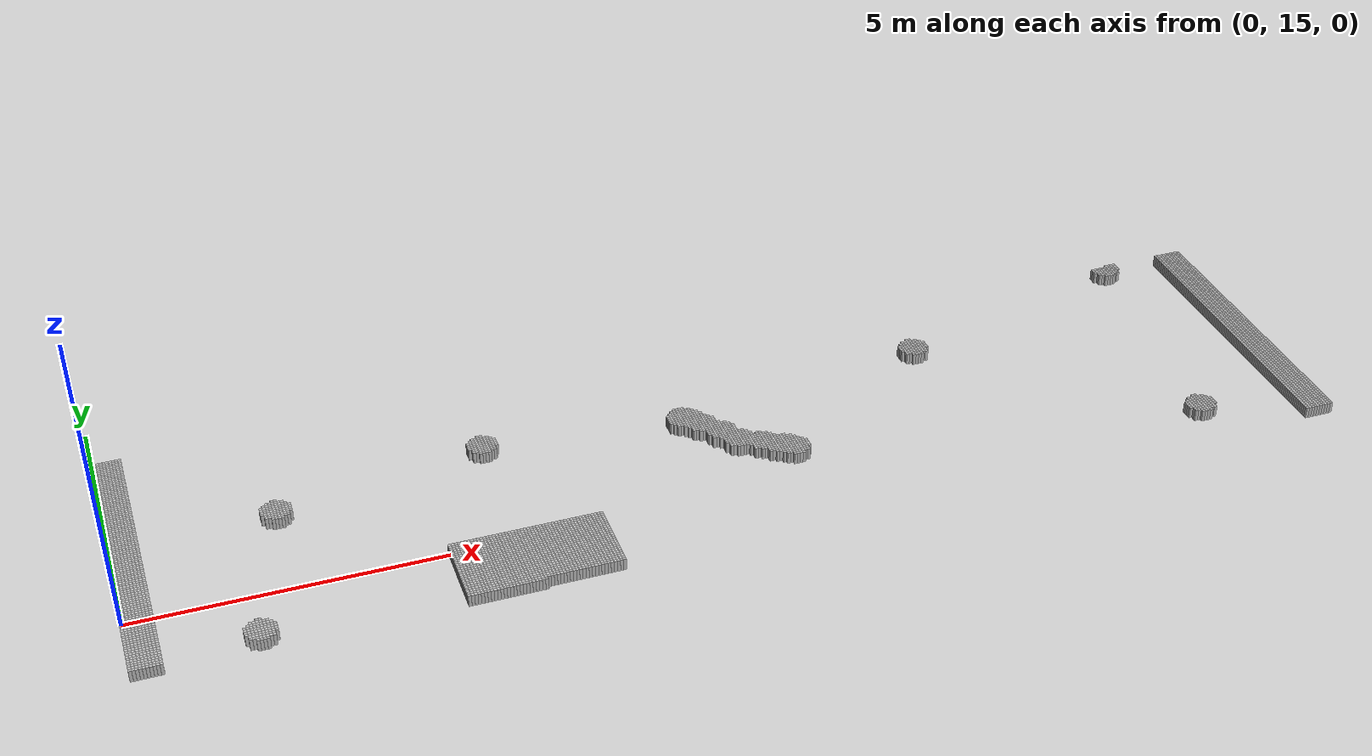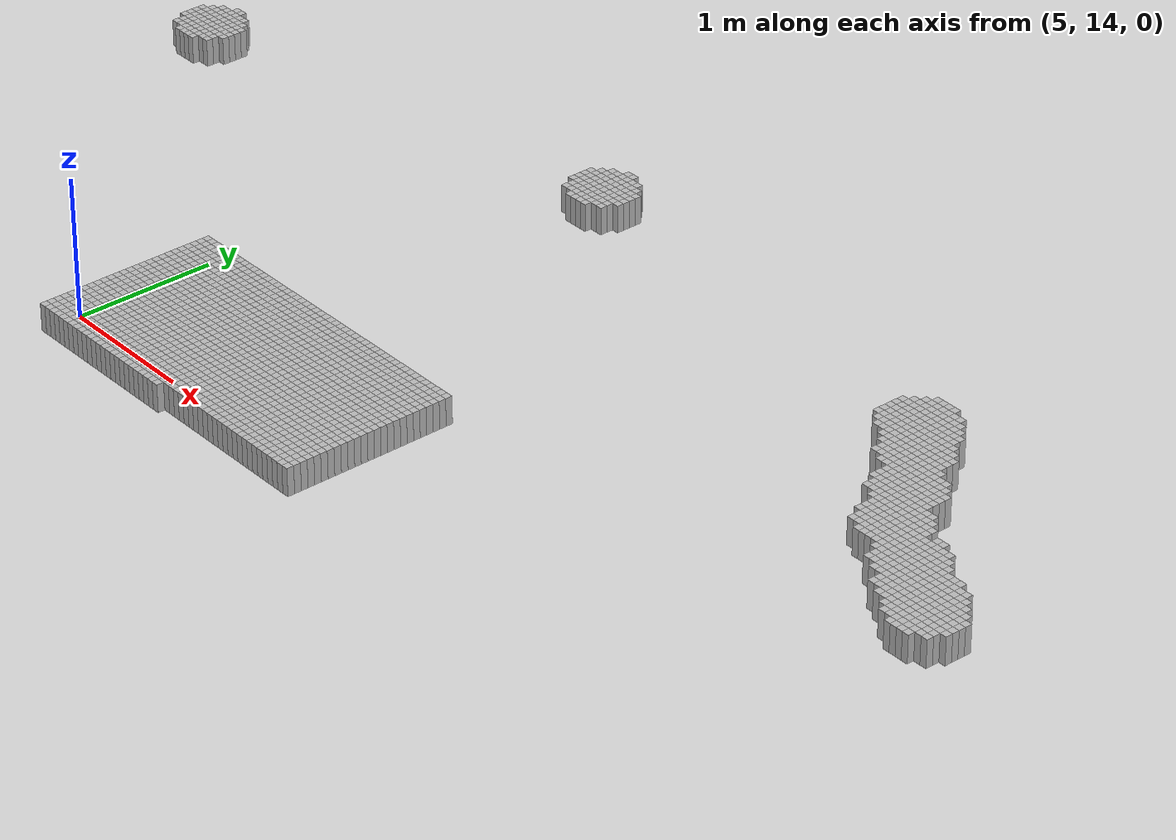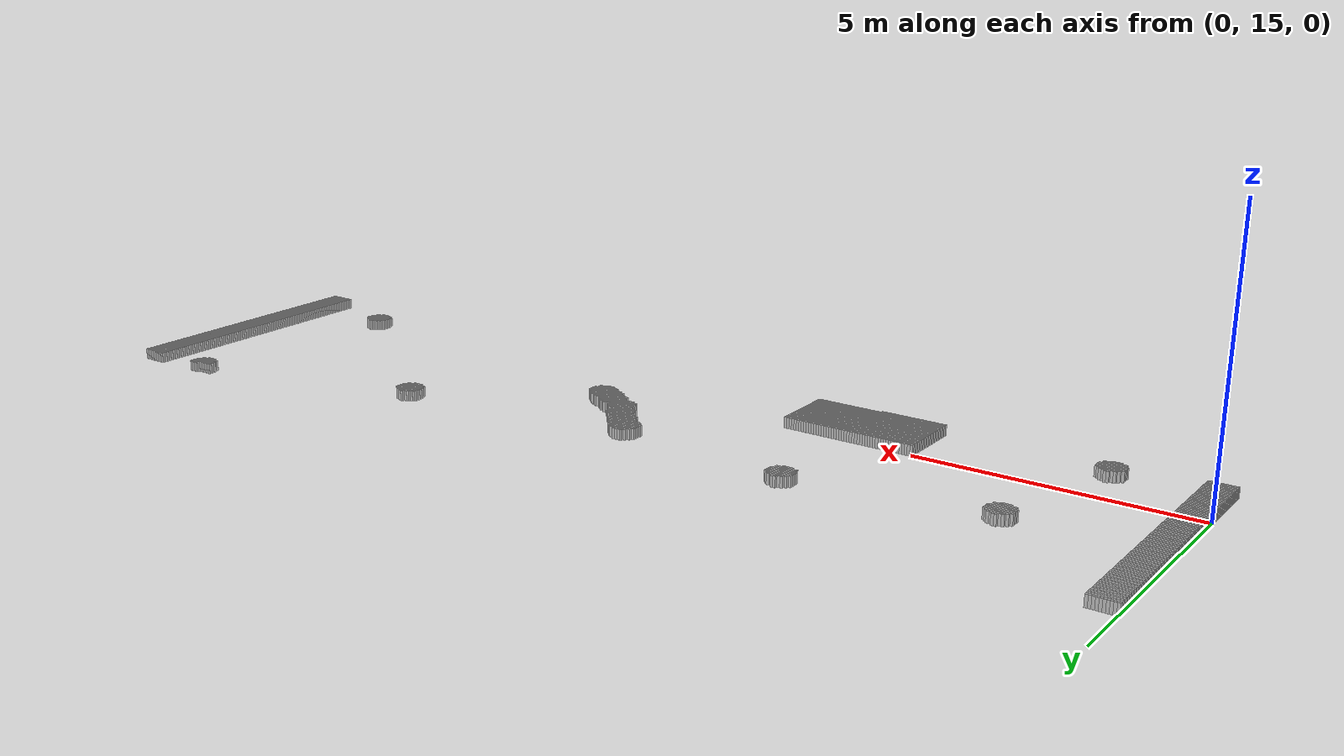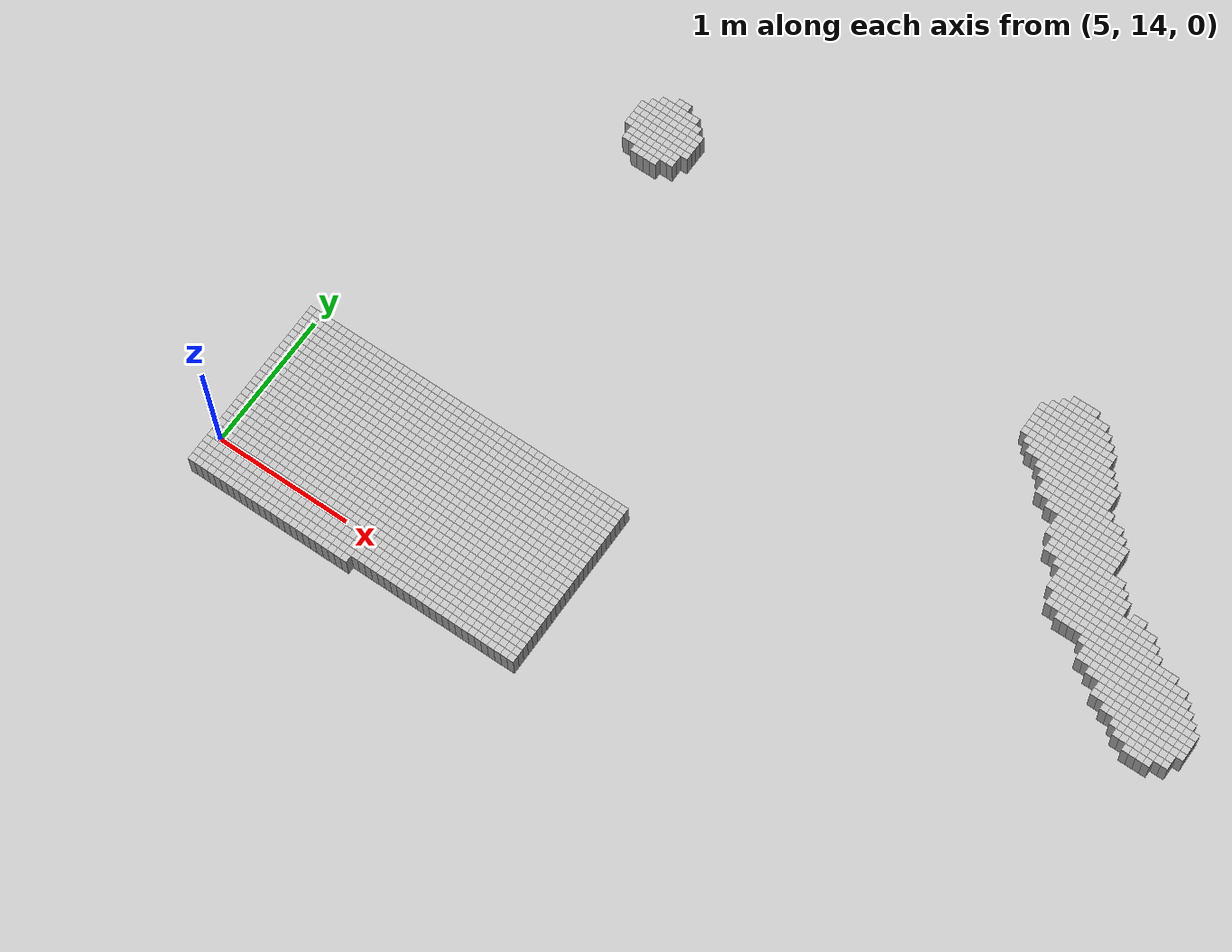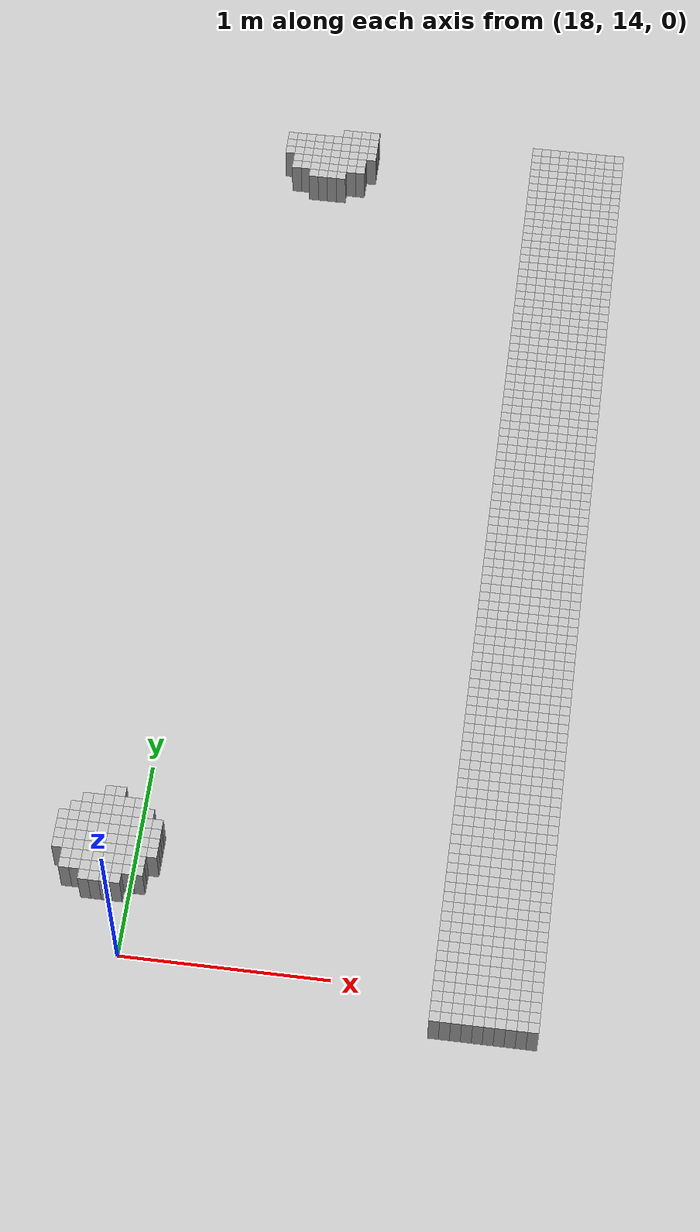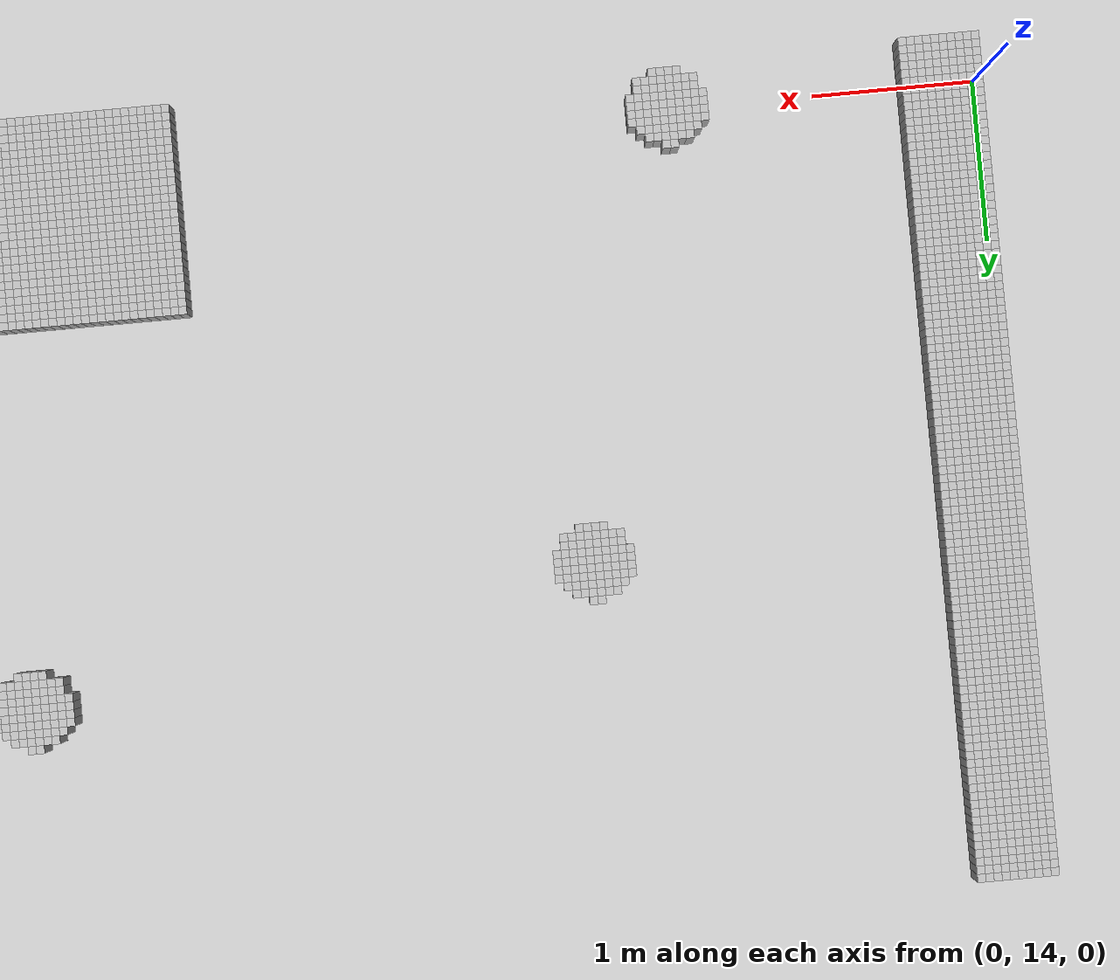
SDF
<sdf version="1.6">
 <world name="default">
  <model name="obstacle_369_21">
   <static>true</static>
   <link name="link">
    <pose>18.45 18.95 0.1 0 0 0</pose>
    <collision name="collision"><geometry><box><size>0.05 0.05 0.2</size></box></geometry></collision>
    <visual name="visual"><geometry><box><size>0.05 0.05 0.2</size></box></geometry></visual>
   </link>
  </model>
  <model name="obstacle_370_21">
   <static>true</static>
   <link name="link">
    <pose>18.5 18.95 0.1 0 0 0</pose>
    <collision name="collision"><geometry><box><size>0.05 0.05 0.2</size></box></geometry></collision>
    <visual name="visual"><geometry><box><size>0.05 0.05 0.2</size></box></geometry></visual>
   </link>
  </model>
  <model name="obstacle_371_21">
   <static>true</static>
   <link name="link">
    <pose>18.55 18.95 0.1 0 0 0</pose>
    <collision name="collision"><geometry><box><size>0.05 0.05 0.2</size></box></geometry></collision>
    <visual name="visual"><geometry><box><size>0.05 0.05 0.2</size></box></geometry></visual>
   </link>
  </model>
  <model name="obstacle_372_21">
   <static>true</static>
   <link name="link">
    <pose>18.6 18.95 0.1 0 0 0</pose>
    <collision name="collision"><geometry><box><size>0.05 0.05 0.2</size></box></geometry></collision>
    <visual name="visual"><geometry><box><size>0.05 0.05 0.2</size></box></geometry></visual>
   </link>
  </model>
  <model name="obstacle_390_21">
   <static>true</static>
   <link name="link">
    <pose>19.5 18.95 0.1 0 0 0</pose>
    <collision name="collision"><geometry><box><size>0.05 0.05 0.2</size></box></geometry></collision>
    <visual name="visual"><geometry><box><size>0.05 0.05 0.2</size></box></geometry></visual>
   </link>
  </model>
  <model name="obstacle_391_21">
   <static>true</static>
   <link name="link">
    <pose>19.55 18.95 0.1 0 0 0</pose>
    <collision name="collision"><geometry><box><size>0.05 0.05 0.2</size></box></geometry></collision>
    <visual name="visual"><geometry><box><size>0.05 0.05 0.2</size></box></geometry></visual>
   </link>
  </model>
  <model name="obstacle_392_21">
   <static>true</static>
   <link name="link">
    <pose>19.6 18.95 0.1 0 0 0</pose>
    <collision name="collision"><geometry><box><size>0.05 0.05 0.2</size></box></geometry></collision>
    <visual name="visual"><geometry><box><size>0.05 0.05 0.2</size></box></geometry></visual>
   </link>
  </model>
  <model name="obstacle_393_21">
   <static>true</static>
   <link name="link">
    <pose>19.650000000000002 18.95 0.1 0 0 0</pose>
    <collision name="collision"><geometry><box><size>0.05 0.05 0.2</size></box></geometry></collision>
    <visual name="visual"><geometry><box><size>0.05 0.05 0.2</size></box></geometry></visual>
   </link>
  </model>
  <model name="obstacle_394_21">
   <static>true</static>
   <link name="link">
    <pose>19.700000000000003 18.95 0.1 0 0 0</pose>
    <collision name="collision"><geometry><box><size>0.05 0.05 0.2</size></box></geometry></collision>
    <visual name="visual"><geometry><box><size>0.05 0.05 0.2</size></box></geometry></visual>
   </link>
  </model>
  <model name="obstacle_395_21">
   <static>true</static>
   <link name="link">
    <pose>19.75 18.95 0.1 0 0 0</pose>
    <collision name="collision"><geometry><box><size>0.05 0.05 0.2</size></box></geometry></collision>
    <visual name="visual"><geometry><box><size>0.05 0.05 0.2</size></box></geometry></visual>
   </link>
  </model>
  <model name="obstacle_396_21">
   <static>true</static>
   <link name="link">
    <pose>19.8 18.95 0.1 0 0 0</pose>
    <collision name="collision"><geometry><box><size>0.05 0.05 0.2</size></box></geometry></collision>
    <visual name="visual"><geometry><box><size>0.05 0.05 0.2</size></box></geometry></visual>
   </link>
  </model>
  <model name="obstacle_397_21">
   <static>true</static>
   <link name="link">
    <pose>19.85 18.95 0.1 0 0 0</pose>
    <collision name="collision"><geometry><box><size>0.05 0.05 0.2</size></box></geometry></collision>
    <visual name="visual"><geometry><box><size>0.05 0.05 0.2</size></box></geometry></visual>
   </link>
  </model>
  <model name="obstacle_398_21">
   <static>true</static>
   <link name="link">
    <pose>19.900000000000002 18.95 0.1 0 0 0</pose>
    <collision name="collision"><geometry><box><size>0.05 0.05 0.2</size></box></geometry></collision>
    <visual name="visual"><geometry><box><size>0.05 0.05 0.2</size></box></geometry></visual>
   </link>
  </model>
  <model name="obstacle_399_21">
   <static>true</static>
   <link name="link">
    <pose>19.950000000000003 18.95 0.1 0 0 0</pose>
    <collision name="collision"><geometry><box><size>0.05 0.05 0.2</size></box></geometry></collision>
    <visual name="visual"><geometry><box><size>0.05 0.05 0.2</size></box></geometry></visual>
   </link>
  </model>
  <model name="obstacle_0_22">
   <static>true</static>
   <link name="link">
    <pose>0.0 18.900000000000002 0.1 0 0 0</pose>
    <collision name="collision"><geometry><box><size>0.05 0.05 0.2</size></box></geometry></collision>
    <visual name="visual"><geometry><box><size>0.05 0.05 0.2</size></box></geometry></visual>
   </link>
  </model>
  <model name="obstacle_1_22">
   <static>true</static>
   <link name="link">
    <pose>0.05 18.900000000000002 0.1 0 0 0</pose>
    <collision name="collision"><geometry><box><size>0.05 0.05 0.2</size></box></geometry></collision>
    <visual name="visual"><geometry><box><size>0.05 0.05 0.2</size></box></geometry></visual>
   </link>
  </model>
  <model name="obstacle_2_22">
   <static>true</static>
   <link name="link">
    <pose>0.1 18.900000000000002 0.1 0 0 0</pose>
    <collision name="collision"><geometry><box><size>0.05 0.05 0.2</size></box></geometry></collision>
    <visual name="visual"><geometry><box><size>0.05 0.05 0.2</size></box></geometry></visual>
   </link>
  </model>
  <model name="obstacle_3_22">
   <static>true</static>
   <link name="link">
    <pose>0.15000000000000002 18.900000000000002 0.1 0 0 0</pose>
    <collision name="collision"><geometry><box><size>0.05 0.05 0.2</size></box></geometry></collision>
    <visual name="visual"><geometry><box><size>0.05 0.05 0.2</size></box></geometry></visual>
   </link>
  </model>
  <model name="obstacle_4_22">
   <static>true</static>
   <link name="link">
    <pose>0.2 18.900000000000002 0.1 0 0 0</pose>
    <collision name="collision"><geometry><box><size>0.05 0.05 0.2</size></box></geometry></collision>
    <visual name="visual"><geometry><box><size>0.05 0.05 0.2</size></box></geometry></visual>
   </link>
  </model>
  <model name="obstacle_5_22">
   <static>true</static>
   <link name="link">
    <pose>0.25 18.900000000000002 0.1 0 0 0</pose>
    <collision name="collision"><geometry><box><size>0.05 0.05 0.2</size></box></geometry></collision>
    <visual name="visual"><geometry><box><size>0.05 0.05 0.2</size></box></geometry></visual>
   </link>
  </model>
  <model name="obstacle_6_22">
   <static>true</static>
   <link name="link">
    <pose>0.30000000000000004 18.900000000000002 0.1 0 0 0</pose>
    <collision name="collision"><geometry><box><size>0.05 0.05 0.2</size></box></geometry></collision>
    <visual name="visual"><geometry><box><size>0.05 0.05 0.2</size></box></geometry></visual>
   </link>
  </model>
  <model name="obstacle_7_22">
   <static>true</static>
   <link name="link">
    <pose>0.35000000000000003 18.900000000000002 0.1 0 0 0</pose>
    <collision name="collision"><geometry><box><size>0.05 0.05 0.2</size></box></geometry></collision>
    <visual name="visual"><geometry><box><size>0.05 0.05 0.2</size></box></geometry></visual>
   </link>
  </model>
  <model name="obstacle_8_22">
   <static>true</static>
   <link name="link">
    <pose>0.4 18.900000000000002 0.1 0 0 0</pose>
    <collision name="collision"><geometry><box><size>0.05 0.05 0.2</size></box></geometry></collision>
    <visual name="visual"><geometry><box><size>0.05 0.05 0.2</size></box></geometry></visual>
   </link>
  </model>
  <model name="obstacle_9_22">
   <static>true</static>
   <link name="link">
    <pose>0.45 18.900000000000002 0.1 0 0 0</pose>
    <collision name="collision"><geometry><box><size>0.05 0.05 0.2</size></box></geometry></collision>
    <visual name="visual"><geometry><box><size>0.05 0.05 0.2</size></box></geometry></visual>
   </link>
  </model>
  <model name="obstacle_363_22">
   <static>true</static>
   <link name="link">
    <pose>18.150000000000002 18.900000000000002 0.1 0 0 0</pose>
    <collision name="collision"><geometry><box><size>0.05 0.05 0.2</size></box></geometry></collision>
    <visual name="visual"><geometry><box><size>0.05 0.05 0.2</size></box></geometry></visual>
   </link>
  </model>
  <model name="obstacle_364_22">
   <static>true</static>
   <link name="link">
    <pose>18.2 18.900000000000002 0.1 0 0 0</pose>
    <collision name="collision"><geometry><box><size>0.05 0.05 0.2</size></box></geometry></collision>
    <visual name="visual"><geometry><box><size>0.05 0.05 0.2</size></box></geometry></visual>
   </link>
  </model>
  <model name="obstacle_365_22">
   <static>true</static>
   <link name="link">
    <pose>18.25 18.900000000000002 0.1 0 0 0</pose>
    <collision name="collision"><geometry><box><size>0.05 0.05 0.2</size></box></geometry></collision>
    <visual name="visual"><geometry><box><size>0.05 0.05 0.2</size></box></geometry></visual>
   </link>
  </model>
  <model name="obstacle_366_22">
   <static>true</static>
   <link name="link">
    <pose>18.3 18.900000000000002 0.1 0 0 0</pose>
    <collision name="collision"><geometry><box><size>0.05 0.05 0.2</size></box></geometry></collision>
    <visual name="visual"><geometry><box><size>0.05 0.05 0.2</size></box></geometry></visual>
   </link>
  </model>
  <model name="obstacle_367_22">
   <static>true</static>
   <link name="link">
    <pose>18.35 18.900000000000002 0.1 0 0 0</pose>
    <collision name="collision"><geometry><box><size>0.05 0.05 0.2</size></box></geometry></collision>
    <visual name="visual"><geometry><box><size>0.05 0.05 0.2</size></box></geometry></visual>
   </link>
  </model>
  <model name="obstacle_368_22">
   <static>true</static>
   <link name="link">
    <pose>18.400000000000002 18.900000000000002 0.1 0 0 0</pose>
    <collision name="collision"><geometry><box><size>0.05 0.05 0.2</size></box></geometry></collision>
    <visual name="visual"><geometry><box><size>0.05 0.05 0.2</size></box></geometry></visual>
   </link>
  </model>
  <model name="obstacle_369_22">
   <static>true</static>
   <link name="link">
    <pose>18.45 18.900000000000002 0.1 0 0 0</pose>
    <collision name="collision"><geometry><box><size>0.05 0.05 0.2</size></box></geometry></collision>
    <visual name="visual"><geometry><box><size>0.05 0.05 0.2</size></box></geometry></visual>
   </link>
  </model>
  <model name="obstacle_370_22">
   <static>true</static>
   <link name="link">
    <pose>18.5 18.900000000000002 0.1 0 0 0</pose>
    <collision name="collision"><geometry><box><size>0.05 0.05 0.2</size></box></geometry></collision>
    <visual name="visual"><geometry><box><size>0.05 0.05 0.2</size></box></geometry></visual>
   </link>
  </model>
  <model name="obstacle_371_22">
   <static>true</static>
   <link name="link">
    <pose>18.55 18.900000000000002 0.1 0 0 0</pose>
    <collision name="collision"><geometry><box><size>0.05 0.05 0.2</size></box></geometry></collision>
    <visual name="visual"><geometry><box><size>0.05 0.05 0.2</size></box></geometry></visual>
   </link>
  </model>
  <model name="obstacle_372_22">
   <static>true</static>
   <link name="link">
    <pose>18.6 18.900000000000002 0.1 0 0 0</pose>
    <collision name="collision"><geometry><box><size>0.05 0.05 0.2</size></box></geometry></collision>
    <visual name="visual"><geometry><box><size>0.05 0.05 0.2</size></box></geometry></visual>
   </link>
  </model>
  <model name="obstacle_390_22">
   <static>true</static>
   <link name="link">
    <pose>19.5 18.900000000000002 0.1 0 0 0</pose>
    <collision name="collision"><geometry><box><size>0.05 0.05 0.2</size></box></geometry></collision>
    <visual name="visual"><geometry><box><size>0.05 0.05 0.2</size></box></geometry></visual>
   </link>
  </model>
  <model name="obstacle_391_22">
   <static>true</static>
   <link name="link">
    <pose>19.55 18.900000000000002 0.1 0 0 0</pose>
    <collision name="collision"><geometry><box><size>0.05 0.05 0.2</size></box></geometry></collision>
    <visual name="visual"><geometry><box><size>0.05 0.05 0.2</size></box></geometry></visual>
   </link>
  </model>
  <model name="obstacle_392_22">
   <static>true</static>
   <link name="link">
    <pose>19.6 18.900000000000002 0.1 0 0 0</pose>
    <collision name="collision"><geometry><box><size>0.05 0.05 0.2</size></box></geometry></collision>
    <visual name="visual"><geometry><box><size>0.05 0.05 0.2</size></box></geometry></visual>
   </link>
  </model>
  <model name="obstacle_393_22">
   <static>true</static>
   <link name="link">
    <pose>19.650000000000002 18.900000000000002 0.1 0 0 0</pose>
    <collision name="collision"><geometry><box><size>0.05 0.05 0.2</size></box></geometry></collision>
    <visual name="visual"><geometry><box><size>0.05 0.05 0.2</size></box></geometry></visual>
   </link>
  </model>
  <model name="obstacle_394_22">
   <static>true</static>
   <link name="link">
    <pose>19.700000000000003 18.900000000000002 0.1 0 0 0</pose>
    <collision name="collision"><geometry><box><size>0.05 0.05 0.2</size></box></geometry></collision>
    <visual name="visual"><geometry><box><size>0.05 0.05 0.2</size></box></geometry></visual>
   </link>
  </model>
  <model name="obstacle_395_22">
   <static>true</static>
   <link name="link">
    <pose>19.75 18.900000000000002 0.1 0 0 0</pose>
    <collision name="collision"><geometry><box><size>0.05 0.05 0.2</size></box></geometry></collision>
    <visual name="visual"><geometry><box><size>0.05 0.05 0.2</size></box></geometry></visual>
   </link>
  </model>
  <model name="obstacle_396_22">
   <static>true</static>
   <link name="link">
    <pose>19.8 18.900000000000002 0.1 0 0 0</pose>
    <collision name="collision"><geometry><box><size>0.05 0.05 0.2</size></box></geometry></collision>
    <visual name="visual"><geometry><box><size>0.05 0.05 0.2</size></box></geometry></visual>
   </link>
  </model>
  <model name="obstacle_397_22">
   <static>true</static>
   <link name="link">
    <pose>19.85 18.900000000000002 0.1 0 0 0</pose>
    <collision name="collision"><geometry><box><size>0.05 0.05 0.2</size></box></geometry></collision>
    <visual name="visual"><geometry><box><size>0.05 0.05 0.2</size></box></geometry></visual>
   </link>
  </model>
  <model name="obstacle_398_22">
   <static>true</static>
   <link name="link">
    <pose>19.900000000000002 18.900000000000002 0.1 0 0 0</pose>
    <collision name="collision"><geometry><box><size>0.05 0.05 0.2</size></box></geometry></collision>
    <visual name="visual"><geometry><box><size>0.05 0.05 0.2</size></box></geometry></visual>
   </link>
  </model>
  <model name="obstacle_399_22">
   <static>true</static>
   <link name="link">
    <pose>19.950000000000003 18.900000000000002 0.1 0 0 0</pose>
    <collision name="collision"><geometry><box><size>0.05 0.05 0.2</size></box></geometry></collision>
    <visual name="visual"><geometry><box><size>0.05 0.05 0.2</size></box></geometry></visual>
   </link>
  </model>
  <model name="obstacle_0_23">
   <static>true</static>
   <link name="link">
    <pose>0.0 18.85 0.1 0 0 0</pose>
    <collision name="collision"><geometry><box><size>0.05 0.05 0.2</size></box></geometry></collision>
    <visual name="visual"><geometry><box><size>0.05 0.05 0.2</size></box></geometry></visual>
   </link>
  </model>
  <model name="obstacle_1_23">
   <static>true</static>
   <link name="link">
    <pose>0.05 18.85 0.1 0 0 0</pose>
    <collision name="collision"><geometry><box><size>0.05 0.05 0.2</size></box></geometry></collision>
    <visual name="visual"><geometry><box><size>0.05 0.05 0.2</size></box></geometry></visual>
   </link>
  </model>
  <model name="obstacle_2_23">
   <static>true</static>
   <link name="link">
    <pose>0.1 18.85 0.1 0 0 0</pose>
    <collision name="collision"><geometry><box><size>0.05 0.05 0.2</size></box></geometry></collision>
    <visual name="visual"><geometry><box><size>0.05 0.05 0.2</size></box></geometry></visual>
   </link>
  </model>
  <model name="obstacle_3_23">
   <static>true</static>
   <link name="link">
    <pose>0.15000000000000002 18.85 0.1 0 0 0</pose>
    <collision name="collision"><geometry><box><size>0.05 0.05 0.2</size></box></geometry></collision>
    <visual name="visual"><geometry><box><size>0.05 0.05 0.2</size></box></geometry></visual>
   </link>
  </model>
  <model name="obstacle_4_23">
   <static>true</static>
   <link name="link">
    <pose>0.2 18.85 0.1 0 0 0</pose>
    <collision name="collision"><geometry><box><size>0.05 0.05 0.2</size></box></geometry></collision>
    <visual name="visual"><geometry><box><size>0.05 0.05 0.2</size></box></geometry></visual>
   </link>
  </model>
  <model name="obstacle_5_23">
   <static>true</static>
   <link name="link">
    <pose>0.25 18.85 0.1 0 0 0</pose>
    <collision name="collision"><geometry><box><size>0.05 0.05 0.2</size></box></geometry></collision>
    <visual name="visual"><geometry><box><size>0.05 0.05 0.2</size></box></geometry></visual>
   </link>
  </model>
  <model name="obstacle_6_23">
   <static>true</static>
   <link name="link">
    <pose>0.30000000000000004 18.85 0.1 0 0 0</pose>
    <collision name="collision"><geometry><box><size>0.05 0.05 0.2</size></box></geometry></collision>
    <visual name="visual"><geometry><box><size>0.05 0.05 0.2</size></box></geometry></visual>
   </link>
  </model>
  <model name="obstacle_7_23">
   <static>true</static>
   <link name="link">
    <pose>0.35000000000000003 18.85 0.1 0 0 0</pose>
    <collision name="collision"><geometry><box><size>0.05 0.05 0.2</size></box></geometry></collision>
    <visual name="visual"><geometry><box><size>0.05 0.05 0.2</size></box></geometry></visual>
   </link>
  </model>
  <model name="obstacle_8_23">
   <static>true</static>
   <link name="link">
    <pose>0.4 18.85 0.1 0 0 0</pose>
    <collision name="collision"><geometry><box><size>0.05 0.05 0.2</size></box></geometry></collision>
    <visual name="visual"><geometry><box><size>0.05 0.05 0.2</size></box></geometry></visual>
   </link>
  </model>
  <model name="obstacle_9_23">
   <static>true</static>
   <link name="link">
    <pose>0.45 18.85 0.1 0 0 0</pose>
    <collision name="collision"><geometry><box><size>0.05 0.05 0.2</size></box></geometry></collision>
    <visual name="visual"><geometry><box><size>0.05 0.05 0.2</size></box></geometry></visual>
   </link>
  </model>
  <model name="obstacle_363_23">
   <static>true</static>
   <link name="link">
    <pose>18.150000000000002 18.85 0.1 0 0 0</pose>
    <collision name="collision"><geometry><box><size>0.05 0.05 0.2</size></box></geometry></collision>
    <visual name="visual"><geometry><box><size>0.05 0.05 0.2</size></box></geometry></visual>
   </link>
  </model>
  <model name="obstacle_364_23">
   <static>true</static>
   <link name="link">
    <pose>18.2 18.85 0.1 0 0 0</pose>
    <collision name="collision"><geometry><box><size>0.05 0.05 0.2</size></box></geometry></collision>
    <visual name="visual"><geometry><box><size>0.05 0.05 0.2</size></box></geometry></visual>
   </link>
  </model>
  <model name="obstacle_365_23">
   <static>true</static>
   <link name="link">
    <pose>18.25 18.85 0.1 0 0 0</pose>
    <collision name="collision"><geometry><box><size>0.05 0.05 0.2</size></box></geometry></collision>
    <visual name="visual"><geometry><box><size>0.05 0.05 0.2</size></box></geometry></visual>
   </link>
  </model>
  <model name="obstacle_366_23">
   <static>true</static>
   <link name="link">
    <pose>18.3 18.85 0.1 0 0 0</pose>
    <collision name="collision"><geometry><box><size>0.05 0.05 0.2</size></box></geometry></collision>
    <visual name="visual"><geometry><box><size>0.05 0.05 0.2</size></box></geometry></visual>
   </link>
  </model>
  <model name="obstacle_367_23">
   <static>true</static>
   <link name="link">
    <pose>18.35 18.85 0.1 0 0 0</pose>
    <collision name="collision"><geometry><box><size>0.05 0.05 0.2</size></box></geometry></collision>
    <visual name="visual"><geometry><box><size>0.05 0.05 0.2</size></box></geometry></visual>
   </link>
  </model>
  <model name="obstacle_368_23">
   <static>true</static>
   <link name="link">
    <pose>18.400000000000002 18.85 0.1 0 0 0</pose>
    <collision name="collision"><geometry><box><size>0.05 0.05 0.2</size></box></geometry></collision>
    <visual name="visual"><geometry><box><size>0.05 0.05 0.2</size></box></geometry></visual>
   </link>
  </model>
  <model name="obstacle_369_23">
   <static>true</static>
   <link name="link">
    <pose>18.45 18.85 0.1 0 0 0</pose>
    <collision name="collision"><geometry><box><size>0.05 0.05 0.2</size></box></geometry></collision>
    <visual name="visual"><geometry><box><size>0.05 0.05 0.2</size></box></geometry></visual>
   </link>
  </model>
  <model name="obstacle_370_23">
   <static>true</static>
   <link name="link">
    <pose>18.5 18.85 0.1 0 0 0</pose>
    <collision name="collision"><geometry><box><size>0.05 0.05 0.2</size></box></geometry></collision>
    <visual name="visual"><geometry><box><size>0.05 0.05 0.2</size></box></geometry></visual>
   </link>
  </model>
  <model name="obstacle_371_23">
   <static>true</static>
   <link name="link">
    <pose>18.55 18.85 0.1 0 0 0</pose>
    <collision name="collision"><geometry><box><size>0.05 0.05 0.2</size></box></geometry></collision>
    <visual name="visual"><geometry><box><size>0.05 0.05 0.2</size></box></geometry></visual>
   </link>
  </model>
  <model name="obstacle_372_23">
   <static>true</static>
   <link name="link">
    <pose>18.6 18.85 0.1 0 0 0</pose>
    <collision name="collision"><geometry><box><size>0.05 0.05 0.2</size></box></geometry></collision>
    <visual name="visual"><geometry><box><size>0.05 0.05 0.2</size></box></geometry></visual>
   </link>
  </model>
  <model name="obstacle_390_23">
   <static>true</static>
   <link name="link">
    <pose>19.5 18.85 0.1 0 0 0</pose>
    <collision name="collision"><geometry><box><size>0.05 0.05 0.2</size></box></geometry></collision>
    <visual name="visual"><geometry><box><size>0.05 0.05 0.2</size></box></geometry></visual>
   </link>
  </model>
  <model name="obstacle_391_23">
   <static>true</static>
   <link name="link">
    <pose>19.55 18.85 0.1 0 0 0</pose>
    <collision name="collision"><geometry><box><size>0.05 0.05 0.2</size></box></geometry></collision>
    <visual name="visual"><geometry><box><size>0.05 0.05 0.2</size></box></geometry></visual>
   </link>
  </model>
  <model name="obstacle_392_23">
   <static>true</static>
   <link name="link">
    <pose>19.6 18.85 0.1 0 0 0</pose>
    <collision name="collision"><geometry><box><size>0.05 0.05 0.2</size></box></geometry></collision>
    <visual name="visual"><geometry><box><size>0.05 0.05 0.2</size></box></geometry></visual>
   </link>
  </model>
  <model name="obstacle_393_23">
   <static>true</static>
   <link name="link">
    <pose>19.650000000000002 18.85 0.1 0 0 0</pose>
    <collision name="collision"><geometry><box><size>0.05 0.05 0.2</size></box></geometry></collision>
    <visual name="visual"><geometry><box><size>0.05 0.05 0.2</size></box></geometry></visual>
   </link>
  </model>
  <model name="obstacle_394_23">
   <static>true</static>
   <link name="link">
    <pose>19.700000000000003 18.85 0.1 0 0 0</pose>
    <collision name="collision"><geometry><box><size>0.05 0.05 0.2</size></box></geometry></collision>
    <visual name="visual"><geometry><box><size>0.05 0.05 0.2</size></box></geometry></visual>
   </link>
  </model>
  <model name="obstacle_395_23">
   <static>true</static>
   <link name="link">
    <pose>19.75 18.85 0.1 0 0 0</pose>
    <collision name="collision"><geometry><box><size>0.05 0.05 0.2</size></box></geometry></collision>
    <visual name="visual"><geometry><box><size>0.05 0.05 0.2</size></box></geometry></visual>
   </link>
  </model>
  <model name="obstacle_396_23">
   <static>true</static>
   <link name="link">
    <pose>19.8 18.85 0.1 0 0 0</pose>
    <collision name="collision"><geometry><box><size>0.05 0.05 0.2</size></box></geometry></collision>
    <visual name="visual"><geometry><box><size>0.05 0.05 0.2</size></box></geometry></visual>
   </link>
  </model>
  <model name="obstacle_397_23">
   <static>true</static>
   <link name="link">
    <pose>19.85 18.85 0.1 0 0 0</pose>
    <collision name="collision"><geometry><box><size>0.05 0.05 0.2</size></box></geometry></collision>
    <visual name="visual"><geometry><box><size>0.05 0.05 0.2</size></box></geometry></visual>
   </link>
  </model>
  <model name="obstacle_398_23">
   <static>true</static>
   <link name="link">
    <pose>19.900000000000002 18.85 0.1 0 0 0</pose>
    <collision name="collision"><geometry><box><size>0.05 0.05 0.2</size></box></geometry></collision>
    <visual name="visual"><geometry><box><size>0.05 0.05 0.2</size></box></geometry></visual>
   </link>
  </model>
  <model name="obstacle_399_23">
   <static>true</static>
   <link name="link">
    <pose>19.950000000000003 18.85 0.1 0 0 0</pose>
    <collision name="collision"><geometry><box><size>0.05 0.05 0.2</size></box></geometry></collision>
    <visual name="visual"><geometry><box><size>0.05 0.05 0.2</size></box></geometry></visual>
   </link>
  </model>
  <model name="obstacle_0_24">
   <static>true</static>
   <link name="link">
    <pose>0.0 18.8 0.1 0 0 0</pose>
    <collision name="collision"><geometry><box><size>0.05 0.05 0.2</size></box></geometry></collision>
    <visual name="visual"><geometry><box><size>0.05 0.05 0.2</size></box></geometry></visual>
   </link>
  </model>
  <model name="obstacle_1_24">
   <static>true</static>
   <link name="link">
    <pose>0.05 18.8 0.1 0 0 0</pose>
    <collision name="collision"><geometry><box><size>0.05 0.05 0.2</size></box></geometry></collision>
    <visual name="visual"><geometry><box><size>0.05 0.05 0.2</size></box></geometry></visual>
   </link>
  </model>
  <model name="obstacle_2_24">
   <static>true</static>
   <link name="link">
    <pose>0.1 18.8 0.1 0 0 0</pose>
    <collision name="collision"><geometry><box><size>0.05 0.05 0.2</size></box></geometry></collision>
    <visual name="visual"><geometry><box><size>0.05 0.05 0.2</size></box></geometry></visual>
   </link>
  </model>
  <model name="obstacle_3_24">
   <static>true</static>
   <link name="link">
    <pose>0.15000000000000002 18.8 0.1 0 0 0</pose>
    <collision name="collision"><geometry><box><size>0.05 0.05 0.2</size></box></geometry></collision>
    <visual name="visual"><geometry><box><size>0.05 0.05 0.2</size></box></geometry></visual>
   </link>
  </model>
  <model name="obstacle_4_24">
   <static>true</static>
   <link name="link">
    <pose>0.2 18.8 0.1 0 0 0</pose>
    <collision name="collision"><geometry><box><size>0.05 0.05 0.2</size></box></geometry></collision>
    <visual name="visual"><geometry><box><size>0.05 0.05 0.2</size></box></geometry></visual>
   </link>
  </model>
  <model name="obstacle_5_24">
   <static>true</static>
   <link name="link">
    <pose>0.25 18.8 0.1 0 0 0</pose>
    <collision name="collision"><geometry><box><size>0.05 0.05 0.2</size></box></geometry></collision>
    <visual name="visual"><geometry><box><size>0.05 0.05 0.2</size></box></geometry></visual>
   </link>
  </model>
  <model name="obstacle_6_24">
   <static>true</static>
   <link name="link">
    <pose>0.30000000000000004 18.8 0.1 0 0 0</pose>
    <collision name="collision"><geometry><box><size>0.05 0.05 0.2</size></box></geometry></collision>
    <visual name="visual"><geometry><box><size>0.05 0.05 0.2</size></box></geometry></visual>
   </link>
  </model>
  <model name="obstacle_7_24">
   <static>true</static>
   <link name="link">
    <pose>0.35000000000000003 18.8 0.1 0 0 0</pose>
    <collision name="collision"><geometry><box><size>0.05 0.05 0.2</size></box></geometry></collision>
    <visual name="visual"><geometry><box><size>0.05 0.05 0.2</size></box></geometry></visual>
   </link>
  </model>
  <model name="obstacle_8_24">
   <static>true</static>
   <link name="link">
    <pose>0.4 18.8 0.1 0 0 0</pose>
    <collision name="collision"><geometry><box><size>0.05 0.05 0.2</size></box></geometry></collision>
    <visual name="visual"><geometry><box><size>0.05 0.05 0.2</size></box></geometry></visual>
   </link>
  </model>
  <model name="obstacle_9_24">
   <static>true</static>
   <link name="link">
    <pose>0.45 18.8 0.1 0 0 0</pose>
    <collision name="collision"><geometry><box><size>0.05 0.05 0.2</size></box></geometry></collision>
    <visual name="visual"><geometry><box><size>0.05 0.05 0.2</size></box></geometry></visual>
   </link>
  </model>
  <model name="obstacle_363_24">
   <static>true</static>
   <link name="link">
    <pose>18.150000000000002 18.8 0.1 0 0 0</pose>
    <collision name="collision"><geometry><box><size>0.05 0.05 0.2</size></box></geometry></collision>
    <visual name="visual"><geometry><box><size>0.05 0.05 0.2</size></box></geometry></visual>
   </link>
  </model>
  <model name="obstacle_364_24">
   <static>true</static>
   <link name="link">
    <pose>18.2 18.8 0.1 0 0 0</pose>
    <collision name="collision"><geometry><box><size>0.05 0.05 0.2</size></box></geometry></collision>
    <visual name="visual"><geometry><box><size>0.05 0.05 0.2</size></box></geometry></visual>
   </link>
  </model>
  <model name="obstacle_365_24">
   <static>true</static>
   <link name="link">
    <pose>18.25 18.8 0.1 0 0 0</pose>
    <collision name="collision"><geometry><box><size>0.05 0.05 0.2</size></box></geometry></collision>
    <visual name="visual"><geometry><box><size>0.05 0.05 0.2</size></box></geometry></visual>
   </link>
  </model>
  <model name="obstacle_366_24">
   <static>true</static>
   <link name="link">
    <pose>18.3 18.8 0.1 0 0 0</pose>
    <collision name="collision"><geometry><box><size>0.05 0.05 0.2</size></box></geometry></collision>
    <visual name="visual"><geometry><box><size>0.05 0.05 0.2</size></box></geometry></visual>
   </link>
  </model>
  <model name="obstacle_367_24">
   <static>true</static>
   <link name="link">
    <pose>18.35 18.8 0.1 0 0 0</pose>
    <collision name="collision"><geometry><box><size>0.05 0.05 0.2</size></box></geometry></collision>
    <visual name="visual"><geometry><box><size>0.05 0.05 0.2</size></box></geometry></visual>
   </link>
  </model>
  <model name="obstacle_368_24">
   <static>true</static>
   <link name="link">
    <pose>18.400000000000002 18.8 0.1 0 0 0</pose>
    <collision name="collision"><geometry><box><size>0.05 0.05 0.2</size></box></geometry></collision>
    <visual name="visual"><geometry><box><size>0.05 0.05 0.2</size></box></geometry></visual>
   </link>
  </model>
  <model name="obstacle_369_24">
   <static>true</static>
   <link name="link">
    <pose>18.45 18.8 0.1 0 0 0</pose>
    <collision name="collision"><geometry><box><size>0.05 0.05 0.2</size></box></geometry></collision>
    <visual name="visual"><geometry><box><size>0.05 0.05 0.2</size></box></geometry></visual>
   </link>
  </model>
  <model name="obstacle_370_24">
   <static>true</static>
   <link name="link">
    <pose>18.5 18.8 0.1 0 0 0</pose>
    <collision name="collision"><geometry><box><size>0.05 0.05 0.2</size></box></geometry></collision>
    <visual name="visual"><geometry><box><size>0.05 0.05 0.2</size></box></geometry></visual>
   </link>
  </model>
  <model name="obstacle_371_24">
   <static>true</static>
   <link name="link">
    <pose>18.55 18.8 0.1 0 0 0</pose>
    <collision name="collision"><geometry><box><size>0.05 0.05 0.2</size></box></geometry></collision>
    <visual name="visual"><geometry><box><size>0.05 0.05 0.2</size></box></geometry></visual>
   </link>
  </model>
  <model name="obstacle_372_24">
   <static>true</static>
   <link name="link">
    <pose>18.6 18.8 0.1 0 0 0</pose>
    <collision name="collision"><geometry><box><size>0.05 0.05 0.2</size></box></geometry></collision>
    <visual name="visual"><geometry><box><size>0.05 0.05 0.2</size></box></geometry></visual>
   </link>
  </model>
  <model name="obstacle_390_24">
   <static>true</static>
   <link name="link">
    <pose>19.5 18.8 0.1 0 0 0</pose>
    <collision name="collision"><geometry><box><size>0.05 0.05 0.2</size></box></geometry></collision>
    <visual name="visual"><geometry><box><size>0.05 0.05 0.2</size></box></geometry></visual>
   </link>
  </model>
  <model name="obstacle_391_24">
   <static>true</static>
   <link name="link">
    <pose>19.55 18.8 0.1 0 0 0</pose>
    <collision name="collision"><geometry><box><size>0.05 0.05 0.2</size></box></geometry></collision>
    <visual name="visual"><geometry><box><size>0.05 0.05 0.2</size></box></geometry></visual>
   </link>
  </model>
  <model name="obstacle_392_24">
   <static>true</static>
   <link name="link">
    <pose>19.6 18.8 0.1 0 0 0</pose>
    <collision name="collision"><geometry><box><size>0.05 0.05 0.2</size></box></geometry></collision>
    <visual name="visual"><geometry><box><size>0.05 0.05 0.2</size></box></geometry></visual>
   </link>
  </model>
  <model name="obstacle_393_24">
   <static>true</static>
   <link name="link">
    <pose>19.650000000000002 18.8 0.1 0 0 0</pose>
    <collision name="collision"><geometry><box><size>0.05 0.05 0.2</size></box></geometry></collision>
    <visual name="visual"><geometry><box><size>0.05 0.05 0.2</size></box></geometry></visual>
   </link>
  </model>
  <model name="obstacle_394_24">
   <static>true</static>
   <link name="link">
    <pose>19.700000000000003 18.8 0.1 0 0 0</pose>
    <collision name="collision"><geometry><box><size>0.05 0.05 0.2</size></box></geometry></collision>
    <visual name="visual"><geometry><box><size>0.05 0.05 0.2</size></box></geometry></visual>
   </link>
  </model>
  <model name="obstacle_395_24">
   <static>true</static>
   <link name="link">
    <pose>19.75 18.8 0.1 0 0 0</pose>
    <collision name="collision"><geometry><box><size>0.05 0.05 0.2</size></box></geometry></collision>
    <visual name="visual"><geometry><box><size>0.05 0.05 0.2</size></box></geometry></visual>
   </link>
  </model>
  <model name="obstacle_396_24">
   <static>true</static>
   <link name="link">
    <pose>19.8 18.8 0.1 0 0 0</pose>
    <collision name="collision"><geometry><box><size>0.05 0.05 0.2</size></box></geometry></collision>
    <visual name="visual"><geometry><box><size>0.05 0.05 0.2</size></box></geometry></visual>
   </link>
  </model>
  <model name="obstacle_397_24">
   <static>true</static>
   <link name="link">
    <pose>19.85 18.8 0.1 0 0 0</pose>
    <collision name="collision"><geometry><box><size>0.05 0.05 0.2</size></box></geometry></collision>
    <visual name="visual"><geometry><box><size>0.05 0.05 0.2</size></box></geometry></visual>
   </link>
  </model>
  <model name="obstacle_398_24">
   <static>true</static>
   <link name="link">
    <pose>19.900000000000002 18.8 0.1 0 0 0</pose>
    <collision name="collision"><geometry><box><size>0.05 0.05 0.2</size></box></geometry></collision>
    <visual name="visual"><geometry><box><size>0.05 0.05 0.2</size></box></geometry></visual>
   </link>
  </model>
  <model name="obstacle_399_24">
   <static>true</static>
   <link name="link">
    <pose>19.950000000000003 18.8 0.1 0 0 0</pose>
    <collision name="collision"><geometry><box><size>0.05 0.05 0.2</size></box></geometry></collision>
    <visual name="visual"><geometry><box><size>0.05 0.05 0.2</size></box></geometry></visual>
   </link>
  </model>
  <model name="obstacle_0_25">
   <static>true</static>
   <link name="link">
    <pose>0.0 18.75 0.1 0 0 0</pose>
    <collision name="collision"><geometry><box><size>0.05 0.05 0.2</size></box></geometry></collision>
    <visual name="visual"><geometry><box><size>0.05 0.05 0.2</size></box></geometry></visual>
   </link>
  </model>
  <model name="obstacle_1_25">
   <static>true</static>
   <link name="link">
    <pose>0.05 18.75 0.1 0 0 0</pose>
    <collision name="collision"><geometry><box><size>0.05 0.05 0.2</size></box></geometry></collision>
    <visual name="visual"><geometry><box><size>0.05 0.05 0.2</size></box></geometry></visual>
   </link>
  </model>
  <model name="obstacle_2_25">
   <static>true</static>
   <link name="link">
    <pose>0.1 18.75 0.1 0 0 0</pose>
    <collision name="collision"><geometry><box><size>0.05 0.05 0.2</size></box></geometry></collision>
    <visual name="visual"><geometry><box><size>0.05 0.05 0.2</size></box></geometry></visual>
   </link>
  </model>
  <model name="obstacle_3_25">
   <static>true</static>
   <link name="link">
    <pose>0.15000000000000002 18.75 0.1 0 0 0</pose>
    <collision name="collision"><geometry><box><size>0.05 0.05 0.2</size></box></geometry></collision>
    <visual name="visual"><geometry><box><size>0.05 0.05 0.2</size></box></geometry></visual>
   </link>
  </model>
  <model name="obstacle_4_25">
   <static>true</static>
   <link name="link">
    <pose>0.2 18.75 0.1 0 0 0</pose>
    <collision name="collision"><geometry><box><size>0.05 0.05 0.2</size></box></geometry></collision>
    <visual name="visual"><geometry><box><size>0.05 0.05 0.2</size></box></geometry></visual>
   </link>
  </model>
  <model name="obstacle_5_25">
   <static>true</static>
   <link name="link">
    <pose>0.25 18.75 0.1 0 0 0</pose>
    <collision name="collision"><geometry><box><size>0.05 0.05 0.2</size></box></geometry></collision>
    <visual name="visual"><geometry><box><size>0.05 0.05 0.2</size></box></geometry></visual>
   </link>
  </model>
  <model name="obstacle_6_25">
   <static>true</static>
   <link name="link">
    <pose>0.30000000000000004 18.75 0.1 0 0 0</pose>
    <collision name="collision"><geometry><box><size>0.05 0.05 0.2</size></box></geometry></collision>
    <visual name="visual"><geometry><box><size>0.05 0.05 0.2</size></box></geometry></visual>
   </link>
  </model>
  <model name="obstacle_7_25">
   <static>true</static>
   <link name="link">
    <pose>0.35000000000000003 18.75 0.1 0 0 0</pose>
    <collision name="collision"><geometry><box><size>0.05 0.05 0.2</size></box></geometry></collision>
    <visual name="visual"><geometry><box><size>0.05 0.05 0.2</size></box></geometry></visual>
   </link>
  </model>
  <model name="obstacle_8_25">
   <static>true</static>
   <link name="link">
    <pose>0.4 18.75 0.1 0 0 0</pose>
    <collision name="collision"><geometry><box><size>0.05 0.05 0.2</size></box></geometry></collision>
    <visual name="visual"><geometry><box><size>0.05 0.05 0.2</size></box></geometry></visual>
   </link>
  </model>
  <model name="obstacle_9_25">
   <static>true</static>
   <link name="link">
    <pose>0.45 18.75 0.1 0 0 0</pose>
    <collision name="collision"><geometry><box><size>0.05 0.05 0.2</size></box></geometry></collision>
    <visual name="visual"><geometry><box><size>0.05 0.05 0.2</size></box></geometry></visual>
   </link>
  </model>
  <model name="obstacle_364_25">
   <static>true</static>
   <link name="link">
    <pose>18.2 18.75 0.1 0 0 0</pose>
    <collision name="collision"><geometry><box><size>0.05 0.05 0.2</size></box></geometry></collision>
    <visual name="visual"><geometry><box><size>0.05 0.05 0.2</size></box></geometry></visual>
   </link>
  </model>
  <model name="obstacle_365_25">
   <static>true</static>
   <link name="link">
    <pose>18.25 18.75 0.1 0 0 0</pose>
    <collision name="collision"><geometry><box><size>0.05 0.05 0.2</size></box></geometry></collision>
    <visual name="visual"><geometry><box><size>0.05 0.05 0.2</size></box></geometry></visual>
   </link>
  </model>
  <model name="obstacle_366_25">
   <static>true</static>
   <link name="link">
    <pose>18.3 18.75 0.1 0 0 0</pose>
    <collision name="collision"><geometry><box><size>0.05 0.05 0.2</size></box></geometry></collision>
    <visual name="visual"><geometry><box><size>0.05 0.05 0.2</size></box></geometry></visual>
   </link>
  </model>
  <model name="obstacle_367_25">
   <static>true</static>
   <link name="link">
    <pose>18.35 18.75 0.1 0 0 0</pose>
    <collision name="collision"><geometry><box><size>0.05 0.05 0.2</size></box></geometry></collision>
    <visual name="visual"><geometry><box><size>0.05 0.05 0.2</size></box></geometry></visual>
   </link>
  </model>
  <model name="obstacle_368_25">
   <static>true</static>
   <link name="link">
    <pose>18.400000000000002 18.75 0.1 0 0 0</pose>
    <collision name="collision"><geometry><box><size>0.05 0.05 0.2</size></box></geometry></collision>
    <visual name="visual"><geometry><box><size>0.05 0.05 0.2</size></box></geometry></visual>
   </link>
  </model>
  <model name="obstacle_369_25">
   <static>true</static>
   <link name="link">
    <pose>18.45 18.75 0.1 0 0 0</pose>
    <collision name="collision"><geometry><box><size>0.05 0.05 0.2</size></box></geometry></collision>
    <visual name="visual"><geometry><box><size>0.05 0.05 0.2</size></box></geometry></visual>
   </link>
  </model>
  <model name="obstacle_370_25">
   <static>true</static>
   <link name="link">
    <pose>18.5 18.75 0.1 0 0 0</pose>
    <collision name="collision"><geometry><box><size>0.05 0.05 0.2</size></box></geometry></collision>
    <visual name="visual"><geometry><box><size>0.05 0.05 0.2</size></box></geometry></visual>
   </link>
  </model>
  <model name="obstacle_371_25">
   <static>true</static>
   <link name="link">
    <pose>18.55 18.75 0.1 0 0 0</pose>
    <collision name="collision"><geometry><box><size>0.05 0.05 0.2</size></box></geometry></collision>
    <visual name="visual"><geometry><box><size>0.05 0.05 0.2</size></box></geometry></visual>
   </link>
  </model>
  <model name="obstacle_390_25">
   <static>true</static>
   <link name="link">
    <pose>19.5 18.75 0.1 0 0 0</pose>
    <collision name="collision"><geometry><box><size>0.05 0.05 0.2</size></box></geometry></collision>
    <visual name="visual"><geometry><box><size>0.05 0.05 0.2</size></box></geometry></visual>
   </link>
  </model>
  <model name="obstacle_391_25">
   <static>true</static>
   <link name="link">
    <pose>19.55 18.75 0.1 0 0 0</pose>
    <collision name="collision"><geometry><box><size>0.05 0.05 0.2</size></box></geometry></collision>
    <visual name="visual"><geometry><box><size>0.05 0.05 0.2</size></box></geometry></visual>
   </link>
  </model>
  <model name="obstacle_392_25">
   <static>true</static>
   <link name="link">
    <pose>19.6 18.75 0.1 0 0 0</pose>
    <collision name="collision"><geometry><box><size>0.05 0.05 0.2</size></box></geometry></collision>
    <visual name="visual"><geometry><box><size>0.05 0.05 0.2</size></box></geometry></visual>
   </link>
  </model>
  <model name="obstacle_393_25">
   <static>true</static>
   <link name="link">
    <pose>19.650000000000002 18.75 0.1 0 0 0</pose>
    <collision name="collision"><geometry><box><size>0.05 0.05 0.2</size></box></geometry></collision>
    <visual name="visual"><geometry><box><size>0.05 0.05 0.2</size></box></geometry></visual>
   </link>
  </model>
  <model name="obstacle_394_25">
   <static>true</static>
   <link name="link">
    <pose>19.700000000000003 18.75 0.1 0 0 0</pose>
    <collision name="collision"><geometry><box><size>0.05 0.05 0.2</size></box></geometry></collision>
    <visual name="visual"><geometry><box><size>0.05 0.05 0.2</size></box></geometry></visual>
   </link>
  </model>
  <model name="obstacle_395_25">
   <static>true</static>
   <link name="link">
    <pose>19.75 18.75 0.1 0 0 0</pose>
    <collision name="collision"><geometry><box><size>0.05 0.05 0.2</size></box></geometry></collision>
    <visual name="visual"><geometry><box><size>0.05 0.05 0.2</size></box></geometry></visual>
   </link>
  </model>
  <model name="obstacle_396_25">
   <static>true</static>
   <link name="link">
    <pose>19.8 18.75 0.1 0 0 0</pose>
    <collision name="collision"><geometry><box><size>0.05 0.05 0.2</size></box></geometry></collision>
    <visual name="visual"><geometry><box><size>0.05 0.05 0.2</size></box></geometry></visual>
   </link>
  </model>
  <model name="obstacle_397_25">
   <static>true</static>
   <link name="link">
    <pose>19.85 18.75 0.1 0 0 0</pose>
    <collision name="collision"><geometry><box><size>0.05 0.05 0.2</size></box></geometry></collision>
    <visual name="visual"><geometry><box><size>0.05 0.05 0.2</size></box></geometry></visual>
   </link>
  </model>
  <model name="obstacle_398_25">
   <static>true</static>
   <link name="link">
    <pose>19.900000000000002 18.75 0.1 0 0 0</pose>
    <collision name="collision"><geometry><box><size>0.05 0.05 0.2</size></box></geometry></collision>
    <visual name="visual"><geometry><box><size>0.05 0.05 0.2</size></box></geometry></visual>
   </link>
  </model>
  <model name="obstacle_399_25">
   <static>true</static>
   <link name="link">
    <pose>19.950000000000003 18.75 0.1 0 0 0</pose>
    <collision name="collision"><geometry><box><size>0.05 0.05 0.2</size></box></geometry></collision>
    <visual name="visual"><geometry><box><size>0.05 0.05 0.2</size></box></geometry></visual>
   </link>
  </model>
  <model name="obstacle_0_26">
   <static>true</static>
   <link name="link">
    <pose>0.0 18.7 0.1 0 0 0</pose>
    <collision name="collision"><geometry><box><size>0.05 0.05 0.2</size></box></geometry></collision>
    <visual name="visual"><geometry><box><size>0.05 0.05 0.2</size></box></geometry></visual>
   </link>
  </model>
  <model name="obstacle_1_26">
   <static>true</static>
   <link name="link">
    <pose>0.05 18.7 0.1 0 0 0</pose>
    <collision name="collision"><geometry><box><size>0.05 0.05 0.2</size></box></geometry></collision>
    <visual name="visual"><geometry><box><size>0.05 0.05 0.2</size></box></geometry></visual>
   </link>
  </model>
  <model name="obstacle_2_26">
   <static>true</static>
   <link name="link">
    <pose>0.1 18.7 0.1 0 0 0</pose>
    <collision name="collision"><geometry><box><size>0.05 0.05 0.2</size></box></geometry></collision>
    <visual name="visual"><geometry><box><size>0.05 0.05 0.2</size></box></geometry></visual>
   </link>
  </model>
  <model name="obstacle_3_26">
   <static>true</static>
   <link name="link">
    <pose>0.15000000000000002 18.7 0.1 0 0 0</pose>
    <collision name="collision"><geometry><box><size>0.05 0.05 0.2</size></box></geometry></collision>
    <visual name="visual"><geometry><box><size>0.05 0.05 0.2</size></box></geometry></visual>
   </link>
  </model>
  <model name="obstacle_4_26">
   <static>true</static>
   <link name="link">
    <pose>0.2 18.7 0.1 0 0 0</pose>
    <collision name="collision"><geometry><box><size>0.05 0.05 0.2</size></box></geometry></collision>
    <visual name="visual"><geometry><box><size>0.05 0.05 0.2</size></box></geometry></visual>
   </link>
  </model>
  <model name="obstacle_5_26">
   <static>true</static>
   <link name="link">
    <pose>0.25 18.7 0.1 0 0 0</pose>
    <collision name="collision"><geometry><box><size>0.05 0.05 0.2</size></box></geometry></collision>
    <visual name="visual"><geometry><box><size>0.05 0.05 0.2</size></box></geometry></visual>
   </link>
  </model>
  <model name="obstacle_6_26">
   <static>true</static>
   <link name="link">
    <pose>0.30000000000000004 18.7 0.1 0 0 0</pose>
    <collision name="collision"><geometry><box><size>0.05 0.05 0.2</size></box></geometry></collision>
    <visual name="visual"><geometry><box><size>0.05 0.05 0.2</size></box></geometry></visual>
   </link>
  </model>
  <model name="obstacle_7_26">
   <static>true</static>
   <link name="link">
    <pose>0.35000000000000003 18.7 0.1 0 0 0</pose>
    <collision name="collision"><geometry><box><size>0.05 0.05 0.2</size></box></geometry></collision>
    <visual name="visual"><geometry><box><size>0.05 0.05 0.2</size></box></geometry></visual>
   </link>
  </model>
  <model name="obstacle_8_26">
   <static>true</static>
   <link name="link">
    <pose>0.4 18.7 0.1 0 0 0</pose>
    <collision name="collision"><geometry><box><size>0.05 0.05 0.2</size></box></geometry></collision>
    <visual name="visual"><geometry><box><size>0.05 0.05 0.2</size></box></geometry></visual>
   </link>
  </model>
  <model name="obstacle_9_26">
   <static>true</static>
   <link name="link">
    <pose>0.45 18.7 0.1 0 0 0</pose>
    <collision name="collision"><geometry><box><size>0.05 0.05 0.2</size></box></geometry></collision>
    <visual name="visual"><geometry><box><size>0.05 0.05 0.2</size></box></geometry></visual>
   </link>
  </model>
  <model name="obstacle_364_26">
   <static>true</static>
   <link name="link">
    <pose>18.2 18.7 0.1 0 0 0</pose>
    <collision name="collision"><geometry><box><size>0.05 0.05 0.2</size></box></geometry></collision>
    <visual name="visual"><geometry><box><size>0.05 0.05 0.2</size></box></geometry></visual>
   </link>
  </model>
  <model name="obstacle_365_26">
   <static>true</static>
   <link name="link">
    <pose>18.25 18.7 0.1 0 0 0</pose>
    <collision name="collision"><geometry><box><size>0.05 0.05 0.2</size></box></geometry></collision>
    <visual name="visual"><geometry><box><size>0.05 0.05 0.2</size></box></geometry></visual>
   </link>
  </model>
  <model name="obstacle_366_26">
   <static>true</static>
   <link name="link">
    <pose>18.3 18.7 0.1 0 0 0</pose>
    <collision name="collision"><geometry><box><size>0.05 0.05 0.2</size></box></geometry></collision>
    <visual name="visual"><geometry><box><size>0.05 0.05 0.2</size></box></geometry></visual>
   </link>
  </model>
  <model name="obstacle_367_26">
   <static>true</static>
   <link name="link">
    <pose>18.35 18.7 0.1 0 0 0</pose>
    <collision name="collision"><geometry><box><size>0.05 0.05 0.2</size></box></geometry></collision>
    <visual name="visual"><geometry><box><size>0.05 0.05 0.2</size></box></geometry></visual>
   </link>
  </model>
  <model name="obstacle_368_26">
   <static>true</static>
   <link name="link">
    <pose>18.400000000000002 18.7 0.1 0 0 0</pose>
    <collision name="collision"><geometry><box><size>0.05 0.05 0.2</size></box></geometry></collision>
    <visual name="visual"><geometry><box><size>0.05 0.05 0.2</size></box></geometry></visual>
   </link>
  </model>
  <model name="obstacle_369_26">
   <static>true</static>
   <link name="link">
    <pose>18.45 18.7 0.1 0 0 0</pose>
    <collision name="collision"><geometry><box><size>0.05 0.05 0.2</size></box></geometry></collision>
    <visual name="visual"><geometry><box><size>0.05 0.05 0.2</size></box></geometry></visual>
   </link>
  </model>
  <model name="obstacle_370_26">
   <static>true</static>
   <link name="link">
    <pose>18.5 18.7 0.1 0 0 0</pose>
    <collision name="collision"><geometry><box><size>0.05 0.05 0.2</size></box></geometry></collision>
    <visual name="visual"><geometry><box><size>0.05 0.05 0.2</size></box></geometry></visual>
   </link>
  </model>
  <model name="obstacle_371_26">
   <static>true</static>
   <link name="link">
    <pose>18.55 18.7 0.1 0 0 0</pose>
    <collision name="collision"><geometry><box><size>0.05 0.05 0.2</size></box></geometry></collision>
    <visual name="visual"><geometry><box><size>0.05 0.05 0.2</size></box></geometry></visual>
   </link>
  </model>
  <model name="obstacle_390_26">
   <static>true</static>
   <link name="link">
    <pose>19.5 18.7 0.1 0 0 0</pose>
    <collision name="collision"><geometry><box><size>0.05 0.05 0.2</size></box></geometry></collision>
    <visual name="visual"><geometry><box><size>0.05 0.05 0.2</size></box></geometry></visual>
   </link>
  </model>
  <model name="obstacle_391_26">
   <static>true</static>
   <link name="link">
    <pose>19.55 18.7 0.1 0 0 0</pose>
    <collision name="collision"><geometry><box><size>0.05 0.05 0.2</size></box></geometry></collision>
    <visual name="visual"><geometry><box><size>0.05 0.05 0.2</size></box></geometry></visual>
   </link>
  </model>
  <model name="obstacle_392_26">
   <static>true</static>
   <link name="link">
    <pose>19.6 18.7 0.1 0 0 0</pose>
    <collision name="collision"><geometry><box><size>0.05 0.05 0.2</size></box></geometry></collision>
    <visual name="visual"><geometry><box><size>0.05 0.05 0.2</size></box></geometry></visual>
   </link>
  </model>
  <model name="obstacle_393_26">
   <static>true</static>
   <link name="link">
    <pose>19.650000000000002 18.7 0.1 0 0 0</pose>
    <collision name="collision"><geometry><box><size>0.05 0.05 0.2</size></box></geometry></collision>
    <visual name="visual"><geometry><box><size>0.05 0.05 0.2</size></box></geometry></visual>
   </link>
  </model>
  <model name="obstacle_394_26">
   <static>true</static>
   <link name="link">
    <pose>19.700000000000003 18.7 0.1 0 0 0</pose>
    <collision name="collision"><geometry><box><size>0.05 0.05 0.2</size></box></geometry></collision>
    <visual name="visual"><geometry><box><size>0.05 0.05 0.2</size></box></geometry></visual>
   </link>
  </model>
  <model name="obstacle_395_26">
   <static>true</static>
   <link name="link">
    <pose>19.75 18.7 0.1 0 0 0</pose>
    <collision name="collision"><geometry><box><size>0.05 0.05 0.2</size></box></geometry></collision>
    <visual name="visual"><geometry><box><size>0.05 0.05 0.2</size></box></geometry></visual>
   </link>
  </model>
  <model name="obstacle_396_26">
   <static>true</static>
   <link name="link">
    <pose>19.8 18.7 0.1 0 0 0</pose>
    <collision name="collision"><geometry><box><size>0.05 0.05 0.2</size></box></geometry></collision>
    <visual name="visual"><geometry><box><size>0.05 0.05 0.2</size></box></geometry></visual>
   </link>
  </model>
  <model name="obstacle_397_26">
   <static>true</static>
   <link name="link">
    <pose>19.85 18.7 0.1 0 0 0</pose>
    <collision name="collision"><geometry><box><size>0.05 0.05 0.2</size></box></geometry></collision>
    <visual name="visual"><geometry><box><size>0.05 0.05 0.2</size></box></geometry></visual>
   </link>
  </model>
  <model name="obstacle_398_26">
   <static>true</static>
   <link name="link">
    <pose>19.900000000000002 18.7 0.1 0 0 0</pose>
    <collision name="collision"><geometry><box><size>0.05 0.05 0.2</size></box></geometry></collision>
    <visual name="visual"><geometry><box><size>0.05 0.05 0.2</size></box></geometry></visual>
   </link>
  </model>
  <model name="obstacle_399_26">
   <static>true</static>
   <link name="link">
    <pose>19.950000000000003 18.7 0.1 0 0 0</pose>
    <collision name="collision"><geometry><box><size>0.05 0.05 0.2</size></box></geometry></collision>
    <visual name="visual"><geometry><box><size>0.05 0.05 0.2</size></box></geometry></visual>
   </link>
  </model>
  <model name="obstacle_0_27">
   <static>true</static>
   <link name="link">
    <pose>0.0 18.650000000000002 0.1 0 0 0</pose>
    <collision name="collision"><geometry><box><size>0.05 0.05 0.2</size></box></geometry></collision>
    <visual name="visual"><geometry><box><size>0.05 0.05 0.2</size></box></geometry></visual>
   </link>
  </model>
  <model name="obstacle_1_27">
   <static>true</static>
   <link name="link">
    <pose>0.05 18.650000000000002 0.1 0 0 0</pose>
    <collision name="collision"><geometry><box><size>0.05 0.05 0.2</size></box></geometry></collision>
    <visual name="visual"><geometry><box><size>0.05 0.05 0.2</size></box></geometry></visual>
   </link>
  </model>
  <model name="obstacle_2_27">
   <static>true</static>
   <link name="link">
    <pose>0.1 18.650000000000002 0.1 0 0 0</pose>
    <collision name="collision"><geometry><box><size>0.05 0.05 0.2</size></box></geometry></collision>
    <visual name="visual"><geometry><box><size>0.05 0.05 0.2</size></box></geometry></visual>
   </link>
  </model>
  <model name="obstacle_3_27">
   <static>true</static>
   <link name="link">
    <pose>0.15000000000000002 18.650000000000002 0.1 0 0 0</pose>
    <collision name="collision"><geometry><box><size>0.05 0.05 0.2</size></box></geometry></collision>
    <visual name="visual"><geometry><box><size>0.05 0.05 0.2</size></box></geometry></visual>
   </link>
  </model>
  <model name="obstacle_4_27">
   <static>true</static>
   <link name="link">
    <pose>0.2 18.650000000000002 0.1 0 0 0</pose>
    <collision name="collision"><geometry><box><size>0.05 0.05 0.2</size></box></geometry></collision>
    <visual name="visual"><geometry><box><size>0.05 0.05 0.2</size></box></geometry></visual>
   </link>
  </model>
  <model name="obstacle_5_27">
   <static>true</static>
   <link name="link">
    <pose>0.25 18.650000000000002 0.1 0 0 0</pose>
    <collision name="collision"><geometry><box><size>0.05 0.05 0.2</size></box></geometry></collision>
    <visual name="visual"><geometry><box><size>0.05 0.05 0.2</size></box></geometry></visual>
   </link>
  </model>
  <model name="obstacle_6_27">
   <static>true</static>
   <link name="link">
    <pose>0.30000000000000004 18.650000000000002 0.1 0 0 0</pose>
    <collision name="collision"><geometry><box><size>0.05 0.05 0.2</size></box></geometry></collision>
    <visual name="visual"><geometry><box><size>0.05 0.05 0.2</size></box></geometry></visual>
   </link>
  </model>
  <model name="obstacle_7_27">
   <static>true</static>
   <link name="link">
    <pose>0.35000000000000003 18.650000000000002 0.1 0 0 0</pose>
    <collision name="collision"><geometry><box><size>0.05 0.05 0.2</size></box></geometry></collision>
    <visual name="visual"><geometry><box><size>0.05 0.05 0.2</size></box></geometry></visual>
   </link>
  </model>
  <model name="obstacle_8_27">
   <static>true</static>
   <link name="link">
    <pose>0.4 18.650000000000002 0.1 0 0 0</pose>
    <collision name="collision"><geometry><box><size>0.05 0.05 0.2</size></box></geometry></collision>
    <visual name="visual"><geometry><box><size>0.05 0.05 0.2</size></box></geometry></visual>
   </link>
  </model>
  <model name="obstacle_9_27">
   <static>true</static>
   <link name="link">
    <pose>0.45 18.650000000000002 0.1 0 0 0</pose>
    <collision name="collision"><geometry><box><size>0.05 0.05 0.2</size></box></geometry></collision>
    <visual name="visual"><geometry><box><size>0.05 0.05 0.2</size></box></geometry></visual>
   </link>
  </model>
  <model name="obstacle_366_27">
   <static>true</static>
   <link name="link">
    <pose>18.3 18.650000000000002 0.1 0 0 0</pose>
    <collision name="collision"><geometry><box><size>0.05 0.05 0.2</size></box></geometry></collision>
    <visual name="visual"><geometry><box><size>0.05 0.05 0.2</size></box></geometry></visual>
   </link>
  </model>
  <model name="obstacle_367_27">
   <static>true</static>
   <link name="link">
    <pose>18.35 18.650000000000002 0.1 0 0 0</pose>
    <collision name="collision"><geometry><box><size>0.05 0.05 0.2</size></box></geometry></collision>
    <visual name="visual"><geometry><box><size>0.05 0.05 0.2</size></box></geometry></visual>
   </link>
  </model>
  <model name="obstacle_368_27">
   <static>true</static>
   <link name="link">
    <pose>18.400000000000002 18.650000000000002 0.1 0 0 0</pose>
    <collision name="collision"><geometry><box><size>0.05 0.05 0.2</size></box></geometry></collision>
    <visual name="visual"><geometry><box><size>0.05 0.05 0.2</size></box></geometry></visual>
   </link>
  </model>
  <model name="obstacle_369_27">
   <static>true</static>
   <link name="link">
    <pose>18.45 18.650000000000002 0.1 0 0 0</pose>
    <collision name="collision"><geometry><box><size>0.05 0.05 0.2</size></box></geometry></collision>
    <visual name="visual"><geometry><box><size>0.05 0.05 0.2</size></box></geometry></visual>
   </link>
  </model>
  <model name="obstacle_390_27">
   <static>true</static>
   <link name="link">
    <pose>19.5 18.650000000000002 0.1 0 0 0</pose>
    <collision name="collision"><geometry><box><size>0.05 0.05 0.2</size></box></geometry></collision>
    <visual name="visual"><geometry><box><size>0.05 0.05 0.2</size></box></geometry></visual>
   </link>
  </model>
  <model name="obstacle_391_27">
   <static>true</static>
   <link name="link">
    <pose>19.55 18.650000000000002 0.1 0 0 0</pose>
    <collision name="collision"><geometry><box><size>0.05 0.05 0.2</size></box></geometry></collision>
    <visual name="visual"><geometry><box><size>0.05 0.05 0.2</size></box></geometry></visual>
   </link>
  </model>
  <model name="obstacle_392_27">
   <static>true</static>
   <link name="link">
    <pose>19.6 18.650000000000002 0.1 0 0 0</pose>
    <collision name="collision"><geometry><box><size>0.05 0.05 0.2</size></box></geometry></collision>
    <visual name="visual"><geometry><box><size>0.05 0.05 0.2</size></box></geometry></visual>
   </link>
  </model>
  <model name="obstacle_393_27">
   <static>true</static>
   <link name="link">
    <pose>19.650000000000002 18.650000000000002 0.1 0 0 0</pose>
    <collision name="collision"><geometry><box><size>0.05 0.05 0.2</size></box></geometry></collision>
    <visual name="visual"><geometry><box><size>0.05 0.05 0.2</size></box></geometry></visual>
   </link>
  </model>
  <model name="obstacle_394_27">
   <static>true</static>
   <link name="link">
    <pose>19.700000000000003 18.650000000000002 0.1 0 0 0</pose>
    <collision name="collision"><geometry><box><size>0.05 0.05 0.2</size></box></geometry></collision>
    <visual name="visual"><geometry><box><size>0.05 0.05 0.2</size></box></geometry></visual>
   </link>
  </model>
  <model name="obstacle_395_27">
   <static>true</static>
   <link name="link">
    <pose>19.75 18.650000000000002 0.1 0 0 0</pose>
    <collision name="collision"><geometry><box><size>0.05 0.05 0.2</size></box></geometry></collision>
    <visual name="visual"><geometry><box><size>0.05 0.05 0.2</size></box></geometry></visual>
   </link>
  </model>
  <model name="obstacle_396_27">
   <static>true</static>
   <link name="link">
    <pose>19.8 18.650000000000002 0.1 0 0 0</pose>
    <collision name="collision"><geometry><box><size>0.05 0.05 0.2</size></box></geometry></collision>
    <visual name="visual"><geometry><box><size>0.05 0.05 0.2</size></box></geometry></visual>
   </link>
  </model>
  <model name="obstacle_397_27">
   <static>true</static>
   <link name="link">
    <pose>19.85 18.650000000000002 0.1 0 0 0</pose>
    <collision name="collision"><geometry><box><size>0.05 0.05 0.2</size></box></geometry></collision>
    <visual name="visual"><geometry><box><size>0.05 0.05 0.2</size></box></geometry></visual>
   </link>
  </model>
  <model name="obstacle_398_27">
   <static>true</static>
   <link name="link">
    <pose>19.900000000000002 18.650000000000002 0.1 0 0 0</pose>
    <collision name="collision"><geometry><box><size>0.05 0.05 0.2</size></box></geometry></collision>
    <visual name="visual"><geometry><box><size>0.05 0.05 0.2</size></box></geometry></visual>
   </link>
  </model>
  <model name="obstacle_399_27">
   <static>true</static>
   <link name="link">
    <pose>19.950000000000003 18.650000000000002 0.1 0 0 0</pose>
    <collision name="collision"><geometry><box><size>0.05 0.05 0.2</size></box></geometry></collision>
    <visual name="visual"><geometry><box><size>0.05 0.05 0.2</size></box></geometry></visual>
   </link>
  </model>
  <model name="obstacle_0_28">
   <static>true</static>
   <link name="link">
    <pose>0.0 18.6 0.1 0 0 0</pose>
    <collision name="collision"><geometry><box><size>0.05 0.05 0.2</size></box></geometry></collision>
    <visual name="visual"><geometry><box><size>0.05 0.05 0.2</size></box></geometry></visual>
   </link>
  </model>
  <model name="obstacle_1_28">
   <static>true</static>
   <link name="link">
    <pose>0.05 18.6 0.1 0 0 0</pose>
    <collision name="collision"><geometry><box><size>0.05 0.05 0.2</size></box></geometry></collision>
    <visual name="visual"><geometry><box><size>0.05 0.05 0.2</size></box></geometry></visual>
   </link>
  </model>
  <model name="obstacle_2_28">
   <static>true</static>
   <link name="link">
    <pose>0.1 18.6 0.1 0 0 0</pose>
    <collision name="collision"><geometry><box><size>0.05 0.05 0.2</size></box></geometry></collision>
    <visual name="visual"><geometry><box><size>0.05 0.05 0.2</size></box></geometry></visual>
   </link>
  </model>
  <model name="obstacle_3_28">
   <static>true</static>
   <link name="link">
    <pose>0.15000000000000002 18.6 0.1 0 0 0</pose>
    <collision name="collision"><geometry><box><size>0.05 0.05 0.2</size></box></geometry></collision>
    <visual name="visual"><geometry><box><size>0.05 0.05 0.2</size></box></geometry></visual>
   </link>
  </model>
  <model name="obstacle_4_28">
   <static>true</static>
   <link name="link">
    <pose>0.2 18.6 0.1 0 0 0</pose>
    <collision name="collision"><geometry><box><size>0.05 0.05 0.2</size></box></geometry></collision>
    <visual name="visual"><geometry><box><size>0.05 0.05 0.2</size></box></geometry></visual>
   </link>
  </model>
  <model name="obstacle_5_28">
   <static>true</static>
   <link name="link">
    <pose>0.25 18.6 0.1 0 0 0</pose>
    <collision name="collision"><geometry><box><size>0.05 0.05 0.2</size></box></geometry></collision>
    <visual name="visual"><geometry><box><size>0.05 0.05 0.2</size></box></geometry></visual>
   </link>
  </model>
  <model name="obstacle_6_28">
   <static>true</static>
   <link name="link">
    <pose>0.30000000000000004 18.6 0.1 0 0 0</pose>
    <collision name="collision"><geometry><box><size>0.05 0.05 0.2</size></box></geometry></collision>
    <visual name="visual"><geometry><box><size>0.05 0.05 0.2</size></box></geometry></visual>
   </link>
  </model>
  <model name="obstacle_7_28">
   <static>true</static>
   <link name="link">
    <pose>0.35000000000000003 18.6 0.1 0 0 0</pose>
    <collision name="collision"><geometry><box><size>0.05 0.05 0.2</size></box></geometry></collision>
    <visual name="visual"><geometry><box><size>0.05 0.05 0.2</size></box></geometry></visual>
   </link>
  </model>
  <model name="obstacle_8_28">
   <static>true</static>
   <link name="link">
    <pose>0.4 18.6 0.1 0 0 0</pose>
    <collision name="collision"><geometry><box><size>0.05 0.05 0.2</size></box></geometry></collision>
    <visual name="visual"><geometry><box><size>0.05 0.05 0.2</size></box></geometry></visual>
   </link>
  </model>
  <model name="obstacle_9_28">
   <static>true</static>
   <link name="link">
    <pose>0.45 18.6 0.1 0 0 0</pose>
    <collision name="collision"><geometry><box><size>0.05 0.05 0.2</size></box></geometry></collision>
    <visual name="visual"><geometry><box><size>0.05 0.05 0.2</size></box></geometry></visual>
   </link>
  </model>
  <model name="obstacle_390_28">
   <static>true</static>
   <link name="link">
    <pose>19.5 18.6 0.1 0 0 0</pose>
    <collision name="collision"><geometry><box><size>0.05 0.05 0.2</size></box></geometry></collision>
    <visual name="visual"><geometry><box><size>0.05 0.05 0.2</size></box></geometry></visual>
   </link>
  </model>
  <model name="obstacle_391_28">
   <static>true</static>
   <link name="link">
    <pose>19.55 18.6 0.1 0 0 0</pose>
    <collision name="collision"><geometry><box><size>0.05 0.05 0.2</size></box></geometry></collision>
    <visual name="visual"><geometry><box><size>0.05 0.05 0.2</size></box></geometry></visual>
   </link>
  </model>
  <model name="obstacle_392_28">
   <static>true</static>
   <link name="link">
    <pose>19.6 18.6 0.1 0 0 0</pose>
    <collision name="collision"><geometry><box><size>0.05 0.05 0.2</size></box></geometry></collision>
    <visual name="visual"><geometry><box><size>0.05 0.05 0.2</size></box></geometry></visual>
   </link>
  </model>
  <model name="obstacle_393_28">
   <static>true</static>
   <link name="link">
    <pose>19.650000000000002 18.6 0.1 0 0 0</pose>
    <collision name="collision"><geometry><box><size>0.05 0.05 0.2</size></box></geometry></collision>
    <visual name="visual"><geometry><box><size>0.05 0.05 0.2</size></box></geometry></visual>
   </link>
  </model>
  <model name="obstacle_394_28">
   <static>true</static>
   <link name="link">
    <pose>19.700000000000003 18.6 0.1 0 0 0</pose>
    <collision name="collision"><geometry><box><size>0.05 0.05 0.2</size></box></geometry></collision>
    <visual name="visual"><geometry><box><size>0.05 0.05 0.2</size></box></geometry></visual>
   </link>
  </model>
  <model name="obstacle_395_28">
   <static>true</static>
   <link name="link">
    <pose>19.75 18.6 0.1 0 0 0</pose>
    <collision name="collision"><geometry><box><size>0.05 0.05 0.2</size></box></geometry></collision>
    <visual name="visual"><geometry><box><size>0.05 0.05 0.2</size></box></geometry></visual>
   </link>
  </model>
  <model name="obstacle_396_28">
   <static>true</static>
   <link name="link">
    <pose>19.8 18.6 0.1 0 0 0</pose>
    <collision name="collision"><geometry><box><size>0.05 0.05 0.2</size></box></geometry></collision>
    <visual name="visual"><geometry><box><size>0.05 0.05 0.2</size></box></geometry></visual>
   </link>
  </model>
  <model name="obstacle_397_28">
   <static>true</static>
   <link name="link">
    <pose>19.85 18.6 0.1 0 0 0</pose>
    <collision name="collision"><geometry><box><size>0.05 0.05 0.2</size></box></geometry></collision>
    <visual name="visual"><geometry><box><size>0.05 0.05 0.2</size></box></geometry></visual>
   </link>
  </model>
  <model name="obstacle_398_28">
   <static>true</static>
   <link name="link">
    <pose>19.900000000000002 18.6 0.1 0 0 0</pose>
    <collision name="collision"><geometry><box><size>0.05 0.05 0.2</size></box></geometry></collision>
    <visual name="visual"><geometry><box><size>0.05 0.05 0.2</size></box></geometry></visual>
   </link>
  </model>
  <model name="obstacle_399_28">
   <static>true</static>
   <link name="link">
    <pose>19.950000000000003 18.6 0.1 0 0 0</pose>
    <collision name="collision"><geometry><box><size>0.05 0.05 0.2</size></box></geometry></collision>
    <visual name="visual"><geometry><box><size>0.05 0.05 0.2</size></box></geometry></visual>
   </link>
  </model>
  <model name="obstacle_0_29">
   <static>true</static>
   <link name="link">
    <pose>0.0 18.55 0.1 0 0 0</pose>
    <collision name="collision"><geometry><box><size>0.05 0.05 0.2</size></box></geometry></collision>
    <visual name="visual"><geometry><box><size>0.05 0.05 0.2</size></box></geometry></visual>
   </link>
  </model>
  <model name="obstacle_1_29">
   <static>true</static>
   <link name="link">
    <pose>0.05 18.55 0.1 0 0 0</pose>
    <collision name="collision"><geometry><box><size>0.05 0.05 0.2</size></box></geometry></collision>
    <visual name="visual"><geometry><box><size>0.05 0.05 0.2</size></box></geometry></visual>
   </link>
  </model>
  <model name="obstacle_2_29">
   <static>true</static>
   <link name="link">
    <pose>0.1 18.55 0.1 0 0 0</pose>
    <collision name="collision"><geometry><box><size>0.05 0.05 0.2</size></box></geometry></collision>
    <visual name="visual"><geometry><box><size>0.05 0.05 0.2</size></box></geometry></visual>
   </link>
  </model>
  <model name="obstacle_3_29">
   <static>true</static>
   <link name="link">
    <pose>0.15000000000000002 18.55 0.1 0 0 0</pose>
    <collision name="collision"><geometry><box><size>0.05 0.05 0.2</size></box></geometry></collision>
    <visual name="visual"><geometry><box><size>0.05 0.05 0.2</size></box></geometry></visual>
   </link>
  </model>
  <model name="obstacle_4_29">
   <static>true</static>
   <link name="link">
    <pose>0.2 18.55 0.1 0 0 0</pose>
    <collision name="collision"><geometry><box><size>0.05 0.05 0.2</size></box></geometry></collision>
    <visual name="visual"><geometry><box><size>0.05 0.05 0.2</size></box></geometry></visual>
   </link>
  </model>
  <model name="obstacle_5_29">
   <static>true</static>
   <link name="link">
    <pose>0.25 18.55 0.1 0 0 0</pose>
    <collision name="collision"><geometry><box><size>0.05 0.05 0.2</size></box></geometry></collision>
    <visual name="visual"><geometry><box><size>0.05 0.05 0.2</size></box></geometry></visual>
   </link>
  </model>
  <model name="obstacle_6_29">
   <static>true</static>
   <link name="link">
    <pose>0.30000000000000004 18.55 0.1 0 0 0</pose>
    <collision name="collision"><geometry><box><size>0.05 0.05 0.2</size></box></geometry></collision>
    <visual name="visual"><geometry><box><size>0.05 0.05 0.2</size></box></geometry></visual>
   </link>
  </model>
  <model name="obstacle_7_29">
   <static>true</static>
   <link name="link">
    <pose>0.35000000000000003 18.55 0.1 0 0 0</pose>
    <collision name="collision"><geometry><box><size>0.05 0.05 0.2</size></box></geometry></collision>
    <visual name="visual"><geometry><box><size>0.05 0.05 0.2</size></box></geometry></visual>
   </link>
  </model>
  <model name="obstacle_8_29">
   <static>true</static>
   <link name="link">
    <pose>0.4 18.55 0.1 0 0 0</pose>
    <collision name="collision"><geometry><box><size>0.05 0.05 0.2</size></box></geometry></collision>
    <visual name="visual"><geometry><box><size>0.05 0.05 0.2</size></box></geometry></visual>
   </link>
  </model>
  <model name="obstacle_9_29">
   <static>true</static>
   <link name="link">
    <pose>0.45 18.55 0.1 0 0 0</pose>
    <collision name="collision"><geometry><box><size>0.05 0.05 0.2</size></box></geometry></collision>
    <visual name="visual"><geometry><box><size>0.05 0.05 0.2</size></box></geometry></visual>
   </link>
  </model>
  <model name="obstacle_390_29">
   <static>true</static>
   <link name="link">
    <pose>19.5 18.55 0.1 0 0 0</pose>
    <collision name="collision"><geometry><box><size>0.05 0.05 0.2</size></box></geometry></collision>
    <visual name="visual"><geometry><box><size>0.05 0.05 0.2</size></box></geometry></visual>
   </link>
  </model>
  <model name="obstacle_391_29">
   <static>true</static>
   <link name="link">
    <pose>19.55 18.55 0.1 0 0 0</pose>
    <collision name="collision"><geometry><box><size>0.05 0.05 0.2</size></box></geometry></collision>
    <visual name="visual"><geometry><box><size>0.05 0.05 0.2</size></box></geometry></visual>
   </link>
  </model>
  <model name="obstacle_392_29">
   <static>true</static>
   <link name="link">
    <pose>19.6 18.55 0.1 0 0 0</pose>
    <collision name="collision"><geometry><box><size>0.05 0.05 0.2</size></box></geometry></collision>
    <visual name="visual"><geometry><box><size>0.05 0.05 0.2</size></box></geometry></visual>
   </link>
  </model>
  <model name="obstacle_393_29">
   <static>true</static>
   <link name="link">
    <pose>19.650000000000002 18.55 0.1 0 0 0</pose>
    <collision name="collision"><geometry><box><size>0.05 0.05 0.2</size></box></geometry></collision>
    <visual name="visual"><geometry><box><size>0.05 0.05 0.2</size></box></geometry></visual>
   </link>
  </model>
  <model name="obstacle_394_29">
   <static>true</static>
   <link name="link">
    <pose>19.700000000000003 18.55 0.1 0 0 0</pose>
    <collision name="collision"><geometry><box><size>0.05 0.05 0.2</size></box></geometry></collision>
    <visual name="visual"><geometry><box><size>0.05 0.05 0.2</size></box></geometry></visual>
   </link>
  </model>
  <model name="obstacle_395_29">
   <static>true</static>
   <link name="link">
    <pose>19.75 18.55 0.1 0 0 0</pose>
    <collision name="collision"><geometry><box><size>0.05 0.05 0.2</size></box></geometry></collision>
    <visual name="visual"><geometry><box><size>0.05 0.05 0.2</size></box></geometry></visual>
   </link>
  </model>
  <model name="obstacle_396_29">
   <static>true</static>
   <link name="link">
    <pose>19.8 18.55 0.1 0 0 0</pose>
    <collision name="collision"><geometry><box><size>0.05 0.05 0.2</size></box></geometry></collision>
    <visual name="visual"><geometry><box><size>0.05 0.05 0.2</size></box></geometry></visual>
   </link>
  </model>
  <model name="obstacle_397_29">
   <static>true</static>
   <link name="link">
    <pose>19.85 18.55 0.1 0 0 0</pose>
    <collision name="collision"><geometry><box><size>0.05 0.05 0.2</size></box></geometry></collision>
    <visual name="visual"><geometry><box><size>0.05 0.05 0.2</size></box></geometry></visual>
   </link>
  </model>
  <model name="obstacle_398_29">
   <static>true</static>
   <link name="link">
    <pose>19.900000000000002 18.55 0.1 0 0 0</pose>
    <collision name="collision"><geometry><box><size>0.05 0.05 0.2</size></box></geometry></collision>
    <visual name="visual"><geometry><box><size>0.05 0.05 0.2</size></box></geometry></visual>
   </link>
  </model>
  <model name="obstacle_399_29">
   <static>true</static>
   <link name="link">
    <pose>19.950000000000003 18.55 0.1 0 0 0</pose>
    <collision name="collision"><geometry><box><size>0.05 0.05 0.2</size></box></geometry></collision>
    <visual name="visual"><geometry><box><size>0.05 0.05 0.2</size></box></geometry></visual>
   </link>
  </model>
  <model name="obstacle_0_30">
   <static>true</static>
   <link name="link">
    <pose>0.0 18.5 0.1 0 0 0</pose>
    <collision name="collision"><geometry><box><size>0.05 0.05 0.2</size></box></geometry></collision>
    <visual name="visual"><geometry><box><size>0.05 0.05 0.2</size></box></geometry></visual>
   </link>
  </model>
  <model name="obstacle_1_30">
   <static>true</static>
   <link name="link">
    <pose>0.05 18.5 0.1 0 0 0</pose>
    <collision name="collision"><geometry><box><size>0.05 0.05 0.2</size></box></geometry></collision>
    <visual name="visual"><geometry><box><size>0.05 0.05 0.2</size></box></geometry></visual>
   </link>
  </model>
  <model name="obstacle_2_30">
   <static>true</static>
   <link name="link">
    <pose>0.1 18.5 0.1 0 0 0</pose>
    <collision name="collision"><geometry><box><size>0.05 0.05 0.2</size></box></geometry></collision>
    <visual name="visual"><geometry><box><size>0.05 0.05 0.2</size></box></geometry></visual>
   </link>
  </model>
  <model name="obstacle_3_30">
   <static>true</static>
   <link name="link">
    <pose>0.15000000000000002 18.5 0.1 0 0 0</pose>
    <collision name="collision"><geometry><box><size>0.05 0.05 0.2</size></box></geometry></collision>
    <visual name="visual"><geometry><box><size>0.05 0.05 0.2</size></box></geometry></visual>
   </link>
  </model>
  <model name="obstacle_4_30">
   <static>true</static>
   <link name="link">
    <pose>0.2 18.5 0.1 0 0 0</pose>
    <collision name="collision"><geometry><box><size>0.05 0.05 0.2</size></box></geometry></collision>
    <visual name="visual"><geometry><box><size>0.05 0.05 0.2</size></box></geometry></visual>
   </link>
  </model>
  <model name="obstacle_5_30">
   <static>true</static>
   <link name="link">
    <pose>0.25 18.5 0.1 0 0 0</pose>
    <collision name="collision"><geometry><box><size>0.05 0.05 0.2</size></box></geometry></collision>
    <visual name="visual"><geometry><box><size>0.05 0.05 0.2</size></box></geometry></visual>
   </link>
  </model>
  <model name="obstacle_6_30">
   <static>true</static>
   <link name="link">
    <pose>0.30000000000000004 18.5 0.1 0 0 0</pose>
    <collision name="collision"><geometry><box><size>0.05 0.05 0.2</size></box></geometry></collision>
    <visual name="visual"><geometry><box><size>0.05 0.05 0.2</size></box></geometry></visual>
   </link>
  </model>
  <model name="obstacle_7_30">
   <static>true</static>
   <link name="link">
    <pose>0.35000000000000003 18.5 0.1 0 0 0</pose>
    <collision name="collision"><geometry><box><size>0.05 0.05 0.2</size></box></geometry></collision>
    <visual name="visual"><geometry><box><size>0.05 0.05 0.2</size></box></geometry></visual>
   </link>
  </model>
  <model name="obstacle_8_30">
   <static>true</static>
   <link name="link">
    <pose>0.4 18.5 0.1 0 0 0</pose>
    <collision name="collision"><geometry><box><size>0.05 0.05 0.2</size></box></geometry></collision>
    <visual name="visual"><geometry><box><size>0.05 0.05 0.2</size></box></geometry></visual>
   </link>
  </model>
  <model name="obstacle_9_30">
   <static>true</static>
   <link name="link">
    <pose>0.45 18.5 0.1 0 0 0</pose>
    <collision name="collision"><geometry><box><size>0.05 0.05 0.2</size></box></geometry></collision>
    <visual name="visual"><geometry><box><size>0.05 0.05 0.2</size></box></geometry></visual>
   </link>
  </model>
  <model name="obstacle_390_30">
   <static>true</static>
   <link name="link">
    <pose>19.5 18.5 0.1 0 0 0</pose>
    <collision name="collision"><geometry><box><size>0.05 0.05 0.2</size></box></geometry></collision>
    <visual name="visual"><geometry><box><size>0.05 0.05 0.2</size></box></geometry></visual>
   </link>
  </model>
  <model name="obstacle_391_30">
   <static>true</static>
   <link name="link">
    <pose>19.55 18.5 0.1 0 0 0</pose>
    <collision name="collision"><geometry><box><size>0.05 0.05 0.2</size></box></geometry></collision>
    <visual name="visual"><geometry><box><size>0.05 0.05 0.2</size></box></geometry></visual>
   </link>
  </model>
  <model name="obstacle_392_30">
   <static>true</static>
   <link name="link">
    <pose>19.6 18.5 0.1 0 0 0</pose>
    <collision name="collision"><geometry><box><size>0.05 0.05 0.2</size></box></geometry></collision>
    <visual name="visual"><geometry><box><size>0.05 0.05 0.2</size></box></geometry></visual>
   </link>
  </model>
  <model name="obstacle_393_30">
   <static>true</static>
   <link name="link">
    <pose>19.650000000000002 18.5 0.1 0 0 0</pose>
    <collision name="collision"><geometry><box><size>0.05 0.05 0.2</size></box></geometry></collision>
    <visual name="visual"><geometry><box><size>0.05 0.05 0.2</size></box></geometry></visual>
   </link>
  </model>
  <model name="obstacle_394_30">
   <static>true</static>
   <link name="link">
    <pose>19.700000000000003 18.5 0.1 0 0 0</pose>
    <collision name="collision"><geometry><box><size>0.05 0.05 0.2</size></box></geometry></collision>
    <visual name="visual"><geometry><box><size>0.05 0.05 0.2</size></box></geometry></visual>
   </link>
  </model>
  <model name="obstacle_395_30">
   <static>true</static>
   <link name="link">
    <pose>19.75 18.5 0.1 0 0 0</pose>
    <collision name="collision"><geometry><box><size>0.05 0.05 0.2</size></box></geometry></collision>
    <visual name="visual"><geometry><box><size>0.05 0.05 0.2</size></box></geometry></visual>
   </link>
  </model>
  <model name="obstacle_396_30">
   <static>true</static>
   <link name="link">
    <pose>19.8 18.5 0.1 0 0 0</pose>
    <collision name="collision"><geometry><box><size>0.05 0.05 0.2</size></box></geometry></collision>
    <visual name="visual"><geometry><box><size>0.05 0.05 0.2</size></box></geometry></visual>
   </link>
  </model>
  <model name="obstacle_397_30">
   <static>true</static>
   <link name="link">
    <pose>19.85 18.5 0.1 0 0 0</pose>
    <collision name="collision"><geometry><box><size>0.05 0.05 0.2</size></box></geometry></collision>
    <visual name="visual"><geometry><box><size>0.05 0.05 0.2</size></box></geometry></visual>
   </link>
  </model>
  <model name="obstacle_398_30">
   <static>true</static>
   <link name="link">
    <pose>19.900000000000002 18.5 0.1 0 0 0</pose>
    <collision name="collision"><geometry><box><size>0.05 0.05 0.2</size></box></geometry></collision>
    <visual name="visual"><geometry><box><size>0.05 0.05 0.2</size></box></geometry></visual>
   </link>
  </model>
  <model name="obstacle_399_30">
   <static>true</static>
   <link name="link">
    <pose>19.950000000000003 18.5 0.1 0 0 0</pose>
    <collision name="collision"><geometry><box><size>0.05 0.05 0.2</size></box></geometry></collision>
    <visual name="visual"><geometry><box><size>0.05 0.05 0.2</size></box></geometry></visual>
   </link>
  </model>
  <model name="obstacle_0_31">
   <static>true</static>
   <link name="link">
    <pose>0.0 18.45 0.1 0 0 0</pose>
    <collision name="collision"><geometry><box><size>0.05 0.05 0.2</size></box></geometry></collision>
    <visual name="visual"><geometry><box><size>0.05 0.05 0.2</size></box></geometry></visual>
   </link>
  </model>
  <model name="obstacle_1_31">
   <static>true</static>
   <link name="link">
    <pose>0.05 18.45 0.1 0 0 0</pose>
    <collision name="collision"><geometry><box><size>0.05 0.05 0.2</size></box></geometry></collision>
    <visual name="visual"><geometry><box><size>0.05 0.05 0.2</size></box></geometry></visual>
   </link>
  </model>
  <model name="obstacle_2_31">
   <static>true</static>
   <link name="link">
    <pose>0.1 18.45 0.1 0 0 0</pose>
    <collision name="collision"><geometry><box><size>0.05 0.05 0.2</size></box></geometry></collision>
    <visual name="visual"><geometry><box><size>0.05 0.05 0.2</size></box></geometry></visual>
   </link>
  </model>
  <model name="obstacle_3_31">
   <static>true</static>
   <link name="link">
    <pose>0.15000000000000002 18.45 0.1 0 0 0</pose>
    <collision name="collision"><geometry><box><size>0.05 0.05 0.2</size></box></geometry></collision>
    <visual name="visual"><geometry><box><size>0.05 0.05 0.2</size></box></geometry></visual>
   </link>
  </model>
  <model name="obstacle_4_31">
   <static>true</static>
   <link name="link">
    <pose>0.2 18.45 0.1 0 0 0</pose>
    <collision name="collision"><geometry><box><size>0.05 0.05 0.2</size></box></geometry></collision>
    <visual name="visual"><geometry><box><size>0.05 0.05 0.2</size></box></geometry></visual>
   </link>
  </model>
  <model name="obstacle_5_31">
   <static>true</static>
   <link name="link">
    <pose>0.25 18.45 0.1 0 0 0</pose>
    <collision name="collision"><geometry><box><size>0.05 0.05 0.2</size></box></geometry></collision>
    <visual name="visual"><geometry><box><size>0.05 0.05 0.2</size></box></geometry></visual>
   </link>
  </model>
  <model name="obstacle_6_31">
   <static>true</static>
   <link name="link">
    <pose>0.30000000000000004 18.45 0.1 0 0 0</pose>
    <collision name="collision"><geometry><box><size>0.05 0.05 0.2</size></box></geometry></collision>
    <visual name="visual"><geometry><box><size>0.05 0.05 0.2</size></box></geometry></visual>
   </link>
  </model>
  <model name="obstacle_7_31">
   <static>true</static>
   <link name="link">
    <pose>0.35000000000000003 18.45 0.1 0 0 0</pose>
    <collision name="collision"><geometry><box><size>0.05 0.05 0.2</size></box></geometry></collision>
    <visual name="visual"><geometry><box><size>0.05 0.05 0.2</size></box></geometry></visual>
   </link>
  </model>
  <model name="obstacle_8_31">
   <static>true</static>
   <link name="link">
    <pose>0.4 18.45 0.1 0 0 0</pose>
    <collision name="collision"><geometry><box><size>0.05 0.05 0.2</size></box></geometry></collision>
    <visual name="visual"><geometry><box><size>0.05 0.05 0.2</size></box></geometry></visual>
   </link>
  </model>
  <model name="obstacle_9_31">
   <static>true</static>
   <link name="link">
    <pose>0.45 18.45 0.1 0 0 0</pose>
    <collision name="collision"><geometry><box><size>0.05 0.05 0.2</size></box></geometry></collision>
    <visual name="visual"><geometry><box><size>0.05 0.05 0.2</size></box></geometry></visual>
   </link>
  </model>
  <model name="obstacle_390_31">
   <static>true</static>
   <link name="link">
    <pose>19.5 18.45 0.1 0 0 0</pose>
    <collision name="collision"><geometry><box><size>0.05 0.05 0.2</size></box></geometry></collision>
    <visual name="visual"><geometry><box><size>0.05 0.05 0.2</size></box></geometry></visual>
   </link>
  </model>
  <model name="obstacle_391_31">
   <static>true</static>
   <link name="link">
    <pose>19.55 18.45 0.1 0 0 0</pose>
    <collision name="collision"><geometry><box><size>0.05 0.05 0.2</size></box></geometry></collision>
    <visual name="visual"><geometry><box><size>0.05 0.05 0.2</size></box></geometry></visual>
   </link>
  </model>
  <model name="obstacle_392_31">
   <static>true</static>
   <link name="link">
    <pose>19.6 18.45 0.1 0 0 0</pose>
    <collision name="collision"><geometry><box><size>0.05 0.05 0.2</size></box></geometry></collision>
    <visual name="visual"><geometry><box><size>0.05 0.05 0.2</size></box></geometry></visual>
   </link>
  </model>
  <model name="obstacle_393_31">
   <static>true</static>
   <link name="link">
    <pose>19.650000000000002 18.45 0.1 0 0 0</pose>
    <collision name="collision"><geometry><box><size>0.05 0.05 0.2</size></box></geometry></collision>
    <visual name="visual"><geometry><box><size>0.05 0.05 0.2</size></box></geometry></visual>
   </link>
  </model>
  <model name="obstacle_394_31">
   <static>true</static>
   <link name="link">
    <pose>19.700000000000003 18.45 0.1 0 0 0</pose>
    <collision name="collision"><geometry><box><size>0.05 0.05 0.2</size></box></geometry></collision>
    <visual name="visual"><geometry><box><size>0.05 0.05 0.2</size></box></geometry></visual>
   </link>
  </model>
  <model name="obstacle_395_31">
   <static>true</static>
   <link name="link">
    <pose>19.75 18.45 0.1 0 0 0</pose>
    <collision name="collision"><geometry><box><size>0.05 0.05 0.2</size></box></geometry></collision>
    <visual name="visual"><geometry><box><size>0.05 0.05 0.2</size></box></geometry></visual>
   </link>
  </model>
  <model name="obstacle_396_31">
   <static>true</static>
   <link name="link">
    <pose>19.8 18.45 0.1 0 0 0</pose>
    <collision name="collision"><geometry><box><size>0.05 0.05 0.2</size></box></geometry></collision>
    <visual name="visual"><geometry><box><size>0.05 0.05 0.2</size></box></geometry></visual>
   </link>
  </model>
  <model name="obstacle_397_31">
   <static>true</static>
   <link name="link">
    <pose>19.85 18.45 0.1 0 0 0</pose>
    <collision name="collision"><geometry><box><size>0.05 0.05 0.2</size></box></geometry></collision>
    <visual name="visual"><geometry><box><size>0.05 0.05 0.2</size></box></geometry></visual>
   </link>
  </model>
  <model name="obstacle_398_31">
   <static>true</static>
   <link name="link">
    <pose>19.900000000000002 18.45 0.1 0 0 0</pose>
    <collision name="collision"><geometry><box><size>0.05 0.05 0.2</size></box></geometry></collision>
    <visual name="visual"><geometry><box><size>0.05 0.05 0.2</size></box></geometry></visual>
   </link>
  </model>
  <model name="obstacle_399_31">
   <static>true</static>
   <link name="link">
    <pose>19.950000000000003 18.45 0.1 0 0 0</pose>
    <collision name="collision"><geometry><box><size>0.05 0.05 0.2</size></box></geometry></collision>
    <visual name="visual"><geometry><box><size>0.05 0.05 0.2</size></box></geometry></visual>
   </link>
  </model>
  <model name="obstacle_0_32">
   <static>true</static>
   <link name="link">
    <pose>0.0 18.400000000000002 0.1 0 0 0</pose>
    <collision name="collision"><geometry><box><size>0.05 0.05 0.2</size></box></geometry></collision>
    <visual name="visual"><geometry><box><size>0.05 0.05 0.2</size></box></geometry></visual>
   </link>
  </model>
  <model name="obstacle_1_32">
   <static>true</static>
   <link name="link">
    <pose>0.05 18.400000000000002 0.1 0 0 0</pose>
    <collision name="collision"><geometry><box><size>0.05 0.05 0.2</size></box></geometry></collision>
    <visual name="visual"><geometry><box><size>0.05 0.05 0.2</size></box></geometry></visual>
   </link>
  </model>
  <model name="obstacle_2_32">
   <static>true</static>
   <link name="link">
    <pose>0.1 18.400000000000002 0.1 0 0 0</pose>
    <collision name="collision"><geometry><box><size>0.05 0.05 0.2</size></box></geometry></collision>
    <visual name="visual"><geometry><box><size>0.05 0.05 0.2</size></box></geometry></visual>
   </link>
  </model>
  <model name="obstacle_3_32">
   <static>true</static>
   <link name="link">
    <pose>0.15000000000000002 18.400000000000002 0.1 0 0 0</pose>
    <collision name="collision"><geometry><box><size>0.05 0.05 0.2</size></box></geometry></collision>
    <visual name="visual"><geometry><box><size>0.05 0.05 0.2</size></box></geometry></visual>
   </link>
  </model>
  <model name="obstacle_4_32">
   <static>true</static>
   <link name="link">
    <pose>0.2 18.400000000000002 0.1 0 0 0</pose>
    <collision name="collision"><geometry><box><size>0.05 0.05 0.2</size></box></geometry></collision>
    <visual name="visual"><geometry><box><size>0.05 0.05 0.2</size></box></geometry></visual>
   </link>
  </model>
  <model name="obstacle_5_32">
   <static>true</static>
   <link name="link">
    <pose>0.25 18.400000000000002 0.1 0 0 0</pose>
    <collision name="collision"><geometry><box><size>0.05 0.05 0.2</size></box></geometry></collision>
    <visual name="visual"><geometry><box><size>0.05 0.05 0.2</size></box></geometry></visual>
   </link>
  </model>
  <model name="obstacle_6_32">
   <static>true</static>
   <link name="link">
    <pose>0.30000000000000004 18.400000000000002 0.1 0 0 0</pose>
    <collision name="collision"><geometry><box><size>0.05 0.05 0.2</size></box></geometry></collision>
    <visual name="visual"><geometry><box><size>0.05 0.05 0.2</size></box></geometry></visual>
   </link>
  </model>
  <model name="obstacle_7_32">
   <static>true</static>
   <link name="link">
    <pose>0.35000000000000003 18.400000000000002 0.1 0 0 0</pose>
    <collision name="collision"><geometry><box><size>0.05 0.05 0.2</size></box></geometry></collision>
    <visual name="visual"><geometry><box><size>0.05 0.05 0.2</size></box></geometry></visual>
   </link>
  </model>
  <model name="obstacle_8_32">
   <static>true</static>
   <link name="link">
    <pose>0.4 18.400000000000002 0.1 0 0 0</pose>
    <collision name="collision"><geometry><box><size>0.05 0.05 0.2</size></box></geometry></collision>
    <visual name="visual"><geometry><box><size>0.05 0.05 0.2</size></box></geometry></visual>
   </link>
  </model>
  <model name="obstacle_9_32">
   <static>true</static>
   <link name="link">
    <pose>0.45 18.400000000000002 0.1 0 0 0</pose>
    <collision name="collision"><geometry><box><size>0.05 0.05 0.2</size></box></geometry></collision>
    <visual name="visual"><geometry><box><size>0.05 0.05 0.2</size></box></geometry></visual>
   </link>
  </model>
  <model name="obstacle_390_32">
   <static>true</static>
   <link name="link">
    <pose>19.5 18.400000000000002 0.1 0 0 0</pose>
    <collision name="collision"><geometry><box><size>0.05 0.05 0.2</size></box></geometry></collision>
    <visual name="visual"><geometry><box><size>0.05 0.05 0.2</size></box></geometry></visual>
   </link>
  </model>
  <model name="obstacle_391_32">
   <static>true</static>
   <link name="link">
    <pose>19.55 18.400000000000002 0.1 0 0 0</pose>
    <collision name="collision"><geometry><box><size>0.05 0.05 0.2</size></box></geometry></collision>
    <visual name="visual"><geometry><box><size>0.05 0.05 0.2</size></box></geometry></visual>
   </link>
  </model>
  <model name="obstacle_392_32">
   <static>true</static>
   <link name="link">
    <pose>19.6 18.400000000000002 0.1 0 0 0</pose>
    <collision name="collision"><geometry><box><size>0.05 0.05 0.2</size></box></geometry></collision>
    <visual name="visual"><geometry><box><size>0.05 0.05 0.2</size></box></geometry></visual>
   </link>
  </model>
  <model name="obstacle_393_32">
   <static>true</static>
   <link name="link">
    <pose>19.650000000000002 18.400000000000002 0.1 0 0 0</pose>
    <collision name="collision"><geometry><box><size>0.05 0.05 0.2</size></box></geometry></collision>
    <visual name="visual"><geometry><box><size>0.05 0.05 0.2</size></box></geometry></visual>
   </link>
  </model>
  <model name="obstacle_394_32">
   <static>true</static>
   <link name="link">
    <pose>19.700000000000003 18.400000000000002 0.1 0 0 0</pose>
    <collision name="collision"><geometry><box><size>0.05 0.05 0.2</size></box></geometry></collision>
    <visual name="visual"><geometry><box><size>0.05 0.05 0.2</size></box></geometry></visual>
   </link>
  </model>
  <model name="obstacle_395_32">
   <static>true</static>
   <link name="link">
    <pose>19.75 18.400000000000002 0.1 0 0 0</pose>
    <collision name="collision"><geometry><box><size>0.05 0.05 0.2</size></box></geometry></collision>
    <visual name="visual"><geometry><box><size>0.05 0.05 0.2</size></box></geometry></visual>
   </link>
  </model>
  <model name="obstacle_396_32">
   <static>true</static>
   <link name="link">
    <pose>19.8 18.400000000000002 0.1 0 0 0</pose>
    <collision name="collision"><geometry><box><size>0.05 0.05 0.2</size></box></geometry></collision>
    <visual name="visual"><geometry><box><size>0.05 0.05 0.2</size></box></geometry></visual>
   </link>
  </model>
  <model name="obstacle_397_32">
   <static>true</static>
   <link name="link">
    <pose>19.85 18.400000000000002 0.1 0 0 0</pose>
    <collision name="collision"><geometry><box><size>0.05 0.05 0.2</size></box></geometry></collision>
    <visual name="visual"><geometry><box><size>0.05 0.05 0.2</size></box></geometry></visual>
   </link>
  </model>
  <model name="obstacle_398_32">
   <static>true</static>
   <link name="link">
    <pose>19.900000000000002 18.400000000000002 0.1 0 0 0</pose>
    <collision name="collision"><geometry><box><size>0.05 0.05 0.2</size></box></geometry></collision>
    <visual name="visual"><geometry><box><size>0.05 0.05 0.2</size></box></geometry></visual>
   </link>
  </model>
  <model name="obstacle_399_32">
   <static>true</static>
   <link name="link">
    <pose>19.950000000000003 18.400000000000002 0.1 0 0 0</pose>
    <collision name="collision"><geometry><box><size>0.05 0.05 0.2</size></box></geometry></collision>
    <visual name="visual"><geometry><box><size>0.05 0.05 0.2</size></box></geometry></visual>
   </link>
  </model>
  <model name="obstacle_0_33">
   <static>true</static>
   <link name="link">
    <pose>0.0 18.35 0.1 0 0 0</pose>
    <collision name="collision"><geometry><box><size>0.05 0.05 0.2</size></box></geometry></collision>
    <visual name="visual"><geometry><box><size>0.05 0.05 0.2</size></box></geometry></visual>
   </link>
  </model>
  <model name="obstacle_1_33">
   <static>true</static>
   <link name="link">
    <pose>0.05 18.35 0.1 0 0 0</pose>
    <collision name="collision"><geometry><box><size>0.05 0.05 0.2</size></box></geometry></collision>
    <visual name="visual"><geometry><box><size>0.05 0.05 0.2</size></box></geometry></visual>
   </link>
  </model>
  <model name="obstacle_2_33">
   <static>true</static>
   <link name="link">
    <pose>0.1 18.35 0.1 0 0 0</pose>
    <collision name="collision"><geometry><box><size>0.05 0.05 0.2</size></box></geometry></collision>
    <visual name="visual"><geometry><box><size>0.05 0.05 0.2</size></box></geometry></visual>
   </link>
  </model>
  <model name="obstacle_3_33">
   <static>true</static>
   <link name="link">
    <pose>0.15000000000000002 18.35 0.1 0 0 0</pose>
    <collision name="collision"><geometry><box><size>0.05 0.05 0.2</size></box></geometry></collision>
    <visual name="visual"><geometry><box><size>0.05 0.05 0.2</size></box></geometry></visual>
   </link>
  </model>
  <model name="obstacle_4_33">
   <static>true</static>
   <link name="link">
    <pose>0.2 18.35 0.1 0 0 0</pose>
    <collision name="collision"><geometry><box><size>0.05 0.05 0.2</size></box></geometry></collision>
    <visual name="visual"><geometry><box><size>0.05 0.05 0.2</size></box></geometry></visual>
   </link>
  </model>
  <model name="obstacle_5_33">
   <static>true</static>
   <link name="link">
    <pose>0.25 18.35 0.1 0 0 0</pose>
    <collision name="collision"><geometry><box><size>0.05 0.05 0.2</size></box></geometry></collision>
    <visual name="visual"><geometry><box><size>0.05 0.05 0.2</size></box></geometry></visual>
   </link>
  </model>
  <model name="obstacle_6_33">
   <static>true</static>
   <link name="link">
    <pose>0.30000000000000004 18.35 0.1 0 0 0</pose>
    <collision name="collision"><geometry><box><size>0.05 0.05 0.2</size></box></geometry></collision>
    <visual name="visual"><geometry><box><size>0.05 0.05 0.2</size></box></geometry></visual>
   </link>
  </model>
  <model name="obstacle_7_33">
   <static>true</static>
   <link name="link">
    <pose>0.35000000000000003 18.35 0.1 0 0 0</pose>
    <collision name="collision"><geometry><box><size>0.05 0.05 0.2</size></box></geometry></collision>
    <visual name="visual"><geometry><box><size>0.05 0.05 0.2</size></box></geometry></visual>
   </link>
  </model>
  <model name="obstacle_8_33">
   <static>true</static>
   <link name="link">
    <pose>0.4 18.35 0.1 0 0 0</pose>
    <collision name="collision"><geometry><box><size>0.05 0.05 0.2</size></box></geometry></collision>
    <visual name="visual"><geometry><box><size>0.05 0.05 0.2</size></box></geometry></visual>
   </link>
  </model>
  <model name="obstacle_9_33">
   <static>true</static>
   <link name="link">
    <pose>0.45 18.35 0.1 0 0 0</pose>
    <collision name="collision"><geometry><box><size>0.05 0.05 0.2</size></box></geometry></collision>
    <visual name="visual"><geometry><box><size>0.05 0.05 0.2</size></box></geometry></visual>
   </link>
  </model>
  <model name="obstacle_390_33">
   <static>true</static>
   <link name="link">
    <pose>19.5 18.35 0.1 0 0 0</pose>
    <collision name="collision"><geometry><box><size>0.05 0.05 0.2</size></box></geometry></collision>
    <visual name="visual"><geometry><box><size>0.05 0.05 0.2</size></box></geometry></visual>
   </link>
  </model>
  <model name="obstacle_391_33">
   <static>true</static>
   <link name="link">
    <pose>19.55 18.35 0.1 0 0 0</pose>
    <collision name="collision"><geometry><box><size>0.05 0.05 0.2</size></box></geometry></collision>
    <visual name="visual"><geometry><box><size>0.05 0.05 0.2</size></box></geometry></visual>
   </link>
  </model>
  <model name="obstacle_392_33">
   <static>true</static>
   <link name="link">
    <pose>19.6 18.35 0.1 0 0 0</pose>
    <collision name="collision"><geometry><box><size>0.05 0.05 0.2</size></box></geometry></collision>
    <visual name="visual"><geometry><box><size>0.05 0.05 0.2</size></box></geometry></visual>
   </link>
  </model>
  <model name="obstacle_393_33">
   <static>true</static>
   <link name="link">
    <pose>19.650000000000002 18.35 0.1 0 0 0</pose>
    <collision name="collision"><geometry><box><size>0.05 0.05 0.2</size></box></geometry></collision>
    <visual name="visual"><geometry><box><size>0.05 0.05 0.2</size></box></geometry></visual>
   </link>
  </model>
  <model name="obstacle_394_33">
   <static>true</static>
   <link name="link">
    <pose>19.700000000000003 18.35 0.1 0 0 0</pose>
    <collision name="collision"><geometry><box><size>0.05 0.05 0.2</size></box></geometry></collision>
    <visual name="visual"><geometry><box><size>0.05 0.05 0.2</size></box></geometry></visual>
   </link>
  </model>
  <model name="obstacle_395_33">
   <static>true</static>
   <link name="link">
    <pose>19.75 18.35 0.1 0 0 0</pose>
    <collision name="collision"><geometry><box><size>0.05 0.05 0.2</size></box></geometry></collision>
    <visual name="visual"><geometry><box><size>0.05 0.05 0.2</size></box></geometry></visual>
   </link>
  </model>
  <model name="obstacle_396_33">
   <static>true</static>
   <link name="link">
    <pose>19.8 18.35 0.1 0 0 0</pose>
    <collision name="collision"><geometry><box><size>0.05 0.05 0.2</size></box></geometry></collision>
    <visual name="visual"><geometry><box><size>0.05 0.05 0.2</size></box></geometry></visual>
   </link>
  </model>
  <model name="obstacle_397_33">
   <static>true</static>
   <link name="link">
    <pose>19.85 18.35 0.1 0 0 0</pose>
    <collision name="collision"><geometry><box><size>0.05 0.05 0.2</size></box></geometry></collision>
    <visual name="visual"><geometry><box><size>0.05 0.05 0.2</size></box></geometry></visual>
   </link>
  </model>
  <model name="obstacle_398_33">
   <static>true</static>
   <link name="link">
    <pose>19.900000000000002 18.35 0.1 0 0 0</pose>
    <collision name="collision"><geometry><box><size>0.05 0.05 0.2</size></box></geometry></collision>
    <visual name="visual"><geometry><box><size>0.05 0.05 0.2</size></box></geometry></visual>
   </link>
  </model>
  <model name="obstacle_399_33">
   <static>true</static>
   <link name="link">
    <pose>19.950000000000003 18.35 0.1 0 0 0</pose>
    <collision name="collision"><geometry><box><size>0.05 0.05 0.2</size></box></geometry></collision>
    <visual name="visual"><geometry><box><size>0.05 0.05 0.2</size></box></geometry></visual>
   </link>
  </model>
  <model name="obstacle_0_34">
   <static>true</static>
   <link name="link">
    <pose>0.0 18.3 0.1 0 0 0</pose>
    <collision name="collision"><geometry><box><size>0.05 0.05 0.2</size></box></geometry></collision>
    <visual name="visual"><geometry><box><size>0.05 0.05 0.2</size></box></geometry></visual>
   </link>
  </model>
  <model name="obstacle_1_34">
   <static>true</static>
   <link name="link">
    <pose>0.05 18.3 0.1 0 0 0</pose>
    <collision name="collision"><geometry><box><size>0.05 0.05 0.2</size></box></geometry></collision>
    <visual name="visual"><geometry><box><size>0.05 0.05 0.2</size></box></geometry></visual>
   </link>
  </model>
  <model name="obstacle_2_34">
   <static>true</static>
   <link name="link">
    <pose>0.1 18.3 0.1 0 0 0</pose>
    <collision name="collision"><geometry><box><size>0.05 0.05 0.2</size></box></geometry></collision>
    <visual name="visual"><geometry><box><size>0.05 0.05 0.2</size></box></geometry></visual>
   </link>
  </model>
  <model name="obstacle_3_34">
   <static>true</static>
   <link name="link">
    <pose>0.15000000000000002 18.3 0.1 0 0 0</pose>
    <collision name="collision"><geometry><box><size>0.05 0.05 0.2</size></box></geometry></collision>
    <visual name="visual"><geometry><box><size>0.05 0.05 0.2</size></box></geometry></visual>
   </link>
  </model>
  <model name="obstacle_4_34">
   <static>true</static>
   <link name="link">
    <pose>0.2 18.3 0.1 0 0 0</pose>
    <collision name="collision"><geometry><box><size>0.05 0.05 0.2</size></box></geometry></collision>
    <visual name="visual"><geometry><box><size>0.05 0.05 0.2</size></box></geometry></visual>
   </link>
  </model>
  <model name="obstacle_5_34">
   <static>true</static>
   <link name="link">
    <pose>0.25 18.3 0.1 0 0 0</pose>
    <collision name="collision"><geometry><box><size>0.05 0.05 0.2</size></box></geometry></collision>
    <visual name="visual"><geometry><box><size>0.05 0.05 0.2</size></box></geometry></visual>
   </link>
  </model>
  <model name="obstacle_6_34">
   <static>true</static>
   <link name="link">
    <pose>0.30000000000000004 18.3 0.1 0 0 0</pose>
    <collision name="collision"><geometry><box><size>0.05 0.05 0.2</size></box></geometry></collision>
    <visual name="visual"><geometry><box><size>0.05 0.05 0.2</size></box></geometry></visual>
   </link>
  </model>
  <model name="obstacle_7_34">
   <static>true</static>
   <link name="link">
    <pose>0.35000000000000003 18.3 0.1 0 0 0</pose>
    <collision name="collision"><geometry><box><size>0.05 0.05 0.2</size></box></geometry></collision>
    <visual name="visual"><geometry><box><size>0.05 0.05 0.2</size></box></geometry></visual>
   </link>
  </model>
  <model name="obstacle_8_34">
   <static>true</static>
   <link name="link">
    <pose>0.4 18.3 0.1 0 0 0</pose>
    <collision name="collision"><geometry><box><size>0.05 0.05 0.2</size></box></geometry></collision>
    <visual name="visual"><geometry><box><size>0.05 0.05 0.2</size></box></geometry></visual>
   </link>
  </model>
  <model name="obstacle_9_34">
   <static>true</static>
   <link name="link">
    <pose>0.45 18.3 0.1 0 0 0</pose>
    <collision name="collision"><geometry><box><size>0.05 0.05 0.2</size></box></geometry></collision>
    <visual name="visual"><geometry><box><size>0.05 0.05 0.2</size></box></geometry></visual>
   </link>
  </model>
  <model name="obstacle_390_34">
   <static>true</static>
   <link name="link">
    <pose>19.5 18.3 0.1 0 0 0</pose>
    <collision name="collision"><geometry><box><size>0.05 0.05 0.2</size></box></geometry></collision>
    <visual name="visual"><geometry><box><size>0.05 0.05 0.2</size></box></geometry></visual>
   </link>
  </model>
  <model name="obstacle_391_34">
   <static>true</static>
   <link name="link">
    <pose>19.55 18.3 0.1 0 0 0</pose>
    <collision name="collision"><geometry><box><size>0.05 0.05 0.2</size></box></geometry></collision>
    <visual name="visual"><geometry><box><size>0.05 0.05 0.2</size></box></geometry></visual>
   </link>
  </model>
  <model name="obstacle_392_34">
   <static>true</static>
   <link name="link">
    <pose>19.6 18.3 0.1 0 0 0</pose>
    <collision name="collision"><geometry><box><size>0.05 0.05 0.2</size></box></geometry></collision>
    <visual name="visual"><geometry><box><size>0.05 0.05 0.2</size></box></geometry></visual>
   </link>
  </model>
  <model name="obstacle_393_34">
   <static>true</static>
   <link name="link">
    <pose>19.650000000000002 18.3 0.1 0 0 0</pose>
    <collision name="collision"><geometry><box><size>0.05 0.05 0.2</size></box></geometry></collision>
    <visual name="visual"><geometry><box><size>0.05 0.05 0.2</size></box></geometry></visual>
   </link>
  </model>
  <model name="obstacle_394_34">
   <static>true</static>
   <link name="link">
    <pose>19.700000000000003 18.3 0.1 0 0 0</pose>
    <collision name="collision"><geometry><box><size>0.05 0.05 0.2</size></box></geometry></collision>
    <visual name="visual"><geometry><box><size>0.05 0.05 0.2</size></box></geometry></visual>
   </link>
  </model>
  <model name="obstacle_395_34">
   <static>true</static>
   <link name="link">
    <pose>19.75 18.3 0.1 0 0 0</pose>
    <collision name="collision"><geometry><box><size>0.05 0.05 0.2</size></box></geometry></collision>
    <visual name="visual"><geometry><box><size>0.05 0.05 0.2</size></box></geometry></visual>
   </link>
  </model>
  <model name="obstacle_396_34">
   <static>true</static>
   <link name="link">
    <pose>19.8 18.3 0.1 0 0 0</pose>
    <collision name="collision"><geometry><box><size>0.05 0.05 0.2</size></box></geometry></collision>
    <visual name="visual"><geometry><box><size>0.05 0.05 0.2</size></box></geometry></visual>
   </link>
  </model>
  <model name="obstacle_397_34">
   <static>true</static>
   <link name="link">
    <pose>19.85 18.3 0.1 0 0 0</pose>
    <collision name="collision"><geometry><box><size>0.05 0.05 0.2</size></box></geometry></collision>
    <visual name="visual"><geometry><box><size>0.05 0.05 0.2</size></box></geometry></visual>
   </link>
  </model>
  <model name="obstacle_398_34">
   <static>true</static>
   <link name="link">
    <pose>19.900000000000002 18.3 0.1 0 0 0</pose>
    <collision name="collision"><geometry><box><size>0.05 0.05 0.2</size></box></geometry></collision>
    <visual name="visual"><geometry><box><size>0.05 0.05 0.2</size></box></geometry></visual>
   </link>
  </model>
  <model name="obstacle_399_34">
   <static>true</static>
   <link name="link">
    <pose>19.950000000000003 18.3 0.1 0 0 0</pose>
    <collision name="collision"><geometry><box><size>0.05 0.05 0.2</size></box></geometry></collision>
    <visual name="visual"><geometry><box><size>0.05 0.05 0.2</size></box></geometry></visual>
   </link>
  </model>
  <model name="obstacle_0_35">
   <static>true</static>
   <link name="link">
    <pose>0.0 18.25 0.1 0 0 0</pose>
    <collision name="collision"><geometry><box><size>0.05 0.05 0.2</size></box></geometry></collision>
    <visual name="visual"><geometry><box><size>0.05 0.05 0.2</size></box></geometry></visual>
   </link>
  </model>
  <model name="obstacle_1_35">
   <static>true</static>
   <link name="link">
    <pose>0.05 18.25 0.1 0 0 0</pose>
    <collision name="collision"><geometry><box><size>0.05 0.05 0.2</size></box></geometry></collision>
    <visual name="visual"><geometry><box><size>0.05 0.05 0.2</size></box></geometry></visual>
   </link>
  </model>
  <model name="obstacle_2_35">
   <static>true</static>
   <link name="link">
    <pose>0.1 18.25 0.1 0 0 0</pose>
    <collision name="collision"><geometry><box><size>0.05 0.05 0.2</size></box></geometry></collision>
    <visual name="visual"><geometry><box><size>0.05 0.05 0.2</size></box></geometry></visual>
   </link>
  </model>
  <model name="obstacle_3_35">
   <static>true</static>
   <link name="link">
    <pose>0.15000000000000002 18.25 0.1 0 0 0</pose>
    <collision name="collision"><geometry><box><size>0.05 0.05 0.2</size></box></geometry></collision>
    <visual name="visual"><geometry><box><size>0.05 0.05 0.2</size></box></geometry></visual>
   </link>
  </model>
  <model name="obstacle_4_35">
   <static>true</static>
   <link name="link">
    <pose>0.2 18.25 0.1 0 0 0</pose>
    <collision name="collision"><geometry><box><size>0.05 0.05 0.2</size></box></geometry></collision>
    <visual name="visual"><geometry><box><size>0.05 0.05 0.2</size></box></geometry></visual>
   </link>
  </model>
  <model name="obstacle_5_35">
   <static>true</static>
   <link name="link">
    <pose>0.25 18.25 0.1 0 0 0</pose>
    <collision name="collision"><geometry><box><size>0.05 0.05 0.2</size></box></geometry></collision>
    <visual name="visual"><geometry><box><size>0.05 0.05 0.2</size></box></geometry></visual>
   </link>
  </model>
  <model name="obstacle_6_35">
   <static>true</static>
   <link name="link">
    <pose>0.30000000000000004 18.25 0.1 0 0 0</pose>
    <collision name="collision"><geometry><box><size>0.05 0.05 0.2</size></box></geometry></collision>
    <visual name="visual"><geometry><box><size>0.05 0.05 0.2</size></box></geometry></visual>
   </link>
  </model>
  <model name="obstacle_7_35">
   <static>true</static>
   <link name="link">
    <pose>0.35000000000000003 18.25 0.1 0 0 0</pose>
    <collision name="collision"><geometry><box><size>0.05 0.05 0.2</size></box></geometry></collision>
    <visual name="visual"><geometry><box><size>0.05 0.05 0.2</size></box></geometry></visual>
   </link>
  </model>
  <model name="obstacle_8_35">
   <static>true</static>
   <link name="link">
    <pose>0.4 18.25 0.1 0 0 0</pose>
    <collision name="collision"><geometry><box><size>0.05 0.05 0.2</size></box></geometry></collision>
    <visual name="visual"><geometry><box><size>0.05 0.05 0.2</size></box></geometry></visual>
   </link>
  </model>
  <model name="obstacle_9_35">
   <static>true</static>
   <link name="link">
    <pose>0.45 18.25 0.1 0 0 0</pose>
    <collision name="collision"><geometry><box><size>0.05 0.05 0.2</size></box></geometry></collision>
    <visual name="visual"><geometry><box><size>0.05 0.05 0.2</size></box></geometry></visual>
   </link>
  </model>
  <model name="obstacle_390_35">
   <static>true</static>
   <link name="link">
    <pose>19.5 18.25 0.1 0 0 0</pose>
    <collision name="collision"><geometry><box><size>0.05 0.05 0.2</size></box></geometry></collision>
    <visual name="visual"><geometry><box><size>0.05 0.05 0.2</size></box></geometry></visual>
   </link>
  </model>
  <model name="obstacle_391_35">
   <static>true</static>
   <link name="link">
    <pose>19.55 18.25 0.1 0 0 0</pose>
    <collision name="collision"><geometry><box><size>0.05 0.05 0.2</size></box></geometry></collision>
    <visual name="visual"><geometry><box><size>0.05 0.05 0.2</size></box></geometry></visual>
   </link>
  </model>
  <model name="obstacle_392_35">
   <static>true</static>
   <link name="link">
    <pose>19.6 18.25 0.1 0 0 0</pose>
    <collision name="collision"><geometry><box><size>0.05 0.05 0.2</size></box></geometry></collision>
    <visual name="visual"><geometry><box><size>0.05 0.05 0.2</size></box></geometry></visual>
   </link>
  </model>
  <model name="obstacle_393_35">
   <static>true</static>
   <link name="link">
    <pose>19.650000000000002 18.25 0.1 0 0 0</pose>
    <collision name="collision"><geometry><box><size>0.05 0.05 0.2</size></box></geometry></collision>
    <visual name="visual"><geometry><box><size>0.05 0.05 0.2</size></box></geometry></visual>
   </link>
  </model>
  <model name="obstacle_394_35">
   <static>true</static>
   <link name="link">
    <pose>19.700000000000003 18.25 0.1 0 0 0</pose>
    <collision name="collision"><geometry><box><size>0.05 0.05 0.2</size></box></geometry></collision>
    <visual name="visual"><geometry><box><size>0.05 0.05 0.2</size></box></geometry></visual>
   </link>
  </model>
  <model name="obstacle_395_35">
   <static>true</static>
   <link name="link">
    <pose>19.75 18.25 0.1 0 0 0</pose>
    <collision name="collision"><geometry><box><size>0.05 0.05 0.2</size></box></geometry></collision>
    <visual name="visual"><geometry><box><size>0.05 0.05 0.2</size></box></geometry></visual>
   </link>
  </model>
  <model name="obstacle_396_35">
   <static>true</static>
   <link name="link">
    <pose>19.8 18.25 0.1 0 0 0</pose>
    <collision name="collision"><geometry><box><size>0.05 0.05 0.2</size></box></geometry></collision>
    <visual name="visual"><geometry><box><size>0.05 0.05 0.2</size></box></geometry></visual>
   </link>
  </model>
  <model name="obstacle_397_35">
   <static>true</static>
   <link name="link">
    <pose>19.85 18.25 0.1 0 0 0</pose>
    <collision name="collision"><geometry><box><size>0.05 0.05 0.2</size></box></geometry></collision>
    <visual name="visual"><geometry><box><size>0.05 0.05 0.2</size></box></geometry></visual>
   </link>
  </model>
  <model name="obstacle_398_35">
   <static>true</static>
   <link name="link">
    <pose>19.900000000000002 18.25 0.1 0 0 0</pose>
    <collision name="collision"><geometry><box><size>0.05 0.05 0.2</size></box></geometry></collision>
    <visual name="visual"><geometry><box><size>0.05 0.05 0.2</size></box></geometry></visual>
   </link>
  </model>
  <model name="obstacle_399_35">
   <static>true</static>
   <link name="link">
    <pose>19.950000000000003 18.25 0.1 0 0 0</pose>
    <collision name="collision"><geometry><box><size>0.05 0.05 0.2</size></box></geometry></collision>
    <visual name="visual"><geometry><box><size>0.05 0.05 0.2</size></box></geometry></visual>
   </link>
  </model>
  <model name="obstacle_0_36">
   <static>true</static>
   <link name="link">
    <pose>0.0 18.2 0.1 0 0 0</pose>
    <collision name="collision"><geometry><box><size>0.05 0.05 0.2</size></box></geometry></collision>
    <visual name="visual"><geometry><box><size>0.05 0.05 0.2</size></box></geometry></visual>
   </link>
  </model>
  <model name="obstacle_1_36">
   <static>true</static>
   <link name="link">
    <pose>0.05 18.2 0.1 0 0 0</pose>
    <collision name="collision"><geometry><box><size>0.05 0.05 0.2</size></box></geometry></collision>
    <visual name="visual"><geometry><box><size>0.05 0.05 0.2</size></box></geometry></visual>
   </link>
  </model>
  <model name="obstacle_2_36">
   <static>true</static>
   <link name="link">
    <pose>0.1 18.2 0.1 0 0 0</pose>
    <collision name="collision"><geometry><box><size>0.05 0.05 0.2</size></box></geometry></collision>
    <visual name="visual"><geometry><box><size>0.05 0.05 0.2</size></box></geometry></visual>
   </link>
  </model>
  <model name="obstacle_3_36">
   <static>true</static>
   <link name="link">
    <pose>0.15000000000000002 18.2 0.1 0 0 0</pose>
    <collision name="collision"><geometry><box><size>0.05 0.05 0.2</size></box></geometry></collision>
    <visual name="visual"><geometry><box><size>0.05 0.05 0.2</size></box></geometry></visual>
   </link>
  </model>
  <model name="obstacle_4_36">
   <static>true</static>
   <link name="link">
    <pose>0.2 18.2 0.1 0 0 0</pose>
    <collision name="collision"><geometry><box><size>0.05 0.05 0.2</size></box></geometry></collision>
    <visual name="visual"><geometry><box><size>0.05 0.05 0.2</size></box></geometry></visual>
   </link>
  </model>
  <model name="obstacle_5_36">
   <static>true</static>
   <link name="link">
    <pose>0.25 18.2 0.1 0 0 0</pose>
    <collision name="collision"><geometry><box><size>0.05 0.05 0.2</size></box></geometry></collision>
    <visual name="visual"><geometry><box><size>0.05 0.05 0.2</size></box></geometry></visual>
   </link>
  </model>
  <model name="obstacle_6_36">
   <static>true</static>
   <link name="link">
    <pose>0.30000000000000004 18.2 0.1 0 0 0</pose>
    <collision name="collision"><geometry><box><size>0.05 0.05 0.2</size></box></geometry></collision>
    <visual name="visual"><geometry><box><size>0.05 0.05 0.2</size></box></geometry></visual>
   </link>
  </model>
  <model name="obstacle_7_36">
   <static>true</static>
   <link name="link">
    <pose>0.35000000000000003 18.2 0.1 0 0 0</pose>
    <collision name="collision"><geometry><box><size>0.05 0.05 0.2</size></box></geometry></collision>
    <visual name="visual"><geometry><box><size>0.05 0.05 0.2</size></box></geometry></visual>
   </link>
  </model>
  <model name="obstacle_8_36">
   <static>true</static>
   <link name="link">
    <pose>0.4 18.2 0.1 0 0 0</pose>
    <collision name="collision"><geometry><box><size>0.05 0.05 0.2</size></box></geometry></collision>
    <visual name="visual"><geometry><box><size>0.05 0.05 0.2</size></box></geometry></visual>
   </link>
  </model>
  <model name="obstacle_9_36">
   <static>true</static>
   <link name="link">
    <pose>0.45 18.2 0.1 0 0 0</pose>
    <collision name="collision"><geometry><box><size>0.05 0.05 0.2</size></box></geometry></collision>
    <visual name="visual"><geometry><box><size>0.05 0.05 0.2</size></box></geometry></visual>
   </link>
  </model>
  <model name="obstacle_390_36">
   <static>true</static>
   <link name="link">
    <pose>19.5 18.2 0.1 0 0 0</pose>
    <collision name="collision"><geometry><box><size>0.05 0.05 0.2</size></box></geometry></collision>
    <visual name="visual"><geometry><box><size>0.05 0.05 0.2</size></box></geometry></visual>
   </link>
  </model>
  <model name="obstacle_391_36">
   <static>true</static>
   <link name="link">
    <pose>19.55 18.2 0.1 0 0 0</pose>
    <collision name="collision"><geometry><box><size>0.05 0.05 0.2</size></box></geometry></collision>
    <visual name="visual"><geometry><box><size>0.05 0.05 0.2</size></box></geometry></visual>
   </link>
  </model>
  <model name="obstacle_392_36">
   <static>true</static>
   <link name="link">
    <pose>19.6 18.2 0.1 0 0 0</pose>
    <collision name="collision"><geometry><box><size>0.05 0.05 0.2</size></box></geometry></collision>
    <visual name="visual"><geometry><box><size>0.05 0.05 0.2</size></box></geometry></visual>
   </link>
  </model>
  <model name="obstacle_393_36">
   <static>true</static>
   <link name="link">
    <pose>19.650000000000002 18.2 0.1 0 0 0</pose>
    <collision name="collision"><geometry><box><size>0.05 0.05 0.2</size></box></geometry></collision>
    <visual name="visual"><geometry><box><size>0.05 0.05 0.2</size></box></geometry></visual>
   </link>
  </model>
  <model name="obstacle_394_36">
   <static>true</static>
   <link name="link">
    <pose>19.700000000000003 18.2 0.1 0 0 0</pose>
    <collision name="collision"><geometry><box><size>0.05 0.05 0.2</size></box></geometry></collision>
    <visual name="visual"><geometry><box><size>0.05 0.05 0.2</size></box></geometry></visual>
   </link>
  </model>
  <model name="obstacle_395_36">
   <static>true</static>
   <link name="link">
    <pose>19.75 18.2 0.1 0 0 0</pose>
    <collision name="collision"><geometry><box><size>0.05 0.05 0.2</size></box></geometry></collision>
    <visual name="visual"><geometry><box><size>0.05 0.05 0.2</size></box></geometry></visual>
   </link>
  </model>
  <model name="obstacle_396_36">
   <static>true</static>
   <link name="link">
    <pose>19.8 18.2 0.1 0 0 0</pose>
    <collision name="collision"><geometry><box><size>0.05 0.05 0.2</size></box></geometry></collision>
    <visual name="visual"><geometry><box><size>0.05 0.05 0.2</size></box></geometry></visual>
   </link>
  </model>
  <model name="obstacle_397_36">
   <static>true</static>
   <link name="link">
    <pose>19.85 18.2 0.1 0 0 0</pose>
    <collision name="collision"><geometry><box><size>0.05 0.05 0.2</size></box></geometry></collision>
    <visual name="visual"><geometry><box><size>0.05 0.05 0.2</size></box></geometry></visual>
   </link>
  </model>
  <model name="obstacle_398_36">
   <static>true</static>
   <link name="link">
    <pose>19.900000000000002 18.2 0.1 0 0 0</pose>
    <collision name="collision"><geometry><box><size>0.05 0.05 0.2</size></box></geometry></collision>
    <visual name="visual"><geometry><box><size>0.05 0.05 0.2</size></box></geometry></visual>
   </link>
  </model>
  <model name="obstacle_399_36">
   <static>true</static>
   <link name="link">
    <pose>19.950000000000003 18.2 0.1 0 0 0</pose>
    <collision name="collision"><geometry><box><size>0.05 0.05 0.2</size></box></geometry></collision>
    <visual name="visual"><geometry><box><size>0.05 0.05 0.2</size></box></geometry></visual>
   </link>
  </model>
  <model name="obstacle_0_37">
   <static>true</static>
   <link name="link">
    <pose>0.0 18.150000000000002 0.1 0 0 0</pose>
    <collision name="collision"><geometry><box><size>0.05 0.05 0.2</size></box></geometry></collision>
    <visual name="visual"><geometry><box><size>0.05 0.05 0.2</size></box></geometry></visual>
   </link>
  </model>
  <model name="obstacle_1_37">
   <static>true</static>
   <link name="link">
    <pose>0.05 18.150000000000002 0.1 0 0 0</pose>
    <collision name="collision"><geometry><box><size>0.05 0.05 0.2</size></box></geometry></collision>
    <visual name="visual"><geometry><box><size>0.05 0.05 0.2</size></box></geometry></visual>
   </link>
  </model>
  <model name="obstacle_2_37">
   <static>true</static>
   <link name="link">
    <pose>0.1 18.150000000000002 0.1 0 0 0</pose>
    <collision name="collision"><geometry><box><size>0.05 0.05 0.2</size></box></geometry></collision>
    <visual name="visual"><geometry><box><size>0.05 0.05 0.2</size></box></geometry></visual>
   </link>
  </model>
  <model name="obstacle_3_37">
   <static>true</static>
   <link name="link">
    <pose>0.15000000000000002 18.150000000000002 0.1 0 0 0</pose>
    <collision name="collision"><geometry><box><size>0.05 0.05 0.2</size></box></geometry></collision>
    <visual name="visual"><geometry><box><size>0.05 0.05 0.2</size></box></geometry></visual>
   </link>
  </model>
  <model name="obstacle_4_37">
   <static>true</static>
   <link name="link">
    <pose>0.2 18.150000000000002 0.1 0 0 0</pose>
    <collision name="collision"><geometry><box><size>0.05 0.05 0.2</size></box></geometry></collision>
    <visual name="visual"><geometry><box><size>0.05 0.05 0.2</size></box></geometry></visual>
   </link>
  </model>
  <model name="obstacle_5_37">
   <static>true</static>
   <link name="link">
    <pose>0.25 18.150000000000002 0.1 0 0 0</pose>
    <collision name="collision"><geometry><box><size>0.05 0.05 0.2</size></box></geometry></collision>
    <visual name="visual"><geometry><box><size>0.05 0.05 0.2</size></box></geometry></visual>
   </link>
  </model>
  <model name="obstacle_6_37">
   <static>true</static>
   <link name="link">
    <pose>0.30000000000000004 18.150000000000002 0.1 0 0 0</pose>
    <collision name="collision"><geometry><box><size>0.05 0.05 0.2</size></box></geometry></collision>
    <visual name="visual"><geometry><box><size>0.05 0.05 0.2</size></box></geometry></visual>
   </link>
  </model>
  <model name="obstacle_7_37">
   <static>true</static>
   <link name="link">
    <pose>0.35000000000000003 18.150000000000002 0.1 0 0 0</pose>
    <collision name="collision"><geometry><box><size>0.05 0.05 0.2</size></box></geometry></collision>
    <visual name="visual"><geometry><box><size>0.05 0.05 0.2</size></box></geometry></visual>
   </link>
  </model>
  <model name="obstacle_8_37">
   <static>true</static>
   <link name="link">
    <pose>0.4 18.150000000000002 0.1 0 0 0</pose>
    <collision name="collision"><geometry><box><size>0.05 0.05 0.2</size></box></geometry></collision>
    <visual name="visual"><geometry><box><size>0.05 0.05 0.2</size></box></geometry></visual>
   </link>
  </model>
  <model name="obstacle_9_37">
   <static>true</static>
   <link name="link">
    <pose>0.45 18.150000000000002 0.1 0 0 0</pose>
    <collision name="collision"><geometry><box><size>0.05 0.05 0.2</size></box></geometry></collision>
    <visual name="visual"><geometry><box><size>0.05 0.05 0.2</size></box></geometry></visual>
   </link>
  </model>
  <model name="obstacle_390_37">
   <static>true</static>
   <link name="link">
    <pose>19.5 18.150000000000002 0.1 0 0 0</pose>
    <collision name="collision"><geometry><box><size>0.05 0.05 0.2</size></box></geometry></collision>
    <visual name="visual"><geometry><box><size>0.05 0.05 0.2</size></box></geometry></visual>
   </link>
  </model>
  <model name="obstacle_391_37">
   <static>true</static>
   <link name="link">
    <pose>19.55 18.150000000000002 0.1 0 0 0</pose>
    <collision name="collision"><geometry><box><size>0.05 0.05 0.2</size></box></geometry></collision>
    <visual name="visual"><geometry><box><size>0.05 0.05 0.2</size></box></geometry></visual>
   </link>
  </model>
  <model name="obstacle_392_37">
   <static>true</static>
   <link name="link">
    <pose>19.6 18.150000000000002 0.1 0 0 0</pose>
    <collision name="collision"><geometry><box><size>0.05 0.05 0.2</size></box></geometry></collision>
    <visual name="visual"><geometry><box><size>0.05 0.05 0.2</size></box></geometry></visual>
   </link>
  </model>
  <model name="obstacle_393_37">
   <static>true</static>
   <link name="link">
    <pose>19.650000000000002 18.150000000000002 0.1 0 0 0</pose>
    <collision name="collision"><geometry><box><size>0.05 0.05 0.2</size></box></geometry></collision>
    <visual name="visual"><geometry><box><size>0.05 0.05 0.2</size></box></geometry></visual>
   </link>
  </model>
  <model name="obstacle_394_37">
   <static>true</static>
   <link name="link">
    <pose>19.700000000000003 18.150000000000002 0.1 0 0 0</pose>
    <collision name="collision"><geometry><box><size>0.05 0.05 0.2</size></box></geometry></collision>
    <visual name="visual"><geometry><box><size>0.05 0.05 0.2</size></box></geometry></visual>
   </link>
  </model>
  <model name="obstacle_395_37">
   <static>true</static>
   <link name="link">
    <pose>19.75 18.150000000000002 0.1 0 0 0</pose>
    <collision name="collision"><geometry><box><size>0.05 0.05 0.2</size></box></geometry></collision>
    <visual name="visual"><geometry><box><size>0.05 0.05 0.2</size></box></geometry></visual>
   </link>
  </model>
  <model name="obstacle_396_37">
   <static>true</static>
   <link name="link">
    <pose>19.8 18.150000000000002 0.1 0 0 0</pose>
    <collision name="collision"><geometry><box><size>0.05 0.05 0.2</size></box></geometry></collision>
    <visual name="visual"><geometry><box><size>0.05 0.05 0.2</size></box></geometry></visual>
   </link>
  </model>
  <model name="obstacle_397_37">
   <static>true</static>
   <link name="link">
    <pose>19.85 18.150000000000002 0.1 0 0 0</pose>
    <collision name="collision"><geometry><box><size>0.05 0.05 0.2</size></box></geometry></collision>
    <visual name="visual"><geometry><box><size>0.05 0.05 0.2</size></box></geometry></visual>
   </link>
  </model>
  <model name="obstacle_398_37">
   <static>true</static>
   <link name="link">
    <pose>19.900000000000002 18.150000000000002 0.1 0 0 0</pose>
    <collision name="collision"><geometry><box><size>0.05 0.05 0.2</size></box></geometry></collision>
    <visual name="visual"><geometry><box><size>0.05 0.05 0.2</size></box></geometry></visual>
   </link>
  </model>
  <model name="obstacle_399_37">
   <static>true</static>
   <link name="link">
    <pose>19.950000000000003 18.150000000000002 0.1 0 0 0</pose>
    <collision name="collision"><geometry><box><size>0.05 0.05 0.2</size></box></geometry></collision>
    <visual name="visual"><geometry><box><size>0.05 0.05 0.2</size></box></geometry></visual>
   </link>
  </model>
  <model name="obstacle_0_38">
   <static>true</static>
   <link name="link">
    <pose>0.0 18.1 0.1 0 0 0</pose>
    <collision name="collision"><geometry><box><size>0.05 0.05 0.2</size></box></geometry></collision>
    <visual name="visual"><geometry><box><size>0.05 0.05 0.2</size></box></geometry></visual>
   </link>
  </model>
  <model name="obstacle_1_38">
   <static>true</static>
   <link name="link">
    <pose>0.05 18.1 0.1 0 0 0</pose>
    <collision name="collision"><geometry><box><size>0.05 0.05 0.2</size></box></geometry></collision>
    <visual name="visual"><geometry><box><size>0.05 0.05 0.2</size></box></geometry></visual>
   </link>
  </model>
  <model name="obstacle_2_38">
   <static>true</static>
   <link name="link">
    <pose>0.1 18.1 0.1 0 0 0</pose>
    <collision name="collision"><geometry><box><size>0.05 0.05 0.2</size></box></geometry></collision>
    <visual name="visual"><geometry><box><size>0.05 0.05 0.2</size></box></geometry></visual>
   </link>
  </model>
  <model name="obstacle_3_38">
   <static>true</static>
   <link name="link">
    <pose>0.15000000000000002 18.1 0.1 0 0 0</pose>
    <collision name="collision"><geometry><box><size>0.05 0.05 0.2</size></box></geometry></collision>
    <visual name="visual"><geometry><box><size>0.05 0.05 0.2</size></box></geometry></visual>
   </link>
  </model>
  <model name="obstacle_4_38">
   <static>true</static>
   <link name="link">
    <pose>0.2 18.1 0.1 0 0 0</pose>
    <collision name="collision"><geometry><box><size>0.05 0.05 0.2</size></box></geometry></collision>
    <visual name="visual"><geometry><box><size>0.05 0.05 0.2</size></box></geometry></visual>
   </link>
  </model>
  <model name="obstacle_5_38">
   <static>true</static>
   <link name="link">
    <pose>0.25 18.1 0.1 0 0 0</pose>
    <collision name="collision"><geometry><box><size>0.05 0.05 0.2</size></box></geometry></collision>
    <visual name="visual"><geometry><box><size>0.05 0.05 0.2</size></box></geometry></visual>
   </link>
  </model>
  <model name="obstacle_6_38">
   <static>true</static>
   <link name="link">
    <pose>0.30000000000000004 18.1 0.1 0 0 0</pose>
    <collision name="collision"><geometry><box><size>0.05 0.05 0.2</size></box></geometry></collision>
    <visual name="visual"><geometry><box><size>0.05 0.05 0.2</size></box></geometry></visual>
   </link>
  </model>
  <model name="obstacle_7_38">
   <static>true</static>
   <link name="link">
    <pose>0.35000000000000003 18.1 0.1 0 0 0</pose>
    <collision name="collision"><geometry><box><size>0.05 0.05 0.2</size></box></geometry></collision>
    <visual name="visual"><geometry><box><size>0.05 0.05 0.2</size></box></geometry></visual>
   </link>
  </model>
  <model name="obstacle_8_38">
   <static>true</static>
   <link name="link">
    <pose>0.4 18.1 0.1 0 0 0</pose>
    <collision name="collision"><geometry><box><size>0.05 0.05 0.2</size></box></geometry></collision>
    <visual name="visual"><geometry><box><size>0.05 0.05 0.2</size></box></geometry></visual>
   </link>
  </model>
  <model name="obstacle_9_38">
   <static>true</static>
   <link name="link">
    <pose>0.45 18.1 0.1 0 0 0</pose>
    <collision name="collision"><geometry><box><size>0.05 0.05 0.2</size></box></geometry></collision>
    <visual name="visual"><geometry><box><size>0.05 0.05 0.2</size></box></geometry></visual>
   </link>
  </model>
  <model name="obstacle_390_38">
   <static>true</static>
   <link name="link">
    <pose>19.5 18.1 0.1 0 0 0</pose>
    <collision name="collision"><geometry><box><size>0.05 0.05 0.2</size></box></geometry></collision>
    <visual name="visual"><geometry><box><size>0.05 0.05 0.2</size></box></geometry></visual>
   </link>
  </model>
  <model name="obstacle_391_38">
   <static>true</static>
   <link name="link">
    <pose>19.55 18.1 0.1 0 0 0</pose>
    <collision name="collision"><geometry><box><size>0.05 0.05 0.2</size></box></geometry></collision>
    <visual name="visual"><geometry><box><size>0.05 0.05 0.2</size></box></geometry></visual>
   </link>
  </model>
  <model name="obstacle_392_38">
   <static>true</static>
   <link name="link">
    <pose>19.6 18.1 0.1 0 0 0</pose>
    <collision name="collision"><geometry><box><size>0.05 0.05 0.2</size></box></geometry></collision>
    <visual name="visual"><geometry><box><size>0.05 0.05 0.2</size></box></geometry></visual>
   </link>
  </model>
  <model name="obstacle_393_38">
   <static>true</static>
   <link name="link">
    <pose>19.650000000000002 18.1 0.1 0 0 0</pose>
    <collision name="collision"><geometry><box><size>0.05 0.05 0.2</size></box></geometry></collision>
    <visual name="visual"><geometry><box><size>0.05 0.05 0.2</size></box></geometry></visual>
   </link>
  </model>
  <model name="obstacle_394_38">
   <static>true</static>
   <link name="link">
    <pose>19.700000000000003 18.1 0.1 0 0 0</pose>
    <collision name="collision"><geometry><box><size>0.05 0.05 0.2</size></box></geometry></collision>
    <visual name="visual"><geometry><box><size>0.05 0.05 0.2</size></box></geometry></visual>
   </link>
  </model>
  <model name="obstacle_395_38">
   <static>true</static>
   <link name="link">
    <pose>19.75 18.1 0.1 0 0 0</pose>
    <collision name="collision"><geometry><box><size>0.05 0.05 0.2</size></box></geometry></collision>
    <visual name="visual"><geometry><box><size>0.05 0.05 0.2</size></box></geometry></visual>
   </link>
  </model>
  <model name="obstacle_396_38">
   <static>true</static>
   <link name="link">
    <pose>19.8 18.1 0.1 0 0 0</pose>
    <collision name="collision"><geometry><box><size>0.05 0.05 0.2</size></box></geometry></collision>
    <visual name="visual"><geometry><box><size>0.05 0.05 0.2</size></box></geometry></visual>
   </link>
  </model>
  <model name="obstacle_397_38">
   <static>true</static>
   <link name="link">
    <pose>19.85 18.1 0.1 0 0 0</pose>
    <collision name="collision"><geometry><box><size>0.05 0.05 0.2</size></box></geometry></collision>
    <visual name="visual"><geometry><box><size>0.05 0.05 0.2</size></box></geometry></visual>
   </link>
  </model>
  <model name="obstacle_398_38">
   <static>true</static>
   <link name="link">
    <pose>19.900000000000002 18.1 0.1 0 0 0</pose>
    <collision name="collision"><geometry><box><size>0.05 0.05 0.2</size></box></geometry></collision>
    <visual name="visual"><geometry><box><size>0.05 0.05 0.2</size></box></geometry></visual>
   </link>
  </model>
  <model name="obstacle_399_38">
   <static>true</static>
   <link name="link">
    <pose>19.950000000000003 18.1 0.1 0 0 0</pose>
    <collision name="collision"><geometry><box><size>0.05 0.05 0.2</size></box></geometry></collision>
    <visual name="visual"><geometry><box><size>0.05 0.05 0.2</size></box></geometry></visual>
   </link>
  </model>
  <model name="obstacle_0_39">
   <static>true</static>
   <link name="link">
    <pose>0.0 18.05 0.1 0 0 0</pose>
    <collision name="collision"><geometry><box><size>0.05 0.05 0.2</size></box></geometry></collision>
    <visual name="visual"><geometry><box><size>0.05 0.05 0.2</size></box></geometry></visual>
   </link>
  </model>
  <model name="obstacle_1_39">
   <static>true</static>
   <link name="link">
    <pose>0.05 18.05 0.1 0 0 0</pose>
    <collision name="collision"><geometry><box><size>0.05 0.05 0.2</size></box></geometry></collision>
    <visual name="visual"><geometry><box><size>0.05 0.05 0.2</size></box></geometry></visual>
   </link>
  </model>
  <model name="obstacle_2_39">
   <static>true</static>
   <link name="link">
    <pose>0.1 18.05 0.1 0 0 0</pose>
    <collision name="collision"><geometry><box><size>0.05 0.05 0.2</size></box></geometry></collision>
    <visual name="visual"><geometry><box><size>0.05 0.05 0.2</size></box></geometry></visual>
   </link>
  </model>
  <model name="obstacle_3_39">
   <static>true</static>
   <link name="link">
    <pose>0.15000000000000002 18.05 0.1 0 0 0</pose>
    <collision name="collision"><geometry><box><size>0.05 0.05 0.2</size></box></geometry></collision>
    <visual name="visual"><geometry><box><size>0.05 0.05 0.2</size></box></geometry></visual>
   </link>
  </model>
  <model name="obstacle_4_39">
   <static>true</static>
   <link name="link">
    <pose>0.2 18.05 0.1 0 0 0</pose>
    <collision name="collision"><geometry><box><size>0.05 0.05 0.2</size></box></geometry></collision>
    <visual name="visual"><geometry><box><size>0.05 0.05 0.2</size></box></geometry></visual>
   </link>
  </model>
  <model name="obstacle_5_39">
   <static>true</static>
   <link name="link">
    <pose>0.25 18.05 0.1 0 0 0</pose>
    <collision name="collision"><geometry><box><size>0.05 0.05 0.2</size></box></geometry></collision>
    <visual name="visual"><geometry><box><size>0.05 0.05 0.2</size></box></geometry></visual>
   </link>
  </model>
  <model name="obstacle_6_39">
   <static>true</static>
   <link name="link">
    <pose>0.30000000000000004 18.05 0.1 0 0 0</pose>
    <collision name="collision"><geometry><box><size>0.05 0.05 0.2</size></box></geometry></collision>
    <visual name="visual"><geometry><box><size>0.05 0.05 0.2</size></box></geometry></visual>
   </link>
  </model>
  <model name="obstacle_7_39">
   <static>true</static>
   <link name="link">
    <pose>0.35000000000000003 18.05 0.1 0 0 0</pose>
    <collision name="collision"><geometry><box><size>0.05 0.05 0.2</size></box></geometry></collision>
    <visual name="visual"><geometry><box><size>0.05 0.05 0.2</size></box></geometry></visual>
   </link>
  </model>
  <model name="obstacle_8_39">
   <static>true</static>
   <link name="link">
    <pose>0.4 18.05 0.1 0 0 0</pose>
    <collision name="collision"><geometry><box><size>0.05 0.05 0.2</size></box></geometry></collision>
    <visual name="visual"><geometry><box><size>0.05 0.05 0.2</size></box></geometry></visual>
   </link>
  </model>
  <model name="obstacle_9_39">
   <static>true</static>
   <link name="link">
    <pose>0.45 18.05 0.1 0 0 0</pose>
    <collision name="collision"><geometry><box><size>0.05 0.05 0.2</size></box></geometry></collision>
    <visual name="visual"><geometry><box><size>0.05 0.05 0.2</size></box></geometry></visual>
   </link>
  </model>
  <model name="obstacle_390_39">
   <static>true</static>
   <link name="link">
    <pose>19.5 18.05 0.1 0 0 0</pose>
    <collision name="collision"><geometry><box><size>0.05 0.05 0.2</size></box></geometry></collision>
    <visual name="visual"><geometry><box><size>0.05 0.05 0.2</size></box></geometry></visual>
   </link>
  </model>
  <model name="obstacle_391_39">
   <static>true</static>
   <link name="link">
    <pose>19.55 18.05 0.1 0 0 0</pose>
    <collision name="collision"><geometry><box><size>0.05 0.05 0.2</size></box></geometry></collision>
    <visual name="visual"><geometry><box><size>0.05 0.05 0.2</size></box></geometry></visual>
   </link>
  </model>
  <model name="obstacle_392_39">
   <static>true</static>
   <link name="link">
    <pose>19.6 18.05 0.1 0 0 0</pose>
    <collision name="collision"><geometry><box><size>0.05 0.05 0.2</size></box></geometry></collision>
    <visual name="visual"><geometry><box><size>0.05 0.05 0.2</size></box></geometry></visual>
   </link>
  </model>
  <model name="obstacle_393_39">
   <static>true</static>
   <link name="link">
    <pose>19.650000000000002 18.05 0.1 0 0 0</pose>
    <collision name="collision"><geometry><box><size>0.05 0.05 0.2</size></box></geometry></collision>
    <visual name="visual"><geometry><box><size>0.05 0.05 0.2</size></box></geometry></visual>
   </link>
  </model>
  <model name="obstacle_394_39">
   <static>true</static>
   <link name="link">
    <pose>19.700000000000003 18.05 0.1 0 0 0</pose>
    <collision name="collision"><geometry><box><size>0.05 0.05 0.2</size></box></geometry></collision>
    <visual name="visual"><geometry><box><size>0.05 0.05 0.2</size></box></geometry></visual>
   </link>
  </model>
  <model name="obstacle_395_39">
   <static>true</static>
   <link name="link">
    <pose>19.75 18.05 0.1 0 0 0</pose>
    <collision name="collision"><geometry><box><size>0.05 0.05 0.2</size></box></geometry></collision>
    <visual name="visual"><geometry><box><size>0.05 0.05 0.2</size></box></geometry></visual>
   </link>
  </model>
  <model name="obstacle_396_39">
   <static>true</static>
   <link name="link">
    <pose>19.8 18.05 0.1 0 0 0</pose>
    <collision name="collision"><geometry><box><size>0.05 0.05 0.2</size></box></geometry></collision>
    <visual name="visual"><geometry><box><size>0.05 0.05 0.2</size></box></geometry></visual>
   </link>
  </model>
  <model name="obstacle_397_39">
   <static>true</static>
   <link name="link">
    <pose>19.85 18.05 0.1 0 0 0</pose>
    <collision name="collision"><geometry><box><size>0.05 0.05 0.2</size></box></geometry></collision>
    <visual name="visual"><geometry><box><size>0.05 0.05 0.2</size></box></geometry></visual>
   </link>
  </model>
  <model name="obstacle_398_39">
   <static>true</static>
   <link name="link">
    <pose>19.900000000000002 18.05 0.1 0 0 0</pose>
    <collision name="collision"><geometry><box><size>0.05 0.05 0.2</size></box></geometry></collision>
    <visual name="visual"><geometry><box><size>0.05 0.05 0.2</size></box></geometry></visual>
   </link>
  </model>
  <model name="obstacle_399_39">
   <static>true</static>
   <link name="link">
    <pose>19.950000000000003 18.05 0.1 0 0 0</pose>
    <collision name="collision"><geometry><box><size>0.05 0.05 0.2</size></box></geometry></collision>
    <visual name="visual"><geometry><box><size>0.05 0.05 0.2</size></box></geometry></visual>
   </link>
  </model>
  <model name="obstacle_0_40">
   <static>true</static>
   <link name="link">
    <pose>0.0 18.0 0.1 0 0 0</pose>
    <collision name="collision"><geometry><box><size>0.05 0.05 0.2</size></box></geometry></collision>
    <visual name="visual"><geometry><box><size>0.05 0.05 0.2</size></box></geometry></visual>
   </link>
  </model>
  <model name="obstacle_1_40">
   <static>true</static>
   <link name="link">
    <pose>0.05 18.0 0.1 0 0 0</pose>
    <collision name="collision"><geometry><box><size>0.05 0.05 0.2</size></box></geometry></collision>
    <visual name="visual"><geometry><box><size>0.05 0.05 0.2</size></box></geometry></visual>
   </link>
  </model>
  <model name="obstacle_2_40">
   <static>true</static>
   <link name="link">
    <pose>0.1 18.0 0.1 0 0 0</pose>
    <collision name="collision"><geometry><box><size>0.05 0.05 0.2</size></box></geometry></collision>
    <visual name="visual"><geometry><box><size>0.05 0.05 0.2</size></box></geometry></visual>
   </link>
  </model>
  <model name="obstacle_3_40">
   <static>true</static>
   <link name="link">
    <pose>0.15000000000000002 18.0 0.1 0 0 0</pose>
    <collision name="collision"><geometry><box><size>0.05 0.05 0.2</size></box></geometry></collision>
    <visual name="visual"><geometry><box><size>0.05 0.05 0.2</size></box></geometry></visual>
   </link>
  </model>
  <model name="obstacle_4_40">
   <static>true</static>
   <link name="link">
    <pose>0.2 18.0 0.1 0 0 0</pose>
    <collision name="collision"><geometry><box><size>0.05 0.05 0.2</size></box></geometry></collision>
    <visual name="visual"><geometry><box><size>0.05 0.05 0.2</size></box></geometry></visual>
   </link>
  </model>
  <model name="obstacle_5_40">
   <static>true</static>
   <link name="link">
    <pose>0.25 18.0 0.1 0 0 0</pose>
    <collision name="collision"><geometry><box><size>0.05 0.05 0.2</size></box></geometry></collision>
    <visual name="visual"><geometry><box><size>0.05 0.05 0.2</size></box></geometry></visual>
   </link>
  </model>
  <model name="obstacle_6_40">
   <static>true</static>
   <link name="link">
    <pose>0.30000000000000004 18.0 0.1 0 0 0</pose>
    <collision name="collision"><geometry><box><size>0.05 0.05 0.2</size></box></geometry></collision>
    <visual name="visual"><geometry><box><size>0.05 0.05 0.2</size></box></geometry></visual>
   </link>
  </model>
  <model name="obstacle_7_40">
   <static>true</static>
   <link name="link">
    <pose>0.35000000000000003 18.0 0.1 0 0 0</pose>
    <collision name="collision"><geometry><box><size>0.05 0.05 0.2</size></box></geometry></collision>
    <visual name="visual"><geometry><box><size>0.05 0.05 0.2</size></box></geometry></visual>
   </link>
  </model>
  <model name="obstacle_8_40">
   <static>true</static>
   <link name="link">
    <pose>0.4 18.0 0.1 0 0 0</pose>
    <collision name="collision"><geometry><box><size>0.05 0.05 0.2</size></box></geometry></collision>
    <visual name="visual"><geometry><box><size>0.05 0.05 0.2</size></box></geometry></visual>
   </link>
  </model>
  <model name="obstacle_9_40">
   <static>true</static>
   <link name="link">
    <pose>0.45 18.0 0.1 0 0 0</pose>
    <collision name="collision"><geometry><box><size>0.05 0.05 0.2</size></box></geometry></collision>
    <visual name="visual"><geometry><box><size>0.05 0.05 0.2</size></box></geometry></visual>
   </link>
  </model>
  <model name="obstacle_390_40">
   <static>true</static>
   <link name="link">
    <pose>19.5 18.0 0.1 0 0 0</pose>
    <collision name="collision"><geometry><box><size>0.05 0.05 0.2</size></box></geometry></collision>
    <visual name="visual"><geometry><box><size>0.05 0.05 0.2</size></box></geometry></visual>
   </link>
  </model>
  <model name="obstacle_391_40">
   <static>true</static>
   <link name="link">
    <pose>19.55 18.0 0.1 0 0 0</pose>
    <collision name="collision"><geometry><box><size>0.05 0.05 0.2</size></box></geometry></collision>
    <visual name="visual"><geometry><box><size>0.05 0.05 0.2</size></box></geometry></visual>
   </link>
  </model>
  <model name="obstacle_392_40">
   <static>true</static>
   <link name="link">
    <pose>19.6 18.0 0.1 0 0 0</pose>
    <collision name="collision"><geometry><box><size>0.05 0.05 0.2</size></box></geometry></collision>
    <visual name="visual"><geometry><box><size>0.05 0.05 0.2</size></box></geometry></visual>
   </link>
  </model>
  <model name="obstacle_393_40">
   <static>true</static>
   <link name="link">
    <pose>19.650000000000002 18.0 0.1 0 0 0</pose>
    <collision name="collision"><geometry><box><size>0.05 0.05 0.2</size></box></geometry></collision>
    <visual name="visual"><geometry><box><size>0.05 0.05 0.2</size></box></geometry></visual>
   </link>
  </model>
  <model name="obstacle_394_40">
   <static>true</static>
   <link name="link">
    <pose>19.700000000000003 18.0 0.1 0 0 0</pose>
    <collision name="collision"><geometry><box><size>0.05 0.05 0.2</size></box></geometry></collision>
    <visual name="visual"><geometry><box><size>0.05 0.05 0.2</size></box></geometry></visual>
   </link>
  </model>
  <model name="obstacle_395_40">
   <static>true</static>
   <link name="link">
    <pose>19.75 18.0 0.1 0 0 0</pose>
    <collision name="collision"><geometry><box><size>0.05 0.05 0.2</size></box></geometry></collision>
    <visual name="visual"><geometry><box><size>0.05 0.05 0.2</size></box></geometry></visual>
   </link>
  </model>
  <model name="obstacle_396_40">
   <static>true</static>
   <link name="link">
    <pose>19.8 18.0 0.1 0 0 0</pose>
    <collision name="collision"><geometry><box><size>0.05 0.05 0.2</size></box></geometry></collision>
    <visual name="visual"><geometry><box><size>0.05 0.05 0.2</size></box></geometry></visual>
   </link>
  </model>
  <model name="obstacle_397_40">
   <static>true</static>
   <link name="link">
    <pose>19.85 18.0 0.1 0 0 0</pose>
    <collision name="collision"><geometry><box><size>0.05 0.05 0.2</size></box></geometry></collision>
    <visual name="visual"><geometry><box><size>0.05 0.05 0.2</size></box></geometry></visual>
   </link>
  </model>
  <model name="obstacle_398_40">
   <static>true</static>
   <link name="link">
    <pose>19.900000000000002 18.0 0.1 0 0 0</pose>
    <collision name="collision"><geometry><box><size>0.05 0.05 0.2</size></box></geometry></collision>
    <visual name="visual"><geometry><box><size>0.05 0.05 0.2</size></box></geometry></visual>
   </link>
  </model>
  <model name="obstacle_399_40">
   <static>true</static>
   <link name="link">
    <pose>19.950000000000003 18.0 0.1 0 0 0</pose>
    <collision name="collision"><geometry><box><size>0.05 0.05 0.2</size></box></geometry></collision>
    <visual name="visual"><geometry><box><size>0.05 0.05 0.2</size></box></geometry></visual>
   </link>
  </model>
  <model name="obstacle_0_41">
   <static>true</static>
   <link name="link">
    <pose>0.0 17.95 0.1 0 0 0</pose>
    <collision name="collision"><geometry><box><size>0.05 0.05 0.2</size></box></geometry></collision>
    <visual name="visual"><geometry><box><size>0.05 0.05 0.2</size></box></geometry></visual>
   </link>
  </model>
  <model name="obstacle_1_41">
   <static>true</static>
   <link name="link">
    <pose>0.05 17.95 0.1 0 0 0</pose>
    <collision name="collision"><geometry><box><size>0.05 0.05 0.2</size></box></geometry></collision>
    <visual name="visual"><geometry><box><size>0.05 0.05 0.2</size></box></geometry></visual>
   </link>
  </model>
  <model name="obstacle_2_41">
   <static>true</static>
   <link name="link">
    <pose>0.1 17.95 0.1 0 0 0</pose>
    <collision name="collision"><geometry><box><size>0.05 0.05 0.2</size></box></geometry></collision>
    <visual name="visual"><geometry><box><size>0.05 0.05 0.2</size></box></geometry></visual>
   </link>
  </model>
  <model name="obstacle_3_41">
   <static>true</static>
   <link name="link">
    <pose>0.15000000000000002 17.95 0.1 0 0 0</pose>
    <collision name="collision"><geometry><box><size>0.05 0.05 0.2</size></box></geometry></collision>
    <visual name="visual"><geometry><box><size>0.05 0.05 0.2</size></box></geometry></visual>
   </link>
  </model>
  <model name="obstacle_4_41">
   <static>true</static>
   <link name="link">
    <pose>0.2 17.95 0.1 0 0 0</pose>
    <collision name="collision"><geometry><box><size>0.05 0.05 0.2</size></box></geometry></collision>
    <visual name="visual"><geometry><box><size>0.05 0.05 0.2</size></box></geometry></visual>
   </link>
  </model>
  <model name="obstacle_5_41">
   <static>true</static>
   <link name="link">
    <pose>0.25 17.95 0.1 0 0 0</pose>
    <collision name="collision"><geometry><box><size>0.05 0.05 0.2</size></box></geometry></collision>
    <visual name="visual"><geometry><box><size>0.05 0.05 0.2</size></box></geometry></visual>
   </link>
  </model>
  <model name="obstacle_6_41">
   <static>true</static>
   <link name="link">
    <pose>0.30000000000000004 17.95 0.1 0 0 0</pose>
    <collision name="collision"><geometry><box><size>0.05 0.05 0.2</size></box></geometry></collision>
    <visual name="visual"><geometry><box><size>0.05 0.05 0.2</size></box></geometry></visual>
   </link>
  </model>
  <model name="obstacle_7_41">
   <static>true</static>
   <link name="link">
    <pose>0.35000000000000003 17.95 0.1 0 0 0</pose>
    <collision name="collision"><geometry><box><size>0.05 0.05 0.2</size></box></geometry></collision>
    <visual name="visual"><geometry><box><size>0.05 0.05 0.2</size></box></geometry></visual>
   </link>
  </model>
  <model name="obstacle_8_41">
   <static>true</static>
   <link name="link">
    <pose>0.4 17.95 0.1 0 0 0</pose>
    <collision name="collision"><geometry><box><size>0.05 0.05 0.2</size></box></geometry></collision>
    <visual name="visual"><geometry><box><size>0.05 0.05 0.2</size></box></geometry></visual>
   </link>
  </model>
  <model name="obstacle_9_41">
   <static>true</static>
   <link name="link">
    <pose>0.45 17.95 0.1 0 0 0</pose>
    <collision name="collision"><geometry><box><size>0.05 0.05 0.2</size></box></geometry></collision>
    <visual name="visual"><geometry><box><size>0.05 0.05 0.2</size></box></geometry></visual>
   </link>
  </model>
  <model name="obstacle_390_41">
   <static>true</static>
   <link name="link">
    <pose>19.5 17.95 0.1 0 0 0</pose>
    <collision name="collision"><geometry><box><size>0.05 0.05 0.2</size></box></geometry></collision>
    <visual name="visual"><geometry><box><size>0.05 0.05 0.2</size></box></geometry></visual>
   </link>
  </model>
  <model name="obstacle_391_41">
   <static>true</static>
   <link name="link">
    <pose>19.55 17.95 0.1 0 0 0</pose>
    <collision name="collision"><geometry><box><size>0.05 0.05 0.2</size></box></geometry></collision>
    <visual name="visual"><geometry><box><size>0.05 0.05 0.2</size></box></geometry></visual>
   </link>
  </model>
  <model name="obstacle_392_41">
   <static>true</static>
   <link name="link">
    <pose>19.6 17.95 0.1 0 0 0</pose>
    <collision name="collision"><geometry><box><size>0.05 0.05 0.2</size></box></geometry></collision>
    <visual name="visual"><geometry><box><size>0.05 0.05 0.2</size></box></geometry></visual>
   </link>
  </model>
  <model name="obstacle_393_41">
   <static>true</static>
   <link name="link">
    <pose>19.650000000000002 17.95 0.1 0 0 0</pose>
    <collision name="collision"><geometry><box><size>0.05 0.05 0.2</size></box></geometry></collision>
    <visual name="visual"><geometry><box><size>0.05 0.05 0.2</size></box></geometry></visual>
   </link>
  </model>
  <model name="obstacle_394_41">
   <static>true</static>
   <link name="link">
    <pose>19.700000000000003 17.95 0.1 0 0 0</pose>
    <collision name="collision"><geometry><box><size>0.05 0.05 0.2</size></box></geometry></collision>
    <visual name="visual"><geometry><box><size>0.05 0.05 0.2</size></box></geometry></visual>
   </link>
  </model>
  <model name="obstacle_395_41">
   <static>true</static>
   <link name="link">
    <pose>19.75 17.95 0.1 0 0 0</pose>
    <collision name="collision"><geometry><box><size>0.05 0.05 0.2</size></box></geometry></collision>
    <visual name="visual"><geometry><box><size>0.05 0.05 0.2</size></box></geometry></visual>
   </link>
  </model>
  <model name="obstacle_396_41">
   <static>true</static>
   <link name="link">
    <pose>19.8 17.95 0.1 0 0 0</pose>
    <collision name="collision"><geometry><box><size>0.05 0.05 0.2</size></box></geometry></collision>
    <visual name="visual"><geometry><box><size>0.05 0.05 0.2</size></box></geometry></visual>
   </link>
  </model>
  <model name="obstacle_397_41">
   <static>true</static>
   <link name="link">
    <pose>19.85 17.95 0.1 0 0 0</pose>
    <collision name="collision"><geometry><box><size>0.05 0.05 0.2</size></box></geometry></collision>
    <visual name="visual"><geometry><box><size>0.05 0.05 0.2</size></box></geometry></visual>
   </link>
  </model>
  <model name="obstacle_398_41">
   <static>true</static>
   <link name="link">
    <pose>19.900000000000002 17.95 0.1 0 0 0</pose>
    <collision name="collision"><geometry><box><size>0.05 0.05 0.2</size></box></geometry></collision>
    <visual name="visual"><geometry><box><size>0.05 0.05 0.2</size></box></geometry></visual>
   </link>
  </model>
  <model name="obstacle_399_41">
   <static>true</static>
   <link name="link">
    <pose>19.950000000000003 17.95 0.1 0 0 0</pose>
    <collision name="collision"><geometry><box><size>0.05 0.05 0.2</size></box></geometry></collision>
    <visual name="visual"><geometry><box><size>0.05 0.05 0.2</size></box></geometry></visual>
   </link>
  </model>
  <model name="obstacle_0_42">
   <static>true</static>
   <link name="link">
    <pose>0.0 17.900000000000002 0.1 0 0 0</pose>
    <collision name="collision"><geometry><box><size>0.05 0.05 0.2</size></box></geometry></collision>
    <visual name="visual"><geometry><box><size>0.05 0.05 0.2</size></box></geometry></visual>
   </link>
  </model>
  <model name="obstacle_1_42">
   <static>true</static>
   <link name="link">
    <pose>0.05 17.900000000000002 0.1 0 0 0</pose>
    <collision name="collision"><geometry><box><size>0.05 0.05 0.2</size></box></geometry></collision>
    <visual name="visual"><geometry><box><size>0.05 0.05 0.2</size></box></geometry></visual>
   </link>
  </model>
  <model name="obstacle_2_42">
   <static>true</static>
   <link name="link">
    <pose>0.1 17.900000000000002 0.1 0 0 0</pose>
    <collision name="collision"><geometry><box><size>0.05 0.05 0.2</size></box></geometry></collision>
    <visual name="visual"><geometry><box><size>0.05 0.05 0.2</size></box></geometry></visual>
   </link>
  </model>
  <model name="obstacle_3_42">
   <static>true</static>
   <link name="link">
    <pose>0.15000000000000002 17.900000000000002 0.1 0 0 0</pose>
    <collision name="collision"><geometry><box><size>0.05 0.05 0.2</size></box></geometry></collision>
    <visual name="visual"><geometry><box><size>0.05 0.05 0.2</size></box></geometry></visual>
   </link>
  </model>
  <model name="obstacle_4_42">
   <static>true</static>
   <link name="link">
    <pose>0.2 17.900000000000002 0.1 0 0 0</pose>
    <collision name="collision"><geometry><box><size>0.05 0.05 0.2</size></box></geometry></collision>
    <visual name="visual"><geometry><box><size>0.05 0.05 0.2</size></box></geometry></visual>
   </link>
  </model>
  <model name="obstacle_5_42">
   <static>true</static>
   <link name="link">
    <pose>0.25 17.900000000000002 0.1 0 0 0</pose>
    <collision name="collision"><geometry><box><size>0.05 0.05 0.2</size></box></geometry></collision>
    <visual name="visual"><geometry><box><size>0.05 0.05 0.2</size></box></geometry></visual>
   </link>
  </model>
  <model name="obstacle_6_42">
   <static>true</static>
   <link name="link">
    <pose>0.30000000000000004 17.900000000000002 0.1 0 0 0</pose>
    <collision name="collision"><geometry><box><size>0.05 0.05 0.2</size></box></geometry></collision>
    <visual name="visual"><geometry><box><size>0.05 0.05 0.2</size></box></geometry></visual>
   </link>
  </model>
  <model name="obstacle_7_42">
   <static>true</static>
   <link name="link">
    <pose>0.35000000000000003 17.900000000000002 0.1 0 0 0</pose>
    <collision name="collision"><geometry><box><size>0.05 0.05 0.2</size></box></geometry></collision>
    <visual name="visual"><geometry><box><size>0.05 0.05 0.2</size></box></geometry></visual>
   </link>
  </model>
  <model name="obstacle_8_42">
   <static>true</static>
   <link name="link">
    <pose>0.4 17.900000000000002 0.1 0 0 0</pose>
    <collision name="collision"><geometry><box><size>0.05 0.05 0.2</size></box></geometry></collision>
    <visual name="visual"><geometry><box><size>0.05 0.05 0.2</size></box></geometry></visual>
   </link>
  </model>
  <model name="obstacle_9_42">
   <static>true</static>
   <link name="link">
    <pose>0.45 17.900000000000002 0.1 0 0 0</pose>
    <collision name="collision"><geometry><box><size>0.05 0.05 0.2</size></box></geometry></collision>
    <visual name="visual"><geometry><box><size>0.05 0.05 0.2</size></box></geometry></visual>
   </link>
  </model>
  <model name="obstacle_279_42">
   <static>true</static>
   <link name="link">
    <pose>13.950000000000001 17.900000000000002 0.1 0 0 0</pose>
    <collision name="collision"><geometry><box><size>0.05 0.05 0.2</size></box></geometry></collision>
    <visual name="visual"><geometry><box><size>0.05 0.05 0.2</size></box></geometry></visual>
   </link>
  </model>
  <model name="obstacle_280_42">
   <static>true</static>
   <link name="link">
    <pose>14.0 17.900000000000002 0.1 0 0 0</pose>
    <collision name="collision"><geometry><box><size>0.05 0.05 0.2</size></box></geometry></collision>
    <visual name="visual"><geometry><box><size>0.05 0.05 0.2</size></box></geometry></visual>
   </link>
  </model>
  <model name="obstacle_390_42">
   <static>true</static>
   <link name="link">
    <pose>19.5 17.900000000000002 0.1 0 0 0</pose>
    <collision name="collision"><geometry><box><size>0.05 0.05 0.2</size></box></geometry></collision>
    <visual name="visual"><geometry><box><size>0.05 0.05 0.2</size></box></geometry></visual>
   </link>
  </model>
  <model name="obstacle_391_42">
   <static>true</static>
   <link name="link">
    <pose>19.55 17.900000000000002 0.1 0 0 0</pose>
    <collision name="collision"><geometry><box><size>0.05 0.05 0.2</size></box></geometry></collision>
    <visual name="visual"><geometry><box><size>0.05 0.05 0.2</size></box></geometry></visual>
   </link>
  </model>
  <model name="obstacle_392_42">
   <static>true</static>
   <link name="link">
    <pose>19.6 17.900000000000002 0.1 0 0 0</pose>
    <collision name="collision"><geometry><box><size>0.05 0.05 0.2</size></box></geometry></collision>
    <visual name="visual"><geometry><box><size>0.05 0.05 0.2</size></box></geometry></visual>
   </link>
  </model>
  <model name="obstacle_393_42">
   <static>true</static>
   <link name="link">
    <pose>19.650000000000002 17.900000000000002 0.1 0 0 0</pose>
    <collision name="collision"><geometry><box><size>0.05 0.05 0.2</size></box></geometry></collision>
    <visual name="visual"><geometry><box><size>0.05 0.05 0.2</size></box></geometry></visual>
   </link>
  </model>
  <model name="obstacle_394_42">
   <static>true</static>
   <link name="link">
    <pose>19.700000000000003 17.900000000000002 0.1 0 0 0</pose>
    <collision name="collision"><geometry><box><size>0.05 0.05 0.2</size></box></geometry></collision>
    <visual name="visual"><geometry><box><size>0.05 0.05 0.2</size></box></geometry></visual>
   </link>
  </model>
  <model name="obstacle_395_42">
   <static>true</static>
   <link name="link">
    <pose>19.75 17.900000000000002 0.1 0 0 0</pose>
    <collision name="collision"><geometry><box><size>0.05 0.05 0.2</size></box></geometry></collision>
    <visual name="visual"><geometry><box><size>0.05 0.05 0.2</size></box></geometry></visual>
   </link>
  </model>
  <model name="obstacle_396_42">
   <static>true</static>
   <link name="link">
    <pose>19.8 17.900000000000002 0.1 0 0 0</pose>
    <collision name="collision"><geometry><box><size>0.05 0.05 0.2</size></box></geometry></collision>
    <visual name="visual"><geometry><box><size>0.05 0.05 0.2</size></box></geometry></visual>
   </link>
  </model>
  <model name="obstacle_397_42">
   <static>true</static>
   <link name="link">
    <pose>19.85 17.900000000000002 0.1 0 0 0</pose>
    <collision name="collision"><geometry><box><size>0.05 0.05 0.2</size></box></geometry></collision>
    <visual name="visual"><geometry><box><size>0.05 0.05 0.2</size></box></geometry></visual>
   </link>
  </model>
  <model name="obstacle_398_42">
   <static>true</static>
   <link name="link">
    <pose>19.900000000000002 17.900000000000002 0.1 0 0 0</pose>
    <collision name="collision"><geometry><box><size>0.05 0.05 0.2</size></box></geometry></collision>
    <visual name="visual"><geometry><box><size>0.05 0.05 0.2</size></box></geometry></visual>
   </link>
  </model>
  <model name="obstacle_399_42">
   <static>true</static>
   <link name="link">
    <pose>19.950000000000003 17.900000000000002 0.1 0 0 0</pose>
    <collision name="collision"><geometry><box><size>0.05 0.05 0.2</size></box></geometry></collision>
    <visual name="visual"><geometry><box><size>0.05 0.05 0.2</size></box></geometry></visual>
   </link>
  </model>
  <model name="obstacle_0_43">
   <static>true</static>
   <link name="link">
    <pose>0.0 17.85 0.1 0 0 0</pose>
    <collision name="collision"><geometry><box><size>0.05 0.05 0.2</size></box></geometry></collision>
    <visual name="visual"><geometry><box><size>0.05 0.05 0.2</size></box></geometry></visual>
   </link>
  </model>
  <model name="obstacle_1_43">
   <static>true</static>
   <link name="link">
    <pose>0.05 17.85 0.1 0 0 0</pose>
    <collision name="collision"><geometry><box><size>0.05 0.05 0.2</size></box></geometry></collision>
    <visual name="visual"><geometry><box><size>0.05 0.05 0.2</size></box></geometry></visual>
   </link>
  </model>
  <model name="obstacle_2_43">
   <static>true</static>
   <link name="link">
    <pose>0.1 17.85 0.1 0 0 0</pose>
    <collision name="collision"><geometry><box><size>0.05 0.05 0.2</size></box></geometry></collision>
    <visual name="visual"><geometry><box><size>0.05 0.05 0.2</size></box></geometry></visual>
   </link>
  </model>
  <model name="obstacle_3_43">
   <static>true</static>
   <link name="link">
    <pose>0.15000000000000002 17.85 0.1 0 0 0</pose>
    <collision name="collision"><geometry><box><size>0.05 0.05 0.2</size></box></geometry></collision>
    <visual name="visual"><geometry><box><size>0.05 0.05 0.2</size></box></geometry></visual>
   </link>
  </model>
  <model name="obstacle_4_43">
   <static>true</static>
   <link name="link">
    <pose>0.2 17.85 0.1 0 0 0</pose>
    <collision name="collision"><geometry><box><size>0.05 0.05 0.2</size></box></geometry></collision>
    <visual name="visual"><geometry><box><size>0.05 0.05 0.2</size></box></geometry></visual>
   </link>
  </model>
  <model name="obstacle_5_43">
   <static>true</static>
   <link name="link">
    <pose>0.25 17.85 0.1 0 0 0</pose>
    <collision name="collision"><geometry><box><size>0.05 0.05 0.2</size></box></geometry></collision>
    <visual name="visual"><geometry><box><size>0.05 0.05 0.2</size></box></geometry></visual>
   </link>
  </model>
  <model name="obstacle_6_43">
   <static>true</static>
   <link name="link">
    <pose>0.30000000000000004 17.85 0.1 0 0 0</pose>
    <collision name="collision"><geometry><box><size>0.05 0.05 0.2</size></box></geometry></collision>
    <visual name="visual"><geometry><box><size>0.05 0.05 0.2</size></box></geometry></visual>
   </link>
  </model>
  <model name="obstacle_7_43">
   <static>true</static>
   <link name="link">
    <pose>0.35000000000000003 17.85 0.1 0 0 0</pose>
    <collision name="collision"><geometry><box><size>0.05 0.05 0.2</size></box></geometry></collision>
    <visual name="visual"><geometry><box><size>0.05 0.05 0.2</size></box></geometry></visual>
   </link>
  </model>
  <model name="obstacle_8_43">
   <static>true</static>
   <link name="link">
    <pose>0.4 17.85 0.1 0 0 0</pose>
    <collision name="collision"><geometry><box><size>0.05 0.05 0.2</size></box></geometry></collision>
    <visual name="visual"><geometry><box><size>0.05 0.05 0.2</size></box></geometry></visual>
   </link>
  </model>
  <model name="obstacle_9_43">
   <static>true</static>
   <link name="link">
    <pose>0.45 17.85 0.1 0 0 0</pose>
    <collision name="collision"><geometry><box><size>0.05 0.05 0.2</size></box></geometry></collision>
    <visual name="visual"><geometry><box><size>0.05 0.05 0.2</size></box></geometry></visual>
   </link>
  </model>
  <model name="obstacle_277_43">
   <static>true</static>
   <link name="link">
    <pose>13.850000000000001 17.85 0.1 0 0 0</pose>
    <collision name="collision"><geometry><box><size>0.05 0.05 0.2</size></box></geometry></collision>
    <visual name="visual"><geometry><box><size>0.05 0.05 0.2</size></box></geometry></visual>
   </link>
  </model>
  <model name="obstacle_278_43">
   <static>true</static>
   <link name="link">
    <pose>13.9 17.85 0.1 0 0 0</pose>
    <collision name="collision"><geometry><box><size>0.05 0.05 0.2</size></box></geometry></collision>
    <visual name="visual"><geometry><box><size>0.05 0.05 0.2</size></box></geometry></visual>
   </link>
  </model>
  <model name="obstacle_279_43">
   <static>true</static>
   <link name="link">
    <pose>13.950000000000001 17.85 0.1 0 0 0</pose>
    <collision name="collision"><geometry><box><size>0.05 0.05 0.2</size></box></geometry></collision>
    <visual name="visual"><geometry><box><size>0.05 0.05 0.2</size></box></geometry></visual>
   </link>
  </model>
  <model name="obstacle_280_43">
   <static>true</static>
   <link name="link">
    <pose>14.0 17.85 0.1 0 0 0</pose>
    <collision name="collision"><geometry><box><size>0.05 0.05 0.2</size></box></geometry></collision>
    <visual name="visual"><geometry><box><size>0.05 0.05 0.2</size></box></geometry></visual>
   </link>
  </model>
  <model name="obstacle_281_43">
   <static>true</static>
   <link name="link">
    <pose>14.05 17.85 0.1 0 0 0</pose>
    <collision name="collision"><geometry><box><size>0.05 0.05 0.2</size></box></geometry></collision>
    <visual name="visual"><geometry><box><size>0.05 0.05 0.2</size></box></geometry></visual>
   </link>
  </model>
  <model name="obstacle_282_43">
   <static>true</static>
   <link name="link">
    <pose>14.100000000000001 17.85 0.1 0 0 0</pose>
    <collision name="collision"><geometry><box><size>0.05 0.05 0.2</size></box></geometry></collision>
    <visual name="visual"><geometry><box><size>0.05 0.05 0.2</size></box></geometry></visual>
   </link>
  </model>
  <model name="obstacle_390_43">
   <static>true</static>
   <link name="link">
    <pose>19.5 17.85 0.1 0 0 0</pose>
    <collision name="collision"><geometry><box><size>0.05 0.05 0.2</size></box></geometry></collision>
    <visual name="visual"><geometry><box><size>0.05 0.05 0.2</size></box></geometry></visual>
   </link>
  </model>
  <model name="obstacle_391_43">
   <static>true</static>
   <link name="link">
    <pose>19.55 17.85 0.1 0 0 0</pose>
    <collision name="collision"><geometry><box><size>0.05 0.05 0.2</size></box></geometry></collision>
    <visual name="visual"><geometry><box><size>0.05 0.05 0.2</size></box></geometry></visual>
   </link>
  </model>
  <model name="obstacle_392_43">
   <static>true</static>
   <link name="link">
    <pose>19.6 17.85 0.1 0 0 0</pose>
    <collision name="collision"><geometry><box><size>0.05 0.05 0.2</size></box></geometry></collision>
    <visual name="visual"><geometry><box><size>0.05 0.05 0.2</size></box></geometry></visual>
   </link>
  </model>
  <model name="obstacle_393_43">
   <static>true</static>
   <link name="link">
    <pose>19.650000000000002 17.85 0.1 0 0 0</pose>
    <collision name="collision"><geometry><box><size>0.05 0.05 0.2</size></box></geometry></collision>
    <visual name="visual"><geometry><box><size>0.05 0.05 0.2</size></box></geometry></visual>
   </link>
  </model>
  <model name="obstacle_394_43">
   <static>true</static>
   <link name="link">
    <pose>19.700000000000003 17.85 0.1 0 0 0</pose>
    <collision name="collision"><geometry><box><size>0.05 0.05 0.2</size></box></geometry></collision>
    <visual name="visual"><geometry><box><size>0.05 0.05 0.2</size></box></geometry></visual>
   </link>
  </model>
  <model name="obstacle_395_43">
   <static>true</static>
   <link name="link">
    <pose>19.75 17.85 0.1 0 0 0</pose>
    <collision name="collision"><geometry><box><size>0.05 0.05 0.2</size></box></geometry></collision>
    <visual name="visual"><geometry><box><size>0.05 0.05 0.2</size></box></geometry></visual>
   </link>
  </model>
  <model name="obstacle_396_43">
   <static>true</static>
   <link name="link">
    <pose>19.8 17.85 0.1 0 0 0</pose>
    <collision name="collision"><geometry><box><size>0.05 0.05 0.2</size></box></geometry></collision>
    <visual name="visual"><geometry><box><size>0.05 0.05 0.2</size></box></geometry></visual>
   </link>
  </model>
  <model name="obstacle_397_43">
   <static>true</static>
   <link name="link">
    <pose>19.85 17.85 0.1 0 0 0</pose>
    <collision name="collision"><geometry><box><size>0.05 0.05 0.2</size></box></geometry></collision>
    <visual name="visual"><geometry><box><size>0.05 0.05 0.2</size></box></geometry></visual>
   </link>
  </model>
  <model name="obstacle_398_43">
   <static>true</static>
   <link name="link">
    <pose>19.900000000000002 17.85 0.1 0 0 0</pose>
    <collision name="collision"><geometry><box><size>0.05 0.05 0.2</size></box></geometry></collision>
    <visual name="visual"><geometry><box><size>0.05 0.05 0.2</size></box></geometry></visual>
   </link>
  </model>
  <model name="obstacle_399_43">
   <static>true</static>
   <link name="link">
    <pose>19.950000000000003 17.85 0.1 0 0 0</pose>
    <collision name="collision"><geometry><box><size>0.05 0.05 0.2</size></box></geometry></collision>
    <visual name="visual"><geometry><box><size>0.05 0.05 0.2</size></box></geometry></visual>
   </link>
  </model>
  <model name="obstacle_0_44">
   <static>true</static>
   <link name="link">
    <pose>0.0 17.8 0.1 0 0 0</pose>
    <collision name="collision"><geometry><box><size>0.05 0.05 0.2</size></box></geometry></collision>
    <visual name="visual"><geometry><box><size>0.05 0.05 0.2</size></box></geometry></visual>
   </link>
  </model>
  <model name="obstacle_1_44">
   <static>true</static>
   <link name="link">
    <pose>0.05 17.8 0.1 0 0 0</pose>
    <collision name="collision"><geometry><box><size>0.05 0.05 0.2</size></box></geometry></collision>
    <visual name="visual"><geometry><box><size>0.05 0.05 0.2</size></box></geometry></visual>
   </link>
  </model>
  <model name="obstacle_2_44">
   <static>true</static>
   <link name="link">
    <pose>0.1 17.8 0.1 0 0 0</pose>
    <collision name="collision"><geometry><box><size>0.05 0.05 0.2</size></box></geometry></collision>
    <visual name="visual"><geometry><box><size>0.05 0.05 0.2</size></box></geometry></visual>
   </link>
  </model>
  <model name="obstacle_3_44">
   <static>true</static>
   <link name="link">
    <pose>0.15000000000000002 17.8 0.1 0 0 0</pose>
    <collision name="collision"><geometry><box><size>0.05 0.05 0.2</size></box></geometry></collision>
    <visual name="visual"><geometry><box><size>0.05 0.05 0.2</size></box></geometry></visual>
   </link>
  </model>
  <model name="obstacle_4_44">
   <static>true</static>
   <link name="link">
    <pose>0.2 17.8 0.1 0 0 0</pose>
    <collision name="collision"><geometry><box><size>0.05 0.05 0.2</size></box></geometry></collision>
    <visual name="visual"><geometry><box><size>0.05 0.05 0.2</size></box></geometry></visual>
   </link>
  </model>
  <model name="obstacle_5_44">
   <static>true</static>
   <link name="link">
    <pose>0.25 17.8 0.1 0 0 0</pose>
    <collision name="collision"><geometry><box><size>0.05 0.05 0.2</size></box></geometry></collision>
    <visual name="visual"><geometry><box><size>0.05 0.05 0.2</size></box></geometry></visual>
   </link>
  </model>
  <model name="obstacle_6_44">
   <static>true</static>
   <link name="link">
    <pose>0.30000000000000004 17.8 0.1 0 0 0</pose>
    <collision name="collision"><geometry><box><size>0.05 0.05 0.2</size></box></geometry></collision>
    <visual name="visual"><geometry><box><size>0.05 0.05 0.2</size></box></geometry></visual>
   </link>
  </model>
  <model name="obstacle_7_44">
   <static>true</static>
   <link name="link">
    <pose>0.35000000000000003 17.8 0.1 0 0 0</pose>
    <collision name="collision"><geometry><box><size>0.05 0.05 0.2</size></box></geometry></collision>
    <visual name="visual"><geometry><box><size>0.05 0.05 0.2</size></box></geometry></visual>
   </link>
  </model>
  <model name="obstacle_8_44">
   <static>true</static>
   <link name="link">
    <pose>0.4 17.8 0.1 0 0 0</pose>
    <collision name="collision"><geometry><box><size>0.05 0.05 0.2</size></box></geometry></collision>
    <visual name="visual"><geometry><box><size>0.05 0.05 0.2</size></box></geometry></visual>
   </link>
  </model>
  <model name="obstacle_9_44">
   <static>true</static>
   <link name="link">
    <pose>0.45 17.8 0.1 0 0 0</pose>
    <collision name="collision"><geometry><box><size>0.05 0.05 0.2</size></box></geometry></collision>
    <visual name="visual"><geometry><box><size>0.05 0.05 0.2</size></box></geometry></visual>
   </link>
  </model>
  <model name="obstacle_276_44">
   <static>true</static>
   <link name="link">
    <pose>13.8 17.8 0.1 0 0 0</pose>
    <collision name="collision"><geometry><box><size>0.05 0.05 0.2</size></box></geometry></collision>
    <visual name="visual"><geometry><box><size>0.05 0.05 0.2</size></box></geometry></visual>
   </link>
  </model>
  <model name="obstacle_277_44">
   <static>true</static>
   <link name="link">
    <pose>13.850000000000001 17.8 0.1 0 0 0</pose>
    <collision name="collision"><geometry><box><size>0.05 0.05 0.2</size></box></geometry></collision>
    <visual name="visual"><geometry><box><size>0.05 0.05 0.2</size></box></geometry></visual>
   </link>
  </model>
  <model name="obstacle_278_44">
   <static>true</static>
   <link name="link">
    <pose>13.9 17.8 0.1 0 0 0</pose>
    <collision name="collision"><geometry><box><size>0.05 0.05 0.2</size></box></geometry></collision>
    <visual name="visual"><geometry><box><size>0.05 0.05 0.2</size></box></geometry></visual>
   </link>
  </model>
  <model name="obstacle_279_44">
   <static>true</static>
   <link name="link">
    <pose>13.950000000000001 17.8 0.1 0 0 0</pose>
    <collision name="collision"><geometry><box><size>0.05 0.05 0.2</size></box></geometry></collision>
    <visual name="visual"><geometry><box><size>0.05 0.05 0.2</size></box></geometry></visual>
   </link>
  </model>
  <model name="obstacle_280_44">
   <static>true</static>
   <link name="link">
    <pose>14.0 17.8 0.1 0 0 0</pose>
    <collision name="collision"><geometry><box><size>0.05 0.05 0.2</size></box></geometry></collision>
    <visual name="visual"><geometry><box><size>0.05 0.05 0.2</size></box></geometry></visual>
   </link>
  </model>
  <model name="obstacle_281_44">
   <static>true</static>
   <link name="link">
    <pose>14.05 17.8 0.1 0 0 0</pose>
    <collision name="collision"><geometry><box><size>0.05 0.05 0.2</size></box></geometry></collision>
    <visual name="visual"><geometry><box><size>0.05 0.05 0.2</size></box></geometry></visual>
   </link>
  </model>
  <model name="obstacle_282_44">
   <static>true</static>
   <link name="link">
    <pose>14.100000000000001 17.8 0.1 0 0 0</pose>
    <collision name="collision"><geometry><box><size>0.05 0.05 0.2</size></box></geometry></collision>
    <visual name="visual"><geometry><box><size>0.05 0.05 0.2</size></box></geometry></visual>
   </link>
  </model>
  <model name="obstacle_283_44">
   <static>true</static>
   <link name="link">
    <pose>14.15 17.8 0.1 0 0 0</pose>
    <collision name="collision"><geometry><box><size>0.05 0.05 0.2</size></box></geometry></collision>
    <visual name="visual"><geometry><box><size>0.05 0.05 0.2</size></box></geometry></visual>
   </link>
  </model>
  <model name="obstacle_390_44">
   <static>true</static>
   <link name="link">
    <pose>19.5 17.8 0.1 0 0 0</pose>
    <collision name="collision"><geometry><box><size>0.05 0.05 0.2</size></box></geometry></collision>
    <visual name="visual"><geometry><box><size>0.05 0.05 0.2</size></box></geometry></visual>
   </link>
  </model>
  <model name="obstacle_391_44">
   <static>true</static>
   <link name="link">
    <pose>19.55 17.8 0.1 0 0 0</pose>
    <collision name="collision"><geometry><box><size>0.05 0.05 0.2</size></box></geometry></collision>
    <visual name="visual"><geometry><box><size>0.05 0.05 0.2</size></box></geometry></visual>
   </link>
  </model>
  <model name="obstacle_392_44">
   <static>true</static>
   <link name="link">
    <pose>19.6 17.8 0.1 0 0 0</pose>
    <collision name="collision"><geometry><box><size>0.05 0.05 0.2</size></box></geometry></collision>
    <visual name="visual"><geometry><box><size>0.05 0.05 0.2</size></box></geometry></visual>
   </link>
  </model>
  <model name="obstacle_393_44">
   <static>true</static>
   <link name="link">
    <pose>19.650000000000002 17.8 0.1 0 0 0</pose>
    <collision name="collision"><geometry><box><size>0.05 0.05 0.2</size></box></geometry></collision>
    <visual name="visual"><geometry><box><size>0.05 0.05 0.2</size></box></geometry></visual>
   </link>
  </model>
  <model name="obstacle_394_44">
   <static>true</static>
   <link name="link">
    <pose>19.700000000000003 17.8 0.1 0 0 0</pose>
    <collision name="collision"><geometry><box><size>0.05 0.05 0.2</size></box></geometry></collision>
    <visual name="visual"><geometry><box><size>0.05 0.05 0.2</size></box></geometry></visual>
   </link>
  </model>
  <model name="obstacle_395_44">
   <static>true</static>
   <link name="link">
    <pose>19.75 17.8 0.1 0 0 0</pose>
    <collision name="collision"><geometry><box><size>0.05 0.05 0.2</size></box></geometry></collision>
    <visual name="visual"><geometry><box><size>0.05 0.05 0.2</size></box></geometry></visual>
   </link>
  </model>
  <model name="obstacle_396_44">
   <static>true</static>
   <link name="link">
    <pose>19.8 17.8 0.1 0 0 0</pose>
    <collision name="collision"><geometry><box><size>0.05 0.05 0.2</size></box></geometry></collision>
    <visual name="visual"><geometry><box><size>0.05 0.05 0.2</size></box></geometry></visual>
   </link>
  </model>
  <model name="obstacle_397_44">
   <static>true</static>
   <link name="link">
    <pose>19.85 17.8 0.1 0 0 0</pose>
    <collision name="collision"><geometry><box><size>0.05 0.05 0.2</size></box></geometry></collision>
    <visual name="visual"><geometry><box><size>0.05 0.05 0.2</size></box></geometry></visual>
   </link>
  </model>
  <model name="obstacle_398_44">
   <static>true</static>
   <link name="link">
    <pose>19.900000000000002 17.8 0.1 0 0 0</pose>
    <collision name="collision"><geometry><box><size>0.05 0.05 0.2</size></box></geometry></collision>
    <visual name="visual"><geometry><box><size>0.05 0.05 0.2</size></box></geometry></visual>
   </link>
  </model>
  <model name="obstacle_399_44">
   <static>true</static>
   <link name="link">
    <pose>19.950000000000003 17.8 0.1 0 0 0</pose>
    <collision name="collision"><geometry><box><size>0.05 0.05 0.2</size></box></geometry></collision>
    <visual name="visual"><geometry><box><size>0.05 0.05 0.2</size></box></geometry></visual>
   </link>
  </model>
  <model name="obstacle_0_45">
   <static>true</static>
   <link name="link">
    <pose>0.0 17.75 0.1 0 0 0</pose>
    <collision name="collision"><geometry><box><size>0.05 0.05 0.2</size></box></geometry></collision>
    <visual name="visual"><geometry><box><size>0.05 0.05 0.2</size></box></geometry></visual>
   </link>
  </model>
  <model name="obstacle_1_45">
   <static>true</static>
   <link name="link">
    <pose>0.05 17.75 0.1 0 0 0</pose>
    <collision name="collision"><geometry><box><size>0.05 0.05 0.2</size></box></geometry></collision>
    <visual name="visual"><geometry><box><size>0.05 0.05 0.2</size></box></geometry></visual>
   </link>
  </model>
  <model name="obstacle_2_45">
   <static>true</static>
   <link name="link">
    <pose>0.1 17.75 0.1 0 0 0</pose>
    <collision name="collision"><geometry><box><size>0.05 0.05 0.2</size></box></geometry></collision>
    <visual name="visual"><geometry><box><size>0.05 0.05 0.2</size></box></geometry></visual>
   </link>
  </model>
  <model name="obstacle_3_45">
   <static>true</static>
   <link name="link">
    <pose>0.15000000000000002 17.75 0.1 0 0 0</pose>
    <collision name="collision"><geometry><box><size>0.05 0.05 0.2</size></box></geometry></collision>
    <visual name="visual"><geometry><box><size>0.05 0.05 0.2</size></box></geometry></visual>
   </link>
  </model>
  <model name="obstacle_4_45">
   <static>true</static>
   <link name="link">
    <pose>0.2 17.75 0.1 0 0 0</pose>
    <collision name="collision"><geometry><box><size>0.05 0.05 0.2</size></box></geometry></collision>
    <visual name="visual"><geometry><box><size>0.05 0.05 0.2</size></box></geometry></visual>
   </link>
  </model>
  <model name="obstacle_5_45">
   <static>true</static>
   <link name="link">
    <pose>0.25 17.75 0.1 0 0 0</pose>
    <collision name="collision"><geometry><box><size>0.05 0.05 0.2</size></box></geometry></collision>
    <visual name="visual"><geometry><box><size>0.05 0.05 0.2</size></box></geometry></visual>
   </link>
  </model>
  <model name="obstacle_6_45">
   <static>true</static>
   <link name="link">
    <pose>0.30000000000000004 17.75 0.1 0 0 0</pose>
    <collision name="collision"><geometry><box><size>0.05 0.05 0.2</size></box></geometry></collision>
    <visual name="visual"><geometry><box><size>0.05 0.05 0.2</size></box></geometry></visual>
   </link>
  </model>
  <model name="obstacle_7_45">
   <static>true</static>
   <link name="link">
    <pose>0.35000000000000003 17.75 0.1 0 0 0</pose>
    <collision name="collision"><geometry><box><size>0.05 0.05 0.2</size></box></geometry></collision>
    <visual name="visual"><geometry><box><size>0.05 0.05 0.2</size></box></geometry></visual>
   </link>
  </model>
  <model name="obstacle_8_45">
   <static>true</static>
   <link name="link">
    <pose>0.4 17.75 0.1 0 0 0</pose>
    <collision name="collision"><geometry><box><size>0.05 0.05 0.2</size></box></geometry></collision>
    <visual name="visual"><geometry><box><size>0.05 0.05 0.2</size></box></geometry></visual>
   </link>
  </model>
  <model name="obstacle_9_45">
   <static>true</static>
   <link name="link">
    <pose>0.45 17.75 0.1 0 0 0</pose>
    <collision name="collision"><geometry><box><size>0.05 0.05 0.2</size></box></geometry></collision>
    <visual name="visual"><geometry><box><size>0.05 0.05 0.2</size></box></geometry></visual>
   </link>
  </model>
  <model name="obstacle_275_45">
   <static>true</static>
   <link name="link">
    <pose>13.75 17.75 0.1 0 0 0</pose>
    <collision name="collision"><geometry><box><size>0.05 0.05 0.2</size></box></geometry></collision>
    <visual name="visual"><geometry><box><size>0.05 0.05 0.2</size></box></geometry></visual>
   </link>
  </model>
  <model name="obstacle_276_45">
   <static>true</static>
   <link name="link">
    <pose>13.8 17.75 0.1 0 0 0</pose>
    <collision name="collision"><geometry><box><size>0.05 0.05 0.2</size></box></geometry></collision>
    <visual name="visual"><geometry><box><size>0.05 0.05 0.2</size></box></geometry></visual>
   </link>
  </model>
  <model name="obstacle_277_45">
   <static>true</static>
   <link name="link">
    <pose>13.850000000000001 17.75 0.1 0 0 0</pose>
    <collision name="collision"><geometry><box><size>0.05 0.05 0.2</size></box></geometry></collision>
    <visual name="visual"><geometry><box><size>0.05 0.05 0.2</size></box></geometry></visual>
   </link>
  </model>
  <model name="obstacle_278_45">
   <static>true</static>
   <link name="link">
    <pose>13.9 17.75 0.1 0 0 0</pose>
    <collision name="collision"><geometry><box><size>0.05 0.05 0.2</size></box></geometry></collision>
    <visual name="visual"><geometry><box><size>0.05 0.05 0.2</size></box></geometry></visual>
   </link>
  </model>
  <model name="obstacle_279_45">
   <static>true</static>
   <link name="link">
    <pose>13.950000000000001 17.75 0.1 0 0 0</pose>
    <collision name="collision"><geometry><box><size>0.05 0.05 0.2</size></box></geometry></collision>
    <visual name="visual"><geometry><box><size>0.05 0.05 0.2</size></box></geometry></visual>
   </link>
  </model>
  <model name="obstacle_280_45">
   <static>true</static>
   <link name="link">
    <pose>14.0 17.75 0.1 0 0 0</pose>
    <collision name="collision"><geometry><box><size>0.05 0.05 0.2</size></box></geometry></collision>
    <visual name="visual"><geometry><box><size>0.05 0.05 0.2</size></box></geometry></visual>
   </link>
  </model>
  <model name="obstacle_281_45">
   <static>true</static>
   <link name="link">
    <pose>14.05 17.75 0.1 0 0 0</pose>
    <collision name="collision"><geometry><box><size>0.05 0.05 0.2</size></box></geometry></collision>
    <visual name="visual"><geometry><box><size>0.05 0.05 0.2</size></box></geometry></visual>
   </link>
  </model>
  <model name="obstacle_282_45">
   <static>true</static>
   <link name="link">
    <pose>14.100000000000001 17.75 0.1 0 0 0</pose>
    <collision name="collision"><geometry><box><size>0.05 0.05 0.2</size></box></geometry></collision>
    <visual name="visual"><geometry><box><size>0.05 0.05 0.2</size></box></geometry></visual>
   </link>
  </model>
  <model name="obstacle_283_45">
   <static>true</static>
   <link name="link">
    <pose>14.15 17.75 0.1 0 0 0</pose>
    <collision name="collision"><geometry><box><size>0.05 0.05 0.2</size></box></geometry></collision>
    <visual name="visual"><geometry><box><size>0.05 0.05 0.2</size></box></geometry></visual>
   </link>
  </model>
  <model name="obstacle_284_45">
   <static>true</static>
   <link name="link">
    <pose>14.200000000000001 17.75 0.1 0 0 0</pose>
    <collision name="collision"><geometry><box><size>0.05 0.05 0.2</size></box></geometry></collision>
    <visual name="visual"><geometry><box><size>0.05 0.05 0.2</size></box></geometry></visual>
   </link>
  </model>
  <model name="obstacle_390_45">
   <static>true</static>
   <link name="link">
    <pose>19.5 17.75 0.1 0 0 0</pose>
    <collision name="collision"><geometry><box><size>0.05 0.05 0.2</size></box></geometry></collision>
    <visual name="visual"><geometry><box><size>0.05 0.05 0.2</size></box></geometry></visual>
   </link>
  </model>
  <model name="obstacle_391_45">
   <static>true</static>
   <link name="link">
    <pose>19.55 17.75 0.1 0 0 0</pose>
    <collision name="collision"><geometry><box><size>0.05 0.05 0.2</size></box></geometry></collision>
    <visual name="visual"><geometry><box><size>0.05 0.05 0.2</size></box></geometry></visual>
   </link>
  </model>
  <model name="obstacle_392_45">
   <static>true</static>
   <link name="link">
    <pose>19.6 17.75 0.1 0 0 0</pose>
    <collision name="collision"><geometry><box><size>0.05 0.05 0.2</size></box></geometry></collision>
    <visual name="visual"><geometry><box><size>0.05 0.05 0.2</size></box></geometry></visual>
   </link>
  </model>
  <model name="obstacle_393_45">
   <static>true</static>
   <link name="link">
    <pose>19.650000000000002 17.75 0.1 0 0 0</pose>
    <collision name="collision"><geometry><box><size>0.05 0.05 0.2</size></box></geometry></collision>
    <visual name="visual"><geometry><box><size>0.05 0.05 0.2</size></box></geometry></visual>
   </link>
  </model>
  <model name="obstacle_394_45">
   <static>true</static>
   <link name="link">
    <pose>19.700000000000003 17.75 0.1 0 0 0</pose>
    <collision name="collision"><geometry><box><size>0.05 0.05 0.2</size></box></geometry></collision>
    <visual name="visual"><geometry><box><size>0.05 0.05 0.2</size></box></geometry></visual>
   </link>
  </model>
  <model name="obstacle_395_45">
   <static>true</static>
   <link name="link">
    <pose>19.75 17.75 0.1 0 0 0</pose>
    <collision name="collision"><geometry><box><size>0.05 0.05 0.2</size></box></geometry></collision>
    <visual name="visual"><geometry><box><size>0.05 0.05 0.2</size></box></geometry></visual>
   </link>
  </model>
  <model name="obstacle_396_45">
   <static>true</static>
   <link name="link">
    <pose>19.8 17.75 0.1 0 0 0</pose>
    <collision name="collision"><geometry><box><size>0.05 0.05 0.2</size></box></geometry></collision>
    <visual name="visual"><geometry><box><size>0.05 0.05 0.2</size></box></geometry></visual>
   </link>
  </model>
  <model name="obstacle_397_45">
   <static>true</static>
   <link name="link">
    <pose>19.85 17.75 0.1 0 0 0</pose>
    <collision name="collision"><geometry><box><size>0.05 0.05 0.2</size></box></geometry></collision>
    <visual name="visual"><geometry><box><size>0.05 0.05 0.2</size></box></geometry></visual>
   </link>
  </model>
  <model name="obstacle_398_45">
   <static>true</static>
   <link name="link">
    <pose>19.900000000000002 17.75 0.1 0 0 0</pose>
    <collision name="collision"><geometry><box><size>0.05 0.05 0.2</size></box></geometry></collision>
    <visual name="visual"><geometry><box><size>0.05 0.05 0.2</size></box></geometry></visual>
   </link>
  </model>
  <model name="obstacle_399_45">
   <static>true</static>
   <link name="link">
    <pose>19.950000000000003 17.75 0.1 0 0 0</pose>
    <collision name="collision"><geometry><box><size>0.05 0.05 0.2</size></box></geometry></collision>
    <visual name="visual"><geometry><box><size>0.05 0.05 0.2</size></box></geometry></visual>
   </link>
  </model>
  <model name="obstacle_0_46">
   <static>true</static>
   <link name="link">
    <pose>0.0 17.7 0.1 0 0 0</pose>
    <collision name="collision"><geometry><box><size>0.05 0.05 0.2</size></box></geometry></collision>
    <visual name="visual"><geometry><box><size>0.05 0.05 0.2</size></box></geometry></visual>
   </link>
  </model>
  <model name="obstacle_1_46">
   <static>true</static>
   <link name="link">
    <pose>0.05 17.7 0.1 0 0 0</pose>
    <collision name="collision"><geometry><box><size>0.05 0.05 0.2</size></box></geometry></collision>
    <visual name="visual"><geometry><box><size>0.05 0.05 0.2</size></box></geometry></visual>
   </link>
  </model>
  <model name="obstacle_2_46">
   <static>true</static>
   <link name="link">
    <pose>0.1 17.7 0.1 0 0 0</pose>
    <collision name="collision"><geometry><box><size>0.05 0.05 0.2</size></box></geometry></collision>
    <visual name="visual"><geometry><box><size>0.05 0.05 0.2</size></box></geometry></visual>
   </link>
  </model>
  <model name="obstacle_3_46">
   <static>true</static>
   <link name="link">
    <pose>0.15000000000000002 17.7 0.1 0 0 0</pose>
    <collision name="collision"><geometry><box><size>0.05 0.05 0.2</size></box></geometry></collision>
    <visual name="visual"><geometry><box><size>0.05 0.05 0.2</size></box></geometry></visual>
   </link>
  </model>
  <model name="obstacle_4_46">
   <static>true</static>
   <link name="link">
    <pose>0.2 17.7 0.1 0 0 0</pose>
    <collision name="collision"><geometry><box><size>0.05 0.05 0.2</size></box></geometry></collision>
    <visual name="visual"><geometry><box><size>0.05 0.05 0.2</size></box></geometry></visual>
   </link>
  </model>
  <model name="obstacle_5_46">
   <static>true</static>
   <link name="link">
    <pose>0.25 17.7 0.1 0 0 0</pose>
    <collision name="collision"><geometry><box><size>0.05 0.05 0.2</size></box></geometry></collision>
    <visual name="visual"><geometry><box><size>0.05 0.05 0.2</size></box></geometry></visual>
   </link>
  </model>
  <model name="obstacle_6_46">
   <static>true</static>
   <link name="link">
    <pose>0.30000000000000004 17.7 0.1 0 0 0</pose>
    <collision name="collision"><geometry><box><size>0.05 0.05 0.2</size></box></geometry></collision>
    <visual name="visual"><geometry><box><size>0.05 0.05 0.2</size></box></geometry></visual>
   </link>
  </model>
  <model name="obstacle_7_46">
   <static>true</static>
   <link name="link">
    <pose>0.35000000000000003 17.7 0.1 0 0 0</pose>
    <collision name="collision"><geometry><box><size>0.05 0.05 0.2</size></box></geometry></collision>
    <visual name="visual"><geometry><box><size>0.05 0.05 0.2</size></box></geometry></visual>
   </link>
  </model>
  <model name="obstacle_8_46">
   <static>true</static>
   <link name="link">
    <pose>0.4 17.7 0.1 0 0 0</pose>
    <collision name="collision"><geometry><box><size>0.05 0.05 0.2</size></box></geometry></collision>
    <visual name="visual"><geometry><box><size>0.05 0.05 0.2</size></box></geometry></visual>
   </link>
  </model>
  <model name="obstacle_9_46">
   <static>true</static>
   <link name="link">
    <pose>0.45 17.7 0.1 0 0 0</pose>
    <collision name="collision"><geometry><box><size>0.05 0.05 0.2</size></box></geometry></collision>
    <visual name="visual"><geometry><box><size>0.05 0.05 0.2</size></box></geometry></visual>
   </link>
  </model>
  <model name="obstacle_275_46">
   <static>true</static>
   <link name="link">
    <pose>13.75 17.7 0.1 0 0 0</pose>
    <collision name="collision"><geometry><box><size>0.05 0.05 0.2</size></box></geometry></collision>
    <visual name="visual"><geometry><box><size>0.05 0.05 0.2</size></box></geometry></visual>
   </link>
  </model>
  <model name="obstacle_276_46">
   <static>true</static>
   <link name="link">
    <pose>13.8 17.7 0.1 0 0 0</pose>
    <collision name="collision"><geometry><box><size>0.05 0.05 0.2</size></box></geometry></collision>
    <visual name="visual"><geometry><box><size>0.05 0.05 0.2</size></box></geometry></visual>
   </link>
  </model>
  <model name="obstacle_277_46">
   <static>true</static>
   <link name="link">
    <pose>13.850000000000001 17.7 0.1 0 0 0</pose>
    <collision name="collision"><geometry><box><size>0.05 0.05 0.2</size></box></geometry></collision>
    <visual name="visual"><geometry><box><size>0.05 0.05 0.2</size></box></geometry></visual>
   </link>
  </model>
  <model name="obstacle_278_46">
   <static>true</static>
   <link name="link">
    <pose>13.9 17.7 0.1 0 0 0</pose>
    <collision name="collision"><geometry><box><size>0.05 0.05 0.2</size></box></geometry></collision>
    <visual name="visual"><geometry><box><size>0.05 0.05 0.2</size></box></geometry></visual>
   </link>
  </model>
  <model name="obstacle_279_46">
   <static>true</static>
   <link name="link">
    <pose>13.950000000000001 17.7 0.1 0 0 0</pose>
    <collision name="collision"><geometry><box><size>0.05 0.05 0.2</size></box></geometry></collision>
    <visual name="visual"><geometry><box><size>0.05 0.05 0.2</size></box></geometry></visual>
   </link>
  </model>
  <model name="obstacle_280_46">
   <static>true</static>
   <link name="link">
    <pose>14.0 17.7 0.1 0 0 0</pose>
    <collision name="collision"><geometry><box><size>0.05 0.05 0.2</size></box></geometry></collision>
    <visual name="visual"><geometry><box><size>0.05 0.05 0.2</size></box></geometry></visual>
   </link>
  </model>
  <model name="obstacle_281_46">
   <static>true</static>
   <link name="link">
    <pose>14.05 17.7 0.1 0 0 0</pose>
    <collision name="collision"><geometry><box><size>0.05 0.05 0.2</size></box></geometry></collision>
    <visual name="visual"><geometry><box><size>0.05 0.05 0.2</size></box></geometry></visual>
   </link>
  </model>
  <model name="obstacle_282_46">
   <static>true</static>
   <link name="link">
    <pose>14.100000000000001 17.7 0.1 0 0 0</pose>
    <collision name="collision"><geometry><box><size>0.05 0.05 0.2</size></box></geometry></collision>
    <visual name="visual"><geometry><box><size>0.05 0.05 0.2</size></box></geometry></visual>
   </link>
  </model>
  <model name="obstacle_283_46">
   <static>true</static>
   <link name="link">
    <pose>14.15 17.7 0.1 0 0 0</pose>
    <collision name="collision"><geometry><box><size>0.05 0.05 0.2</size></box></geometry></collision>
    <visual name="visual"><geometry><box><size>0.05 0.05 0.2</size></box></geometry></visual>
   </link>
  </model>
  <model name="obstacle_284_46">
   <static>true</static>
   <link name="link">
    <pose>14.200000000000001 17.7 0.1 0 0 0</pose>
    <collision name="collision"><geometry><box><size>0.05 0.05 0.2</size></box></geometry></collision>
    <visual name="visual"><geometry><box><size>0.05 0.05 0.2</size></box></geometry></visual>
   </link>
  </model>
  <model name="obstacle_390_46">
   <static>true</static>
   <link name="link">
    <pose>19.5 17.7 0.1 0 0 0</pose>
    <collision name="collision"><geometry><box><size>0.05 0.05 0.2</size></box></geometry></collision>
    <visual name="visual"><geometry><box><size>0.05 0.05 0.2</size></box></geometry></visual>
   </link>
  </model>
  <model name="obstacle_391_46">
   <static>true</static>
   <link name="link">
    <pose>19.55 17.7 0.1 0 0 0</pose>
    <collision name="collision"><geometry><box><size>0.05 0.05 0.2</size></box></geometry></collision>
    <visual name="visual"><geometry><box><size>0.05 0.05 0.2</size></box></geometry></visual>
   </link>
  </model>
  <model name="obstacle_392_46">
   <static>true</static>
   <link name="link">
    <pose>19.6 17.7 0.1 0 0 0</pose>
    <collision name="collision"><geometry><box><size>0.05 0.05 0.2</size></box></geometry></collision>
    <visual name="visual"><geometry><box><size>0.05 0.05 0.2</size></box></geometry></visual>
   </link>
  </model>
  <model name="obstacle_393_46">
   <static>true</static>
   <link name="link">
    <pose>19.650000000000002 17.7 0.1 0 0 0</pose>
    <collision name="collision"><geometry><box><size>0.05 0.05 0.2</size></box></geometry></collision>
    <visual name="visual"><geometry><box><size>0.05 0.05 0.2</size></box></geometry></visual>
   </link>
  </model>
  <model name="obstacle_394_46">
   <static>true</static>
   <link name="link">
    <pose>19.700000000000003 17.7 0.1 0 0 0</pose>
    <collision name="collision"><geometry><box><size>0.05 0.05 0.2</size></box></geometry></collision>
    <visual name="visual"><geometry><box><size>0.05 0.05 0.2</size></box></geometry></visual>
   </link>
  </model>
  <model name="obstacle_395_46">
   <static>true</static>
   <link name="link">
    <pose>19.75 17.7 0.1 0 0 0</pose>
    <collision name="collision"><geometry><box><size>0.05 0.05 0.2</size></box></geometry></collision>
    <visual name="visual"><geometry><box><size>0.05 0.05 0.2</size></box></geometry></visual>
   </link>
  </model>
  <model name="obstacle_396_46">
   <static>true</static>
   <link name="link">
    <pose>19.8 17.7 0.1 0 0 0</pose>
    <collision name="collision"><geometry><box><size>0.05 0.05 0.2</size></box></geometry></collision>
    <visual name="visual"><geometry><box><size>0.05 0.05 0.2</size></box></geometry></visual>
   </link>
  </model>
  <model name="obstacle_397_46">
   <static>true</static>
   <link name="link">
    <pose>19.85 17.7 0.1 0 0 0</pose>
    <collision name="collision"><geometry><box><size>0.05 0.05 0.2</size></box></geometry></collision>
    <visual name="visual"><geometry><box><size>0.05 0.05 0.2</size></box></geometry></visual>
   </link>
  </model>
  <model name="obstacle_398_46">
   <static>true</static>
   <link name="link">
    <pose>19.900000000000002 17.7 0.1 0 0 0</pose>
    <collision name="collision"><geometry><box><size>0.05 0.05 0.2</size></box></geometry></collision>
    <visual name="visual"><geometry><box><size>0.05 0.05 0.2</size></box></geometry></visual>
   </link>
  </model>
  <model name="obstacle_399_46">
   <static>true</static>
   <link name="link">
    <pose>19.950000000000003 17.7 0.1 0 0 0</pose>
    <collision name="collision"><geometry><box><size>0.05 0.05 0.2</size></box></geometry></collision>
    <visual name="visual"><geometry><box><size>0.05 0.05 0.2</size></box></geometry></visual>
   </link>
  </model>
  <model name="obstacle_0_47">
   <static>true</static>
   <link name="link">
    <pose>0.0 17.650000000000002 0.1 0 0 0</pose>
    <collision name="collision"><geometry><box><size>0.05 0.05 0.2</size></box></geometry></collision>
    <visual name="visual"><geometry><box><size>0.05 0.05 0.2</size></box></geometry></visual>
   </link>
  </model>
  <model name="obstacle_1_47">
   <static>true</static>
   <link name="link">
    <pose>0.05 17.650000000000002 0.1 0 0 0</pose>
    <collision name="collision"><geometry><box><size>0.05 0.05 0.2</size></box></geometry></collision>
    <visual name="visual"><geometry><box><size>0.05 0.05 0.2</size></box></geometry></visual>
   </link>
  </model>
  <model name="obstacle_2_47">
   <static>true</static>
   <link name="link">
    <pose>0.1 17.650000000000002 0.1 0 0 0</pose>
    <collision name="collision"><geometry><box><size>0.05 0.05 0.2</size></box></geometry></collision>
    <visual name="visual"><geometry><box><size>0.05 0.05 0.2</size></box></geometry></visual>
   </link>
  </model>
  <model name="obstacle_3_47">
   <static>true</static>
   <link name="link">
    <pose>0.15000000000000002 17.650000000000002 0.1 0 0 0</pose>
    <collision name="collision"><geometry><box><size>0.05 0.05 0.2</size></box></geometry></collision>
    <visual name="visual"><geometry><box><size>0.05 0.05 0.2</size></box></geometry></visual>
   </link>
  </model>
  <model name="obstacle_4_47">
   <static>true</static>
   <link name="link">
    <pose>0.2 17.650000000000002 0.1 0 0 0</pose>
    <collision name="collision"><geometry><box><size>0.05 0.05 0.2</size></box></geometry></collision>
    <visual name="visual"><geometry><box><size>0.05 0.05 0.2</size></box></geometry></visual>
   </link>
  </model>
  <model name="obstacle_5_47">
   <static>true</static>
   <link name="link">
    <pose>0.25 17.650000000000002 0.1 0 0 0</pose>
    <collision name="collision"><geometry><box><size>0.05 0.05 0.2</size></box></geometry></collision>
    <visual name="visual"><geometry><box><size>0.05 0.05 0.2</size></box></geometry></visual>
   </link>
  </model>
  <model name="obstacle_6_47">
   <static>true</static>
   <link name="link">
    <pose>0.30000000000000004 17.650000000000002 0.1 0 0 0</pose>
    <collision name="collision"><geometry><box><size>0.05 0.05 0.2</size></box></geometry></collision>
    <visual name="visual"><geometry><box><size>0.05 0.05 0.2</size></box></geometry></visual>
   </link>
  </model>
  <model name="obstacle_7_47">
   <static>true</static>
   <link name="link">
    <pose>0.35000000000000003 17.650000000000002 0.1 0 0 0</pose>
    <collision name="collision"><geometry><box><size>0.05 0.05 0.2</size></box></geometry></collision>
    <visual name="visual"><geometry><box><size>0.05 0.05 0.2</size></box></geometry></visual>
   </link>
  </model>
  <model name="obstacle_8_47">
   <static>true</static>
   <link name="link">
    <pose>0.4 17.650000000000002 0.1 0 0 0</pose>
    <collision name="collision"><geometry><box><size>0.05 0.05 0.2</size></box></geometry></collision>
    <visual name="visual"><geometry><box><size>0.05 0.05 0.2</size></box></geometry></visual>
   </link>
  </model>
  <model name="obstacle_9_47">
   <static>true</static>
   <link name="link">
    <pose>0.45 17.650000000000002 0.1 0 0 0</pose>
    <collision name="collision"><geometry><box><size>0.05 0.05 0.2</size></box></geometry></collision>
    <visual name="visual"><geometry><box><size>0.05 0.05 0.2</size></box></geometry></visual>
   </link>
  </model>
  <model name="obstacle_275_47">
   <static>true</static>
   <link name="link">
    <pose>13.75 17.650000000000002 0.1 0 0 0</pose>
    <collision name="collision"><geometry><box><size>0.05 0.05 0.2</size></box></geometry></collision>
    <visual name="visual"><geometry><box><size>0.05 0.05 0.2</size></box></geometry></visual>
   </link>
  </model>
  <model name="obstacle_276_47">
   <static>true</static>
   <link name="link">
    <pose>13.8 17.650000000000002 0.1 0 0 0</pose>
    <collision name="collision"><geometry><box><size>0.05 0.05 0.2</size></box></geometry></collision>
    <visual name="visual"><geometry><box><size>0.05 0.05 0.2</size></box></geometry></visual>
   </link>
  </model>
  <model name="obstacle_277_47">
   <static>true</static>
   <link name="link">
    <pose>13.850000000000001 17.650000000000002 0.1 0 0 0</pose>
    <collision name="collision"><geometry><box><size>0.05 0.05 0.2</size></box></geometry></collision>
    <visual name="visual"><geometry><box><size>0.05 0.05 0.2</size></box></geometry></visual>
   </link>
  </model>
  <model name="obstacle_278_47">
   <static>true</static>
   <link name="link">
    <pose>13.9 17.650000000000002 0.1 0 0 0</pose>
    <collision name="collision"><geometry><box><size>0.05 0.05 0.2</size></box></geometry></collision>
    <visual name="visual"><geometry><box><size>0.05 0.05 0.2</size></box></geometry></visual>
   </link>
  </model>
  <model name="obstacle_279_47">
   <static>true</static>
   <link name="link">
    <pose>13.950000000000001 17.650000000000002 0.1 0 0 0</pose>
    <collision name="collision"><geometry><box><size>0.05 0.05 0.2</size></box></geometry></collision>
    <visual name="visual"><geometry><box><size>0.05 0.05 0.2</size></box></geometry></visual>
   </link>
  </model>
  <model name="obstacle_280_47">
   <static>true</static>
   <link name="link">
    <pose>14.0 17.650000000000002 0.1 0 0 0</pose>
    <collision name="collision"><geometry><box><size>0.05 0.05 0.2</size></box></geometry></collision>
    <visual name="visual"><geometry><box><size>0.05 0.05 0.2</size></box></geometry></visual>
   </link>
  </model>
  <model name="obstacle_281_47">
   <static>true</static>
   <link name="link">
    <pose>14.05 17.650000000000002 0.1 0 0 0</pose>
    <collision name="collision"><geometry><box><size>0.05 0.05 0.2</size></box></geometry></collision>
    <visual name="visual"><geometry><box><size>0.05 0.05 0.2</size></box></geometry></visual>
   </link>
  </model>
  <model name="obstacle_282_47">
   <static>true</static>
   <link name="link">
    <pose>14.100000000000001 17.650000000000002 0.1 0 0 0</pose>
    <collision name="collision"><geometry><box><size>0.05 0.05 0.2</size></box></geometry></collision>
    <visual name="visual"><geometry><box><size>0.05 0.05 0.2</size></box></geometry></visual>
   </link>
  </model>
  <model name="obstacle_283_47">
   <static>true</static>
   <link name="link">
    <pose>14.15 17.650000000000002 0.1 0 0 0</pose>
    <collision name="collision"><geometry><box><size>0.05 0.05 0.2</size></box></geometry></collision>
    <visual name="visual"><geometry><box><size>0.05 0.05 0.2</size></box></geometry></visual>
   </link>
  </model>
  <model name="obstacle_284_47">
   <static>true</static>
   <link name="link">
    <pose>14.200000000000001 17.650000000000002 0.1 0 0 0</pose>
    <collision name="collision"><geometry><box><size>0.05 0.05 0.2</size></box></geometry></collision>
    <visual name="visual"><geometry><box><size>0.05 0.05 0.2</size></box></geometry></visual>
   </link>
  </model>
  <model name="obstacle_390_47">
   <static>true</static>
   <link name="link">
    <pose>19.5 17.650000000000002 0.1 0 0 0</pose>
    <collision name="collision"><geometry><box><size>0.05 0.05 0.2</size></box></geometry></collision>
    <visual name="visual"><geometry><box><size>0.05 0.05 0.2</size></box></geometry></visual>
   </link>
  </model>
  <model name="obstacle_391_47">
   <static>true</static>
   <link name="link">
    <pose>19.55 17.650000000000002 0.1 0 0 0</pose>
    <collision name="collision"><geometry><box><size>0.05 0.05 0.2</size></box></geometry></collision>
    <visual name="visual"><geometry><box><size>0.05 0.05 0.2</size></box></geometry></visual>
   </link>
  </model>
  <model name="obstacle_392_47">
   <static>true</static>
   <link name="link">
    <pose>19.6 17.650000000000002 0.1 0 0 0</pose>
    <collision name="collision"><geometry><box><size>0.05 0.05 0.2</size></box></geometry></collision>
    <visual name="visual"><geometry><box><size>0.05 0.05 0.2</size></box></geometry></visual>
   </link>
  </model>
  <model name="obstacle_393_47">
   <static>true</static>
   <link name="link">
    <pose>19.650000000000002 17.650000000000002 0.1 0 0 0</pose>
    <collision name="collision"><geometry><box><size>0.05 0.05 0.2</size></box></geometry></collision>
    <visual name="visual"><geometry><box><size>0.05 0.05 0.2</size></box></geometry></visual>
   </link>
  </model>
  <model name="obstacle_394_47">
   <static>true</static>
   <link name="link">
    <pose>19.700000000000003 17.650000000000002 0.1 0 0 0</pose>
    <collision name="collision"><geometry><box><size>0.05 0.05 0.2</size></box></geometry></collision>
    <visual name="visual"><geometry><box><size>0.05 0.05 0.2</size></box></geometry></visual>
   </link>
  </model>
  <model name="obstacle_395_47">
   <static>true</static>
   <link name="link">
    <pose>19.75 17.650000000000002 0.1 0 0 0</pose>
    <collision name="collision"><geometry><box><size>0.05 0.05 0.2</size></box></geometry></collision>
    <visual name="visual"><geometry><box><size>0.05 0.05 0.2</size></box></geometry></visual>
   </link>
  </model>
  <model name="obstacle_396_47">
   <static>true</static>
   <link name="link">
    <pose>19.8 17.650000000000002 0.1 0 0 0</pose>
    <collision name="collision"><geometry><box><size>0.05 0.05 0.2</size></box></geometry></collision>
    <visual name="visual"><geometry><box><size>0.05 0.05 0.2</size></box></geometry></visual>
   </link>
  </model>
  <model name="obstacle_397_47">
   <static>true</static>
   <link name="link">
    <pose>19.85 17.650000000000002 0.1 0 0 0</pose>
    <collision name="collision"><geometry><box><size>0.05 0.05 0.2</size></box></geometry></collision>
    <visual name="visual"><geometry><box><size>0.05 0.05 0.2</size></box></geometry></visual>
   </link>
  </model>
  <model name="obstacle_398_47">
   <static>true</static>
   <link name="link">
    <pose>19.900000000000002 17.650000000000002 0.1 0 0 0</pose>
    <collision name="collision"><geometry><box><size>0.05 0.05 0.2</size></box></geometry></collision>
    <visual name="visual"><geometry><box><size>0.05 0.05 0.2</size></box></geometry></visual>
   </link>
  </model>
  <model name="obstacle_399_47">
   <static>true</static>
   <link name="link">
    <pose>19.950000000000003 17.650000000000002 0.1 0 0 0</pose>
    <collision name="collision"><geometry><box><size>0.05 0.05 0.2</size></box></geometry></collision>
    <visual name="visual"><geometry><box><size>0.05 0.05 0.2</size></box></geometry></visual>
   </link>
  </model>
  <model name="obstacle_0_48">
   <static>true</static>
   <link name="link">
    <pose>0.0 17.6 0.1 0 0 0</pose>
    <collision name="collision"><geometry><box><size>0.05 0.05 0.2</size></box></geometry></collision>
    <visual name="visual"><geometry><box><size>0.05 0.05 0.2</size></box></geometry></visual>
   </link>
  </model>
  <model name="obstacle_1_48">
   <static>true</static>
   <link name="link">
    <pose>0.05 17.6 0.1 0 0 0</pose>
    <collision name="collision"><geometry><box><size>0.05 0.05 0.2</size></box></geometry></collision>
    <visual name="visual"><geometry><box><size>0.05 0.05 0.2</size></box></geometry></visual>
   </link>
  </model>
  <model name="obstacle_2_48">
   <static>true</static>
   <link name="link">
    <pose>0.1 17.6 0.1 0 0 0</pose>
    <collision name="collision"><geometry><box><size>0.05 0.05 0.2</size></box></geometry></collision>
    <visual name="visual"><geometry><box><size>0.05 0.05 0.2</size></box></geometry></visual>
   </link>
  </model>
  <model name="obstacle_3_48">
   <static>true</static>
   <link name="link">
    <pose>0.15000000000000002 17.6 0.1 0 0 0</pose>
    <collision name="collision"><geometry><box><size>0.05 0.05 0.2</size></box></geometry></collision>
    <visual name="visual"><geometry><box><size>0.05 0.05 0.2</size></box></geometry></visual>
   </link>
  </model>
  <model name="obstacle_4_48">
   <static>true</static>
   <link name="link">
    <pose>0.2 17.6 0.1 0 0 0</pose>
    <collision name="collision"><geometry><box><size>0.05 0.05 0.2</size></box></geometry></collision>
    <visual name="visual"><geometry><box><size>0.05 0.05 0.2</size></box></geometry></visual>
   </link>
  </model>
  <model name="obstacle_5_48">
   <static>true</static>
   <link name="link">
    <pose>0.25 17.6 0.1 0 0 0</pose>
    <collision name="collision"><geometry><box><size>0.05 0.05 0.2</size></box></geometry></collision>
    <visual name="visual"><geometry><box><size>0.05 0.05 0.2</size></box></geometry></visual>
   </link>
  </model>
  <model name="obstacle_6_48">
   <static>true</static>
   <link name="link">
    <pose>0.30000000000000004 17.6 0.1 0 0 0</pose>
    <collision name="collision"><geometry><box><size>0.05 0.05 0.2</size></box></geometry></collision>
    <visual name="visual"><geometry><box><size>0.05 0.05 0.2</size></box></geometry></visual>
   </link>
  </model>
  <model name="obstacle_7_48">
   <static>true</static>
   <link name="link">
    <pose>0.35000000000000003 17.6 0.1 0 0 0</pose>
    <collision name="collision"><geometry><box><size>0.05 0.05 0.2</size></box></geometry></collision>
    <visual name="visual"><geometry><box><size>0.05 0.05 0.2</size></box></geometry></visual>
   </link>
  </model>
  <model name="obstacle_8_48">
   <static>true</static>
   <link name="link">
    <pose>0.4 17.6 0.1 0 0 0</pose>
    <collision name="collision"><geometry><box><size>0.05 0.05 0.2</size></box></geometry></collision>
    <visual name="visual"><geometry><box><size>0.05 0.05 0.2</size></box></geometry></visual>
   </link>
  </model>
  <model name="obstacle_9_48">
   <static>true</static>
   <link name="link">
    <pose>0.45 17.6 0.1 0 0 0</pose>
    <collision name="collision"><geometry><box><size>0.05 0.05 0.2</size></box></geometry></collision>
    <visual name="visual"><geometry><box><size>0.05 0.05 0.2</size></box></geometry></visual>
   </link>
  </model>
  <model name="obstacle_122_48">
   <static>true</static>
   <link name="link">
    <pose>6.1000000000000005 17.6 0.1 0 0 0</pose>
    <collision name="collision"><geometry><box><size>0.05 0.05 0.2</size></box></geometry></collision>
    <visual name="visual"><geometry><box><size>0.05 0.05 0.2</size></box></geometry></visual>
   </link>
  </model>
  <model name="obstacle_123_48">
   <static>true</static>
   <link name="link">
    <pose>6.15 17.6 0.1 0 0 0</pose>
    <collision name="collision"><geometry><box><size>0.05 0.05 0.2</size></box></geometry></collision>
    <visual name="visual"><geometry><box><size>0.05 0.05 0.2</size></box></geometry></visual>
   </link>
  </model>
  <model name="obstacle_275_48">
   <static>true</static>
   <link name="link">
    <pose>13.75 17.6 0.1 0 0 0</pose>
    <collision name="collision"><geometry><box><size>0.05 0.05 0.2</size></box></geometry></collision>
    <visual name="visual"><geometry><box><size>0.05 0.05 0.2</size></box></geometry></visual>
   </link>
  </model>
  <model name="obstacle_276_48">
   <static>true</static>
   <link name="link">
    <pose>13.8 17.6 0.1 0 0 0</pose>
    <collision name="collision"><geometry><box><size>0.05 0.05 0.2</size></box></geometry></collision>
    <visual name="visual"><geometry><box><size>0.05 0.05 0.2</size></box></geometry></visual>
   </link>
  </model>
  <model name="obstacle_277_48">
   <static>true</static>
   <link name="link">
    <pose>13.850000000000001 17.6 0.1 0 0 0</pose>
    <collision name="collision"><geometry><box><size>0.05 0.05 0.2</size></box></geometry></collision>
    <visual name="visual"><geometry><box><size>0.05 0.05 0.2</size></box></geometry></visual>
   </link>
  </model>
  <model name="obstacle_278_48">
   <static>true</static>
   <link name="link">
    <pose>13.9 17.6 0.1 0 0 0</pose>
    <collision name="collision"><geometry><box><size>0.05 0.05 0.2</size></box></geometry></collision>
    <visual name="visual"><geometry><box><size>0.05 0.05 0.2</size></box></geometry></visual>
   </link>
  </model>
  <model name="obstacle_279_48">
   <static>true</static>
   <link name="link">
    <pose>13.950000000000001 17.6 0.1 0 0 0</pose>
    <collision name="collision"><geometry><box><size>0.05 0.05 0.2</size></box></geometry></collision>
    <visual name="visual"><geometry><box><size>0.05 0.05 0.2</size></box></geometry></visual>
   </link>
  </model>
  <model name="obstacle_280_48">
   <static>true</static>
   <link name="link">
    <pose>14.0 17.6 0.1 0 0 0</pose>
    <collision name="collision"><geometry><box><size>0.05 0.05 0.2</size></box></geometry></collision>
    <visual name="visual"><geometry><box><size>0.05 0.05 0.2</size></box></geometry></visual>
   </link>
  </model>
  <model name="obstacle_281_48">
   <static>true</static>
   <link name="link">
    <pose>14.05 17.6 0.1 0 0 0</pose>
    <collision name="collision"><geometry><box><size>0.05 0.05 0.2</size></box></geometry></collision>
    <visual name="visual"><geometry><box><size>0.05 0.05 0.2</size></box></geometry></visual>
   </link>
  </model>
  <model name="obstacle_282_48">
   <static>true</static>
   <link name="link">
    <pose>14.100000000000001 17.6 0.1 0 0 0</pose>
    <collision name="collision"><geometry><box><size>0.05 0.05 0.2</size></box></geometry></collision>
    <visual name="visual"><geometry><box><size>0.05 0.05 0.2</size></box></geometry></visual>
   </link>
  </model>
  <model name="obstacle_283_48">
   <static>true</static>
   <link name="link">
    <pose>14.15 17.6 0.1 0 0 0</pose>
    <collision name="collision"><geometry><box><size>0.05 0.05 0.2</size></box></geometry></collision>
    <visual name="visual"><geometry><box><size>0.05 0.05 0.2</size></box></geometry></visual>
   </link>
  </model>
  <model name="obstacle_284_48">
   <static>true</static>
   <link name="link">
    <pose>14.200000000000001 17.6 0.1 0 0 0</pose>
    <collision name="collision"><geometry><box><size>0.05 0.05 0.2</size></box></geometry></collision>
    <visual name="visual"><geometry><box><size>0.05 0.05 0.2</size></box></geometry></visual>
   </link>
  </model>
  <model name="obstacle_390_48">
   <static>true</static>
   <link name="link">
    <pose>19.5 17.6 0.1 0 0 0</pose>
    <collision name="collision"><geometry><box><size>0.05 0.05 0.2</size></box></geometry></collision>
    <visual name="visual"><geometry><box><size>0.05 0.05 0.2</size></box></geometry></visual>
   </link>
  </model>
  <model name="obstacle_391_48">
   <static>true</static>
   <link name="link">
    <pose>19.55 17.6 0.1 0 0 0</pose>
    <collision name="collision"><geometry><box><size>0.05 0.05 0.2</size></box></geometry></collision>
    <visual name="visual"><geometry><box><size>0.05 0.05 0.2</size></box></geometry></visual>
   </link>
  </model>
  <model name="obstacle_392_48">
   <static>true</static>
   <link name="link">
    <pose>19.6 17.6 0.1 0 0 0</pose>
    <collision name="collision"><geometry><box><size>0.05 0.05 0.2</size></box></geometry></collision>
    <visual name="visual"><geometry><box><size>0.05 0.05 0.2</size></box></geometry></visual>
   </link>
  </model>
  <model name="obstacle_393_48">
   <static>true</static>
   <link name="link">
    <pose>19.650000000000002 17.6 0.1 0 0 0</pose>
    <collision name="collision"><geometry><box><size>0.05 0.05 0.2</size></box></geometry></collision>
    <visual name="visual"><geometry><box><size>0.05 0.05 0.2</size></box></geometry></visual>
   </link>
  </model>
  <model name="obstacle_394_48">
   <static>true</static>
   <link name="link">
    <pose>19.700000000000003 17.6 0.1 0 0 0</pose>
    <collision name="collision"><geometry><box><size>0.05 0.05 0.2</size></box></geometry></collision>
    <visual name="visual"><geometry><box><size>0.05 0.05 0.2</size></box></geometry></visual>
   </link>
  </model>
  <model name="obstacle_395_48">
   <static>true</static>
   <link name="link">
    <pose>19.75 17.6 0.1 0 0 0</pose>
    <collision name="collision"><geometry><box><size>0.05 0.05 0.2</size></box></geometry></collision>
    <visual name="visual"><geometry><box><size>0.05 0.05 0.2</size></box></geometry></visual>
   </link>
  </model>
  <model name="obstacle_396_48">
   <static>true</static>
   <link name="link">
    <pose>19.8 17.6 0.1 0 0 0</pose>
    <collision name="collision"><geometry><box><size>0.05 0.05 0.2</size></box></geometry></collision>
    <visual name="visual"><geometry><box><size>0.05 0.05 0.2</size></box></geometry></visual>
   </link>
  </model>
  <model name="obstacle_397_48">
   <static>true</static>
   <link name="link">
    <pose>19.85 17.6 0.1 0 0 0</pose>
    <collision name="collision"><geometry><box><size>0.05 0.05 0.2</size></box></geometry></collision>
    <visual name="visual"><geometry><box><size>0.05 0.05 0.2</size></box></geometry></visual>
   </link>
  </model>
  <model name="obstacle_398_48">
   <static>true</static>
   <link name="link">
    <pose>19.900000000000002 17.6 0.1 0 0 0</pose>
    <collision name="collision"><geometry><box><size>0.05 0.05 0.2</size></box></geometry></collision>
    <visual name="visual"><geometry><box><size>0.05 0.05 0.2</size></box></geometry></visual>
   </link>
  </model>
  <model name="obstacle_399_48">
   <static>true</static>
   <link name="link">
    <pose>19.950000000000003 17.6 0.1 0 0 0</pose>
    <collision name="collision"><geometry><box><size>0.05 0.05 0.2</size></box></geometry></collision>
    <visual name="visual"><geometry><box><size>0.05 0.05 0.2</size></box></geometry></visual>
   </link>
  </model>
  <model name="obstacle_0_49">
   <static>true</static>
   <link name="link">
    <pose>0.0 17.55 0.1 0 0 0</pose>
    <collision name="collision"><geometry><box><size>0.05 0.05 0.2</size></box></geometry></collision>
    <visual name="visual"><geometry><box><size>0.05 0.05 0.2</size></box></geometry></visual>
   </link>
  </model>
  <model name="obstacle_1_49">
   <static>true</static>
   <link name="link">
    <pose>0.05 17.55 0.1 0 0 0</pose>
    <collision name="collision"><geometry><box><size>0.05 0.05 0.2</size></box></geometry></collision>
    <visual name="visual"><geometry><box><size>0.05 0.05 0.2</size></box></geometry></visual>
   </link>
  </model>
  <model name="obstacle_2_49">
   <static>true</static>
   <link name="link">
    <pose>0.1 17.55 0.1 0 0 0</pose>
    <collision name="collision"><geometry><box><size>0.05 0.05 0.2</size></box></geometry></collision>
    <visual name="visual"><geometry><box><size>0.05 0.05 0.2</size></box></geometry></visual>
   </link>
  </model>
  <model name="obstacle_3_49">
   <static>true</static>
   <link name="link">
    <pose>0.15000000000000002 17.55 0.1 0 0 0</pose>
    <collision name="collision"><geometry><box><size>0.05 0.05 0.2</size></box></geometry></collision>
    <visual name="visual"><geometry><box><size>0.05 0.05 0.2</size></box></geometry></visual>
   </link>
  </model>
  <model name="obstacle_4_49">
   <static>true</static>
   <link name="link">
    <pose>0.2 17.55 0.1 0 0 0</pose>
    <collision name="collision"><geometry><box><size>0.05 0.05 0.2</size></box></geometry></collision>
    <visual name="visual"><geometry><box><size>0.05 0.05 0.2</size></box></geometry></visual>
   </link>
  </model>
  <model name="obstacle_5_49">
   <static>true</static>
   <link name="link">
    <pose>0.25 17.55 0.1 0 0 0</pose>
    <collision name="collision"><geometry><box><size>0.05 0.05 0.2</size></box></geometry></collision>
    <visual name="visual"><geometry><box><size>0.05 0.05 0.2</size></box></geometry></visual>
   </link>
  </model>
  <model name="obstacle_6_49">
   <static>true</static>
   <link name="link">
    <pose>0.30000000000000004 17.55 0.1 0 0 0</pose>
    <collision name="collision"><geometry><box><size>0.05 0.05 0.2</size></box></geometry></collision>
    <visual name="visual"><geometry><box><size>0.05 0.05 0.2</size></box></geometry></visual>
   </link>
  </model>
  <model name="obstacle_7_49">
   <static>true</static>
   <link name="link">
    <pose>0.35000000000000003 17.55 0.1 0 0 0</pose>
    <collision name="collision"><geometry><box><size>0.05 0.05 0.2</size></box></geometry></collision>
    <visual name="visual"><geometry><box><size>0.05 0.05 0.2</size></box></geometry></visual>
   </link>
  </model>
  <model name="obstacle_8_49">
   <static>true</static>
   <link name="link">
    <pose>0.4 17.55 0.1 0 0 0</pose>
    <collision name="collision"><geometry><box><size>0.05 0.05 0.2</size></box></geometry></collision>
    <visual name="visual"><geometry><box><size>0.05 0.05 0.2</size></box></geometry></visual>
   </link>
  </model>
  <model name="obstacle_9_49">
   <static>true</static>
   <link name="link">
    <pose>0.45 17.55 0.1 0 0 0</pose>
    <collision name="collision"><geometry><box><size>0.05 0.05 0.2</size></box></geometry></collision>
    <visual name="visual"><geometry><box><size>0.05 0.05 0.2</size></box></geometry></visual>
   </link>
  </model>
  <model name="obstacle_120_49">
   <static>true</static>
   <link name="link">
    <pose>6.0 17.55 0.1 0 0 0</pose>
    <collision name="collision"><geometry><box><size>0.05 0.05 0.2</size></box></geometry></collision>
    <visual name="visual"><geometry><box><size>0.05 0.05 0.2</size></box></geometry></visual>
   </link>
  </model>
  <model name="obstacle_121_49">
   <static>true</static>
   <link name="link">
    <pose>6.050000000000001 17.55 0.1 0 0 0</pose>
    <collision name="collision"><geometry><box><size>0.05 0.05 0.2</size></box></geometry></collision>
    <visual name="visual"><geometry><box><size>0.05 0.05 0.2</size></box></geometry></visual>
   </link>
  </model>
  <model name="obstacle_122_49">
   <static>true</static>
   <link name="link">
    <pose>6.1000000000000005 17.55 0.1 0 0 0</pose>
    <collision name="collision"><geometry><box><size>0.05 0.05 0.2</size></box></geometry></collision>
    <visual name="visual"><geometry><box><size>0.05 0.05 0.2</size></box></geometry></visual>
   </link>
  </model>
  <model name="obstacle_123_49">
   <static>true</static>
   <link name="link">
    <pose>6.15 17.55 0.1 0 0 0</pose>
    <collision name="collision"><geometry><box><size>0.05 0.05 0.2</size></box></geometry></collision>
    <visual name="visual"><geometry><box><size>0.05 0.05 0.2</size></box></geometry></visual>
   </link>
  </model>
  <model name="obstacle_124_49">
   <static>true</static>
   <link name="link">
    <pose>6.2 17.55 0.1 0 0 0</pose>
    <collision name="collision"><geometry><box><size>0.05 0.05 0.2</size></box></geometry></collision>
    <visual name="visual"><geometry><box><size>0.05 0.05 0.2</size></box></geometry></visual>
   </link>
  </model>
  <model name="obstacle_125_49">
   <static>true</static>
   <link name="link">
    <pose>6.25 17.55 0.1 0 0 0</pose>
    <collision name="collision"><geometry><box><size>0.05 0.05 0.2</size></box></geometry></collision>
    <visual name="visual"><geometry><box><size>0.05 0.05 0.2</size></box></geometry></visual>
   </link>
  </model>
  <model name="obstacle_276_49">
   <static>true</static>
   <link name="link">
    <pose>13.8 17.55 0.1 0 0 0</pose>
    <collision name="collision"><geometry><box><size>0.05 0.05 0.2</size></box></geometry></collision>
    <visual name="visual"><geometry><box><size>0.05 0.05 0.2</size></box></geometry></visual>
   </link>
  </model>
  <model name="obstacle_277_49">
   <static>true</static>
   <link name="link">
    <pose>13.850000000000001 17.55 0.1 0 0 0</pose>
    <collision name="collision"><geometry><box><size>0.05 0.05 0.2</size></box></geometry></collision>
    <visual name="visual"><geometry><box><size>0.05 0.05 0.2</size></box></geometry></visual>
   </link>
  </model>
  <model name="obstacle_278_49">
   <static>true</static>
   <link name="link">
    <pose>13.9 17.55 0.1 0 0 0</pose>
    <collision name="collision"><geometry><box><size>0.05 0.05 0.2</size></box></geometry></collision>
    <visual name="visual"><geometry><box><size>0.05 0.05 0.2</size></box></geometry></visual>
   </link>
  </model>
  <model name="obstacle_279_49">
   <static>true</static>
   <link name="link">
    <pose>13.950000000000001 17.55 0.1 0 0 0</pose>
    <collision name="collision"><geometry><box><size>0.05 0.05 0.2</size></box></geometry></collision>
    <visual name="visual"><geometry><box><size>0.05 0.05 0.2</size></box></geometry></visual>
   </link>
  </model>
  <model name="obstacle_280_49">
   <static>true</static>
   <link name="link">
    <pose>14.0 17.55 0.1 0 0 0</pose>
    <collision name="collision"><geometry><box><size>0.05 0.05 0.2</size></box></geometry></collision>
    <visual name="visual"><geometry><box><size>0.05 0.05 0.2</size></box></geometry></visual>
   </link>
  </model>
  <model name="obstacle_281_49">
   <static>true</static>
   <link name="link">
    <pose>14.05 17.55 0.1 0 0 0</pose>
    <collision name="collision"><geometry><box><size>0.05 0.05 0.2</size></box></geometry></collision>
    <visual name="visual"><geometry><box><size>0.05 0.05 0.2</size></box></geometry></visual>
   </link>
  </model>
  <model name="obstacle_282_49">
   <static>true</static>
   <link name="link">
    <pose>14.100000000000001 17.55 0.1 0 0 0</pose>
    <collision name="collision"><geometry><box><size>0.05 0.05 0.2</size></box></geometry></collision>
    <visual name="visual"><geometry><box><size>0.05 0.05 0.2</size></box></geometry></visual>
   </link>
  </model>
  <model name="obstacle_283_49">
   <static>true</static>
   <link name="link">
    <pose>14.15 17.55 0.1 0 0 0</pose>
    <collision name="collision"><geometry><box><size>0.05 0.05 0.2</size></box></geometry></collision>
    <visual name="visual"><geometry><box><size>0.05 0.05 0.2</size></box></geometry></visual>
   </link>
  </model>
  <model name="obstacle_390_49">
   <static>true</static>
   <link name="link">
    <pose>19.5 17.55 0.1 0 0 0</pose>
    <collision name="collision"><geometry><box><size>0.05 0.05 0.2</size></box></geometry></collision>
    <visual name="visual"><geometry><box><size>0.05 0.05 0.2</size></box></geometry></visual>
   </link>
  </model>
  <model name="obstacle_391_49">
   <static>true</static>
   <link name="link">
    <pose>19.55 17.55 0.1 0 0 0</pose>
    <collision name="collision"><geometry><box><size>0.05 0.05 0.2</size></box></geometry></collision>
    <visual name="visual"><geometry><box><size>0.05 0.05 0.2</size></box></geometry></visual>
   </link>
  </model>
  <model name="obstacle_392_49">
   <static>true</static>
   <link name="link">
    <pose>19.6 17.55 0.1 0 0 0</pose>
    <collision name="collision"><geometry><box><size>0.05 0.05 0.2</size></box></geometry></collision>
    <visual name="visual"><geometry><box><size>0.05 0.05 0.2</size></box></geometry></visual>
   </link>
  </model>
  <model name="obstacle_393_49">
   <static>true</static>
   <link name="link">
    <pose>19.650000000000002 17.55 0.1 0 0 0</pose>
    <collision name="collision"><geometry><box><size>0.05 0.05 0.2</size></box></geometry></collision>
    <visual name="visual"><geometry><box><size>0.05 0.05 0.2</size></box></geometry></visual>
   </link>
  </model>
  <model name="obstacle_394_49">
   <static>true</static>
   <link name="link">
    <pose>19.700000000000003 17.55 0.1 0 0 0</pose>
    <collision name="collision"><geometry><box><size>0.05 0.05 0.2</size></box></geometry></collision>
    <visual name="visual"><geometry><box><size>0.05 0.05 0.2</size></box></geometry></visual>
   </link>
  </model>
  <model name="obstacle_395_49">
   <static>true</static>
   <link name="link">
    <pose>19.75 17.55 0.1 0 0 0</pose>
    <collision name="collision"><geometry><box><size>0.05 0.05 0.2</size></box></geometry></collision>
    <visual name="visual"><geometry><box><size>0.05 0.05 0.2</size></box></geometry></visual>
   </link>
  </model>
  <model name="obstacle_396_49">
   <static>true</static>
   <link name="link">
    <pose>19.8 17.55 0.1 0 0 0</pose>
    <collision name="collision"><geometry><box><size>0.05 0.05 0.2</size></box></geometry></collision>
    <visual name="visual"><geometry><box><size>0.05 0.05 0.2</size></box></geometry></visual>
   </link>
  </model>
  <model name="obstacle_397_49">
   <static>true</static>
   <link name="link">
    <pose>19.85 17.55 0.1 0 0 0</pose>
    <collision name="collision"><geometry><box><size>0.05 0.05 0.2</size></box></geometry></collision>
    <visual name="visual"><geometry><box><size>0.05 0.05 0.2</size></box></geometry></visual>
   </link>
  </model>
  <model name="obstacle_398_49">
   <static>true</static>
   <link name="link">
    <pose>19.900000000000002 17.55 0.1 0 0 0</pose>
    <collision name="collision"><geometry><box><size>0.05 0.05 0.2</size></box></geometry></collision>
    <visual name="visual"><geometry><box><size>0.05 0.05 0.2</size></box></geometry></visual>
   </link>
  </model>
  <model name="obstacle_399_49">
   <static>true</static>
   <link name="link">
    <pose>19.950000000000003 17.55 0.1 0 0 0</pose>
    <collision name="collision"><geometry><box><size>0.05 0.05 0.2</size></box></geometry></collision>
    <visual name="visual"><geometry><box><size>0.05 0.05 0.2</size></box></geometry></visual>
   </link>
  </model>
  <model name="obstacle_0_50">
   <static>true</static>
   <link name="link">
    <pose>0.0 17.5 0.1 0 0 0</pose>
    <collision name="collision"><geometry><box><size>0.05 0.05 0.2</size></box></geometry></collision>
    <visual name="visual"><geometry><box><size>0.05 0.05 0.2</size></box></geometry></visual>
   </link>
  </model>
  <model name="obstacle_1_50">
   <static>true</static>
   <link name="link">
    <pose>0.05 17.5 0.1 0 0 0</pose>
    <collision name="collision"><geometry><box><size>0.05 0.05 0.2</size></box></geometry></collision>
    <visual name="visual"><geometry><box><size>0.05 0.05 0.2</size></box></geometry></visual>
   </link>
  </model>
  <model name="obstacle_2_50">
   <static>true</static>
   <link name="link">
    <pose>0.1 17.5 0.1 0 0 0</pose>
    <collision name="collision"><geometry><box><size>0.05 0.05 0.2</size></box></geometry></collision>
    <visual name="visual"><geometry><box><size>0.05 0.05 0.2</size></box></geometry></visual>
   </link>
  </model>
  <model name="obstacle_3_50">
   <static>true</static>
   <link name="link">
    <pose>0.15000000000000002 17.5 0.1 0 0 0</pose>
    <collision name="collision"><geometry><box><size>0.05 0.05 0.2</size></box></geometry></collision>
    <visual name="visual"><geometry><box><size>0.05 0.05 0.2</size></box></geometry></visual>
   </link>
  </model>
  <model name="obstacle_4_50">
   <static>true</static>
   <link name="link">
    <pose>0.2 17.5 0.1 0 0 0</pose>
    <collision name="collision"><geometry><box><size>0.05 0.05 0.2</size></box></geometry></collision>
    <visual name="visual"><geometry><box><size>0.05 0.05 0.2</size></box></geometry></visual>
   </link>
  </model>
  <model name="obstacle_5_50">
   <static>true</static>
   <link name="link">
    <pose>0.25 17.5 0.1 0 0 0</pose>
    <collision name="collision"><geometry><box><size>0.05 0.05 0.2</size></box></geometry></collision>
    <visual name="visual"><geometry><box><size>0.05 0.05 0.2</size></box></geometry></visual>
   </link>
  </model>
  <model name="obstacle_6_50">
   <static>true</static>
   <link name="link">
    <pose>0.30000000000000004 17.5 0.1 0 0 0</pose>
    <collision name="collision"><geometry><box><size>0.05 0.05 0.2</size></box></geometry></collision>
    <visual name="visual"><geometry><box><size>0.05 0.05 0.2</size></box></geometry></visual>
   </link>
  </model>
  <model name="obstacle_7_50">
   <static>true</static>
   <link name="link">
    <pose>0.35000000000000003 17.5 0.1 0 0 0</pose>
    <collision name="collision"><geometry><box><size>0.05 0.05 0.2</size></box></geometry></collision>
    <visual name="visual"><geometry><box><size>0.05 0.05 0.2</size></box></geometry></visual>
   </link>
  </model>
  <model name="obstacle_8_50">
   <static>true</static>
   <link name="link">
    <pose>0.4 17.5 0.1 0 0 0</pose>
    <collision name="collision"><geometry><box><size>0.05 0.05 0.2</size></box></geometry></collision>
    <visual name="visual"><geometry><box><size>0.05 0.05 0.2</size></box></geometry></visual>
   </link>
  </model>
  <model name="obstacle_9_50">
   <static>true</static>
   <link name="link">
    <pose>0.45 17.5 0.1 0 0 0</pose>
    <collision name="collision"><geometry><box><size>0.05 0.05 0.2</size></box></geometry></collision>
    <visual name="visual"><geometry><box><size>0.05 0.05 0.2</size></box></geometry></visual>
   </link>
  </model>
  <model name="obstacle_119_50">
   <static>true</static>
   <link name="link">
    <pose>5.95 17.5 0.1 0 0 0</pose>
    <collision name="collision"><geometry><box><size>0.05 0.05 0.2</size></box></geometry></collision>
    <visual name="visual"><geometry><box><size>0.05 0.05 0.2</size></box></geometry></visual>
   </link>
  </model>
  <model name="obstacle_120_50">
   <static>true</static>
   <link name="link">
    <pose>6.0 17.5 0.1 0 0 0</pose>
    <collision name="collision"><geometry><box><size>0.05 0.05 0.2</size></box></geometry></collision>
    <visual name="visual"><geometry><box><size>0.05 0.05 0.2</size></box></geometry></visual>
   </link>
  </model>
  <model name="obstacle_121_50">
   <static>true</static>
   <link name="link">
    <pose>6.050000000000001 17.5 0.1 0 0 0</pose>
    <collision name="collision"><geometry><box><size>0.05 0.05 0.2</size></box></geometry></collision>
    <visual name="visual"><geometry><box><size>0.05 0.05 0.2</size></box></geometry></visual>
   </link>
  </model>
  <model name="obstacle_122_50">
   <static>true</static>
   <link name="link">
    <pose>6.1000000000000005 17.5 0.1 0 0 0</pose>
    <collision name="collision"><geometry><box><size>0.05 0.05 0.2</size></box></geometry></collision>
    <visual name="visual"><geometry><box><size>0.05 0.05 0.2</size></box></geometry></visual>
   </link>
  </model>
  <model name="obstacle_123_50">
   <static>true</static>
   <link name="link">
    <pose>6.15 17.5 0.1 0 0 0</pose>
    <collision name="collision"><geometry><box><size>0.05 0.05 0.2</size></box></geometry></collision>
    <visual name="visual"><geometry><box><size>0.05 0.05 0.2</size></box></geometry></visual>
   </link>
  </model>
  <model name="obstacle_124_50">
   <static>true</static>
   <link name="link">
    <pose>6.2 17.5 0.1 0 0 0</pose>
    <collision name="collision"><geometry><box><size>0.05 0.05 0.2</size></box></geometry></collision>
    <visual name="visual"><geometry><box><size>0.05 0.05 0.2</size></box></geometry></visual>
   </link>
  </model>
  <model name="obstacle_125_50">
   <static>true</static>
   <link name="link">
    <pose>6.25 17.5 0.1 0 0 0</pose>
    <collision name="collision"><geometry><box><size>0.05 0.05 0.2</size></box></geometry></collision>
    <visual name="visual"><geometry><box><size>0.05 0.05 0.2</size></box></geometry></visual>
   </link>
  </model>
  <model name="obstacle_126_50">
   <static>true</static>
   <link name="link">
    <pose>6.300000000000001 17.5 0.1 0 0 0</pose>
    <collision name="collision"><geometry><box><size>0.05 0.05 0.2</size></box></geometry></collision>
    <visual name="visual"><geometry><box><size>0.05 0.05 0.2</size></box></geometry></visual>
   </link>
  </model>
  <model name="obstacle_276_50">
   <static>true</static>
   <link name="link">
    <pose>13.8 17.5 0.1 0 0 0</pose>
    <collision name="collision"><geometry><box><size>0.05 0.05 0.2</size></box></geometry></collision>
    <visual name="visual"><geometry><box><size>0.05 0.05 0.2</size></box></geometry></visual>
   </link>
  </model>
  <model name="obstacle_277_50">
   <static>true</static>
   <link name="link">
    <pose>13.850000000000001 17.5 0.1 0 0 0</pose>
    <collision name="collision"><geometry><box><size>0.05 0.05 0.2</size></box></geometry></collision>
    <visual name="visual"><geometry><box><size>0.05 0.05 0.2</size></box></geometry></visual>
   </link>
  </model>
  <model name="obstacle_278_50">
   <static>true</static>
   <link name="link">
    <pose>13.9 17.5 0.1 0 0 0</pose>
    <collision name="collision"><geometry><box><size>0.05 0.05 0.2</size></box></geometry></collision>
    <visual name="visual"><geometry><box><size>0.05 0.05 0.2</size></box></geometry></visual>
   </link>
  </model>
  <model name="obstacle_279_50">
   <static>true</static>
   <link name="link">
    <pose>13.950000000000001 17.5 0.1 0 0 0</pose>
    <collision name="collision"><geometry><box><size>0.05 0.05 0.2</size></box></geometry></collision>
    <visual name="visual"><geometry><box><size>0.05 0.05 0.2</size></box></geometry></visual>
   </link>
  </model>
  <model name="obstacle_280_50">
   <static>true</static>
   <link name="link">
    <pose>14.0 17.5 0.1 0 0 0</pose>
    <collision name="collision"><geometry><box><size>0.05 0.05 0.2</size></box></geometry></collision>
    <visual name="visual"><geometry><box><size>0.05 0.05 0.2</size></box></geometry></visual>
   </link>
  </model>
  <model name="obstacle_281_50">
   <static>true</static>
   <link name="link">
    <pose>14.05 17.5 0.1 0 0 0</pose>
    <collision name="collision"><geometry><box><size>0.05 0.05 0.2</size></box></geometry></collision>
    <visual name="visual"><geometry><box><size>0.05 0.05 0.2</size></box></geometry></visual>
   </link>
  </model>
  <model name="obstacle_282_50">
   <static>true</static>
   <link name="link">
    <pose>14.100000000000001 17.5 0.1 0 0 0</pose>
    <collision name="collision"><geometry><box><size>0.05 0.05 0.2</size></box></geometry></collision>
    <visual name="visual"><geometry><box><size>0.05 0.05 0.2</size></box></geometry></visual>
   </link>
  </model>
  <model name="obstacle_283_50">
   <static>true</static>
   <link name="link">
    <pose>14.15 17.5 0.1 0 0 0</pose>
    <collision name="collision"><geometry><box><size>0.05 0.05 0.2</size></box></geometry></collision>
    <visual name="visual"><geometry><box><size>0.05 0.05 0.2</size></box></geometry></visual>
   </link>
  </model>
  <model name="obstacle_390_50">
   <static>true</static>
   <link name="link">
    <pose>19.5 17.5 0.1 0 0 0</pose>
    <collision name="collision"><geometry><box><size>0.05 0.05 0.2</size></box></geometry></collision>
    <visual name="visual"><geometry><box><size>0.05 0.05 0.2</size></box></geometry></visual>
   </link>
  </model>
  <model name="obstacle_391_50">
   <static>true</static>
   <link name="link">
    <pose>19.55 17.5 0.1 0 0 0</pose>
    <collision name="collision"><geometry><box><size>0.05 0.05 0.2</size></box></geometry></collision>
    <visual name="visual"><geometry><box><size>0.05 0.05 0.2</size></box></geometry></visual>
   </link>
  </model>
  <model name="obstacle_392_50">
   <static>true</static>
   <link name="link">
    <pose>19.6 17.5 0.1 0 0 0</pose>
    <collision name="collision"><geometry><box><size>0.05 0.05 0.2</size></box></geometry></collision>
    <visual name="visual"><geometry><box><size>0.05 0.05 0.2</size></box></geometry></visual>
   </link>
  </model>
  <model name="obstacle_393_50">
   <static>true</static>
   <link name="link">
    <pose>19.650000000000002 17.5 0.1 0 0 0</pose>
    <collision name="collision"><geometry><box><size>0.05 0.05 0.2</size></box></geometry></collision>
    <visual name="visual"><geometry><box><size>0.05 0.05 0.2</size></box></geometry></visual>
   </link>
  </model>
  <model name="obstacle_394_50">
   <static>true</static>
   <link name="link">
    <pose>19.700000000000003 17.5 0.1 0 0 0</pose>
    <collision name="collision"><geometry><box><size>0.05 0.05 0.2</size></box></geometry></collision>
    <visual name="visual"><geometry><box><size>0.05 0.05 0.2</size></box></geometry></visual>
   </link>
  </model>
  <model name="obstacle_395_50">
   <static>true</static>
   <link name="link">
    <pose>19.75 17.5 0.1 0 0 0</pose>
    <collision name="collision"><geometry><box><size>0.05 0.05 0.2</size></box></geometry></collision>
    <visual name="visual"><geometry><box><size>0.05 0.05 0.2</size></box></geometry></visual>
   </link>
  </model>
  <model name="obstacle_396_50">
   <static>true</static>
   <link name="link">
    <pose>19.8 17.5 0.1 0 0 0</pose>
    <collision name="collision"><geometry><box><size>0.05 0.05 0.2</size></box></geometry></collision>
    <visual name="visual"><geometry><box><size>0.05 0.05 0.2</size></box></geometry></visual>
   </link>
  </model>
  <model name="obstacle_397_50">
   <static>true</static>
   <link name="link">
    <pose>19.85 17.5 0.1 0 0 0</pose>
    <collision name="collision"><geometry><box><size>0.05 0.05 0.2</size></box></geometry></collision>
    <visual name="visual"><geometry><box><size>0.05 0.05 0.2</size></box></geometry></visual>
   </link>
  </model>
  <model name="obstacle_398_50">
   <static>true</static>
   <link name="link">
    <pose>19.900000000000002 17.5 0.1 0 0 0</pose>
    <collision name="collision"><geometry><box><size>0.05 0.05 0.2</size></box></geometry></collision>
    <visual name="visual"><geometry><box><size>0.05 0.05 0.2</size></box></geometry></visual>
   </link>
  </model>
  <model name="obstacle_399_50">
   <static>true</static>
   <link name="link">
    <pose>19.950000000000003 17.5 0.1 0 0 0</pose>
    <collision name="collision"><geometry><box><size>0.05 0.05 0.2</size></box></geometry></collision>
    <visual name="visual"><geometry><box><size>0.05 0.05 0.2</size></box></geometry></visual>
   </link>
  </model>
  <model name="obstacle_0_51">
   <static>true</static>
   <link name="link">
    <pose>0.0 17.45 0.1 0 0 0</pose>
    <collision name="collision"><geometry><box><size>0.05 0.05 0.2</size></box></geometry></collision>
    <visual name="visual"><geometry><box><size>0.05 0.05 0.2</size></box></geometry></visual>
   </link>
  </model>
  <model name="obstacle_1_51">
   <static>true</static>
   <link name="link">
    <pose>0.05 17.45 0.1 0 0 0</pose>
    <collision name="collision"><geometry><box><size>0.05 0.05 0.2</size></box></geometry></collision>
    <visual name="visual"><geometry><box><size>0.05 0.05 0.2</size></box></geometry></visual>
   </link>
  </model>
  <model name="obstacle_2_51">
   <static>true</static>
   <link name="link">
    <pose>0.1 17.45 0.1 0 0 0</pose>
    <collision name="collision"><geometry><box><size>0.05 0.05 0.2</size></box></geometry></collision>
    <visual name="visual"><geometry><box><size>0.05 0.05 0.2</size></box></geometry></visual>
   </link>
  </model>
  <model name="obstacle_3_51">
   <static>true</static>
   <link name="link">
    <pose>0.15000000000000002 17.45 0.1 0 0 0</pose>
    <collision name="collision"><geometry><box><size>0.05 0.05 0.2</size></box></geometry></collision>
    <visual name="visual"><geometry><box><size>0.05 0.05 0.2</size></box></geometry></visual>
   </link>
  </model>
  <model name="obstacle_4_51">
   <static>true</static>
   <link name="link">
    <pose>0.2 17.45 0.1 0 0 0</pose>
    <collision name="collision"><geometry><box><size>0.05 0.05 0.2</size></box></geometry></collision>
    <visual name="visual"><geometry><box><size>0.05 0.05 0.2</size></box></geometry></visual>
   </link>
  </model>
  <model name="obstacle_5_51">
   <static>true</static>
   <link name="link">
    <pose>0.25 17.45 0.1 0 0 0</pose>
    <collision name="collision"><geometry><box><size>0.05 0.05 0.2</size></box></geometry></collision>
    <visual name="visual"><geometry><box><size>0.05 0.05 0.2</size></box></geometry></visual>
   </link>
  </model>
  <model name="obstacle_6_51">
   <static>true</static>
   <link name="link">
    <pose>0.30000000000000004 17.45 0.1 0 0 0</pose>
    <collision name="collision"><geometry><box><size>0.05 0.05 0.2</size></box></geometry></collision>
    <visual name="visual"><geometry><box><size>0.05 0.05 0.2</size></box></geometry></visual>
   </link>
  </model>
  <model name="obstacle_7_51">
   <static>true</static>
   <link name="link">
    <pose>0.35000000000000003 17.45 0.1 0 0 0</pose>
    <collision name="collision"><geometry><box><size>0.05 0.05 0.2</size></box></geometry></collision>
    <visual name="visual"><geometry><box><size>0.05 0.05 0.2</size></box></geometry></visual>
   </link>
  </model>
  <model name="obstacle_8_51">
   <static>true</static>
   <link name="link">
    <pose>0.4 17.45 0.1 0 0 0</pose>
    <collision name="collision"><geometry><box><size>0.05 0.05 0.2</size></box></geometry></collision>
    <visual name="visual"><geometry><box><size>0.05 0.05 0.2</size></box></geometry></visual>
   </link>
  </model>
  <model name="obstacle_9_51">
   <static>true</static>
   <link name="link">
    <pose>0.45 17.45 0.1 0 0 0</pose>
    <collision name="collision"><geometry><box><size>0.05 0.05 0.2</size></box></geometry></collision>
    <visual name="visual"><geometry><box><size>0.05 0.05 0.2</size></box></geometry></visual>
   </link>
  </model>
  <model name="obstacle_118_51">
   <static>true</static>
   <link name="link">
    <pose>5.9 17.45 0.1 0 0 0</pose>
    <collision name="collision"><geometry><box><size>0.05 0.05 0.2</size></box></geometry></collision>
    <visual name="visual"><geometry><box><size>0.05 0.05 0.2</size></box></geometry></visual>
   </link>
  </model>
  <model name="obstacle_119_51">
   <static>true</static>
   <link name="link">
    <pose>5.95 17.45 0.1 0 0 0</pose>
    <collision name="collision"><geometry><box><size>0.05 0.05 0.2</size></box></geometry></collision>
    <visual name="visual"><geometry><box><size>0.05 0.05 0.2</size></box></geometry></visual>
   </link>
  </model>
  <model name="obstacle_120_51">
   <static>true</static>
   <link name="link">
    <pose>6.0 17.45 0.1 0 0 0</pose>
    <collision name="collision"><geometry><box><size>0.05 0.05 0.2</size></box></geometry></collision>
    <visual name="visual"><geometry><box><size>0.05 0.05 0.2</size></box></geometry></visual>
   </link>
  </model>
  <model name="obstacle_121_51">
   <static>true</static>
   <link name="link">
    <pose>6.050000000000001 17.45 0.1 0 0 0</pose>
    <collision name="collision"><geometry><box><size>0.05 0.05 0.2</size></box></geometry></collision>
    <visual name="visual"><geometry><box><size>0.05 0.05 0.2</size></box></geometry></visual>
   </link>
  </model>
  <model name="obstacle_122_51">
   <static>true</static>
   <link name="link">
    <pose>6.1000000000000005 17.45 0.1 0 0 0</pose>
    <collision name="collision"><geometry><box><size>0.05 0.05 0.2</size></box></geometry></collision>
    <visual name="visual"><geometry><box><size>0.05 0.05 0.2</size></box></geometry></visual>
   </link>
  </model>
  <model name="obstacle_123_51">
   <static>true</static>
   <link name="link">
    <pose>6.15 17.45 0.1 0 0 0</pose>
    <collision name="collision"><geometry><box><size>0.05 0.05 0.2</size></box></geometry></collision>
    <visual name="visual"><geometry><box><size>0.05 0.05 0.2</size></box></geometry></visual>
   </link>
  </model>
  <model name="obstacle_124_51">
   <static>true</static>
   <link name="link">
    <pose>6.2 17.45 0.1 0 0 0</pose>
    <collision name="collision"><geometry><box><size>0.05 0.05 0.2</size></box></geometry></collision>
    <visual name="visual"><geometry><box><size>0.05 0.05 0.2</size></box></geometry></visual>
   </link>
  </model>
  <model name="obstacle_125_51">
   <static>true</static>
   <link name="link">
    <pose>6.25 17.45 0.1 0 0 0</pose>
    <collision name="collision"><geometry><box><size>0.05 0.05 0.2</size></box></geometry></collision>
    <visual name="visual"><geometry><box><size>0.05 0.05 0.2</size></box></geometry></visual>
   </link>
  </model>
  <model name="obstacle_126_51">
   <static>true</static>
   <link name="link">
    <pose>6.300000000000001 17.45 0.1 0 0 0</pose>
    <collision name="collision"><geometry><box><size>0.05 0.05 0.2</size></box></geometry></collision>
    <visual name="visual"><geometry><box><size>0.05 0.05 0.2</size></box></geometry></visual>
   </link>
  </model>
  <model name="obstacle_127_51">
   <static>true</static>
   <link name="link">
    <pose>6.3500000000000005 17.45 0.1 0 0 0</pose>
    <collision name="collision"><geometry><box><size>0.05 0.05 0.2</size></box></geometry></collision>
    <visual name="visual"><geometry><box><size>0.05 0.05 0.2</size></box></geometry></visual>
   </link>
  </model>
  <model name="obstacle_278_51">
   <static>true</static>
   <link name="link">
    <pose>13.9 17.45 0.1 0 0 0</pose>
    <collision name="collision"><geometry><box><size>0.05 0.05 0.2</size></box></geometry></collision>
    <visual name="visual"><geometry><box><size>0.05 0.05 0.2</size></box></geometry></visual>
   </link>
  </model>
  <model name="obstacle_279_51">
   <static>true</static>
   <link name="link">
    <pose>13.950000000000001 17.45 0.1 0 0 0</pose>
    <collision name="collision"><geometry><box><size>0.05 0.05 0.2</size></box></geometry></collision>
    <visual name="visual"><geometry><box><size>0.05 0.05 0.2</size></box></geometry></visual>
   </link>
  </model>
  <model name="obstacle_280_51">
   <static>true</static>
   <link name="link">
    <pose>14.0 17.45 0.1 0 0 0</pose>
    <collision name="collision"><geometry><box><size>0.05 0.05 0.2</size></box></geometry></collision>
    <visual name="visual"><geometry><box><size>0.05 0.05 0.2</size></box></geometry></visual>
   </link>
  </model>
  <model name="obstacle_281_51">
   <static>true</static>
   <link name="link">
    <pose>14.05 17.45 0.1 0 0 0</pose>
    <collision name="collision"><geometry><box><size>0.05 0.05 0.2</size></box></geometry></collision>
    <visual name="visual"><geometry><box><size>0.05 0.05 0.2</size></box></geometry></visual>
   </link>
  </model>
  <model name="obstacle_390_51">
   <static>true</static>
   <link name="link">
    <pose>19.5 17.45 0.1 0 0 0</pose>
    <collision name="collision"><geometry><box><size>0.05 0.05 0.2</size></box></geometry></collision>
    <visual name="visual"><geometry><box><size>0.05 0.05 0.2</size></box></geometry></visual>
   </link>
  </model>
  <model name="obstacle_391_51">
   <static>true</static>
   <link name="link">
    <pose>19.55 17.45 0.1 0 0 0</pose>
    <collision name="collision"><geometry><box><size>0.05 0.05 0.2</size></box></geometry></collision>
    <visual name="visual"><geometry><box><size>0.05 0.05 0.2</size></box></geometry></visual>
   </link>
  </model>
  <model name="obstacle_392_51">
   <static>true</static>
   <link name="link">
    <pose>19.6 17.45 0.1 0 0 0</pose>
    <collision name="collision"><geometry><box><size>0.05 0.05 0.2</size></box></geometry></collision>
    <visual name="visual"><geometry><box><size>0.05 0.05 0.2</size></box></geometry></visual>
   </link>
  </model>
  <model name="obstacle_393_51">
   <static>true</static>
   <link name="link">
    <pose>19.650000000000002 17.45 0.1 0 0 0</pose>
    <collision name="collision"><geometry><box><size>0.05 0.05 0.2</size></box></geometry></collision>
    <visual name="visual"><geometry><box><size>0.05 0.05 0.2</size></box></geometry></visual>
   </link>
  </model>
  <model name="obstacle_394_51">
   <static>true</static>
   <link name="link">
    <pose>19.700000000000003 17.45 0.1 0 0 0</pose>
    <collision name="collision"><geometry><box><size>0.05 0.05 0.2</size></box></geometry></collision>
    <visual name="visual"><geometry><box><size>0.05 0.05 0.2</size></box></geometry></visual>
   </link>
  </model>
  <model name="obstacle_395_51">
   <static>true</static>
   <link name="link">
    <pose>19.75 17.45 0.1 0 0 0</pose>
    <collision name="collision"><geometry><box><size>0.05 0.05 0.2</size></box></geometry></collision>
    <visual name="visual"><geometry><box><size>0.05 0.05 0.2</size></box></geometry></visual>
   </link>
  </model>
  <model name="obstacle_396_51">
   <static>true</static>
   <link name="link">
    <pose>19.8 17.45 0.1 0 0 0</pose>
    <collision name="collision"><geometry><box><size>0.05 0.05 0.2</size></box></geometry></collision>
    <visual name="visual"><geometry><box><size>0.05 0.05 0.2</size></box></geometry></visual>
   </link>
  </model>
  <model name="obstacle_397_51">
   <static>true</static>
   <link name="link">
    <pose>19.85 17.45 0.1 0 0 0</pose>
    <collision name="collision"><geometry><box><size>0.05 0.05 0.2</size></box></geometry></collision>
    <visual name="visual"><geometry><box><size>0.05 0.05 0.2</size></box></geometry></visual>
   </link>
  </model>
  <model name="obstacle_398_51">
   <static>true</static>
   <link name="link">
    <pose>19.900000000000002 17.45 0.1 0 0 0</pose>
    <collision name="collision"><geometry><box><size>0.05 0.05 0.2</size></box></geometry></collision>
    <visual name="visual"><geometry><box><size>0.05 0.05 0.2</size></box></geometry></visual>
   </link>
  </model>
  <model name="obstacle_399_51">
   <static>true</static>
   <link name="link">
    <pose>19.950000000000003 17.45 0.1 0 0 0</pose>
    <collision name="collision"><geometry><box><size>0.05 0.05 0.2</size></box></geometry></collision>
    <visual name="visual"><geometry><box><size>0.05 0.05 0.2</size></box></geometry></visual>
   </link>
  </model>
  <model name="obstacle_0_52">
   <static>true</static>
   <link name="link">
    <pose>0.0 17.400000000000002 0.1 0 0 0</pose>
    <collision name="collision"><geometry><box><size>0.05 0.05 0.2</size></box></geometry></collision>
    <visual name="visual"><geometry><box><size>0.05 0.05 0.2</size></box></geometry></visual>
   </link>
  </model>
  <model name="obstacle_1_52">
   <static>true</static>
   <link name="link">
    <pose>0.05 17.400000000000002 0.1 0 0 0</pose>
    <collision name="collision"><geometry><box><size>0.05 0.05 0.2</size></box></geometry></collision>
    <visual name="visual"><geometry><box><size>0.05 0.05 0.2</size></box></geometry></visual>
   </link>
  </model>
  <model name="obstacle_2_52">
   <static>true</static>
   <link name="link">
    <pose>0.1 17.400000000000002 0.1 0 0 0</pose>
    <collision name="collision"><geometry><box><size>0.05 0.05 0.2</size></box></geometry></collision>
    <visual name="visual"><geometry><box><size>0.05 0.05 0.2</size></box></geometry></visual>
   </link>
  </model>
  <model name="obstacle_3_52">
   <static>true</static>
   <link name="link">
    <pose>0.15000000000000002 17.400000000000002 0.1 0 0 0</pose>
    <collision name="collision"><geometry><box><size>0.05 0.05 0.2</size></box></geometry></collision>
    <visual name="visual"><geometry><box><size>0.05 0.05 0.2</size></box></geometry></visual>
   </link>
  </model>
  <model name="obstacle_4_52">
   <static>true</static>
   <link name="link">
    <pose>0.2 17.400000000000002 0.1 0 0 0</pose>
    <collision name="collision"><geometry><box><size>0.05 0.05 0.2</size></box></geometry></collision>
    <visual name="visual"><geometry><box><size>0.05 0.05 0.2</size></box></geometry></visual>
   </link>
  </model>
  <model name="obstacle_5_52">
   <static>true</static>
   <link name="link">
    <pose>0.25 17.400000000000002 0.1 0 0 0</pose>
    <collision name="collision"><geometry><box><size>0.05 0.05 0.2</size></box></geometry></collision>
    <visual name="visual"><geometry><box><size>0.05 0.05 0.2</size></box></geometry></visual>
   </link>
  </model>
  <model name="obstacle_6_52">
   <static>true</static>
   <link name="link">
    <pose>0.30000000000000004 17.400000000000002 0.1 0 0 0</pose>
    <collision name="collision"><geometry><box><size>0.05 0.05 0.2</size></box></geometry></collision>
    <visual name="visual"><geometry><box><size>0.05 0.05 0.2</size></box></geometry></visual>
   </link>
  </model>
  <model name="obstacle_7_52">
   <static>true</static>
   <link name="link">
    <pose>0.35000000000000003 17.400000000000002 0.1 0 0 0</pose>
    <collision name="collision"><geometry><box><size>0.05 0.05 0.2</size></box></geometry></collision>
    <visual name="visual"><geometry><box><size>0.05 0.05 0.2</size></box></geometry></visual>
   </link>
  </model>
  <model name="obstacle_8_52">
   <static>true</static>
   <link name="link">
    <pose>0.4 17.400000000000002 0.1 0 0 0</pose>
    <collision name="collision"><geometry><box><size>0.05 0.05 0.2</size></box></geometry></collision>
    <visual name="visual"><geometry><box><size>0.05 0.05 0.2</size></box></geometry></visual>
   </link>
  </model>
  <model name="obstacle_9_52">
   <static>true</static>
   <link name="link">
    <pose>0.45 17.400000000000002 0.1 0 0 0</pose>
    <collision name="collision"><geometry><box><size>0.05 0.05 0.2</size></box></geometry></collision>
    <visual name="visual"><geometry><box><size>0.05 0.05 0.2</size></box></geometry></visual>
   </link>
  </model>
  <model name="obstacle_118_52">
   <static>true</static>
   <link name="link">
    <pose>5.9 17.400000000000002 0.1 0 0 0</pose>
    <collision name="collision"><geometry><box><size>0.05 0.05 0.2</size></box></geometry></collision>
    <visual name="visual"><geometry><box><size>0.05 0.05 0.2</size></box></geometry></visual>
   </link>
  </model>
  <model name="obstacle_119_52">
   <static>true</static>
   <link name="link">
    <pose>5.95 17.400000000000002 0.1 0 0 0</pose>
    <collision name="collision"><geometry><box><size>0.05 0.05 0.2</size></box></geometry></collision>
    <visual name="visual"><geometry><box><size>0.05 0.05 0.2</size></box></geometry></visual>
   </link>
  </model>
  <model name="obstacle_120_52">
   <static>true</static>
   <link name="link">
    <pose>6.0 17.400000000000002 0.1 0 0 0</pose>
    <collision name="collision"><geometry><box><size>0.05 0.05 0.2</size></box></geometry></collision>
    <visual name="visual"><geometry><box><size>0.05 0.05 0.2</size></box></geometry></visual>
   </link>
  </model>
  <model name="obstacle_121_52">
   <static>true</static>
   <link name="link">
    <pose>6.050000000000001 17.400000000000002 0.1 0 0 0</pose>
    <collision name="collision"><geometry><box><size>0.05 0.05 0.2</size></box></geometry></collision>
    <visual name="visual"><geometry><box><size>0.05 0.05 0.2</size></box></geometry></visual>
   </link>
  </model>
  <model name="obstacle_122_52">
   <static>true</static>
   <link name="link">
    <pose>6.1000000000000005 17.400000000000002 0.1 0 0 0</pose>
    <collision name="collision"><geometry><box><size>0.05 0.05 0.2</size></box></geometry></collision>
    <visual name="visual"><geometry><box><size>0.05 0.05 0.2</size></box></geometry></visual>
   </link>
  </model>
  <model name="obstacle_123_52">
   <static>true</static>
   <link name="link">
    <pose>6.15 17.400000000000002 0.1 0 0 0</pose>
    <collision name="collision"><geometry><box><size>0.05 0.05 0.2</size></box></geometry></collision>
    <visual name="visual"><geometry><box><size>0.05 0.05 0.2</size></box></geometry></visual>
   </link>
  </model>
  <model name="obstacle_124_52">
   <static>true</static>
   <link name="link">
    <pose>6.2 17.400000000000002 0.1 0 0 0</pose>
    <collision name="collision"><geometry><box><size>0.05 0.05 0.2</size></box></geometry></collision>
    <visual name="visual"><geometry><box><size>0.05 0.05 0.2</size></box></geometry></visual>
   </link>
  </model>
  <model name="obstacle_125_52">
   <static>true</static>
   <link name="link">
    <pose>6.25 17.400000000000002 0.1 0 0 0</pose>
    <collision name="collision"><geometry><box><size>0.05 0.05 0.2</size></box></geometry></collision>
    <visual name="visual"><geometry><box><size>0.05 0.05 0.2</size></box></geometry></visual>
   </link>
  </model>
  <model name="obstacle_126_52">
   <static>true</static>
   <link name="link">
    <pose>6.300000000000001 17.400000000000002 0.1 0 0 0</pose>
    <collision name="collision"><geometry><box><size>0.05 0.05 0.2</size></box></geometry></collision>
    <visual name="visual"><geometry><box><size>0.05 0.05 0.2</size></box></geometry></visual>
   </link>
  </model>
  <model name="obstacle_127_52">
   <static>true</static>
   <link name="link">
    <pose>6.3500000000000005 17.400000000000002 0.1 0 0 0</pose>
    <collision name="collision"><geometry><box><size>0.05 0.05 0.2</size></box></geometry></collision>
    <visual name="visual"><geometry><box><size>0.05 0.05 0.2</size></box></geometry></visual>
   </link>
  </model>
  <model name="obstacle_390_52">
   <static>true</static>
   <link name="link">
    <pose>19.5 17.400000000000002 0.1 0 0 0</pose>
    <collision name="collision"><geometry><box><size>0.05 0.05 0.2</size></box></geometry></collision>
    <visual name="visual"><geometry><box><size>0.05 0.05 0.2</size></box></geometry></visual>
   </link>
  </model>
  <model name="obstacle_391_52">
   <static>true</static>
   <link name="link">
    <pose>19.55 17.400000000000002 0.1 0 0 0</pose>
    <collision name="collision"><geometry><box><size>0.05 0.05 0.2</size></box></geometry></collision>
    <visual name="visual"><geometry><box><size>0.05 0.05 0.2</size></box></geometry></visual>
   </link>
  </model>
  <model name="obstacle_392_52">
   <static>true</static>
   <link name="link">
    <pose>19.6 17.400000000000002 0.1 0 0 0</pose>
    <collision name="collision"><geometry><box><size>0.05 0.05 0.2</size></box></geometry></collision>
    <visual name="visual"><geometry><box><size>0.05 0.05 0.2</size></box></geometry></visual>
   </link>
  </model>
  <model name="obstacle_393_52">
   <static>true</static>
   <link name="link">
    <pose>19.650000000000002 17.400000000000002 0.1 0 0 0</pose>
    <collision name="collision"><geometry><box><size>0.05 0.05 0.2</size></box></geometry></collision>
    <visual name="visual"><geometry><box><size>0.05 0.05 0.2</size></box></geometry></visual>
   </link>
  </model>
  <model name="obstacle_394_52">
   <static>true</static>
   <link name="link">
    <pose>19.700000000000003 17.400000000000002 0.1 0 0 0</pose>
    <collision name="collision"><geometry><box><size>0.05 0.05 0.2</size></box></geometry></collision>
    <visual name="visual"><geometry><box><size>0.05 0.05 0.2</size></box></geometry></visual>
   </link>
  </model>
  <model name="obstacle_395_52">
   <static>true</static>
   <link name="link">
    <pose>19.75 17.400000000000002 0.1 0 0 0</pose>
    <collision name="collision"><geometry><box><size>0.05 0.05 0.2</size></box></geometry></collision>
    <visual name="visual"><geometry><box><size>0.05 0.05 0.2</size></box></geometry></visual>
   </link>
  </model>
  <model name="obstacle_396_52">
   <static>true</static>
   <link name="link">
    <pose>19.8 17.400000000000002 0.1 0 0 0</pose>
    <collision name="collision"><geometry><box><size>0.05 0.05 0.2</size></box></geometry></collision>
    <visual name="visual"><geometry><box><size>0.05 0.05 0.2</size></box></geometry></visual>
   </link>
  </model>
  <model name="obstacle_397_52">
   <static>true</static>
   <link name="link">
    <pose>19.85 17.400000000000002 0.1 0 0 0</pose>
    <collision name="collision"><geometry><box><size>0.05 0.05 0.2</size></box></geometry></collision>
    <visual name="visual"><geometry><box><size>0.05 0.05 0.2</size></box></geometry></visual>
   </link>
  </model>
  <model name="obstacle_398_52">
   <static>true</static>
   <link name="link">
    <pose>19.900000000000002 17.400000000000002 0.1 0 0 0</pose>
    <collision name="collision"><geometry><box><size>0.05 0.05 0.2</size></box></geometry></collision>
    <visual name="visual"><geometry><box><size>0.05 0.05 0.2</size></box></geometry></visual>
   </link>
  </model>
  <model name="obstacle_399_52">
   <static>true</static>
   <link name="link">
    <pose>19.950000000000003 17.400000000000002 0.1 0 0 0</pose>
    <collision name="collision"><geometry><box><size>0.05 0.05 0.2</size></box></geometry></collision>
    <visual name="visual"><geometry><box><size>0.05 0.05 0.2</size></box></geometry></visual>
   </link>
  </model>
  <model name="obstacle_0_53">
   <static>true</static>
   <link name="link">
    <pose>0.0 17.35 0.1 0 0 0</pose>
    <collision name="collision"><geometry><box><size>0.05 0.05 0.2</size></box></geometry></collision>
    <visual name="visual"><geometry><box><size>0.05 0.05 0.2</size></box></geometry></visual>
   </link>
  </model>
  <model name="obstacle_1_53">
   <static>true</static>
   <link name="link">
    <pose>0.05 17.35 0.1 0 0 0</pose>
    <collision name="collision"><geometry><box><size>0.05 0.05 0.2</size></box></geometry></collision>
    <visual name="visual"><geometry><box><size>0.05 0.05 0.2</size></box></geometry></visual>
   </link>
  </model>
  <model name="obstacle_2_53">
   <static>true</static>
   <link name="link">
    <pose>0.1 17.35 0.1 0 0 0</pose>
    <collision name="collision"><geometry><box><size>0.05 0.05 0.2</size></box></geometry></collision>
    <visual name="visual"><geometry><box><size>0.05 0.05 0.2</size></box></geometry></visual>
   </link>
  </model>
  <model name="obstacle_3_53">
   <static>true</static>
   <link name="link">
    <pose>0.15000000000000002 17.35 0.1 0 0 0</pose>
    <collision name="collision"><geometry><box><size>0.05 0.05 0.2</size></box></geometry></collision>
    <visual name="visual"><geometry><box><size>0.05 0.05 0.2</size></box></geometry></visual>
   </link>
  </model>
  <model name="obstacle_4_53">
   <static>true</static>
   <link name="link">
    <pose>0.2 17.35 0.1 0 0 0</pose>
    <collision name="collision"><geometry><box><size>0.05 0.05 0.2</size></box></geometry></collision>
    <visual name="visual"><geometry><box><size>0.05 0.05 0.2</size></box></geometry></visual>
   </link>
  </model>
  <model name="obstacle_5_53">
   <static>true</static>
   <link name="link">
    <pose>0.25 17.35 0.1 0 0 0</pose>
    <collision name="collision"><geometry><box><size>0.05 0.05 0.2</size></box></geometry></collision>
    <visual name="visual"><geometry><box><size>0.05 0.05 0.2</size></box></geometry></visual>
   </link>
  </model>
  <model name="obstacle_6_53">
   <static>true</static>
   <link name="link">
    <pose>0.30000000000000004 17.35 0.1 0 0 0</pose>
    <collision name="collision"><geometry><box><size>0.05 0.05 0.2</size></box></geometry></collision>
    <visual name="visual"><geometry><box><size>0.05 0.05 0.2</size></box></geometry></visual>
   </link>
  </model>
  <model name="obstacle_7_53">
   <static>true</static>
   <link name="link">
    <pose>0.35000000000000003 17.35 0.1 0 0 0</pose>
    <collision name="collision"><geometry><box><size>0.05 0.05 0.2</size></box></geometry></collision>
    <visual name="visual"><geometry><box><size>0.05 0.05 0.2</size></box></geometry></visual>
   </link>
  </model>
  <model name="obstacle_8_53">
   <static>true</static>
   <link name="link">
    <pose>0.4 17.35 0.1 0 0 0</pose>
    <collision name="collision"><geometry><box><size>0.05 0.05 0.2</size></box></geometry></collision>
    <visual name="visual"><geometry><box><size>0.05 0.05 0.2</size></box></geometry></visual>
   </link>
  </model>
  <model name="obstacle_9_53">
   <static>true</static>
   <link name="link">
    <pose>0.45 17.35 0.1 0 0 0</pose>
    <collision name="collision"><geometry><box><size>0.05 0.05 0.2</size></box></geometry></collision>
    <visual name="visual"><geometry><box><size>0.05 0.05 0.2</size></box></geometry></visual>
   </link>
  </model>
  <model name="obstacle_118_53">
   <static>true</static>
   <link name="link">
    <pose>5.9 17.35 0.1 0 0 0</pose>
    <collision name="collision"><geometry><box><size>0.05 0.05 0.2</size></box></geometry></collision>
    <visual name="visual"><geometry><box><size>0.05 0.05 0.2</size></box></geometry></visual>
   </link>
  </model>
  <model name="obstacle_119_53">
   <static>true</static>
   <link name="link">
    <pose>5.95 17.35 0.1 0 0 0</pose>
    <collision name="collision"><geometry><box><size>0.05 0.05 0.2</size></box></geometry></collision>
    <visual name="visual"><geometry><box><size>0.05 0.05 0.2</size></box></geometry></visual>
   </link>
  </model>
  <model name="obstacle_120_53">
   <static>true</static>
   <link name="link">
    <pose>6.0 17.35 0.1 0 0 0</pose>
    <collision name="collision"><geometry><box><size>0.05 0.05 0.2</size></box></geometry></collision>
    <visual name="visual"><geometry><box><size>0.05 0.05 0.2</size></box></geometry></visual>
   </link>
  </model>
  <model name="obstacle_121_53">
   <static>true</static>
   <link name="link">
    <pose>6.050000000000001 17.35 0.1 0 0 0</pose>
    <collision name="collision"><geometry><box><size>0.05 0.05 0.2</size></box></geometry></collision>
    <visual name="visual"><geometry><box><size>0.05 0.05 0.2</size></box></geometry></visual>
   </link>
  </model>
  <model name="obstacle_122_53">
   <static>true</static>
   <link name="link">
    <pose>6.1000000000000005 17.35 0.1 0 0 0</pose>
    <collision name="collision"><geometry><box><size>0.05 0.05 0.2</size></box></geometry></collision>
    <visual name="visual"><geometry><box><size>0.05 0.05 0.2</size></box></geometry></visual>
   </link>
  </model>
  <model name="obstacle_123_53">
   <static>true</static>
   <link name="link">
    <pose>6.15 17.35 0.1 0 0 0</pose>
    <collision name="collision"><geometry><box><size>0.05 0.05 0.2</size></box></geometry></collision>
    <visual name="visual"><geometry><box><size>0.05 0.05 0.2</size></box></geometry></visual>
   </link>
  </model>
  <model name="obstacle_124_53">
   <static>true</static>
   <link name="link">
    <pose>6.2 17.35 0.1 0 0 0</pose>
    <collision name="collision"><geometry><box><size>0.05 0.05 0.2</size></box></geometry></collision>
    <visual name="visual"><geometry><box><size>0.05 0.05 0.2</size></box></geometry></visual>
   </link>
  </model>
  <model name="obstacle_125_53">
   <static>true</static>
   <link name="link">
    <pose>6.25 17.35 0.1 0 0 0</pose>
    <collision name="collision"><geometry><box><size>0.05 0.05 0.2</size></box></geometry></collision>
    <visual name="visual"><geometry><box><size>0.05 0.05 0.2</size></box></geometry></visual>
   </link>
  </model>
  <model name="obstacle_126_53">
   <static>true</static>
   <link name="link">
    <pose>6.300000000000001 17.35 0.1 0 0 0</pose>
    <collision name="collision"><geometry><box><size>0.05 0.05 0.2</size></box></geometry></collision>
    <visual name="visual"><geometry><box><size>0.05 0.05 0.2</size></box></geometry></visual>
   </link>
  </model>
  <model name="obstacle_127_53">
   <static>true</static>
   <link name="link">
    <pose>6.3500000000000005 17.35 0.1 0 0 0</pose>
    <collision name="collision"><geometry><box><size>0.05 0.05 0.2</size></box></geometry></collision>
    <visual name="visual"><geometry><box><size>0.05 0.05 0.2</size></box></geometry></visual>
   </link>
  </model>
  <model name="obstacle_390_53">
   <static>true</static>
   <link name="link">
    <pose>19.5 17.35 0.1 0 0 0</pose>
    <collision name="collision"><geometry><box><size>0.05 0.05 0.2</size></box></geometry></collision>
    <visual name="visual"><geometry><box><size>0.05 0.05 0.2</size></box></geometry></visual>
   </link>
  </model>
  <model name="obstacle_391_53">
   <static>true</static>
   <link name="link">
    <pose>19.55 17.35 0.1 0 0 0</pose>
    <collision name="collision"><geometry><box><size>0.05 0.05 0.2</size></box></geometry></collision>
    <visual name="visual"><geometry><box><size>0.05 0.05 0.2</size></box></geometry></visual>
   </link>
  </model>
  <model name="obstacle_392_53">
   <static>true</static>
   <link name="link">
    <pose>19.6 17.35 0.1 0 0 0</pose>
    <collision name="collision"><geometry><box><size>0.05 0.05 0.2</size></box></geometry></collision>
    <visual name="visual"><geometry><box><size>0.05 0.05 0.2</size></box></geometry></visual>
   </link>
  </model>
  <model name="obstacle_393_53">
   <static>true</static>
   <link name="link">
    <pose>19.650000000000002 17.35 0.1 0 0 0</pose>
    <collision name="collision"><geometry><box><size>0.05 0.05 0.2</size></box></geometry></collision>
    <visual name="visual"><geometry><box><size>0.05 0.05 0.2</size></box></geometry></visual>
   </link>
  </model>
  <model name="obstacle_394_53">
   <static>true</static>
   <link name="link">
    <pose>19.700000000000003 17.35 0.1 0 0 0</pose>
    <collision name="collision"><geometry><box><size>0.05 0.05 0.2</size></box></geometry></collision>
    <visual name="visual"><geometry><box><size>0.05 0.05 0.2</size></box></geometry></visual>
   </link>
  </model>
  <model name="obstacle_395_53">
   <static>true</static>
   <link name="link">
    <pose>19.75 17.35 0.1 0 0 0</pose>
    <collision name="collision"><geometry><box><size>0.05 0.05 0.2</size></box></geometry></collision>
    <visual name="visual"><geometry><box><size>0.05 0.05 0.2</size></box></geometry></visual>
   </link>
  </model>
  <model name="obstacle_396_53">
   <static>true</static>
   <link name="link">
    <pose>19.8 17.35 0.1 0 0 0</pose>
    <collision name="collision"><geometry><box><size>0.05 0.05 0.2</size></box></geometry></collision>
    <visual name="visual"><geometry><box><size>0.05 0.05 0.2</size></box></geometry></visual>
   </link>
  </model>
  <model name="obstacle_397_53">
   <static>true</static>
   <link name="link">
    <pose>19.85 17.35 0.1 0 0 0</pose>
    <collision name="collision"><geometry><box><size>0.05 0.05 0.2</size></box></geometry></collision>
    <visual name="visual"><geometry><box><size>0.05 0.05 0.2</size></box></geometry></visual>
   </link>
  </model>
  <model name="obstacle_398_53">
   <static>true</static>
   <link name="link">
    <pose>19.900000000000002 17.35 0.1 0 0 0</pose>
    <collision name="collision"><geometry><box><size>0.05 0.05 0.2</size></box></geometry></collision>
    <visual name="visual"><geometry><box><size>0.05 0.05 0.2</size></box></geometry></visual>
   </link>
  </model>
  <model name="obstacle_399_53">
   <static>true</static>
   <link name="link">
    <pose>19.950000000000003 17.35 0.1 0 0 0</pose>
    <collision name="collision"><geometry><box><size>0.05 0.05 0.2</size></box></geometry></collision>
    <visual name="visual"><geometry><box><size>0.05 0.05 0.2</size></box></geometry></visual>
   </link>
  </model>
  <model name="obstacle_0_54">
   <static>true</static>
   <link name="link">
    <pose>0.0 17.3 0.1 0 0 0</pose>
    <collision name="collision"><geometry><box><size>0.05 0.05 0.2</size></box></geometry></collision>
    <visual name="visual"><geometry><box><size>0.05 0.05 0.2</size></box></geometry></visual>
   </link>
  </model>
  <model name="obstacle_1_54">
   <static>true</static>
   <link name="link">
    <pose>0.05 17.3 0.1 0 0 0</pose>
    <collision name="collision"><geometry><box><size>0.05 0.05 0.2</size></box></geometry></collision>
    <visual name="visual"><geometry><box><size>0.05 0.05 0.2</size></box></geometry></visual>
   </link>
  </model>
  <model name="obstacle_2_54">
   <static>true</static>
   <link name="link">
    <pose>0.1 17.3 0.1 0 0 0</pose>
    <collision name="collision"><geometry><box><size>0.05 0.05 0.2</size></box></geometry></collision>
    <visual name="visual"><geometry><box><size>0.05 0.05 0.2</size></box></geometry></visual>
   </link>
  </model>
  <model name="obstacle_3_54">
   <static>true</static>
   <link name="link">
    <pose>0.15000000000000002 17.3 0.1 0 0 0</pose>
    <collision name="collision"><geometry><box><size>0.05 0.05 0.2</size></box></geometry></collision>
    <visual name="visual"><geometry><box><size>0.05 0.05 0.2</size></box></geometry></visual>
   </link>
  </model>
  <model name="obstacle_4_54">
   <static>true</static>
   <link name="link">
    <pose>0.2 17.3 0.1 0 0 0</pose>
    <collision name="collision"><geometry><box><size>0.05 0.05 0.2</size></box></geometry></collision>
    <visual name="visual"><geometry><box><size>0.05 0.05 0.2</size></box></geometry></visual>
   </link>
  </model>
  <model name="obstacle_5_54">
   <static>true</static>
   <link name="link">
    <pose>0.25 17.3 0.1 0 0 0</pose>
    <collision name="collision"><geometry><box><size>0.05 0.05 0.2</size></box></geometry></collision>
    <visual name="visual"><geometry><box><size>0.05 0.05 0.2</size></box></geometry></visual>
   </link>
  </model>
  <model name="obstacle_6_54">
   <static>true</static>
   <link name="link">
    <pose>0.30000000000000004 17.3 0.1 0 0 0</pose>
    <collision name="collision"><geometry><box><size>0.05 0.05 0.2</size></box></geometry></collision>
    <visual name="visual"><geometry><box><size>0.05 0.05 0.2</size></box></geometry></visual>
   </link>
  </model>
  <model name="obstacle_7_54">
   <static>true</static>
   <link name="link">
    <pose>0.35000000000000003 17.3 0.1 0 0 0</pose>
    <collision name="collision"><geometry><box><size>0.05 0.05 0.2</size></box></geometry></collision>
    <visual name="visual"><geometry><box><size>0.05 0.05 0.2</size></box></geometry></visual>
   </link>
  </model>
  <model name="obstacle_8_54">
   <static>true</static>
   <link name="link">
    <pose>0.4 17.3 0.1 0 0 0</pose>
    <collision name="collision"><geometry><box><size>0.05 0.05 0.2</size></box></geometry></collision>
    <visual name="visual"><geometry><box><size>0.05 0.05 0.2</size></box></geometry></visual>
   </link>
  </model>
  <model name="obstacle_9_54">
   <static>true</static>
   <link name="link">
    <pose>0.45 17.3 0.1 0 0 0</pose>
    <collision name="collision"><geometry><box><size>0.05 0.05 0.2</size></box></geometry></collision>
    <visual name="visual"><geometry><box><size>0.05 0.05 0.2</size></box></geometry></visual>
   </link>
  </model>
  <model name="obstacle_118_54">
   <static>true</static>
   <link name="link">
    <pose>5.9 17.3 0.1 0 0 0</pose>
    <collision name="collision"><geometry><box><size>0.05 0.05 0.2</size></box></geometry></collision>
    <visual name="visual"><geometry><box><size>0.05 0.05 0.2</size></box></geometry></visual>
   </link>
  </model>
  <model name="obstacle_119_54">
   <static>true</static>
   <link name="link">
    <pose>5.95 17.3 0.1 0 0 0</pose>
    <collision name="collision"><geometry><box><size>0.05 0.05 0.2</size></box></geometry></collision>
    <visual name="visual"><geometry><box><size>0.05 0.05 0.2</size></box></geometry></visual>
   </link>
  </model>
  <model name="obstacle_120_54">
   <static>true</static>
   <link name="link">
    <pose>6.0 17.3 0.1 0 0 0</pose>
    <collision name="collision"><geometry><box><size>0.05 0.05 0.2</size></box></geometry></collision>
    <visual name="visual"><geometry><box><size>0.05 0.05 0.2</size></box></geometry></visual>
   </link>
  </model>
  <model name="obstacle_121_54">
   <static>true</static>
   <link name="link">
    <pose>6.050000000000001 17.3 0.1 0 0 0</pose>
    <collision name="collision"><geometry><box><size>0.05 0.05 0.2</size></box></geometry></collision>
    <visual name="visual"><geometry><box><size>0.05 0.05 0.2</size></box></geometry></visual>
   </link>
  </model>
  <model name="obstacle_122_54">
   <static>true</static>
   <link name="link">
    <pose>6.1000000000000005 17.3 0.1 0 0 0</pose>
    <collision name="collision"><geometry><box><size>0.05 0.05 0.2</size></box></geometry></collision>
    <visual name="visual"><geometry><box><size>0.05 0.05 0.2</size></box></geometry></visual>
   </link>
  </model>
  <model name="obstacle_123_54">
   <static>true</static>
   <link name="link">
    <pose>6.15 17.3 0.1 0 0 0</pose>
    <collision name="collision"><geometry><box><size>0.05 0.05 0.2</size></box></geometry></collision>
    <visual name="visual"><geometry><box><size>0.05 0.05 0.2</size></box></geometry></visual>
   </link>
  </model>
  <model name="obstacle_124_54">
   <static>true</static>
   <link name="link">
    <pose>6.2 17.3 0.1 0 0 0</pose>
    <collision name="collision"><geometry><box><size>0.05 0.05 0.2</size></box></geometry></collision>
    <visual name="visual"><geometry><box><size>0.05 0.05 0.2</size></box></geometry></visual>
   </link>
  </model>
  <model name="obstacle_125_54">
   <static>true</static>
   <link name="link">
    <pose>6.25 17.3 0.1 0 0 0</pose>
    <collision name="collision"><geometry><box><size>0.05 0.05 0.2</size></box></geometry></collision>
    <visual name="visual"><geometry><box><size>0.05 0.05 0.2</size></box></geometry></visual>
   </link>
  </model>
  <model name="obstacle_126_54">
   <static>true</static>
   <link name="link">
    <pose>6.300000000000001 17.3 0.1 0 0 0</pose>
    <collision name="collision"><geometry><box><size>0.05 0.05 0.2</size></box></geometry></collision>
    <visual name="visual"><geometry><box><size>0.05 0.05 0.2</size></box></geometry></visual>
   </link>
  </model>
  <model name="obstacle_127_54">
   <static>true</static>
   <link name="link">
    <pose>6.3500000000000005 17.3 0.1 0 0 0</pose>
    <collision name="collision"><geometry><box><size>0.05 0.05 0.2</size></box></geometry></collision>
    <visual name="visual"><geometry><box><size>0.05 0.05 0.2</size></box></geometry></visual>
   </link>
  </model>
  <model name="obstacle_390_54">
   <static>true</static>
   <link name="link">
    <pose>19.5 17.3 0.1 0 0 0</pose>
    <collision name="collision"><geometry><box><size>0.05 0.05 0.2</size></box></geometry></collision>
    <visual name="visual"><geometry><box><size>0.05 0.05 0.2</size></box></geometry></visual>
   </link>
  </model>
  <model name="obstacle_391_54">
   <static>true</static>
   <link name="link">
    <pose>19.55 17.3 0.1 0 0 0</pose>
    <collision name="collision"><geometry><box><size>0.05 0.05 0.2</size></box></geometry></collision>
    <visual name="visual"><geometry><box><size>0.05 0.05 0.2</size></box></geometry></visual>
   </link>
  </model>
  <model name="obstacle_392_54">
   <static>true</static>
   <link name="link">
    <pose>19.6 17.3 0.1 0 0 0</pose>
    <collision name="collision"><geometry><box><size>0.05 0.05 0.2</size></box></geometry></collision>
    <visual name="visual"><geometry><box><size>0.05 0.05 0.2</size></box></geometry></visual>
   </link>
  </model>
  <model name="obstacle_393_54">
   <static>true</static>
   <link name="link">
    <pose>19.650000000000002 17.3 0.1 0 0 0</pose>
    <collision name="collision"><geometry><box><size>0.05 0.05 0.2</size></box></geometry></collision>
    <visual name="visual"><geometry><box><size>0.05 0.05 0.2</size></box></geometry></visual>
   </link>
  </model>
  <model name="obstacle_394_54">
   <static>true</static>
   <link name="link">
    <pose>19.700000000000003 17.3 0.1 0 0 0</pose>
    <collision name="collision"><geometry><box><size>0.05 0.05 0.2</size></box></geometry></collision>
    <visual name="visual"><geometry><box><size>0.05 0.05 0.2</size></box></geometry></visual>
   </link>
  </model>
  <model name="obstacle_395_54">
   <static>true</static>
   <link name="link">
    <pose>19.75 17.3 0.1 0 0 0</pose>
    <collision name="collision"><geometry><box><size>0.05 0.05 0.2</size></box></geometry></collision>
    <visual name="visual"><geometry><box><size>0.05 0.05 0.2</size></box></geometry></visual>
   </link>
  </model>
  <model name="obstacle_396_54">
   <static>true</static>
   <link name="link">
    <pose>19.8 17.3 0.1 0 0 0</pose>
    <collision name="collision"><geometry><box><size>0.05 0.05 0.2</size></box></geometry></collision>
    <visual name="visual"><geometry><box><size>0.05 0.05 0.2</size></box></geometry></visual>
   </link>
  </model>
  <model name="obstacle_397_54">
   <static>true</static>
   <link name="link">
    <pose>19.85 17.3 0.1 0 0 0</pose>
    <collision name="collision"><geometry><box><size>0.05 0.05 0.2</size></box></geometry></collision>
    <visual name="visual"><geometry><box><size>0.05 0.05 0.2</size></box></geometry></visual>
   </link>
  </model>
  <model name="obstacle_398_54">
   <static>true</static>
   <link name="link">
    <pose>19.900000000000002 17.3 0.1 0 0 0</pose>
    <collision name="collision"><geometry><box><size>0.05 0.05 0.2</size></box></geometry></collision>
    <visual name="visual"><geometry><box><size>0.05 0.05 0.2</size></box></geometry></visual>
   </link>
  </model>
  <model name="obstacle_399_54">
   <static>true</static>
   <link name="link">
    <pose>19.950000000000003 17.3 0.1 0 0 0</pose>
    <collision name="collision"><geometry><box><size>0.05 0.05 0.2</size></box></geometry></collision>
    <visual name="visual"><geometry><box><size>0.05 0.05 0.2</size></box></geometry></visual>
   </link>
  </model>
  <model name="obstacle_0_55">
   <static>true</static>
   <link name="link">
    <pose>0.0 17.25 0.1 0 0 0</pose>
    <collision name="collision"><geometry><box><size>0.05 0.05 0.2</size></box></geometry></collision>
    <visual name="visual"><geometry><box><size>0.05 0.05 0.2</size></box></geometry></visual>
   </link>
  </model>
  <model name="obstacle_1_55">
   <static>true</static>
   <link name="link">
    <pose>0.05 17.25 0.1 0 0 0</pose>
    <collision name="collision"><geometry><box><size>0.05 0.05 0.2</size></box></geometry></collision>
    <visual name="visual"><geometry><box><size>0.05 0.05 0.2</size></box></geometry></visual>
   </link>
  </model>
  <model name="obstacle_2_55">
   <static>true</static>
   <link name="link">
    <pose>0.1 17.25 0.1 0 0 0</pose>
    <collision name="collision"><geometry><box><size>0.05 0.05 0.2</size></box></geometry></collision>
    <visual name="visual"><geometry><box><size>0.05 0.05 0.2</size></box></geometry></visual>
   </link>
  </model>
  <model name="obstacle_3_55">
   <static>true</static>
   <link name="link">
    <pose>0.15000000000000002 17.25 0.1 0 0 0</pose>
    <collision name="collision"><geometry><box><size>0.05 0.05 0.2</size></box></geometry></collision>
    <visual name="visual"><geometry><box><size>0.05 0.05 0.2</size></box></geometry></visual>
   </link>
  </model>
  <model name="obstacle_4_55">
   <static>true</static>
   <link name="link">
    <pose>0.2 17.25 0.1 0 0 0</pose>
    <collision name="collision"><geometry><box><size>0.05 0.05 0.2</size></box></geometry></collision>
    <visual name="visual"><geometry><box><size>0.05 0.05 0.2</size></box></geometry></visual>
   </link>
  </model>
  <model name="obstacle_5_55">
   <static>true</static>
   <link name="link">
    <pose>0.25 17.25 0.1 0 0 0</pose>
    <collision name="collision"><geometry><box><size>0.05 0.05 0.2</size></box></geometry></collision>
    <visual name="visual"><geometry><box><size>0.05 0.05 0.2</size></box></geometry></visual>
   </link>
  </model>
  <model name="obstacle_6_55">
   <static>true</static>
   <link name="link">
    <pose>0.30000000000000004 17.25 0.1 0 0 0</pose>
    <collision name="collision"><geometry><box><size>0.05 0.05 0.2</size></box></geometry></collision>
    <visual name="visual"><geometry><box><size>0.05 0.05 0.2</size></box></geometry></visual>
   </link>
  </model>
  <model name="obstacle_7_55">
   <static>true</static>
   <link name="link">
    <pose>0.35000000000000003 17.25 0.1 0 0 0</pose>
    <collision name="collision"><geometry><box><size>0.05 0.05 0.2</size></box></geometry></collision>
    <visual name="visual"><geometry><box><size>0.05 0.05 0.2</size></box></geometry></visual>
   </link>
  </model>
  <model name="obstacle_8_55">
   <static>true</static>
   <link name="link">
    <pose>0.4 17.25 0.1 0 0 0</pose>
    <collision name="collision"><geometry><box><size>0.05 0.05 0.2</size></box></geometry></collision>
    <visual name="visual"><geometry><box><size>0.05 0.05 0.2</size></box></geometry></visual>
   </link>
  </model>
  <model name="obstacle_9_55">
   <static>true</static>
   <link name="link">
    <pose>0.45 17.25 0.1 0 0 0</pose>
    <collision name="collision"><geometry><box><size>0.05 0.05 0.2</size></box></geometry></collision>
    <visual name="visual"><geometry><box><size>0.05 0.05 0.2</size></box></geometry></visual>
   </link>
  </model>
  <model name="obstacle_119_55">
   <static>true</static>
   <link name="link">
    <pose>5.95 17.25 0.1 0 0 0</pose>
    <collision name="collision"><geometry><box><size>0.05 0.05 0.2</size></box></geometry></collision>
    <visual name="visual"><geometry><box><size>0.05 0.05 0.2</size></box></geometry></visual>
   </link>
  </model>
  <model name="obstacle_120_55">
   <static>true</static>
   <link name="link">
    <pose>6.0 17.25 0.1 0 0 0</pose>
    <collision name="collision"><geometry><box><size>0.05 0.05 0.2</size></box></geometry></collision>
    <visual name="visual"><geometry><box><size>0.05 0.05 0.2</size></box></geometry></visual>
   </link>
  </model>
  <model name="obstacle_121_55">
   <static>true</static>
   <link name="link">
    <pose>6.050000000000001 17.25 0.1 0 0 0</pose>
    <collision name="collision"><geometry><box><size>0.05 0.05 0.2</size></box></geometry></collision>
    <visual name="visual"><geometry><box><size>0.05 0.05 0.2</size></box></geometry></visual>
   </link>
  </model>
  <model name="obstacle_122_55">
   <static>true</static>
   <link name="link">
    <pose>6.1000000000000005 17.25 0.1 0 0 0</pose>
    <collision name="collision"><geometry><box><size>0.05 0.05 0.2</size></box></geometry></collision>
    <visual name="visual"><geometry><box><size>0.05 0.05 0.2</size></box></geometry></visual>
   </link>
  </model>
  <model name="obstacle_123_55">
   <static>true</static>
   <link name="link">
    <pose>6.15 17.25 0.1 0 0 0</pose>
    <collision name="collision"><geometry><box><size>0.05 0.05 0.2</size></box></geometry></collision>
    <visual name="visual"><geometry><box><size>0.05 0.05 0.2</size></box></geometry></visual>
   </link>
  </model>
  <model name="obstacle_124_55">
   <static>true</static>
   <link name="link">
    <pose>6.2 17.25 0.1 0 0 0</pose>
    <collision name="collision"><geometry><box><size>0.05 0.05 0.2</size></box></geometry></collision>
    <visual name="visual"><geometry><box><size>0.05 0.05 0.2</size></box></geometry></visual>
   </link>
  </model>
  <model name="obstacle_125_55">
   <static>true</static>
   <link name="link">
    <pose>6.25 17.25 0.1 0 0 0</pose>
    <collision name="collision"><geometry><box><size>0.05 0.05 0.2</size></box></geometry></collision>
    <visual name="visual"><geometry><box><size>0.05 0.05 0.2</size></box></geometry></visual>
   </link>
  </model>
  <model name="obstacle_126_55">
   <static>true</static>
   <link name="link">
    <pose>6.300000000000001 17.25 0.1 0 0 0</pose>
    <collision name="collision"><geometry><box><size>0.05 0.05 0.2</size></box></geometry></collision>
    <visual name="visual"><geometry><box><size>0.05 0.05 0.2</size></box></geometry></visual>
   </link>
  </model>
  <model name="obstacle_188_55">
   <static>true</static>
   <link name="link">
    <pose>9.4 17.25 0.1 0 0 0</pose>
    <collision name="collision"><geometry><box><size>0.05 0.05 0.2</size></box></geometry></collision>
    <visual name="visual"><geometry><box><size>0.05 0.05 0.2</size></box></geometry></visual>
   </link>
  </model>
  <model name="obstacle_189_55">
   <static>true</static>
   <link name="link">
    <pose>9.450000000000001 17.25 0.1 0 0 0</pose>
    <collision name="collision"><geometry><box><size>0.05 0.05 0.2</size></box></geometry></collision>
    <visual name="visual"><geometry><box><size>0.05 0.05 0.2</size></box></geometry></visual>
   </link>
  </model>
  <model name="obstacle_190_55">
   <static>true</static>
   <link name="link">
    <pose>9.5 17.25 0.1 0 0 0</pose>
    <collision name="collision"><geometry><box><size>0.05 0.05 0.2</size></box></geometry></collision>
    <visual name="visual"><geometry><box><size>0.05 0.05 0.2</size></box></geometry></visual>
   </link>
  </model>
  <model name="obstacle_191_55">
   <static>true</static>
   <link name="link">
    <pose>9.55 17.25 0.1 0 0 0</pose>
    <collision name="collision"><geometry><box><size>0.05 0.05 0.2</size></box></geometry></collision>
    <visual name="visual"><geometry><box><size>0.05 0.05 0.2</size></box></geometry></visual>
   </link>
  </model>
  <model name="obstacle_390_55">
   <static>true</static>
   <link name="link">
    <pose>19.5 17.25 0.1 0 0 0</pose>
    <collision name="collision"><geometry><box><size>0.05 0.05 0.2</size></box></geometry></collision>
    <visual name="visual"><geometry><box><size>0.05 0.05 0.2</size></box></geometry></visual>
   </link>
  </model>
  <model name="obstacle_391_55">
   <static>true</static>
   <link name="link">
    <pose>19.55 17.25 0.1 0 0 0</pose>
    <collision name="collision"><geometry><box><size>0.05 0.05 0.2</size></box></geometry></collision>
    <visual name="visual"><geometry><box><size>0.05 0.05 0.2</size></box></geometry></visual>
   </link>
  </model>
  <model name="obstacle_392_55">
   <static>true</static>
   <link name="link">
    <pose>19.6 17.25 0.1 0 0 0</pose>
    <collision name="collision"><geometry><box><size>0.05 0.05 0.2</size></box></geometry></collision>
    <visual name="visual"><geometry><box><size>0.05 0.05 0.2</size></box></geometry></visual>
   </link>
  </model>
  <model name="obstacle_393_55">
   <static>true</static>
   <link name="link">
    <pose>19.650000000000002 17.25 0.1 0 0 0</pose>
    <collision name="collision"><geometry><box><size>0.05 0.05 0.2</size></box></geometry></collision>
    <visual name="visual"><geometry><box><size>0.05 0.05 0.2</size></box></geometry></visual>
   </link>
  </model>
  <model name="obstacle_394_55">
   <static>true</static>
   <link name="link">
    <pose>19.700000000000003 17.25 0.1 0 0 0</pose>
    <collision name="collision"><geometry><box><size>0.05 0.05 0.2</size></box></geometry></collision>
    <visual name="visual"><geometry><box><size>0.05 0.05 0.2</size></box></geometry></visual>
   </link>
  </model>
  <model name="obstacle_395_55">
   <static>true</static>
   <link name="link">
    <pose>19.75 17.25 0.1 0 0 0</pose>
    <collision name="collision"><geometry><box><size>0.05 0.05 0.2</size></box></geometry></collision>
    <visual name="visual"><geometry><box><size>0.05 0.05 0.2</size></box></geometry></visual>
   </link>
  </model>
  <model name="obstacle_396_55">
   <static>true</static>
   <link name="link">
    <pose>19.8 17.25 0.1 0 0 0</pose>
    <collision name="collision"><geometry><box><size>0.05 0.05 0.2</size></box></geometry></collision>
    <visual name="visual"><geometry><box><size>0.05 0.05 0.2</size></box></geometry></visual>
   </link>
  </model>
  <model name="obstacle_397_55">
   <static>true</static>
   <link name="link">
    <pose>19.85 17.25 0.1 0 0 0</pose>
    <collision name="collision"><geometry><box><size>0.05 0.05 0.2</size></box></geometry></collision>
    <visual name="visual"><geometry><box><size>0.05 0.05 0.2</size></box></geometry></visual>
   </link>
  </model>
  <model name="obstacle_398_55">
   <static>true</static>
   <link name="link">
    <pose>19.900000000000002 17.25 0.1 0 0 0</pose>
    <collision name="collision"><geometry><box><size>0.05 0.05 0.2</size></box></geometry></collision>
    <visual name="visual"><geometry><box><size>0.05 0.05 0.2</size></box></geometry></visual>
   </link>
  </model>
  <model name="obstacle_399_55">
   <static>true</static>
   <link name="link">
    <pose>19.950000000000003 17.25 0.1 0 0 0</pose>
    <collision name="collision"><geometry><box><size>0.05 0.05 0.2</size></box></geometry></collision>
    <visual name="visual"><geometry><box><size>0.05 0.05 0.2</size></box></geometry></visual>
   </link>
  </model>
  <model name="obstacle_0_56">
   <static>true</static>
   <link name="link">
    <pose>0.0 17.2 0.1 0 0 0</pose>
    <collision name="collision"><geometry><box><size>0.05 0.05 0.2</size></box></geometry></collision>
    <visual name="visual"><geometry><box><size>0.05 0.05 0.2</size></box></geometry></visual>
   </link>
  </model>
  <model name="obstacle_1_56">
   <static>true</static>
   <link name="link">
    <pose>0.05 17.2 0.1 0 0 0</pose>
    <collision name="collision"><geometry><box><size>0.05 0.05 0.2</size></box></geometry></collision>
    <visual name="visual"><geometry><box><size>0.05 0.05 0.2</size></box></geometry></visual>
   </link>
  </model>
  <model name="obstacle_2_56">
   <static>true</static>
   <link name="link">
    <pose>0.1 17.2 0.1 0 0 0</pose>
    <collision name="collision"><geometry><box><size>0.05 0.05 0.2</size></box></geometry></collision>
    <visual name="visual"><geometry><box><size>0.05 0.05 0.2</size></box></geometry></visual>
   </link>
  </model>
  <model name="obstacle_3_56">
   <static>true</static>
   <link name="link">
    <pose>0.15000000000000002 17.2 0.1 0 0 0</pose>
    <collision name="collision"><geometry><box><size>0.05 0.05 0.2</size></box></geometry></collision>
    <visual name="visual"><geometry><box><size>0.05 0.05 0.2</size></box></geometry></visual>
   </link>
  </model>
  <model name="obstacle_4_56">
   <static>true</static>
   <link name="link">
    <pose>0.2 17.2 0.1 0 0 0</pose>
    <collision name="collision"><geometry><box><size>0.05 0.05 0.2</size></box></geometry></collision>
    <visual name="visual"><geometry><box><size>0.05 0.05 0.2</size></box></geometry></visual>
   </link>
  </model>
  <model name="obstacle_5_56">
   <static>true</static>
   <link name="link">
    <pose>0.25 17.2 0.1 0 0 0</pose>
    <collision name="collision"><geometry><box><size>0.05 0.05 0.2</size></box></geometry></collision>
    <visual name="visual"><geometry><box><size>0.05 0.05 0.2</size></box></geometry></visual>
   </link>
  </model>
  <model name="obstacle_6_56">
   <static>true</static>
   <link name="link">
    <pose>0.30000000000000004 17.2 0.1 0 0 0</pose>
    <collision name="collision"><geometry><box><size>0.05 0.05 0.2</size></box></geometry></collision>
    <visual name="visual"><geometry><box><size>0.05 0.05 0.2</size></box></geometry></visual>
   </link>
  </model>
  <model name="obstacle_7_56">
   <static>true</static>
   <link name="link">
    <pose>0.35000000000000003 17.2 0.1 0 0 0</pose>
    <collision name="collision"><geometry><box><size>0.05 0.05 0.2</size></box></geometry></collision>
    <visual name="visual"><geometry><box><size>0.05 0.05 0.2</size></box></geometry></visual>
   </link>
  </model>
  <model name="obstacle_8_56">
   <static>true</static>
   <link name="link">
    <pose>0.4 17.2 0.1 0 0 0</pose>
    <collision name="collision"><geometry><box><size>0.05 0.05 0.2</size></box></geometry></collision>
    <visual name="visual"><geometry><box><size>0.05 0.05 0.2</size></box></geometry></visual>
   </link>
  </model>
  <model name="obstacle_9_56">
   <static>true</static>
   <link name="link">
    <pose>0.45 17.2 0.1 0 0 0</pose>
    <collision name="collision"><geometry><box><size>0.05 0.05 0.2</size></box></geometry></collision>
    <visual name="visual"><geometry><box><size>0.05 0.05 0.2</size></box></geometry></visual>
   </link>
  </model>
  <model name="obstacle_119_56">
   <static>true</static>
   <link name="link">
    <pose>5.95 17.2 0.1 0 0 0</pose>
    <collision name="collision"><geometry><box><size>0.05 0.05 0.2</size></box></geometry></collision>
    <visual name="visual"><geometry><box><size>0.05 0.05 0.2</size></box></geometry></visual>
   </link>
  </model>
  <model name="obstacle_120_56">
   <static>true</static>
   <link name="link">
    <pose>6.0 17.2 0.1 0 0 0</pose>
    <collision name="collision"><geometry><box><size>0.05 0.05 0.2</size></box></geometry></collision>
    <visual name="visual"><geometry><box><size>0.05 0.05 0.2</size></box></geometry></visual>
   </link>
  </model>
  <model name="obstacle_121_56">
   <static>true</static>
   <link name="link">
    <pose>6.050000000000001 17.2 0.1 0 0 0</pose>
    <collision name="collision"><geometry><box><size>0.05 0.05 0.2</size></box></geometry></collision>
    <visual name="visual"><geometry><box><size>0.05 0.05 0.2</size></box></geometry></visual>
   </link>
  </model>
  <model name="obstacle_122_56">
   <static>true</static>
   <link name="link">
    <pose>6.1000000000000005 17.2 0.1 0 0 0</pose>
    <collision name="collision"><geometry><box><size>0.05 0.05 0.2</size></box></geometry></collision>
    <visual name="visual"><geometry><box><size>0.05 0.05 0.2</size></box></geometry></visual>
   </link>
  </model>
  <model name="obstacle_123_56">
   <static>true</static>
   <link name="link">
    <pose>6.15 17.2 0.1 0 0 0</pose>
    <collision name="collision"><geometry><box><size>0.05 0.05 0.2</size></box></geometry></collision>
    <visual name="visual"><geometry><box><size>0.05 0.05 0.2</size></box></geometry></visual>
   </link>
  </model>
  <model name="obstacle_124_56">
   <static>true</static>
   <link name="link">
    <pose>6.2 17.2 0.1 0 0 0</pose>
    <collision name="collision"><geometry><box><size>0.05 0.05 0.2</size></box></geometry></collision>
    <visual name="visual"><geometry><box><size>0.05 0.05 0.2</size></box></geometry></visual>
   </link>
  </model>
  <model name="obstacle_125_56">
   <static>true</static>
   <link name="link">
    <pose>6.25 17.2 0.1 0 0 0</pose>
    <collision name="collision"><geometry><box><size>0.05 0.05 0.2</size></box></geometry></collision>
    <visual name="visual"><geometry><box><size>0.05 0.05 0.2</size></box></geometry></visual>
   </link>
  </model>
  <model name="obstacle_126_56">
   <static>true</static>
   <link name="link">
    <pose>6.300000000000001 17.2 0.1 0 0 0</pose>
    <collision name="collision"><geometry><box><size>0.05 0.05 0.2</size></box></geometry></collision>
    <visual name="visual"><geometry><box><size>0.05 0.05 0.2</size></box></geometry></visual>
   </link>
  </model>
  <model name="obstacle_187_56">
   <static>true</static>
   <link name="link">
    <pose>9.35 17.2 0.1 0 0 0</pose>
    <collision name="collision"><geometry><box><size>0.05 0.05 0.2</size></box></geometry></collision>
    <visual name="visual"><geometry><box><size>0.05 0.05 0.2</size></box></geometry></visual>
   </link>
  </model>
  <model name="obstacle_188_56">
   <static>true</static>
   <link name="link">
    <pose>9.4 17.2 0.1 0 0 0</pose>
    <collision name="collision"><geometry><box><size>0.05 0.05 0.2</size></box></geometry></collision>
    <visual name="visual"><geometry><box><size>0.05 0.05 0.2</size></box></geometry></visual>
   </link>
  </model>
  <model name="obstacle_189_56">
   <static>true</static>
   <link name="link">
    <pose>9.450000000000001 17.2 0.1 0 0 0</pose>
    <collision name="collision"><geometry><box><size>0.05 0.05 0.2</size></box></geometry></collision>
    <visual name="visual"><geometry><box><size>0.05 0.05 0.2</size></box></geometry></visual>
   </link>
  </model>
  <model name="obstacle_190_56">
   <static>true</static>
   <link name="link">
    <pose>9.5 17.2 0.1 0 0 0</pose>
    <collision name="collision"><geometry><box><size>0.05 0.05 0.2</size></box></geometry></collision>
    <visual name="visual"><geometry><box><size>0.05 0.05 0.2</size></box></geometry></visual>
   </link>
  </model>
  <model name="obstacle_191_56">
   <static>true</static>
   <link name="link">
    <pose>9.55 17.2 0.1 0 0 0</pose>
    <collision name="collision"><geometry><box><size>0.05 0.05 0.2</size></box></geometry></collision>
    <visual name="visual"><geometry><box><size>0.05 0.05 0.2</size></box></geometry></visual>
   </link>
  </model>
  <model name="obstacle_192_56">
   <static>true</static>
   <link name="link">
    <pose>9.600000000000001 17.2 0.1 0 0 0</pose>
    <collision name="collision"><geometry><box><size>0.05 0.05 0.2</size></box></geometry></collision>
    <visual name="visual"><geometry><box><size>0.05 0.05 0.2</size></box></geometry></visual>
   </link>
  </model>
  <model name="obstacle_193_56">
   <static>true</static>
   <link name="link">
    <pose>9.65 17.2 0.1 0 0 0</pose>
    <collision name="collision"><geometry><box><size>0.05 0.05 0.2</size></box></geometry></collision>
    <visual name="visual"><geometry><box><size>0.05 0.05 0.2</size></box></geometry></visual>
   </link>
  </model>
  <model name="obstacle_390_56">
   <static>true</static>
   <link name="link">
    <pose>19.5 17.2 0.1 0 0 0</pose>
    <collision name="collision"><geometry><box><size>0.05 0.05 0.2</size></box></geometry></collision>
    <visual name="visual"><geometry><box><size>0.05 0.05 0.2</size></box></geometry></visual>
   </link>
  </model>
  <model name="obstacle_391_56">
   <static>true</static>
   <link name="link">
    <pose>19.55 17.2 0.1 0 0 0</pose>
    <collision name="collision"><geometry><box><size>0.05 0.05 0.2</size></box></geometry></collision>
    <visual name="visual"><geometry><box><size>0.05 0.05 0.2</size></box></geometry></visual>
   </link>
  </model>
  <model name="obstacle_392_56">
   <static>true</static>
   <link name="link">
    <pose>19.6 17.2 0.1 0 0 0</pose>
    <collision name="collision"><geometry><box><size>0.05 0.05 0.2</size></box></geometry></collision>
    <visual name="visual"><geometry><box><size>0.05 0.05 0.2</size></box></geometry></visual>
   </link>
  </model>
  <model name="obstacle_393_56">
   <static>true</static>
   <link name="link">
    <pose>19.650000000000002 17.2 0.1 0 0 0</pose>
    <collision name="collision"><geometry><box><size>0.05 0.05 0.2</size></box></geometry></collision>
    <visual name="visual"><geometry><box><size>0.05 0.05 0.2</size></box></geometry></visual>
   </link>
  </model>
  <model name="obstacle_394_56">
   <static>true</static>
   <link name="link">
    <pose>19.700000000000003 17.2 0.1 0 0 0</pose>
    <collision name="collision"><geometry><box><size>0.05 0.05 0.2</size></box></geometry></collision>
    <visual name="visual"><geometry><box><size>0.05 0.05 0.2</size></box></geometry></visual>
   </link>
  </model>
  <model name="obstacle_395_56">
   <static>true</static>
   <link name="link">
    <pose>19.75 17.2 0.1 0 0 0</pose>
    <collision name="collision"><geometry><box><size>0.05 0.05 0.2</size></box></geometry></collision>
    <visual name="visual"><geometry><box><size>0.05 0.05 0.2</size></box></geometry></visual>
   </link>
  </model>
  <model name="obstacle_396_56">
   <static>true</static>
   <link name="link">
    <pose>19.8 17.2 0.1 0 0 0</pose>
    <collision name="collision"><geometry><box><size>0.05 0.05 0.2</size></box></geometry></collision>
    <visual name="visual"><geometry><box><size>0.05 0.05 0.2</size></box></geometry></visual>
   </link>
  </model>
  <model name="obstacle_397_56">
   <static>true</static>
   <link name="link">
    <pose>19.85 17.2 0.1 0 0 0</pose>
    <collision name="collision"><geometry><box><size>0.05 0.05 0.2</size></box></geometry></collision>
    <visual name="visual"><geometry><box><size>0.05 0.05 0.2</size></box></geometry></visual>
   </link>
  </model>
  <model name="obstacle_398_56">
   <static>true</static>
   <link name="link">
    <pose>19.900000000000002 17.2 0.1 0 0 0</pose>
    <collision name="collision"><geometry><box><size>0.05 0.05 0.2</size></box></geometry></collision>
    <visual name="visual"><geometry><box><size>0.05 0.05 0.2</size></box></geometry></visual>
   </link>
  </model>
  <model name="obstacle_399_56">
   <static>true</static>
   <link name="link">
    <pose>19.950000000000003 17.2 0.1 0 0 0</pose>
    <collision name="collision"><geometry><box><size>0.05 0.05 0.2</size></box></geometry></collision>
    <visual name="visual"><geometry><box><size>0.05 0.05 0.2</size></box></geometry></visual>
   </link>
  </model>
  <model name="obstacle_0_57">
   <static>true</static>
   <link name="link">
    <pose>0.0 17.150000000000002 0.1 0 0 0</pose>
    <collision name="collision"><geometry><box><size>0.05 0.05 0.2</size></box></geometry></collision>
    <visual name="visual"><geometry><box><size>0.05 0.05 0.2</size></box></geometry></visual>
   </link>
  </model>
  <model name="obstacle_1_57">
   <static>true</static>
   <link name="link">
    <pose>0.05 17.150000000000002 0.1 0 0 0</pose>
    <collision name="collision"><geometry><box><size>0.05 0.05 0.2</size></box></geometry></collision>
    <visual name="visual"><geometry><box><size>0.05 0.05 0.2</size></box></geometry></visual>
   </link>
  </model>
  <model name="obstacle_2_57">
   <static>true</static>
   <link name="link">
    <pose>0.1 17.150000000000002 0.1 0 0 0</pose>
    <collision name="collision"><geometry><box><size>0.05 0.05 0.2</size></box></geometry></collision>
    <visual name="visual"><geometry><box><size>0.05 0.05 0.2</size></box></geometry></visual>
   </link>
  </model>
  <model name="obstacle_3_57">
   <static>true</static>
   <link name="link">
    <pose>0.15000000000000002 17.150000000000002 0.1 0 0 0</pose>
    <collision name="collision"><geometry><box><size>0.05 0.05 0.2</size></box></geometry></collision>
    <visual name="visual"><geometry><box><size>0.05 0.05 0.2</size></box></geometry></visual>
   </link>
  </model>
  <model name="obstacle_4_57">
   <static>true</static>
   <link name="link">
    <pose>0.2 17.150000000000002 0.1 0 0 0</pose>
    <collision name="collision"><geometry><box><size>0.05 0.05 0.2</size></box></geometry></collision>
    <visual name="visual"><geometry><box><size>0.05 0.05 0.2</size></box></geometry></visual>
   </link>
  </model>
  <model name="obstacle_5_57">
   <static>true</static>
   <link name="link">
    <pose>0.25 17.150000000000002 0.1 0 0 0</pose>
    <collision name="collision"><geometry><box><size>0.05 0.05 0.2</size></box></geometry></collision>
    <visual name="visual"><geometry><box><size>0.05 0.05 0.2</size></box></geometry></visual>
   </link>
  </model>
  <model name="obstacle_6_57">
   <static>true</static>
   <link name="link">
    <pose>0.30000000000000004 17.150000000000002 0.1 0 0 0</pose>
    <collision name="collision"><geometry><box><size>0.05 0.05 0.2</size></box></geometry></collision>
    <visual name="visual"><geometry><box><size>0.05 0.05 0.2</size></box></geometry></visual>
   </link>
  </model>
  <model name="obstacle_7_57">
   <static>true</static>
   <link name="link">
    <pose>0.35000000000000003 17.150000000000002 0.1 0 0 0</pose>
    <collision name="collision"><geometry><box><size>0.05 0.05 0.2</size></box></geometry></collision>
    <visual name="visual"><geometry><box><size>0.05 0.05 0.2</size></box></geometry></visual>
   </link>
  </model>
  <model name="obstacle_8_57">
   <static>true</static>
   <link name="link">
    <pose>0.4 17.150000000000002 0.1 0 0 0</pose>
    <collision name="collision"><geometry><box><size>0.05 0.05 0.2</size></box></geometry></collision>
    <visual name="visual"><geometry><box><size>0.05 0.05 0.2</size></box></geometry></visual>
   </link>
  </model>
  <model name="obstacle_9_57">
   <static>true</static>
   <link name="link">
    <pose>0.45 17.150000000000002 0.1 0 0 0</pose>
    <collision name="collision"><geometry><box><size>0.05 0.05 0.2</size></box></geometry></collision>
    <visual name="visual"><geometry><box><size>0.05 0.05 0.2</size></box></geometry></visual>
   </link>
  </model>
  <model name="obstacle_121_57">
   <static>true</static>
   <link name="link">
    <pose>6.050000000000001 17.150000000000002 0.1 0 0 0</pose>
    <collision name="collision"><geometry><box><size>0.05 0.05 0.2</size></box></geometry></collision>
    <visual name="visual"><geometry><box><size>0.05 0.05 0.2</size></box></geometry></visual>
   </link>
  </model>
  <model name="obstacle_122_57">
   <static>true</static>
   <link name="link">
    <pose>6.1000000000000005 17.150000000000002 0.1 0 0 0</pose>
    <collision name="collision"><geometry><box><size>0.05 0.05 0.2</size></box></geometry></collision>
    <visual name="visual"><geometry><box><size>0.05 0.05 0.2</size></box></geometry></visual>
   </link>
  </model>
  <model name="obstacle_123_57">
   <static>true</static>
   <link name="link">
    <pose>6.15 17.150000000000002 0.1 0 0 0</pose>
    <collision name="collision"><geometry><box><size>0.05 0.05 0.2</size></box></geometry></collision>
    <visual name="visual"><geometry><box><size>0.05 0.05 0.2</size></box></geometry></visual>
   </link>
  </model>
  <model name="obstacle_124_57">
   <static>true</static>
   <link name="link">
    <pose>6.2 17.150000000000002 0.1 0 0 0</pose>
    <collision name="collision"><geometry><box><size>0.05 0.05 0.2</size></box></geometry></collision>
    <visual name="visual"><geometry><box><size>0.05 0.05 0.2</size></box></geometry></visual>
   </link>
  </model>
  <model name="obstacle_186_57">
   <static>true</static>
   <link name="link">
    <pose>9.3 17.150000000000002 0.1 0 0 0</pose>
    <collision name="collision"><geometry><box><size>0.05 0.05 0.2</size></box></geometry></collision>
    <visual name="visual"><geometry><box><size>0.05 0.05 0.2</size></box></geometry></visual>
   </link>
  </model>
  <model name="obstacle_187_57">
   <static>true</static>
   <link name="link">
    <pose>9.35 17.150000000000002 0.1 0 0 0</pose>
    <collision name="collision"><geometry><box><size>0.05 0.05 0.2</size></box></geometry></collision>
    <visual name="visual"><geometry><box><size>0.05 0.05 0.2</size></box></geometry></visual>
   </link>
  </model>
  <model name="obstacle_188_57">
   <static>true</static>
   <link name="link">
    <pose>9.4 17.150000000000002 0.1 0 0 0</pose>
    <collision name="collision"><geometry><box><size>0.05 0.05 0.2</size></box></geometry></collision>
    <visual name="visual"><geometry><box><size>0.05 0.05 0.2</size></box></geometry></visual>
   </link>
  </model>
  <model name="obstacle_189_57">
   <static>true</static>
   <link name="link">
    <pose>9.450000000000001 17.150000000000002 0.1 0 0 0</pose>
    <collision name="collision"><geometry><box><size>0.05 0.05 0.2</size></box></geometry></collision>
    <visual name="visual"><geometry><box><size>0.05 0.05 0.2</size></box></geometry></visual>
   </link>
  </model>
  <model name="obstacle_190_57">
   <static>true</static>
   <link name="link">
    <pose>9.5 17.150000000000002 0.1 0 0 0</pose>
    <collision name="collision"><geometry><box><size>0.05 0.05 0.2</size></box></geometry></collision>
    <visual name="visual"><geometry><box><size>0.05 0.05 0.2</size></box></geometry></visual>
   </link>
  </model>
  <model name="obstacle_191_57">
   <static>true</static>
   <link name="link">
    <pose>9.55 17.150000000000002 0.1 0 0 0</pose>
    <collision name="collision"><geometry><box><size>0.05 0.05 0.2</size></box></geometry></collision>
    <visual name="visual"><geometry><box><size>0.05 0.05 0.2</size></box></geometry></visual>
   </link>
  </model>
  <model name="obstacle_192_57">
   <static>true</static>
   <link name="link">
    <pose>9.600000000000001 17.150000000000002 0.1 0 0 0</pose>
    <collision name="collision"><geometry><box><size>0.05 0.05 0.2</size></box></geometry></collision>
    <visual name="visual"><geometry><box><size>0.05 0.05 0.2</size></box></geometry></visual>
   </link>
  </model>
  <model name="obstacle_193_57">
   <static>true</static>
   <link name="link">
    <pose>9.65 17.150000000000002 0.1 0 0 0</pose>
    <collision name="collision"><geometry><box><size>0.05 0.05 0.2</size></box></geometry></collision>
    <visual name="visual"><geometry><box><size>0.05 0.05 0.2</size></box></geometry></visual>
   </link>
  </model>
  <model name="obstacle_194_57">
   <static>true</static>
   <link name="link">
    <pose>9.700000000000001 17.150000000000002 0.1 0 0 0</pose>
    <collision name="collision"><geometry><box><size>0.05 0.05 0.2</size></box></geometry></collision>
    <visual name="visual"><geometry><box><size>0.05 0.05 0.2</size></box></geometry></visual>
   </link>
  </model>
  <model name="obstacle_390_57">
   <static>true</static>
   <link name="link">
    <pose>19.5 17.150000000000002 0.1 0 0 0</pose>
    <collision name="collision"><geometry><box><size>0.05 0.05 0.2</size></box></geometry></collision>
    <visual name="visual"><geometry><box><size>0.05 0.05 0.2</size></box></geometry></visual>
   </link>
  </model>
  <model name="obstacle_391_57">
   <static>true</static>
   <link name="link">
    <pose>19.55 17.150000000000002 0.1 0 0 0</pose>
    <collision name="collision"><geometry><box><size>0.05 0.05 0.2</size></box></geometry></collision>
    <visual name="visual"><geometry><box><size>0.05 0.05 0.2</size></box></geometry></visual>
   </link>
  </model>
  <model name="obstacle_392_57">
   <static>true</static>
   <link name="link">
    <pose>19.6 17.150000000000002 0.1 0 0 0</pose>
    <collision name="collision"><geometry><box><size>0.05 0.05 0.2</size></box></geometry></collision>
    <visual name="visual"><geometry><box><size>0.05 0.05 0.2</size></box></geometry></visual>
   </link>
  </model>
  <model name="obstacle_393_57">
   <static>true</static>
   <link name="link">
    <pose>19.650000000000002 17.150000000000002 0.1 0 0 0</pose>
    <collision name="collision"><geometry><box><size>0.05 0.05 0.2</size></box></geometry></collision>
    <visual name="visual"><geometry><box><size>0.05 0.05 0.2</size></box></geometry></visual>
   </link>
  </model>
  <model name="obstacle_394_57">
   <static>true</static>
   <link name="link">
    <pose>19.700000000000003 17.150000000000002 0.1 0 0 0</pose>
    <collision name="collision"><geometry><box><size>0.05 0.05 0.2</size></box></geometry></collision>
    <visual name="visual"><geometry><box><size>0.05 0.05 0.2</size></box></geometry></visual>
   </link>
  </model>
  <model name="obstacle_395_57">
   <static>true</static>
   <link name="link">
    <pose>19.75 17.150000000000002 0.1 0 0 0</pose>
    <collision name="collision"><geometry><box><size>0.05 0.05 0.2</size></box></geometry></collision>
    <visual name="visual"><geometry><box><size>0.05 0.05 0.2</size></box></geometry></visual>
   </link>
  </model>
  <model name="obstacle_396_57">
   <static>true</static>
   <link name="link">
    <pose>19.8 17.150000000000002 0.1 0 0 0</pose>
    <collision name="collision"><geometry><box><size>0.05 0.05 0.2</size></box></geometry></collision>
    <visual name="visual"><geometry><box><size>0.05 0.05 0.2</size></box></geometry></visual>
   </link>
  </model>
  <model name="obstacle_397_57">
   <static>true</static>
   <link name="link">
    <pose>19.85 17.150000000000002 0.1 0 0 0</pose>
    <collision name="collision"><geometry><box><size>0.05 0.05 0.2</size></box></geometry></collision>
    <visual name="visual"><geometry><box><size>0.05 0.05 0.2</size></box></geometry></visual>
   </link>
  </model>
  <model name="obstacle_398_57">
   <static>true</static>
   <link name="link">
    <pose>19.900000000000002 17.150000000000002 0.1 0 0 0</pose>
    <collision name="collision"><geometry><box><size>0.05 0.05 0.2</size></box></geometry></collision>
    <visual name="visual"><geometry><box><size>0.05 0.05 0.2</size></box></geometry></visual>
   </link>
  </model>
  <model name="obstacle_399_57">
   <static>true</static>
   <link name="link">
    <pose>19.950000000000003 17.150000000000002 0.1 0 0 0</pose>
    <collision name="collision"><geometry><box><size>0.05 0.05 0.2</size></box></geometry></collision>
    <visual name="visual"><geometry><box><size>0.05 0.05 0.2</size></box></geometry></visual>
   </link>
  </model>
  <model name="obstacle_0_58">
   <static>true</static>
   <link name="link">
    <pose>0.0 17.1 0.1 0 0 0</pose>
    <collision name="collision"><geometry><box><size>0.05 0.05 0.2</size></box></geometry></collision>
    <visual name="visual"><geometry><box><size>0.05 0.05 0.2</size></box></geometry></visual>
   </link>
  </model>
  <model name="obstacle_1_58">
   <static>true</static>
   <link name="link">
    <pose>0.05 17.1 0.1 0 0 0</pose>
    <collision name="collision"><geometry><box><size>0.05 0.05 0.2</size></box></geometry></collision>
    <visual name="visual"><geometry><box><size>0.05 0.05 0.2</size></box></geometry></visual>
   </link>
  </model>
  <model name="obstacle_2_58">
   <static>true</static>
   <link name="link">
    <pose>0.1 17.1 0.1 0 0 0</pose>
    <collision name="collision"><geometry><box><size>0.05 0.05 0.2</size></box></geometry></collision>
    <visual name="visual"><geometry><box><size>0.05 0.05 0.2</size></box></geometry></visual>
   </link>
  </model>
  <model name="obstacle_3_58">
   <static>true</static>
   <link name="link">
    <pose>0.15000000000000002 17.1 0.1 0 0 0</pose>
    <collision name="collision"><geometry><box><size>0.05 0.05 0.2</size></box></geometry></collision>
    <visual name="visual"><geometry><box><size>0.05 0.05 0.2</size></box></geometry></visual>
   </link>
  </model>
  <model name="obstacle_4_58">
   <static>true</static>
   <link name="link">
    <pose>0.2 17.1 0.1 0 0 0</pose>
    <collision name="collision"><geometry><box><size>0.05 0.05 0.2</size></box></geometry></collision>
    <visual name="visual"><geometry><box><size>0.05 0.05 0.2</size></box></geometry></visual>
   </link>
  </model>
  <model name="obstacle_5_58">
   <static>true</static>
   <link name="link">
    <pose>0.25 17.1 0.1 0 0 0</pose>
    <collision name="collision"><geometry><box><size>0.05 0.05 0.2</size></box></geometry></collision>
    <visual name="visual"><geometry><box><size>0.05 0.05 0.2</size></box></geometry></visual>
   </link>
  </model>
  <model name="obstacle_6_58">
   <static>true</static>
   <link name="link">
    <pose>0.30000000000000004 17.1 0.1 0 0 0</pose>
    <collision name="collision"><geometry><box><size>0.05 0.05 0.2</size></box></geometry></collision>
    <visual name="visual"><geometry><box><size>0.05 0.05 0.2</size></box></geometry></visual>
   </link>
  </model>
  <model name="obstacle_7_58">
   <static>true</static>
   <link name="link">
    <pose>0.35000000000000003 17.1 0.1 0 0 0</pose>
    <collision name="collision"><geometry><box><size>0.05 0.05 0.2</size></box></geometry></collision>
    <visual name="visual"><geometry><box><size>0.05 0.05 0.2</size></box></geometry></visual>
   </link>
  </model>
  <model name="obstacle_8_58">
   <static>true</static>
   <link name="link">
    <pose>0.4 17.1 0.1 0 0 0</pose>
    <collision name="collision"><geometry><box><size>0.05 0.05 0.2</size></box></geometry></collision>
    <visual name="visual"><geometry><box><size>0.05 0.05 0.2</size></box></geometry></visual>
   </link>
  </model>
  <model name="obstacle_9_58">
   <static>true</static>
   <link name="link">
    <pose>0.45 17.1 0.1 0 0 0</pose>
    <collision name="collision"><geometry><box><size>0.05 0.05 0.2</size></box></geometry></collision>
    <visual name="visual"><geometry><box><size>0.05 0.05 0.2</size></box></geometry></visual>
   </link>
  </model>
  <model name="obstacle_185_58">
   <static>true</static>
   <link name="link">
    <pose>9.25 17.1 0.1 0 0 0</pose>
    <collision name="collision"><geometry><box><size>0.05 0.05 0.2</size></box></geometry></collision>
    <visual name="visual"><geometry><box><size>0.05 0.05 0.2</size></box></geometry></visual>
   </link>
  </model>
  <model name="obstacle_186_58">
   <static>true</static>
   <link name="link">
    <pose>9.3 17.1 0.1 0 0 0</pose>
    <collision name="collision"><geometry><box><size>0.05 0.05 0.2</size></box></geometry></collision>
    <visual name="visual"><geometry><box><size>0.05 0.05 0.2</size></box></geometry></visual>
   </link>
  </model>
  <model name="obstacle_187_58">
   <static>true</static>
   <link name="link">
    <pose>9.35 17.1 0.1 0 0 0</pose>
    <collision name="collision"><geometry><box><size>0.05 0.05 0.2</size></box></geometry></collision>
    <visual name="visual"><geometry><box><size>0.05 0.05 0.2</size></box></geometry></visual>
   </link>
  </model>
  <model name="obstacle_188_58">
   <static>true</static>
   <link name="link">
    <pose>9.4 17.1 0.1 0 0 0</pose>
    <collision name="collision"><geometry><box><size>0.05 0.05 0.2</size></box></geometry></collision>
    <visual name="visual"><geometry><box><size>0.05 0.05 0.2</size></box></geometry></visual>
   </link>
  </model>
  <model name="obstacle_189_58">
   <static>true</static>
   <link name="link">
    <pose>9.450000000000001 17.1 0.1 0 0 0</pose>
    <collision name="collision"><geometry><box><size>0.05 0.05 0.2</size></box></geometry></collision>
    <visual name="visual"><geometry><box><size>0.05 0.05 0.2</size></box></geometry></visual>
   </link>
  </model>
  <model name="obstacle_190_58">
   <static>true</static>
   <link name="link">
    <pose>9.5 17.1 0.1 0 0 0</pose>
    <collision name="collision"><geometry><box><size>0.05 0.05 0.2</size></box></geometry></collision>
    <visual name="visual"><geometry><box><size>0.05 0.05 0.2</size></box></geometry></visual>
   </link>
  </model>
  <model name="obstacle_191_58">
   <static>true</static>
   <link name="link">
    <pose>9.55 17.1 0.1 0 0 0</pose>
    <collision name="collision"><geometry><box><size>0.05 0.05 0.2</size></box></geometry></collision>
    <visual name="visual"><geometry><box><size>0.05 0.05 0.2</size></box></geometry></visual>
   </link>
  </model>
  <model name="obstacle_192_58">
   <static>true</static>
   <link name="link">
    <pose>9.600000000000001 17.1 0.1 0 0 0</pose>
    <collision name="collision"><geometry><box><size>0.05 0.05 0.2</size></box></geometry></collision>
    <visual name="visual"><geometry><box><size>0.05 0.05 0.2</size></box></geometry></visual>
   </link>
  </model>
  <model name="obstacle_193_58">
   <static>true</static>
   <link name="link">
    <pose>9.65 17.1 0.1 0 0 0</pose>
    <collision name="collision"><geometry><box><size>0.05 0.05 0.2</size></box></geometry></collision>
    <visual name="visual"><geometry><box><size>0.05 0.05 0.2</size></box></geometry></visual>
   </link>
  </model>
  <model name="obstacle_194_58">
   <static>true</static>
   <link name="link">
    <pose>9.700000000000001 17.1 0.1 0 0 0</pose>
    <collision name="collision"><geometry><box><size>0.05 0.05 0.2</size></box></geometry></collision>
    <visual name="visual"><geometry><box><size>0.05 0.05 0.2</size></box></geometry></visual>
   </link>
  </model>
  <model name="obstacle_195_58">
   <static>true</static>
   <link name="link">
    <pose>9.75 17.1 0.1 0 0 0</pose>
    <collision name="collision"><geometry><box><size>0.05 0.05 0.2</size></box></geometry></collision>
    <visual name="visual"><geometry><box><size>0.05 0.05 0.2</size></box></geometry></visual>
   </link>
  </model>
  <model name="obstacle_390_58">
   <static>true</static>
   <link name="link">
    <pose>19.5 17.1 0.1 0 0 0</pose>
    <collision name="collision"><geometry><box><size>0.05 0.05 0.2</size></box></geometry></collision>
    <visual name="visual"><geometry><box><size>0.05 0.05 0.2</size></box></geometry></visual>
   </link>
  </model>
  <model name="obstacle_391_58">
   <static>true</static>
   <link name="link">
    <pose>19.55 17.1 0.1 0 0 0</pose>
    <collision name="collision"><geometry><box><size>0.05 0.05 0.2</size></box></geometry></collision>
    <visual name="visual"><geometry><box><size>0.05 0.05 0.2</size></box></geometry></visual>
   </link>
  </model>
  <model name="obstacle_392_58">
   <static>true</static>
   <link name="link">
    <pose>19.6 17.1 0.1 0 0 0</pose>
    <collision name="collision"><geometry><box><size>0.05 0.05 0.2</size></box></geometry></collision>
    <visual name="visual"><geometry><box><size>0.05 0.05 0.2</size></box></geometry></visual>
   </link>
  </model>
  <model name="obstacle_393_58">
   <static>true</static>
   <link name="link">
    <pose>19.650000000000002 17.1 0.1 0 0 0</pose>
    <collision name="collision"><geometry><box><size>0.05 0.05 0.2</size></box></geometry></collision>
    <visual name="visual"><geometry><box><size>0.05 0.05 0.2</size></box></geometry></visual>
   </link>
  </model>
  <model name="obstacle_394_58">
   <static>true</static>
   <link name="link">
    <pose>19.700000000000003 17.1 0.1 0 0 0</pose>
    <collision name="collision"><geometry><box><size>0.05 0.05 0.2</size></box></geometry></collision>
    <visual name="visual"><geometry><box><size>0.05 0.05 0.2</size></box></geometry></visual>
   </link>
  </model>
  <model name="obstacle_395_58">
   <static>true</static>
   <link name="link">
    <pose>19.75 17.1 0.1 0 0 0</pose>
    <collision name="collision"><geometry><box><size>0.05 0.05 0.2</size></box></geometry></collision>
    <visual name="visual"><geometry><box><size>0.05 0.05 0.2</size></box></geometry></visual>
   </link>
  </model>
  <model name="obstacle_396_58">
   <static>true</static>
   <link name="link">
    <pose>19.8 17.1 0.1 0 0 0</pose>
    <collision name="collision"><geometry><box><size>0.05 0.05 0.2</size></box></geometry></collision>
    <visual name="visual"><geometry><box><size>0.05 0.05 0.2</size></box></geometry></visual>
   </link>
  </model>
  <model name="obstacle_397_58">
   <static>true</static>
   <link name="link">
    <pose>19.85 17.1 0.1 0 0 0</pose>
    <collision name="collision"><geometry><box><size>0.05 0.05 0.2</size></box></geometry></collision>
    <visual name="visual"><geometry><box><size>0.05 0.05 0.2</size></box></geometry></visual>
   </link>
  </model>
  <model name="obstacle_398_58">
   <static>true</static>
   <link name="link">
    <pose>19.900000000000002 17.1 0.1 0 0 0</pose>
    <collision name="collision"><geometry><box><size>0.05 0.05 0.2</size></box></geometry></collision>
    <visual name="visual"><geometry><box><size>0.05 0.05 0.2</size></box></geometry></visual>
   </link>
  </model>
  <model name="obstacle_399_58">
   <static>true</static>
   <link name="link">
    <pose>19.950000000000003 17.1 0.1 0 0 0</pose>
    <collision name="collision"><geometry><box><size>0.05 0.05 0.2</size></box></geometry></collision>
    <visual name="visual"><geometry><box><size>0.05 0.05 0.2</size></box></geometry></visual>
   </link>
  </model>
  <model name="obstacle_0_59">
   <static>true</static>
   <link name="link">
    <pose>0.0 17.05 0.1 0 0 0</pose>
    <collision name="collision"><geometry><box><size>0.05 0.05 0.2</size></box></geometry></collision>
    <visual name="visual"><geometry><box><size>0.05 0.05 0.2</size></box></geometry></visual>
   </link>
  </model>
  <model name="obstacle_1_59">
   <static>true</static>
   <link name="link">
    <pose>0.05 17.05 0.1 0 0 0</pose>
    <collision name="collision"><geometry><box><size>0.05 0.05 0.2</size></box></geometry></collision>
    <visual name="visual"><geometry><box><size>0.05 0.05 0.2</size></box></geometry></visual>
   </link>
  </model>
  <model name="obstacle_2_59">
   <static>true</static>
   <link name="link">
    <pose>0.1 17.05 0.1 0 0 0</pose>
    <collision name="collision"><geometry><box><size>0.05 0.05 0.2</size></box></geometry></collision>
    <visual name="visual"><geometry><box><size>0.05 0.05 0.2</size></box></geometry></visual>
   </link>
  </model>
  <model name="obstacle_3_59">
   <static>true</static>
   <link name="link">
    <pose>0.15000000000000002 17.05 0.1 0 0 0</pose>
    <collision name="collision"><geometry><box><size>0.05 0.05 0.2</size></box></geometry></collision>
    <visual name="visual"><geometry><box><size>0.05 0.05 0.2</size></box></geometry></visual>
   </link>
  </model>
  <model name="obstacle_4_59">
   <static>true</static>
   <link name="link">
    <pose>0.2 17.05 0.1 0 0 0</pose>
    <collision name="collision"><geometry><box><size>0.05 0.05 0.2</size></box></geometry></collision>
    <visual name="visual"><geometry><box><size>0.05 0.05 0.2</size></box></geometry></visual>
   </link>
  </model>
  <model name="obstacle_5_59">
   <static>true</static>
   <link name="link">
    <pose>0.25 17.05 0.1 0 0 0</pose>
    <collision name="collision"><geometry><box><size>0.05 0.05 0.2</size></box></geometry></collision>
    <visual name="visual"><geometry><box><size>0.05 0.05 0.2</size></box></geometry></visual>
   </link>
  </model>
  <model name="obstacle_6_59">
   <static>true</static>
   <link name="link">
    <pose>0.30000000000000004 17.05 0.1 0 0 0</pose>
    <collision name="collision"><geometry><box><size>0.05 0.05 0.2</size></box></geometry></collision>
    <visual name="visual"><geometry><box><size>0.05 0.05 0.2</size></box></geometry></visual>
   </link>
  </model>
  <model name="obstacle_7_59">
   <static>true</static>
   <link name="link">
    <pose>0.35000000000000003 17.05 0.1 0 0 0</pose>
    <collision name="collision"><geometry><box><size>0.05 0.05 0.2</size></box></geometry></collision>
    <visual name="visual"><geometry><box><size>0.05 0.05 0.2</size></box></geometry></visual>
   </link>
  </model>
  <model name="obstacle_8_59">
   <static>true</static>
   <link name="link">
    <pose>0.4 17.05 0.1 0 0 0</pose>
    <collision name="collision"><geometry><box><size>0.05 0.05 0.2</size></box></geometry></collision>
    <visual name="visual"><geometry><box><size>0.05 0.05 0.2</size></box></geometry></visual>
   </link>
  </model>
  <model name="obstacle_9_59">
   <static>true</static>
   <link name="link">
    <pose>0.45 17.05 0.1 0 0 0</pose>
    <collision name="collision"><geometry><box><size>0.05 0.05 0.2</size></box></geometry></collision>
    <visual name="visual"><geometry><box><size>0.05 0.05 0.2</size></box></geometry></visual>
   </link>
  </model>
  <model name="obstacle_185_59">
   <static>true</static>
   <link name="link">
    <pose>9.25 17.05 0.1 0 0 0</pose>
    <collision name="collision"><geometry><box><size>0.05 0.05 0.2</size></box></geometry></collision>
    <visual name="visual"><geometry><box><size>0.05 0.05 0.2</size></box></geometry></visual>
   </link>
  </model>
  <model name="obstacle_186_59">
   <static>true</static>
   <link name="link">
    <pose>9.3 17.05 0.1 0 0 0</pose>
    <collision name="collision"><geometry><box><size>0.05 0.05 0.2</size></box></geometry></collision>
    <visual name="visual"><geometry><box><size>0.05 0.05 0.2</size></box></geometry></visual>
   </link>
  </model>
  <model name="obstacle_187_59">
   <static>true</static>
   <link name="link">
    <pose>9.35 17.05 0.1 0 0 0</pose>
    <collision name="collision"><geometry><box><size>0.05 0.05 0.2</size></box></geometry></collision>
    <visual name="visual"><geometry><box><size>0.05 0.05 0.2</size></box></geometry></visual>
   </link>
  </model>
  <model name="obstacle_188_59">
   <static>true</static>
   <link name="link">
    <pose>9.4 17.05 0.1 0 0 0</pose>
    <collision name="collision"><geometry><box><size>0.05 0.05 0.2</size></box></geometry></collision>
    <visual name="visual"><geometry><box><size>0.05 0.05 0.2</size></box></geometry></visual>
   </link>
  </model>
  <model name="obstacle_189_59">
   <static>true</static>
   <link name="link">
    <pose>9.450000000000001 17.05 0.1 0 0 0</pose>
    <collision name="collision"><geometry><box><size>0.05 0.05 0.2</size></box></geometry></collision>
    <visual name="visual"><geometry><box><size>0.05 0.05 0.2</size></box></geometry></visual>
   </link>
  </model>
  <model name="obstacle_190_59">
   <static>true</static>
   <link name="link">
    <pose>9.5 17.05 0.1 0 0 0</pose>
    <collision name="collision"><geometry><box><size>0.05 0.05 0.2</size></box></geometry></collision>
    <visual name="visual"><geometry><box><size>0.05 0.05 0.2</size></box></geometry></visual>
   </link>
  </model>
  <model name="obstacle_191_59">
   <static>true</static>
   <link name="link">
    <pose>9.55 17.05 0.1 0 0 0</pose>
    <collision name="collision"><geometry><box><size>0.05 0.05 0.2</size></box></geometry></collision>
    <visual name="visual"><geometry><box><size>0.05 0.05 0.2</size></box></geometry></visual>
   </link>
  </model>
  <model name="obstacle_192_59">
   <static>true</static>
   <link name="link">
    <pose>9.600000000000001 17.05 0.1 0 0 0</pose>
    <collision name="collision"><geometry><box><size>0.05 0.05 0.2</size></box></geometry></collision>
    <visual name="visual"><geometry><box><size>0.05 0.05 0.2</size></box></geometry></visual>
   </link>
  </model>
  <model name="obstacle_193_59">
   <static>true</static>
   <link name="link">
    <pose>9.65 17.05 0.1 0 0 0</pose>
    <collision name="collision"><geometry><box><size>0.05 0.05 0.2</size></box></geometry></collision>
    <visual name="visual"><geometry><box><size>0.05 0.05 0.2</size></box></geometry></visual>
   </link>
  </model>
  <model name="obstacle_194_59">
   <static>true</static>
   <link name="link">
    <pose>9.700000000000001 17.05 0.1 0 0 0</pose>
    <collision name="collision"><geometry><box><size>0.05 0.05 0.2</size></box></geometry></collision>
    <visual name="visual"><geometry><box><size>0.05 0.05 0.2</size></box></geometry></visual>
   </link>
  </model>
  <model name="obstacle_195_59">
   <static>true</static>
   <link name="link">
    <pose>9.75 17.05 0.1 0 0 0</pose>
    <collision name="collision"><geometry><box><size>0.05 0.05 0.2</size></box></geometry></collision>
    <visual name="visual"><geometry><box><size>0.05 0.05 0.2</size></box></geometry></visual>
   </link>
  </model>
  <model name="obstacle_196_59">
   <static>true</static>
   <link name="link">
    <pose>9.8 17.05 0.1 0 0 0</pose>
    <collision name="collision"><geometry><box><size>0.05 0.05 0.2</size></box></geometry></collision>
    <visual name="visual"><geometry><box><size>0.05 0.05 0.2</size></box></geometry></visual>
   </link>
  </model>
  <model name="obstacle_390_59">
   <static>true</static>
   <link name="link">
    <pose>19.5 17.05 0.1 0 0 0</pose>
    <collision name="collision"><geometry><box><size>0.05 0.05 0.2</size></box></geometry></collision>
    <visual name="visual"><geometry><box><size>0.05 0.05 0.2</size></box></geometry></visual>
   </link>
  </model>
  <model name="obstacle_391_59">
   <static>true</static>
   <link name="link">
    <pose>19.55 17.05 0.1 0 0 0</pose>
    <collision name="collision"><geometry><box><size>0.05 0.05 0.2</size></box></geometry></collision>
    <visual name="visual"><geometry><box><size>0.05 0.05 0.2</size></box></geometry></visual>
   </link>
  </model>
  <model name="obstacle_392_59">
   <static>true</static>
   <link name="link">
    <pose>19.6 17.05 0.1 0 0 0</pose>
    <collision name="collision"><geometry><box><size>0.05 0.05 0.2</size></box></geometry></collision>
    <visual name="visual"><geometry><box><size>0.05 0.05 0.2</size></box></geometry></visual>
   </link>
  </model>
  <model name="obstacle_393_59">
   <static>true</static>
   <link name="link">
    <pose>19.650000000000002 17.05 0.1 0 0 0</pose>
    <collision name="collision"><geometry><box><size>0.05 0.05 0.2</size></box></geometry></collision>
    <visual name="visual"><geometry><box><size>0.05 0.05 0.2</size></box></geometry></visual>
   </link>
  </model>
  <model name="obstacle_394_59">
   <static>true</static>
   <link name="link">
    <pose>19.700000000000003 17.05 0.1 0 0 0</pose>
    <collision name="collision"><geometry><box><size>0.05 0.05 0.2</size></box></geometry></collision>
    <visual name="visual"><geometry><box><size>0.05 0.05 0.2</size></box></geometry></visual>
   </link>
  </model>
  <model name="obstacle_395_59">
   <static>true</static>
   <link name="link">
    <pose>19.75 17.05 0.1 0 0 0</pose>
    <collision name="collision"><geometry><box><size>0.05 0.05 0.2</size></box></geometry></collision>
    <visual name="visual"><geometry><box><size>0.05 0.05 0.2</size></box></geometry></visual>
   </link>
  </model>
  <model name="obstacle_396_59">
   <static>true</static>
   <link name="link">
    <pose>19.8 17.05 0.1 0 0 0</pose>
    <collision name="collision"><geometry><box><size>0.05 0.05 0.2</size></box></geometry></collision>
    <visual name="visual"><geometry><box><size>0.05 0.05 0.2</size></box></geometry></visual>
   </link>
  </model>
  <model name="obstacle_397_59">
   <static>true</static>
   <link name="link">
    <pose>19.85 17.05 0.1 0 0 0</pose>
    <collision name="collision"><geometry><box><size>0.05 0.05 0.2</size></box></geometry></collision>
    <visual name="visual"><geometry><box><size>0.05 0.05 0.2</size></box></geometry></visual>
   </link>
  </model>
  <model name="obstacle_398_59">
   <static>true</static>
   <link name="link">
    <pose>19.900000000000002 17.05 0.1 0 0 0</pose>
    <collision name="collision"><geometry><box><size>0.05 0.05 0.2</size></box></geometry></collision>
    <visual name="visual"><geometry><box><size>0.05 0.05 0.2</size></box></geometry></visual>
   </link>
  </model>
  <model name="obstacle_399_59">
   <static>true</static>
   <link name="link">
    <pose>19.950000000000003 17.05 0.1 0 0 0</pose>
    <collision name="collision"><geometry><box><size>0.05 0.05 0.2</size></box></geometry></collision>
    <visual name="visual"><geometry><box><size>0.05 0.05 0.2</size></box></geometry></visual>
   </link>
  </model>
  <model name="obstacle_0_60">
   <static>true</static>
   <link name="link">
    <pose>0.0 17.0 0.1 0 0 0</pose>
    <collision name="collision"><geometry><box><size>0.05 0.05 0.2</size></box></geometry></collision>
    <visual name="visual"><geometry><box><size>0.05 0.05 0.2</size></box></geometry></visual>
   </link>
  </model>
  <model name="obstacle_1_60">
   <static>true</static>
   <link name="link">
    <pose>0.05 17.0 0.1 0 0 0</pose>
    <collision name="collision"><geometry><box><size>0.05 0.05 0.2</size></box></geometry></collision>
    <visual name="visual"><geometry><box><size>0.05 0.05 0.2</size></box></geometry></visual>
   </link>
  </model>
  <model name="obstacle_2_60">
   <static>true</static>
   <link name="link">
    <pose>0.1 17.0 0.1 0 0 0</pose>
    <collision name="collision"><geometry><box><size>0.05 0.05 0.2</size></box></geometry></collision>
    <visual name="visual"><geometry><box><size>0.05 0.05 0.2</size></box></geometry></visual>
   </link>
  </model>
  <model name="obstacle_3_60">
   <static>true</static>
   <link name="link">
    <pose>0.15000000000000002 17.0 0.1 0 0 0</pose>
    <collision name="collision"><geometry><box><size>0.05 0.05 0.2</size></box></geometry></collision>
    <visual name="visual"><geometry><box><size>0.05 0.05 0.2</size></box></geometry></visual>
   </link>
  </model>
  <model name="obstacle_4_60">
   <static>true</static>
   <link name="link">
    <pose>0.2 17.0 0.1 0 0 0</pose>
    <collision name="collision"><geometry><box><size>0.05 0.05 0.2</size></box></geometry></collision>
    <visual name="visual"><geometry><box><size>0.05 0.05 0.2</size></box></geometry></visual>
   </link>
  </model>
  <model name="obstacle_5_60">
   <static>true</static>
   <link name="link">
    <pose>0.25 17.0 0.1 0 0 0</pose>
    <collision name="collision"><geometry><box><size>0.05 0.05 0.2</size></box></geometry></collision>
    <visual name="visual"><geometry><box><size>0.05 0.05 0.2</size></box></geometry></visual>
   </link>
  </model>
  <model name="obstacle_6_60">
   <static>true</static>
   <link name="link">
    <pose>0.30000000000000004 17.0 0.1 0 0 0</pose>
    <collision name="collision"><geometry><box><size>0.05 0.05 0.2</size></box></geometry></collision>
    <visual name="visual"><geometry><box><size>0.05 0.05 0.2</size></box></geometry></visual>
   </link>
  </model>
  <model name="obstacle_7_60">
   <static>true</static>
   <link name="link">
    <pose>0.35000000000000003 17.0 0.1 0 0 0</pose>
    <collision name="collision"><geometry><box><size>0.05 0.05 0.2</size></box></geometry></collision>
    <visual name="visual"><geometry><box><size>0.05 0.05 0.2</size></box></geometry></visual>
   </link>
  </model>
  <model name="obstacle_8_60">
   <static>true</static>
   <link name="link">
    <pose>0.4 17.0 0.1 0 0 0</pose>
    <collision name="collision"><geometry><box><size>0.05 0.05 0.2</size></box></geometry></collision>
    <visual name="visual"><geometry><box><size>0.05 0.05 0.2</size></box></geometry></visual>
   </link>
  </model>
  <model name="obstacle_9_60">
   <static>true</static>
   <link name="link">
    <pose>0.45 17.0 0.1 0 0 0</pose>
    <collision name="collision"><geometry><box><size>0.05 0.05 0.2</size></box></geometry></collision>
    <visual name="visual"><geometry><box><size>0.05 0.05 0.2</size></box></geometry></visual>
   </link>
  </model>
  <model name="obstacle_52_60">
   <static>true</static>
   <link name="link">
    <pose>2.6 17.0 0.1 0 0 0</pose>
    <collision name="collision"><geometry><box><size>0.05 0.05 0.2</size></box></geometry></collision>
    <visual name="visual"><geometry><box><size>0.05 0.05 0.2</size></box></geometry></visual>
   </link>
  </model>
  <model name="obstacle_53_60">
   <static>true</static>
   <link name="link">
    <pose>2.6500000000000004 17.0 0.1 0 0 0</pose>
    <collision name="collision"><geometry><box><size>0.05 0.05 0.2</size></box></geometry></collision>
    <visual name="visual"><geometry><box><size>0.05 0.05 0.2</size></box></geometry></visual>
   </link>
  </model>
  <model name="obstacle_185_60">
   <static>true</static>
   <link name="link">
    <pose>9.25 17.0 0.1 0 0 0</pose>
    <collision name="collision"><geometry><box><size>0.05 0.05 0.2</size></box></geometry></collision>
    <visual name="visual"><geometry><box><size>0.05 0.05 0.2</size></box></geometry></visual>
   </link>
  </model>
  <model name="obstacle_186_60">
   <static>true</static>
   <link name="link">
    <pose>9.3 17.0 0.1 0 0 0</pose>
    <collision name="collision"><geometry><box><size>0.05 0.05 0.2</size></box></geometry></collision>
    <visual name="visual"><geometry><box><size>0.05 0.05 0.2</size></box></geometry></visual>
   </link>
  </model>
  <model name="obstacle_187_60">
   <static>true</static>
   <link name="link">
    <pose>9.35 17.0 0.1 0 0 0</pose>
    <collision name="collision"><geometry><box><size>0.05 0.05 0.2</size></box></geometry></collision>
    <visual name="visual"><geometry><box><size>0.05 0.05 0.2</size></box></geometry></visual>
   </link>
  </model>
  <model name="obstacle_188_60">
   <static>true</static>
   <link name="link">
    <pose>9.4 17.0 0.1 0 0 0</pose>
    <collision name="collision"><geometry><box><size>0.05 0.05 0.2</size></box></geometry></collision>
    <visual name="visual"><geometry><box><size>0.05 0.05 0.2</size></box></geometry></visual>
   </link>
  </model>
  <model name="obstacle_189_60">
   <static>true</static>
   <link name="link">
    <pose>9.450000000000001 17.0 0.1 0 0 0</pose>
    <collision name="collision"><geometry><box><size>0.05 0.05 0.2</size></box></geometry></collision>
    <visual name="visual"><geometry><box><size>0.05 0.05 0.2</size></box></geometry></visual>
   </link>
  </model>
  <model name="obstacle_190_60">
   <static>true</static>
   <link name="link">
    <pose>9.5 17.0 0.1 0 0 0</pose>
    <collision name="collision"><geometry><box><size>0.05 0.05 0.2</size></box></geometry></collision>
    <visual name="visual"><geometry><box><size>0.05 0.05 0.2</size></box></geometry></visual>
   </link>
  </model>
  <model name="obstacle_191_60">
   <static>true</static>
   <link name="link">
    <pose>9.55 17.0 0.1 0 0 0</pose>
    <collision name="collision"><geometry><box><size>0.05 0.05 0.2</size></box></geometry></collision>
    <visual name="visual"><geometry><box><size>0.05 0.05 0.2</size></box></geometry></visual>
   </link>
  </model>
  <model name="obstacle_192_60">
   <static>true</static>
   <link name="link">
    <pose>9.600000000000001 17.0 0.1 0 0 0</pose>
    <collision name="collision"><geometry><box><size>0.05 0.05 0.2</size></box></geometry></collision>
    <visual name="visual"><geometry><box><size>0.05 0.05 0.2</size></box></geometry></visual>
   </link>
  </model>
  <model name="obstacle_193_60">
   <static>true</static>
   <link name="link">
    <pose>9.65 17.0 0.1 0 0 0</pose>
    <collision name="collision"><geometry><box><size>0.05 0.05 0.2</size></box></geometry></collision>
    <visual name="visual"><geometry><box><size>0.05 0.05 0.2</size></box></geometry></visual>
   </link>
  </model>
  <model name="obstacle_194_60">
   <static>true</static>
   <link name="link">
    <pose>9.700000000000001 17.0 0.1 0 0 0</pose>
    <collision name="collision"><geometry><box><size>0.05 0.05 0.2</size></box></geometry></collision>
    <visual name="visual"><geometry><box><size>0.05 0.05 0.2</size></box></geometry></visual>
   </link>
  </model>
  <model name="obstacle_195_60">
   <static>true</static>
   <link name="link">
    <pose>9.75 17.0 0.1 0 0 0</pose>
    <collision name="collision"><geometry><box><size>0.05 0.05 0.2</size></box></geometry></collision>
    <visual name="visual"><geometry><box><size>0.05 0.05 0.2</size></box></geometry></visual>
   </link>
  </model>
  <model name="obstacle_196_60">
   <static>true</static>
   <link name="link">
    <pose>9.8 17.0 0.1 0 0 0</pose>
    <collision name="collision"><geometry><box><size>0.05 0.05 0.2</size></box></geometry></collision>
    <visual name="visual"><geometry><box><size>0.05 0.05 0.2</size></box></geometry></visual>
   </link>
  </model>
  <model name="obstacle_390_60">
   <static>true</static>
   <link name="link">
    <pose>19.5 17.0 0.1 0 0 0</pose>
    <collision name="collision"><geometry><box><size>0.05 0.05 0.2</size></box></geometry></collision>
    <visual name="visual"><geometry><box><size>0.05 0.05 0.2</size></box></geometry></visual>
   </link>
  </model>
  <model name="obstacle_391_60">
   <static>true</static>
   <link name="link">
    <pose>19.55 17.0 0.1 0 0 0</pose>
    <collision name="collision"><geometry><box><size>0.05 0.05 0.2</size></box></geometry></collision>
    <visual name="visual"><geometry><box><size>0.05 0.05 0.2</size></box></geometry></visual>
   </link>
  </model>
  <model name="obstacle_392_60">
   <static>true</static>
   <link name="link">
    <pose>19.6 17.0 0.1 0 0 0</pose>
    <collision name="collision"><geometry><box><size>0.05 0.05 0.2</size></box></geometry></collision>
    <visual name="visual"><geometry><box><size>0.05 0.05 0.2</size></box></geometry></visual>
   </link>
  </model>
  <model name="obstacle_393_60">
   <static>true</static>
   <link name="link">
    <pose>19.650000000000002 17.0 0.1 0 0 0</pose>
    <collision name="collision"><geometry><box><size>0.05 0.05 0.2</size></box></geometry></collision>
    <visual name="visual"><geometry><box><size>0.05 0.05 0.2</size></box></geometry></visual>
   </link>
  </model>
  <model name="obstacle_394_60">
   <static>true</static>
   <link name="link">
    <pose>19.700000000000003 17.0 0.1 0 0 0</pose>
    <collision name="collision"><geometry><box><size>0.05 0.05 0.2</size></box></geometry></collision>
    <visual name="visual"><geometry><box><size>0.05 0.05 0.2</size></box></geometry></visual>
   </link>
  </model>
  <model name="obstacle_395_60">
   <static>true</static>
   <link name="link">
    <pose>19.75 17.0 0.1 0 0 0</pose>
    <collision name="collision"><geometry><box><size>0.05 0.05 0.2</size></box></geometry></collision>
    <visual name="visual"><geometry><box><size>0.05 0.05 0.2</size></box></geometry></visual>
   </link>
  </model>
  <model name="obstacle_396_60">
   <static>true</static>
   <link name="link">
    <pose>19.8 17.0 0.1 0 0 0</pose>
    <collision name="collision"><geometry><box><size>0.05 0.05 0.2</size></box></geometry></collision>
    <visual name="visual"><geometry><box><size>0.05 0.05 0.2</size></box></geometry></visual>
   </link>
  </model>
  <model name="obstacle_397_60">
   <static>true</static>
   <link name="link">
    <pose>19.85 17.0 0.1 0 0 0</pose>
    <collision name="collision"><geometry><box><size>0.05 0.05 0.2</size></box></geometry></collision>
    <visual name="visual"><geometry><box><size>0.05 0.05 0.2</size></box></geometry></visual>
   </link>
  </model>
  <model name="obstacle_398_60">
   <static>true</static>
   <link name="link">
    <pose>19.900000000000002 17.0 0.1 0 0 0</pose>
    <collision name="collision"><geometry><box><size>0.05 0.05 0.2</size></box></geometry></collision>
    <visual name="visual"><geometry><box><size>0.05 0.05 0.2</size></box></geometry></visual>
   </link>
  </model>
  <model name="obstacle_399_60">
   <static>true</static>
   <link name="link">
    <pose>19.950000000000003 17.0 0.1 0 0 0</pose>
    <collision name="collision"><geometry><box><size>0.05 0.05 0.2</size></box></geometry></collision>
    <visual name="visual"><geometry><box><size>0.05 0.05 0.2</size></box></geometry></visual>
   </link>
  </model>
  <model name="obstacle_0_61">
   <static>true</static>
   <link name="link">
    <pose>0.0 16.95 0.1 0 0 0</pose>
    <collision name="collision"><geometry><box><size>0.05 0.05 0.2</size></box></geometry></collision>
    <visual name="visual"><geometry><box><size>0.05 0.05 0.2</size></box></geometry></visual>
   </link>
  </model>
  <model name="obstacle_1_61">
   <static>true</static>
   <link name="link">
    <pose>0.05 16.95 0.1 0 0 0</pose>
    <collision name="collision"><geometry><box><size>0.05 0.05 0.2</size></box></geometry></collision>
    <visual name="visual"><geometry><box><size>0.05 0.05 0.2</size></box></geometry></visual>
   </link>
  </model>
  <model name="obstacle_2_61">
   <static>true</static>
   <link name="link">
    <pose>0.1 16.95 0.1 0 0 0</pose>
    <collision name="collision"><geometry><box><size>0.05 0.05 0.2</size></box></geometry></collision>
    <visual name="visual"><geometry><box><size>0.05 0.05 0.2</size></box></geometry></visual>
   </link>
  </model>
  <model name="obstacle_3_61">
   <static>true</static>
   <link name="link">
    <pose>0.15000000000000002 16.95 0.1 0 0 0</pose>
    <collision name="collision"><geometry><box><size>0.05 0.05 0.2</size></box></geometry></collision>
    <visual name="visual"><geometry><box><size>0.05 0.05 0.2</size></box></geometry></visual>
   </link>
  </model>
  <model name="obstacle_4_61">
   <static>true</static>
   <link name="link">
    <pose>0.2 16.95 0.1 0 0 0</pose>
    <collision name="collision"><geometry><box><size>0.05 0.05 0.2</size></box></geometry></collision>
    <visual name="visual"><geometry><box><size>0.05 0.05 0.2</size></box></geometry></visual>
   </link>
  </model>
  <model name="obstacle_5_61">
   <static>true</static>
   <link name="link">
    <pose>0.25 16.95 0.1 0 0 0</pose>
    <collision name="collision"><geometry><box><size>0.05 0.05 0.2</size></box></geometry></collision>
    <visual name="visual"><geometry><box><size>0.05 0.05 0.2</size></box></geometry></visual>
   </link>
  </model>
  <model name="obstacle_6_61">
   <static>true</static>
   <link name="link">
    <pose>0.30000000000000004 16.95 0.1 0 0 0</pose>
    <collision name="collision"><geometry><box><size>0.05 0.05 0.2</size></box></geometry></collision>
    <visual name="visual"><geometry><box><size>0.05 0.05 0.2</size></box></geometry></visual>
   </link>
  </model>
  <model name="obstacle_7_61">
   <static>true</static>
   <link name="link">
    <pose>0.35000000000000003 16.95 0.1 0 0 0</pose>
    <collision name="collision"><geometry><box><size>0.05 0.05 0.2</size></box></geometry></collision>
    <visual name="visual"><geometry><box><size>0.05 0.05 0.2</size></box></geometry></visual>
   </link>
  </model>
  <model name="obstacle_8_61">
   <static>true</static>
   <link name="link">
    <pose>0.4 16.95 0.1 0 0 0</pose>
    <collision name="collision"><geometry><box><size>0.05 0.05 0.2</size></box></geometry></collision>
    <visual name="visual"><geometry><box><size>0.05 0.05 0.2</size></box></geometry></visual>
   </link>
  </model>
  <model name="obstacle_9_61">
   <static>true</static>
   <link name="link">
    <pose>0.45 16.95 0.1 0 0 0</pose>
    <collision name="collision"><geometry><box><size>0.05 0.05 0.2</size></box></geometry></collision>
    <visual name="visual"><geometry><box><size>0.05 0.05 0.2</size></box></geometry></visual>
   </link>
  </model>
  <model name="obstacle_50_61">
   <static>true</static>
   <link name="link">
    <pose>2.5 16.95 0.1 0 0 0</pose>
    <collision name="collision"><geometry><box><size>0.05 0.05 0.2</size></box></geometry></collision>
    <visual name="visual"><geometry><box><size>0.05 0.05 0.2</size></box></geometry></visual>
   </link>
  </model>
  <model name="obstacle_51_61">
   <static>true</static>
   <link name="link">
    <pose>2.5500000000000003 16.95 0.1 0 0 0</pose>
    <collision name="collision"><geometry><box><size>0.05 0.05 0.2</size></box></geometry></collision>
    <visual name="visual"><geometry><box><size>0.05 0.05 0.2</size></box></geometry></visual>
   </link>
  </model>
  <model name="obstacle_52_61">
   <static>true</static>
   <link name="link">
    <pose>2.6 16.95 0.1 0 0 0</pose>
    <collision name="collision"><geometry><box><size>0.05 0.05 0.2</size></box></geometry></collision>
    <visual name="visual"><geometry><box><size>0.05 0.05 0.2</size></box></geometry></visual>
   </link>
  </model>
  <model name="obstacle_53_61">
   <static>true</static>
   <link name="link">
    <pose>2.6500000000000004 16.95 0.1 0 0 0</pose>
    <collision name="collision"><geometry><box><size>0.05 0.05 0.2</size></box></geometry></collision>
    <visual name="visual"><geometry><box><size>0.05 0.05 0.2</size></box></geometry></visual>
   </link>
  </model>
  <model name="obstacle_54_61">
   <static>true</static>
   <link name="link">
    <pose>2.7 16.95 0.1 0 0 0</pose>
    <collision name="collision"><geometry><box><size>0.05 0.05 0.2</size></box></geometry></collision>
    <visual name="visual"><geometry><box><size>0.05 0.05 0.2</size></box></geometry></visual>
   </link>
  </model>
  <model name="obstacle_55_61">
   <static>true</static>
   <link name="link">
    <pose>2.75 16.95 0.1 0 0 0</pose>
    <collision name="collision"><geometry><box><size>0.05 0.05 0.2</size></box></geometry></collision>
    <visual name="visual"><geometry><box><size>0.05 0.05 0.2</size></box></geometry></visual>
   </link>
  </model>
  <model name="obstacle_185_61">
   <static>true</static>
   <link name="link">
    <pose>9.25 16.95 0.1 0 0 0</pose>
    <collision name="collision"><geometry><box><size>0.05 0.05 0.2</size></box></geometry></collision>
    <visual name="visual"><geometry><box><size>0.05 0.05 0.2</size></box></geometry></visual>
   </link>
  </model>
  <model name="obstacle_186_61">
   <static>true</static>
   <link name="link">
    <pose>9.3 16.95 0.1 0 0 0</pose>
    <collision name="collision"><geometry><box><size>0.05 0.05 0.2</size></box></geometry></collision>
    <visual name="visual"><geometry><box><size>0.05 0.05 0.2</size></box></geometry></visual>
   </link>
  </model>
  <model name="obstacle_187_61">
   <static>true</static>
   <link name="link">
    <pose>9.35 16.95 0.1 0 0 0</pose>
    <collision name="collision"><geometry><box><size>0.05 0.05 0.2</size></box></geometry></collision>
    <visual name="visual"><geometry><box><size>0.05 0.05 0.2</size></box></geometry></visual>
   </link>
  </model>
  <model name="obstacle_188_61">
   <static>true</static>
   <link name="link">
    <pose>9.4 16.95 0.1 0 0 0</pose>
    <collision name="collision"><geometry><box><size>0.05 0.05 0.2</size></box></geometry></collision>
    <visual name="visual"><geometry><box><size>0.05 0.05 0.2</size></box></geometry></visual>
   </link>
  </model>
  <model name="obstacle_189_61">
   <static>true</static>
   <link name="link">
    <pose>9.450000000000001 16.95 0.1 0 0 0</pose>
    <collision name="collision"><geometry><box><size>0.05 0.05 0.2</size></box></geometry></collision>
    <visual name="visual"><geometry><box><size>0.05 0.05 0.2</size></box></geometry></visual>
   </link>
  </model>
  <model name="obstacle_190_61">
   <static>true</static>
   <link name="link">
    <pose>9.5 16.95 0.1 0 0 0</pose>
    <collision name="collision"><geometry><box><size>0.05 0.05 0.2</size></box></geometry></collision>
    <visual name="visual"><geometry><box><size>0.05 0.05 0.2</size></box></geometry></visual>
   </link>
  </model>
  <model name="obstacle_191_61">
   <static>true</static>
   <link name="link">
    <pose>9.55 16.95 0.1 0 0 0</pose>
    <collision name="collision"><geometry><box><size>0.05 0.05 0.2</size></box></geometry></collision>
    <visual name="visual"><geometry><box><size>0.05 0.05 0.2</size></box></geometry></visual>
   </link>
  </model>
  <model name="obstacle_192_61">
   <static>true</static>
   <link name="link">
    <pose>9.600000000000001 16.95 0.1 0 0 0</pose>
    <collision name="collision"><geometry><box><size>0.05 0.05 0.2</size></box></geometry></collision>
    <visual name="visual"><geometry><box><size>0.05 0.05 0.2</size></box></geometry></visual>
   </link>
  </model>
  <model name="obstacle_193_61">
   <static>true</static>
   <link name="link">
    <pose>9.65 16.95 0.1 0 0 0</pose>
    <collision name="collision"><geometry><box><size>0.05 0.05 0.2</size></box></geometry></collision>
    <visual name="visual"><geometry><box><size>0.05 0.05 0.2</size></box></geometry></visual>
   </link>
  </model>
  <model name="obstacle_194_61">
   <static>true</static>
   <link name="link">
    <pose>9.700000000000001 16.95 0.1 0 0 0</pose>
    <collision name="collision"><geometry><box><size>0.05 0.05 0.2</size></box></geometry></collision>
    <visual name="visual"><geometry><box><size>0.05 0.05 0.2</size></box></geometry></visual>
   </link>
  </model>
  <model name="obstacle_195_61">
   <static>true</static>
   <link name="link">
    <pose>9.75 16.95 0.1 0 0 0</pose>
    <collision name="collision"><geometry><box><size>0.05 0.05 0.2</size></box></geometry></collision>
    <visual name="visual"><geometry><box><size>0.05 0.05 0.2</size></box></geometry></visual>
   </link>
  </model>
  <model name="obstacle_196_61">
   <static>true</static>
   <link name="link">
    <pose>9.8 16.95 0.1 0 0 0</pose>
    <collision name="collision"><geometry><box><size>0.05 0.05 0.2</size></box></geometry></collision>
    <visual name="visual"><geometry><box><size>0.05 0.05 0.2</size></box></geometry></visual>
   </link>
  </model>
  <model name="obstacle_197_61">
   <static>true</static>
   <link name="link">
    <pose>9.850000000000001 16.95 0.1 0 0 0</pose>
    <collision name="collision"><geometry><box><size>0.05 0.05 0.2</size></box></geometry></collision>
    <visual name="visual"><geometry><box><size>0.05 0.05 0.2</size></box></geometry></visual>
   </link>
  </model>
  <model name="obstacle_390_61">
   <static>true</static>
   <link name="link">
    <pose>19.5 16.95 0.1 0 0 0</pose>
    <collision name="collision"><geometry><box><size>0.05 0.05 0.2</size></box></geometry></collision>
    <visual name="visual"><geometry><box><size>0.05 0.05 0.2</size></box></geometry></visual>
   </link>
  </model>
  <model name="obstacle_391_61">
   <static>true</static>
   <link name="link">
    <pose>19.55 16.95 0.1 0 0 0</pose>
    <collision name="collision"><geometry><box><size>0.05 0.05 0.2</size></box></geometry></collision>
    <visual name="visual"><geometry><box><size>0.05 0.05 0.2</size></box></geometry></visual>
   </link>
  </model>
  <model name="obstacle_392_61">
   <static>true</static>
   <link name="link">
    <pose>19.6 16.95 0.1 0 0 0</pose>
    <collision name="collision"><geometry><box><size>0.05 0.05 0.2</size></box></geometry></collision>
    <visual name="visual"><geometry><box><size>0.05 0.05 0.2</size></box></geometry></visual>
   </link>
  </model>
  <model name="obstacle_393_61">
   <static>true</static>
   <link name="link">
    <pose>19.650000000000002 16.95 0.1 0 0 0</pose>
    <collision name="collision"><geometry><box><size>0.05 0.05 0.2</size></box></geometry></collision>
    <visual name="visual"><geometry><box><size>0.05 0.05 0.2</size></box></geometry></visual>
   </link>
  </model>
  <model name="obstacle_394_61">
   <static>true</static>
   <link name="link">
    <pose>19.700000000000003 16.95 0.1 0 0 0</pose>
    <collision name="collision"><geometry><box><size>0.05 0.05 0.2</size></box></geometry></collision>
    <visual name="visual"><geometry><box><size>0.05 0.05 0.2</size></box></geometry></visual>
   </link>
  </model>
  <model name="obstacle_395_61">
   <static>true</static>
   <link name="link">
    <pose>19.75 16.95 0.1 0 0 0</pose>
    <collision name="collision"><geometry><box><size>0.05 0.05 0.2</size></box></geometry></collision>
    <visual name="visual"><geometry><box><size>0.05 0.05 0.2</size></box></geometry></visual>
   </link>
  </model>
  <model name="obstacle_396_61">
   <static>true</static>
   <link name="link">
    <pose>19.8 16.95 0.1 0 0 0</pose>
    <collision name="collision"><geometry><box><size>0.05 0.05 0.2</size></box></geometry></collision>
    <visual name="visual"><geometry><box><size>0.05 0.05 0.2</size></box></geometry></visual>
   </link>
  </model>
  <model name="obstacle_397_61">
   <static>true</static>
   <link name="link">
    <pose>19.85 16.95 0.1 0 0 0</pose>
    <collision name="collision"><geometry><box><size>0.05 0.05 0.2</size></box></geometry></collision>
    <visual name="visual"><geometry><box><size>0.05 0.05 0.2</size></box></geometry></visual>
   </link>
  </model>
  <model name="obstacle_398_61">
   <static>true</static>
   <link name="link">
    <pose>19.900000000000002 16.95 0.1 0 0 0</pose>
    <collision name="collision"><geometry><box><size>0.05 0.05 0.2</size></box></geometry></collision>
    <visual name="visual"><geometry><box><size>0.05 0.05 0.2</size></box></geometry></visual>
   </link>
  </model>
  <model name="obstacle_399_61">
   <static>true</static>
   <link name="link">
    <pose>19.950000000000003 16.95 0.1 0 0 0</pose>
    <collision name="collision"><geometry><box><size>0.05 0.05 0.2</size></box></geometry></collision>
    <visual name="visual"><geometry><box><size>0.05 0.05 0.2</size></box></geometry></visual>
   </link>
  </model>
  <model name="obstacle_0_62">
   <static>true</static>
   <link name="link">
    <pose>0.0 16.900000000000002 0.1 0 0 0</pose>
    <collision name="collision"><geometry><box><size>0.05 0.05 0.2</size></box></geometry></collision>
    <visual name="visual"><geometry><box><size>0.05 0.05 0.2</size></box></geometry></visual>
   </link>
  </model>
  <model name="obstacle_1_62">
   <static>true</static>
   <link name="link">
    <pose>0.05 16.900000000000002 0.1 0 0 0</pose>
    <collision name="collision"><geometry><box><size>0.05 0.05 0.2</size></box></geometry></collision>
    <visual name="visual"><geometry><box><size>0.05 0.05 0.2</size></box></geometry></visual>
   </link>
  </model>
  <model name="obstacle_2_62">
   <static>true</static>
   <link name="link">
    <pose>0.1 16.900000000000002 0.1 0 0 0</pose>
    <collision name="collision"><geometry><box><size>0.05 0.05 0.2</size></box></geometry></collision>
    <visual name="visual"><geometry><box><size>0.05 0.05 0.2</size></box></geometry></visual>
   </link>
  </model>
  <model name="obstacle_3_62">
   <static>true</static>
   <link name="link">
    <pose>0.15000000000000002 16.900000000000002 0.1 0 0 0</pose>
    <collision name="collision"><geometry><box><size>0.05 0.05 0.2</size></box></geometry></collision>
    <visual name="visual"><geometry><box><size>0.05 0.05 0.2</size></box></geometry></visual>
   </link>
  </model>
  <model name="obstacle_4_62">
   <static>true</static>
   <link name="link">
    <pose>0.2 16.900000000000002 0.1 0 0 0</pose>
    <collision name="collision"><geometry><box><size>0.05 0.05 0.2</size></box></geometry></collision>
    <visual name="visual"><geometry><box><size>0.05 0.05 0.2</size></box></geometry></visual>
   </link>
  </model>
  <model name="obstacle_5_62">
   <static>true</static>
   <link name="link">
    <pose>0.25 16.900000000000002 0.1 0 0 0</pose>
    <collision name="collision"><geometry><box><size>0.05 0.05 0.2</size></box></geometry></collision>
    <visual name="visual"><geometry><box><size>0.05 0.05 0.2</size></box></geometry></visual>
   </link>
  </model>
  <model name="obstacle_6_62">
   <static>true</static>
   <link name="link">
    <pose>0.30000000000000004 16.900000000000002 0.1 0 0 0</pose>
    <collision name="collision"><geometry><box><size>0.05 0.05 0.2</size></box></geometry></collision>
    <visual name="visual"><geometry><box><size>0.05 0.05 0.2</size></box></geometry></visual>
   </link>
  </model>
  <model name="obstacle_7_62">
   <static>true</static>
   <link name="link">
    <pose>0.35000000000000003 16.900000000000002 0.1 0 0 0</pose>
    <collision name="collision"><geometry><box><size>0.05 0.05 0.2</size></box></geometry></collision>
    <visual name="visual"><geometry><box><size>0.05 0.05 0.2</size></box></geometry></visual>
   </link>
  </model>
  <model name="obstacle_8_62">
   <static>true</static>
   <link name="link">
    <pose>0.4 16.900000000000002 0.1 0 0 0</pose>
    <collision name="collision"><geometry><box><size>0.05 0.05 0.2</size></box></geometry></collision>
    <visual name="visual"><geometry><box><size>0.05 0.05 0.2</size></box></geometry></visual>
   </link>
  </model>
  <model name="obstacle_9_62">
   <static>true</static>
   <link name="link">
    <pose>0.45 16.900000000000002 0.1 0 0 0</pose>
    <collision name="collision"><geometry><box><size>0.05 0.05 0.2</size></box></geometry></collision>
    <visual name="visual"><geometry><box><size>0.05 0.05 0.2</size></box></geometry></visual>
   </link>
  </model>
  <model name="obstacle_49_62">
   <static>true</static>
   <link name="link">
    <pose>2.45 16.900000000000002 0.1 0 0 0</pose>
    <collision name="collision"><geometry><box><size>0.05 0.05 0.2</size></box></geometry></collision>
    <visual name="visual"><geometry><box><size>0.05 0.05 0.2</size></box></geometry></visual>
   </link>
  </model>
  <model name="obstacle_50_62">
   <static>true</static>
   <link name="link">
    <pose>2.5 16.900000000000002 0.1 0 0 0</pose>
    <collision name="collision"><geometry><box><size>0.05 0.05 0.2</size></box></geometry></collision>
    <visual name="visual"><geometry><box><size>0.05 0.05 0.2</size></box></geometry></visual>
   </link>
  </model>
  <model name="obstacle_51_62">
   <static>true</static>
   <link name="link">
    <pose>2.5500000000000003 16.900000000000002 0.1 0 0 0</pose>
    <collision name="collision"><geometry><box><size>0.05 0.05 0.2</size></box></geometry></collision>
    <visual name="visual"><geometry><box><size>0.05 0.05 0.2</size></box></geometry></visual>
   </link>
  </model>
  <model name="obstacle_52_62">
   <static>true</static>
   <link name="link">
    <pose>2.6 16.900000000000002 0.1 0 0 0</pose>
    <collision name="collision"><geometry><box><size>0.05 0.05 0.2</size></box></geometry></collision>
    <visual name="visual"><geometry><box><size>0.05 0.05 0.2</size></box></geometry></visual>
   </link>
  </model>
  <model name="obstacle_53_62">
   <static>true</static>
   <link name="link">
    <pose>2.6500000000000004 16.900000000000002 0.1 0 0 0</pose>
    <collision name="collision"><geometry><box><size>0.05 0.05 0.2</size></box></geometry></collision>
    <visual name="visual"><geometry><box><size>0.05 0.05 0.2</size></box></geometry></visual>
   </link>
  </model>
  <model name="obstacle_54_62">
   <static>true</static>
   <link name="link">
    <pose>2.7 16.900000000000002 0.1 0 0 0</pose>
    <collision name="collision"><geometry><box><size>0.05 0.05 0.2</size></box></geometry></collision>
    <visual name="visual"><geometry><box><size>0.05 0.05 0.2</size></box></geometry></visual>
   </link>
  </model>
  <model name="obstacle_55_62">
   <static>true</static>
   <link name="link">
    <pose>2.75 16.900000000000002 0.1 0 0 0</pose>
    <collision name="collision"><geometry><box><size>0.05 0.05 0.2</size></box></geometry></collision>
    <visual name="visual"><geometry><box><size>0.05 0.05 0.2</size></box></geometry></visual>
   </link>
  </model>
  <model name="obstacle_56_62">
   <static>true</static>
   <link name="link">
    <pose>2.8000000000000003 16.900000000000002 0.1 0 0 0</pose>
    <collision name="collision"><geometry><box><size>0.05 0.05 0.2</size></box></geometry></collision>
    <visual name="visual"><geometry><box><size>0.05 0.05 0.2</size></box></geometry></visual>
   </link>
  </model>
  <model name="obstacle_185_62">
   <static>true</static>
   <link name="link">
    <pose>9.25 16.900000000000002 0.1 0 0 0</pose>
    <collision name="collision"><geometry><box><size>0.05 0.05 0.2</size></box></geometry></collision>
    <visual name="visual"><geometry><box><size>0.05 0.05 0.2</size></box></geometry></visual>
   </link>
  </model>
  <model name="obstacle_186_62">
   <static>true</static>
   <link name="link">
    <pose>9.3 16.900000000000002 0.1 0 0 0</pose>
    <collision name="collision"><geometry><box><size>0.05 0.05 0.2</size></box></geometry></collision>
    <visual name="visual"><geometry><box><size>0.05 0.05 0.2</size></box></geometry></visual>
   </link>
  </model>
  <model name="obstacle_187_62">
   <static>true</static>
   <link name="link">
    <pose>9.35 16.900000000000002 0.1 0 0 0</pose>
    <collision name="collision"><geometry><box><size>0.05 0.05 0.2</size></box></geometry></collision>
    <visual name="visual"><geometry><box><size>0.05 0.05 0.2</size></box></geometry></visual>
   </link>
  </model>
  <model name="obstacle_188_62">
   <static>true</static>
   <link name="link">
    <pose>9.4 16.900000000000002 0.1 0 0 0</pose>
    <collision name="collision"><geometry><box><size>0.05 0.05 0.2</size></box></geometry></collision>
    <visual name="visual"><geometry><box><size>0.05 0.05 0.2</size></box></geometry></visual>
   </link>
  </model>
  <model name="obstacle_189_62">
   <static>true</static>
   <link name="link">
    <pose>9.450000000000001 16.900000000000002 0.1 0 0 0</pose>
    <collision name="collision"><geometry><box><size>0.05 0.05 0.2</size></box></geometry></collision>
    <visual name="visual"><geometry><box><size>0.05 0.05 0.2</size></box></geometry></visual>
   </link>
  </model>
  <model name="obstacle_190_62">
   <static>true</static>
   <link name="link">
    <pose>9.5 16.900000000000002 0.1 0 0 0</pose>
    <collision name="collision"><geometry><box><size>0.05 0.05 0.2</size></box></geometry></collision>
    <visual name="visual"><geometry><box><size>0.05 0.05 0.2</size></box></geometry></visual>
   </link>
  </model>
  <model name="obstacle_191_62">
   <static>true</static>
   <link name="link">
    <pose>9.55 16.900000000000002 0.1 0 0 0</pose>
    <collision name="collision"><geometry><box><size>0.05 0.05 0.2</size></box></geometry></collision>
    <visual name="visual"><geometry><box><size>0.05 0.05 0.2</size></box></geometry></visual>
   </link>
  </model>
  <model name="obstacle_192_62">
   <static>true</static>
   <link name="link">
    <pose>9.600000000000001 16.900000000000002 0.1 0 0 0</pose>
    <collision name="collision"><geometry><box><size>0.05 0.05 0.2</size></box></geometry></collision>
    <visual name="visual"><geometry><box><size>0.05 0.05 0.2</size></box></geometry></visual>
   </link>
  </model>
  <model name="obstacle_193_62">
   <static>true</static>
   <link name="link">
    <pose>9.65 16.900000000000002 0.1 0 0 0</pose>
    <collision name="collision"><geometry><box><size>0.05 0.05 0.2</size></box></geometry></collision>
    <visual name="visual"><geometry><box><size>0.05 0.05 0.2</size></box></geometry></visual>
   </link>
  </model>
  <model name="obstacle_194_62">
   <static>true</static>
   <link name="link">
    <pose>9.700000000000001 16.900000000000002 0.1 0 0 0</pose>
    <collision name="collision"><geometry><box><size>0.05 0.05 0.2</size></box></geometry></collision>
    <visual name="visual"><geometry><box><size>0.05 0.05 0.2</size></box></geometry></visual>
   </link>
  </model>
  <model name="obstacle_195_62">
   <static>true</static>
   <link name="link">
    <pose>9.75 16.900000000000002 0.1 0 0 0</pose>
    <collision name="collision"><geometry><box><size>0.05 0.05 0.2</size></box></geometry></collision>
    <visual name="visual"><geometry><box><size>0.05 0.05 0.2</size></box></geometry></visual>
   </link>
  </model>
  <model name="obstacle_196_62">
   <static>true</static>
   <link name="link">
    <pose>9.8 16.900000000000002 0.1 0 0 0</pose>
    <collision name="collision"><geometry><box><size>0.05 0.05 0.2</size></box></geometry></collision>
    <visual name="visual"><geometry><box><size>0.05 0.05 0.2</size></box></geometry></visual>
   </link>
  </model>
  <model name="obstacle_197_62">
   <static>true</static>
   <link name="link">
    <pose>9.850000000000001 16.900000000000002 0.1 0 0 0</pose>
    <collision name="collision"><geometry><box><size>0.05 0.05 0.2</size></box></geometry></collision>
    <visual name="visual"><geometry><box><size>0.05 0.05 0.2</size></box></geometry></visual>
   </link>
  </model>
  <model name="obstacle_198_62">
   <static>true</static>
   <link name="link">
    <pose>9.9 16.900000000000002 0.1 0 0 0</pose>
    <collision name="collision"><geometry><box><size>0.05 0.05 0.2</size></box></geometry></collision>
    <visual name="visual"><geometry><box><size>0.05 0.05 0.2</size></box></geometry></visual>
   </link>
  </model>
  <model name="obstacle_390_62">
   <static>true</static>
   <link name="link">
    <pose>19.5 16.900000000000002 0.1 0 0 0</pose>
    <collision name="collision"><geometry><box><size>0.05 0.05 0.2</size></box></geometry></collision>
    <visual name="visual"><geometry><box><size>0.05 0.05 0.2</size></box></geometry></visual>
   </link>
  </model>
  <model name="obstacle_391_62">
   <static>true</static>
   <link name="link">
    <pose>19.55 16.900000000000002 0.1 0 0 0</pose>
    <collision name="collision"><geometry><box><size>0.05 0.05 0.2</size></box></geometry></collision>
    <visual name="visual"><geometry><box><size>0.05 0.05 0.2</size></box></geometry></visual>
   </link>
  </model>
  <model name="obstacle_392_62">
   <static>true</static>
   <link name="link">
    <pose>19.6 16.900000000000002 0.1 0 0 0</pose>
    <collision name="collision"><geometry><box><size>0.05 0.05 0.2</size></box></geometry></collision>
    <visual name="visual"><geometry><box><size>0.05 0.05 0.2</size></box></geometry></visual>
   </link>
  </model>
  <model name="obstacle_393_62">
   <static>true</static>
   <link name="link">
    <pose>19.650000000000002 16.900000000000002 0.1 0 0 0</pose>
    <collision name="collision"><geometry><box><size>0.05 0.05 0.2</size></box></geometry></collision>
    <visual name="visual"><geometry><box><size>0.05 0.05 0.2</size></box></geometry></visual>
   </link>
  </model>
  <model name="obstacle_394_62">
   <static>true</static>
   <link name="link">
    <pose>19.700000000000003 16.900000000000002 0.1 0 0 0</pose>
    <collision name="collision"><geometry><box><size>0.05 0.05 0.2</size></box></geometry></collision>
    <visual name="visual"><geometry><box><size>0.05 0.05 0.2</size></box></geometry></visual>
   </link>
  </model>
  <model name="obstacle_395_62">
   <static>true</static>
   <link name="link">
    <pose>19.75 16.900000000000002 0.1 0 0 0</pose>
    <collision name="collision"><geometry><box><size>0.05 0.05 0.2</size></box></geometry></collision>
    <visual name="visual"><geometry><box><size>0.05 0.05 0.2</size></box></geometry></visual>
   </link>
  </model>
  <model name="obstacle_396_62">
   <static>true</static>
   <link name="link">
    <pose>19.8 16.900000000000002 0.1 0 0 0</pose>
    <collision name="collision"><geometry><box><size>0.05 0.05 0.2</size></box></geometry></collision>
    <visual name="visual"><geometry><box><size>0.05 0.05 0.2</size></box></geometry></visual>
   </link>
  </model>
  <model name="obstacle_397_62">
   <static>true</static>
   <link name="link">
    <pose>19.85 16.900000000000002 0.1 0 0 0</pose>
    <collision name="collision"><geometry><box><size>0.05 0.05 0.2</size></box></geometry></collision>
    <visual name="visual"><geometry><box><size>0.05 0.05 0.2</size></box></geometry></visual>
   </link>
  </model>
  <model name="obstacle_398_62">
   <static>true</static>
   <link name="link">
    <pose>19.900000000000002 16.900000000000002 0.1 0 0 0</pose>
    <collision name="collision"><geometry><box><size>0.05 0.05 0.2</size></box></geometry></collision>
    <visual name="visual"><geometry><box><size>0.05 0.05 0.2</size></box></geometry></visual>
   </link>
  </model>
  <model name="obstacle_399_62">
   <static>true</static>
   <link name="link">
    <pose>19.950000000000003 16.900000000000002 0.1 0 0 0</pose>
    <collision name="collision"><geometry><box><size>0.05 0.05 0.2</size></box></geometry></collision>
    <visual name="visual"><geometry><box><size>0.05 0.05 0.2</size></box></geometry></visual>
   </link>
  </model>
  <model name="obstacle_0_63">
   <static>true</static>
   <link name="link">
    <pose>0.0 16.85 0.1 0 0 0</pose>
    <collision name="collision"><geometry><box><size>0.05 0.05 0.2</size></box></geometry></collision>
    <visual name="visual"><geometry><box><size>0.05 0.05 0.2</size></box></geometry></visual>
   </link>
  </model>
  <model name="obstacle_1_63">
   <static>true</static>
   <link name="link">
    <pose>0.05 16.85 0.1 0 0 0</pose>
    <collision name="collision"><geometry><box><size>0.05 0.05 0.2</size></box></geometry></collision>
    <visual name="visual"><geometry><box><size>0.05 0.05 0.2</size></box></geometry></visual>
   </link>
  </model>
  <model name="obstacle_2_63">
   <static>true</static>
   <link name="link">
    <pose>0.1 16.85 0.1 0 0 0</pose>
    <collision name="collision"><geometry><box><size>0.05 0.05 0.2</size></box></geometry></collision>
    <visual name="visual"><geometry><box><size>0.05 0.05 0.2</size></box></geometry></visual>
   </link>
  </model>
  <model name="obstacle_3_63">
   <static>true</static>
   <link name="link">
    <pose>0.15000000000000002 16.85 0.1 0 0 0</pose>
    <collision name="collision"><geometry><box><size>0.05 0.05 0.2</size></box></geometry></collision>
    <visual name="visual"><geometry><box><size>0.05 0.05 0.2</size></box></geometry></visual>
   </link>
  </model>
  <model name="obstacle_4_63">
   <static>true</static>
   <link name="link">
    <pose>0.2 16.85 0.1 0 0 0</pose>
    <collision name="collision"><geometry><box><size>0.05 0.05 0.2</size></box></geometry></collision>
    <visual name="visual"><geometry><box><size>0.05 0.05 0.2</size></box></geometry></visual>
   </link>
  </model>
  <model name="obstacle_5_63">
   <static>true</static>
   <link name="link">
    <pose>0.25 16.85 0.1 0 0 0</pose>
    <collision name="collision"><geometry><box><size>0.05 0.05 0.2</size></box></geometry></collision>
    <visual name="visual"><geometry><box><size>0.05 0.05 0.2</size></box></geometry></visual>
   </link>
  </model>
  <model name="obstacle_6_63">
   <static>true</static>
   <link name="link">
    <pose>0.30000000000000004 16.85 0.1 0 0 0</pose>
    <collision name="collision"><geometry><box><size>0.05 0.05 0.2</size></box></geometry></collision>
    <visual name="visual"><geometry><box><size>0.05 0.05 0.2</size></box></geometry></visual>
   </link>
  </model>
  <model name="obstacle_7_63">
   <static>true</static>
   <link name="link">
    <pose>0.35000000000000003 16.85 0.1 0 0 0</pose>
    <collision name="collision"><geometry><box><size>0.05 0.05 0.2</size></box></geometry></collision>
    <visual name="visual"><geometry><box><size>0.05 0.05 0.2</size></box></geometry></visual>
   </link>
  </model>
  <model name="obstacle_8_63">
   <static>true</static>
   <link name="link">
    <pose>0.4 16.85 0.1 0 0 0</pose>
    <collision name="collision"><geometry><box><size>0.05 0.05 0.2</size></box></geometry></collision>
    <visual name="visual"><geometry><box><size>0.05 0.05 0.2</size></box></geometry></visual>
   </link>
  </model>
  <model name="obstacle_9_63">
   <static>true</static>
   <link name="link">
    <pose>0.45 16.85 0.1 0 0 0</pose>
    <collision name="collision"><geometry><box><size>0.05 0.05 0.2</size></box></geometry></collision>
    <visual name="visual"><geometry><box><size>0.05 0.05 0.2</size></box></geometry></visual>
   </link>
  </model>
  <model name="obstacle_48_63">
   <static>true</static>
   <link name="link">
    <pose>2.4000000000000004 16.85 0.1 0 0 0</pose>
    <collision name="collision"><geometry><box><size>0.05 0.05 0.2</size></box></geometry></collision>
    <visual name="visual"><geometry><box><size>0.05 0.05 0.2</size></box></geometry></visual>
   </link>
  </model>
  <model name="obstacle_49_63">
   <static>true</static>
   <link name="link">
    <pose>2.45 16.85 0.1 0 0 0</pose>
    <collision name="collision"><geometry><box><size>0.05 0.05 0.2</size></box></geometry></collision>
    <visual name="visual"><geometry><box><size>0.05 0.05 0.2</size></box></geometry></visual>
   </link>
  </model>
  <model name="obstacle_50_63">
   <static>true</static>
   <link name="link">
    <pose>2.5 16.85 0.1 0 0 0</pose>
    <collision name="collision"><geometry><box><size>0.05 0.05 0.2</size></box></geometry></collision>
    <visual name="visual"><geometry><box><size>0.05 0.05 0.2</size></box></geometry></visual>
   </link>
  </model>
  <model name="obstacle_51_63">
   <static>true</static>
   <link name="link">
    <pose>2.5500000000000003 16.85 0.1 0 0 0</pose>
    <collision name="collision"><geometry><box><size>0.05 0.05 0.2</size></box></geometry></collision>
    <visual name="visual"><geometry><box><size>0.05 0.05 0.2</size></box></geometry></visual>
   </link>
  </model>
  <model name="obstacle_52_63">
   <static>true</static>
   <link name="link">
    <pose>2.6 16.85 0.1 0 0 0</pose>
    <collision name="collision"><geometry><box><size>0.05 0.05 0.2</size></box></geometry></collision>
    <visual name="visual"><geometry><box><size>0.05 0.05 0.2</size></box></geometry></visual>
   </link>
  </model>
  <model name="obstacle_53_63">
   <static>true</static>
   <link name="link">
    <pose>2.6500000000000004 16.85 0.1 0 0 0</pose>
    <collision name="collision"><geometry><box><size>0.05 0.05 0.2</size></box></geometry></collision>
    <visual name="visual"><geometry><box><size>0.05 0.05 0.2</size></box></geometry></visual>
   </link>
  </model>
  <model name="obstacle_54_63">
   <static>true</static>
   <link name="link">
    <pose>2.7 16.85 0.1 0 0 0</pose>
    <collision name="collision"><geometry><box><size>0.05 0.05 0.2</size></box></geometry></collision>
    <visual name="visual"><geometry><box><size>0.05 0.05 0.2</size></box></geometry></visual>
   </link>
  </model>
  <model name="obstacle_55_63">
   <static>true</static>
   <link name="link">
    <pose>2.75 16.85 0.1 0 0 0</pose>
    <collision name="collision"><geometry><box><size>0.05 0.05 0.2</size></box></geometry></collision>
    <visual name="visual"><geometry><box><size>0.05 0.05 0.2</size></box></geometry></visual>
   </link>
  </model>
  <model name="obstacle_56_63">
   <static>true</static>
   <link name="link">
    <pose>2.8000000000000003 16.85 0.1 0 0 0</pose>
    <collision name="collision"><geometry><box><size>0.05 0.05 0.2</size></box></geometry></collision>
    <visual name="visual"><geometry><box><size>0.05 0.05 0.2</size></box></geometry></visual>
   </link>
  </model>
  <model name="obstacle_57_63">
   <static>true</static>
   <link name="link">
    <pose>2.85 16.85 0.1 0 0 0</pose>
    <collision name="collision"><geometry><box><size>0.05 0.05 0.2</size></box></geometry></collision>
    <visual name="visual"><geometry><box><size>0.05 0.05 0.2</size></box></geometry></visual>
   </link>
  </model>
  <model name="obstacle_186_63">
   <static>true</static>
   <link name="link">
    <pose>9.3 16.85 0.1 0 0 0</pose>
    <collision name="collision"><geometry><box><size>0.05 0.05 0.2</size></box></geometry></collision>
    <visual name="visual"><geometry><box><size>0.05 0.05 0.2</size></box></geometry></visual>
   </link>
  </model>
  <model name="obstacle_187_63">
   <static>true</static>
   <link name="link">
    <pose>9.35 16.85 0.1 0 0 0</pose>
    <collision name="collision"><geometry><box><size>0.05 0.05 0.2</size></box></geometry></collision>
    <visual name="visual"><geometry><box><size>0.05 0.05 0.2</size></box></geometry></visual>
   </link>
  </model>
  <model name="obstacle_188_63">
   <static>true</static>
   <link name="link">
    <pose>9.4 16.85 0.1 0 0 0</pose>
    <collision name="collision"><geometry><box><size>0.05 0.05 0.2</size></box></geometry></collision>
    <visual name="visual"><geometry><box><size>0.05 0.05 0.2</size></box></geometry></visual>
   </link>
  </model>
  <model name="obstacle_189_63">
   <static>true</static>
   <link name="link">
    <pose>9.450000000000001 16.85 0.1 0 0 0</pose>
    <collision name="collision"><geometry><box><size>0.05 0.05 0.2</size></box></geometry></collision>
    <visual name="visual"><geometry><box><size>0.05 0.05 0.2</size></box></geometry></visual>
   </link>
  </model>
  <model name="obstacle_190_63">
   <static>true</static>
   <link name="link">
    <pose>9.5 16.85 0.1 0 0 0</pose>
    <collision name="collision"><geometry><box><size>0.05 0.05 0.2</size></box></geometry></collision>
    <visual name="visual"><geometry><box><size>0.05 0.05 0.2</size></box></geometry></visual>
   </link>
  </model>
  <model name="obstacle_191_63">
   <static>true</static>
   <link name="link">
    <pose>9.55 16.85 0.1 0 0 0</pose>
    <collision name="collision"><geometry><box><size>0.05 0.05 0.2</size></box></geometry></collision>
    <visual name="visual"><geometry><box><size>0.05 0.05 0.2</size></box></geometry></visual>
   </link>
  </model>
  <model name="obstacle_192_63">
   <static>true</static>
   <link name="link">
    <pose>9.600000000000001 16.85 0.1 0 0 0</pose>
    <collision name="collision"><geometry><box><size>0.05 0.05 0.2</size></box></geometry></collision>
    <visual name="visual"><geometry><box><size>0.05 0.05 0.2</size></box></geometry></visual>
   </link>
  </model>
  <model name="obstacle_193_63">
   <static>true</static>
   <link name="link">
    <pose>9.65 16.85 0.1 0 0 0</pose>
    <collision name="collision"><geometry><box><size>0.05 0.05 0.2</size></box></geometry></collision>
    <visual name="visual"><geometry><box><size>0.05 0.05 0.2</size></box></geometry></visual>
   </link>
  </model>
  <model name="obstacle_194_63">
   <static>true</static>
   <link name="link">
    <pose>9.700000000000001 16.85 0.1 0 0 0</pose>
    <collision name="collision"><geometry><box><size>0.05 0.05 0.2</size></box></geometry></collision>
    <visual name="visual"><geometry><box><size>0.05 0.05 0.2</size></box></geometry></visual>
   </link>
  </model>
  <model name="obstacle_195_63">
   <static>true</static>
   <link name="link">
    <pose>9.75 16.85 0.1 0 0 0</pose>
    <collision name="collision"><geometry><box><size>0.05 0.05 0.2</size></box></geometry></collision>
    <visual name="visual"><geometry><box><size>0.05 0.05 0.2</size></box></geometry></visual>
   </link>
  </model>
  <model name="obstacle_196_63">
   <static>true</static>
   <link name="link">
    <pose>9.8 16.85 0.1 0 0 0</pose>
    <collision name="collision"><geometry><box><size>0.05 0.05 0.2</size></box></geometry></collision>
    <visual name="visual"><geometry><box><size>0.05 0.05 0.2</size></box></geometry></visual>
   </link>
  </model>
  <model name="obstacle_197_63">
   <static>true</static>
   <link name="link">
    <pose>9.850000000000001 16.85 0.1 0 0 0</pose>
    <collision name="collision"><geometry><box><size>0.05 0.05 0.2</size></box></geometry></collision>
    <visual name="visual"><geometry><box><size>0.05 0.05 0.2</size></box></geometry></visual>
   </link>
  </model>
  <model name="obstacle_198_63">
   <static>true</static>
   <link name="link">
    <pose>9.9 16.85 0.1 0 0 0</pose>
    <collision name="collision"><geometry><box><size>0.05 0.05 0.2</size></box></geometry></collision>
    <visual name="visual"><geometry><box><size>0.05 0.05 0.2</size></box></geometry></visual>
   </link>
  </model>
  <model name="obstacle_199_63">
   <static>true</static>
   <link name="link">
    <pose>9.950000000000001 16.85 0.1 0 0 0</pose>
    <collision name="collision"><geometry><box><size>0.05 0.05 0.2</size></box></geometry></collision>
    <visual name="visual"><geometry><box><size>0.05 0.05 0.2</size></box></geometry></visual>
   </link>
  </model>
  <model name="obstacle_390_63">
   <static>true</static>
   <link name="link">
    <pose>19.5 16.85 0.1 0 0 0</pose>
    <collision name="collision"><geometry><box><size>0.05 0.05 0.2</size></box></geometry></collision>
    <visual name="visual"><geometry><box><size>0.05 0.05 0.2</size></box></geometry></visual>
   </link>
  </model>
  <model name="obstacle_391_63">
   <static>true</static>
   <link name="link">
    <pose>19.55 16.85 0.1 0 0 0</pose>
    <collision name="collision"><geometry><box><size>0.05 0.05 0.2</size></box></geometry></collision>
    <visual name="visual"><geometry><box><size>0.05 0.05 0.2</size></box></geometry></visual>
   </link>
  </model>
  <model name="obstacle_392_63">
   <static>true</static>
   <link name="link">
    <pose>19.6 16.85 0.1 0 0 0</pose>
    <collision name="collision"><geometry><box><size>0.05 0.05 0.2</size></box></geometry></collision>
    <visual name="visual"><geometry><box><size>0.05 0.05 0.2</size></box></geometry></visual>
   </link>
  </model>
  <model name="obstacle_393_63">
   <static>true</static>
   <link name="link">
    <pose>19.650000000000002 16.85 0.1 0 0 0</pose>
    <collision name="collision"><geometry><box><size>0.05 0.05 0.2</size></box></geometry></collision>
    <visual name="visual"><geometry><box><size>0.05 0.05 0.2</size></box></geometry></visual>
   </link>
  </model>
  <model name="obstacle_394_63">
   <static>true</static>
   <link name="link">
    <pose>19.700000000000003 16.85 0.1 0 0 0</pose>
    <collision name="collision"><geometry><box><size>0.05 0.05 0.2</size></box></geometry></collision>
    <visual name="visual"><geometry><box><size>0.05 0.05 0.2</size></box></geometry></visual>
   </link>
  </model>
  <model name="obstacle_395_63">
   <static>true</static>
   <link name="link">
    <pose>19.75 16.85 0.1 0 0 0</pose>
    <collision name="collision"><geometry><box><size>0.05 0.05 0.2</size></box></geometry></collision>
    <visual name="visual"><geometry><box><size>0.05 0.05 0.2</size></box></geometry></visual>
   </link>
  </model>
  <model name="obstacle_396_63">
   <static>true</static>
   <link name="link">
    <pose>19.8 16.85 0.1 0 0 0</pose>
    <collision name="collision"><geometry><box><size>0.05 0.05 0.2</size></box></geometry></collision>
    <visual name="visual"><geometry><box><size>0.05 0.05 0.2</size></box></geometry></visual>
   </link>
  </model>
  <model name="obstacle_397_63">
   <static>true</static>
   <link name="link">
    <pose>19.85 16.85 0.1 0 0 0</pose>
    <collision name="collision"><geometry><box><size>0.05 0.05 0.2</size></box></geometry></collision>
    <visual name="visual"><geometry><box><size>0.05 0.05 0.2</size></box></geometry></visual>
   </link>
  </model>
  <model name="obstacle_398_63">
   <static>true</static>
   <link name="link">
    <pose>19.900000000000002 16.85 0.1 0 0 0</pose>
    <collision name="collision"><geometry><box><size>0.05 0.05 0.2</size></box></geometry></collision>
    <visual name="visual"><geometry><box><size>0.05 0.05 0.2</size></box></geometry></visual>
   </link>
  </model>
  <model name="obstacle_399_63">
   <static>true</static>
   <link name="link">
    <pose>19.950000000000003 16.85 0.1 0 0 0</pose>
    <collision name="collision"><geometry><box><size>0.05 0.05 0.2</size></box></geometry></collision>
    <visual name="visual"><geometry><box><size>0.05 0.05 0.2</size></box></geometry></visual>
   </link>
  </model>
  <model name="obstacle_0_64">
   <static>true</static>
   <link name="link">
    <pose>0.0 16.8 0.1 0 0 0</pose>
    <collision name="collision"><geometry><box><size>0.05 0.05 0.2</size></box></geometry></collision>
    <visual name="visual"><geometry><box><size>0.05 0.05 0.2</size></box></geometry></visual>
   </link>
  </model>
  <model name="obstacle_1_64">
   <static>true</static>
   <link name="link">
    <pose>0.05 16.8 0.1 0 0 0</pose>
    <collision name="collision"><geometry><box><size>0.05 0.05 0.2</size></box></geometry></collision>
    <visual name="visual"><geometry><box><size>0.05 0.05 0.2</size></box></geometry></visual>
   </link>
  </model>
  <model name="obstacle_2_64">
   <static>true</static>
   <link name="link">
    <pose>0.1 16.8 0.1 0 0 0</pose>
    <collision name="collision"><geometry><box><size>0.05 0.05 0.2</size></box></geometry></collision>
    <visual name="visual"><geometry><box><size>0.05 0.05 0.2</size></box></geometry></visual>
   </link>
  </model>
  <model name="obstacle_3_64">
   <static>true</static>
   <link name="link">
    <pose>0.15000000000000002 16.8 0.1 0 0 0</pose>
    <collision name="collision"><geometry><box><size>0.05 0.05 0.2</size></box></geometry></collision>
    <visual name="visual"><geometry><box><size>0.05 0.05 0.2</size></box></geometry></visual>
   </link>
  </model>
  <model name="obstacle_4_64">
   <static>true</static>
   <link name="link">
    <pose>0.2 16.8 0.1 0 0 0</pose>
    <collision name="collision"><geometry><box><size>0.05 0.05 0.2</size></box></geometry></collision>
    <visual name="visual"><geometry><box><size>0.05 0.05 0.2</size></box></geometry></visual>
   </link>
  </model>
  <model name="obstacle_5_64">
   <static>true</static>
   <link name="link">
    <pose>0.25 16.8 0.1 0 0 0</pose>
    <collision name="collision"><geometry><box><size>0.05 0.05 0.2</size></box></geometry></collision>
    <visual name="visual"><geometry><box><size>0.05 0.05 0.2</size></box></geometry></visual>
   </link>
  </model>
  <model name="obstacle_6_64">
   <static>true</static>
   <link name="link">
    <pose>0.30000000000000004 16.8 0.1 0 0 0</pose>
    <collision name="collision"><geometry><box><size>0.05 0.05 0.2</size></box></geometry></collision>
    <visual name="visual"><geometry><box><size>0.05 0.05 0.2</size></box></geometry></visual>
   </link>
  </model>
  <model name="obstacle_7_64">
   <static>true</static>
   <link name="link">
    <pose>0.35000000000000003 16.8 0.1 0 0 0</pose>
    <collision name="collision"><geometry><box><size>0.05 0.05 0.2</size></box></geometry></collision>
    <visual name="visual"><geometry><box><size>0.05 0.05 0.2</size></box></geometry></visual>
   </link>
  </model>
  <model name="obstacle_8_64">
   <static>true</static>
   <link name="link">
    <pose>0.4 16.8 0.1 0 0 0</pose>
    <collision name="collision"><geometry><box><size>0.05 0.05 0.2</size></box></geometry></collision>
    <visual name="visual"><geometry><box><size>0.05 0.05 0.2</size></box></geometry></visual>
   </link>
  </model>
  <model name="obstacle_9_64">
   <static>true</static>
   <link name="link">
    <pose>0.45 16.8 0.1 0 0 0</pose>
    <collision name="collision"><geometry><box><size>0.05 0.05 0.2</size></box></geometry></collision>
    <visual name="visual"><geometry><box><size>0.05 0.05 0.2</size></box></geometry></visual>
   </link>
  </model>
  <model name="obstacle_48_64">
   <static>true</static>
   <link name="link">
    <pose>2.4000000000000004 16.8 0.1 0 0 0</pose>
    <collision name="collision"><geometry><box><size>0.05 0.05 0.2</size></box></geometry></collision>
    <visual name="visual"><geometry><box><size>0.05 0.05 0.2</size></box></geometry></visual>
   </link>
  </model>
  <model name="obstacle_49_64">
   <static>true</static>
   <link name="link">
    <pose>2.45 16.8 0.1 0 0 0</pose>
    <collision name="collision"><geometry><box><size>0.05 0.05 0.2</size></box></geometry></collision>
    <visual name="visual"><geometry><box><size>0.05 0.05 0.2</size></box></geometry></visual>
   </link>
  </model>
  <model name="obstacle_50_64">
   <static>true</static>
   <link name="link">
    <pose>2.5 16.8 0.1 0 0 0</pose>
    <collision name="collision"><geometry><box><size>0.05 0.05 0.2</size></box></geometry></collision>
    <visual name="visual"><geometry><box><size>0.05 0.05 0.2</size></box></geometry></visual>
   </link>
  </model>
  <model name="obstacle_51_64">
   <static>true</static>
   <link name="link">
    <pose>2.5500000000000003 16.8 0.1 0 0 0</pose>
    <collision name="collision"><geometry><box><size>0.05 0.05 0.2</size></box></geometry></collision>
    <visual name="visual"><geometry><box><size>0.05 0.05 0.2</size></box></geometry></visual>
   </link>
  </model>
  <model name="obstacle_52_64">
   <static>true</static>
   <link name="link">
    <pose>2.6 16.8 0.1 0 0 0</pose>
    <collision name="collision"><geometry><box><size>0.05 0.05 0.2</size></box></geometry></collision>
    <visual name="visual"><geometry><box><size>0.05 0.05 0.2</size></box></geometry></visual>
   </link>
  </model>
  <model name="obstacle_53_64">
   <static>true</static>
   <link name="link">
    <pose>2.6500000000000004 16.8 0.1 0 0 0</pose>
    <collision name="collision"><geometry><box><size>0.05 0.05 0.2</size></box></geometry></collision>
    <visual name="visual"><geometry><box><size>0.05 0.05 0.2</size></box></geometry></visual>
   </link>
  </model>
  <model name="obstacle_54_64">
   <static>true</static>
   <link name="link">
    <pose>2.7 16.8 0.1 0 0 0</pose>
    <collision name="collision"><geometry><box><size>0.05 0.05 0.2</size></box></geometry></collision>
    <visual name="visual"><geometry><box><size>0.05 0.05 0.2</size></box></geometry></visual>
   </link>
  </model>
  <model name="obstacle_55_64">
   <static>true</static>
   <link name="link">
    <pose>2.75 16.8 0.1 0 0 0</pose>
    <collision name="collision"><geometry><box><size>0.05 0.05 0.2</size></box></geometry></collision>
    <visual name="visual"><geometry><box><size>0.05 0.05 0.2</size></box></geometry></visual>
   </link>
  </model>
  <model name="obstacle_56_64">
   <static>true</static>
   <link name="link">
    <pose>2.8000000000000003 16.8 0.1 0 0 0</pose>
    <collision name="collision"><geometry><box><size>0.05 0.05 0.2</size></box></geometry></collision>
    <visual name="visual"><geometry><box><size>0.05 0.05 0.2</size></box></geometry></visual>
   </link>
  </model>
  <model name="obstacle_57_64">
   <static>true</static>
   <link name="link">
    <pose>2.85 16.8 0.1 0 0 0</pose>
    <collision name="collision"><geometry><box><size>0.05 0.05 0.2</size></box></geometry></collision>
    <visual name="visual"><geometry><box><size>0.05 0.05 0.2</size></box></geometry></visual>
   </link>
  </model>
  <model name="obstacle_187_64">
   <static>true</static>
   <link name="link">
    <pose>9.35 16.8 0.1 0 0 0</pose>
    <collision name="collision"><geometry><box><size>0.05 0.05 0.2</size></box></geometry></collision>
    <visual name="visual"><geometry><box><size>0.05 0.05 0.2</size></box></geometry></visual>
   </link>
  </model>
  <model name="obstacle_188_64">
   <static>true</static>
   <link name="link">
    <pose>9.4 16.8 0.1 0 0 0</pose>
    <collision name="collision"><geometry><box><size>0.05 0.05 0.2</size></box></geometry></collision>
    <visual name="visual"><geometry><box><size>0.05 0.05 0.2</size></box></geometry></visual>
   </link>
  </model>
  <model name="obstacle_189_64">
   <static>true</static>
   <link name="link">
    <pose>9.450000000000001 16.8 0.1 0 0 0</pose>
    <collision name="collision"><geometry><box><size>0.05 0.05 0.2</size></box></geometry></collision>
    <visual name="visual"><geometry><box><size>0.05 0.05 0.2</size></box></geometry></visual>
   </link>
  </model>
  <model name="obstacle_190_64">
   <static>true</static>
   <link name="link">
    <pose>9.5 16.8 0.1 0 0 0</pose>
    <collision name="collision"><geometry><box><size>0.05 0.05 0.2</size></box></geometry></collision>
    <visual name="visual"><geometry><box><size>0.05 0.05 0.2</size></box></geometry></visual>
   </link>
  </model>
  <model name="obstacle_191_64">
   <static>true</static>
   <link name="link">
    <pose>9.55 16.8 0.1 0 0 0</pose>
    <collision name="collision"><geometry><box><size>0.05 0.05 0.2</size></box></geometry></collision>
    <visual name="visual"><geometry><box><size>0.05 0.05 0.2</size></box></geometry></visual>
   </link>
  </model>
  <model name="obstacle_192_64">
   <static>true</static>
   <link name="link">
    <pose>9.600000000000001 16.8 0.1 0 0 0</pose>
    <collision name="collision"><geometry><box><size>0.05 0.05 0.2</size></box></geometry></collision>
    <visual name="visual"><geometry><box><size>0.05 0.05 0.2</size></box></geometry></visual>
   </link>
  </model>
  <model name="obstacle_193_64">
   <static>true</static>
   <link name="link">
    <pose>9.65 16.8 0.1 0 0 0</pose>
    <collision name="collision"><geometry><box><size>0.05 0.05 0.2</size></box></geometry></collision>
    <visual name="visual"><geometry><box><size>0.05 0.05 0.2</size></box></geometry></visual>
   </link>
  </model>
  <model name="obstacle_194_64">
   <static>true</static>
   <link name="link">
    <pose>9.700000000000001 16.8 0.1 0 0 0</pose>
    <collision name="collision"><geometry><box><size>0.05 0.05 0.2</size></box></geometry></collision>
    <visual name="visual"><geometry><box><size>0.05 0.05 0.2</size></box></geometry></visual>
   </link>
  </model>
  <model name="obstacle_195_64">
   <static>true</static>
   <link name="link">
    <pose>9.75 16.8 0.1 0 0 0</pose>
    <collision name="collision"><geometry><box><size>0.05 0.05 0.2</size></box></geometry></collision>
    <visual name="visual"><geometry><box><size>0.05 0.05 0.2</size></box></geometry></visual>
   </link>
  </model>
  <model name="obstacle_196_64">
   <static>true</static>
   <link name="link">
    <pose>9.8 16.8 0.1 0 0 0</pose>
    <collision name="collision"><geometry><box><size>0.05 0.05 0.2</size></box></geometry></collision>
    <visual name="visual"><geometry><box><size>0.05 0.05 0.2</size></box></geometry></visual>
   </link>
  </model>
  <model name="obstacle_197_64">
   <static>true</static>
   <link name="link">
    <pose>9.850000000000001 16.8 0.1 0 0 0</pose>
    <collision name="collision"><geometry><box><size>0.05 0.05 0.2</size></box></geometry></collision>
    <visual name="visual"><geometry><box><size>0.05 0.05 0.2</size></box></geometry></visual>
   </link>
  </model>
  <model name="obstacle_198_64">
   <static>true</static>
   <link name="link">
    <pose>9.9 16.8 0.1 0 0 0</pose>
    <collision name="collision"><geometry><box><size>0.05 0.05 0.2</size></box></geometry></collision>
    <visual name="visual"><geometry><box><size>0.05 0.05 0.2</size></box></geometry></visual>
   </link>
  </model>
  <model name="obstacle_199_64">
   <static>true</static>
   <link name="link">
    <pose>9.950000000000001 16.8 0.1 0 0 0</pose>
    <collision name="collision"><geometry><box><size>0.05 0.05 0.2</size></box></geometry></collision>
    <visual name="visual"><geometry><box><size>0.05 0.05 0.2</size></box></geometry></visual>
   </link>
  </model>
  <model name="obstacle_390_64">
   <static>true</static>
   <link name="link">
    <pose>19.5 16.8 0.1 0 0 0</pose>
    <collision name="collision"><geometry><box><size>0.05 0.05 0.2</size></box></geometry></collision>
    <visual name="visual"><geometry><box><size>0.05 0.05 0.2</size></box></geometry></visual>
   </link>
  </model>
  <model name="obstacle_391_64">
   <static>true</static>
   <link name="link">
    <pose>19.55 16.8 0.1 0 0 0</pose>
    <collision name="collision"><geometry><box><size>0.05 0.05 0.2</size></box></geometry></collision>
    <visual name="visual"><geometry><box><size>0.05 0.05 0.2</size></box></geometry></visual>
   </link>
  </model>
  <model name="obstacle_392_64">
   <static>true</static>
   <link name="link">
    <pose>19.6 16.8 0.1 0 0 0</pose>
    <collision name="collision"><geometry><box><size>0.05 0.05 0.2</size></box></geometry></collision>
    <visual name="visual"><geometry><box><size>0.05 0.05 0.2</size></box></geometry></visual>
   </link>
  </model>
  <model name="obstacle_393_64">
   <static>true</static>
   <link name="link">
    <pose>19.650000000000002 16.8 0.1 0 0 0</pose>
    <collision name="collision"><geometry><box><size>0.05 0.05 0.2</size></box></geometry></collision>
    <visual name="visual"><geometry><box><size>0.05 0.05 0.2</size></box></geometry></visual>
   </link>
  </model>
  <model name="obstacle_394_64">
   <static>true</static>
   <link name="link">
    <pose>19.700000000000003 16.8 0.1 0 0 0</pose>
    <collision name="collision"><geometry><box><size>0.05 0.05 0.2</size></box></geometry></collision>
    <visual name="visual"><geometry><box><size>0.05 0.05 0.2</size></box></geometry></visual>
   </link>
  </model>
  <model name="obstacle_395_64">
   <static>true</static>
   <link name="link">
    <pose>19.75 16.8 0.1 0 0 0</pose>
    <collision name="collision"><geometry><box><size>0.05 0.05 0.2</size></box></geometry></collision>
    <visual name="visual"><geometry><box><size>0.05 0.05 0.2</size></box></geometry></visual>
   </link>
  </model>
  <model name="obstacle_396_64">
   <static>true</static>
   <link name="link">
    <pose>19.8 16.8 0.1 0 0 0</pose>
    <collision name="collision"><geometry><box><size>0.05 0.05 0.2</size></box></geometry></collision>
    <visual name="visual"><geometry><box><size>0.05 0.05 0.2</size></box></geometry></visual>
   </link>
  </model>
  <model name="obstacle_397_64">
   <static>true</static>
   <link name="link">
    <pose>19.85 16.8 0.1 0 0 0</pose>
    <collision name="collision"><geometry><box><size>0.05 0.05 0.2</size></box></geometry></collision>
    <visual name="visual"><geometry><box><size>0.05 0.05 0.2</size></box></geometry></visual>
   </link>
  </model>
  <model name="obstacle_398_64">
   <static>true</static>
   <link name="link">
    <pose>19.900000000000002 16.8 0.1 0 0 0</pose>
    <collision name="collision"><geometry><box><size>0.05 0.05 0.2</size></box></geometry></collision>
    <visual name="visual"><geometry><box><size>0.05 0.05 0.2</size></box></geometry></visual>
   </link>
  </model>
  <model name="obstacle_399_64">
   <static>true</static>
   <link name="link">
    <pose>19.950000000000003 16.8 0.1 0 0 0</pose>
    <collision name="collision"><geometry><box><size>0.05 0.05 0.2</size></box></geometry></collision>
    <visual name="visual"><geometry><box><size>0.05 0.05 0.2</size></box></geometry></visual>
   </link>
  </model>
  <model name="obstacle_0_65">
   <static>true</static>
   <link name="link">
    <pose>0.0 16.75 0.1 0 0 0</pose>
    <collision name="collision"><geometry><box><size>0.05 0.05 0.2</size></box></geometry></collision>
    <visual name="visual"><geometry><box><size>0.05 0.05 0.2</size></box></geometry></visual>
   </link>
  </model>
  <model name="obstacle_1_65">
   <static>true</static>
   <link name="link">
    <pose>0.05 16.75 0.1 0 0 0</pose>
    <collision name="collision"><geometry><box><size>0.05 0.05 0.2</size></box></geometry></collision>
    <visual name="visual"><geometry><box><size>0.05 0.05 0.2</size></box></geometry></visual>
   </link>
  </model>
  <model name="obstacle_2_65">
   <static>true</static>
   <link name="link">
    <pose>0.1 16.75 0.1 0 0 0</pose>
    <collision name="collision"><geometry><box><size>0.05 0.05 0.2</size></box></geometry></collision>
    <visual name="visual"><geometry><box><size>0.05 0.05 0.2</size></box></geometry></visual>
   </link>
  </model>
  <model name="obstacle_3_65">
   <static>true</static>
   <link name="link">
    <pose>0.15000000000000002 16.75 0.1 0 0 0</pose>
    <collision name="collision"><geometry><box><size>0.05 0.05 0.2</size></box></geometry></collision>
    <visual name="visual"><geometry><box><size>0.05 0.05 0.2</size></box></geometry></visual>
   </link>
  </model>
  <model name="obstacle_4_65">
   <static>true</static>
   <link name="link">
    <pose>0.2 16.75 0.1 0 0 0</pose>
    <collision name="collision"><geometry><box><size>0.05 0.05 0.2</size></box></geometry></collision>
    <visual name="visual"><geometry><box><size>0.05 0.05 0.2</size></box></geometry></visual>
   </link>
  </model>
  <model name="obstacle_5_65">
   <static>true</static>
   <link name="link">
    <pose>0.25 16.75 0.1 0 0 0</pose>
    <collision name="collision"><geometry><box><size>0.05 0.05 0.2</size></box></geometry></collision>
    <visual name="visual"><geometry><box><size>0.05 0.05 0.2</size></box></geometry></visual>
   </link>
  </model>
  <model name="obstacle_6_65">
   <static>true</static>
   <link name="link">
    <pose>0.30000000000000004 16.75 0.1 0 0 0</pose>
    <collision name="collision"><geometry><box><size>0.05 0.05 0.2</size></box></geometry></collision>
    <visual name="visual"><geometry><box><size>0.05 0.05 0.2</size></box></geometry></visual>
   </link>
  </model>
  <model name="obstacle_7_65">
   <static>true</static>
   <link name="link">
    <pose>0.35000000000000003 16.75 0.1 0 0 0</pose>
    <collision name="collision"><geometry><box><size>0.05 0.05 0.2</size></box></geometry></collision>
    <visual name="visual"><geometry><box><size>0.05 0.05 0.2</size></box></geometry></visual>
   </link>
  </model>
  <model name="obstacle_8_65">
   <static>true</static>
   <link name="link">
    <pose>0.4 16.75 0.1 0 0 0</pose>
    <collision name="collision"><geometry><box><size>0.05 0.05 0.2</size></box></geometry></collision>
    <visual name="visual"><geometry><box><size>0.05 0.05 0.2</size></box></geometry></visual>
   </link>
  </model>
  <model name="obstacle_9_65">
   <static>true</static>
   <link name="link">
    <pose>0.45 16.75 0.1 0 0 0</pose>
    <collision name="collision"><geometry><box><size>0.05 0.05 0.2</size></box></geometry></collision>
    <visual name="visual"><geometry><box><size>0.05 0.05 0.2</size></box></geometry></visual>
   </link>
  </model>
  <model name="obstacle_48_65">
   <static>true</static>
   <link name="link">
    <pose>2.4000000000000004 16.75 0.1 0 0 0</pose>
    <collision name="collision"><geometry><box><size>0.05 0.05 0.2</size></box></geometry></collision>
    <visual name="visual"><geometry><box><size>0.05 0.05 0.2</size></box></geometry></visual>
   </link>
  </model>
  <model name="obstacle_49_65">
   <static>true</static>
   <link name="link">
    <pose>2.45 16.75 0.1 0 0 0</pose>
    <collision name="collision"><geometry><box><size>0.05 0.05 0.2</size></box></geometry></collision>
    <visual name="visual"><geometry><box><size>0.05 0.05 0.2</size></box></geometry></visual>
   </link>
  </model>
  <model name="obstacle_50_65">
   <static>true</static>
   <link name="link">
    <pose>2.5 16.75 0.1 0 0 0</pose>
    <collision name="collision"><geometry><box><size>0.05 0.05 0.2</size></box></geometry></collision>
    <visual name="visual"><geometry><box><size>0.05 0.05 0.2</size></box></geometry></visual>
   </link>
  </model>
  <model name="obstacle_51_65">
   <static>true</static>
   <link name="link">
    <pose>2.5500000000000003 16.75 0.1 0 0 0</pose>
    <collision name="collision"><geometry><box><size>0.05 0.05 0.2</size></box></geometry></collision>
    <visual name="visual"><geometry><box><size>0.05 0.05 0.2</size></box></geometry></visual>
   </link>
  </model>
  <model name="obstacle_52_65">
   <static>true</static>
   <link name="link">
    <pose>2.6 16.75 0.1 0 0 0</pose>
    <collision name="collision"><geometry><box><size>0.05 0.05 0.2</size></box></geometry></collision>
    <visual name="visual"><geometry><box><size>0.05 0.05 0.2</size></box></geometry></visual>
   </link>
  </model>
  <model name="obstacle_53_65">
   <static>true</static>
   <link name="link">
    <pose>2.6500000000000004 16.75 0.1 0 0 0</pose>
    <collision name="collision"><geometry><box><size>0.05 0.05 0.2</size></box></geometry></collision>
    <visual name="visual"><geometry><box><size>0.05 0.05 0.2</size></box></geometry></visual>
   </link>
  </model>
  <model name="obstacle_54_65">
   <static>true</static>
   <link name="link">
    <pose>2.7 16.75 0.1 0 0 0</pose>
    <collision name="collision"><geometry><box><size>0.05 0.05 0.2</size></box></geometry></collision>
    <visual name="visual"><geometry><box><size>0.05 0.05 0.2</size></box></geometry></visual>
   </link>
  </model>
  <model name="obstacle_55_65">
   <static>true</static>
   <link name="link">
    <pose>2.75 16.75 0.1 0 0 0</pose>
    <collision name="collision"><geometry><box><size>0.05 0.05 0.2</size></box></geometry></collision>
    <visual name="visual"><geometry><box><size>0.05 0.05 0.2</size></box></geometry></visual>
   </link>
  </model>
  <model name="obstacle_56_65">
   <static>true</static>
   <link name="link">
    <pose>2.8000000000000003 16.75 0.1 0 0 0</pose>
    <collision name="collision"><geometry><box><size>0.05 0.05 0.2</size></box></geometry></collision>
    <visual name="visual"><geometry><box><size>0.05 0.05 0.2</size></box></geometry></visual>
   </link>
  </model>
  <model name="obstacle_57_65">
   <static>true</static>
   <link name="link">
    <pose>2.85 16.75 0.1 0 0 0</pose>
    <collision name="collision"><geometry><box><size>0.05 0.05 0.2</size></box></geometry></collision>
    <visual name="visual"><geometry><box><size>0.05 0.05 0.2</size></box></geometry></visual>
   </link>
  </model>
  <model name="obstacle_189_65">
   <static>true</static>
   <link name="link">
    <pose>9.450000000000001 16.75 0.1 0 0 0</pose>
    <collision name="collision"><geometry><box><size>0.05 0.05 0.2</size></box></geometry></collision>
    <visual name="visual"><geometry><box><size>0.05 0.05 0.2</size></box></geometry></visual>
   </link>
  </model>
  <model name="obstacle_190_65">
   <static>true</static>
   <link name="link">
    <pose>9.5 16.75 0.1 0 0 0</pose>
    <collision name="collision"><geometry><box><size>0.05 0.05 0.2</size></box></geometry></collision>
    <visual name="visual"><geometry><box><size>0.05 0.05 0.2</size></box></geometry></visual>
   </link>
  </model>
  <model name="obstacle_191_65">
   <static>true</static>
   <link name="link">
    <pose>9.55 16.75 0.1 0 0 0</pose>
    <collision name="collision"><geometry><box><size>0.05 0.05 0.2</size></box></geometry></collision>
    <visual name="visual"><geometry><box><size>0.05 0.05 0.2</size></box></geometry></visual>
   </link>
  </model>
  <model name="obstacle_192_65">
   <static>true</static>
   <link name="link">
    <pose>9.600000000000001 16.75 0.1 0 0 0</pose>
    <collision name="collision"><geometry><box><size>0.05 0.05 0.2</size></box></geometry></collision>
    <visual name="visual"><geometry><box><size>0.05 0.05 0.2</size></box></geometry></visual>
   </link>
  </model>
  <model name="obstacle_193_65">
   <static>true</static>
   <link name="link">
    <pose>9.65 16.75 0.1 0 0 0</pose>
    <collision name="collision"><geometry><box><size>0.05 0.05 0.2</size></box></geometry></collision>
    <visual name="visual"><geometry><box><size>0.05 0.05 0.2</size></box></geometry></visual>
   </link>
  </model>
  <model name="obstacle_194_65">
   <static>true</static>
   <link name="link">
    <pose>9.700000000000001 16.75 0.1 0 0 0</pose>
    <collision name="collision"><geometry><box><size>0.05 0.05 0.2</size></box></geometry></collision>
    <visual name="visual"><geometry><box><size>0.05 0.05 0.2</size></box></geometry></visual>
   </link>
  </model>
  <model name="obstacle_195_65">
   <static>true</static>
   <link name="link">
    <pose>9.75 16.75 0.1 0 0 0</pose>
    <collision name="collision"><geometry><box><size>0.05 0.05 0.2</size></box></geometry></collision>
    <visual name="visual"><geometry><box><size>0.05 0.05 0.2</size></box></geometry></visual>
   </link>
  </model>
  <model name="obstacle_196_65">
   <static>true</static>
   <link name="link">
    <pose>9.8 16.75 0.1 0 0 0</pose>
    <collision name="collision"><geometry><box><size>0.05 0.05 0.2</size></box></geometry></collision>
    <visual name="visual"><geometry><box><size>0.05 0.05 0.2</size></box></geometry></visual>
   </link>
  </model>
  <model name="obstacle_197_65">
   <static>true</static>
   <link name="link">
    <pose>9.850000000000001 16.75 0.1 0 0 0</pose>
    <collision name="collision"><geometry><box><size>0.05 0.05 0.2</size></box></geometry></collision>
    <visual name="visual"><geometry><box><size>0.05 0.05 0.2</size></box></geometry></visual>
   </link>
  </model>
  <model name="obstacle_198_65">
   <static>true</static>
   <link name="link">
    <pose>9.9 16.75 0.1 0 0 0</pose>
    <collision name="collision"><geometry><box><size>0.05 0.05 0.2</size></box></geometry></collision>
    <visual name="visual"><geometry><box><size>0.05 0.05 0.2</size></box></geometry></visual>
   </link>
  </model>
  <model name="obstacle_199_65">
   <static>true</static>
   <link name="link">
    <pose>9.950000000000001 16.75 0.1 0 0 0</pose>
    <collision name="collision"><geometry><box><size>0.05 0.05 0.2</size></box></geometry></collision>
    <visual name="visual"><geometry><box><size>0.05 0.05 0.2</size></box></geometry></visual>
   </link>
  </model>
  <model name="obstacle_390_65">
   <static>true</static>
   <link name="link">
    <pose>19.5 16.75 0.1 0 0 0</pose>
    <collision name="collision"><geometry><box><size>0.05 0.05 0.2</size></box></geometry></collision>
    <visual name="visual"><geometry><box><size>0.05 0.05 0.2</size></box></geometry></visual>
   </link>
  </model>
  <model name="obstacle_391_65">
   <static>true</static>
   <link name="link">
    <pose>19.55 16.75 0.1 0 0 0</pose>
    <collision name="collision"><geometry><box><size>0.05 0.05 0.2</size></box></geometry></collision>
    <visual name="visual"><geometry><box><size>0.05 0.05 0.2</size></box></geometry></visual>
   </link>
  </model>
  <model name="obstacle_392_65">
   <static>true</static>
   <link name="link">
    <pose>19.6 16.75 0.1 0 0 0</pose>
    <collision name="collision"><geometry><box><size>0.05 0.05 0.2</size></box></geometry></collision>
    <visual name="visual"><geometry><box><size>0.05 0.05 0.2</size></box></geometry></visual>
   </link>
  </model>
  <model name="obstacle_393_65">
   <static>true</static>
   <link name="link">
    <pose>19.650000000000002 16.75 0.1 0 0 0</pose>
    <collision name="collision"><geometry><box><size>0.05 0.05 0.2</size></box></geometry></collision>
    <visual name="visual"><geometry><box><size>0.05 0.05 0.2</size></box></geometry></visual>
   </link>
  </model>
  <model name="obstacle_394_65">
   <static>true</static>
   <link name="link">
    <pose>19.700000000000003 16.75 0.1 0 0 0</pose>
    <collision name="collision"><geometry><box><size>0.05 0.05 0.2</size></box></geometry></collision>
    <visual name="visual"><geometry><box><size>0.05 0.05 0.2</size></box></geometry></visual>
   </link>
  </model>
  <model name="obstacle_395_65">
   <static>true</static>
   <link name="link">
    <pose>19.75 16.75 0.1 0 0 0</pose>
    <collision name="collision"><geometry><box><size>0.05 0.05 0.2</size></box></geometry></collision>
    <visual name="visual"><geometry><box><size>0.05 0.05 0.2</size></box></geometry></visual>
   </link>
  </model>
  <model name="obstacle_396_65">
   <static>true</static>
   <link name="link">
    <pose>19.8 16.75 0.1 0 0 0</pose>
    <collision name="collision"><geometry><box><size>0.05 0.05 0.2</size></box></geometry></collision>
    <visual name="visual"><geometry><box><size>0.05 0.05 0.2</size></box></geometry></visual>
   </link>
  </model>
  <model name="obstacle_397_65">
   <static>true</static>
   <link name="link">
    <pose>19.85 16.75 0.1 0 0 0</pose>
    <collision name="collision"><geometry><box><size>0.05 0.05 0.2</size></box></geometry></collision>
    <visual name="visual"><geometry><box><size>0.05 0.05 0.2</size></box></geometry></visual>
   </link>
  </model>
  <model name="obstacle_398_65">
   <static>true</static>
   <link name="link">
    <pose>19.900000000000002 16.75 0.1 0 0 0</pose>
    <collision name="collision"><geometry><box><size>0.05 0.05 0.2</size></box></geometry></collision>
    <visual name="visual"><geometry><box><size>0.05 0.05 0.2</size></box></geometry></visual>
   </link>
  </model>
  <model name="obstacle_399_65">
   <static>true</static>
   <link name="link">
    <pose>19.950000000000003 16.75 0.1 0 0 0</pose>
    <collision name="collision"><geometry><box><size>0.05 0.05 0.2</size></box></geometry></collision>
    <visual name="visual"><geometry><box><size>0.05 0.05 0.2</size></box></geometry></visual>
   </link>
  </model>
  <model name="obstacle_0_66">
   <static>true</static>
   <link name="link">
    <pose>0.0 16.7 0.1 0 0 0</pose>
    <collision name="collision"><geometry><box><size>0.05 0.05 0.2</size></box></geometry></collision>
    <visual name="visual"><geometry><box><size>0.05 0.05 0.2</size></box></geometry></visual>
   </link>
  </model>
  <model name="obstacle_1_66">
   <static>true</static>
   <link name="link">
    <pose>0.05 16.7 0.1 0 0 0</pose>
    <collision name="collision"><geometry><box><size>0.05 0.05 0.2</size></box></geometry></collision>
    <visual name="visual"><geometry><box><size>0.05 0.05 0.2</size></box></geometry></visual>
   </link>
  </model>
  <model name="obstacle_2_66">
   <static>true</static>
   <link name="link">
    <pose>0.1 16.7 0.1 0 0 0</pose>
    <collision name="collision"><geometry><box><size>0.05 0.05 0.2</size></box></geometry></collision>
    <visual name="visual"><geometry><box><size>0.05 0.05 0.2</size></box></geometry></visual>
   </link>
  </model>
  <model name="obstacle_3_66">
   <static>true</static>
   <link name="link">
    <pose>0.15000000000000002 16.7 0.1 0 0 0</pose>
    <collision name="collision"><geometry><box><size>0.05 0.05 0.2</size></box></geometry></collision>
    <visual name="visual"><geometry><box><size>0.05 0.05 0.2</size></box></geometry></visual>
   </link>
  </model>
  <model name="obstacle_4_66">
   <static>true</static>
   <link name="link">
    <pose>0.2 16.7 0.1 0 0 0</pose>
    <collision name="collision"><geometry><box><size>0.05 0.05 0.2</size></box></geometry></collision>
    <visual name="visual"><geometry><box><size>0.05 0.05 0.2</size></box></geometry></visual>
   </link>
  </model>
  <model name="obstacle_5_66">
   <static>true</static>
   <link name="link">
    <pose>0.25 16.7 0.1 0 0 0</pose>
    <collision name="collision"><geometry><box><size>0.05 0.05 0.2</size></box></geometry></collision>
    <visual name="visual"><geometry><box><size>0.05 0.05 0.2</size></box></geometry></visual>
   </link>
  </model>
  <model name="obstacle_6_66">
   <static>true</static>
   <link name="link">
    <pose>0.30000000000000004 16.7 0.1 0 0 0</pose>
    <collision name="collision"><geometry><box><size>0.05 0.05 0.2</size></box></geometry></collision>
    <visual name="visual"><geometry><box><size>0.05 0.05 0.2</size></box></geometry></visual>
   </link>
  </model>
  <model name="obstacle_7_66">
   <static>true</static>
   <link name="link">
    <pose>0.35000000000000003 16.7 0.1 0 0 0</pose>
    <collision name="collision"><geometry><box><size>0.05 0.05 0.2</size></box></geometry></collision>
    <visual name="visual"><geometry><box><size>0.05 0.05 0.2</size></box></geometry></visual>
   </link>
  </model>
  <model name="obstacle_8_66">
   <static>true</static>
   <link name="link">
    <pose>0.4 16.7 0.1 0 0 0</pose>
    <collision name="collision"><geometry><box><size>0.05 0.05 0.2</size></box></geometry></collision>
    <visual name="visual"><geometry><box><size>0.05 0.05 0.2</size></box></geometry></visual>
   </link>
  </model>
  <model name="obstacle_9_66">
   <static>true</static>
   <link name="link">
    <pose>0.45 16.7 0.1 0 0 0</pose>
    <collision name="collision"><geometry><box><size>0.05 0.05 0.2</size></box></geometry></collision>
    <visual name="visual"><geometry><box><size>0.05 0.05 0.2</size></box></geometry></visual>
   </link>
  </model>
  <model name="obstacle_48_66">
   <static>true</static>
   <link name="link">
    <pose>2.4000000000000004 16.7 0.1 0 0 0</pose>
    <collision name="collision"><geometry><box><size>0.05 0.05 0.2</size></box></geometry></collision>
    <visual name="visual"><geometry><box><size>0.05 0.05 0.2</size></box></geometry></visual>
   </link>
  </model>
  <model name="obstacle_49_66">
   <static>true</static>
   <link name="link">
    <pose>2.45 16.7 0.1 0 0 0</pose>
    <collision name="collision"><geometry><box><size>0.05 0.05 0.2</size></box></geometry></collision>
    <visual name="visual"><geometry><box><size>0.05 0.05 0.2</size></box></geometry></visual>
   </link>
  </model>
  <model name="obstacle_50_66">
   <static>true</static>
   <link name="link">
    <pose>2.5 16.7 0.1 0 0 0</pose>
    <collision name="collision"><geometry><box><size>0.05 0.05 0.2</size></box></geometry></collision>
    <visual name="visual"><geometry><box><size>0.05 0.05 0.2</size></box></geometry></visual>
   </link>
  </model>
  <model name="obstacle_51_66">
   <static>true</static>
   <link name="link">
    <pose>2.5500000000000003 16.7 0.1 0 0 0</pose>
    <collision name="collision"><geometry><box><size>0.05 0.05 0.2</size></box></geometry></collision>
    <visual name="visual"><geometry><box><size>0.05 0.05 0.2</size></box></geometry></visual>
   </link>
  </model>
  <model name="obstacle_52_66">
   <static>true</static>
   <link name="link">
    <pose>2.6 16.7 0.1 0 0 0</pose>
    <collision name="collision"><geometry><box><size>0.05 0.05 0.2</size></box></geometry></collision>
    <visual name="visual"><geometry><box><size>0.05 0.05 0.2</size></box></geometry></visual>
   </link>
  </model>
  <model name="obstacle_53_66">
   <static>true</static>
   <link name="link">
    <pose>2.6500000000000004 16.7 0.1 0 0 0</pose>
    <collision name="collision"><geometry><box><size>0.05 0.05 0.2</size></box></geometry></collision>
    <visual name="visual"><geometry><box><size>0.05 0.05 0.2</size></box></geometry></visual>
   </link>
  </model>
  <model name="obstacle_54_66">
   <static>true</static>
   <link name="link">
    <pose>2.7 16.7 0.1 0 0 0</pose>
    <collision name="collision"><geometry><box><size>0.05 0.05 0.2</size></box></geometry></collision>
    <visual name="visual"><geometry><box><size>0.05 0.05 0.2</size></box></geometry></visual>
   </link>
  </model>
  <model name="obstacle_55_66">
   <static>true</static>
   <link name="link">
    <pose>2.75 16.7 0.1 0 0 0</pose>
    <collision name="collision"><geometry><box><size>0.05 0.05 0.2</size></box></geometry></collision>
    <visual name="visual"><geometry><box><size>0.05 0.05 0.2</size></box></geometry></visual>
   </link>
  </model>
  <model name="obstacle_56_66">
   <static>true</static>
   <link name="link">
    <pose>2.8000000000000003 16.7 0.1 0 0 0</pose>
    <collision name="collision"><geometry><box><size>0.05 0.05 0.2</size></box></geometry></collision>
    <visual name="visual"><geometry><box><size>0.05 0.05 0.2</size></box></geometry></visual>
   </link>
  </model>
  <model name="obstacle_57_66">
   <static>true</static>
   <link name="link">
    <pose>2.85 16.7 0.1 0 0 0</pose>
    <collision name="collision"><geometry><box><size>0.05 0.05 0.2</size></box></geometry></collision>
    <visual name="visual"><geometry><box><size>0.05 0.05 0.2</size></box></geometry></visual>
   </link>
  </model>
  <model name="obstacle_190_66">
   <static>true</static>
   <link name="link">
    <pose>9.5 16.7 0.1 0 0 0</pose>
    <collision name="collision"><geometry><box><size>0.05 0.05 0.2</size></box></geometry></collision>
    <visual name="visual"><geometry><box><size>0.05 0.05 0.2</size></box></geometry></visual>
   </link>
  </model>
  <model name="obstacle_191_66">
   <static>true</static>
   <link name="link">
    <pose>9.55 16.7 0.1 0 0 0</pose>
    <collision name="collision"><geometry><box><size>0.05 0.05 0.2</size></box></geometry></collision>
    <visual name="visual"><geometry><box><size>0.05 0.05 0.2</size></box></geometry></visual>
   </link>
  </model>
  <model name="obstacle_192_66">
   <static>true</static>
   <link name="link">
    <pose>9.600000000000001 16.7 0.1 0 0 0</pose>
    <collision name="collision"><geometry><box><size>0.05 0.05 0.2</size></box></geometry></collision>
    <visual name="visual"><geometry><box><size>0.05 0.05 0.2</size></box></geometry></visual>
   </link>
  </model>
  <model name="obstacle_193_66">
   <static>true</static>
   <link name="link">
    <pose>9.65 16.7 0.1 0 0 0</pose>
    <collision name="collision"><geometry><box><size>0.05 0.05 0.2</size></box></geometry></collision>
    <visual name="visual"><geometry><box><size>0.05 0.05 0.2</size></box></geometry></visual>
   </link>
  </model>
  <model name="obstacle_194_66">
   <static>true</static>
   <link name="link">
    <pose>9.700000000000001 16.7 0.1 0 0 0</pose>
    <collision name="collision"><geometry><box><size>0.05 0.05 0.2</size></box></geometry></collision>
    <visual name="visual"><geometry><box><size>0.05 0.05 0.2</size></box></geometry></visual>
   </link>
  </model>
  <model name="obstacle_195_66">
   <static>true</static>
   <link name="link">
    <pose>9.75 16.7 0.1 0 0 0</pose>
    <collision name="collision"><geometry><box><size>0.05 0.05 0.2</size></box></geometry></collision>
    <visual name="visual"><geometry><box><size>0.05 0.05 0.2</size></box></geometry></visual>
   </link>
  </model>
  <model name="obstacle_196_66">
   <static>true</static>
   <link name="link">
    <pose>9.8 16.7 0.1 0 0 0</pose>
    <collision name="collision"><geometry><box><size>0.05 0.05 0.2</size></box></geometry></collision>
    <visual name="visual"><geometry><box><size>0.05 0.05 0.2</size></box></geometry></visual>
   </link>
  </model>
  <model name="obstacle_197_66">
   <static>true</static>
   <link name="link">
    <pose>9.850000000000001 16.7 0.1 0 0 0</pose>
    <collision name="collision"><geometry><box><size>0.05 0.05 0.2</size></box></geometry></collision>
    <visual name="visual"><geometry><box><size>0.05 0.05 0.2</size></box></geometry></visual>
   </link>
  </model>
  <model name="obstacle_198_66">
   <static>true</static>
   <link name="link">
    <pose>9.9 16.7 0.1 0 0 0</pose>
    <collision name="collision"><geometry><box><size>0.05 0.05 0.2</size></box></geometry></collision>
    <visual name="visual"><geometry><box><size>0.05 0.05 0.2</size></box></geometry></visual>
   </link>
  </model>
  <model name="obstacle_199_66">
   <static>true</static>
   <link name="link">
    <pose>9.950000000000001 16.7 0.1 0 0 0</pose>
    <collision name="collision"><geometry><box><size>0.05 0.05 0.2</size></box></geometry></collision>
    <visual name="visual"><geometry><box><size>0.05 0.05 0.2</size></box></geometry></visual>
   </link>
  </model>
  <model name="obstacle_200_66">
   <static>true</static>
   <link name="link">
    <pose>10.0 16.7 0.1 0 0 0</pose>
    <collision name="collision"><geometry><box><size>0.05 0.05 0.2</size></box></geometry></collision>
    <visual name="visual"><geometry><box><size>0.05 0.05 0.2</size></box></geometry></visual>
   </link>
  </model>
  <model name="obstacle_390_66">
   <static>true</static>
   <link name="link">
    <pose>19.5 16.7 0.1 0 0 0</pose>
    <collision name="collision"><geometry><box><size>0.05 0.05 0.2</size></box></geometry></collision>
    <visual name="visual"><geometry><box><size>0.05 0.05 0.2</size></box></geometry></visual>
   </link>
  </model>
  <model name="obstacle_391_66">
   <static>true</static>
   <link name="link">
    <pose>19.55 16.7 0.1 0 0 0</pose>
    <collision name="collision"><geometry><box><size>0.05 0.05 0.2</size></box></geometry></collision>
    <visual name="visual"><geometry><box><size>0.05 0.05 0.2</size></box></geometry></visual>
   </link>
  </model>
  <model name="obstacle_392_66">
   <static>true</static>
   <link name="link">
    <pose>19.6 16.7 0.1 0 0 0</pose>
    <collision name="collision"><geometry><box><size>0.05 0.05 0.2</size></box></geometry></collision>
    <visual name="visual"><geometry><box><size>0.05 0.05 0.2</size></box></geometry></visual>
   </link>
  </model>
  <model name="obstacle_393_66">
   <static>true</static>
   <link name="link">
    <pose>19.650000000000002 16.7 0.1 0 0 0</pose>
    <collision name="collision"><geometry><box><size>0.05 0.05 0.2</size></box></geometry></collision>
    <visual name="visual"><geometry><box><size>0.05 0.05 0.2</size></box></geometry></visual>
   </link>
  </model>
  <model name="obstacle_394_66">
   <static>true</static>
   <link name="link">
    <pose>19.700000000000003 16.7 0.1 0 0 0</pose>
    <collision name="collision"><geometry><box><size>0.05 0.05 0.2</size></box></geometry></collision>
    <visual name="visual"><geometry><box><size>0.05 0.05 0.2</size></box></geometry></visual>
   </link>
  </model>
  <model name="obstacle_395_66">
   <static>true</static>
   <link name="link">
    <pose>19.75 16.7 0.1 0 0 0</pose>
    <collision name="collision"><geometry><box><size>0.05 0.05 0.2</size></box></geometry></collision>
    <visual name="visual"><geometry><box><size>0.05 0.05 0.2</size></box></geometry></visual>
   </link>
  </model>
  <model name="obstacle_396_66">
   <static>true</static>
   <link name="link">
    <pose>19.8 16.7 0.1 0 0 0</pose>
    <collision name="collision"><geometry><box><size>0.05 0.05 0.2</size></box></geometry></collision>
    <visual name="visual"><geometry><box><size>0.05 0.05 0.2</size></box></geometry></visual>
   </link>
  </model>
  <model name="obstacle_397_66">
   <static>true</static>
   <link name="link">
    <pose>19.85 16.7 0.1 0 0 0</pose>
    <collision name="collision"><geometry><box><size>0.05 0.05 0.2</size></box></geometry></collision>
    <visual name="visual"><geometry><box><size>0.05 0.05 0.2</size></box></geometry></visual>
   </link>
  </model>
  <model name="obstacle_398_66">
   <static>true</static>
   <link name="link">
    <pose>19.900000000000002 16.7 0.1 0 0 0</pose>
    <collision name="collision"><geometry><box><size>0.05 0.05 0.2</size></box></geometry></collision>
    <visual name="visual"><geometry><box><size>0.05 0.05 0.2</size></box></geometry></visual>
   </link>
  </model>
  <model name="obstacle_399_66">
   <static>true</static>
   <link name="link">
    <pose>19.950000000000003 16.7 0.1 0 0 0</pose>
    <collision name="collision"><geometry><box><size>0.05 0.05 0.2</size></box></geometry></collision>
    <visual name="visual"><geometry><box><size>0.05 0.05 0.2</size></box></geometry></visual>
   </link>
  </model>
  <model name="obstacle_0_67">
   <static>true</static>
   <link name="link">
    <pose>0.0 16.650000000000002 0.1 0 0 0</pose>
    <collision name="collision"><geometry><box><size>0.05 0.05 0.2</size></box></geometry></collision>
    <visual name="visual"><geometry><box><size>0.05 0.05 0.2</size></box></geometry></visual>
   </link>
  </model>
  <model name="obstacle_1_67">
   <static>true</static>
   <link name="link">
    <pose>0.05 16.650000000000002 0.1 0 0 0</pose>
    <collision name="collision"><geometry><box><size>0.05 0.05 0.2</size></box></geometry></collision>
    <visual name="visual"><geometry><box><size>0.05 0.05 0.2</size></box></geometry></visual>
   </link>
  </model>
  <model name="obstacle_2_67">
   <static>true</static>
   <link name="link">
    <pose>0.1 16.650000000000002 0.1 0 0 0</pose>
    <collision name="collision"><geometry><box><size>0.05 0.05 0.2</size></box></geometry></collision>
    <visual name="visual"><geometry><box><size>0.05 0.05 0.2</size></box></geometry></visual>
   </link>
  </model>
  <model name="obstacle_3_67">
   <static>true</static>
   <link name="link">
    <pose>0.15000000000000002 16.650000000000002 0.1 0 0 0</pose>
    <collision name="collision"><geometry><box><size>0.05 0.05 0.2</size></box></geometry></collision>
    <visual name="visual"><geometry><box><size>0.05 0.05 0.2</size></box></geometry></visual>
   </link>
  </model>
  <model name="obstacle_4_67">
   <static>true</static>
   <link name="link">
    <pose>0.2 16.650000000000002 0.1 0 0 0</pose>
    <collision name="collision"><geometry><box><size>0.05 0.05 0.2</size></box></geometry></collision>
    <visual name="visual"><geometry><box><size>0.05 0.05 0.2</size></box></geometry></visual>
   </link>
  </model>
  <model name="obstacle_5_67">
   <static>true</static>
   <link name="link">
    <pose>0.25 16.650000000000002 0.1 0 0 0</pose>
    <collision name="collision"><geometry><box><size>0.05 0.05 0.2</size></box></geometry></collision>
    <visual name="visual"><geometry><box><size>0.05 0.05 0.2</size></box></geometry></visual>
   </link>
  </model>
  <model name="obstacle_6_67">
   <static>true</static>
   <link name="link">
    <pose>0.30000000000000004 16.650000000000002 0.1 0 0 0</pose>
    <collision name="collision"><geometry><box><size>0.05 0.05 0.2</size></box></geometry></collision>
    <visual name="visual"><geometry><box><size>0.05 0.05 0.2</size></box></geometry></visual>
   </link>
  </model>
  <model name="obstacle_7_67">
   <static>true</static>
   <link name="link">
    <pose>0.35000000000000003 16.650000000000002 0.1 0 0 0</pose>
    <collision name="collision"><geometry><box><size>0.05 0.05 0.2</size></box></geometry></collision>
    <visual name="visual"><geometry><box><size>0.05 0.05 0.2</size></box></geometry></visual>
   </link>
  </model>
  <model name="obstacle_8_67">
   <static>true</static>
   <link name="link">
    <pose>0.4 16.650000000000002 0.1 0 0 0</pose>
    <collision name="collision"><geometry><box><size>0.05 0.05 0.2</size></box></geometry></collision>
    <visual name="visual"><geometry><box><size>0.05 0.05 0.2</size></box></geometry></visual>
   </link>
  </model>
  <model name="obstacle_9_67">
   <static>true</static>
   <link name="link">
    <pose>0.45 16.650000000000002 0.1 0 0 0</pose>
    <collision name="collision"><geometry><box><size>0.05 0.05 0.2</size></box></geometry></collision>
    <visual name="visual"><geometry><box><size>0.05 0.05 0.2</size></box></geometry></visual>
   </link>
  </model>
  <model name="obstacle_49_67">
   <static>true</static>
   <link name="link">
    <pose>2.45 16.650000000000002 0.1 0 0 0</pose>
    <collision name="collision"><geometry><box><size>0.05 0.05 0.2</size></box></geometry></collision>
    <visual name="visual"><geometry><box><size>0.05 0.05 0.2</size></box></geometry></visual>
   </link>
  </model>
  <model name="obstacle_50_67">
   <static>true</static>
   <link name="link">
    <pose>2.5 16.650000000000002 0.1 0 0 0</pose>
    <collision name="collision"><geometry><box><size>0.05 0.05 0.2</size></box></geometry></collision>
    <visual name="visual"><geometry><box><size>0.05 0.05 0.2</size></box></geometry></visual>
   </link>
  </model>
  <model name="obstacle_51_67">
   <static>true</static>
   <link name="link">
    <pose>2.5500000000000003 16.650000000000002 0.1 0 0 0</pose>
    <collision name="collision"><geometry><box><size>0.05 0.05 0.2</size></box></geometry></collision>
    <visual name="visual"><geometry><box><size>0.05 0.05 0.2</size></box></geometry></visual>
   </link>
  </model>
  <model name="obstacle_52_67">
   <static>true</static>
   <link name="link">
    <pose>2.6 16.650000000000002 0.1 0 0 0</pose>
    <collision name="collision"><geometry><box><size>0.05 0.05 0.2</size></box></geometry></collision>
    <visual name="visual"><geometry><box><size>0.05 0.05 0.2</size></box></geometry></visual>
   </link>
  </model>
  <model name="obstacle_53_67">
   <static>true</static>
   <link name="link">
    <pose>2.6500000000000004 16.650000000000002 0.1 0 0 0</pose>
    <collision name="collision"><geometry><box><size>0.05 0.05 0.2</size></box></geometry></collision>
    <visual name="visual"><geometry><box><size>0.05 0.05 0.2</size></box></geometry></visual>
   </link>
  </model>
  <model name="obstacle_54_67">
   <static>true</static>
   <link name="link">
    <pose>2.7 16.650000000000002 0.1 0 0 0</pose>
    <collision name="collision"><geometry><box><size>0.05 0.05 0.2</size></box></geometry></collision>
    <visual name="visual"><geometry><box><size>0.05 0.05 0.2</size></box></geometry></visual>
   </link>
  </model>
  <model name="obstacle_55_67">
   <static>true</static>
   <link name="link">
    <pose>2.75 16.650000000000002 0.1 0 0 0</pose>
    <collision name="collision"><geometry><box><size>0.05 0.05 0.2</size></box></geometry></collision>
    <visual name="visual"><geometry><box><size>0.05 0.05 0.2</size></box></geometry></visual>
   </link>
  </model>
  <model name="obstacle_56_67">
   <static>true</static>
   <link name="link">
    <pose>2.8000000000000003 16.650000000000002 0.1 0 0 0</pose>
    <collision name="collision"><geometry><box><size>0.05 0.05 0.2</size></box></geometry></collision>
    <visual name="visual"><geometry><box><size>0.05 0.05 0.2</size></box></geometry></visual>
   </link>
  </model>
  <model name="obstacle_191_67">
   <static>true</static>
   <link name="link">
    <pose>9.55 16.650000000000002 0.1 0 0 0</pose>
    <collision name="collision"><geometry><box><size>0.05 0.05 0.2</size></box></geometry></collision>
    <visual name="visual"><geometry><box><size>0.05 0.05 0.2</size></box></geometry></visual>
   </link>
  </model>
  <model name="obstacle_192_67">
   <static>true</static>
   <link name="link">
    <pose>9.600000000000001 16.650000000000002 0.1 0 0 0</pose>
    <collision name="collision"><geometry><box><size>0.05 0.05 0.2</size></box></geometry></collision>
    <visual name="visual"><geometry><box><size>0.05 0.05 0.2</size></box></geometry></visual>
   </link>
  </model>
  <model name="obstacle_193_67">
   <static>true</static>
   <link name="link">
    <pose>9.65 16.650000000000002 0.1 0 0 0</pose>
    <collision name="collision"><geometry><box><size>0.05 0.05 0.2</size></box></geometry></collision>
    <visual name="visual"><geometry><box><size>0.05 0.05 0.2</size></box></geometry></visual>
   </link>
  </model>
  <model name="obstacle_194_67">
   <static>true</static>
   <link name="link">
    <pose>9.700000000000001 16.650000000000002 0.1 0 0 0</pose>
    <collision name="collision"><geometry><box><size>0.05 0.05 0.2</size></box></geometry></collision>
    <visual name="visual"><geometry><box><size>0.05 0.05 0.2</size></box></geometry></visual>
   </link>
  </model>
  <model name="obstacle_195_67">
   <static>true</static>
   <link name="link">
    <pose>9.75 16.650000000000002 0.1 0 0 0</pose>
    <collision name="collision"><geometry><box><size>0.05 0.05 0.2</size></box></geometry></collision>
    <visual name="visual"><geometry><box><size>0.05 0.05 0.2</size></box></geometry></visual>
   </link>
  </model>
  <model name="obstacle_196_67">
   <static>true</static>
   <link name="link">
    <pose>9.8 16.650000000000002 0.1 0 0 0</pose>
    <collision name="collision"><geometry><box><size>0.05 0.05 0.2</size></box></geometry></collision>
    <visual name="visual"><geometry><box><size>0.05 0.05 0.2</size></box></geometry></visual>
   </link>
  </model>
  <model name="obstacle_197_67">
   <static>true</static>
   <link name="link">
    <pose>9.850000000000001 16.650000000000002 0.1 0 0 0</pose>
    <collision name="collision"><geometry><box><size>0.05 0.05 0.2</size></box></geometry></collision>
    <visual name="visual"><geometry><box><size>0.05 0.05 0.2</size></box></geometry></visual>
   </link>
  </model>
  <model name="obstacle_198_67">
   <static>true</static>
   <link name="link">
    <pose>9.9 16.650000000000002 0.1 0 0 0</pose>
    <collision name="collision"><geometry><box><size>0.05 0.05 0.2</size></box></geometry></collision>
    <visual name="visual"><geometry><box><size>0.05 0.05 0.2</size></box></geometry></visual>
   </link>
  </model>
  <model name="obstacle_199_67">
   <static>true</static>
   <link name="link">
    <pose>9.950000000000001 16.650000000000002 0.1 0 0 0</pose>
    <collision name="collision"><geometry><box><size>0.05 0.05 0.2</size></box></geometry></collision>
    <visual name="visual"><geometry><box><size>0.05 0.05 0.2</size></box></geometry></visual>
   </link>
  </model>
  <model name="obstacle_200_67">
   <static>true</static>
   <link name="link">
    <pose>10.0 16.650000000000002 0.1 0 0 0</pose>
    <collision name="collision"><geometry><box><size>0.05 0.05 0.2</size></box></geometry></collision>
    <visual name="visual"><geometry><box><size>0.05 0.05 0.2</size></box></geometry></visual>
   </link>
  </model>
  <model name="obstacle_201_67">
   <static>true</static>
   <link name="link">
    <pose>10.05 16.650000000000002 0.1 0 0 0</pose>
    <collision name="collision"><geometry><box><size>0.05 0.05 0.2</size></box></geometry></collision>
    <visual name="visual"><geometry><box><size>0.05 0.05 0.2</size></box></geometry></visual>
   </link>
  </model>
  <model name="obstacle_202_67">
   <static>true</static>
   <link name="link">
    <pose>10.100000000000001 16.650000000000002 0.1 0 0 0</pose>
    <collision name="collision"><geometry><box><size>0.05 0.05 0.2</size></box></geometry></collision>
    <visual name="visual"><geometry><box><size>0.05 0.05 0.2</size></box></geometry></visual>
   </link>
  </model>
  <model name="obstacle_390_67">
   <static>true</static>
   <link name="link">
    <pose>19.5 16.650000000000002 0.1 0 0 0</pose>
    <collision name="collision"><geometry><box><size>0.05 0.05 0.2</size></box></geometry></collision>
    <visual name="visual"><geometry><box><size>0.05 0.05 0.2</size></box></geometry></visual>
   </link>
  </model>
  <model name="obstacle_391_67">
   <static>true</static>
   <link name="link">
    <pose>19.55 16.650000000000002 0.1 0 0 0</pose>
    <collision name="collision"><geometry><box><size>0.05 0.05 0.2</size></box></geometry></collision>
    <visual name="visual"><geometry><box><size>0.05 0.05 0.2</size></box></geometry></visual>
   </link>
  </model>
  <model name="obstacle_392_67">
   <static>true</static>
   <link name="link">
    <pose>19.6 16.650000000000002 0.1 0 0 0</pose>
    <collision name="collision"><geometry><box><size>0.05 0.05 0.2</size></box></geometry></collision>
    <visual name="visual"><geometry><box><size>0.05 0.05 0.2</size></box></geometry></visual>
   </link>
  </model>
  <model name="obstacle_393_67">
   <static>true</static>
   <link name="link">
    <pose>19.650000000000002 16.650000000000002 0.1 0 0 0</pose>
    <collision name="collision"><geometry><box><size>0.05 0.05 0.2</size></box></geometry></collision>
    <visual name="visual"><geometry><box><size>0.05 0.05 0.2</size></box></geometry></visual>
   </link>
  </model>
  <model name="obstacle_394_67">
   <static>true</static>
   <link name="link">
    <pose>19.700000000000003 16.650000000000002 0.1 0 0 0</pose>
    <collision name="collision"><geometry><box><size>0.05 0.05 0.2</size></box></geometry></collision>
    <visual name="visual"><geometry><box><size>0.05 0.05 0.2</size></box></geometry></visual>
   </link>
  </model>
  <model name="obstacle_395_67">
   <static>true</static>
   <link name="link">
    <pose>19.75 16.650000000000002 0.1 0 0 0</pose>
    <collision name="collision"><geometry><box><size>0.05 0.05 0.2</size></box></geometry></collision>
    <visual name="visual"><geometry><box><size>0.05 0.05 0.2</size></box></geometry></visual>
   </link>
  </model>
  <model name="obstacle_396_67">
   <static>true</static>
   <link name="link">
    <pose>19.8 16.650000000000002 0.1 0 0 0</pose>
    <collision name="collision"><geometry><box><size>0.05 0.05 0.2</size></box></geometry></collision>
    <visual name="visual"><geometry><box><size>0.05 0.05 0.2</size></box></geometry></visual>
   </link>
  </model>
  <model name="obstacle_397_67">
   <static>true</static>
   <link name="link">
    <pose>19.85 16.650000000000002 0.1 0 0 0</pose>
    <collision name="collision"><geometry><box><size>0.05 0.05 0.2</size></box></geometry></collision>
    <visual name="visual"><geometry><box><size>0.05 0.05 0.2</size></box></geometry></visual>
   </link>
  </model>
  <model name="obstacle_398_67">
   <static>true</static>
   <link name="link">
    <pose>19.900000000000002 16.650000000000002 0.1 0 0 0</pose>
    <collision name="collision"><geometry><box><size>0.05 0.05 0.2</size></box></geometry></collision>
    <visual name="visual"><geometry><box><size>0.05 0.05 0.2</size></box></geometry></visual>
   </link>
  </model>
  <model name="obstacle_399_67">
   <static>true</static>
   <link name="link">
    <pose>19.950000000000003 16.650000000000002 0.1 0 0 0</pose>
    <collision name="collision"><geometry><box><size>0.05 0.05 0.2</size></box></geometry></collision>
    <visual name="visual"><geometry><box><size>0.05 0.05 0.2</size></box></geometry></visual>
   </link>
  </model>
  <model name="obstacle_0_68">
   <static>true</static>
   <link name="link">
    <pose>0.0 16.6 0.1 0 0 0</pose>
    <collision name="collision"><geometry><box><size>0.05 0.05 0.2</size></box></geometry></collision>
    <visual name="visual"><geometry><box><size>0.05 0.05 0.2</size></box></geometry></visual>
   </link>
  </model>
  <model name="obstacle_1_68">
   <static>true</static>
   <link name="link">
    <pose>0.05 16.6 0.1 0 0 0</pose>
    <collision name="collision"><geometry><box><size>0.05 0.05 0.2</size></box></geometry></collision>
    <visual name="visual"><geometry><box><size>0.05 0.05 0.2</size></box></geometry></visual>
   </link>
  </model>
  <model name="obstacle_2_68">
   <static>true</static>
   <link name="link">
    <pose>0.1 16.6 0.1 0 0 0</pose>
    <collision name="collision"><geometry><box><size>0.05 0.05 0.2</size></box></geometry></collision>
    <visual name="visual"><geometry><box><size>0.05 0.05 0.2</size></box></geometry></visual>
   </link>
  </model>
  <model name="obstacle_3_68">
   <static>true</static>
   <link name="link">
    <pose>0.15000000000000002 16.6 0.1 0 0 0</pose>
    <collision name="collision"><geometry><box><size>0.05 0.05 0.2</size></box></geometry></collision>
    <visual name="visual"><geometry><box><size>0.05 0.05 0.2</size></box></geometry></visual>
   </link>
  </model>
  <model name="obstacle_4_68">
   <static>true</static>
   <link name="link">
    <pose>0.2 16.6 0.1 0 0 0</pose>
    <collision name="collision"><geometry><box><size>0.05 0.05 0.2</size></box></geometry></collision>
    <visual name="visual"><geometry><box><size>0.05 0.05 0.2</size></box></geometry></visual>
   </link>
  </model>
  <model name="obstacle_5_68">
   <static>true</static>
   <link name="link">
    <pose>0.25 16.6 0.1 0 0 0</pose>
    <collision name="collision"><geometry><box><size>0.05 0.05 0.2</size></box></geometry></collision>
    <visual name="visual"><geometry><box><size>0.05 0.05 0.2</size></box></geometry></visual>
   </link>
  </model>
  <model name="obstacle_6_68">
   <static>true</static>
   <link name="link">
    <pose>0.30000000000000004 16.6 0.1 0 0 0</pose>
    <collision name="collision"><geometry><box><size>0.05 0.05 0.2</size></box></geometry></collision>
    <visual name="visual"><geometry><box><size>0.05 0.05 0.2</size></box></geometry></visual>
   </link>
  </model>
  <model name="obstacle_7_68">
   <static>true</static>
   <link name="link">
    <pose>0.35000000000000003 16.6 0.1 0 0 0</pose>
    <collision name="collision"><geometry><box><size>0.05 0.05 0.2</size></box></geometry></collision>
    <visual name="visual"><geometry><box><size>0.05 0.05 0.2</size></box></geometry></visual>
   </link>
  </model>
  <model name="obstacle_8_68">
   <static>true</static>
   <link name="link">
    <pose>0.4 16.6 0.1 0 0 0</pose>
    <collision name="collision"><geometry><box><size>0.05 0.05 0.2</size></box></geometry></collision>
    <visual name="visual"><geometry><box><size>0.05 0.05 0.2</size></box></geometry></visual>
   </link>
  </model>
  <model name="obstacle_9_68">
   <static>true</static>
   <link name="link">
    <pose>0.45 16.6 0.1 0 0 0</pose>
    <collision name="collision"><geometry><box><size>0.05 0.05 0.2</size></box></geometry></collision>
    <visual name="visual"><geometry><box><size>0.05 0.05 0.2</size></box></geometry></visual>
   </link>
  </model>
  <model name="obstacle_49_68">
   <static>true</static>
   <link name="link">
    <pose>2.45 16.6 0.1 0 0 0</pose>
    <collision name="collision"><geometry><box><size>0.05 0.05 0.2</size></box></geometry></collision>
    <visual name="visual"><geometry><box><size>0.05 0.05 0.2</size></box></geometry></visual>
   </link>
  </model>
  <model name="obstacle_50_68">
   <static>true</static>
   <link name="link">
    <pose>2.5 16.6 0.1 0 0 0</pose>
    <collision name="collision"><geometry><box><size>0.05 0.05 0.2</size></box></geometry></collision>
    <visual name="visual"><geometry><box><size>0.05 0.05 0.2</size></box></geometry></visual>
   </link>
  </model>
  <model name="obstacle_51_68">
   <static>true</static>
   <link name="link">
    <pose>2.5500000000000003 16.6 0.1 0 0 0</pose>
    <collision name="collision"><geometry><box><size>0.05 0.05 0.2</size></box></geometry></collision>
    <visual name="visual"><geometry><box><size>0.05 0.05 0.2</size></box></geometry></visual>
   </link>
  </model>
  <model name="obstacle_52_68">
   <static>true</static>
   <link name="link">
    <pose>2.6 16.6 0.1 0 0 0</pose>
    <collision name="collision"><geometry><box><size>0.05 0.05 0.2</size></box></geometry></collision>
    <visual name="visual"><geometry><box><size>0.05 0.05 0.2</size></box></geometry></visual>
   </link>
  </model>
  <model name="obstacle_53_68">
   <static>true</static>
   <link name="link">
    <pose>2.6500000000000004 16.6 0.1 0 0 0</pose>
    <collision name="collision"><geometry><box><size>0.05 0.05 0.2</size></box></geometry></collision>
    <visual name="visual"><geometry><box><size>0.05 0.05 0.2</size></box></geometry></visual>
   </link>
  </model>
  <model name="obstacle_54_68">
   <static>true</static>
   <link name="link">
    <pose>2.7 16.6 0.1 0 0 0</pose>
    <collision name="collision"><geometry><box><size>0.05 0.05 0.2</size></box></geometry></collision>
    <visual name="visual"><geometry><box><size>0.05 0.05 0.2</size></box></geometry></visual>
   </link>
  </model>
  <model name="obstacle_55_68">
   <static>true</static>
   <link name="link">
    <pose>2.75 16.6 0.1 0 0 0</pose>
    <collision name="collision"><geometry><box><size>0.05 0.05 0.2</size></box></geometry></collision>
    <visual name="visual"><geometry><box><size>0.05 0.05 0.2</size></box></geometry></visual>
   </link>
  </model>
  <model name="obstacle_56_68">
   <static>true</static>
   <link name="link">
    <pose>2.8000000000000003 16.6 0.1 0 0 0</pose>
    <collision name="collision"><geometry><box><size>0.05 0.05 0.2</size></box></geometry></collision>
    <visual name="visual"><geometry><box><size>0.05 0.05 0.2</size></box></geometry></visual>
   </link>
  </model>
  <model name="obstacle_191_68">
   <static>true</static>
   <link name="link">
    <pose>9.55 16.6 0.1 0 0 0</pose>
    <collision name="collision"><geometry><box><size>0.05 0.05 0.2</size></box></geometry></collision>
    <visual name="visual"><geometry><box><size>0.05 0.05 0.2</size></box></geometry></visual>
   </link>
  </model>
  <model name="obstacle_192_68">
   <static>true</static>
   <link name="link">
    <pose>9.600000000000001 16.6 0.1 0 0 0</pose>
    <collision name="collision"><geometry><box><size>0.05 0.05 0.2</size></box></geometry></collision>
    <visual name="visual"><geometry><box><size>0.05 0.05 0.2</size></box></geometry></visual>
   </link>
  </model>
  <model name="obstacle_193_68">
   <static>true</static>
   <link name="link">
    <pose>9.65 16.6 0.1 0 0 0</pose>
    <collision name="collision"><geometry><box><size>0.05 0.05 0.2</size></box></geometry></collision>
    <visual name="visual"><geometry><box><size>0.05 0.05 0.2</size></box></geometry></visual>
   </link>
  </model>
  <model name="obstacle_194_68">
   <static>true</static>
   <link name="link">
    <pose>9.700000000000001 16.6 0.1 0 0 0</pose>
    <collision name="collision"><geometry><box><size>0.05 0.05 0.2</size></box></geometry></collision>
    <visual name="visual"><geometry><box><size>0.05 0.05 0.2</size></box></geometry></visual>
   </link>
  </model>
  <model name="obstacle_195_68">
   <static>true</static>
   <link name="link">
    <pose>9.75 16.6 0.1 0 0 0</pose>
    <collision name="collision"><geometry><box><size>0.05 0.05 0.2</size></box></geometry></collision>
    <visual name="visual"><geometry><box><size>0.05 0.05 0.2</size></box></geometry></visual>
   </link>
  </model>
  <model name="obstacle_196_68">
   <static>true</static>
   <link name="link">
    <pose>9.8 16.6 0.1 0 0 0</pose>
    <collision name="collision"><geometry><box><size>0.05 0.05 0.2</size></box></geometry></collision>
    <visual name="visual"><geometry><box><size>0.05 0.05 0.2</size></box></geometry></visual>
   </link>
  </model>
  <model name="obstacle_197_68">
   <static>true</static>
   <link name="link">
    <pose>9.850000000000001 16.6 0.1 0 0 0</pose>
    <collision name="collision"><geometry><box><size>0.05 0.05 0.2</size></box></geometry></collision>
    <visual name="visual"><geometry><box><size>0.05 0.05 0.2</size></box></geometry></visual>
   </link>
  </model>
  <model name="obstacle_198_68">
   <static>true</static>
   <link name="link">
    <pose>9.9 16.6 0.1 0 0 0</pose>
    <collision name="collision"><geometry><box><size>0.05 0.05 0.2</size></box></geometry></collision>
    <visual name="visual"><geometry><box><size>0.05 0.05 0.2</size></box></geometry></visual>
   </link>
  </model>
  <model name="obstacle_199_68">
   <static>true</static>
   <link name="link">
    <pose>9.950000000000001 16.6 0.1 0 0 0</pose>
    <collision name="collision"><geometry><box><size>0.05 0.05 0.2</size></box></geometry></collision>
    <visual name="visual"><geometry><box><size>0.05 0.05 0.2</size></box></geometry></visual>
   </link>
  </model>
  <model name="obstacle_200_68">
   <static>true</static>
   <link name="link">
    <pose>10.0 16.6 0.1 0 0 0</pose>
    <collision name="collision"><geometry><box><size>0.05 0.05 0.2</size></box></geometry></collision>
    <visual name="visual"><geometry><box><size>0.05 0.05 0.2</size></box></geometry></visual>
   </link>
  </model>
  <model name="obstacle_201_68">
   <static>true</static>
   <link name="link">
    <pose>10.05 16.6 0.1 0 0 0</pose>
    <collision name="collision"><geometry><box><size>0.05 0.05 0.2</size></box></geometry></collision>
    <visual name="visual"><geometry><box><size>0.05 0.05 0.2</size></box></geometry></visual>
   </link>
  </model>
  <model name="obstacle_202_68">
   <static>true</static>
   <link name="link">
    <pose>10.100000000000001 16.6 0.1 0 0 0</pose>
    <collision name="collision"><geometry><box><size>0.05 0.05 0.2</size></box></geometry></collision>
    <visual name="visual"><geometry><box><size>0.05 0.05 0.2</size></box></geometry></visual>
   </link>
  </model>
  <model name="obstacle_203_68">
   <static>true</static>
   <link name="link">
    <pose>10.15 16.6 0.1 0 0 0</pose>
    <collision name="collision"><geometry><box><size>0.05 0.05 0.2</size></box></geometry></collision>
    <visual name="visual"><geometry><box><size>0.05 0.05 0.2</size></box></geometry></visual>
   </link>
  </model>
  <model name="obstacle_390_68">
   <static>true</static>
   <link name="link">
    <pose>19.5 16.6 0.1 0 0 0</pose>
    <collision name="collision"><geometry><box><size>0.05 0.05 0.2</size></box></geometry></collision>
    <visual name="visual"><geometry><box><size>0.05 0.05 0.2</size></box></geometry></visual>
   </link>
  </model>
  <model name="obstacle_391_68">
   <static>true</static>
   <link name="link">
    <pose>19.55 16.6 0.1 0 0 0</pose>
    <collision name="collision"><geometry><box><size>0.05 0.05 0.2</size></box></geometry></collision>
    <visual name="visual"><geometry><box><size>0.05 0.05 0.2</size></box></geometry></visual>
   </link>
  </model>
  <model name="obstacle_392_68">
   <static>true</static>
   <link name="link">
    <pose>19.6 16.6 0.1 0 0 0</pose>
    <collision name="collision"><geometry><box><size>0.05 0.05 0.2</size></box></geometry></collision>
    <visual name="visual"><geometry><box><size>0.05 0.05 0.2</size></box></geometry></visual>
   </link>
  </model>
  <model name="obstacle_393_68">
   <static>true</static>
   <link name="link">
    <pose>19.650000000000002 16.6 0.1 0 0 0</pose>
    <collision name="collision"><geometry><box><size>0.05 0.05 0.2</size></box></geometry></collision>
    <visual name="visual"><geometry><box><size>0.05 0.05 0.2</size></box></geometry></visual>
   </link>
  </model>
  <model name="obstacle_394_68">
   <static>true</static>
   <link name="link">
    <pose>19.700000000000003 16.6 0.1 0 0 0</pose>
    <collision name="collision"><geometry><box><size>0.05 0.05 0.2</size></box></geometry></collision>
    <visual name="visual"><geometry><box><size>0.05 0.05 0.2</size></box></geometry></visual>
   </link>
  </model>
  <model name="obstacle_395_68">
   <static>true</static>
   <link name="link">
    <pose>19.75 16.6 0.1 0 0 0</pose>
    <collision name="collision"><geometry><box><size>0.05 0.05 0.2</size></box></geometry></collision>
    <visual name="visual"><geometry><box><size>0.05 0.05 0.2</size></box></geometry></visual>
   </link>
  </model>
  <model name="obstacle_396_68">
   <static>true</static>
   <link name="link">
    <pose>19.8 16.6 0.1 0 0 0</pose>
    <collision name="collision"><geometry><box><size>0.05 0.05 0.2</size></box></geometry></collision>
    <visual name="visual"><geometry><box><size>0.05 0.05 0.2</size></box></geometry></visual>
   </link>
  </model>
  <model name="obstacle_397_68">
   <static>true</static>
   <link name="link">
    <pose>19.85 16.6 0.1 0 0 0</pose>
    <collision name="collision"><geometry><box><size>0.05 0.05 0.2</size></box></geometry></collision>
    <visual name="visual"><geometry><box><size>0.05 0.05 0.2</size></box></geometry></visual>
   </link>
  </model>
  <model name="obstacle_398_68">
   <static>true</static>
   <link name="link">
    <pose>19.900000000000002 16.6 0.1 0 0 0</pose>
    <collision name="collision"><geometry><box><size>0.05 0.05 0.2</size></box></geometry></collision>
    <visual name="visual"><geometry><box><size>0.05 0.05 0.2</size></box></geometry></visual>
   </link>
  </model>
  <model name="obstacle_399_68">
   <static>true</static>
   <link name="link">
    <pose>19.950000000000003 16.6 0.1 0 0 0</pose>
    <collision name="collision"><geometry><box><size>0.05 0.05 0.2</size></box></geometry></collision>
    <visual name="visual"><geometry><box><size>0.05 0.05 0.2</size></box></geometry></visual>
   </link>
  </model>
  <model name="obstacle_0_69">
   <static>true</static>
   <link name="link">
    <pose>0.0 16.55 0.1 0 0 0</pose>
    <collision name="collision"><geometry><box><size>0.05 0.05 0.2</size></box></geometry></collision>
    <visual name="visual"><geometry><box><size>0.05 0.05 0.2</size></box></geometry></visual>
   </link>
  </model>
  <model name="obstacle_1_69">
   <static>true</static>
   <link name="link">
    <pose>0.05 16.55 0.1 0 0 0</pose>
    <collision name="collision"><geometry><box><size>0.05 0.05 0.2</size></box></geometry></collision>
    <visual name="visual"><geometry><box><size>0.05 0.05 0.2</size></box></geometry></visual>
   </link>
  </model>
  <model name="obstacle_2_69">
   <static>true</static>
   <link name="link">
    <pose>0.1 16.55 0.1 0 0 0</pose>
    <collision name="collision"><geometry><box><size>0.05 0.05 0.2</size></box></geometry></collision>
    <visual name="visual"><geometry><box><size>0.05 0.05 0.2</size></box></geometry></visual>
   </link>
  </model>
  <model name="obstacle_3_69">
   <static>true</static>
   <link name="link">
    <pose>0.15000000000000002 16.55 0.1 0 0 0</pose>
    <collision name="collision"><geometry><box><size>0.05 0.05 0.2</size></box></geometry></collision>
    <visual name="visual"><geometry><box><size>0.05 0.05 0.2</size></box></geometry></visual>
   </link>
  </model>
  <model name="obstacle_4_69">
   <static>true</static>
   <link name="link">
    <pose>0.2 16.55 0.1 0 0 0</pose>
    <collision name="collision"><geometry><box><size>0.05 0.05 0.2</size></box></geometry></collision>
    <visual name="visual"><geometry><box><size>0.05 0.05 0.2</size></box></geometry></visual>
   </link>
  </model>
  <model name="obstacle_5_69">
   <static>true</static>
   <link name="link">
    <pose>0.25 16.55 0.1 0 0 0</pose>
    <collision name="collision"><geometry><box><size>0.05 0.05 0.2</size></box></geometry></collision>
    <visual name="visual"><geometry><box><size>0.05 0.05 0.2</size></box></geometry></visual>
   </link>
  </model>
  <model name="obstacle_6_69">
   <static>true</static>
   <link name="link">
    <pose>0.30000000000000004 16.55 0.1 0 0 0</pose>
    <collision name="collision"><geometry><box><size>0.05 0.05 0.2</size></box></geometry></collision>
    <visual name="visual"><geometry><box><size>0.05 0.05 0.2</size></box></geometry></visual>
   </link>
  </model>
  <model name="obstacle_7_69">
   <static>true</static>
   <link name="link">
    <pose>0.35000000000000003 16.55 0.1 0 0 0</pose>
    <collision name="collision"><geometry><box><size>0.05 0.05 0.2</size></box></geometry></collision>
    <visual name="visual"><geometry><box><size>0.05 0.05 0.2</size></box></geometry></visual>
   </link>
  </model>
  <model name="obstacle_8_69">
   <static>true</static>
   <link name="link">
    <pose>0.4 16.55 0.1 0 0 0</pose>
    <collision name="collision"><geometry><box><size>0.05 0.05 0.2</size></box></geometry></collision>
    <visual name="visual"><geometry><box><size>0.05 0.05 0.2</size></box></geometry></visual>
   </link>
  </model>
  <model name="obstacle_9_69">
   <static>true</static>
   <link name="link">
    <pose>0.45 16.55 0.1 0 0 0</pose>
    <collision name="collision"><geometry><box><size>0.05 0.05 0.2</size></box></geometry></collision>
    <visual name="visual"><geometry><box><size>0.05 0.05 0.2</size></box></geometry></visual>
   </link>
  </model>
  <model name="obstacle_51_69">
   <static>true</static>
   <link name="link">
    <pose>2.5500000000000003 16.55 0.1 0 0 0</pose>
    <collision name="collision"><geometry><box><size>0.05 0.05 0.2</size></box></geometry></collision>
    <visual name="visual"><geometry><box><size>0.05 0.05 0.2</size></box></geometry></visual>
   </link>
  </model>
  <model name="obstacle_52_69">
   <static>true</static>
   <link name="link">
    <pose>2.6 16.55 0.1 0 0 0</pose>
    <collision name="collision"><geometry><box><size>0.05 0.05 0.2</size></box></geometry></collision>
    <visual name="visual"><geometry><box><size>0.05 0.05 0.2</size></box></geometry></visual>
   </link>
  </model>
  <model name="obstacle_53_69">
   <static>true</static>
   <link name="link">
    <pose>2.6500000000000004 16.55 0.1 0 0 0</pose>
    <collision name="collision"><geometry><box><size>0.05 0.05 0.2</size></box></geometry></collision>
    <visual name="visual"><geometry><box><size>0.05 0.05 0.2</size></box></geometry></visual>
   </link>
  </model>
  <model name="obstacle_54_69">
   <static>true</static>
   <link name="link">
    <pose>2.7 16.55 0.1 0 0 0</pose>
    <collision name="collision"><geometry><box><size>0.05 0.05 0.2</size></box></geometry></collision>
    <visual name="visual"><geometry><box><size>0.05 0.05 0.2</size></box></geometry></visual>
   </link>
  </model>
  <model name="obstacle_193_69">
   <static>true</static>
   <link name="link">
    <pose>9.65 16.55 0.1 0 0 0</pose>
    <collision name="collision"><geometry><box><size>0.05 0.05 0.2</size></box></geometry></collision>
    <visual name="visual"><geometry><box><size>0.05 0.05 0.2</size></box></geometry></visual>
   </link>
  </model>
  <model name="obstacle_194_69">
   <static>true</static>
   <link name="link">
    <pose>9.700000000000001 16.55 0.1 0 0 0</pose>
    <collision name="collision"><geometry><box><size>0.05 0.05 0.2</size></box></geometry></collision>
    <visual name="visual"><geometry><box><size>0.05 0.05 0.2</size></box></geometry></visual>
   </link>
  </model>
  <model name="obstacle_195_69">
   <static>true</static>
   <link name="link">
    <pose>9.75 16.55 0.1 0 0 0</pose>
    <collision name="collision"><geometry><box><size>0.05 0.05 0.2</size></box></geometry></collision>
    <visual name="visual"><geometry><box><size>0.05 0.05 0.2</size></box></geometry></visual>
   </link>
  </model>
  <model name="obstacle_196_69">
   <static>true</static>
   <link name="link">
    <pose>9.8 16.55 0.1 0 0 0</pose>
    <collision name="collision"><geometry><box><size>0.05 0.05 0.2</size></box></geometry></collision>
    <visual name="visual"><geometry><box><size>0.05 0.05 0.2</size></box></geometry></visual>
   </link>
  </model>
  <model name="obstacle_197_69">
   <static>true</static>
   <link name="link">
    <pose>9.850000000000001 16.55 0.1 0 0 0</pose>
    <collision name="collision"><geometry><box><size>0.05 0.05 0.2</size></box></geometry></collision>
    <visual name="visual"><geometry><box><size>0.05 0.05 0.2</size></box></geometry></visual>
   </link>
  </model>
  <model name="obstacle_198_69">
   <static>true</static>
   <link name="link">
    <pose>9.9 16.55 0.1 0 0 0</pose>
    <collision name="collision"><geometry><box><size>0.05 0.05 0.2</size></box></geometry></collision>
    <visual name="visual"><geometry><box><size>0.05 0.05 0.2</size></box></geometry></visual>
   </link>
  </model>
  <model name="obstacle_199_69">
   <static>true</static>
   <link name="link">
    <pose>9.950000000000001 16.55 0.1 0 0 0</pose>
    <collision name="collision"><geometry><box><size>0.05 0.05 0.2</size></box></geometry></collision>
    <visual name="visual"><geometry><box><size>0.05 0.05 0.2</size></box></geometry></visual>
   </link>
  </model>
  <model name="obstacle_200_69">
   <static>true</static>
   <link name="link">
    <pose>10.0 16.55 0.1 0 0 0</pose>
    <collision name="collision"><geometry><box><size>0.05 0.05 0.2</size></box></geometry></collision>
    <visual name="visual"><geometry><box><size>0.05 0.05 0.2</size></box></geometry></visual>
   </link>
  </model>
  <model name="obstacle_201_69">
   <static>true</static>
   <link name="link">
    <pose>10.05 16.55 0.1 0 0 0</pose>
    <collision name="collision"><geometry><box><size>0.05 0.05 0.2</size></box></geometry></collision>
    <visual name="visual"><geometry><box><size>0.05 0.05 0.2</size></box></geometry></visual>
   </link>
  </model>
  <model name="obstacle_202_69">
   <static>true</static>
   <link name="link">
    <pose>10.100000000000001 16.55 0.1 0 0 0</pose>
    <collision name="collision"><geometry><box><size>0.05 0.05 0.2</size></box></geometry></collision>
    <visual name="visual"><geometry><box><size>0.05 0.05 0.2</size></box></geometry></visual>
   </link>
  </model>
  <model name="obstacle_203_69">
   <static>true</static>
   <link name="link">
    <pose>10.15 16.55 0.1 0 0 0</pose>
    <collision name="collision"><geometry><box><size>0.05 0.05 0.2</size></box></geometry></collision>
    <visual name="visual"><geometry><box><size>0.05 0.05 0.2</size></box></geometry></visual>
   </link>
  </model>
  <model name="obstacle_204_69">
   <static>true</static>
   <link name="link">
    <pose>10.200000000000001 16.55 0.1 0 0 0</pose>
    <collision name="collision"><geometry><box><size>0.05 0.05 0.2</size></box></geometry></collision>
    <visual name="visual"><geometry><box><size>0.05 0.05 0.2</size></box></geometry></visual>
   </link>
  </model>
  <model name="obstacle_390_69">
   <static>true</static>
   <link name="link">
    <pose>19.5 16.55 0.1 0 0 0</pose>
    <collision name="collision"><geometry><box><size>0.05 0.05 0.2</size></box></geometry></collision>
    <visual name="visual"><geometry><box><size>0.05 0.05 0.2</size></box></geometry></visual>
   </link>
  </model>
  <model name="obstacle_391_69">
   <static>true</static>
   <link name="link">
    <pose>19.55 16.55 0.1 0 0 0</pose>
    <collision name="collision"><geometry><box><size>0.05 0.05 0.2</size></box></geometry></collision>
    <visual name="visual"><geometry><box><size>0.05 0.05 0.2</size></box></geometry></visual>
   </link>
  </model>
  <model name="obstacle_392_69">
   <static>true</static>
   <link name="link">
    <pose>19.6 16.55 0.1 0 0 0</pose>
    <collision name="collision"><geometry><box><size>0.05 0.05 0.2</size></box></geometry></collision>
    <visual name="visual"><geometry><box><size>0.05 0.05 0.2</size></box></geometry></visual>
   </link>
  </model>
  <model name="obstacle_393_69">
   <static>true</static>
   <link name="link">
    <pose>19.650000000000002 16.55 0.1 0 0 0</pose>
    <collision name="collision"><geometry><box><size>0.05 0.05 0.2</size></box></geometry></collision>
    <visual name="visual"><geometry><box><size>0.05 0.05 0.2</size></box></geometry></visual>
   </link>
  </model>
  <model name="obstacle_394_69">
   <static>true</static>
   <link name="link">
    <pose>19.700000000000003 16.55 0.1 0 0 0</pose>
    <collision name="collision"><geometry><box><size>0.05 0.05 0.2</size></box></geometry></collision>
    <visual name="visual"><geometry><box><size>0.05 0.05 0.2</size></box></geometry></visual>
   </link>
  </model>
  <model name="obstacle_395_69">
   <static>true</static>
   <link name="link">
    <pose>19.75 16.55 0.1 0 0 0</pose>
    <collision name="collision"><geometry><box><size>0.05 0.05 0.2</size></box></geometry></collision>
    <visual name="visual"><geometry><box><size>0.05 0.05 0.2</size></box></geometry></visual>
   </link>
  </model>
  <model name="obstacle_396_69">
   <static>true</static>
   <link name="link">
    <pose>19.8 16.55 0.1 0 0 0</pose>
    <collision name="collision"><geometry><box><size>0.05 0.05 0.2</size></box></geometry></collision>
    <visual name="visual"><geometry><box><size>0.05 0.05 0.2</size></box></geometry></visual>
   </link>
  </model>
  <model name="obstacle_397_69">
   <static>true</static>
   <link name="link">
    <pose>19.85 16.55 0.1 0 0 0</pose>
    <collision name="collision"><geometry><box><size>0.05 0.05 0.2</size></box></geometry></collision>
    <visual name="visual"><geometry><box><size>0.05 0.05 0.2</size></box></geometry></visual>
   </link>
  </model>
  <model name="obstacle_398_69">
   <static>true</static>
   <link name="link">
    <pose>19.900000000000002 16.55 0.1 0 0 0</pose>
    <collision name="collision"><geometry><box><size>0.05 0.05 0.2</size></box></geometry></collision>
    <visual name="visual"><geometry><box><size>0.05 0.05 0.2</size></box></geometry></visual>
   </link>
  </model>
  <model name="obstacle_399_69">
   <static>true</static>
   <link name="link">
    <pose>19.950000000000003 16.55 0.1 0 0 0</pose>
    <collision name="collision"><geometry><box><size>0.05 0.05 0.2</size></box></geometry></collision>
    <visual name="visual"><geometry><box><size>0.05 0.05 0.2</size></box></geometry></visual>
   </link>
  </model>
  <model name="obstacle_0_70">
   <static>true</static>
   <link name="link">
    <pose>0.0 16.5 0.1 0 0 0</pose>
    <collision name="collision"><geometry><box><size>0.05 0.05 0.2</size></box></geometry></collision>
    <visual name="visual"><geometry><box><size>0.05 0.05 0.2</size></box></geometry></visual>
   </link>
  </model>
  <model name="obstacle_1_70">
   <static>true</static>
   <link name="link">
    <pose>0.05 16.5 0.1 0 0 0</pose>
    <collision name="collision"><geometry><box><size>0.05 0.05 0.2</size></box></geometry></collision>
    <visual name="visual"><geometry><box><size>0.05 0.05 0.2</size></box></geometry></visual>
   </link>
  </model>
  <model name="obstacle_2_70">
   <static>true</static>
   <link name="link">
    <pose>0.1 16.5 0.1 0 0 0</pose>
    <collision name="collision"><geometry><box><size>0.05 0.05 0.2</size></box></geometry></collision>
    <visual name="visual"><geometry><box><size>0.05 0.05 0.2</size></box></geometry></visual>
   </link>
  </model>
  <model name="obstacle_3_70">
   <static>true</static>
   <link name="link">
    <pose>0.15000000000000002 16.5 0.1 0 0 0</pose>
    <collision name="collision"><geometry><box><size>0.05 0.05 0.2</size></box></geometry></collision>
    <visual name="visual"><geometry><box><size>0.05 0.05 0.2</size></box></geometry></visual>
   </link>
  </model>
  <model name="obstacle_4_70">
   <static>true</static>
   <link name="link">
    <pose>0.2 16.5 0.1 0 0 0</pose>
    <collision name="collision"><geometry><box><size>0.05 0.05 0.2</size></box></geometry></collision>
    <visual name="visual"><geometry><box><size>0.05 0.05 0.2</size></box></geometry></visual>
   </link>
  </model>
  <model name="obstacle_5_70">
   <static>true</static>
   <link name="link">
    <pose>0.25 16.5 0.1 0 0 0</pose>
    <collision name="collision"><geometry><box><size>0.05 0.05 0.2</size></box></geometry></collision>
    <visual name="visual"><geometry><box><size>0.05 0.05 0.2</size></box></geometry></visual>
   </link>
  </model>
  <model name="obstacle_6_70">
   <static>true</static>
   <link name="link">
    <pose>0.30000000000000004 16.5 0.1 0 0 0</pose>
    <collision name="collision"><geometry><box><size>0.05 0.05 0.2</size></box></geometry></collision>
    <visual name="visual"><geometry><box><size>0.05 0.05 0.2</size></box></geometry></visual>
   </link>
  </model>
  <model name="obstacle_7_70">
   <static>true</static>
   <link name="link">
    <pose>0.35000000000000003 16.5 0.1 0 0 0</pose>
    <collision name="collision"><geometry><box><size>0.05 0.05 0.2</size></box></geometry></collision>
    <visual name="visual"><geometry><box><size>0.05 0.05 0.2</size></box></geometry></visual>
   </link>
  </model>
  <model name="obstacle_8_70">
   <static>true</static>
   <link name="link">
    <pose>0.4 16.5 0.1 0 0 0</pose>
    <collision name="collision"><geometry><box><size>0.05 0.05 0.2</size></box></geometry></collision>
    <visual name="visual"><geometry><box><size>0.05 0.05 0.2</size></box></geometry></visual>
   </link>
  </model>
  <model name="obstacle_9_70">
   <static>true</static>
   <link name="link">
    <pose>0.45 16.5 0.1 0 0 0</pose>
    <collision name="collision"><geometry><box><size>0.05 0.05 0.2</size></box></geometry></collision>
    <visual name="visual"><geometry><box><size>0.05 0.05 0.2</size></box></geometry></visual>
   </link>
  </model>
  <model name="obstacle_195_70">
   <static>true</static>
   <link name="link">
    <pose>9.75 16.5 0.1 0 0 0</pose>
    <collision name="collision"><geometry><box><size>0.05 0.05 0.2</size></box></geometry></collision>
    <visual name="visual"><geometry><box><size>0.05 0.05 0.2</size></box></geometry></visual>
   </link>
  </model>
  <model name="obstacle_196_70">
   <static>true</static>
   <link name="link">
    <pose>9.8 16.5 0.1 0 0 0</pose>
    <collision name="collision"><geometry><box><size>0.05 0.05 0.2</size></box></geometry></collision>
    <visual name="visual"><geometry><box><size>0.05 0.05 0.2</size></box></geometry></visual>
   </link>
  </model>
  <model name="obstacle_197_70">
   <static>true</static>
   <link name="link">
    <pose>9.850000000000001 16.5 0.1 0 0 0</pose>
    <collision name="collision"><geometry><box><size>0.05 0.05 0.2</size></box></geometry></collision>
    <visual name="visual"><geometry><box><size>0.05 0.05 0.2</size></box></geometry></visual>
   </link>
  </model>
  <model name="obstacle_198_70">
   <static>true</static>
   <link name="link">
    <pose>9.9 16.5 0.1 0 0 0</pose>
    <collision name="collision"><geometry><box><size>0.05 0.05 0.2</size></box></geometry></collision>
    <visual name="visual"><geometry><box><size>0.05 0.05 0.2</size></box></geometry></visual>
   </link>
  </model>
  <model name="obstacle_199_70">
   <static>true</static>
   <link name="link">
    <pose>9.950000000000001 16.5 0.1 0 0 0</pose>
    <collision name="collision"><geometry><box><size>0.05 0.05 0.2</size></box></geometry></collision>
    <visual name="visual"><geometry><box><size>0.05 0.05 0.2</size></box></geometry></visual>
   </link>
  </model>
  <model name="obstacle_200_70">
   <static>true</static>
   <link name="link">
    <pose>10.0 16.5 0.1 0 0 0</pose>
    <collision name="collision"><geometry><box><size>0.05 0.05 0.2</size></box></geometry></collision>
    <visual name="visual"><geometry><box><size>0.05 0.05 0.2</size></box></geometry></visual>
   </link>
  </model>
  <model name="obstacle_201_70">
   <static>true</static>
   <link name="link">
    <pose>10.05 16.5 0.1 0 0 0</pose>
    <collision name="collision"><geometry><box><size>0.05 0.05 0.2</size></box></geometry></collision>
    <visual name="visual"><geometry><box><size>0.05 0.05 0.2</size></box></geometry></visual>
   </link>
  </model>
  <model name="obstacle_202_70">
   <static>true</static>
   <link name="link">
    <pose>10.100000000000001 16.5 0.1 0 0 0</pose>
    <collision name="collision"><geometry><box><size>0.05 0.05 0.2</size></box></geometry></collision>
    <visual name="visual"><geometry><box><size>0.05 0.05 0.2</size></box></geometry></visual>
   </link>
  </model>
  <model name="obstacle_203_70">
   <static>true</static>
   <link name="link">
    <pose>10.15 16.5 0.1 0 0 0</pose>
    <collision name="collision"><geometry><box><size>0.05 0.05 0.2</size></box></geometry></collision>
    <visual name="visual"><geometry><box><size>0.05 0.05 0.2</size></box></geometry></visual>
   </link>
  </model>
  <model name="obstacle_204_70">
   <static>true</static>
   <link name="link">
    <pose>10.200000000000001 16.5 0.1 0 0 0</pose>
    <collision name="collision"><geometry><box><size>0.05 0.05 0.2</size></box></geometry></collision>
    <visual name="visual"><geometry><box><size>0.05 0.05 0.2</size></box></geometry></visual>
   </link>
  </model>
  <model name="obstacle_390_70">
   <static>true</static>
   <link name="link">
    <pose>19.5 16.5 0.1 0 0 0</pose>
    <collision name="collision"><geometry><box><size>0.05 0.05 0.2</size></box></geometry></collision>
    <visual name="visual"><geometry><box><size>0.05 0.05 0.2</size></box></geometry></visual>
   </link>
  </model>
  <model name="obstacle_391_70">
   <static>true</static>
   <link name="link">
    <pose>19.55 16.5 0.1 0 0 0</pose>
    <collision name="collision"><geometry><box><size>0.05 0.05 0.2</size></box></geometry></collision>
    <visual name="visual"><geometry><box><size>0.05 0.05 0.2</size></box></geometry></visual>
   </link>
  </model>
  <model name="obstacle_392_70">
   <static>true</static>
   <link name="link">
    <pose>19.6 16.5 0.1 0 0 0</pose>
    <collision name="collision"><geometry><box><size>0.05 0.05 0.2</size></box></geometry></collision>
    <visual name="visual"><geometry><box><size>0.05 0.05 0.2</size></box></geometry></visual>
   </link>
  </model>
  <model name="obstacle_393_70">
   <static>true</static>
   <link name="link">
    <pose>19.650000000000002 16.5 0.1 0 0 0</pose>
    <collision name="collision"><geometry><box><size>0.05 0.05 0.2</size></box></geometry></collision>
    <visual name="visual"><geometry><box><size>0.05 0.05 0.2</size></box></geometry></visual>
   </link>
  </model>
  <model name="obstacle_394_70">
   <static>true</static>
   <link name="link">
    <pose>19.700000000000003 16.5 0.1 0 0 0</pose>
    <collision name="collision"><geometry><box><size>0.05 0.05 0.2</size></box></geometry></collision>
    <visual name="visual"><geometry><box><size>0.05 0.05 0.2</size></box></geometry></visual>
   </link>
  </model>
  <model name="obstacle_395_70">
   <static>true</static>
   <link name="link">
    <pose>19.75 16.5 0.1 0 0 0</pose>
    <collision name="collision"><geometry><box><size>0.05 0.05 0.2</size></box></geometry></collision>
    <visual name="visual"><geometry><box><size>0.05 0.05 0.2</size></box></geometry></visual>
   </link>
  </model>
  <model name="obstacle_396_70">
   <static>true</static>
   <link name="link">
    <pose>19.8 16.5 0.1 0 0 0</pose>
    <collision name="collision"><geometry><box><size>0.05 0.05 0.2</size></box></geometry></collision>
    <visual name="visual"><geometry><box><size>0.05 0.05 0.2</size></box></geometry></visual>
   </link>
  </model>
  <model name="obstacle_397_70">
   <static>true</static>
   <link name="link">
    <pose>19.85 16.5 0.1 0 0 0</pose>
    <collision name="collision"><geometry><box><size>0.05 0.05 0.2</size></box></geometry></collision>
    <visual name="visual"><geometry><box><size>0.05 0.05 0.2</size></box></geometry></visual>
   </link>
  </model>
  <model name="obstacle_398_70">
   <static>true</static>
   <link name="link">
    <pose>19.900000000000002 16.5 0.1 0 0 0</pose>
    <collision name="collision"><geometry><box><size>0.05 0.05 0.2</size></box></geometry></collision>
    <visual name="visual"><geometry><box><size>0.05 0.05 0.2</size></box></geometry></visual>
   </link>
  </model>
  <model name="obstacle_399_70">
   <static>true</static>
   <link name="link">
    <pose>19.950000000000003 16.5 0.1 0 0 0</pose>
    <collision name="collision"><geometry><box><size>0.05 0.05 0.2</size></box></geometry></collision>
    <visual name="visual"><geometry><box><size>0.05 0.05 0.2</size></box></geometry></visual>
   </link>
  </model>
  <model name="obstacle_0_71">
   <static>true</static>
   <link name="link">
    <pose>0.0 16.45 0.1 0 0 0</pose>
    <collision name="collision"><geometry><box><size>0.05 0.05 0.2</size></box></geometry></collision>
    <visual name="visual"><geometry><box><size>0.05 0.05 0.2</size></box></geometry></visual>
   </link>
  </model>
  <model name="obstacle_1_71">
   <static>true</static>
   <link name="link">
    <pose>0.05 16.45 0.1 0 0 0</pose>
    <collision name="collision"><geometry><box><size>0.05 0.05 0.2</size></box></geometry></collision>
    <visual name="visual"><geometry><box><size>0.05 0.05 0.2</size></box></geometry></visual>
   </link>
  </model>
  <model name="obstacle_2_71">
   <static>true</static>
   <link name="link">
    <pose>0.1 16.45 0.1 0 0 0</pose>
    <collision name="collision"><geometry><box><size>0.05 0.05 0.2</size></box></geometry></collision>
    <visual name="visual"><geometry><box><size>0.05 0.05 0.2</size></box></geometry></visual>
   </link>
  </model>
  <model name="obstacle_3_71">
   <static>true</static>
   <link name="link">
    <pose>0.15000000000000002 16.45 0.1 0 0 0</pose>
    <collision name="collision"><geometry><box><size>0.05 0.05 0.2</size></box></geometry></collision>
    <visual name="visual"><geometry><box><size>0.05 0.05 0.2</size></box></geometry></visual>
   </link>
  </model>
  <model name="obstacle_4_71">
   <static>true</static>
   <link name="link">
    <pose>0.2 16.45 0.1 0 0 0</pose>
    <collision name="collision"><geometry><box><size>0.05 0.05 0.2</size></box></geometry></collision>
    <visual name="visual"><geometry><box><size>0.05 0.05 0.2</size></box></geometry></visual>
   </link>
  </model>
  <model name="obstacle_5_71">
   <static>true</static>
   <link name="link">
    <pose>0.25 16.45 0.1 0 0 0</pose>
    <collision name="collision"><geometry><box><size>0.05 0.05 0.2</size></box></geometry></collision>
    <visual name="visual"><geometry><box><size>0.05 0.05 0.2</size></box></geometry></visual>
   </link>
  </model>
  <model name="obstacle_6_71">
   <static>true</static>
   <link name="link">
    <pose>0.30000000000000004 16.45 0.1 0 0 0</pose>
    <collision name="collision"><geometry><box><size>0.05 0.05 0.2</size></box></geometry></collision>
    <visual name="visual"><geometry><box><size>0.05 0.05 0.2</size></box></geometry></visual>
   </link>
  </model>
  <model name="obstacle_7_71">
   <static>true</static>
   <link name="link">
    <pose>0.35000000000000003 16.45 0.1 0 0 0</pose>
    <collision name="collision"><geometry><box><size>0.05 0.05 0.2</size></box></geometry></collision>
    <visual name="visual"><geometry><box><size>0.05 0.05 0.2</size></box></geometry></visual>
   </link>
  </model>
  <model name="obstacle_8_71">
   <static>true</static>
   <link name="link">
    <pose>0.4 16.45 0.1 0 0 0</pose>
    <collision name="collision"><geometry><box><size>0.05 0.05 0.2</size></box></geometry></collision>
    <visual name="visual"><geometry><box><size>0.05 0.05 0.2</size></box></geometry></visual>
   </link>
  </model>
  <model name="obstacle_9_71">
   <static>true</static>
   <link name="link">
    <pose>0.45 16.45 0.1 0 0 0</pose>
    <collision name="collision"><geometry><box><size>0.05 0.05 0.2</size></box></geometry></collision>
    <visual name="visual"><geometry><box><size>0.05 0.05 0.2</size></box></geometry></visual>
   </link>
  </model>
  <model name="obstacle_195_71">
   <static>true</static>
   <link name="link">
    <pose>9.75 16.45 0.1 0 0 0</pose>
    <collision name="collision"><geometry><box><size>0.05 0.05 0.2</size></box></geometry></collision>
    <visual name="visual"><geometry><box><size>0.05 0.05 0.2</size></box></geometry></visual>
   </link>
  </model>
  <model name="obstacle_196_71">
   <static>true</static>
   <link name="link">
    <pose>9.8 16.45 0.1 0 0 0</pose>
    <collision name="collision"><geometry><box><size>0.05 0.05 0.2</size></box></geometry></collision>
    <visual name="visual"><geometry><box><size>0.05 0.05 0.2</size></box></geometry></visual>
   </link>
  </model>
  <model name="obstacle_197_71">
   <static>true</static>
   <link name="link">
    <pose>9.850000000000001 16.45 0.1 0 0 0</pose>
    <collision name="collision"><geometry><box><size>0.05 0.05 0.2</size></box></geometry></collision>
    <visual name="visual"><geometry><box><size>0.05 0.05 0.2</size></box></geometry></visual>
   </link>
  </model>
  <model name="obstacle_198_71">
   <static>true</static>
   <link name="link">
    <pose>9.9 16.45 0.1 0 0 0</pose>
    <collision name="collision"><geometry><box><size>0.05 0.05 0.2</size></box></geometry></collision>
    <visual name="visual"><geometry><box><size>0.05 0.05 0.2</size></box></geometry></visual>
   </link>
  </model>
  <model name="obstacle_199_71">
   <static>true</static>
   <link name="link">
    <pose>9.950000000000001 16.45 0.1 0 0 0</pose>
    <collision name="collision"><geometry><box><size>0.05 0.05 0.2</size></box></geometry></collision>
    <visual name="visual"><geometry><box><size>0.05 0.05 0.2</size></box></geometry></visual>
   </link>
  </model>
  <model name="obstacle_200_71">
   <static>true</static>
   <link name="link">
    <pose>10.0 16.45 0.1 0 0 0</pose>
    <collision name="collision"><geometry><box><size>0.05 0.05 0.2</size></box></geometry></collision>
    <visual name="visual"><geometry><box><size>0.05 0.05 0.2</size></box></geometry></visual>
   </link>
  </model>
  <model name="obstacle_201_71">
   <static>true</static>
   <link name="link">
    <pose>10.05 16.45 0.1 0 0 0</pose>
    <collision name="collision"><geometry><box><size>0.05 0.05 0.2</size></box></geometry></collision>
    <visual name="visual"><geometry><box><size>0.05 0.05 0.2</size></box></geometry></visual>
   </link>
  </model>
  <model name="obstacle_202_71">
   <static>true</static>
   <link name="link">
    <pose>10.100000000000001 16.45 0.1 0 0 0</pose>
    <collision name="collision"><geometry><box><size>0.05 0.05 0.2</size></box></geometry></collision>
    <visual name="visual"><geometry><box><size>0.05 0.05 0.2</size></box></geometry></visual>
   </link>
  </model>
  <model name="obstacle_203_71">
   <static>true</static>
   <link name="link">
    <pose>10.15 16.45 0.1 0 0 0</pose>
    <collision name="collision"><geometry><box><size>0.05 0.05 0.2</size></box></geometry></collision>
    <visual name="visual"><geometry><box><size>0.05 0.05 0.2</size></box></geometry></visual>
   </link>
  </model>
  <model name="obstacle_204_71">
   <static>true</static>
   <link name="link">
    <pose>10.200000000000001 16.45 0.1 0 0 0</pose>
    <collision name="collision"><geometry><box><size>0.05 0.05 0.2</size></box></geometry></collision>
    <visual name="visual"><geometry><box><size>0.05 0.05 0.2</size></box></geometry></visual>
   </link>
  </model>
  <model name="obstacle_390_71">
   <static>true</static>
   <link name="link">
    <pose>19.5 16.45 0.1 0 0 0</pose>
    <collision name="collision"><geometry><box><size>0.05 0.05 0.2</size></box></geometry></collision>
    <visual name="visual"><geometry><box><size>0.05 0.05 0.2</size></box></geometry></visual>
   </link>
  </model>
  <model name="obstacle_391_71">
   <static>true</static>
   <link name="link">
    <pose>19.55 16.45 0.1 0 0 0</pose>
    <collision name="collision"><geometry><box><size>0.05 0.05 0.2</size></box></geometry></collision>
    <visual name="visual"><geometry><box><size>0.05 0.05 0.2</size></box></geometry></visual>
   </link>
  </model>
  <model name="obstacle_392_71">
   <static>true</static>
   <link name="link">
    <pose>19.6 16.45 0.1 0 0 0</pose>
    <collision name="collision"><geometry><box><size>0.05 0.05 0.2</size></box></geometry></collision>
    <visual name="visual"><geometry><box><size>0.05 0.05 0.2</size></box></geometry></visual>
   </link>
  </model>
  <model name="obstacle_393_71">
   <static>true</static>
   <link name="link">
    <pose>19.650000000000002 16.45 0.1 0 0 0</pose>
    <collision name="collision"><geometry><box><size>0.05 0.05 0.2</size></box></geometry></collision>
    <visual name="visual"><geometry><box><size>0.05 0.05 0.2</size></box></geometry></visual>
   </link>
  </model>
  <model name="obstacle_394_71">
   <static>true</static>
   <link name="link">
    <pose>19.700000000000003 16.45 0.1 0 0 0</pose>
    <collision name="collision"><geometry><box><size>0.05 0.05 0.2</size></box></geometry></collision>
    <visual name="visual"><geometry><box><size>0.05 0.05 0.2</size></box></geometry></visual>
   </link>
  </model>
  <model name="obstacle_395_71">
   <static>true</static>
   <link name="link">
    <pose>19.75 16.45 0.1 0 0 0</pose>
    <collision name="collision"><geometry><box><size>0.05 0.05 0.2</size></box></geometry></collision>
    <visual name="visual"><geometry><box><size>0.05 0.05 0.2</size></box></geometry></visual>
   </link>
  </model>
  <model name="obstacle_396_71">
   <static>true</static>
   <link name="link">
    <pose>19.8 16.45 0.1 0 0 0</pose>
    <collision name="collision"><geometry><box><size>0.05 0.05 0.2</size></box></geometry></collision>
    <visual name="visual"><geometry><box><size>0.05 0.05 0.2</size></box></geometry></visual>
   </link>
  </model>
  <model name="obstacle_397_71">
   <static>true</static>
   <link name="link">
    <pose>19.85 16.45 0.1 0 0 0</pose>
    <collision name="collision"><geometry><box><size>0.05 0.05 0.2</size></box></geometry></collision>
    <visual name="visual"><geometry><box><size>0.05 0.05 0.2</size></box></geometry></visual>
   </link>
  </model>
  <model name="obstacle_398_71">
   <static>true</static>
   <link name="link">
    <pose>19.900000000000002 16.45 0.1 0 0 0</pose>
    <collision name="collision"><geometry><box><size>0.05 0.05 0.2</size></box></geometry></collision>
    <visual name="visual"><geometry><box><size>0.05 0.05 0.2</size></box></geometry></visual>
   </link>
  </model>
  <model name="obstacle_399_71">
   <static>true</static>
   <link name="link">
    <pose>19.950000000000003 16.45 0.1 0 0 0</pose>
    <collision name="collision"><geometry><box><size>0.05 0.05 0.2</size></box></geometry></collision>
    <visual name="visual"><geometry><box><size>0.05 0.05 0.2</size></box></geometry></visual>
   </link>
  </model>
  <model name="obstacle_0_72">
   <static>true</static>
   <link name="link">
    <pose>0.0 16.400000000000002 0.1 0 0 0</pose>
    <collision name="collision"><geometry><box><size>0.05 0.05 0.2</size></box></geometry></collision>
    <visual name="visual"><geometry><box><size>0.05 0.05 0.2</size></box></geometry></visual>
   </link>
  </model>
  <model name="obstacle_1_72">
   <static>true</static>
   <link name="link">
    <pose>0.05 16.400000000000002 0.1 0 0 0</pose>
    <collision name="collision"><geometry><box><size>0.05 0.05 0.2</size></box></geometry></collision>
    <visual name="visual"><geometry><box><size>0.05 0.05 0.2</size></box></geometry></visual>
   </link>
  </model>
  <model name="obstacle_2_72">
   <static>true</static>
   <link name="link">
    <pose>0.1 16.400000000000002 0.1 0 0 0</pose>
    <collision name="collision"><geometry><box><size>0.05 0.05 0.2</size></box></geometry></collision>
    <visual name="visual"><geometry><box><size>0.05 0.05 0.2</size></box></geometry></visual>
   </link>
  </model>
  <model name="obstacle_3_72">
   <static>true</static>
   <link name="link">
    <pose>0.15000000000000002 16.400000000000002 0.1 0 0 0</pose>
    <collision name="collision"><geometry><box><size>0.05 0.05 0.2</size></box></geometry></collision>
    <visual name="visual"><geometry><box><size>0.05 0.05 0.2</size></box></geometry></visual>
   </link>
  </model>
  <model name="obstacle_4_72">
   <static>true</static>
   <link name="link">
    <pose>0.2 16.400000000000002 0.1 0 0 0</pose>
    <collision name="collision"><geometry><box><size>0.05 0.05 0.2</size></box></geometry></collision>
    <visual name="visual"><geometry><box><size>0.05 0.05 0.2</size></box></geometry></visual>
   </link>
  </model>
  <model name="obstacle_5_72">
   <static>true</static>
   <link name="link">
    <pose>0.25 16.400000000000002 0.1 0 0 0</pose>
    <collision name="collision"><geometry><box><size>0.05 0.05 0.2</size></box></geometry></collision>
    <visual name="visual"><geometry><box><size>0.05 0.05 0.2</size></box></geometry></visual>
   </link>
  </model>
  <model name="obstacle_6_72">
   <static>true</static>
   <link name="link">
    <pose>0.30000000000000004 16.400000000000002 0.1 0 0 0</pose>
    <collision name="collision"><geometry><box><size>0.05 0.05 0.2</size></box></geometry></collision>
    <visual name="visual"><geometry><box><size>0.05 0.05 0.2</size></box></geometry></visual>
   </link>
  </model>
  <model name="obstacle_7_72">
   <static>true</static>
   <link name="link">
    <pose>0.35000000000000003 16.400000000000002 0.1 0 0 0</pose>
    <collision name="collision"><geometry><box><size>0.05 0.05 0.2</size></box></geometry></collision>
    <visual name="visual"><geometry><box><size>0.05 0.05 0.2</size></box></geometry></visual>
   </link>
  </model>
  <model name="obstacle_8_72">
   <static>true</static>
   <link name="link">
    <pose>0.4 16.400000000000002 0.1 0 0 0</pose>
    <collision name="collision"><geometry><box><size>0.05 0.05 0.2</size></box></geometry></collision>
    <visual name="visual"><geometry><box><size>0.05 0.05 0.2</size></box></geometry></visual>
   </link>
  </model>
  <model name="obstacle_9_72">
   <static>true</static>
   <link name="link">
    <pose>0.45 16.400000000000002 0.1 0 0 0</pose>
    <collision name="collision"><geometry><box><size>0.05 0.05 0.2</size></box></geometry></collision>
    <visual name="visual"><geometry><box><size>0.05 0.05 0.2</size></box></geometry></visual>
   </link>
  </model>
  <model name="obstacle_195_72">
   <static>true</static>
   <link name="link">
    <pose>9.75 16.400000000000002 0.1 0 0 0</pose>
    <collision name="collision"><geometry><box><size>0.05 0.05 0.2</size></box></geometry></collision>
    <visual name="visual"><geometry><box><size>0.05 0.05 0.2</size></box></geometry></visual>
   </link>
  </model>
  <model name="obstacle_196_72">
   <static>true</static>
   <link name="link">
    <pose>9.8 16.400000000000002 0.1 0 0 0</pose>
    <collision name="collision"><geometry><box><size>0.05 0.05 0.2</size></box></geometry></collision>
    <visual name="visual"><geometry><box><size>0.05 0.05 0.2</size></box></geometry></visual>
   </link>
  </model>
  <model name="obstacle_197_72">
   <static>true</static>
   <link name="link">
    <pose>9.850000000000001 16.400000000000002 0.1 0 0 0</pose>
    <collision name="collision"><geometry><box><size>0.05 0.05 0.2</size></box></geometry></collision>
    <visual name="visual"><geometry><box><size>0.05 0.05 0.2</size></box></geometry></visual>
   </link>
  </model>
  <model name="obstacle_198_72">
   <static>true</static>
   <link name="link">
    <pose>9.9 16.400000000000002 0.1 0 0 0</pose>
    <collision name="collision"><geometry><box><size>0.05 0.05 0.2</size></box></geometry></collision>
    <visual name="visual"><geometry><box><size>0.05 0.05 0.2</size></box></geometry></visual>
   </link>
  </model>
  <model name="obstacle_199_72">
   <static>true</static>
   <link name="link">
    <pose>9.950000000000001 16.400000000000002 0.1 0 0 0</pose>
    <collision name="collision"><geometry><box><size>0.05 0.05 0.2</size></box></geometry></collision>
    <visual name="visual"><geometry><box><size>0.05 0.05 0.2</size></box></geometry></visual>
   </link>
  </model>
  <model name="obstacle_200_72">
   <static>true</static>
   <link name="link">
    <pose>10.0 16.400000000000002 0.1 0 0 0</pose>
    <collision name="collision"><geometry><box><size>0.05 0.05 0.2</size></box></geometry></collision>
    <visual name="visual"><geometry><box><size>0.05 0.05 0.2</size></box></geometry></visual>
   </link>
  </model>
  <model name="obstacle_201_72">
   <static>true</static>
   <link name="link">
    <pose>10.05 16.400000000000002 0.1 0 0 0</pose>
    <collision name="collision"><geometry><box><size>0.05 0.05 0.2</size></box></geometry></collision>
    <visual name="visual"><geometry><box><size>0.05 0.05 0.2</size></box></geometry></visual>
   </link>
  </model>
  <model name="obstacle_202_72">
   <static>true</static>
   <link name="link">
    <pose>10.100000000000001 16.400000000000002 0.1 0 0 0</pose>
    <collision name="collision"><geometry><box><size>0.05 0.05 0.2</size></box></geometry></collision>
    <visual name="visual"><geometry><box><size>0.05 0.05 0.2</size></box></geometry></visual>
   </link>
  </model>
  <model name="obstacle_203_72">
   <static>true</static>
   <link name="link">
    <pose>10.15 16.400000000000002 0.1 0 0 0</pose>
    <collision name="collision"><geometry><box><size>0.05 0.05 0.2</size></box></geometry></collision>
    <visual name="visual"><geometry><box><size>0.05 0.05 0.2</size></box></geometry></visual>
   </link>
  </model>
  <model name="obstacle_204_72">
   <static>true</static>
   <link name="link">
    <pose>10.200000000000001 16.400000000000002 0.1 0 0 0</pose>
    <collision name="collision"><geometry><box><size>0.05 0.05 0.2</size></box></geometry></collision>
    <visual name="visual"><geometry><box><size>0.05 0.05 0.2</size></box></geometry></visual>
   </link>
  </model>
  <model name="obstacle_390_72">
   <static>true</static>
   <link name="link">
    <pose>19.5 16.400000000000002 0.1 0 0 0</pose>
    <collision name="collision"><geometry><box><size>0.05 0.05 0.2</size></box></geometry></collision>
    <visual name="visual"><geometry><box><size>0.05 0.05 0.2</size></box></geometry></visual>
   </link>
  </model>
  <model name="obstacle_391_72">
   <static>true</static>
   <link name="link">
    <pose>19.55 16.400000000000002 0.1 0 0 0</pose>
    <collision name="collision"><geometry><box><size>0.05 0.05 0.2</size></box></geometry></collision>
    <visual name="visual"><geometry><box><size>0.05 0.05 0.2</size></box></geometry></visual>
   </link>
  </model>
  <model name="obstacle_392_72">
   <static>true</static>
   <link name="link">
    <pose>19.6 16.400000000000002 0.1 0 0 0</pose>
    <collision name="collision"><geometry><box><size>0.05 0.05 0.2</size></box></geometry></collision>
    <visual name="visual"><geometry><box><size>0.05 0.05 0.2</size></box></geometry></visual>
   </link>
  </model>
  <model name="obstacle_393_72">
   <static>true</static>
   <link name="link">
    <pose>19.650000000000002 16.400000000000002 0.1 0 0 0</pose>
    <collision name="collision"><geometry><box><size>0.05 0.05 0.2</size></box></geometry></collision>
    <visual name="visual"><geometry><box><size>0.05 0.05 0.2</size></box></geometry></visual>
   </link>
  </model>
  <model name="obstacle_394_72">
   <static>true</static>
   <link name="link">
    <pose>19.700000000000003 16.400000000000002 0.1 0 0 0</pose>
    <collision name="collision"><geometry><box><size>0.05 0.05 0.2</size></box></geometry></collision>
    <visual name="visual"><geometry><box><size>0.05 0.05 0.2</size></box></geometry></visual>
   </link>
  </model>
  <model name="obstacle_395_72">
   <static>true</static>
   <link name="link">
    <pose>19.75 16.400000000000002 0.1 0 0 0</pose>
    <collision name="collision"><geometry><box><size>0.05 0.05 0.2</size></box></geometry></collision>
    <visual name="visual"><geometry><box><size>0.05 0.05 0.2</size></box></geometry></visual>
   </link>
  </model>
  <model name="obstacle_396_72">
   <static>true</static>
   <link name="link">
    <pose>19.8 16.400000000000002 0.1 0 0 0</pose>
    <collision name="collision"><geometry><box><size>0.05 0.05 0.2</size></box></geometry></collision>
    <visual name="visual"><geometry><box><size>0.05 0.05 0.2</size></box></geometry></visual>
   </link>
  </model>
  <model name="obstacle_397_72">
   <static>true</static>
   <link name="link">
    <pose>19.85 16.400000000000002 0.1 0 0 0</pose>
    <collision name="collision"><geometry><box><size>0.05 0.05 0.2</size></box></geometry></collision>
    <visual name="visual"><geometry><box><size>0.05 0.05 0.2</size></box></geometry></visual>
   </link>
  </model>
  <model name="obstacle_398_72">
   <static>true</static>
   <link name="link">
    <pose>19.900000000000002 16.400000000000002 0.1 0 0 0</pose>
    <collision name="collision"><geometry><box><size>0.05 0.05 0.2</size></box></geometry></collision>
    <visual name="visual"><geometry><box><size>0.05 0.05 0.2</size></box></geometry></visual>
   </link>
  </model>
  <model name="obstacle_399_72">
   <static>true</static>
   <link name="link">
    <pose>19.950000000000003 16.400000000000002 0.1 0 0 0</pose>
    <collision name="collision"><geometry><box><size>0.05 0.05 0.2</size></box></geometry></collision>
    <visual name="visual"><geometry><box><size>0.05 0.05 0.2</size></box></geometry></visual>
   </link>
  </model>
  <model name="obstacle_0_73">
   <static>true</static>
   <link name="link">
    <pose>0.0 16.35 0.1 0 0 0</pose>
    <collision name="collision"><geometry><box><size>0.05 0.05 0.2</size></box></geometry></collision>
    <visual name="visual"><geometry><box><size>0.05 0.05 0.2</size></box></geometry></visual>
   </link>
  </model>
  <model name="obstacle_1_73">
   <static>true</static>
   <link name="link">
    <pose>0.05 16.35 0.1 0 0 0</pose>
    <collision name="collision"><geometry><box><size>0.05 0.05 0.2</size></box></geometry></collision>
    <visual name="visual"><geometry><box><size>0.05 0.05 0.2</size></box></geometry></visual>
   </link>
  </model>
  <model name="obstacle_2_73">
   <static>true</static>
   <link name="link">
    <pose>0.1 16.35 0.1 0 0 0</pose>
    <collision name="collision"><geometry><box><size>0.05 0.05 0.2</size></box></geometry></collision>
    <visual name="visual"><geometry><box><size>0.05 0.05 0.2</size></box></geometry></visual>
   </link>
  </model>
  <model name="obstacle_3_73">
   <static>true</static>
   <link name="link">
    <pose>0.15000000000000002 16.35 0.1 0 0 0</pose>
    <collision name="collision"><geometry><box><size>0.05 0.05 0.2</size></box></geometry></collision>
    <visual name="visual"><geometry><box><size>0.05 0.05 0.2</size></box></geometry></visual>
   </link>
  </model>
  <model name="obstacle_4_73">
   <static>true</static>
   <link name="link">
    <pose>0.2 16.35 0.1 0 0 0</pose>
    <collision name="collision"><geometry><box><size>0.05 0.05 0.2</size></box></geometry></collision>
    <visual name="visual"><geometry><box><size>0.05 0.05 0.2</size></box></geometry></visual>
   </link>
  </model>
  <model name="obstacle_5_73">
   <static>true</static>
   <link name="link">
    <pose>0.25 16.35 0.1 0 0 0</pose>
    <collision name="collision"><geometry><box><size>0.05 0.05 0.2</size></box></geometry></collision>
    <visual name="visual"><geometry><box><size>0.05 0.05 0.2</size></box></geometry></visual>
   </link>
  </model>
  <model name="obstacle_6_73">
   <static>true</static>
   <link name="link">
    <pose>0.30000000000000004 16.35 0.1 0 0 0</pose>
    <collision name="collision"><geometry><box><size>0.05 0.05 0.2</size></box></geometry></collision>
    <visual name="visual"><geometry><box><size>0.05 0.05 0.2</size></box></geometry></visual>
   </link>
  </model>
  <model name="obstacle_7_73">
   <static>true</static>
   <link name="link">
    <pose>0.35000000000000003 16.35 0.1 0 0 0</pose>
    <collision name="collision"><geometry><box><size>0.05 0.05 0.2</size></box></geometry></collision>
    <visual name="visual"><geometry><box><size>0.05 0.05 0.2</size></box></geometry></visual>
   </link>
  </model>
  <model name="obstacle_8_73">
   <static>true</static>
   <link name="link">
    <pose>0.4 16.35 0.1 0 0 0</pose>
    <collision name="collision"><geometry><box><size>0.05 0.05 0.2</size></box></geometry></collision>
    <visual name="visual"><geometry><box><size>0.05 0.05 0.2</size></box></geometry></visual>
   </link>
  </model>
  <model name="obstacle_9_73">
   <static>true</static>
   <link name="link">
    <pose>0.45 16.35 0.1 0 0 0</pose>
    <collision name="collision"><geometry><box><size>0.05 0.05 0.2</size></box></geometry></collision>
    <visual name="visual"><geometry><box><size>0.05 0.05 0.2</size></box></geometry></visual>
   </link>
  </model>
  <model name="obstacle_196_73">
   <static>true</static>
   <link name="link">
    <pose>9.8 16.35 0.1 0 0 0</pose>
    <collision name="collision"><geometry><box><size>0.05 0.05 0.2</size></box></geometry></collision>
    <visual name="visual"><geometry><box><size>0.05 0.05 0.2</size></box></geometry></visual>
   </link>
  </model>
  <model name="obstacle_197_73">
   <static>true</static>
   <link name="link">
    <pose>9.850000000000001 16.35 0.1 0 0 0</pose>
    <collision name="collision"><geometry><box><size>0.05 0.05 0.2</size></box></geometry></collision>
    <visual name="visual"><geometry><box><size>0.05 0.05 0.2</size></box></geometry></visual>
   </link>
  </model>
  <model name="obstacle_198_73">
   <static>true</static>
   <link name="link">
    <pose>9.9 16.35 0.1 0 0 0</pose>
    <collision name="collision"><geometry><box><size>0.05 0.05 0.2</size></box></geometry></collision>
    <visual name="visual"><geometry><box><size>0.05 0.05 0.2</size></box></geometry></visual>
   </link>
  </model>
  <model name="obstacle_199_73">
   <static>true</static>
   <link name="link">
    <pose>9.950000000000001 16.35 0.1 0 0 0</pose>
    <collision name="collision"><geometry><box><size>0.05 0.05 0.2</size></box></geometry></collision>
    <visual name="visual"><geometry><box><size>0.05 0.05 0.2</size></box></geometry></visual>
   </link>
  </model>
  <model name="obstacle_200_73">
   <static>true</static>
   <link name="link">
    <pose>10.0 16.35 0.1 0 0 0</pose>
    <collision name="collision"><geometry><box><size>0.05 0.05 0.2</size></box></geometry></collision>
    <visual name="visual"><geometry><box><size>0.05 0.05 0.2</size></box></geometry></visual>
   </link>
  </model>
  <model name="obstacle_201_73">
   <static>true</static>
   <link name="link">
    <pose>10.05 16.35 0.1 0 0 0</pose>
    <collision name="collision"><geometry><box><size>0.05 0.05 0.2</size></box></geometry></collision>
    <visual name="visual"><geometry><box><size>0.05 0.05 0.2</size></box></geometry></visual>
   </link>
  </model>
  <model name="obstacle_202_73">
   <static>true</static>
   <link name="link">
    <pose>10.100000000000001 16.35 0.1 0 0 0</pose>
    <collision name="collision"><geometry><box><size>0.05 0.05 0.2</size></box></geometry></collision>
    <visual name="visual"><geometry><box><size>0.05 0.05 0.2</size></box></geometry></visual>
   </link>
  </model>
  <model name="obstacle_203_73">
   <static>true</static>
   <link name="link">
    <pose>10.15 16.35 0.1 0 0 0</pose>
    <collision name="collision"><geometry><box><size>0.05 0.05 0.2</size></box></geometry></collision>
    <visual name="visual"><geometry><box><size>0.05 0.05 0.2</size></box></geometry></visual>
   </link>
  </model>
  <model name="obstacle_204_73">
   <static>true</static>
   <link name="link">
    <pose>10.200000000000001 16.35 0.1 0 0 0</pose>
    <collision name="collision"><geometry><box><size>0.05 0.05 0.2</size></box></geometry></collision>
    <visual name="visual"><geometry><box><size>0.05 0.05 0.2</size></box></geometry></visual>
   </link>
  </model>
  <model name="obstacle_205_73">
   <static>true</static>
   <link name="link">
    <pose>10.25 16.35 0.1 0 0 0</pose>
    <collision name="collision"><geometry><box><size>0.05 0.05 0.2</size></box></geometry></collision>
    <visual name="visual"><geometry><box><size>0.05 0.05 0.2</size></box></geometry></visual>
   </link>
  </model>
  <model name="obstacle_206_73">
   <static>true</static>
   <link name="link">
    <pose>10.3 16.35 0.1 0 0 0</pose>
    <collision name="collision"><geometry><box><size>0.05 0.05 0.2</size></box></geometry></collision>
    <visual name="visual"><geometry><box><size>0.05 0.05 0.2</size></box></geometry></visual>
   </link>
  </model>
  <model name="obstacle_390_73">
   <static>true</static>
   <link name="link">
    <pose>19.5 16.35 0.1 0 0 0</pose>
    <collision name="collision"><geometry><box><size>0.05 0.05 0.2</size></box></geometry></collision>
    <visual name="visual"><geometry><box><size>0.05 0.05 0.2</size></box></geometry></visual>
   </link>
  </model>
  <model name="obstacle_391_73">
   <static>true</static>
   <link name="link">
    <pose>19.55 16.35 0.1 0 0 0</pose>
    <collision name="collision"><geometry><box><size>0.05 0.05 0.2</size></box></geometry></collision>
    <visual name="visual"><geometry><box><size>0.05 0.05 0.2</size></box></geometry></visual>
   </link>
  </model>
  <model name="obstacle_392_73">
   <static>true</static>
   <link name="link">
    <pose>19.6 16.35 0.1 0 0 0</pose>
    <collision name="collision"><geometry><box><size>0.05 0.05 0.2</size></box></geometry></collision>
    <visual name="visual"><geometry><box><size>0.05 0.05 0.2</size></box></geometry></visual>
   </link>
  </model>
  <model name="obstacle_393_73">
   <static>true</static>
   <link name="link">
    <pose>19.650000000000002 16.35 0.1 0 0 0</pose>
    <collision name="collision"><geometry><box><size>0.05 0.05 0.2</size></box></geometry></collision>
    <visual name="visual"><geometry><box><size>0.05 0.05 0.2</size></box></geometry></visual>
   </link>
  </model>
  <model name="obstacle_394_73">
   <static>true</static>
   <link name="link">
    <pose>19.700000000000003 16.35 0.1 0 0 0</pose>
    <collision name="collision"><geometry><box><size>0.05 0.05 0.2</size></box></geometry></collision>
    <visual name="visual"><geometry><box><size>0.05 0.05 0.2</size></box></geometry></visual>
   </link>
  </model>
  <model name="obstacle_395_73">
   <static>true</static>
   <link name="link">
    <pose>19.75 16.35 0.1 0 0 0</pose>
    <collision name="collision"><geometry><box><size>0.05 0.05 0.2</size></box></geometry></collision>
    <visual name="visual"><geometry><box><size>0.05 0.05 0.2</size></box></geometry></visual>
   </link>
  </model>
  <model name="obstacle_396_73">
   <static>true</static>
   <link name="link">
    <pose>19.8 16.35 0.1 0 0 0</pose>
    <collision name="collision"><geometry><box><size>0.05 0.05 0.2</size></box></geometry></collision>
    <visual name="visual"><geometry><box><size>0.05 0.05 0.2</size></box></geometry></visual>
   </link>
  </model>
  <model name="obstacle_397_73">
   <static>true</static>
   <link name="link">
    <pose>19.85 16.35 0.1 0 0 0</pose>
    <collision name="collision"><geometry><box><size>0.05 0.05 0.2</size></box></geometry></collision>
    <visual name="visual"><geometry><box><size>0.05 0.05 0.2</size></box></geometry></visual>
   </link>
  </model>
  <model name="obstacle_398_73">
   <static>true</static>
   <link name="link">
    <pose>19.900000000000002 16.35 0.1 0 0 0</pose>
    <collision name="collision"><geometry><box><size>0.05 0.05 0.2</size></box></geometry></collision>
    <visual name="visual"><geometry><box><size>0.05 0.05 0.2</size></box></geometry></visual>
   </link>
  </model>
  <model name="obstacle_399_73">
   <static>true</static>
   <link name="link">
    <pose>19.950000000000003 16.35 0.1 0 0 0</pose>
    <collision name="collision"><geometry><box><size>0.05 0.05 0.2</size></box></geometry></collision>
    <visual name="visual"><geometry><box><size>0.05 0.05 0.2</size></box></geometry></visual>
   </link>
  </model>
  <model name="obstacle_0_74">
   <static>true</static>
   <link name="link">
    <pose>0.0 16.3 0.1 0 0 0</pose>
    <collision name="collision"><geometry><box><size>0.05 0.05 0.2</size></box></geometry></collision>
    <visual name="visual"><geometry><box><size>0.05 0.05 0.2</size></box></geometry></visual>
   </link>
  </model>
  <model name="obstacle_1_74">
   <static>true</static>
   <link name="link">
    <pose>0.05 16.3 0.1 0 0 0</pose>
    <collision name="collision"><geometry><box><size>0.05 0.05 0.2</size></box></geometry></collision>
    <visual name="visual"><geometry><box><size>0.05 0.05 0.2</size></box></geometry></visual>
   </link>
  </model>
  <model name="obstacle_2_74">
   <static>true</static>
   <link name="link">
    <pose>0.1 16.3 0.1 0 0 0</pose>
    <collision name="collision"><geometry><box><size>0.05 0.05 0.2</size></box></geometry></collision>
    <visual name="visual"><geometry><box><size>0.05 0.05 0.2</size></box></geometry></visual>
   </link>
  </model>
  <model name="obstacle_3_74">
   <static>true</static>
   <link name="link">
    <pose>0.15000000000000002 16.3 0.1 0 0 0</pose>
    <collision name="collision"><geometry><box><size>0.05 0.05 0.2</size></box></geometry></collision>
    <visual name="visual"><geometry><box><size>0.05 0.05 0.2</size></box></geometry></visual>
   </link>
  </model>
  <model name="obstacle_4_74">
   <static>true</static>
   <link name="link">
    <pose>0.2 16.3 0.1 0 0 0</pose>
    <collision name="collision"><geometry><box><size>0.05 0.05 0.2</size></box></geometry></collision>
    <visual name="visual"><geometry><box><size>0.05 0.05 0.2</size></box></geometry></visual>
   </link>
  </model>
  <model name="obstacle_5_74">
   <static>true</static>
   <link name="link">
    <pose>0.25 16.3 0.1 0 0 0</pose>
    <collision name="collision"><geometry><box><size>0.05 0.05 0.2</size></box></geometry></collision>
    <visual name="visual"><geometry><box><size>0.05 0.05 0.2</size></box></geometry></visual>
   </link>
  </model>
  <model name="obstacle_6_74">
   <static>true</static>
   <link name="link">
    <pose>0.30000000000000004 16.3 0.1 0 0 0</pose>
    <collision name="collision"><geometry><box><size>0.05 0.05 0.2</size></box></geometry></collision>
    <visual name="visual"><geometry><box><size>0.05 0.05 0.2</size></box></geometry></visual>
   </link>
  </model>
  <model name="obstacle_7_74">
   <static>true</static>
   <link name="link">
    <pose>0.35000000000000003 16.3 0.1 0 0 0</pose>
    <collision name="collision"><geometry><box><size>0.05 0.05 0.2</size></box></geometry></collision>
    <visual name="visual"><geometry><box><size>0.05 0.05 0.2</size></box></geometry></visual>
   </link>
  </model>
  <model name="obstacle_8_74">
   <static>true</static>
   <link name="link">
    <pose>0.4 16.3 0.1 0 0 0</pose>
    <collision name="collision"><geometry><box><size>0.05 0.05 0.2</size></box></geometry></collision>
    <visual name="visual"><geometry><box><size>0.05 0.05 0.2</size></box></geometry></visual>
   </link>
  </model>
  <model name="obstacle_9_74">
   <static>true</static>
   <link name="link">
    <pose>0.45 16.3 0.1 0 0 0</pose>
    <collision name="collision"><geometry><box><size>0.05 0.05 0.2</size></box></geometry></collision>
    <visual name="visual"><geometry><box><size>0.05 0.05 0.2</size></box></geometry></visual>
   </link>
  </model>
  <model name="obstacle_196_74">
   <static>true</static>
   <link name="link">
    <pose>9.8 16.3 0.1 0 0 0</pose>
    <collision name="collision"><geometry><box><size>0.05 0.05 0.2</size></box></geometry></collision>
    <visual name="visual"><geometry><box><size>0.05 0.05 0.2</size></box></geometry></visual>
   </link>
  </model>
  <model name="obstacle_197_74">
   <static>true</static>
   <link name="link">
    <pose>9.850000000000001 16.3 0.1 0 0 0</pose>
    <collision name="collision"><geometry><box><size>0.05 0.05 0.2</size></box></geometry></collision>
    <visual name="visual"><geometry><box><size>0.05 0.05 0.2</size></box></geometry></visual>
   </link>
  </model>
  <model name="obstacle_198_74">
   <static>true</static>
   <link name="link">
    <pose>9.9 16.3 0.1 0 0 0</pose>
    <collision name="collision"><geometry><box><size>0.05 0.05 0.2</size></box></geometry></collision>
    <visual name="visual"><geometry><box><size>0.05 0.05 0.2</size></box></geometry></visual>
   </link>
  </model>
  <model name="obstacle_199_74">
   <static>true</static>
   <link name="link">
    <pose>9.950000000000001 16.3 0.1 0 0 0</pose>
    <collision name="collision"><geometry><box><size>0.05 0.05 0.2</size></box></geometry></collision>
    <visual name="visual"><geometry><box><size>0.05 0.05 0.2</size></box></geometry></visual>
   </link>
  </model>
  <model name="obstacle_200_74">
   <static>true</static>
   <link name="link">
    <pose>10.0 16.3 0.1 0 0 0</pose>
    <collision name="collision"><geometry><box><size>0.05 0.05 0.2</size></box></geometry></collision>
    <visual name="visual"><geometry><box><size>0.05 0.05 0.2</size></box></geometry></visual>
   </link>
  </model>
  <model name="obstacle_201_74">
   <static>true</static>
   <link name="link">
    <pose>10.05 16.3 0.1 0 0 0</pose>
    <collision name="collision"><geometry><box><size>0.05 0.05 0.2</size></box></geometry></collision>
    <visual name="visual"><geometry><box><size>0.05 0.05 0.2</size></box></geometry></visual>
   </link>
  </model>
  <model name="obstacle_202_74">
   <static>true</static>
   <link name="link">
    <pose>10.100000000000001 16.3 0.1 0 0 0</pose>
    <collision name="collision"><geometry><box><size>0.05 0.05 0.2</size></box></geometry></collision>
    <visual name="visual"><geometry><box><size>0.05 0.05 0.2</size></box></geometry></visual>
   </link>
  </model>
  <model name="obstacle_203_74">
   <static>true</static>
   <link name="link">
    <pose>10.15 16.3 0.1 0 0 0</pose>
    <collision name="collision"><geometry><box><size>0.05 0.05 0.2</size></box></geometry></collision>
    <visual name="visual"><geometry><box><size>0.05 0.05 0.2</size></box></geometry></visual>
   </link>
  </model>
  <model name="obstacle_204_74">
   <static>true</static>
   <link name="link">
    <pose>10.200000000000001 16.3 0.1 0 0 0</pose>
    <collision name="collision"><geometry><box><size>0.05 0.05 0.2</size></box></geometry></collision>
    <visual name="visual"><geometry><box><size>0.05 0.05 0.2</size></box></geometry></visual>
   </link>
  </model>
  <model name="obstacle_205_74">
   <static>true</static>
   <link name="link">
    <pose>10.25 16.3 0.1 0 0 0</pose>
    <collision name="collision"><geometry><box><size>0.05 0.05 0.2</size></box></geometry></collision>
    <visual name="visual"><geometry><box><size>0.05 0.05 0.2</size></box></geometry></visual>
   </link>
  </model>
  <model name="obstacle_206_74">
   <static>true</static>
   <link name="link">
    <pose>10.3 16.3 0.1 0 0 0</pose>
    <collision name="collision"><geometry><box><size>0.05 0.05 0.2</size></box></geometry></collision>
    <visual name="visual"><geometry><box><size>0.05 0.05 0.2</size></box></geometry></visual>
   </link>
  </model>
  <model name="obstacle_207_74">
   <static>true</static>
   <link name="link">
    <pose>10.350000000000001 16.3 0.1 0 0 0</pose>
    <collision name="collision"><geometry><box><size>0.05 0.05 0.2</size></box></geometry></collision>
    <visual name="visual"><geometry><box><size>0.05 0.05 0.2</size></box></geometry></visual>
   </link>
  </model>
  <model name="obstacle_390_74">
   <static>true</static>
   <link name="link">
    <pose>19.5 16.3 0.1 0 0 0</pose>
    <collision name="collision"><geometry><box><size>0.05 0.05 0.2</size></box></geometry></collision>
    <visual name="visual"><geometry><box><size>0.05 0.05 0.2</size></box></geometry></visual>
   </link>
  </model>
  <model name="obstacle_391_74">
   <static>true</static>
   <link name="link">
    <pose>19.55 16.3 0.1 0 0 0</pose>
    <collision name="collision"><geometry><box><size>0.05 0.05 0.2</size></box></geometry></collision>
    <visual name="visual"><geometry><box><size>0.05 0.05 0.2</size></box></geometry></visual>
   </link>
  </model>
  <model name="obstacle_392_74">
   <static>true</static>
   <link name="link">
    <pose>19.6 16.3 0.1 0 0 0</pose>
    <collision name="collision"><geometry><box><size>0.05 0.05 0.2</size></box></geometry></collision>
    <visual name="visual"><geometry><box><size>0.05 0.05 0.2</size></box></geometry></visual>
   </link>
  </model>
  <model name="obstacle_393_74">
   <static>true</static>
   <link name="link">
    <pose>19.650000000000002 16.3 0.1 0 0 0</pose>
    <collision name="collision"><geometry><box><size>0.05 0.05 0.2</size></box></geometry></collision>
    <visual name="visual"><geometry><box><size>0.05 0.05 0.2</size></box></geometry></visual>
   </link>
  </model>
  <model name="obstacle_394_74">
   <static>true</static>
   <link name="link">
    <pose>19.700000000000003 16.3 0.1 0 0 0</pose>
    <collision name="collision"><geometry><box><size>0.05 0.05 0.2</size></box></geometry></collision>
    <visual name="visual"><geometry><box><size>0.05 0.05 0.2</size></box></geometry></visual>
   </link>
  </model>
  <model name="obstacle_395_74">
   <static>true</static>
   <link name="link">
    <pose>19.75 16.3 0.1 0 0 0</pose>
    <collision name="collision"><geometry><box><size>0.05 0.05 0.2</size></box></geometry></collision>
    <visual name="visual"><geometry><box><size>0.05 0.05 0.2</size></box></geometry></visual>
   </link>
  </model>
  <model name="obstacle_396_74">
   <static>true</static>
   <link name="link">
    <pose>19.8 16.3 0.1 0 0 0</pose>
    <collision name="collision"><geometry><box><size>0.05 0.05 0.2</size></box></geometry></collision>
    <visual name="visual"><geometry><box><size>0.05 0.05 0.2</size></box></geometry></visual>
   </link>
  </model>
  <model name="obstacle_397_74">
   <static>true</static>
   <link name="link">
    <pose>19.85 16.3 0.1 0 0 0</pose>
    <collision name="collision"><geometry><box><size>0.05 0.05 0.2</size></box></geometry></collision>
    <visual name="visual"><geometry><box><size>0.05 0.05 0.2</size></box></geometry></visual>
   </link>
  </model>
  <model name="obstacle_398_74">
   <static>true</static>
   <link name="link">
    <pose>19.900000000000002 16.3 0.1 0 0 0</pose>
    <collision name="collision"><geometry><box><size>0.05 0.05 0.2</size></box></geometry></collision>
    <visual name="visual"><geometry><box><size>0.05 0.05 0.2</size></box></geometry></visual>
   </link>
  </model>
  <model name="obstacle_399_74">
   <static>true</static>
   <link name="link">
    <pose>19.950000000000003 16.3 0.1 0 0 0</pose>
    <collision name="collision"><geometry><box><size>0.05 0.05 0.2</size></box></geometry></collision>
    <visual name="visual"><geometry><box><size>0.05 0.05 0.2</size></box></geometry></visual>
   </link>
  </model>
  <model name="obstacle_0_75">
   <static>true</static>
   <link name="link">
    <pose>0.0 16.25 0.1 0 0 0</pose>
    <collision name="collision"><geometry><box><size>0.05 0.05 0.2</size></box></geometry></collision>
    <visual name="visual"><geometry><box><size>0.05 0.05 0.2</size></box></geometry></visual>
   </link>
  </model>
  <model name="obstacle_1_75">
   <static>true</static>
   <link name="link">
    <pose>0.05 16.25 0.1 0 0 0</pose>
    <collision name="collision"><geometry><box><size>0.05 0.05 0.2</size></box></geometry></collision>
    <visual name="visual"><geometry><box><size>0.05 0.05 0.2</size></box></geometry></visual>
   </link>
  </model>
  <model name="obstacle_2_75">
   <static>true</static>
   <link name="link">
    <pose>0.1 16.25 0.1 0 0 0</pose>
    <collision name="collision"><geometry><box><size>0.05 0.05 0.2</size></box></geometry></collision>
    <visual name="visual"><geometry><box><size>0.05 0.05 0.2</size></box></geometry></visual>
   </link>
  </model>
  <model name="obstacle_3_75">
   <static>true</static>
   <link name="link">
    <pose>0.15000000000000002 16.25 0.1 0 0 0</pose>
    <collision name="collision"><geometry><box><size>0.05 0.05 0.2</size></box></geometry></collision>
    <visual name="visual"><geometry><box><size>0.05 0.05 0.2</size></box></geometry></visual>
   </link>
  </model>
  <model name="obstacle_4_75">
   <static>true</static>
   <link name="link">
    <pose>0.2 16.25 0.1 0 0 0</pose>
    <collision name="collision"><geometry><box><size>0.05 0.05 0.2</size></box></geometry></collision>
    <visual name="visual"><geometry><box><size>0.05 0.05 0.2</size></box></geometry></visual>
   </link>
  </model>
  <model name="obstacle_5_75">
   <static>true</static>
   <link name="link">
    <pose>0.25 16.25 0.1 0 0 0</pose>
    <collision name="collision"><geometry><box><size>0.05 0.05 0.2</size></box></geometry></collision>
    <visual name="visual"><geometry><box><size>0.05 0.05 0.2</size></box></geometry></visual>
   </link>
  </model>
  <model name="obstacle_6_75">
   <static>true</static>
   <link name="link">
    <pose>0.30000000000000004 16.25 0.1 0 0 0</pose>
    <collision name="collision"><geometry><box><size>0.05 0.05 0.2</size></box></geometry></collision>
    <visual name="visual"><geometry><box><size>0.05 0.05 0.2</size></box></geometry></visual>
   </link>
  </model>
  <model name="obstacle_7_75">
   <static>true</static>
   <link name="link">
    <pose>0.35000000000000003 16.25 0.1 0 0 0</pose>
    <collision name="collision"><geometry><box><size>0.05 0.05 0.2</size></box></geometry></collision>
    <visual name="visual"><geometry><box><size>0.05 0.05 0.2</size></box></geometry></visual>
   </link>
  </model>
  <model name="obstacle_8_75">
   <static>true</static>
   <link name="link">
    <pose>0.4 16.25 0.1 0 0 0</pose>
    <collision name="collision"><geometry><box><size>0.05 0.05 0.2</size></box></geometry></collision>
    <visual name="visual"><geometry><box><size>0.05 0.05 0.2</size></box></geometry></visual>
   </link>
  </model>
  <model name="obstacle_9_75">
   <static>true</static>
   <link name="link">
    <pose>0.45 16.25 0.1 0 0 0</pose>
    <collision name="collision"><geometry><box><size>0.05 0.05 0.2</size></box></geometry></collision>
    <visual name="visual"><geometry><box><size>0.05 0.05 0.2</size></box></geometry></visual>
   </link>
  </model>
  <model name="obstacle_198_75">
   <static>true</static>
   <link name="link">
    <pose>9.9 16.25 0.1 0 0 0</pose>
    <collision name="collision"><geometry><box><size>0.05 0.05 0.2</size></box></geometry></collision>
    <visual name="visual"><geometry><box><size>0.05 0.05 0.2</size></box></geometry></visual>
   </link>
  </model>
  <model name="obstacle_199_75">
   <static>true</static>
   <link name="link">
    <pose>9.950000000000001 16.25 0.1 0 0 0</pose>
    <collision name="collision"><geometry><box><size>0.05 0.05 0.2</size></box></geometry></collision>
    <visual name="visual"><geometry><box><size>0.05 0.05 0.2</size></box></geometry></visual>
   </link>
  </model>
  <model name="obstacle_200_75">
   <static>true</static>
   <link name="link">
    <pose>10.0 16.25 0.1 0 0 0</pose>
    <collision name="collision"><geometry><box><size>0.05 0.05 0.2</size></box></geometry></collision>
    <visual name="visual"><geometry><box><size>0.05 0.05 0.2</size></box></geometry></visual>
   </link>
  </model>
  <model name="obstacle_201_75">
   <static>true</static>
   <link name="link">
    <pose>10.05 16.25 0.1 0 0 0</pose>
    <collision name="collision"><geometry><box><size>0.05 0.05 0.2</size></box></geometry></collision>
    <visual name="visual"><geometry><box><size>0.05 0.05 0.2</size></box></geometry></visual>
   </link>
  </model>
  <model name="obstacle_202_75">
   <static>true</static>
   <link name="link">
    <pose>10.100000000000001 16.25 0.1 0 0 0</pose>
    <collision name="collision"><geometry><box><size>0.05 0.05 0.2</size></box></geometry></collision>
    <visual name="visual"><geometry><box><size>0.05 0.05 0.2</size></box></geometry></visual>
   </link>
  </model>
  <model name="obstacle_203_75">
   <static>true</static>
   <link name="link">
    <pose>10.15 16.25 0.1 0 0 0</pose>
    <collision name="collision"><geometry><box><size>0.05 0.05 0.2</size></box></geometry></collision>
    <visual name="visual"><geometry><box><size>0.05 0.05 0.2</size></box></geometry></visual>
   </link>
  </model>
  <model name="obstacle_204_75">
   <static>true</static>
   <link name="link">
    <pose>10.200000000000001 16.25 0.1 0 0 0</pose>
    <collision name="collision"><geometry><box><size>0.05 0.05 0.2</size></box></geometry></collision>
    <visual name="visual"><geometry><box><size>0.05 0.05 0.2</size></box></geometry></visual>
   </link>
  </model>
  <model name="obstacle_205_75">
   <static>true</static>
   <link name="link">
    <pose>10.25 16.25 0.1 0 0 0</pose>
    <collision name="collision"><geometry><box><size>0.05 0.05 0.2</size></box></geometry></collision>
    <visual name="visual"><geometry><box><size>0.05 0.05 0.2</size></box></geometry></visual>
   </link>
  </model>
  <model name="obstacle_206_75">
   <static>true</static>
   <link name="link">
    <pose>10.3 16.25 0.1 0 0 0</pose>
    <collision name="collision"><geometry><box><size>0.05 0.05 0.2</size></box></geometry></collision>
    <visual name="visual"><geometry><box><size>0.05 0.05 0.2</size></box></geometry></visual>
   </link>
  </model>
  <model name="obstacle_207_75">
   <static>true</static>
   <link name="link">
    <pose>10.350000000000001 16.25 0.1 0 0 0</pose>
    <collision name="collision"><geometry><box><size>0.05 0.05 0.2</size></box></geometry></collision>
    <visual name="visual"><geometry><box><size>0.05 0.05 0.2</size></box></geometry></visual>
   </link>
  </model>
  <model name="obstacle_208_75">
   <static>true</static>
   <link name="link">
    <pose>10.4 16.25 0.1 0 0 0</pose>
    <collision name="collision"><geometry><box><size>0.05 0.05 0.2</size></box></geometry></collision>
    <visual name="visual"><geometry><box><size>0.05 0.05 0.2</size></box></geometry></visual>
   </link>
  </model>
  <model name="obstacle_390_75">
   <static>true</static>
   <link name="link">
    <pose>19.5 16.25 0.1 0 0 0</pose>
    <collision name="collision"><geometry><box><size>0.05 0.05 0.2</size></box></geometry></collision>
    <visual name="visual"><geometry><box><size>0.05 0.05 0.2</size></box></geometry></visual>
   </link>
  </model>
  <model name="obstacle_391_75">
   <static>true</static>
   <link name="link">
    <pose>19.55 16.25 0.1 0 0 0</pose>
    <collision name="collision"><geometry><box><size>0.05 0.05 0.2</size></box></geometry></collision>
    <visual name="visual"><geometry><box><size>0.05 0.05 0.2</size></box></geometry></visual>
   </link>
  </model>
  <model name="obstacle_392_75">
   <static>true</static>
   <link name="link">
    <pose>19.6 16.25 0.1 0 0 0</pose>
    <collision name="collision"><geometry><box><size>0.05 0.05 0.2</size></box></geometry></collision>
    <visual name="visual"><geometry><box><size>0.05 0.05 0.2</size></box></geometry></visual>
   </link>
  </model>
  <model name="obstacle_393_75">
   <static>true</static>
   <link name="link">
    <pose>19.650000000000002 16.25 0.1 0 0 0</pose>
    <collision name="collision"><geometry><box><size>0.05 0.05 0.2</size></box></geometry></collision>
    <visual name="visual"><geometry><box><size>0.05 0.05 0.2</size></box></geometry></visual>
   </link>
  </model>
  <model name="obstacle_394_75">
   <static>true</static>
   <link name="link">
    <pose>19.700000000000003 16.25 0.1 0 0 0</pose>
    <collision name="collision"><geometry><box><size>0.05 0.05 0.2</size></box></geometry></collision>
    <visual name="visual"><geometry><box><size>0.05 0.05 0.2</size></box></geometry></visual>
   </link>
  </model>
  <model name="obstacle_395_75">
   <static>true</static>
   <link name="link">
    <pose>19.75 16.25 0.1 0 0 0</pose>
    <collision name="collision"><geometry><box><size>0.05 0.05 0.2</size></box></geometry></collision>
    <visual name="visual"><geometry><box><size>0.05 0.05 0.2</size></box></geometry></visual>
   </link>
  </model>
  <model name="obstacle_396_75">
   <static>true</static>
   <link name="link">
    <pose>19.8 16.25 0.1 0 0 0</pose>
    <collision name="collision"><geometry><box><size>0.05 0.05 0.2</size></box></geometry></collision>
    <visual name="visual"><geometry><box><size>0.05 0.05 0.2</size></box></geometry></visual>
   </link>
  </model>
  <model name="obstacle_397_75">
   <static>true</static>
   <link name="link">
    <pose>19.85 16.25 0.1 0 0 0</pose>
    <collision name="collision"><geometry><box><size>0.05 0.05 0.2</size></box></geometry></collision>
    <visual name="visual"><geometry><box><size>0.05 0.05 0.2</size></box></geometry></visual>
   </link>
  </model>
  <model name="obstacle_398_75">
   <static>true</static>
   <link name="link">
    <pose>19.900000000000002 16.25 0.1 0 0 0</pose>
    <collision name="collision"><geometry><box><size>0.05 0.05 0.2</size></box></geometry></collision>
    <visual name="visual"><geometry><box><size>0.05 0.05 0.2</size></box></geometry></visual>
   </link>
  </model>
  <model name="obstacle_399_75">
   <static>true</static>
   <link name="link">
    <pose>19.950000000000003 16.25 0.1 0 0 0</pose>
    <collision name="collision"><geometry><box><size>0.05 0.05 0.2</size></box></geometry></collision>
    <visual name="visual"><geometry><box><size>0.05 0.05 0.2</size></box></geometry></visual>
   </link>
  </model>
  <model name="obstacle_0_76">
   <static>true</static>
   <link name="link">
    <pose>0.0 16.2 0.1 0 0 0</pose>
    <collision name="collision"><geometry><box><size>0.05 0.05 0.2</size></box></geometry></collision>
    <visual name="visual"><geometry><box><size>0.05 0.05 0.2</size></box></geometry></visual>
   </link>
  </model>
  <model name="obstacle_1_76">
   <static>true</static>
   <link name="link">
    <pose>0.05 16.2 0.1 0 0 0</pose>
    <collision name="collision"><geometry><box><size>0.05 0.05 0.2</size></box></geometry></collision>
    <visual name="visual"><geometry><box><size>0.05 0.05 0.2</size></box></geometry></visual>
   </link>
  </model>
  <model name="obstacle_2_76">
   <static>true</static>
   <link name="link">
    <pose>0.1 16.2 0.1 0 0 0</pose>
    <collision name="collision"><geometry><box><size>0.05 0.05 0.2</size></box></geometry></collision>
    <visual name="visual"><geometry><box><size>0.05 0.05 0.2</size></box></geometry></visual>
   </link>
  </model>
  <model name="obstacle_3_76">
   <static>true</static>
   <link name="link">
    <pose>0.15000000000000002 16.2 0.1 0 0 0</pose>
    <collision name="collision"><geometry><box><size>0.05 0.05 0.2</size></box></geometry></collision>
    <visual name="visual"><geometry><box><size>0.05 0.05 0.2</size></box></geometry></visual>
   </link>
  </model>
  <model name="obstacle_4_76">
   <static>true</static>
   <link name="link">
    <pose>0.2 16.2 0.1 0 0 0</pose>
    <collision name="collision"><geometry><box><size>0.05 0.05 0.2</size></box></geometry></collision>
    <visual name="visual"><geometry><box><size>0.05 0.05 0.2</size></box></geometry></visual>
   </link>
  </model>
  <model name="obstacle_5_76">
   <static>true</static>
   <link name="link">
    <pose>0.25 16.2 0.1 0 0 0</pose>
    <collision name="collision"><geometry><box><size>0.05 0.05 0.2</size></box></geometry></collision>
    <visual name="visual"><geometry><box><size>0.05 0.05 0.2</size></box></geometry></visual>
   </link>
  </model>
  <model name="obstacle_6_76">
   <static>true</static>
   <link name="link">
    <pose>0.30000000000000004 16.2 0.1 0 0 0</pose>
    <collision name="collision"><geometry><box><size>0.05 0.05 0.2</size></box></geometry></collision>
    <visual name="visual"><geometry><box><size>0.05 0.05 0.2</size></box></geometry></visual>
   </link>
  </model>
  <model name="obstacle_7_76">
   <static>true</static>
   <link name="link">
    <pose>0.35000000000000003 16.2 0.1 0 0 0</pose>
    <collision name="collision"><geometry><box><size>0.05 0.05 0.2</size></box></geometry></collision>
    <visual name="visual"><geometry><box><size>0.05 0.05 0.2</size></box></geometry></visual>
   </link>
  </model>
  <model name="obstacle_8_76">
   <static>true</static>
   <link name="link">
    <pose>0.4 16.2 0.1 0 0 0</pose>
    <collision name="collision"><geometry><box><size>0.05 0.05 0.2</size></box></geometry></collision>
    <visual name="visual"><geometry><box><size>0.05 0.05 0.2</size></box></geometry></visual>
   </link>
  </model>
  <model name="obstacle_9_76">
   <static>true</static>
   <link name="link">
    <pose>0.45 16.2 0.1 0 0 0</pose>
    <collision name="collision"><geometry><box><size>0.05 0.05 0.2</size></box></geometry></collision>
    <visual name="visual"><geometry><box><size>0.05 0.05 0.2</size></box></geometry></visual>
   </link>
  </model>
  <model name="obstacle_199_76">
   <static>true</static>
   <link name="link">
    <pose>9.950000000000001 16.2 0.1 0 0 0</pose>
    <collision name="collision"><geometry><box><size>0.05 0.05 0.2</size></box></geometry></collision>
    <visual name="visual"><geometry><box><size>0.05 0.05 0.2</size></box></geometry></visual>
   </link>
  </model>
  <model name="obstacle_200_76">
   <static>true</static>
   <link name="link">
    <pose>10.0 16.2 0.1 0 0 0</pose>
    <collision name="collision"><geometry><box><size>0.05 0.05 0.2</size></box></geometry></collision>
    <visual name="visual"><geometry><box><size>0.05 0.05 0.2</size></box></geometry></visual>
   </link>
  </model>
  <model name="obstacle_201_76">
   <static>true</static>
   <link name="link">
    <pose>10.05 16.2 0.1 0 0 0</pose>
    <collision name="collision"><geometry><box><size>0.05 0.05 0.2</size></box></geometry></collision>
    <visual name="visual"><geometry><box><size>0.05 0.05 0.2</size></box></geometry></visual>
   </link>
  </model>
  <model name="obstacle_202_76">
   <static>true</static>
   <link name="link">
    <pose>10.100000000000001 16.2 0.1 0 0 0</pose>
    <collision name="collision"><geometry><box><size>0.05 0.05 0.2</size></box></geometry></collision>
    <visual name="visual"><geometry><box><size>0.05 0.05 0.2</size></box></geometry></visual>
   </link>
  </model>
  <model name="obstacle_203_76">
   <static>true</static>
   <link name="link">
    <pose>10.15 16.2 0.1 0 0 0</pose>
    <collision name="collision"><geometry><box><size>0.05 0.05 0.2</size></box></geometry></collision>
    <visual name="visual"><geometry><box><size>0.05 0.05 0.2</size></box></geometry></visual>
   </link>
  </model>
  <model name="obstacle_204_76">
   <static>true</static>
   <link name="link">
    <pose>10.200000000000001 16.2 0.1 0 0 0</pose>
    <collision name="collision"><geometry><box><size>0.05 0.05 0.2</size></box></geometry></collision>
    <visual name="visual"><geometry><box><size>0.05 0.05 0.2</size></box></geometry></visual>
   </link>
  </model>
  <model name="obstacle_205_76">
   <static>true</static>
   <link name="link">
    <pose>10.25 16.2 0.1 0 0 0</pose>
    <collision name="collision"><geometry><box><size>0.05 0.05 0.2</size></box></geometry></collision>
    <visual name="visual"><geometry><box><size>0.05 0.05 0.2</size></box></geometry></visual>
   </link>
  </model>
  <model name="obstacle_206_76">
   <static>true</static>
   <link name="link">
    <pose>10.3 16.2 0.1 0 0 0</pose>
    <collision name="collision"><geometry><box><size>0.05 0.05 0.2</size></box></geometry></collision>
    <visual name="visual"><geometry><box><size>0.05 0.05 0.2</size></box></geometry></visual>
   </link>
  </model>
  <model name="obstacle_207_76">
   <static>true</static>
   <link name="link">
    <pose>10.350000000000001 16.2 0.1 0 0 0</pose>
    <collision name="collision"><geometry><box><size>0.05 0.05 0.2</size></box></geometry></collision>
    <visual name="visual"><geometry><box><size>0.05 0.05 0.2</size></box></geometry></visual>
   </link>
  </model>
  <model name="obstacle_208_76">
   <static>true</static>
   <link name="link">
    <pose>10.4 16.2 0.1 0 0 0</pose>
    <collision name="collision"><geometry><box><size>0.05 0.05 0.2</size></box></geometry></collision>
    <visual name="visual"><geometry><box><size>0.05 0.05 0.2</size></box></geometry></visual>
   </link>
  </model>
  <model name="obstacle_210_76">
   <static>true</static>
   <link name="link">
    <pose>10.5 16.2 0.1 0 0 0</pose>
    <collision name="collision"><geometry><box><size>0.05 0.05 0.2</size></box></geometry></collision>
    <visual name="visual"><geometry><box><size>0.05 0.05 0.2</size></box></geometry></visual>
   </link>
  </model>
  <model name="obstacle_211_76">
   <static>true</static>
   <link name="link">
    <pose>10.55 16.2 0.1 0 0 0</pose>
    <collision name="collision"><geometry><box><size>0.05 0.05 0.2</size></box></geometry></collision>
    <visual name="visual"><geometry><box><size>0.05 0.05 0.2</size></box></geometry></visual>
   </link>
  </model>
  <model name="obstacle_390_76">
   <static>true</static>
   <link name="link">
    <pose>19.5 16.2 0.1 0 0 0</pose>
    <collision name="collision"><geometry><box><size>0.05 0.05 0.2</size></box></geometry></collision>
    <visual name="visual"><geometry><box><size>0.05 0.05 0.2</size></box></geometry></visual>
   </link>
  </model>
  <model name="obstacle_391_76">
   <static>true</static>
   <link name="link">
    <pose>19.55 16.2 0.1 0 0 0</pose>
    <collision name="collision"><geometry><box><size>0.05 0.05 0.2</size></box></geometry></collision>
    <visual name="visual"><geometry><box><size>0.05 0.05 0.2</size></box></geometry></visual>
   </link>
  </model>
  <model name="obstacle_392_76">
   <static>true</static>
   <link name="link">
    <pose>19.6 16.2 0.1 0 0 0</pose>
    <collision name="collision"><geometry><box><size>0.05 0.05 0.2</size></box></geometry></collision>
    <visual name="visual"><geometry><box><size>0.05 0.05 0.2</size></box></geometry></visual>
   </link>
  </model>
  <model name="obstacle_393_76">
   <static>true</static>
   <link name="link">
    <pose>19.650000000000002 16.2 0.1 0 0 0</pose>
    <collision name="collision"><geometry><box><size>0.05 0.05 0.2</size></box></geometry></collision>
    <visual name="visual"><geometry><box><size>0.05 0.05 0.2</size></box></geometry></visual>
   </link>
  </model>
  <model name="obstacle_394_76">
   <static>true</static>
   <link name="link">
    <pose>19.700000000000003 16.2 0.1 0 0 0</pose>
    <collision name="collision"><geometry><box><size>0.05 0.05 0.2</size></box></geometry></collision>
    <visual name="visual"><geometry><box><size>0.05 0.05 0.2</size></box></geometry></visual>
   </link>
  </model>
  <model name="obstacle_395_76">
   <static>true</static>
   <link name="link">
    <pose>19.75 16.2 0.1 0 0 0</pose>
    <collision name="collision"><geometry><box><size>0.05 0.05 0.2</size></box></geometry></collision>
    <visual name="visual"><geometry><box><size>0.05 0.05 0.2</size></box></geometry></visual>
   </link>
  </model>
  <model name="obstacle_396_76">
   <static>true</static>
   <link name="link">
    <pose>19.8 16.2 0.1 0 0 0</pose>
    <collision name="collision"><geometry><box><size>0.05 0.05 0.2</size></box></geometry></collision>
    <visual name="visual"><geometry><box><size>0.05 0.05 0.2</size></box></geometry></visual>
   </link>
  </model>
  <model name="obstacle_397_76">
   <static>true</static>
   <link name="link">
    <pose>19.85 16.2 0.1 0 0 0</pose>
    <collision name="collision"><geometry><box><size>0.05 0.05 0.2</size></box></geometry></collision>
    <visual name="visual"><geometry><box><size>0.05 0.05 0.2</size></box></geometry></visual>
   </link>
  </model>
  <model name="obstacle_398_76">
   <static>true</static>
   <link name="link">
    <pose>19.900000000000002 16.2 0.1 0 0 0</pose>
    <collision name="collision"><geometry><box><size>0.05 0.05 0.2</size></box></geometry></collision>
    <visual name="visual"><geometry><box><size>0.05 0.05 0.2</size></box></geometry></visual>
   </link>
  </model>
  <model name="obstacle_399_76">
   <static>true</static>
   <link name="link">
    <pose>19.950000000000003 16.2 0.1 0 0 0</pose>
    <collision name="collision"><geometry><box><size>0.05 0.05 0.2</size></box></geometry></collision>
    <visual name="visual"><geometry><box><size>0.05 0.05 0.2</size></box></geometry></visual>
   </link>
  </model>
  <model name="obstacle_0_77">
   <static>true</static>
   <link name="link">
    <pose>0.0 16.150000000000002 0.1 0 0 0</pose>
    <collision name="collision"><geometry><box><size>0.05 0.05 0.2</size></box></geometry></collision>
    <visual name="visual"><geometry><box><size>0.05 0.05 0.2</size></box></geometry></visual>
   </link>
  </model>
  <model name="obstacle_1_77">
   <static>true</static>
   <link name="link">
    <pose>0.05 16.150000000000002 0.1 0 0 0</pose>
    <collision name="collision"><geometry><box><size>0.05 0.05 0.2</size></box></geometry></collision>
    <visual name="visual"><geometry><box><size>0.05 0.05 0.2</size></box></geometry></visual>
   </link>
  </model>
  <model name="obstacle_2_77">
   <static>true</static>
   <link name="link">
    <pose>0.1 16.150000000000002 0.1 0 0 0</pose>
    <collision name="collision"><geometry><box><size>0.05 0.05 0.2</size></box></geometry></collision>
    <visual name="visual"><geometry><box><size>0.05 0.05 0.2</size></box></geometry></visual>
   </link>
  </model>
  <model name="obstacle_3_77">
   <static>true</static>
   <link name="link">
    <pose>0.15000000000000002 16.150000000000002 0.1 0 0 0</pose>
    <collision name="collision"><geometry><box><size>0.05 0.05 0.2</size></box></geometry></collision>
    <visual name="visual"><geometry><box><size>0.05 0.05 0.2</size></box></geometry></visual>
   </link>
  </model>
  <model name="obstacle_4_77">
   <static>true</static>
   <link name="link">
    <pose>0.2 16.150000000000002 0.1 0 0 0</pose>
    <collision name="collision"><geometry><box><size>0.05 0.05 0.2</size></box></geometry></collision>
    <visual name="visual"><geometry><box><size>0.05 0.05 0.2</size></box></geometry></visual>
   </link>
  </model>
  <model name="obstacle_5_77">
   <static>true</static>
   <link name="link">
    <pose>0.25 16.150000000000002 0.1 0 0 0</pose>
    <collision name="collision"><geometry><box><size>0.05 0.05 0.2</size></box></geometry></collision>
    <visual name="visual"><geometry><box><size>0.05 0.05 0.2</size></box></geometry></visual>
   </link>
  </model>
  <model name="obstacle_6_77">
   <static>true</static>
   <link name="link">
    <pose>0.30000000000000004 16.150000000000002 0.1 0 0 0</pose>
    <collision name="collision"><geometry><box><size>0.05 0.05 0.2</size></box></geometry></collision>
    <visual name="visual"><geometry><box><size>0.05 0.05 0.2</size></box></geometry></visual>
   </link>
  </model>
  <model name="obstacle_7_77">
   <static>true</static>
   <link name="link">
    <pose>0.35000000000000003 16.150000000000002 0.1 0 0 0</pose>
    <collision name="collision"><geometry><box><size>0.05 0.05 0.2</size></box></geometry></collision>
    <visual name="visual"><geometry><box><size>0.05 0.05 0.2</size></box></geometry></visual>
   </link>
  </model>
  <model name="obstacle_8_77">
   <static>true</static>
   <link name="link">
    <pose>0.4 16.150000000000002 0.1 0 0 0</pose>
    <collision name="collision"><geometry><box><size>0.05 0.05 0.2</size></box></geometry></collision>
    <visual name="visual"><geometry><box><size>0.05 0.05 0.2</size></box></geometry></visual>
   </link>
  </model>
  <model name="obstacle_9_77">
   <static>true</static>
   <link name="link">
    <pose>0.45 16.150000000000002 0.1 0 0 0</pose>
    <collision name="collision"><geometry><box><size>0.05 0.05 0.2</size></box></geometry></collision>
    <visual name="visual"><geometry><box><size>0.05 0.05 0.2</size></box></geometry></visual>
   </link>
  </model>
  <model name="obstacle_199_77">
   <static>true</static>
   <link name="link">
    <pose>9.950000000000001 16.150000000000002 0.1 0 0 0</pose>
    <collision name="collision"><geometry><box><size>0.05 0.05 0.2</size></box></geometry></collision>
    <visual name="visual"><geometry><box><size>0.05 0.05 0.2</size></box></geometry></visual>
   </link>
  </model>
  <model name="obstacle_200_77">
   <static>true</static>
   <link name="link">
    <pose>10.0 16.150000000000002 0.1 0 0 0</pose>
    <collision name="collision"><geometry><box><size>0.05 0.05 0.2</size></box></geometry></collision>
    <visual name="visual"><geometry><box><size>0.05 0.05 0.2</size></box></geometry></visual>
   </link>
  </model>
  <model name="obstacle_201_77">
   <static>true</static>
   <link name="link">
    <pose>10.05 16.150000000000002 0.1 0 0 0</pose>
    <collision name="collision"><geometry><box><size>0.05 0.05 0.2</size></box></geometry></collision>
    <visual name="visual"><geometry><box><size>0.05 0.05 0.2</size></box></geometry></visual>
   </link>
  </model>
  <model name="obstacle_202_77">
   <static>true</static>
   <link name="link">
    <pose>10.100000000000001 16.150000000000002 0.1 0 0 0</pose>
    <collision name="collision"><geometry><box><size>0.05 0.05 0.2</size></box></geometry></collision>
    <visual name="visual"><geometry><box><size>0.05 0.05 0.2</size></box></geometry></visual>
   </link>
  </model>
  <model name="obstacle_203_77">
   <static>true</static>
   <link name="link">
    <pose>10.15 16.150000000000002 0.1 0 0 0</pose>
    <collision name="collision"><geometry><box><size>0.05 0.05 0.2</size></box></geometry></collision>
    <visual name="visual"><geometry><box><size>0.05 0.05 0.2</size></box></geometry></visual>
   </link>
  </model>
  <model name="obstacle_204_77">
   <static>true</static>
   <link name="link">
    <pose>10.200000000000001 16.150000000000002 0.1 0 0 0</pose>
    <collision name="collision"><geometry><box><size>0.05 0.05 0.2</size></box></geometry></collision>
    <visual name="visual"><geometry><box><size>0.05 0.05 0.2</size></box></geometry></visual>
   </link>
  </model>
  <model name="obstacle_205_77">
   <static>true</static>
   <link name="link">
    <pose>10.25 16.150000000000002 0.1 0 0 0</pose>
    <collision name="collision"><geometry><box><size>0.05 0.05 0.2</size></box></geometry></collision>
    <visual name="visual"><geometry><box><size>0.05 0.05 0.2</size></box></geometry></visual>
   </link>
  </model>
  <model name="obstacle_206_77">
   <static>true</static>
   <link name="link">
    <pose>10.3 16.150000000000002 0.1 0 0 0</pose>
    <collision name="collision"><geometry><box><size>0.05 0.05 0.2</size></box></geometry></collision>
    <visual name="visual"><geometry><box><size>0.05 0.05 0.2</size></box></geometry></visual>
   </link>
  </model>
  <model name="obstacle_207_77">
   <static>true</static>
   <link name="link">
    <pose>10.350000000000001 16.150000000000002 0.1 0 0 0</pose>
    <collision name="collision"><geometry><box><size>0.05 0.05 0.2</size></box></geometry></collision>
    <visual name="visual"><geometry><box><size>0.05 0.05 0.2</size></box></geometry></visual>
   </link>
  </model>
  <model name="obstacle_208_77">
   <static>true</static>
   <link name="link">
    <pose>10.4 16.150000000000002 0.1 0 0 0</pose>
    <collision name="collision"><geometry><box><size>0.05 0.05 0.2</size></box></geometry></collision>
    <visual name="visual"><geometry><box><size>0.05 0.05 0.2</size></box></geometry></visual>
   </link>
  </model>
  <model name="obstacle_209_77">
   <static>true</static>
   <link name="link">
    <pose>10.450000000000001 16.150000000000002 0.1 0 0 0</pose>
    <collision name="collision"><geometry><box><size>0.05 0.05 0.2</size></box></geometry></collision>
    <visual name="visual"><geometry><box><size>0.05 0.05 0.2</size></box></geometry></visual>
   </link>
  </model>
  <model name="obstacle_210_77">
   <static>true</static>
   <link name="link">
    <pose>10.5 16.150000000000002 0.1 0 0 0</pose>
    <collision name="collision"><geometry><box><size>0.05 0.05 0.2</size></box></geometry></collision>
    <visual name="visual"><geometry><box><size>0.05 0.05 0.2</size></box></geometry></visual>
   </link>
  </model>
  <model name="obstacle_211_77">
   <static>true</static>
   <link name="link">
    <pose>10.55 16.150000000000002 0.1 0 0 0</pose>
    <collision name="collision"><geometry><box><size>0.05 0.05 0.2</size></box></geometry></collision>
    <visual name="visual"><geometry><box><size>0.05 0.05 0.2</size></box></geometry></visual>
   </link>
  </model>
  <model name="obstacle_212_77">
   <static>true</static>
   <link name="link">
    <pose>10.600000000000001 16.150000000000002 0.1 0 0 0</pose>
    <collision name="collision"><geometry><box><size>0.05 0.05 0.2</size></box></geometry></collision>
    <visual name="visual"><geometry><box><size>0.05 0.05 0.2</size></box></geometry></visual>
   </link>
  </model>
  <model name="obstacle_213_77">
   <static>true</static>
   <link name="link">
    <pose>10.65 16.150000000000002 0.1 0 0 0</pose>
    <collision name="collision"><geometry><box><size>0.05 0.05 0.2</size></box></geometry></collision>
    <visual name="visual"><geometry><box><size>0.05 0.05 0.2</size></box></geometry></visual>
   </link>
  </model>
  <model name="obstacle_390_77">
   <static>true</static>
   <link name="link">
    <pose>19.5 16.150000000000002 0.1 0 0 0</pose>
    <collision name="collision"><geometry><box><size>0.05 0.05 0.2</size></box></geometry></collision>
    <visual name="visual"><geometry><box><size>0.05 0.05 0.2</size></box></geometry></visual>
   </link>
  </model>
  <model name="obstacle_391_77">
   <static>true</static>
   <link name="link">
    <pose>19.55 16.150000000000002 0.1 0 0 0</pose>
    <collision name="collision"><geometry><box><size>0.05 0.05 0.2</size></box></geometry></collision>
    <visual name="visual"><geometry><box><size>0.05 0.05 0.2</size></box></geometry></visual>
   </link>
  </model>
  <model name="obstacle_392_77">
   <static>true</static>
   <link name="link">
    <pose>19.6 16.150000000000002 0.1 0 0 0</pose>
    <collision name="collision"><geometry><box><size>0.05 0.05 0.2</size></box></geometry></collision>
    <visual name="visual"><geometry><box><size>0.05 0.05 0.2</size></box></geometry></visual>
   </link>
  </model>
  <model name="obstacle_393_77">
   <static>true</static>
   <link name="link">
    <pose>19.650000000000002 16.150000000000002 0.1 0 0 0</pose>
    <collision name="collision"><geometry><box><size>0.05 0.05 0.2</size></box></geometry></collision>
    <visual name="visual"><geometry><box><size>0.05 0.05 0.2</size></box></geometry></visual>
   </link>
  </model>
  <model name="obstacle_394_77">
   <static>true</static>
   <link name="link">
    <pose>19.700000000000003 16.150000000000002 0.1 0 0 0</pose>
    <collision name="collision"><geometry><box><size>0.05 0.05 0.2</size></box></geometry></collision>
    <visual name="visual"><geometry><box><size>0.05 0.05 0.2</size></box></geometry></visual>
   </link>
  </model>
  <model name="obstacle_395_77">
   <static>true</static>
   <link name="link">
    <pose>19.75 16.150000000000002 0.1 0 0 0</pose>
    <collision name="collision"><geometry><box><size>0.05 0.05 0.2</size></box></geometry></collision>
    <visual name="visual"><geometry><box><size>0.05 0.05 0.2</size></box></geometry></visual>
   </link>
  </model>
  <model name="obstacle_396_77">
   <static>true</static>
   <link name="link">
    <pose>19.8 16.150000000000002 0.1 0 0 0</pose>
    <collision name="collision"><geometry><box><size>0.05 0.05 0.2</size></box></geometry></collision>
    <visual name="visual"><geometry><box><size>0.05 0.05 0.2</size></box></geometry></visual>
   </link>
  </model>
  <model name="obstacle_397_77">
   <static>true</static>
   <link name="link">
    <pose>19.85 16.150000000000002 0.1 0 0 0</pose>
    <collision name="collision"><geometry><box><size>0.05 0.05 0.2</size></box></geometry></collision>
    <visual name="visual"><geometry><box><size>0.05 0.05 0.2</size></box></geometry></visual>
   </link>
  </model>
  <model name="obstacle_398_77">
   <static>true</static>
   <link name="link">
    <pose>19.900000000000002 16.150000000000002 0.1 0 0 0</pose>
    <collision name="collision"><geometry><box><size>0.05 0.05 0.2</size></box></geometry></collision>
    <visual name="visual"><geometry><box><size>0.05 0.05 0.2</size></box></geometry></visual>
   </link>
  </model>
  <model name="obstacle_399_77">
   <static>true</static>
   <link name="link">
    <pose>19.950000000000003 16.150000000000002 0.1 0 0 0</pose>
    <collision name="collision"><geometry><box><size>0.05 0.05 0.2</size></box></geometry></collision>
    <visual name="visual"><geometry><box><size>0.05 0.05 0.2</size></box></geometry></visual>
   </link>
  </model>
  <model name="obstacle_0_78">
   <static>true</static>
   <link name="link">
    <pose>0.0 16.1 0.1 0 0 0</pose>
    <collision name="collision"><geometry><box><size>0.05 0.05 0.2</size></box></geometry></collision>
    <visual name="visual"><geometry><box><size>0.05 0.05 0.2</size></box></geometry></visual>
   </link>
  </model>
  <model name="obstacle_1_78">
   <static>true</static>
   <link name="link">
    <pose>0.05 16.1 0.1 0 0 0</pose>
    <collision name="collision"><geometry><box><size>0.05 0.05 0.2</size></box></geometry></collision>
    <visual name="visual"><geometry><box><size>0.05 0.05 0.2</size></box></geometry></visual>
   </link>
  </model>
  <model name="obstacle_2_78">
   <static>true</static>
   <link name="link">
    <pose>0.1 16.1 0.1 0 0 0</pose>
    <collision name="collision"><geometry><box><size>0.05 0.05 0.2</size></box></geometry></collision>
    <visual name="visual"><geometry><box><size>0.05 0.05 0.2</size></box></geometry></visual>
   </link>
  </model>
  <model name="obstacle_3_78">
   <static>true</static>
   <link name="link">
    <pose>0.15000000000000002 16.1 0.1 0 0 0</pose>
    <collision name="collision"><geometry><box><size>0.05 0.05 0.2</size></box></geometry></collision>
    <visual name="visual"><geometry><box><size>0.05 0.05 0.2</size></box></geometry></visual>
   </link>
  </model>
  <model name="obstacle_4_78">
   <static>true</static>
   <link name="link">
    <pose>0.2 16.1 0.1 0 0 0</pose>
    <collision name="collision"><geometry><box><size>0.05 0.05 0.2</size></box></geometry></collision>
    <visual name="visual"><geometry><box><size>0.05 0.05 0.2</size></box></geometry></visual>
   </link>
  </model>
  <model name="obstacle_5_78">
   <static>true</static>
   <link name="link">
    <pose>0.25 16.1 0.1 0 0 0</pose>
    <collision name="collision"><geometry><box><size>0.05 0.05 0.2</size></box></geometry></collision>
    <visual name="visual"><geometry><box><size>0.05 0.05 0.2</size></box></geometry></visual>
   </link>
  </model>
  <model name="obstacle_6_78">
   <static>true</static>
   <link name="link">
    <pose>0.30000000000000004 16.1 0.1 0 0 0</pose>
    <collision name="collision"><geometry><box><size>0.05 0.05 0.2</size></box></geometry></collision>
    <visual name="visual"><geometry><box><size>0.05 0.05 0.2</size></box></geometry></visual>
   </link>
  </model>
  <model name="obstacle_7_78">
   <static>true</static>
   <link name="link">
    <pose>0.35000000000000003 16.1 0.1 0 0 0</pose>
    <collision name="collision"><geometry><box><size>0.05 0.05 0.2</size></box></geometry></collision>
    <visual name="visual"><geometry><box><size>0.05 0.05 0.2</size></box></geometry></visual>
   </link>
  </model>
  <model name="obstacle_8_78">
   <static>true</static>
   <link name="link">
    <pose>0.4 16.1 0.1 0 0 0</pose>
    <collision name="collision"><geometry><box><size>0.05 0.05 0.2</size></box></geometry></collision>
    <visual name="visual"><geometry><box><size>0.05 0.05 0.2</size></box></geometry></visual>
   </link>
  </model>
  <model name="obstacle_9_78">
   <static>true</static>
   <link name="link">
    <pose>0.45 16.1 0.1 0 0 0</pose>
    <collision name="collision"><geometry><box><size>0.05 0.05 0.2</size></box></geometry></collision>
    <visual name="visual"><geometry><box><size>0.05 0.05 0.2</size></box></geometry></visual>
   </link>
  </model>
  <model name="obstacle_199_78">
   <static>true</static>
   <link name="link">
    <pose>9.950000000000001 16.1 0.1 0 0 0</pose>
    <collision name="collision"><geometry><box><size>0.05 0.05 0.2</size></box></geometry></collision>
    <visual name="visual"><geometry><box><size>0.05 0.05 0.2</size></box></geometry></visual>
   </link>
  </model>
  <model name="obstacle_200_78">
   <static>true</static>
   <link name="link">
    <pose>10.0 16.1 0.1 0 0 0</pose>
    <collision name="collision"><geometry><box><size>0.05 0.05 0.2</size></box></geometry></collision>
    <visual name="visual"><geometry><box><size>0.05 0.05 0.2</size></box></geometry></visual>
   </link>
  </model>
  <model name="obstacle_201_78">
   <static>true</static>
   <link name="link">
    <pose>10.05 16.1 0.1 0 0 0</pose>
    <collision name="collision"><geometry><box><size>0.05 0.05 0.2</size></box></geometry></collision>
    <visual name="visual"><geometry><box><size>0.05 0.05 0.2</size></box></geometry></visual>
   </link>
  </model>
  <model name="obstacle_202_78">
   <static>true</static>
   <link name="link">
    <pose>10.100000000000001 16.1 0.1 0 0 0</pose>
    <collision name="collision"><geometry><box><size>0.05 0.05 0.2</size></box></geometry></collision>
    <visual name="visual"><geometry><box><size>0.05 0.05 0.2</size></box></geometry></visual>
   </link>
  </model>
  <model name="obstacle_203_78">
   <static>true</static>
   <link name="link">
    <pose>10.15 16.1 0.1 0 0 0</pose>
    <collision name="collision"><geometry><box><size>0.05 0.05 0.2</size></box></geometry></collision>
    <visual name="visual"><geometry><box><size>0.05 0.05 0.2</size></box></geometry></visual>
   </link>
  </model>
  <model name="obstacle_204_78">
   <static>true</static>
   <link name="link">
    <pose>10.200000000000001 16.1 0.1 0 0 0</pose>
    <collision name="collision"><geometry><box><size>0.05 0.05 0.2</size></box></geometry></collision>
    <visual name="visual"><geometry><box><size>0.05 0.05 0.2</size></box></geometry></visual>
   </link>
  </model>
  <model name="obstacle_205_78">
   <static>true</static>
   <link name="link">
    <pose>10.25 16.1 0.1 0 0 0</pose>
    <collision name="collision"><geometry><box><size>0.05 0.05 0.2</size></box></geometry></collision>
    <visual name="visual"><geometry><box><size>0.05 0.05 0.2</size></box></geometry></visual>
   </link>
  </model>
  <model name="obstacle_206_78">
   <static>true</static>
   <link name="link">
    <pose>10.3 16.1 0.1 0 0 0</pose>
    <collision name="collision"><geometry><box><size>0.05 0.05 0.2</size></box></geometry></collision>
    <visual name="visual"><geometry><box><size>0.05 0.05 0.2</size></box></geometry></visual>
   </link>
  </model>
  <model name="obstacle_207_78">
   <static>true</static>
   <link name="link">
    <pose>10.350000000000001 16.1 0.1 0 0 0</pose>
    <collision name="collision"><geometry><box><size>0.05 0.05 0.2</size></box></geometry></collision>
    <visual name="visual"><geometry><box><size>0.05 0.05 0.2</size></box></geometry></visual>
   </link>
  </model>
  <model name="obstacle_208_78">
   <static>true</static>
   <link name="link">
    <pose>10.4 16.1 0.1 0 0 0</pose>
    <collision name="collision"><geometry><box><size>0.05 0.05 0.2</size></box></geometry></collision>
    <visual name="visual"><geometry><box><size>0.05 0.05 0.2</size></box></geometry></visual>
   </link>
  </model>
  <model name="obstacle_209_78">
   <static>true</static>
   <link name="link">
    <pose>10.450000000000001 16.1 0.1 0 0 0</pose>
    <collision name="collision"><geometry><box><size>0.05 0.05 0.2</size></box></geometry></collision>
    <visual name="visual"><geometry><box><size>0.05 0.05 0.2</size></box></geometry></visual>
   </link>
  </model>
  <model name="obstacle_210_78">
   <static>true</static>
   <link name="link">
    <pose>10.5 16.1 0.1 0 0 0</pose>
    <collision name="collision"><geometry><box><size>0.05 0.05 0.2</size></box></geometry></collision>
    <visual name="visual"><geometry><box><size>0.05 0.05 0.2</size></box></geometry></visual>
   </link>
  </model>
  <model name="obstacle_211_78">
   <static>true</static>
   <link name="link">
    <pose>10.55 16.1 0.1 0 0 0</pose>
    <collision name="collision"><geometry><box><size>0.05 0.05 0.2</size></box></geometry></collision>
    <visual name="visual"><geometry><box><size>0.05 0.05 0.2</size></box></geometry></visual>
   </link>
  </model>
  <model name="obstacle_212_78">
   <static>true</static>
   <link name="link">
    <pose>10.600000000000001 16.1 0.1 0 0 0</pose>
    <collision name="collision"><geometry><box><size>0.05 0.05 0.2</size></box></geometry></collision>
    <visual name="visual"><geometry><box><size>0.05 0.05 0.2</size></box></geometry></visual>
   </link>
  </model>
  <model name="obstacle_213_78">
   <static>true</static>
   <link name="link">
    <pose>10.65 16.1 0.1 0 0 0</pose>
    <collision name="collision"><geometry><box><size>0.05 0.05 0.2</size></box></geometry></collision>
    <visual name="visual"><geometry><box><size>0.05 0.05 0.2</size></box></geometry></visual>
   </link>
  </model>
  <model name="obstacle_214_78">
   <static>true</static>
   <link name="link">
    <pose>10.700000000000001 16.1 0.1 0 0 0</pose>
    <collision name="collision"><geometry><box><size>0.05 0.05 0.2</size></box></geometry></collision>
    <visual name="visual"><geometry><box><size>0.05 0.05 0.2</size></box></geometry></visual>
   </link>
  </model>
  <model name="obstacle_390_78">
   <static>true</static>
   <link name="link">
    <pose>19.5 16.1 0.1 0 0 0</pose>
    <collision name="collision"><geometry><box><size>0.05 0.05 0.2</size></box></geometry></collision>
    <visual name="visual"><geometry><box><size>0.05 0.05 0.2</size></box></geometry></visual>
   </link>
  </model>
  <model name="obstacle_391_78">
   <static>true</static>
   <link name="link">
    <pose>19.55 16.1 0.1 0 0 0</pose>
    <collision name="collision"><geometry><box><size>0.05 0.05 0.2</size></box></geometry></collision>
    <visual name="visual"><geometry><box><size>0.05 0.05 0.2</size></box></geometry></visual>
   </link>
  </model>
  <model name="obstacle_392_78">
   <static>true</static>
   <link name="link">
    <pose>19.6 16.1 0.1 0 0 0</pose>
    <collision name="collision"><geometry><box><size>0.05 0.05 0.2</size></box></geometry></collision>
    <visual name="visual"><geometry><box><size>0.05 0.05 0.2</size></box></geometry></visual>
   </link>
  </model>
  <model name="obstacle_393_78">
   <static>true</static>
   <link name="link">
    <pose>19.650000000000002 16.1 0.1 0 0 0</pose>
    <collision name="collision"><geometry><box><size>0.05 0.05 0.2</size></box></geometry></collision>
    <visual name="visual"><geometry><box><size>0.05 0.05 0.2</size></box></geometry></visual>
   </link>
  </model>
  <model name="obstacle_394_78">
   <static>true</static>
   <link name="link">
    <pose>19.700000000000003 16.1 0.1 0 0 0</pose>
    <collision name="collision"><geometry><box><size>0.05 0.05 0.2</size></box></geometry></collision>
    <visual name="visual"><geometry><box><size>0.05 0.05 0.2</size></box></geometry></visual>
   </link>
  </model>
  <model name="obstacle_395_78">
   <static>true</static>
   <link name="link">
    <pose>19.75 16.1 0.1 0 0 0</pose>
    <collision name="collision"><geometry><box><size>0.05 0.05 0.2</size></box></geometry></collision>
    <visual name="visual"><geometry><box><size>0.05 0.05 0.2</size></box></geometry></visual>
   </link>
  </model>
  <model name="obstacle_396_78">
   <static>true</static>
   <link name="link">
    <pose>19.8 16.1 0.1 0 0 0</pose>
    <collision name="collision"><geometry><box><size>0.05 0.05 0.2</size></box></geometry></collision>
    <visual name="visual"><geometry><box><size>0.05 0.05 0.2</size></box></geometry></visual>
   </link>
  </model>
  <model name="obstacle_397_78">
   <static>true</static>
   <link name="link">
    <pose>19.85 16.1 0.1 0 0 0</pose>
    <collision name="collision"><geometry><box><size>0.05 0.05 0.2</size></box></geometry></collision>
    <visual name="visual"><geometry><box><size>0.05 0.05 0.2</size></box></geometry></visual>
   </link>
  </model>
  <model name="obstacle_398_78">
   <static>true</static>
   <link name="link">
    <pose>19.900000000000002 16.1 0.1 0 0 0</pose>
    <collision name="collision"><geometry><box><size>0.05 0.05 0.2</size></box></geometry></collision>
    <visual name="visual"><geometry><box><size>0.05 0.05 0.2</size></box></geometry></visual>
   </link>
  </model>
  <model name="obstacle_399_78">
   <static>true</static>
   <link name="link">
    <pose>19.950000000000003 16.1 0.1 0 0 0</pose>
    <collision name="collision"><geometry><box><size>0.05 0.05 0.2</size></box></geometry></collision>
    <visual name="visual"><geometry><box><size>0.05 0.05 0.2</size></box></geometry></visual>
   </link>
  </model>
  <model name="obstacle_0_79">
   <static>true</static>
   <link name="link">
    <pose>0.0 16.05 0.1 0 0 0</pose>
    <collision name="collision"><geometry><box><size>0.05 0.05 0.2</size></box></geometry></collision>
    <visual name="visual"><geometry><box><size>0.05 0.05 0.2</size></box></geometry></visual>
   </link>
  </model>
  <model name="obstacle_1_79">
   <static>true</static>
   <link name="link">
    <pose>0.05 16.05 0.1 0 0 0</pose>
    <collision name="collision"><geometry><box><size>0.05 0.05 0.2</size></box></geometry></collision>
    <visual name="visual"><geometry><box><size>0.05 0.05 0.2</size></box></geometry></visual>
   </link>
  </model>
  <model name="obstacle_2_79">
   <static>true</static>
   <link name="link">
    <pose>0.1 16.05 0.1 0 0 0</pose>
    <collision name="collision"><geometry><box><size>0.05 0.05 0.2</size></box></geometry></collision>
    <visual name="visual"><geometry><box><size>0.05 0.05 0.2</size></box></geometry></visual>
   </link>
  </model>
  <model name="obstacle_3_79">
   <static>true</static>
   <link name="link">
    <pose>0.15000000000000002 16.05 0.1 0 0 0</pose>
    <collision name="collision"><geometry><box><size>0.05 0.05 0.2</size></box></geometry></collision>
    <visual name="visual"><geometry><box><size>0.05 0.05 0.2</size></box></geometry></visual>
   </link>
  </model>
  <model name="obstacle_4_79">
   <static>true</static>
   <link name="link">
    <pose>0.2 16.05 0.1 0 0 0</pose>
    <collision name="collision"><geometry><box><size>0.05 0.05 0.2</size></box></geometry></collision>
    <visual name="visual"><geometry><box><size>0.05 0.05 0.2</size></box></geometry></visual>
   </link>
  </model>
  <model name="obstacle_5_79">
   <static>true</static>
   <link name="link">
    <pose>0.25 16.05 0.1 0 0 0</pose>
    <collision name="collision"><geometry><box><size>0.05 0.05 0.2</size></box></geometry></collision>
    <visual name="visual"><geometry><box><size>0.05 0.05 0.2</size></box></geometry></visual>
   </link>
  </model>
  <model name="obstacle_6_79">
   <static>true</static>
   <link name="link">
    <pose>0.30000000000000004 16.05 0.1 0 0 0</pose>
    <collision name="collision"><geometry><box><size>0.05 0.05 0.2</size></box></geometry></collision>
    <visual name="visual"><geometry><box><size>0.05 0.05 0.2</size></box></geometry></visual>
   </link>
  </model>
  <model name="obstacle_7_79">
   <static>true</static>
   <link name="link">
    <pose>0.35000000000000003 16.05 0.1 0 0 0</pose>
    <collision name="collision"><geometry><box><size>0.05 0.05 0.2</size></box></geometry></collision>
    <visual name="visual"><geometry><box><size>0.05 0.05 0.2</size></box></geometry></visual>
   </link>
  </model>
  <model name="obstacle_8_79">
   <static>true</static>
   <link name="link">
    <pose>0.4 16.05 0.1 0 0 0</pose>
    <collision name="collision"><geometry><box><size>0.05 0.05 0.2</size></box></geometry></collision>
    <visual name="visual"><geometry><box><size>0.05 0.05 0.2</size></box></geometry></visual>
   </link>
  </model>
  <model name="obstacle_9_79">
   <static>true</static>
   <link name="link">
    <pose>0.45 16.05 0.1 0 0 0</pose>
    <collision name="collision"><geometry><box><size>0.05 0.05 0.2</size></box></geometry></collision>
    <visual name="visual"><geometry><box><size>0.05 0.05 0.2</size></box></geometry></visual>
   </link>
  </model>
  <model name="obstacle_200_79">
   <static>true</static>
   <link name="link">
    <pose>10.0 16.05 0.1 0 0 0</pose>
    <collision name="collision"><geometry><box><size>0.05 0.05 0.2</size></box></geometry></collision>
    <visual name="visual"><geometry><box><size>0.05 0.05 0.2</size></box></geometry></visual>
   </link>
  </model>
  <model name="obstacle_201_79">
   <static>true</static>
   <link name="link">
    <pose>10.05 16.05 0.1 0 0 0</pose>
    <collision name="collision"><geometry><box><size>0.05 0.05 0.2</size></box></geometry></collision>
    <visual name="visual"><geometry><box><size>0.05 0.05 0.2</size></box></geometry></visual>
   </link>
  </model>
  <model name="obstacle_202_79">
   <static>true</static>
   <link name="link">
    <pose>10.100000000000001 16.05 0.1 0 0 0</pose>
    <collision name="collision"><geometry><box><size>0.05 0.05 0.2</size></box></geometry></collision>
    <visual name="visual"><geometry><box><size>0.05 0.05 0.2</size></box></geometry></visual>
   </link>
  </model>
  <model name="obstacle_203_79">
   <static>true</static>
   <link name="link">
    <pose>10.15 16.05 0.1 0 0 0</pose>
    <collision name="collision"><geometry><box><size>0.05 0.05 0.2</size></box></geometry></collision>
    <visual name="visual"><geometry><box><size>0.05 0.05 0.2</size></box></geometry></visual>
   </link>
  </model>
  <model name="obstacle_204_79">
   <static>true</static>
   <link name="link">
    <pose>10.200000000000001 16.05 0.1 0 0 0</pose>
    <collision name="collision"><geometry><box><size>0.05 0.05 0.2</size></box></geometry></collision>
    <visual name="visual"><geometry><box><size>0.05 0.05 0.2</size></box></geometry></visual>
   </link>
  </model>
  <model name="obstacle_205_79">
   <static>true</static>
   <link name="link">
    <pose>10.25 16.05 0.1 0 0 0</pose>
    <collision name="collision"><geometry><box><size>0.05 0.05 0.2</size></box></geometry></collision>
    <visual name="visual"><geometry><box><size>0.05 0.05 0.2</size></box></geometry></visual>
   </link>
  </model>
  <model name="obstacle_206_79">
   <static>true</static>
   <link name="link">
    <pose>10.3 16.05 0.1 0 0 0</pose>
    <collision name="collision"><geometry><box><size>0.05 0.05 0.2</size></box></geometry></collision>
    <visual name="visual"><geometry><box><size>0.05 0.05 0.2</size></box></geometry></visual>
   </link>
  </model>
  <model name="obstacle_207_79">
   <static>true</static>
   <link name="link">
    <pose>10.350000000000001 16.05 0.1 0 0 0</pose>
    <collision name="collision"><geometry><box><size>0.05 0.05 0.2</size></box></geometry></collision>
    <visual name="visual"><geometry><box><size>0.05 0.05 0.2</size></box></geometry></visual>
   </link>
  </model>
  <model name="obstacle_208_79">
   <static>true</static>
   <link name="link">
    <pose>10.4 16.05 0.1 0 0 0</pose>
    <collision name="collision"><geometry><box><size>0.05 0.05 0.2</size></box></geometry></collision>
    <visual name="visual"><geometry><box><size>0.05 0.05 0.2</size></box></geometry></visual>
   </link>
  </model>
  <model name="obstacle_209_79">
   <static>true</static>
   <link name="link">
    <pose>10.450000000000001 16.05 0.1 0 0 0</pose>
    <collision name="collision"><geometry><box><size>0.05 0.05 0.2</size></box></geometry></collision>
    <visual name="visual"><geometry><box><size>0.05 0.05 0.2</size></box></geometry></visual>
   </link>
  </model>
  <model name="obstacle_210_79">
   <static>true</static>
   <link name="link">
    <pose>10.5 16.05 0.1 0 0 0</pose>
    <collision name="collision"><geometry><box><size>0.05 0.05 0.2</size></box></geometry></collision>
    <visual name="visual"><geometry><box><size>0.05 0.05 0.2</size></box></geometry></visual>
   </link>
  </model>
  <model name="obstacle_211_79">
   <static>true</static>
   <link name="link">
    <pose>10.55 16.05 0.1 0 0 0</pose>
    <collision name="collision"><geometry><box><size>0.05 0.05 0.2</size></box></geometry></collision>
    <visual name="visual"><geometry><box><size>0.05 0.05 0.2</size></box></geometry></visual>
   </link>
  </model>
  <model name="obstacle_212_79">
   <static>true</static>
   <link name="link">
    <pose>10.600000000000001 16.05 0.1 0 0 0</pose>
    <collision name="collision"><geometry><box><size>0.05 0.05 0.2</size></box></geometry></collision>
    <visual name="visual"><geometry><box><size>0.05 0.05 0.2</size></box></geometry></visual>
   </link>
  </model>
  <model name="obstacle_213_79">
   <static>true</static>
   <link name="link">
    <pose>10.65 16.05 0.1 0 0 0</pose>
    <collision name="collision"><geometry><box><size>0.05 0.05 0.2</size></box></geometry></collision>
    <visual name="visual"><geometry><box><size>0.05 0.05 0.2</size></box></geometry></visual>
   </link>
  </model>
  <model name="obstacle_214_79">
   <static>true</static>
   <link name="link">
    <pose>10.700000000000001 16.05 0.1 0 0 0</pose>
    <collision name="collision"><geometry><box><size>0.05 0.05 0.2</size></box></geometry></collision>
    <visual name="visual"><geometry><box><size>0.05 0.05 0.2</size></box></geometry></visual>
   </link>
  </model>
  <model name="obstacle_215_79">
   <static>true</static>
   <link name="link">
    <pose>10.75 16.05 0.1 0 0 0</pose>
    <collision name="collision"><geometry><box><size>0.05 0.05 0.2</size></box></geometry></collision>
    <visual name="visual"><geometry><box><size>0.05 0.05 0.2</size></box></geometry></visual>
   </link>
  </model>
  <model name="obstacle_390_79">
   <static>true</static>
   <link name="link">
    <pose>19.5 16.05 0.1 0 0 0</pose>
    <collision name="collision"><geometry><box><size>0.05 0.05 0.2</size></box></geometry></collision>
    <visual name="visual"><geometry><box><size>0.05 0.05 0.2</size></box></geometry></visual>
   </link>
  </model>
  <model name="obstacle_391_79">
   <static>true</static>
   <link name="link">
    <pose>19.55 16.05 0.1 0 0 0</pose>
    <collision name="collision"><geometry><box><size>0.05 0.05 0.2</size></box></geometry></collision>
    <visual name="visual"><geometry><box><size>0.05 0.05 0.2</size></box></geometry></visual>
   </link>
  </model>
  <model name="obstacle_392_79">
   <static>true</static>
   <link name="link">
    <pose>19.6 16.05 0.1 0 0 0</pose>
    <collision name="collision"><geometry><box><size>0.05 0.05 0.2</size></box></geometry></collision>
    <visual name="visual"><geometry><box><size>0.05 0.05 0.2</size></box></geometry></visual>
   </link>
  </model>
  <model name="obstacle_393_79">
   <static>true</static>
   <link name="link">
    <pose>19.650000000000002 16.05 0.1 0 0 0</pose>
    <collision name="collision"><geometry><box><size>0.05 0.05 0.2</size></box></geometry></collision>
    <visual name="visual"><geometry><box><size>0.05 0.05 0.2</size></box></geometry></visual>
   </link>
  </model>
  <model name="obstacle_394_79">
   <static>true</static>
   <link name="link">
    <pose>19.700000000000003 16.05 0.1 0 0 0</pose>
    <collision name="collision"><geometry><box><size>0.05 0.05 0.2</size></box></geometry></collision>
    <visual name="visual"><geometry><box><size>0.05 0.05 0.2</size></box></geometry></visual>
   </link>
  </model>
  <model name="obstacle_395_79">
   <static>true</static>
   <link name="link">
    <pose>19.75 16.05 0.1 0 0 0</pose>
    <collision name="collision"><geometry><box><size>0.05 0.05 0.2</size></box></geometry></collision>
    <visual name="visual"><geometry><box><size>0.05 0.05 0.2</size></box></geometry></visual>
   </link>
  </model>
  <model name="obstacle_396_79">
   <static>true</static>
   <link name="link">
    <pose>19.8 16.05 0.1 0 0 0</pose>
    <collision name="collision"><geometry><box><size>0.05 0.05 0.2</size></box></geometry></collision>
    <visual name="visual"><geometry><box><size>0.05 0.05 0.2</size></box></geometry></visual>
   </link>
  </model>
  <model name="obstacle_397_79">
   <static>true</static>
   <link name="link">
    <pose>19.85 16.05 0.1 0 0 0</pose>
    <collision name="collision"><geometry><box><size>0.05 0.05 0.2</size></box></geometry></collision>
    <visual name="visual"><geometry><box><size>0.05 0.05 0.2</size></box></geometry></visual>
   </link>
  </model>
  <model name="obstacle_398_79">
   <static>true</static>
   <link name="link">
    <pose>19.900000000000002 16.05 0.1 0 0 0</pose>
    <collision name="collision"><geometry><box><size>0.05 0.05 0.2</size></box></geometry></collision>
    <visual name="visual"><geometry><box><size>0.05 0.05 0.2</size></box></geometry></visual>
   </link>
  </model>
  <model name="obstacle_399_79">
   <static>true</static>
   <link name="link">
    <pose>19.950000000000003 16.05 0.1 0 0 0</pose>
    <collision name="collision"><geometry><box><size>0.05 0.05 0.2</size></box></geometry></collision>
    <visual name="visual"><geometry><box><size>0.05 0.05 0.2</size></box></geometry></visual>
   </link>
  </model>
  <model name="obstacle_0_80">
   <static>true</static>
   <link name="link">
    <pose>0.0 16.0 0.1 0 0 0</pose>
    <collision name="collision"><geometry><box><size>0.05 0.05 0.2</size></box></geometry></collision>
    <visual name="visual"><geometry><box><size>0.05 0.05 0.2</size></box></geometry></visual>
   </link>
  </model>
  <model name="obstacle_1_80">
   <static>true</static>
   <link name="link">
    <pose>0.05 16.0 0.1 0 0 0</pose>
    <collision name="collision"><geometry><box><size>0.05 0.05 0.2</size></box></geometry></collision>
    <visual name="visual"><geometry><box><size>0.05 0.05 0.2</size></box></geometry></visual>
   </link>
  </model>
  <model name="obstacle_2_80">
   <static>true</static>
   <link name="link">
    <pose>0.1 16.0 0.1 0 0 0</pose>
    <collision name="collision"><geometry><box><size>0.05 0.05 0.2</size></box></geometry></collision>
    <visual name="visual"><geometry><box><size>0.05 0.05 0.2</size></box></geometry></visual>
   </link>
  </model>
  <model name="obstacle_3_80">
   <static>true</static>
   <link name="link">
    <pose>0.15000000000000002 16.0 0.1 0 0 0</pose>
    <collision name="collision"><geometry><box><size>0.05 0.05 0.2</size></box></geometry></collision>
    <visual name="visual"><geometry><box><size>0.05 0.05 0.2</size></box></geometry></visual>
   </link>
  </model>
  <model name="obstacle_4_80">
   <static>true</static>
   <link name="link">
    <pose>0.2 16.0 0.1 0 0 0</pose>
    <collision name="collision"><geometry><box><size>0.05 0.05 0.2</size></box></geometry></collision>
    <visual name="visual"><geometry><box><size>0.05 0.05 0.2</size></box></geometry></visual>
   </link>
  </model>
  <model name="obstacle_5_80">
   <static>true</static>
   <link name="link">
    <pose>0.25 16.0 0.1 0 0 0</pose>
    <collision name="collision"><geometry><box><size>0.05 0.05 0.2</size></box></geometry></collision>
    <visual name="visual"><geometry><box><size>0.05 0.05 0.2</size></box></geometry></visual>
   </link>
  </model>
  <model name="obstacle_6_80">
   <static>true</static>
   <link name="link">
    <pose>0.30000000000000004 16.0 0.1 0 0 0</pose>
    <collision name="collision"><geometry><box><size>0.05 0.05 0.2</size></box></geometry></collision>
    <visual name="visual"><geometry><box><size>0.05 0.05 0.2</size></box></geometry></visual>
   </link>
  </model>
  <model name="obstacle_7_80">
   <static>true</static>
   <link name="link">
    <pose>0.35000000000000003 16.0 0.1 0 0 0</pose>
    <collision name="collision"><geometry><box><size>0.05 0.05 0.2</size></box></geometry></collision>
    <visual name="visual"><geometry><box><size>0.05 0.05 0.2</size></box></geometry></visual>
   </link>
  </model>
  <model name="obstacle_8_80">
   <static>true</static>
   <link name="link">
    <pose>0.4 16.0 0.1 0 0 0</pose>
    <collision name="collision"><geometry><box><size>0.05 0.05 0.2</size></box></geometry></collision>
    <visual name="visual"><geometry><box><size>0.05 0.05 0.2</size></box></geometry></visual>
   </link>
  </model>
  <model name="obstacle_9_80">
   <static>true</static>
   <link name="link">
    <pose>0.45 16.0 0.1 0 0 0</pose>
    <collision name="collision"><geometry><box><size>0.05 0.05 0.2</size></box></geometry></collision>
    <visual name="visual"><geometry><box><size>0.05 0.05 0.2</size></box></geometry></visual>
   </link>
  </model>
  <model name="obstacle_200_80">
   <static>true</static>
   <link name="link">
    <pose>10.0 16.0 0.1 0 0 0</pose>
    <collision name="collision"><geometry><box><size>0.05 0.05 0.2</size></box></geometry></collision>
    <visual name="visual"><geometry><box><size>0.05 0.05 0.2</size></box></geometry></visual>
   </link>
  </model>
  <model name="obstacle_201_80">
   <static>true</static>
   <link name="link">
    <pose>10.05 16.0 0.1 0 0 0</pose>
    <collision name="collision"><geometry><box><size>0.05 0.05 0.2</size></box></geometry></collision>
    <visual name="visual"><geometry><box><size>0.05 0.05 0.2</size></box></geometry></visual>
   </link>
  </model>
  <model name="obstacle_202_80">
   <static>true</static>
   <link name="link">
    <pose>10.100000000000001 16.0 0.1 0 0 0</pose>
    <collision name="collision"><geometry><box><size>0.05 0.05 0.2</size></box></geometry></collision>
    <visual name="visual"><geometry><box><size>0.05 0.05 0.2</size></box></geometry></visual>
   </link>
  </model>
  <model name="obstacle_203_80">
   <static>true</static>
   <link name="link">
    <pose>10.15 16.0 0.1 0 0 0</pose>
    <collision name="collision"><geometry><box><size>0.05 0.05 0.2</size></box></geometry></collision>
    <visual name="visual"><geometry><box><size>0.05 0.05 0.2</size></box></geometry></visual>
   </link>
  </model>
  <model name="obstacle_204_80">
   <static>true</static>
   <link name="link">
    <pose>10.200000000000001 16.0 0.1 0 0 0</pose>
    <collision name="collision"><geometry><box><size>0.05 0.05 0.2</size></box></geometry></collision>
    <visual name="visual"><geometry><box><size>0.05 0.05 0.2</size></box></geometry></visual>
   </link>
  </model>
  <model name="obstacle_205_80">
   <static>true</static>
   <link name="link">
    <pose>10.25 16.0 0.1 0 0 0</pose>
    <collision name="collision"><geometry><box><size>0.05 0.05 0.2</size></box></geometry></collision>
    <visual name="visual"><geometry><box><size>0.05 0.05 0.2</size></box></geometry></visual>
   </link>
  </model>
  <model name="obstacle_206_80">
   <static>true</static>
   <link name="link">
    <pose>10.3 16.0 0.1 0 0 0</pose>
    <collision name="collision"><geometry><box><size>0.05 0.05 0.2</size></box></geometry></collision>
    <visual name="visual"><geometry><box><size>0.05 0.05 0.2</size></box></geometry></visual>
   </link>
  </model>
  <model name="obstacle_207_80">
   <static>true</static>
   <link name="link">
    <pose>10.350000000000001 16.0 0.1 0 0 0</pose>
    <collision name="collision"><geometry><box><size>0.05 0.05 0.2</size></box></geometry></collision>
    <visual name="visual"><geometry><box><size>0.05 0.05 0.2</size></box></geometry></visual>
   </link>
  </model>
  <model name="obstacle_208_80">
   <static>true</static>
   <link name="link">
    <pose>10.4 16.0 0.1 0 0 0</pose>
    <collision name="collision"><geometry><box><size>0.05 0.05 0.2</size></box></geometry></collision>
    <visual name="visual"><geometry><box><size>0.05 0.05 0.2</size></box></geometry></visual>
   </link>
  </model>
  <model name="obstacle_209_80">
   <static>true</static>
   <link name="link">
    <pose>10.450000000000001 16.0 0.1 0 0 0</pose>
    <collision name="collision"><geometry><box><size>0.05 0.05 0.2</size></box></geometry></collision>
    <visual name="visual"><geometry><box><size>0.05 0.05 0.2</size></box></geometry></visual>
   </link>
  </model>
  <model name="obstacle_210_80">
   <static>true</static>
   <link name="link">
    <pose>10.5 16.0 0.1 0 0 0</pose>
    <collision name="collision"><geometry><box><size>0.05 0.05 0.2</size></box></geometry></collision>
    <visual name="visual"><geometry><box><size>0.05 0.05 0.2</size></box></geometry></visual>
   </link>
  </model>
  <model name="obstacle_211_80">
   <static>true</static>
   <link name="link">
    <pose>10.55 16.0 0.1 0 0 0</pose>
    <collision name="collision"><geometry><box><size>0.05 0.05 0.2</size></box></geometry></collision>
    <visual name="visual"><geometry><box><size>0.05 0.05 0.2</size></box></geometry></visual>
   </link>
  </model>
  <model name="obstacle_212_80">
   <static>true</static>
   <link name="link">
    <pose>10.600000000000001 16.0 0.1 0 0 0</pose>
    <collision name="collision"><geometry><box><size>0.05 0.05 0.2</size></box></geometry></collision>
    <visual name="visual"><geometry><box><size>0.05 0.05 0.2</size></box></geometry></visual>
   </link>
  </model>
  <model name="obstacle_213_80">
   <static>true</static>
   <link name="link">
    <pose>10.65 16.0 0.1 0 0 0</pose>
    <collision name="collision"><geometry><box><size>0.05 0.05 0.2</size></box></geometry></collision>
    <visual name="visual"><geometry><box><size>0.05 0.05 0.2</size></box></geometry></visual>
   </link>
  </model>
  <model name="obstacle_214_80">
   <static>true</static>
   <link name="link">
    <pose>10.700000000000001 16.0 0.1 0 0 0</pose>
    <collision name="collision"><geometry><box><size>0.05 0.05 0.2</size></box></geometry></collision>
    <visual name="visual"><geometry><box><size>0.05 0.05 0.2</size></box></geometry></visual>
   </link>
  </model>
  <model name="obstacle_215_80">
   <static>true</static>
   <link name="link">
    <pose>10.75 16.0 0.1 0 0 0</pose>
    <collision name="collision"><geometry><box><size>0.05 0.05 0.2</size></box></geometry></collision>
    <visual name="visual"><geometry><box><size>0.05 0.05 0.2</size></box></geometry></visual>
   </link>
  </model>
  <model name="obstacle_216_80">
   <static>true</static>
   <link name="link">
    <pose>10.8 16.0 0.1 0 0 0</pose>
    <collision name="collision"><geometry><box><size>0.05 0.05 0.2</size></box></geometry></collision>
    <visual name="visual"><geometry><box><size>0.05 0.05 0.2</size></box></geometry></visual>
   </link>
  </model>
  <model name="obstacle_217_80">
   <static>true</static>
   <link name="link">
    <pose>10.850000000000001 16.0 0.1 0 0 0</pose>
    <collision name="collision"><geometry><box><size>0.05 0.05 0.2</size></box></geometry></collision>
    <visual name="visual"><geometry><box><size>0.05 0.05 0.2</size></box></geometry></visual>
   </link>
  </model>
  <model name="obstacle_218_80">
   <static>true</static>
   <link name="link">
    <pose>10.9 16.0 0.1 0 0 0</pose>
    <collision name="collision"><geometry><box><size>0.05 0.05 0.2</size></box></geometry></collision>
    <visual name="visual"><geometry><box><size>0.05 0.05 0.2</size></box></geometry></visual>
   </link>
  </model>
  <model name="obstacle_390_80">
   <static>true</static>
   <link name="link">
    <pose>19.5 16.0 0.1 0 0 0</pose>
    <collision name="collision"><geometry><box><size>0.05 0.05 0.2</size></box></geometry></collision>
    <visual name="visual"><geometry><box><size>0.05 0.05 0.2</size></box></geometry></visual>
   </link>
  </model>
  <model name="obstacle_391_80">
   <static>true</static>
   <link name="link">
    <pose>19.55 16.0 0.1 0 0 0</pose>
    <collision name="collision"><geometry><box><size>0.05 0.05 0.2</size></box></geometry></collision>
    <visual name="visual"><geometry><box><size>0.05 0.05 0.2</size></box></geometry></visual>
   </link>
  </model>
  <model name="obstacle_392_80">
   <static>true</static>
   <link name="link">
    <pose>19.6 16.0 0.1 0 0 0</pose>
    <collision name="collision"><geometry><box><size>0.05 0.05 0.2</size></box></geometry></collision>
    <visual name="visual"><geometry><box><size>0.05 0.05 0.2</size></box></geometry></visual>
   </link>
  </model>
  <model name="obstacle_393_80">
   <static>true</static>
   <link name="link">
    <pose>19.650000000000002 16.0 0.1 0 0 0</pose>
    <collision name="collision"><geometry><box><size>0.05 0.05 0.2</size></box></geometry></collision>
    <visual name="visual"><geometry><box><size>0.05 0.05 0.2</size></box></geometry></visual>
   </link>
  </model>
  <model name="obstacle_394_80">
   <static>true</static>
   <link name="link">
    <pose>19.700000000000003 16.0 0.1 0 0 0</pose>
    <collision name="collision"><geometry><box><size>0.05 0.05 0.2</size></box></geometry></collision>
    <visual name="visual"><geometry><box><size>0.05 0.05 0.2</size></box></geometry></visual>
   </link>
  </model>
  <model name="obstacle_395_80">
   <static>true</static>
   <link name="link">
    <pose>19.75 16.0 0.1 0 0 0</pose>
    <collision name="collision"><geometry><box><size>0.05 0.05 0.2</size></box></geometry></collision>
    <visual name="visual"><geometry><box><size>0.05 0.05 0.2</size></box></geometry></visual>
   </link>
  </model>
  <model name="obstacle_396_80">
   <static>true</static>
   <link name="link">
    <pose>19.8 16.0 0.1 0 0 0</pose>
    <collision name="collision"><geometry><box><size>0.05 0.05 0.2</size></box></geometry></collision>
    <visual name="visual"><geometry><box><size>0.05 0.05 0.2</size></box></geometry></visual>
   </link>
  </model>
  <model name="obstacle_397_80">
   <static>true</static>
   <link name="link">
    <pose>19.85 16.0 0.1 0 0 0</pose>
    <collision name="collision"><geometry><box><size>0.05 0.05 0.2</size></box></geometry></collision>
    <visual name="visual"><geometry><box><size>0.05 0.05 0.2</size></box></geometry></visual>
   </link>
  </model>
  <model name="obstacle_398_80">
   <static>true</static>
   <link name="link">
    <pose>19.900000000000002 16.0 0.1 0 0 0</pose>
    <collision name="collision"><geometry><box><size>0.05 0.05 0.2</size></box></geometry></collision>
    <visual name="visual"><geometry><box><size>0.05 0.05 0.2</size></box></geometry></visual>
   </link>
  </model>
  <model name="obstacle_399_80">
   <static>true</static>
   <link name="link">
    <pose>19.950000000000003 16.0 0.1 0 0 0</pose>
    <collision name="collision"><geometry><box><size>0.05 0.05 0.2</size></box></geometry></collision>
    <visual name="visual"><geometry><box><size>0.05 0.05 0.2</size></box></geometry></visual>
   </link>
  </model>
  <model name="obstacle_0_81">
   <static>true</static>
   <link name="link">
    <pose>0.0 15.950000000000001 0.1 0 0 0</pose>
    <collision name="collision"><geometry><box><size>0.05 0.05 0.2</size></box></geometry></collision>
    <visual name="visual"><geometry><box><size>0.05 0.05 0.2</size></box></geometry></visual>
   </link>
  </model>
  <model name="obstacle_1_81">
   <static>true</static>
   <link name="link">
    <pose>0.05 15.950000000000001 0.1 0 0 0</pose>
    <collision name="collision"><geometry><box><size>0.05 0.05 0.2</size></box></geometry></collision>
    <visual name="visual"><geometry><box><size>0.05 0.05 0.2</size></box></geometry></visual>
   </link>
  </model>
  <model name="obstacle_2_81">
   <static>true</static>
   <link name="link">
    <pose>0.1 15.950000000000001 0.1 0 0 0</pose>
    <collision name="collision"><geometry><box><size>0.05 0.05 0.2</size></box></geometry></collision>
    <visual name="visual"><geometry><box><size>0.05 0.05 0.2</size></box></geometry></visual>
   </link>
  </model>
  <model name="obstacle_3_81">
   <static>true</static>
   <link name="link">
    <pose>0.15000000000000002 15.950000000000001 0.1 0 0 0</pose>
    <collision name="collision"><geometry><box><size>0.05 0.05 0.2</size></box></geometry></collision>
    <visual name="visual"><geometry><box><size>0.05 0.05 0.2</size></box></geometry></visual>
   </link>
  </model>
  <model name="obstacle_4_81">
   <static>true</static>
   <link name="link">
    <pose>0.2 15.950000000000001 0.1 0 0 0</pose>
    <collision name="collision"><geometry><box><size>0.05 0.05 0.2</size></box></geometry></collision>
    <visual name="visual"><geometry><box><size>0.05 0.05 0.2</size></box></geometry></visual>
   </link>
  </model>
  <model name="obstacle_5_81">
   <static>true</static>
   <link name="link">
    <pose>0.25 15.950000000000001 0.1 0 0 0</pose>
    <collision name="collision"><geometry><box><size>0.05 0.05 0.2</size></box></geometry></collision>
    <visual name="visual"><geometry><box><size>0.05 0.05 0.2</size></box></geometry></visual>
   </link>
  </model>
  <model name="obstacle_6_81">
   <static>true</static>
   <link name="link">
    <pose>0.30000000000000004 15.950000000000001 0.1 0 0 0</pose>
    <collision name="collision"><geometry><box><size>0.05 0.05 0.2</size></box></geometry></collision>
    <visual name="visual"><geometry><box><size>0.05 0.05 0.2</size></box></geometry></visual>
   </link>
  </model>
  <model name="obstacle_7_81">
   <static>true</static>
   <link name="link">
    <pose>0.35000000000000003 15.950000000000001 0.1 0 0 0</pose>
    <collision name="collision"><geometry><box><size>0.05 0.05 0.2</size></box></geometry></collision>
    <visual name="visual"><geometry><box><size>0.05 0.05 0.2</size></box></geometry></visual>
   </link>
  </model>
  <model name="obstacle_8_81">
   <static>true</static>
   <link name="link">
    <pose>0.4 15.950000000000001 0.1 0 0 0</pose>
    <collision name="collision"><geometry><box><size>0.05 0.05 0.2</size></box></geometry></collision>
    <visual name="visual"><geometry><box><size>0.05 0.05 0.2</size></box></geometry></visual>
   </link>
  </model>
  <model name="obstacle_9_81">
   <static>true</static>
   <link name="link">
    <pose>0.45 15.950000000000001 0.1 0 0 0</pose>
    <collision name="collision"><geometry><box><size>0.05 0.05 0.2</size></box></geometry></collision>
    <visual name="visual"><geometry><box><size>0.05 0.05 0.2</size></box></geometry></visual>
   </link>
  </model>
  <model name="obstacle_202_81">
   <static>true</static>
   <link name="link">
    <pose>10.100000000000001 15.950000000000001 0.1 0 0 0</pose>
    <collision name="collision"><geometry><box><size>0.05 0.05 0.2</size></box></geometry></collision>
    <visual name="visual"><geometry><box><size>0.05 0.05 0.2</size></box></geometry></visual>
   </link>
  </model>
  <model name="obstacle_203_81">
   <static>true</static>
   <link name="link">
    <pose>10.15 15.950000000000001 0.1 0 0 0</pose>
    <collision name="collision"><geometry><box><size>0.05 0.05 0.2</size></box></geometry></collision>
    <visual name="visual"><geometry><box><size>0.05 0.05 0.2</size></box></geometry></visual>
   </link>
  </model>
  <model name="obstacle_204_81">
   <static>true</static>
   <link name="link">
    <pose>10.200000000000001 15.950000000000001 0.1 0 0 0</pose>
    <collision name="collision"><geometry><box><size>0.05 0.05 0.2</size></box></geometry></collision>
    <visual name="visual"><geometry><box><size>0.05 0.05 0.2</size></box></geometry></visual>
   </link>
  </model>
  <model name="obstacle_205_81">
   <static>true</static>
   <link name="link">
    <pose>10.25 15.950000000000001 0.1 0 0 0</pose>
    <collision name="collision"><geometry><box><size>0.05 0.05 0.2</size></box></geometry></collision>
    <visual name="visual"><geometry><box><size>0.05 0.05 0.2</size></box></geometry></visual>
   </link>
  </model>
  <model name="obstacle_206_81">
   <static>true</static>
   <link name="link">
    <pose>10.3 15.950000000000001 0.1 0 0 0</pose>
    <collision name="collision"><geometry><box><size>0.05 0.05 0.2</size></box></geometry></collision>
    <visual name="visual"><geometry><box><size>0.05 0.05 0.2</size></box></geometry></visual>
   </link>
  </model>
  <model name="obstacle_207_81">
   <static>true</static>
   <link name="link">
    <pose>10.350000000000001 15.950000000000001 0.1 0 0 0</pose>
    <collision name="collision"><geometry><box><size>0.05 0.05 0.2</size></box></geometry></collision>
    <visual name="visual"><geometry><box><size>0.05 0.05 0.2</size></box></geometry></visual>
   </link>
  </model>
  <model name="obstacle_208_81">
   <static>true</static>
   <link name="link">
    <pose>10.4 15.950000000000001 0.1 0 0 0</pose>
    <collision name="collision"><geometry><box><size>0.05 0.05 0.2</size></box></geometry></collision>
    <visual name="visual"><geometry><box><size>0.05 0.05 0.2</size></box></geometry></visual>
   </link>
  </model>
  <model name="obstacle_209_81">
   <static>true</static>
   <link name="link">
    <pose>10.450000000000001 15.950000000000001 0.1 0 0 0</pose>
    <collision name="collision"><geometry><box><size>0.05 0.05 0.2</size></box></geometry></collision>
    <visual name="visual"><geometry><box><size>0.05 0.05 0.2</size></box></geometry></visual>
   </link>
  </model>
  <model name="obstacle_210_81">
   <static>true</static>
   <link name="link">
    <pose>10.5 15.950000000000001 0.1 0 0 0</pose>
    <collision name="collision"><geometry><box><size>0.05 0.05 0.2</size></box></geometry></collision>
    <visual name="visual"><geometry><box><size>0.05 0.05 0.2</size></box></geometry></visual>
   </link>
  </model>
  <model name="obstacle_211_81">
   <static>true</static>
   <link name="link">
    <pose>10.55 15.950000000000001 0.1 0 0 0</pose>
    <collision name="collision"><geometry><box><size>0.05 0.05 0.2</size></box></geometry></collision>
    <visual name="visual"><geometry><box><size>0.05 0.05 0.2</size></box></geometry></visual>
   </link>
  </model>
  <model name="obstacle_212_81">
   <static>true</static>
   <link name="link">
    <pose>10.600000000000001 15.950000000000001 0.1 0 0 0</pose>
    <collision name="collision"><geometry><box><size>0.05 0.05 0.2</size></box></geometry></collision>
    <visual name="visual"><geometry><box><size>0.05 0.05 0.2</size></box></geometry></visual>
   </link>
  </model>
  <model name="obstacle_213_81">
   <static>true</static>
   <link name="link">
    <pose>10.65 15.950000000000001 0.1 0 0 0</pose>
    <collision name="collision"><geometry><box><size>0.05 0.05 0.2</size></box></geometry></collision>
    <visual name="visual"><geometry><box><size>0.05 0.05 0.2</size></box></geometry></visual>
   </link>
  </model>
  <model name="obstacle_214_81">
   <static>true</static>
   <link name="link">
    <pose>10.700000000000001 15.950000000000001 0.1 0 0 0</pose>
    <collision name="collision"><geometry><box><size>0.05 0.05 0.2</size></box></geometry></collision>
    <visual name="visual"><geometry><box><size>0.05 0.05 0.2</size></box></geometry></visual>
   </link>
  </model>
  <model name="obstacle_215_81">
   <static>true</static>
   <link name="link">
    <pose>10.75 15.950000000000001 0.1 0 0 0</pose>
    <collision name="collision"><geometry><box><size>0.05 0.05 0.2</size></box></geometry></collision>
    <visual name="visual"><geometry><box><size>0.05 0.05 0.2</size></box></geometry></visual>
   </link>
  </model>
  <model name="obstacle_216_81">
   <static>true</static>
   <link name="link">
    <pose>10.8 15.950000000000001 0.1 0 0 0</pose>
    <collision name="collision"><geometry><box><size>0.05 0.05 0.2</size></box></geometry></collision>
    <visual name="visual"><geometry><box><size>0.05 0.05 0.2</size></box></geometry></visual>
   </link>
  </model>
  <model name="obstacle_217_81">
   <static>true</static>
   <link name="link">
    <pose>10.850000000000001 15.950000000000001 0.1 0 0 0</pose>
    <collision name="collision"><geometry><box><size>0.05 0.05 0.2</size></box></geometry></collision>
    <visual name="visual"><geometry><box><size>0.05 0.05 0.2</size></box></geometry></visual>
   </link>
  </model>
  <model name="obstacle_218_81">
   <static>true</static>
   <link name="link">
    <pose>10.9 15.950000000000001 0.1 0 0 0</pose>
    <collision name="collision"><geometry><box><size>0.05 0.05 0.2</size></box></geometry></collision>
    <visual name="visual"><geometry><box><size>0.05 0.05 0.2</size></box></geometry></visual>
   </link>
  </model>
  <model name="obstacle_219_81">
   <static>true</static>
   <link name="link">
    <pose>10.950000000000001 15.950000000000001 0.1 0 0 0</pose>
    <collision name="collision"><geometry><box><size>0.05 0.05 0.2</size></box></geometry></collision>
    <visual name="visual"><geometry><box><size>0.05 0.05 0.2</size></box></geometry></visual>
   </link>
  </model>
  <model name="obstacle_220_81">
   <static>true</static>
   <link name="link">
    <pose>11.0 15.950000000000001 0.1 0 0 0</pose>
    <collision name="collision"><geometry><box><size>0.05 0.05 0.2</size></box></geometry></collision>
    <visual name="visual"><geometry><box><size>0.05 0.05 0.2</size></box></geometry></visual>
   </link>
  </model>
  <model name="obstacle_390_81">
   <static>true</static>
   <link name="link">
    <pose>19.5 15.950000000000001 0.1 0 0 0</pose>
    <collision name="collision"><geometry><box><size>0.05 0.05 0.2</size></box></geometry></collision>
    <visual name="visual"><geometry><box><size>0.05 0.05 0.2</size></box></geometry></visual>
   </link>
  </model>
  <model name="obstacle_391_81">
   <static>true</static>
   <link name="link">
    <pose>19.55 15.950000000000001 0.1 0 0 0</pose>
    <collision name="collision"><geometry><box><size>0.05 0.05 0.2</size></box></geometry></collision>
    <visual name="visual"><geometry><box><size>0.05 0.05 0.2</size></box></geometry></visual>
   </link>
  </model>
  <model name="obstacle_392_81">
   <static>true</static>
   <link name="link">
    <pose>19.6 15.950000000000001 0.1 0 0 0</pose>
    <collision name="collision"><geometry><box><size>0.05 0.05 0.2</size></box></geometry></collision>
    <visual name="visual"><geometry><box><size>0.05 0.05 0.2</size></box></geometry></visual>
   </link>
  </model>
  <model name="obstacle_393_81">
   <static>true</static>
   <link name="link">
    <pose>19.650000000000002 15.950000000000001 0.1 0 0 0</pose>
    <collision name="collision"><geometry><box><size>0.05 0.05 0.2</size></box></geometry></collision>
    <visual name="visual"><geometry><box><size>0.05 0.05 0.2</size></box></geometry></visual>
   </link>
  </model>
  <model name="obstacle_394_81">
   <static>true</static>
   <link name="link">
    <pose>19.700000000000003 15.950000000000001 0.1 0 0 0</pose>
    <collision name="collision"><geometry><box><size>0.05 0.05 0.2</size></box></geometry></collision>
    <visual name="visual"><geometry><box><size>0.05 0.05 0.2</size></box></geometry></visual>
   </link>
  </model>
  <model name="obstacle_395_81">
   <static>true</static>
   <link name="link">
    <pose>19.75 15.950000000000001 0.1 0 0 0</pose>
    <collision name="collision"><geometry><box><size>0.05 0.05 0.2</size></box></geometry></collision>
    <visual name="visual"><geometry><box><size>0.05 0.05 0.2</size></box></geometry></visual>
   </link>
  </model>
  <model name="obstacle_396_81">
   <static>true</static>
   <link name="link">
    <pose>19.8 15.950000000000001 0.1 0 0 0</pose>
    <collision name="collision"><geometry><box><size>0.05 0.05 0.2</size></box></geometry></collision>
    <visual name="visual"><geometry><box><size>0.05 0.05 0.2</size></box></geometry></visual>
   </link>
  </model>
  <model name="obstacle_397_81">
   <static>true</static>
   <link name="link">
    <pose>19.85 15.950000000000001 0.1 0 0 0</pose>
    <collision name="collision"><geometry><box><size>0.05 0.05 0.2</size></box></geometry></collision>
    <visual name="visual"><geometry><box><size>0.05 0.05 0.2</size></box></geometry></visual>
   </link>
  </model>
  <model name="obstacle_398_81">
   <static>true</static>
   <link name="link">
    <pose>19.900000000000002 15.950000000000001 0.1 0 0 0</pose>
    <collision name="collision"><geometry><box><size>0.05 0.05 0.2</size></box></geometry></collision>
    <visual name="visual"><geometry><box><size>0.05 0.05 0.2</size></box></geometry></visual>
   </link>
  </model>
  <model name="obstacle_399_81">
   <static>true</static>
   <link name="link">
    <pose>19.950000000000003 15.950000000000001 0.1 0 0 0</pose>
    <collision name="collision"><geometry><box><size>0.05 0.05 0.2</size></box></geometry></collision>
    <visual name="visual"><geometry><box><size>0.05 0.05 0.2</size></box></geometry></visual>
   </link>
  </model>
  <model name="obstacle_0_82">
   <static>true</static>
   <link name="link">
    <pose>0.0 15.9 0.1 0 0 0</pose>
    <collision name="collision"><geometry><box><size>0.05 0.05 0.2</size></box></geometry></collision>
    <visual name="visual"><geometry><box><size>0.05 0.05 0.2</size></box></geometry></visual>
   </link>
  </model>
  <model name="obstacle_1_82">
   <static>true</static>
   <link name="link">
    <pose>0.05 15.9 0.1 0 0 0</pose>
    <collision name="collision"><geometry><box><size>0.05 0.05 0.2</size></box></geometry></collision>
    <visual name="visual"><geometry><box><size>0.05 0.05 0.2</size></box></geometry></visual>
   </link>
  </model>
  <model name="obstacle_2_82">
   <static>true</static>
   <link name="link">
    <pose>0.1 15.9 0.1 0 0 0</pose>
    <collision name="collision"><geometry><box><size>0.05 0.05 0.2</size></box></geometry></collision>
    <visual name="visual"><geometry><box><size>0.05 0.05 0.2</size></box></geometry></visual>
   </link>
  </model>
  <model name="obstacle_3_82">
   <static>true</static>
   <link name="link">
    <pose>0.15000000000000002 15.9 0.1 0 0 0</pose>
    <collision name="collision"><geometry><box><size>0.05 0.05 0.2</size></box></geometry></collision>
    <visual name="visual"><geometry><box><size>0.05 0.05 0.2</size></box></geometry></visual>
   </link>
  </model>
  <model name="obstacle_4_82">
   <static>true</static>
   <link name="link">
    <pose>0.2 15.9 0.1 0 0 0</pose>
    <collision name="collision"><geometry><box><size>0.05 0.05 0.2</size></box></geometry></collision>
    <visual name="visual"><geometry><box><size>0.05 0.05 0.2</size></box></geometry></visual>
   </link>
  </model>
  <model name="obstacle_5_82">
   <static>true</static>
   <link name="link">
    <pose>0.25 15.9 0.1 0 0 0</pose>
    <collision name="collision"><geometry><box><size>0.05 0.05 0.2</size></box></geometry></collision>
    <visual name="visual"><geometry><box><size>0.05 0.05 0.2</size></box></geometry></visual>
   </link>
  </model>
  <model name="obstacle_6_82">
   <static>true</static>
   <link name="link">
    <pose>0.30000000000000004 15.9 0.1 0 0 0</pose>
    <collision name="collision"><geometry><box><size>0.05 0.05 0.2</size></box></geometry></collision>
    <visual name="visual"><geometry><box><size>0.05 0.05 0.2</size></box></geometry></visual>
   </link>
  </model>
  <model name="obstacle_7_82">
   <static>true</static>
   <link name="link">
    <pose>0.35000000000000003 15.9 0.1 0 0 0</pose>
    <collision name="collision"><geometry><box><size>0.05 0.05 0.2</size></box></geometry></collision>
    <visual name="visual"><geometry><box><size>0.05 0.05 0.2</size></box></geometry></visual>
   </link>
  </model>
  <model name="obstacle_8_82">
   <static>true</static>
   <link name="link">
    <pose>0.4 15.9 0.1 0 0 0</pose>
    <collision name="collision"><geometry><box><size>0.05 0.05 0.2</size></box></geometry></collision>
    <visual name="visual"><geometry><box><size>0.05 0.05 0.2</size></box></geometry></visual>
   </link>
  </model>
  <model name="obstacle_9_82">
   <static>true</static>
   <link name="link">
    <pose>0.45 15.9 0.1 0 0 0</pose>
    <collision name="collision"><geometry><box><size>0.05 0.05 0.2</size></box></geometry></collision>
    <visual name="visual"><geometry><box><size>0.05 0.05 0.2</size></box></geometry></visual>
   </link>
  </model>
  <model name="obstacle_206_82">
   <static>true</static>
   <link name="link">
    <pose>10.3 15.9 0.1 0 0 0</pose>
    <collision name="collision"><geometry><box><size>0.05 0.05 0.2</size></box></geometry></collision>
    <visual name="visual"><geometry><box><size>0.05 0.05 0.2</size></box></geometry></visual>
   </link>
  </model>
  <model name="obstacle_207_82">
   <static>true</static>
   <link name="link">
    <pose>10.350000000000001 15.9 0.1 0 0 0</pose>
    <collision name="collision"><geometry><box><size>0.05 0.05 0.2</size></box></geometry></collision>
    <visual name="visual"><geometry><box><size>0.05 0.05 0.2</size></box></geometry></visual>
   </link>
  </model>
  <model name="obstacle_208_82">
   <static>true</static>
   <link name="link">
    <pose>10.4 15.9 0.1 0 0 0</pose>
    <collision name="collision"><geometry><box><size>0.05 0.05 0.2</size></box></geometry></collision>
    <visual name="visual"><geometry><box><size>0.05 0.05 0.2</size></box></geometry></visual>
   </link>
  </model>
  <model name="obstacle_209_82">
   <static>true</static>
   <link name="link">
    <pose>10.450000000000001 15.9 0.1 0 0 0</pose>
    <collision name="collision"><geometry><box><size>0.05 0.05 0.2</size></box></geometry></collision>
    <visual name="visual"><geometry><box><size>0.05 0.05 0.2</size></box></geometry></visual>
   </link>
  </model>
  <model name="obstacle_210_82">
   <static>true</static>
   <link name="link">
    <pose>10.5 15.9 0.1 0 0 0</pose>
    <collision name="collision"><geometry><box><size>0.05 0.05 0.2</size></box></geometry></collision>
    <visual name="visual"><geometry><box><size>0.05 0.05 0.2</size></box></geometry></visual>
   </link>
  </model>
  <model name="obstacle_211_82">
   <static>true</static>
   <link name="link">
    <pose>10.55 15.9 0.1 0 0 0</pose>
    <collision name="collision"><geometry><box><size>0.05 0.05 0.2</size></box></geometry></collision>
    <visual name="visual"><geometry><box><size>0.05 0.05 0.2</size></box></geometry></visual>
   </link>
  </model>
  <model name="obstacle_212_82">
   <static>true</static>
   <link name="link">
    <pose>10.600000000000001 15.9 0.1 0 0 0</pose>
    <collision name="collision"><geometry><box><size>0.05 0.05 0.2</size></box></geometry></collision>
    <visual name="visual"><geometry><box><size>0.05 0.05 0.2</size></box></geometry></visual>
   </link>
  </model>
  <model name="obstacle_213_82">
   <static>true</static>
   <link name="link">
    <pose>10.65 15.9 0.1 0 0 0</pose>
    <collision name="collision"><geometry><box><size>0.05 0.05 0.2</size></box></geometry></collision>
    <visual name="visual"><geometry><box><size>0.05 0.05 0.2</size></box></geometry></visual>
   </link>
  </model>
  <model name="obstacle_214_82">
   <static>true</static>
   <link name="link">
    <pose>10.700000000000001 15.9 0.1 0 0 0</pose>
    <collision name="collision"><geometry><box><size>0.05 0.05 0.2</size></box></geometry></collision>
    <visual name="visual"><geometry><box><size>0.05 0.05 0.2</size></box></geometry></visual>
   </link>
  </model>
  <model name="obstacle_215_82">
   <static>true</static>
   <link name="link">
    <pose>10.75 15.9 0.1 0 0 0</pose>
    <collision name="collision"><geometry><box><size>0.05 0.05 0.2</size></box></geometry></collision>
    <visual name="visual"><geometry><box><size>0.05 0.05 0.2</size></box></geometry></visual>
   </link>
  </model>
  <model name="obstacle_216_82">
   <static>true</static>
   <link name="link">
    <pose>10.8 15.9 0.1 0 0 0</pose>
    <collision name="collision"><geometry><box><size>0.05 0.05 0.2</size></box></geometry></collision>
    <visual name="visual"><geometry><box><size>0.05 0.05 0.2</size></box></geometry></visual>
   </link>
  </model>
  <model name="obstacle_217_82">
   <static>true</static>
   <link name="link">
    <pose>10.850000000000001 15.9 0.1 0 0 0</pose>
    <collision name="collision"><geometry><box><size>0.05 0.05 0.2</size></box></geometry></collision>
    <visual name="visual"><geometry><box><size>0.05 0.05 0.2</size></box></geometry></visual>
   </link>
  </model>
  <model name="obstacle_218_82">
   <static>true</static>
   <link name="link">
    <pose>10.9 15.9 0.1 0 0 0</pose>
    <collision name="collision"><geometry><box><size>0.05 0.05 0.2</size></box></geometry></collision>
    <visual name="visual"><geometry><box><size>0.05 0.05 0.2</size></box></geometry></visual>
   </link>
  </model>
  <model name="obstacle_219_82">
   <static>true</static>
   <link name="link">
    <pose>10.950000000000001 15.9 0.1 0 0 0</pose>
    <collision name="collision"><geometry><box><size>0.05 0.05 0.2</size></box></geometry></collision>
    <visual name="visual"><geometry><box><size>0.05 0.05 0.2</size></box></geometry></visual>
   </link>
  </model>
  <model name="obstacle_220_82">
   <static>true</static>
   <link name="link">
    <pose>11.0 15.9 0.1 0 0 0</pose>
    <collision name="collision"><geometry><box><size>0.05 0.05 0.2</size></box></geometry></collision>
    <visual name="visual"><geometry><box><size>0.05 0.05 0.2</size></box></geometry></visual>
   </link>
  </model>
  <model name="obstacle_221_82">
   <static>true</static>
   <link name="link">
    <pose>11.05 15.9 0.1 0 0 0</pose>
    <collision name="collision"><geometry><box><size>0.05 0.05 0.2</size></box></geometry></collision>
    <visual name="visual"><geometry><box><size>0.05 0.05 0.2</size></box></geometry></visual>
   </link>
  </model>
  <model name="obstacle_390_82">
   <static>true</static>
   <link name="link">
    <pose>19.5 15.9 0.1 0 0 0</pose>
    <collision name="collision"><geometry><box><size>0.05 0.05 0.2</size></box></geometry></collision>
    <visual name="visual"><geometry><box><size>0.05 0.05 0.2</size></box></geometry></visual>
   </link>
  </model>
  <model name="obstacle_391_82">
   <static>true</static>
   <link name="link">
    <pose>19.55 15.9 0.1 0 0 0</pose>
    <collision name="collision"><geometry><box><size>0.05 0.05 0.2</size></box></geometry></collision>
    <visual name="visual"><geometry><box><size>0.05 0.05 0.2</size></box></geometry></visual>
   </link>
  </model>
  <model name="obstacle_392_82">
   <static>true</static>
   <link name="link">
    <pose>19.6 15.9 0.1 0 0 0</pose>
    <collision name="collision"><geometry><box><size>0.05 0.05 0.2</size></box></geometry></collision>
    <visual name="visual"><geometry><box><size>0.05 0.05 0.2</size></box></geometry></visual>
   </link>
  </model>
  <model name="obstacle_393_82">
   <static>true</static>
   <link name="link">
    <pose>19.650000000000002 15.9 0.1 0 0 0</pose>
    <collision name="collision"><geometry><box><size>0.05 0.05 0.2</size></box></geometry></collision>
    <visual name="visual"><geometry><box><size>0.05 0.05 0.2</size></box></geometry></visual>
   </link>
  </model>
  <model name="obstacle_394_82">
   <static>true</static>
   <link name="link">
    <pose>19.700000000000003 15.9 0.1 0 0 0</pose>
    <collision name="collision"><geometry><box><size>0.05 0.05 0.2</size></box></geometry></collision>
    <visual name="visual"><geometry><box><size>0.05 0.05 0.2</size></box></geometry></visual>
   </link>
  </model>
  <model name="obstacle_395_82">
   <static>true</static>
   <link name="link">
    <pose>19.75 15.9 0.1 0 0 0</pose>
    <collision name="collision"><geometry><box><size>0.05 0.05 0.2</size></box></geometry></collision>
    <visual name="visual"><geometry><box><size>0.05 0.05 0.2</size></box></geometry></visual>
   </link>
  </model>
  <model name="obstacle_396_82">
   <static>true</static>
   <link name="link">
    <pose>19.8 15.9 0.1 0 0 0</pose>
    <collision name="collision"><geometry><box><size>0.05 0.05 0.2</size></box></geometry></collision>
    <visual name="visual"><geometry><box><size>0.05 0.05 0.2</size></box></geometry></visual>
   </link>
  </model>
  <model name="obstacle_397_82">
   <static>true</static>
   <link name="link">
    <pose>19.85 15.9 0.1 0 0 0</pose>
    <collision name="collision"><geometry><box><size>0.05 0.05 0.2</size></box></geometry></collision>
    <visual name="visual"><geometry><box><size>0.05 0.05 0.2</size></box></geometry></visual>
   </link>
  </model>
  <model name="obstacle_398_82">
   <static>true</static>
   <link name="link">
    <pose>19.900000000000002 15.9 0.1 0 0 0</pose>
    <collision name="collision"><geometry><box><size>0.05 0.05 0.2</size></box></geometry></collision>
    <visual name="visual"><geometry><box><size>0.05 0.05 0.2</size></box></geometry></visual>
   </link>
  </model>
  <model name="obstacle_399_82">
   <static>true</static>
   <link name="link">
    <pose>19.950000000000003 15.9 0.1 0 0 0</pose>
    <collision name="collision"><geometry><box><size>0.05 0.05 0.2</size></box></geometry></collision>
    <visual name="visual"><geometry><box><size>0.05 0.05 0.2</size></box></geometry></visual>
   </link>
  </model>
  <model name="obstacle_0_83">
   <static>true</static>
   <link name="link">
    <pose>0.0 15.850000000000001 0.1 0 0 0</pose>
    <collision name="collision"><geometry><box><size>0.05 0.05 0.2</size></box></geometry></collision>
    <visual name="visual"><geometry><box><size>0.05 0.05 0.2</size></box></geometry></visual>
   </link>
  </model>
  <model name="obstacle_1_83">
   <static>true</static>
   <link name="link">
    <pose>0.05 15.850000000000001 0.1 0 0 0</pose>
    <collision name="collision"><geometry><box><size>0.05 0.05 0.2</size></box></geometry></collision>
    <visual name="visual"><geometry><box><size>0.05 0.05 0.2</size></box></geometry></visual>
   </link>
  </model>
  <model name="obstacle_2_83">
   <static>true</static>
   <link name="link">
    <pose>0.1 15.850000000000001 0.1 0 0 0</pose>
    <collision name="collision"><geometry><box><size>0.05 0.05 0.2</size></box></geometry></collision>
    <visual name="visual"><geometry><box><size>0.05 0.05 0.2</size></box></geometry></visual>
   </link>
  </model>
  <model name="obstacle_3_83">
   <static>true</static>
   <link name="link">
    <pose>0.15000000000000002 15.850000000000001 0.1 0 0 0</pose>
    <collision name="collision"><geometry><box><size>0.05 0.05 0.2</size></box></geometry></collision>
    <visual name="visual"><geometry><box><size>0.05 0.05 0.2</size></box></geometry></visual>
   </link>
  </model>
  <model name="obstacle_4_83">
   <static>true</static>
   <link name="link">
    <pose>0.2 15.850000000000001 0.1 0 0 0</pose>
    <collision name="collision"><geometry><box><size>0.05 0.05 0.2</size></box></geometry></collision>
    <visual name="visual"><geometry><box><size>0.05 0.05 0.2</size></box></geometry></visual>
   </link>
  </model>
  <model name="obstacle_5_83">
   <static>true</static>
   <link name="link">
    <pose>0.25 15.850000000000001 0.1 0 0 0</pose>
    <collision name="collision"><geometry><box><size>0.05 0.05 0.2</size></box></geometry></collision>
    <visual name="visual"><geometry><box><size>0.05 0.05 0.2</size></box></geometry></visual>
   </link>
  </model>
  <model name="obstacle_6_83">
   <static>true</static>
   <link name="link">
    <pose>0.30000000000000004 15.850000000000001 0.1 0 0 0</pose>
    <collision name="collision"><geometry><box><size>0.05 0.05 0.2</size></box></geometry></collision>
    <visual name="visual"><geometry><box><size>0.05 0.05 0.2</size></box></geometry></visual>
   </link>
  </model>
  <model name="obstacle_7_83">
   <static>true</static>
   <link name="link">
    <pose>0.35000000000000003 15.850000000000001 0.1 0 0 0</pose>
    <collision name="collision"><geometry><box><size>0.05 0.05 0.2</size></box></geometry></collision>
    <visual name="visual"><geometry><box><size>0.05 0.05 0.2</size></box></geometry></visual>
   </link>
  </model>
  <model name="obstacle_8_83">
   <static>true</static>
   <link name="link">
    <pose>0.4 15.850000000000001 0.1 0 0 0</pose>
    <collision name="collision"><geometry><box><size>0.05 0.05 0.2</size></box></geometry></collision>
    <visual name="visual"><geometry><box><size>0.05 0.05 0.2</size></box></geometry></visual>
   </link>
  </model>
  <model name="obstacle_9_83">
   <static>true</static>
   <link name="link">
    <pose>0.45 15.850000000000001 0.1 0 0 0</pose>
    <collision name="collision"><geometry><box><size>0.05 0.05 0.2</size></box></geometry></collision>
    <visual name="visual"><geometry><box><size>0.05 0.05 0.2</size></box></geometry></visual>
   </link>
  </model>
  <model name="obstacle_207_83">
   <static>true</static>
   <link name="link">
    <pose>10.350000000000001 15.850000000000001 0.1 0 0 0</pose>
    <collision name="collision"><geometry><box><size>0.05 0.05 0.2</size></box></geometry></collision>
    <visual name="visual"><geometry><box><size>0.05 0.05 0.2</size></box></geometry></visual>
   </link>
  </model>
  <model name="obstacle_208_83">
   <static>true</static>
   <link name="link">
    <pose>10.4 15.850000000000001 0.1 0 0 0</pose>
    <collision name="collision"><geometry><box><size>0.05 0.05 0.2</size></box></geometry></collision>
    <visual name="visual"><geometry><box><size>0.05 0.05 0.2</size></box></geometry></visual>
   </link>
  </model>
  <model name="obstacle_209_83">
   <static>true</static>
   <link name="link">
    <pose>10.450000000000001 15.850000000000001 0.1 0 0 0</pose>
    <collision name="collision"><geometry><box><size>0.05 0.05 0.2</size></box></geometry></collision>
    <visual name="visual"><geometry><box><size>0.05 0.05 0.2</size></box></geometry></visual>
   </link>
  </model>
  <model name="obstacle_210_83">
   <static>true</static>
   <link name="link">
    <pose>10.5 15.850000000000001 0.1 0 0 0</pose>
    <collision name="collision"><geometry><box><size>0.05 0.05 0.2</size></box></geometry></collision>
    <visual name="visual"><geometry><box><size>0.05 0.05 0.2</size></box></geometry></visual>
   </link>
  </model>
  <model name="obstacle_211_83">
   <static>true</static>
   <link name="link">
    <pose>10.55 15.850000000000001 0.1 0 0 0</pose>
    <collision name="collision"><geometry><box><size>0.05 0.05 0.2</size></box></geometry></collision>
    <visual name="visual"><geometry><box><size>0.05 0.05 0.2</size></box></geometry></visual>
   </link>
  </model>
  <model name="obstacle_212_83">
   <static>true</static>
   <link name="link">
    <pose>10.600000000000001 15.850000000000001 0.1 0 0 0</pose>
    <collision name="collision"><geometry><box><size>0.05 0.05 0.2</size></box></geometry></collision>
    <visual name="visual"><geometry><box><size>0.05 0.05 0.2</size></box></geometry></visual>
   </link>
  </model>
  <model name="obstacle_213_83">
   <static>true</static>
   <link name="link">
    <pose>10.65 15.850000000000001 0.1 0 0 0</pose>
    <collision name="collision"><geometry><box><size>0.05 0.05 0.2</size></box></geometry></collision>
    <visual name="visual"><geometry><box><size>0.05 0.05 0.2</size></box></geometry></visual>
   </link>
  </model>
  <model name="obstacle_214_83">
   <static>true</static>
   <link name="link">
    <pose>10.700000000000001 15.850000000000001 0.1 0 0 0</pose>
    <collision name="collision"><geometry><box><size>0.05 0.05 0.2</size></box></geometry></collision>
    <visual name="visual"><geometry><box><size>0.05 0.05 0.2</size></box></geometry></visual>
   </link>
  </model>
  <model name="obstacle_215_83">
   <static>true</static>
   <link name="link">
    <pose>10.75 15.850000000000001 0.1 0 0 0</pose>
    <collision name="collision"><geometry><box><size>0.05 0.05 0.2</size></box></geometry></collision>
    <visual name="visual"><geometry><box><size>0.05 0.05 0.2</size></box></geometry></visual>
   </link>
  </model>
  <model name="obstacle_216_83">
   <static>true</static>
   <link name="link">
    <pose>10.8 15.850000000000001 0.1 0 0 0</pose>
    <collision name="collision"><geometry><box><size>0.05 0.05 0.2</size></box></geometry></collision>
    <visual name="visual"><geometry><box><size>0.05 0.05 0.2</size></box></geometry></visual>
   </link>
  </model>
  <model name="obstacle_217_83">
   <static>true</static>
   <link name="link">
    <pose>10.850000000000001 15.850000000000001 0.1 0 0 0</pose>
    <collision name="collision"><geometry><box><size>0.05 0.05 0.2</size></box></geometry></collision>
    <visual name="visual"><geometry><box><size>0.05 0.05 0.2</size></box></geometry></visual>
   </link>
  </model>
  <model name="obstacle_218_83">
   <static>true</static>
   <link name="link">
    <pose>10.9 15.850000000000001 0.1 0 0 0</pose>
    <collision name="collision"><geometry><box><size>0.05 0.05 0.2</size></box></geometry></collision>
    <visual name="visual"><geometry><box><size>0.05 0.05 0.2</size></box></geometry></visual>
   </link>
  </model>
  <model name="obstacle_219_83">
   <static>true</static>
   <link name="link">
    <pose>10.950000000000001 15.850000000000001 0.1 0 0 0</pose>
    <collision name="collision"><geometry><box><size>0.05 0.05 0.2</size></box></geometry></collision>
    <visual name="visual"><geometry><box><size>0.05 0.05 0.2</size></box></geometry></visual>
   </link>
  </model>
  <model name="obstacle_220_83">
   <static>true</static>
   <link name="link">
    <pose>11.0 15.850000000000001 0.1 0 0 0</pose>
    <collision name="collision"><geometry><box><size>0.05 0.05 0.2</size></box></geometry></collision>
    <visual name="visual"><geometry><box><size>0.05 0.05 0.2</size></box></geometry></visual>
   </link>
  </model>
  <model name="obstacle_221_83">
   <static>true</static>
   <link name="link">
    <pose>11.05 15.850000000000001 0.1 0 0 0</pose>
    <collision name="collision"><geometry><box><size>0.05 0.05 0.2</size></box></geometry></collision>
    <visual name="visual"><geometry><box><size>0.05 0.05 0.2</size></box></geometry></visual>
   </link>
  </model>
  <model name="obstacle_222_83">
   <static>true</static>
   <link name="link">
    <pose>11.100000000000001 15.850000000000001 0.1 0 0 0</pose>
    <collision name="collision"><geometry><box><size>0.05 0.05 0.2</size></box></geometry></collision>
    <visual name="visual"><geometry><box><size>0.05 0.05 0.2</size></box></geometry></visual>
   </link>
  </model>
  <model name="obstacle_390_83">
   <static>true</static>
   <link name="link">
    <pose>19.5 15.850000000000001 0.1 0 0 0</pose>
    <collision name="collision"><geometry><box><size>0.05 0.05 0.2</size></box></geometry></collision>
    <visual name="visual"><geometry><box><size>0.05 0.05 0.2</size></box></geometry></visual>
   </link>
  </model>
  <model name="obstacle_391_83">
   <static>true</static>
   <link name="link">
    <pose>19.55 15.850000000000001 0.1 0 0 0</pose>
    <collision name="collision"><geometry><box><size>0.05 0.05 0.2</size></box></geometry></collision>
    <visual name="visual"><geometry><box><size>0.05 0.05 0.2</size></box></geometry></visual>
   </link>
  </model>
  <model name="obstacle_392_83">
   <static>true</static>
   <link name="link">
    <pose>19.6 15.850000000000001 0.1 0 0 0</pose>
    <collision name="collision"><geometry><box><size>0.05 0.05 0.2</size></box></geometry></collision>
    <visual name="visual"><geometry><box><size>0.05 0.05 0.2</size></box></geometry></visual>
   </link>
  </model>
  <model name="obstacle_393_83">
   <static>true</static>
   <link name="link">
    <pose>19.650000000000002 15.850000000000001 0.1 0 0 0</pose>
    <collision name="collision"><geometry><box><size>0.05 0.05 0.2</size></box></geometry></collision>
    <visual name="visual"><geometry><box><size>0.05 0.05 0.2</size></box></geometry></visual>
   </link>
  </model>
  <model name="obstacle_394_83">
   <static>true</static>
   <link name="link">
    <pose>19.700000000000003 15.850000000000001 0.1 0 0 0</pose>
    <collision name="collision"><geometry><box><size>0.05 0.05 0.2</size></box></geometry></collision>
    <visual name="visual"><geometry><box><size>0.05 0.05 0.2</size></box></geometry></visual>
   </link>
  </model>
  <model name="obstacle_395_83">
   <static>true</static>
   <link name="link">
    <pose>19.75 15.850000000000001 0.1 0 0 0</pose>
    <collision name="collision"><geometry><box><size>0.05 0.05 0.2</size></box></geometry></collision>
    <visual name="visual"><geometry><box><size>0.05 0.05 0.2</size></box></geometry></visual>
   </link>
  </model>
  <model name="obstacle_396_83">
   <static>true</static>
   <link name="link">
    <pose>19.8 15.850000000000001 0.1 0 0 0</pose>
    <collision name="collision"><geometry><box><size>0.05 0.05 0.2</size></box></geometry></collision>
    <visual name="visual"><geometry><box><size>0.05 0.05 0.2</size></box></geometry></visual>
   </link>
  </model>
  <model name="obstacle_397_83">
   <static>true</static>
   <link name="link">
    <pose>19.85 15.850000000000001 0.1 0 0 0</pose>
    <collision name="collision"><geometry><box><size>0.05 0.05 0.2</size></box></geometry></collision>
    <visual name="visual"><geometry><box><size>0.05 0.05 0.2</size></box></geometry></visual>
   </link>
  </model>
  <model name="obstacle_398_83">
   <static>true</static>
   <link name="link">
    <pose>19.900000000000002 15.850000000000001 0.1 0 0 0</pose>
    <collision name="collision"><geometry><box><size>0.05 0.05 0.2</size></box></geometry></collision>
    <visual name="visual"><geometry><box><size>0.05 0.05 0.2</size></box></geometry></visual>
   </link>
  </model>
  <model name="obstacle_399_83">
   <static>true</static>
   <link name="link">
    <pose>19.950000000000003 15.850000000000001 0.1 0 0 0</pose>
    <collision name="collision"><geometry><box><size>0.05 0.05 0.2</size></box></geometry></collision>
    <visual name="visual"><geometry><box><size>0.05 0.05 0.2</size></box></geometry></visual>
   </link>
  </model>
  <model name="obstacle_0_84">
   <static>true</static>
   <link name="link">
    <pose>0.0 15.8 0.1 0 0 0</pose>
    <collision name="collision"><geometry><box><size>0.05 0.05 0.2</size></box></geometry></collision>
    <visual name="visual"><geometry><box><size>0.05 0.05 0.2</size></box></geometry></visual>
   </link>
  </model>
  <model name="obstacle_1_84">
   <static>true</static>
   <link name="link">
    <pose>0.05 15.8 0.1 0 0 0</pose>
    <collision name="collision"><geometry><box><size>0.05 0.05 0.2</size></box></geometry></collision>
    <visual name="visual"><geometry><box><size>0.05 0.05 0.2</size></box></geometry></visual>
   </link>
  </model>
  <model name="obstacle_2_84">
   <static>true</static>
   <link name="link">
    <pose>0.1 15.8 0.1 0 0 0</pose>
    <collision name="collision"><geometry><box><size>0.05 0.05 0.2</size></box></geometry></collision>
    <visual name="visual"><geometry><box><size>0.05 0.05 0.2</size></box></geometry></visual>
   </link>
  </model>
  <model name="obstacle_3_84">
   <static>true</static>
   <link name="link">
    <pose>0.15000000000000002 15.8 0.1 0 0 0</pose>
    <collision name="collision"><geometry><box><size>0.05 0.05 0.2</size></box></geometry></collision>
    <visual name="visual"><geometry><box><size>0.05 0.05 0.2</size></box></geometry></visual>
   </link>
  </model>
  <model name="obstacle_4_84">
   <static>true</static>
   <link name="link">
    <pose>0.2 15.8 0.1 0 0 0</pose>
    <collision name="collision"><geometry><box><size>0.05 0.05 0.2</size></box></geometry></collision>
    <visual name="visual"><geometry><box><size>0.05 0.05 0.2</size></box></geometry></visual>
   </link>
  </model>
  <model name="obstacle_5_84">
   <static>true</static>
   <link name="link">
    <pose>0.25 15.8 0.1 0 0 0</pose>
    <collision name="collision"><geometry><box><size>0.05 0.05 0.2</size></box></geometry></collision>
    <visual name="visual"><geometry><box><size>0.05 0.05 0.2</size></box></geometry></visual>
   </link>
  </model>
  <model name="obstacle_6_84">
   <static>true</static>
   <link name="link">
    <pose>0.30000000000000004 15.8 0.1 0 0 0</pose>
    <collision name="collision"><geometry><box><size>0.05 0.05 0.2</size></box></geometry></collision>
    <visual name="visual"><geometry><box><size>0.05 0.05 0.2</size></box></geometry></visual>
   </link>
  </model>
  <model name="obstacle_7_84">
   <static>true</static>
   <link name="link">
    <pose>0.35000000000000003 15.8 0.1 0 0 0</pose>
    <collision name="collision"><geometry><box><size>0.05 0.05 0.2</size></box></geometry></collision>
    <visual name="visual"><geometry><box><size>0.05 0.05 0.2</size></box></geometry></visual>
   </link>
  </model>
  <model name="obstacle_8_84">
   <static>true</static>
   <link name="link">
    <pose>0.4 15.8 0.1 0 0 0</pose>
    <collision name="collision"><geometry><box><size>0.05 0.05 0.2</size></box></geometry></collision>
    <visual name="visual"><geometry><box><size>0.05 0.05 0.2</size></box></geometry></visual>
   </link>
  </model>
  <model name="obstacle_9_84">
   <static>true</static>
   <link name="link">
    <pose>0.45 15.8 0.1 0 0 0</pose>
    <collision name="collision"><geometry><box><size>0.05 0.05 0.2</size></box></geometry></collision>
    <visual name="visual"><geometry><box><size>0.05 0.05 0.2</size></box></geometry></visual>
   </link>
  </model>
  <model name="obstacle_207_84">
   <static>true</static>
   <link name="link">
    <pose>10.350000000000001 15.8 0.1 0 0 0</pose>
    <collision name="collision"><geometry><box><size>0.05 0.05 0.2</size></box></geometry></collision>
    <visual name="visual"><geometry><box><size>0.05 0.05 0.2</size></box></geometry></visual>
   </link>
  </model>
  <model name="obstacle_208_84">
   <static>true</static>
   <link name="link">
    <pose>10.4 15.8 0.1 0 0 0</pose>
    <collision name="collision"><geometry><box><size>0.05 0.05 0.2</size></box></geometry></collision>
    <visual name="visual"><geometry><box><size>0.05 0.05 0.2</size></box></geometry></visual>
   </link>
  </model>
  <model name="obstacle_209_84">
   <static>true</static>
   <link name="link">
    <pose>10.450000000000001 15.8 0.1 0 0 0</pose>
    <collision name="collision"><geometry><box><size>0.05 0.05 0.2</size></box></geometry></collision>
    <visual name="visual"><geometry><box><size>0.05 0.05 0.2</size></box></geometry></visual>
   </link>
  </model>
  <model name="obstacle_210_84">
   <static>true</static>
   <link name="link">
    <pose>10.5 15.8 0.1 0 0 0</pose>
    <collision name="collision"><geometry><box><size>0.05 0.05 0.2</size></box></geometry></collision>
    <visual name="visual"><geometry><box><size>0.05 0.05 0.2</size></box></geometry></visual>
   </link>
  </model>
  <model name="obstacle_211_84">
   <static>true</static>
   <link name="link">
    <pose>10.55 15.8 0.1 0 0 0</pose>
    <collision name="collision"><geometry><box><size>0.05 0.05 0.2</size></box></geometry></collision>
    <visual name="visual"><geometry><box><size>0.05 0.05 0.2</size></box></geometry></visual>
   </link>
  </model>
  <model name="obstacle_212_84">
   <static>true</static>
   <link name="link">
    <pose>10.600000000000001 15.8 0.1 0 0 0</pose>
    <collision name="collision"><geometry><box><size>0.05 0.05 0.2</size></box></geometry></collision>
    <visual name="visual"><geometry><box><size>0.05 0.05 0.2</size></box></geometry></visual>
   </link>
  </model>
  <model name="obstacle_213_84">
   <static>true</static>
   <link name="link">
    <pose>10.65 15.8 0.1 0 0 0</pose>
    <collision name="collision"><geometry><box><size>0.05 0.05 0.2</size></box></geometry></collision>
    <visual name="visual"><geometry><box><size>0.05 0.05 0.2</size></box></geometry></visual>
   </link>
  </model>
  <model name="obstacle_214_84">
   <static>true</static>
   <link name="link">
    <pose>10.700000000000001 15.8 0.1 0 0 0</pose>
    <collision name="collision"><geometry><box><size>0.05 0.05 0.2</size></box></geometry></collision>
    <visual name="visual"><geometry><box><size>0.05 0.05 0.2</size></box></geometry></visual>
   </link>
  </model>
  <model name="obstacle_215_84">
   <static>true</static>
   <link name="link">
    <pose>10.75 15.8 0.1 0 0 0</pose>
    <collision name="collision"><geometry><box><size>0.05 0.05 0.2</size></box></geometry></collision>
    <visual name="visual"><geometry><box><size>0.05 0.05 0.2</size></box></geometry></visual>
   </link>
  </model>
  <model name="obstacle_216_84">
   <static>true</static>
   <link name="link">
    <pose>10.8 15.8 0.1 0 0 0</pose>
    <collision name="collision"><geometry><box><size>0.05 0.05 0.2</size></box></geometry></collision>
    <visual name="visual"><geometry><box><size>0.05 0.05 0.2</size></box></geometry></visual>
   </link>
  </model>
  <model name="obstacle_217_84">
   <static>true</static>
   <link name="link">
    <pose>10.850000000000001 15.8 0.1 0 0 0</pose>
    <collision name="collision"><geometry><box><size>0.05 0.05 0.2</size></box></geometry></collision>
    <visual name="visual"><geometry><box><size>0.05 0.05 0.2</size></box></geometry></visual>
   </link>
  </model>
  <model name="obstacle_218_84">
   <static>true</static>
   <link name="link">
    <pose>10.9 15.8 0.1 0 0 0</pose>
    <collision name="collision"><geometry><box><size>0.05 0.05 0.2</size></box></geometry></collision>
    <visual name="visual"><geometry><box><size>0.05 0.05 0.2</size></box></geometry></visual>
   </link>
  </model>
  <model name="obstacle_219_84">
   <static>true</static>
   <link name="link">
    <pose>10.950000000000001 15.8 0.1 0 0 0</pose>
    <collision name="collision"><geometry><box><size>0.05 0.05 0.2</size></box></geometry></collision>
    <visual name="visual"><geometry><box><size>0.05 0.05 0.2</size></box></geometry></visual>
   </link>
  </model>
  <model name="obstacle_220_84">
   <static>true</static>
   <link name="link">
    <pose>11.0 15.8 0.1 0 0 0</pose>
    <collision name="collision"><geometry><box><size>0.05 0.05 0.2</size></box></geometry></collision>
    <visual name="visual"><geometry><box><size>0.05 0.05 0.2</size></box></geometry></visual>
   </link>
  </model>
  <model name="obstacle_221_84">
   <static>true</static>
   <link name="link">
    <pose>11.05 15.8 0.1 0 0 0</pose>
    <collision name="collision"><geometry><box><size>0.05 0.05 0.2</size></box></geometry></collision>
    <visual name="visual"><geometry><box><size>0.05 0.05 0.2</size></box></geometry></visual>
   </link>
  </model>
  <model name="obstacle_222_84">
   <static>true</static>
   <link name="link">
    <pose>11.100000000000001 15.8 0.1 0 0 0</pose>
    <collision name="collision"><geometry><box><size>0.05 0.05 0.2</size></box></geometry></collision>
    <visual name="visual"><geometry><box><size>0.05 0.05 0.2</size></box></geometry></visual>
   </link>
  </model>
  <model name="obstacle_223_84">
   <static>true</static>
   <link name="link">
    <pose>11.15 15.8 0.1 0 0 0</pose>
    <collision name="collision"><geometry><box><size>0.05 0.05 0.2</size></box></geometry></collision>
    <visual name="visual"><geometry><box><size>0.05 0.05 0.2</size></box></geometry></visual>
   </link>
  </model>
  <model name="obstacle_390_84">
   <static>true</static>
   <link name="link">
    <pose>19.5 15.8 0.1 0 0 0</pose>
    <collision name="collision"><geometry><box><size>0.05 0.05 0.2</size></box></geometry></collision>
    <visual name="visual"><geometry><box><size>0.05 0.05 0.2</size></box></geometry></visual>
   </link>
  </model>
  <model name="obstacle_391_84">
   <static>true</static>
   <link name="link">
    <pose>19.55 15.8 0.1 0 0 0</pose>
    <collision name="collision"><geometry><box><size>0.05 0.05 0.2</size></box></geometry></collision>
    <visual name="visual"><geometry><box><size>0.05 0.05 0.2</size></box></geometry></visual>
   </link>
  </model>
  <model name="obstacle_392_84">
   <static>true</static>
   <link name="link">
    <pose>19.6 15.8 0.1 0 0 0</pose>
    <collision name="collision"><geometry><box><size>0.05 0.05 0.2</size></box></geometry></collision>
    <visual name="visual"><geometry><box><size>0.05 0.05 0.2</size></box></geometry></visual>
   </link>
  </model>
  <model name="obstacle_393_84">
   <static>true</static>
   <link name="link">
    <pose>19.650000000000002 15.8 0.1 0 0 0</pose>
    <collision name="collision"><geometry><box><size>0.05 0.05 0.2</size></box></geometry></collision>
    <visual name="visual"><geometry><box><size>0.05 0.05 0.2</size></box></geometry></visual>
   </link>
  </model>
  <model name="obstacle_394_84">
   <static>true</static>
   <link name="link">
    <pose>19.700000000000003 15.8 0.1 0 0 0</pose>
    <collision name="collision"><geometry><box><size>0.05 0.05 0.2</size></box></geometry></collision>
    <visual name="visual"><geometry><box><size>0.05 0.05 0.2</size></box></geometry></visual>
   </link>
  </model>
  <model name="obstacle_395_84">
   <static>true</static>
   <link name="link">
    <pose>19.75 15.8 0.1 0 0 0</pose>
    <collision name="collision"><geometry><box><size>0.05 0.05 0.2</size></box></geometry></collision>
    <visual name="visual"><geometry><box><size>0.05 0.05 0.2</size></box></geometry></visual>
   </link>
  </model>
  <model name="obstacle_396_84">
   <static>true</static>
   <link name="link">
    <pose>19.8 15.8 0.1 0 0 0</pose>
    <collision name="collision"><geometry><box><size>0.05 0.05 0.2</size></box></geometry></collision>
    <visual name="visual"><geometry><box><size>0.05 0.05 0.2</size></box></geometry></visual>
   </link>
  </model>
  <model name="obstacle_397_84">
   <static>true</static>
   <link name="link">
    <pose>19.85 15.8 0.1 0 0 0</pose>
    <collision name="collision"><geometry><box><size>0.05 0.05 0.2</size></box></geometry></collision>
    <visual name="visual"><geometry><box><size>0.05 0.05 0.2</size></box></geometry></visual>
   </link>
  </model>
  <model name="obstacle_398_84">
   <static>true</static>
   <link name="link">
    <pose>19.900000000000002 15.8 0.1 0 0 0</pose>
    <collision name="collision"><geometry><box><size>0.05 0.05 0.2</size></box></geometry></collision>
    <visual name="visual"><geometry><box><size>0.05 0.05 0.2</size></box></geometry></visual>
   </link>
  </model>
  <model name="obstacle_399_84">
   <static>true</static>
   <link name="link">
    <pose>19.950000000000003 15.8 0.1 0 0 0</pose>
    <collision name="collision"><geometry><box><size>0.05 0.05 0.2</size></box></geometry></collision>
    <visual name="visual"><geometry><box><size>0.05 0.05 0.2</size></box></geometry></visual>
   </link>
  </model>
  <model name="obstacle_0_85">
   <static>true</static>
   <link name="link">
    <pose>0.0 15.75 0.1 0 0 0</pose>
    <collision name="collision"><geometry><box><size>0.05 0.05 0.2</size></box></geometry></collision>
    <visual name="visual"><geometry><box><size>0.05 0.05 0.2</size></box></geometry></visual>
   </link>
  </model>
  <model name="obstacle_1_85">
   <static>true</static>
   <link name="link">
    <pose>0.05 15.75 0.1 0 0 0</pose>
    <collision name="collision"><geometry><box><size>0.05 0.05 0.2</size></box></geometry></collision>
    <visual name="visual"><geometry><box><size>0.05 0.05 0.2</size></box></geometry></visual>
   </link>
  </model>
  <model name="obstacle_2_85">
   <static>true</static>
   <link name="link">
    <pose>0.1 15.75 0.1 0 0 0</pose>
    <collision name="collision"><geometry><box><size>0.05 0.05 0.2</size></box></geometry></collision>
    <visual name="visual"><geometry><box><size>0.05 0.05 0.2</size></box></geometry></visual>
   </link>
  </model>
  <model name="obstacle_3_85">
   <static>true</static>
   <link name="link">
    <pose>0.15000000000000002 15.75 0.1 0 0 0</pose>
    <collision name="collision"><geometry><box><size>0.05 0.05 0.2</size></box></geometry></collision>
    <visual name="visual"><geometry><box><size>0.05 0.05 0.2</size></box></geometry></visual>
   </link>
  </model>
  <model name="obstacle_4_85">
   <static>true</static>
   <link name="link">
    <pose>0.2 15.75 0.1 0 0 0</pose>
    <collision name="collision"><geometry><box><size>0.05 0.05 0.2</size></box></geometry></collision>
    <visual name="visual"><geometry><box><size>0.05 0.05 0.2</size></box></geometry></visual>
   </link>
  </model>
  <model name="obstacle_5_85">
   <static>true</static>
   <link name="link">
    <pose>0.25 15.75 0.1 0 0 0</pose>
    <collision name="collision"><geometry><box><size>0.05 0.05 0.2</size></box></geometry></collision>
    <visual name="visual"><geometry><box><size>0.05 0.05 0.2</size></box></geometry></visual>
   </link>
  </model>
  <model name="obstacle_6_85">
   <static>true</static>
   <link name="link">
    <pose>0.30000000000000004 15.75 0.1 0 0 0</pose>
    <collision name="collision"><geometry><box><size>0.05 0.05 0.2</size></box></geometry></collision>
    <visual name="visual"><geometry><box><size>0.05 0.05 0.2</size></box></geometry></visual>
   </link>
  </model>
  <model name="obstacle_7_85">
   <static>true</static>
   <link name="link">
    <pose>0.35000000000000003 15.75 0.1 0 0 0</pose>
    <collision name="collision"><geometry><box><size>0.05 0.05 0.2</size></box></geometry></collision>
    <visual name="visual"><geometry><box><size>0.05 0.05 0.2</size></box></geometry></visual>
   </link>
  </model>
  <model name="obstacle_8_85">
   <static>true</static>
   <link name="link">
    <pose>0.4 15.75 0.1 0 0 0</pose>
    <collision name="collision"><geometry><box><size>0.05 0.05 0.2</size></box></geometry></collision>
    <visual name="visual"><geometry><box><size>0.05 0.05 0.2</size></box></geometry></visual>
   </link>
  </model>
  <model name="obstacle_9_85">
   <static>true</static>
   <link name="link">
    <pose>0.45 15.75 0.1 0 0 0</pose>
    <collision name="collision"><geometry><box><size>0.05 0.05 0.2</size></box></geometry></collision>
    <visual name="visual"><geometry><box><size>0.05 0.05 0.2</size></box></geometry></visual>
   </link>
  </model>
  <model name="obstacle_209_85">
   <static>true</static>
   <link name="link">
    <pose>10.450000000000001 15.75 0.1 0 0 0</pose>
    <collision name="collision"><geometry><box><size>0.05 0.05 0.2</size></box></geometry></collision>
    <visual name="visual"><geometry><box><size>0.05 0.05 0.2</size></box></geometry></visual>
   </link>
  </model>
  <model name="obstacle_210_85">
   <static>true</static>
   <link name="link">
    <pose>10.5 15.75 0.1 0 0 0</pose>
    <collision name="collision"><geometry><box><size>0.05 0.05 0.2</size></box></geometry></collision>
    <visual name="visual"><geometry><box><size>0.05 0.05 0.2</size></box></geometry></visual>
   </link>
  </model>
  <model name="obstacle_211_85">
   <static>true</static>
   <link name="link">
    <pose>10.55 15.75 0.1 0 0 0</pose>
    <collision name="collision"><geometry><box><size>0.05 0.05 0.2</size></box></geometry></collision>
    <visual name="visual"><geometry><box><size>0.05 0.05 0.2</size></box></geometry></visual>
   </link>
  </model>
  <model name="obstacle_212_85">
   <static>true</static>
   <link name="link">
    <pose>10.600000000000001 15.75 0.1 0 0 0</pose>
    <collision name="collision"><geometry><box><size>0.05 0.05 0.2</size></box></geometry></collision>
    <visual name="visual"><geometry><box><size>0.05 0.05 0.2</size></box></geometry></visual>
   </link>
  </model>
  <model name="obstacle_213_85">
   <static>true</static>
   <link name="link">
    <pose>10.65 15.75 0.1 0 0 0</pose>
    <collision name="collision"><geometry><box><size>0.05 0.05 0.2</size></box></geometry></collision>
    <visual name="visual"><geometry><box><size>0.05 0.05 0.2</size></box></geometry></visual>
   </link>
  </model>
  <model name="obstacle_214_85">
   <static>true</static>
   <link name="link">
    <pose>10.700000000000001 15.75 0.1 0 0 0</pose>
    <collision name="collision"><geometry><box><size>0.05 0.05 0.2</size></box></geometry></collision>
    <visual name="visual"><geometry><box><size>0.05 0.05 0.2</size></box></geometry></visual>
   </link>
  </model>
  <model name="obstacle_215_85">
   <static>true</static>
   <link name="link">
    <pose>10.75 15.75 0.1 0 0 0</pose>
    <collision name="collision"><geometry><box><size>0.05 0.05 0.2</size></box></geometry></collision>
    <visual name="visual"><geometry><box><size>0.05 0.05 0.2</size></box></geometry></visual>
   </link>
  </model>
  <model name="obstacle_216_85">
   <static>true</static>
   <link name="link">
    <pose>10.8 15.75 0.1 0 0 0</pose>
    <collision name="collision"><geometry><box><size>0.05 0.05 0.2</size></box></geometry></collision>
    <visual name="visual"><geometry><box><size>0.05 0.05 0.2</size></box></geometry></visual>
   </link>
  </model>
  <model name="obstacle_217_85">
   <static>true</static>
   <link name="link">
    <pose>10.850000000000001 15.75 0.1 0 0 0</pose>
    <collision name="collision"><geometry><box><size>0.05 0.05 0.2</size></box></geometry></collision>
    <visual name="visual"><geometry><box><size>0.05 0.05 0.2</size></box></geometry></visual>
   </link>
  </model>
  <model name="obstacle_218_85">
   <static>true</static>
   <link name="link">
    <pose>10.9 15.75 0.1 0 0 0</pose>
    <collision name="collision"><geometry><box><size>0.05 0.05 0.2</size></box></geometry></collision>
    <visual name="visual"><geometry><box><size>0.05 0.05 0.2</size></box></geometry></visual>
   </link>
  </model>
  <model name="obstacle_219_85">
   <static>true</static>
   <link name="link">
    <pose>10.950000000000001 15.75 0.1 0 0 0</pose>
    <collision name="collision"><geometry><box><size>0.05 0.05 0.2</size></box></geometry></collision>
    <visual name="visual"><geometry><box><size>0.05 0.05 0.2</size></box></geometry></visual>
   </link>
  </model>
  <model name="obstacle_220_85">
   <static>true</static>
   <link name="link">
    <pose>11.0 15.75 0.1 0 0 0</pose>
    <collision name="collision"><geometry><box><size>0.05 0.05 0.2</size></box></geometry></collision>
    <visual name="visual"><geometry><box><size>0.05 0.05 0.2</size></box></geometry></visual>
   </link>
  </model>
  <model name="obstacle_221_85">
   <static>true</static>
   <link name="link">
    <pose>11.05 15.75 0.1 0 0 0</pose>
    <collision name="collision"><geometry><box><size>0.05 0.05 0.2</size></box></geometry></collision>
    <visual name="visual"><geometry><box><size>0.05 0.05 0.2</size></box></geometry></visual>
   </link>
  </model>
  <model name="obstacle_222_85">
   <static>true</static>
   <link name="link">
    <pose>11.100000000000001 15.75 0.1 0 0 0</pose>
    <collision name="collision"><geometry><box><size>0.05 0.05 0.2</size></box></geometry></collision>
    <visual name="visual"><geometry><box><size>0.05 0.05 0.2</size></box></geometry></visual>
   </link>
  </model>
  <model name="obstacle_223_85">
   <static>true</static>
   <link name="link">
    <pose>11.15 15.75 0.1 0 0 0</pose>
    <collision name="collision"><geometry><box><size>0.05 0.05 0.2</size></box></geometry></collision>
    <visual name="visual"><geometry><box><size>0.05 0.05 0.2</size></box></geometry></visual>
   </link>
  </model>
  <model name="obstacle_224_85">
   <static>true</static>
   <link name="link">
    <pose>11.200000000000001 15.75 0.1 0 0 0</pose>
    <collision name="collision"><geometry><box><size>0.05 0.05 0.2</size></box></geometry></collision>
    <visual name="visual"><geometry><box><size>0.05 0.05 0.2</size></box></geometry></visual>
   </link>
  </model>
  <model name="obstacle_390_85">
   <static>true</static>
   <link name="link">
    <pose>19.5 15.75 0.1 0 0 0</pose>
    <collision name="collision"><geometry><box><size>0.05 0.05 0.2</size></box></geometry></collision>
    <visual name="visual"><geometry><box><size>0.05 0.05 0.2</size></box></geometry></visual>
   </link>
  </model>
  <model name="obstacle_391_85">
   <static>true</static>
   <link name="link">
    <pose>19.55 15.75 0.1 0 0 0</pose>
    <collision name="collision"><geometry><box><size>0.05 0.05 0.2</size></box></geometry></collision>
    <visual name="visual"><geometry><box><size>0.05 0.05 0.2</size></box></geometry></visual>
   </link>
  </model>
  <model name="obstacle_392_85">
   <static>true</static>
   <link name="link">
    <pose>19.6 15.75 0.1 0 0 0</pose>
    <collision name="collision"><geometry><box><size>0.05 0.05 0.2</size></box></geometry></collision>
    <visual name="visual"><geometry><box><size>0.05 0.05 0.2</size></box></geometry></visual>
   </link>
  </model>
  <model name="obstacle_393_85">
   <static>true</static>
   <link name="link">
    <pose>19.650000000000002 15.75 0.1 0 0 0</pose>
    <collision name="collision"><geometry><box><size>0.05 0.05 0.2</size></box></geometry></collision>
    <visual name="visual"><geometry><box><size>0.05 0.05 0.2</size></box></geometry></visual>
   </link>
  </model>
  <model name="obstacle_394_85">
   <static>true</static>
   <link name="link">
    <pose>19.700000000000003 15.75 0.1 0 0 0</pose>
    <collision name="collision"><geometry><box><size>0.05 0.05 0.2</size></box></geometry></collision>
    <visual name="visual"><geometry><box><size>0.05 0.05 0.2</size></box></geometry></visual>
   </link>
  </model>
  <model name="obstacle_395_85">
   <static>true</static>
   <link name="link">
    <pose>19.75 15.75 0.1 0 0 0</pose>
    <collision name="collision"><geometry><box><size>0.05 0.05 0.2</size></box></geometry></collision>
    <visual name="visual"><geometry><box><size>0.05 0.05 0.2</size></box></geometry></visual>
   </link>
  </model>
  <model name="obstacle_396_85">
   <static>true</static>
   <link name="link">
    <pose>19.8 15.75 0.1 0 0 0</pose>
    <collision name="collision"><geometry><box><size>0.05 0.05 0.2</size></box></geometry></collision>
    <visual name="visual"><geometry><box><size>0.05 0.05 0.2</size></box></geometry></visual>
   </link>
  </model>
  <model name="obstacle_397_85">
   <static>true</static>
   <link name="link">
    <pose>19.85 15.75 0.1 0 0 0</pose>
    <collision name="collision"><geometry><box><size>0.05 0.05 0.2</size></box></geometry></collision>
    <visual name="visual"><geometry><box><size>0.05 0.05 0.2</size></box></geometry></visual>
   </link>
  </model>
  <model name="obstacle_398_85">
   <static>true</static>
   <link name="link">
    <pose>19.900000000000002 15.75 0.1 0 0 0</pose>
    <collision name="collision"><geometry><box><size>0.05 0.05 0.2</size></box></geometry></collision>
    <visual name="visual"><geometry><box><size>0.05 0.05 0.2</size></box></geometry></visual>
   </link>
  </model>
  <model name="obstacle_399_85">
   <static>true</static>
   <link name="link">
    <pose>19.950000000000003 15.75 0.1 0 0 0</pose>
    <collision name="collision"><geometry><box><size>0.05 0.05 0.2</size></box></geometry></collision>
    <visual name="visual"><geometry><box><size>0.05 0.05 0.2</size></box></geometry></visual>
   </link>
  </model>
  <model name="obstacle_0_86">
   <static>true</static>
   <link name="link">
    <pose>0.0 15.700000000000001 0.1 0 0 0</pose>
    <collision name="collision"><geometry><box><size>0.05 0.05 0.2</size></box></geometry></collision>
    <visual name="visual"><geometry><box><size>0.05 0.05 0.2</size></box></geometry></visual>
   </link>
  </model>
  <model name="obstacle_1_86">
   <static>true</static>
   <link name="link">
    <pose>0.05 15.700000000000001 0.1 0 0 0</pose>
    <collision name="collision"><geometry><box><size>0.05 0.05 0.2</size></box></geometry></collision>
    <visual name="visual"><geometry><box><size>0.05 0.05 0.2</size></box></geometry></visual>
   </link>
  </model>
  <model name="obstacle_2_86">
   <static>true</static>
   <link name="link">
    <pose>0.1 15.700000000000001 0.1 0 0 0</pose>
    <collision name="collision"><geometry><box><size>0.05 0.05 0.2</size></box></geometry></collision>
    <visual name="visual"><geometry><box><size>0.05 0.05 0.2</size></box></geometry></visual>
   </link>
  </model>
  <model name="obstacle_3_86">
   <static>true</static>
   <link name="link">
    <pose>0.15000000000000002 15.700000000000001 0.1 0 0 0</pose>
    <collision name="collision"><geometry><box><size>0.05 0.05 0.2</size></box></geometry></collision>
    <visual name="visual"><geometry><box><size>0.05 0.05 0.2</size></box></geometry></visual>
   </link>
  </model>
  <model name="obstacle_4_86">
   <static>true</static>
   <link name="link">
    <pose>0.2 15.700000000000001 0.1 0 0 0</pose>
    <collision name="collision"><geometry><box><size>0.05 0.05 0.2</size></box></geometry></collision>
    <visual name="visual"><geometry><box><size>0.05 0.05 0.2</size></box></geometry></visual>
   </link>
  </model>
  <model name="obstacle_5_86">
   <static>true</static>
   <link name="link">
    <pose>0.25 15.700000000000001 0.1 0 0 0</pose>
    <collision name="collision"><geometry><box><size>0.05 0.05 0.2</size></box></geometry></collision>
    <visual name="visual"><geometry><box><size>0.05 0.05 0.2</size></box></geometry></visual>
   </link>
  </model>
  <model name="obstacle_6_86">
   <static>true</static>
   <link name="link">
    <pose>0.30000000000000004 15.700000000000001 0.1 0 0 0</pose>
    <collision name="collision"><geometry><box><size>0.05 0.05 0.2</size></box></geometry></collision>
    <visual name="visual"><geometry><box><size>0.05 0.05 0.2</size></box></geometry></visual>
   </link>
  </model>
  <model name="obstacle_7_86">
   <static>true</static>
   <link name="link">
    <pose>0.35000000000000003 15.700000000000001 0.1 0 0 0</pose>
    <collision name="collision"><geometry><box><size>0.05 0.05 0.2</size></box></geometry></collision>
    <visual name="visual"><geometry><box><size>0.05 0.05 0.2</size></box></geometry></visual>
   </link>
  </model>
  <model name="obstacle_8_86">
   <static>true</static>
   <link name="link">
    <pose>0.4 15.700000000000001 0.1 0 0 0</pose>
    <collision name="collision"><geometry><box><size>0.05 0.05 0.2</size></box></geometry></collision>
    <visual name="visual"><geometry><box><size>0.05 0.05 0.2</size></box></geometry></visual>
   </link>
  </model>
  <model name="obstacle_9_86">
   <static>true</static>
   <link name="link">
    <pose>0.45 15.700000000000001 0.1 0 0 0</pose>
    <collision name="collision"><geometry><box><size>0.05 0.05 0.2</size></box></geometry></collision>
    <visual name="visual"><geometry><box><size>0.05 0.05 0.2</size></box></geometry></visual>
   </link>
  </model>
  <model name="obstacle_211_86">
   <static>true</static>
   <link name="link">
    <pose>10.55 15.700000000000001 0.1 0 0 0</pose>
    <collision name="collision"><geometry><box><size>0.05 0.05 0.2</size></box></geometry></collision>
    <visual name="visual"><geometry><box><size>0.05 0.05 0.2</size></box></geometry></visual>
   </link>
  </model>
  <model name="obstacle_212_86">
   <static>true</static>
   <link name="link">
    <pose>10.600000000000001 15.700000000000001 0.1 0 0 0</pose>
    <collision name="collision"><geometry><box><size>0.05 0.05 0.2</size></box></geometry></collision>
    <visual name="visual"><geometry><box><size>0.05 0.05 0.2</size></box></geometry></visual>
   </link>
  </model>
  <model name="obstacle_213_86">
   <static>true</static>
   <link name="link">
    <pose>10.65 15.700000000000001 0.1 0 0 0</pose>
    <collision name="collision"><geometry><box><size>0.05 0.05 0.2</size></box></geometry></collision>
    <visual name="visual"><geometry><box><size>0.05 0.05 0.2</size></box></geometry></visual>
   </link>
  </model>
  <model name="obstacle_214_86">
   <static>true</static>
   <link name="link">
    <pose>10.700000000000001 15.700000000000001 0.1 0 0 0</pose>
    <collision name="collision"><geometry><box><size>0.05 0.05 0.2</size></box></geometry></collision>
    <visual name="visual"><geometry><box><size>0.05 0.05 0.2</size></box></geometry></visual>
   </link>
  </model>
  <model name="obstacle_215_86">
   <static>true</static>
   <link name="link">
    <pose>10.75 15.700000000000001 0.1 0 0 0</pose>
    <collision name="collision"><geometry><box><size>0.05 0.05 0.2</size></box></geometry></collision>
    <visual name="visual"><geometry><box><size>0.05 0.05 0.2</size></box></geometry></visual>
   </link>
  </model>
  <model name="obstacle_216_86">
   <static>true</static>
   <link name="link">
    <pose>10.8 15.700000000000001 0.1 0 0 0</pose>
    <collision name="collision"><geometry><box><size>0.05 0.05 0.2</size></box></geometry></collision>
    <visual name="visual"><geometry><box><size>0.05 0.05 0.2</size></box></geometry></visual>
   </link>
  </model>
  <model name="obstacle_217_86">
   <static>true</static>
   <link name="link">
    <pose>10.850000000000001 15.700000000000001 0.1 0 0 0</pose>
    <collision name="collision"><geometry><box><size>0.05 0.05 0.2</size></box></geometry></collision>
    <visual name="visual"><geometry><box><size>0.05 0.05 0.2</size></box></geometry></visual>
   </link>
  </model>
  <model name="obstacle_218_86">
   <static>true</static>
   <link name="link">
    <pose>10.9 15.700000000000001 0.1 0 0 0</pose>
    <collision name="collision"><geometry><box><size>0.05 0.05 0.2</size></box></geometry></collision>
    <visual name="visual"><geometry><box><size>0.05 0.05 0.2</size></box></geometry></visual>
   </link>
  </model>
  <model name="obstacle_219_86">
   <static>true</static>
   <link name="link">
    <pose>10.950000000000001 15.700000000000001 0.1 0 0 0</pose>
    <collision name="collision"><geometry><box><size>0.05 0.05 0.2</size></box></geometry></collision>
    <visual name="visual"><geometry><box><size>0.05 0.05 0.2</size></box></geometry></visual>
   </link>
  </model>
  <model name="obstacle_220_86">
   <static>true</static>
   <link name="link">
    <pose>11.0 15.700000000000001 0.1 0 0 0</pose>
    <collision name="collision"><geometry><box><size>0.05 0.05 0.2</size></box></geometry></collision>
    <visual name="visual"><geometry><box><size>0.05 0.05 0.2</size></box></geometry></visual>
   </link>
  </model>
  <model name="obstacle_221_86">
   <static>true</static>
   <link name="link">
    <pose>11.05 15.700000000000001 0.1 0 0 0</pose>
    <collision name="collision"><geometry><box><size>0.05 0.05 0.2</size></box></geometry></collision>
    <visual name="visual"><geometry><box><size>0.05 0.05 0.2</size></box></geometry></visual>
   </link>
  </model>
  <model name="obstacle_222_86">
   <static>true</static>
   <link name="link">
    <pose>11.100000000000001 15.700000000000001 0.1 0 0 0</pose>
    <collision name="collision"><geometry><box><size>0.05 0.05 0.2</size></box></geometry></collision>
    <visual name="visual"><geometry><box><size>0.05 0.05 0.2</size></box></geometry></visual>
   </link>
  </model>
  <model name="obstacle_223_86">
   <static>true</static>
   <link name="link">
    <pose>11.15 15.700000000000001 0.1 0 0 0</pose>
    <collision name="collision"><geometry><box><size>0.05 0.05 0.2</size></box></geometry></collision>
    <visual name="visual"><geometry><box><size>0.05 0.05 0.2</size></box></geometry></visual>
   </link>
  </model>
  <model name="obstacle_224_86">
   <static>true</static>
   <link name="link">
    <pose>11.200000000000001 15.700000000000001 0.1 0 0 0</pose>
    <collision name="collision"><geometry><box><size>0.05 0.05 0.2</size></box></geometry></collision>
    <visual name="visual"><geometry><box><size>0.05 0.05 0.2</size></box></geometry></visual>
   </link>
  </model>
  <model name="obstacle_390_86">
   <static>true</static>
   <link name="link">
    <pose>19.5 15.700000000000001 0.1 0 0 0</pose>
    <collision name="collision"><geometry><box><size>0.05 0.05 0.2</size></box></geometry></collision>
    <visual name="visual"><geometry><box><size>0.05 0.05 0.2</size></box></geometry></visual>
   </link>
  </model>
  <model name="obstacle_391_86">
   <static>true</static>
   <link name="link">
    <pose>19.55 15.700000000000001 0.1 0 0 0</pose>
    <collision name="collision"><geometry><box><size>0.05 0.05 0.2</size></box></geometry></collision>
    <visual name="visual"><geometry><box><size>0.05 0.05 0.2</size></box></geometry></visual>
   </link>
  </model>
  <model name="obstacle_392_86">
   <static>true</static>
   <link name="link">
    <pose>19.6 15.700000000000001 0.1 0 0 0</pose>
    <collision name="collision"><geometry><box><size>0.05 0.05 0.2</size></box></geometry></collision>
    <visual name="visual"><geometry><box><size>0.05 0.05 0.2</size></box></geometry></visual>
   </link>
  </model>
  <model name="obstacle_393_86">
   <static>true</static>
   <link name="link">
    <pose>19.650000000000002 15.700000000000001 0.1 0 0 0</pose>
    <collision name="collision"><geometry><box><size>0.05 0.05 0.2</size></box></geometry></collision>
    <visual name="visual"><geometry><box><size>0.05 0.05 0.2</size></box></geometry></visual>
   </link>
  </model>
  <model name="obstacle_394_86">
   <static>true</static>
   <link name="link">
    <pose>19.700000000000003 15.700000000000001 0.1 0 0 0</pose>
    <collision name="collision"><geometry><box><size>0.05 0.05 0.2</size></box></geometry></collision>
    <visual name="visual"><geometry><box><size>0.05 0.05 0.2</size></box></geometry></visual>
   </link>
  </model>
  <model name="obstacle_395_86">
   <static>true</static>
   <link name="link">
    <pose>19.75 15.700000000000001 0.1 0 0 0</pose>
    <collision name="collision"><geometry><box><size>0.05 0.05 0.2</size></box></geometry></collision>
    <visual name="visual"><geometry><box><size>0.05 0.05 0.2</size></box></geometry></visual>
   </link>
  </model>
  <model name="obstacle_396_86">
   <static>true</static>
   <link name="link">
    <pose>19.8 15.700000000000001 0.1 0 0 0</pose>
    <collision name="collision"><geometry><box><size>0.05 0.05 0.2</size></box></geometry></collision>
    <visual name="visual"><geometry><box><size>0.05 0.05 0.2</size></box></geometry></visual>
   </link>
  </model>
  <model name="obstacle_397_86">
   <static>true</static>
   <link name="link">
    <pose>19.85 15.700000000000001 0.1 0 0 0</pose>
    <collision name="collision"><geometry><box><size>0.05 0.05 0.2</size></box></geometry></collision>
    <visual name="visual"><geometry><box><size>0.05 0.05 0.2</size></box></geometry></visual>
   </link>
  </model>
  <model name="obstacle_398_86">
   <static>true</static>
   <link name="link">
    <pose>19.900000000000002 15.700000000000001 0.1 0 0 0</pose>
    <collision name="collision"><geometry><box><size>0.05 0.05 0.2</size></box></geometry></collision>
    <visual name="visual"><geometry><box><size>0.05 0.05 0.2</size></box></geometry></visual>
   </link>
  </model>
  <model name="obstacle_399_86">
   <static>true</static>
   <link name="link">
    <pose>19.950000000000003 15.700000000000001 0.1 0 0 0</pose>
    <collision name="collision"><geometry><box><size>0.05 0.05 0.2</size></box></geometry></collision>
    <visual name="visual"><geometry><box><size>0.05 0.05 0.2</size></box></geometry></visual>
   </link>
  </model>
  <model name="obstacle_0_87">
   <static>true</static>
   <link name="link">
    <pose>0.0 15.65 0.1 0 0 0</pose>
    <collision name="collision"><geometry><box><size>0.05 0.05 0.2</size></box></geometry></collision>
    <visual name="visual"><geometry><box><size>0.05 0.05 0.2</size></box></geometry></visual>
   </link>
  </model>
  <model name="obstacle_1_87">
   <static>true</static>
   <link name="link">
    <pose>0.05 15.65 0.1 0 0 0</pose>
    <collision name="collision"><geometry><box><size>0.05 0.05 0.2</size></box></geometry></collision>
    <visual name="visual"><geometry><box><size>0.05 0.05 0.2</size></box></geometry></visual>
   </link>
  </model>
  <model name="obstacle_2_87">
   <static>true</static>
   <link name="link">
    <pose>0.1 15.65 0.1 0 0 0</pose>
    <collision name="collision"><geometry><box><size>0.05 0.05 0.2</size></box></geometry></collision>
    <visual name="visual"><geometry><box><size>0.05 0.05 0.2</size></box></geometry></visual>
   </link>
  </model>
  <model name="obstacle_3_87">
   <static>true</static>
   <link name="link">
    <pose>0.15000000000000002 15.65 0.1 0 0 0</pose>
    <collision name="collision"><geometry><box><size>0.05 0.05 0.2</size></box></geometry></collision>
    <visual name="visual"><geometry><box><size>0.05 0.05 0.2</size></box></geometry></visual>
   </link>
  </model>
  <model name="obstacle_4_87">
   <static>true</static>
   <link name="link">
    <pose>0.2 15.65 0.1 0 0 0</pose>
    <collision name="collision"><geometry><box><size>0.05 0.05 0.2</size></box></geometry></collision>
    <visual name="visual"><geometry><box><size>0.05 0.05 0.2</size></box></geometry></visual>
   </link>
  </model>
  <model name="obstacle_5_87">
   <static>true</static>
   <link name="link">
    <pose>0.25 15.65 0.1 0 0 0</pose>
    <collision name="collision"><geometry><box><size>0.05 0.05 0.2</size></box></geometry></collision>
    <visual name="visual"><geometry><box><size>0.05 0.05 0.2</size></box></geometry></visual>
   </link>
  </model>
  <model name="obstacle_6_87">
   <static>true</static>
   <link name="link">
    <pose>0.30000000000000004 15.65 0.1 0 0 0</pose>
    <collision name="collision"><geometry><box><size>0.05 0.05 0.2</size></box></geometry></collision>
    <visual name="visual"><geometry><box><size>0.05 0.05 0.2</size></box></geometry></visual>
   </link>
  </model>
  <model name="obstacle_7_87">
   <static>true</static>
   <link name="link">
    <pose>0.35000000000000003 15.65 0.1 0 0 0</pose>
    <collision name="collision"><geometry><box><size>0.05 0.05 0.2</size></box></geometry></collision>
    <visual name="visual"><geometry><box><size>0.05 0.05 0.2</size></box></geometry></visual>
   </link>
  </model>
  <model name="obstacle_8_87">
   <static>true</static>
   <link name="link">
    <pose>0.4 15.65 0.1 0 0 0</pose>
    <collision name="collision"><geometry><box><size>0.05 0.05 0.2</size></box></geometry></collision>
    <visual name="visual"><geometry><box><size>0.05 0.05 0.2</size></box></geometry></visual>
   </link>
  </model>
  <model name="obstacle_9_87">
   <static>true</static>
   <link name="link">
    <pose>0.45 15.65 0.1 0 0 0</pose>
    <collision name="collision"><geometry><box><size>0.05 0.05 0.2</size></box></geometry></collision>
    <visual name="visual"><geometry><box><size>0.05 0.05 0.2</size></box></geometry></visual>
   </link>
  </model>
  <model name="obstacle_211_87">
   <static>true</static>
   <link name="link">
    <pose>10.55 15.65 0.1 0 0 0</pose>
    <collision name="collision"><geometry><box><size>0.05 0.05 0.2</size></box></geometry></collision>
    <visual name="visual"><geometry><box><size>0.05 0.05 0.2</size></box></geometry></visual>
   </link>
  </model>
  <model name="obstacle_212_87">
   <static>true</static>
   <link name="link">
    <pose>10.600000000000001 15.65 0.1 0 0 0</pose>
    <collision name="collision"><geometry><box><size>0.05 0.05 0.2</size></box></geometry></collision>
    <visual name="visual"><geometry><box><size>0.05 0.05 0.2</size></box></geometry></visual>
   </link>
  </model>
  <model name="obstacle_213_87">
   <static>true</static>
   <link name="link">
    <pose>10.65 15.65 0.1 0 0 0</pose>
    <collision name="collision"><geometry><box><size>0.05 0.05 0.2</size></box></geometry></collision>
    <visual name="visual"><geometry><box><size>0.05 0.05 0.2</size></box></geometry></visual>
   </link>
  </model>
  <model name="obstacle_214_87">
   <static>true</static>
   <link name="link">
    <pose>10.700000000000001 15.65 0.1 0 0 0</pose>
    <collision name="collision"><geometry><box><size>0.05 0.05 0.2</size></box></geometry></collision>
    <visual name="visual"><geometry><box><size>0.05 0.05 0.2</size></box></geometry></visual>
   </link>
  </model>
  <model name="obstacle_215_87">
   <static>true</static>
   <link name="link">
    <pose>10.75 15.65 0.1 0 0 0</pose>
    <collision name="collision"><geometry><box><size>0.05 0.05 0.2</size></box></geometry></collision>
    <visual name="visual"><geometry><box><size>0.05 0.05 0.2</size></box></geometry></visual>
   </link>
  </model>
  <model name="obstacle_216_87">
   <static>true</static>
   <link name="link">
    <pose>10.8 15.65 0.1 0 0 0</pose>
    <collision name="collision"><geometry><box><size>0.05 0.05 0.2</size></box></geometry></collision>
    <visual name="visual"><geometry><box><size>0.05 0.05 0.2</size></box></geometry></visual>
   </link>
  </model>
  <model name="obstacle_217_87">
   <static>true</static>
   <link name="link">
    <pose>10.850000000000001 15.65 0.1 0 0 0</pose>
    <collision name="collision"><geometry><box><size>0.05 0.05 0.2</size></box></geometry></collision>
    <visual name="visual"><geometry><box><size>0.05 0.05 0.2</size></box></geometry></visual>
   </link>
  </model>
  <model name="obstacle_218_87">
   <static>true</static>
   <link name="link">
    <pose>10.9 15.65 0.1 0 0 0</pose>
    <collision name="collision"><geometry><box><size>0.05 0.05 0.2</size></box></geometry></collision>
    <visual name="visual"><geometry><box><size>0.05 0.05 0.2</size></box></geometry></visual>
   </link>
  </model>
  <model name="obstacle_219_87">
   <static>true</static>
   <link name="link">
    <pose>10.950000000000001 15.65 0.1 0 0 0</pose>
    <collision name="collision"><geometry><box><size>0.05 0.05 0.2</size></box></geometry></collision>
    <visual name="visual"><geometry><box><size>0.05 0.05 0.2</size></box></geometry></visual>
   </link>
  </model>
  <model name="obstacle_220_87">
   <static>true</static>
   <link name="link">
    <pose>11.0 15.65 0.1 0 0 0</pose>
    <collision name="collision"><geometry><box><size>0.05 0.05 0.2</size></box></geometry></collision>
    <visual name="visual"><geometry><box><size>0.05 0.05 0.2</size></box></geometry></visual>
   </link>
  </model>
  <model name="obstacle_221_87">
   <static>true</static>
   <link name="link">
    <pose>11.05 15.65 0.1 0 0 0</pose>
    <collision name="collision"><geometry><box><size>0.05 0.05 0.2</size></box></geometry></collision>
    <visual name="visual"><geometry><box><size>0.05 0.05 0.2</size></box></geometry></visual>
   </link>
  </model>
  <model name="obstacle_222_87">
   <static>true</static>
   <link name="link">
    <pose>11.100000000000001 15.65 0.1 0 0 0</pose>
    <collision name="collision"><geometry><box><size>0.05 0.05 0.2</size></box></geometry></collision>
    <visual name="visual"><geometry><box><size>0.05 0.05 0.2</size></box></geometry></visual>
   </link>
  </model>
  <model name="obstacle_223_87">
   <static>true</static>
   <link name="link">
    <pose>11.15 15.65 0.1 0 0 0</pose>
    <collision name="collision"><geometry><box><size>0.05 0.05 0.2</size></box></geometry></collision>
    <visual name="visual"><geometry><box><size>0.05 0.05 0.2</size></box></geometry></visual>
   </link>
  </model>
  <model name="obstacle_224_87">
   <static>true</static>
   <link name="link">
    <pose>11.200000000000001 15.65 0.1 0 0 0</pose>
    <collision name="collision"><geometry><box><size>0.05 0.05 0.2</size></box></geometry></collision>
    <visual name="visual"><geometry><box><size>0.05 0.05 0.2</size></box></geometry></visual>
   </link>
  </model>
  <model name="obstacle_390_87">
   <static>true</static>
   <link name="link">
    <pose>19.5 15.65 0.1 0 0 0</pose>
    <collision name="collision"><geometry><box><size>0.05 0.05 0.2</size></box></geometry></collision>
    <visual name="visual"><geometry><box><size>0.05 0.05 0.2</size></box></geometry></visual>
   </link>
  </model>
  <model name="obstacle_391_87">
   <static>true</static>
   <link name="link">
    <pose>19.55 15.65 0.1 0 0 0</pose>
    <collision name="collision"><geometry><box><size>0.05 0.05 0.2</size></box></geometry></collision>
    <visual name="visual"><geometry><box><size>0.05 0.05 0.2</size></box></geometry></visual>
   </link>
  </model>
  <model name="obstacle_392_87">
   <static>true</static>
   <link name="link">
    <pose>19.6 15.65 0.1 0 0 0</pose>
    <collision name="collision"><geometry><box><size>0.05 0.05 0.2</size></box></geometry></collision>
    <visual name="visual"><geometry><box><size>0.05 0.05 0.2</size></box></geometry></visual>
   </link>
  </model>
  <model name="obstacle_393_87">
   <static>true</static>
   <link name="link">
    <pose>19.650000000000002 15.65 0.1 0 0 0</pose>
    <collision name="collision"><geometry><box><size>0.05 0.05 0.2</size></box></geometry></collision>
    <visual name="visual"><geometry><box><size>0.05 0.05 0.2</size></box></geometry></visual>
   </link>
  </model>
  <model name="obstacle_394_87">
   <static>true</static>
   <link name="link">
    <pose>19.700000000000003 15.65 0.1 0 0 0</pose>
    <collision name="collision"><geometry><box><size>0.05 0.05 0.2</size></box></geometry></collision>
    <visual name="visual"><geometry><box><size>0.05 0.05 0.2</size></box></geometry></visual>
   </link>
  </model>
  <model name="obstacle_395_87">
   <static>true</static>
   <link name="link">
    <pose>19.75 15.65 0.1 0 0 0</pose>
    <collision name="collision"><geometry><box><size>0.05 0.05 0.2</size></box></geometry></collision>
    <visual name="visual"><geometry><box><size>0.05 0.05 0.2</size></box></geometry></visual>
   </link>
  </model>
  <model name="obstacle_396_87">
   <static>true</static>
   <link name="link">
    <pose>19.8 15.65 0.1 0 0 0</pose>
    <collision name="collision"><geometry><box><size>0.05 0.05 0.2</size></box></geometry></collision>
    <visual name="visual"><geometry><box><size>0.05 0.05 0.2</size></box></geometry></visual>
   </link>
  </model>
  <model name="obstacle_397_87">
   <static>true</static>
   <link name="link">
    <pose>19.85 15.65 0.1 0 0 0</pose>
    <collision name="collision"><geometry><box><size>0.05 0.05 0.2</size></box></geometry></collision>
    <visual name="visual"><geometry><box><size>0.05 0.05 0.2</size></box></geometry></visual>
   </link>
  </model>
  <model name="obstacle_398_87">
   <static>true</static>
   <link name="link">
    <pose>19.900000000000002 15.65 0.1 0 0 0</pose>
    <collision name="collision"><geometry><box><size>0.05 0.05 0.2</size></box></geometry></collision>
    <visual name="visual"><geometry><box><size>0.05 0.05 0.2</size></box></geometry></visual>
   </link>
  </model>
  <model name="obstacle_399_87">
   <static>true</static>
   <link name="link">
    <pose>19.950000000000003 15.65 0.1 0 0 0</pose>
    <collision name="collision"><geometry><box><size>0.05 0.05 0.2</size></box></geometry></collision>
    <visual name="visual"><geometry><box><size>0.05 0.05 0.2</size></box></geometry></visual>
   </link>
  </model>
  <model name="obstacle_0_88">
   <static>true</static>
   <link name="link">
    <pose>0.0 15.600000000000001 0.1 0 0 0</pose>
    <collision name="collision"><geometry><box><size>0.05 0.05 0.2</size></box></geometry></collision>
    <visual name="visual"><geometry><box><size>0.05 0.05 0.2</size></box></geometry></visual>
   </link>
  </model>
  <model name="obstacle_1_88">
   <static>true</static>
   <link name="link">
    <pose>0.05 15.600000000000001 0.1 0 0 0</pose>
    <collision name="collision"><geometry><box><size>0.05 0.05 0.2</size></box></geometry></collision>
    <visual name="visual"><geometry><box><size>0.05 0.05 0.2</size></box></geometry></visual>
   </link>
  </model>
  <model name="obstacle_2_88">
   <static>true</static>
   <link name="link">
    <pose>0.1 15.600000000000001 0.1 0 0 0</pose>
    <collision name="collision"><geometry><box><size>0.05 0.05 0.2</size></box></geometry></collision>
    <visual name="visual"><geometry><box><size>0.05 0.05 0.2</size></box></geometry></visual>
   </link>
  </model>
  <model name="obstacle_3_88">
   <static>true</static>
   <link name="link">
    <pose>0.15000000000000002 15.600000000000001 0.1 0 0 0</pose>
    <collision name="collision"><geometry><box><size>0.05 0.05 0.2</size></box></geometry></collision>
    <visual name="visual"><geometry><box><size>0.05 0.05 0.2</size></box></geometry></visual>
   </link>
  </model>
  <model name="obstacle_4_88">
   <static>true</static>
   <link name="link">
    <pose>0.2 15.600000000000001 0.1 0 0 0</pose>
    <collision name="collision"><geometry><box><size>0.05 0.05 0.2</size></box></geometry></collision>
    <visual name="visual"><geometry><box><size>0.05 0.05 0.2</size></box></geometry></visual>
   </link>
  </model>
  <model name="obstacle_5_88">
   <static>true</static>
   <link name="link">
    <pose>0.25 15.600000000000001 0.1 0 0 0</pose>
    <collision name="collision"><geometry><box><size>0.05 0.05 0.2</size></box></geometry></collision>
    <visual name="visual"><geometry><box><size>0.05 0.05 0.2</size></box></geometry></visual>
   </link>
  </model>
  <model name="obstacle_6_88">
   <static>true</static>
   <link name="link">
    <pose>0.30000000000000004 15.600000000000001 0.1 0 0 0</pose>
    <collision name="collision"><geometry><box><size>0.05 0.05 0.2</size></box></geometry></collision>
    <visual name="visual"><geometry><box><size>0.05 0.05 0.2</size></box></geometry></visual>
   </link>
  </model>
  <model name="obstacle_7_88">
   <static>true</static>
   <link name="link">
    <pose>0.35000000000000003 15.600000000000001 0.1 0 0 0</pose>
    <collision name="collision"><geometry><box><size>0.05 0.05 0.2</size></box></geometry></collision>
    <visual name="visual"><geometry><box><size>0.05 0.05 0.2</size></box></geometry></visual>
   </link>
  </model>
  <model name="obstacle_8_88">
   <static>true</static>
   <link name="link">
    <pose>0.4 15.600000000000001 0.1 0 0 0</pose>
    <collision name="collision"><geometry><box><size>0.05 0.05 0.2</size></box></geometry></collision>
    <visual name="visual"><geometry><box><size>0.05 0.05 0.2</size></box></geometry></visual>
   </link>
  </model>
  <model name="obstacle_9_88">
   <static>true</static>
   <link name="link">
    <pose>0.45 15.600000000000001 0.1 0 0 0</pose>
    <collision name="collision"><geometry><box><size>0.05 0.05 0.2</size></box></geometry></collision>
    <visual name="visual"><geometry><box><size>0.05 0.05 0.2</size></box></geometry></visual>
   </link>
  </model>
  <model name="obstacle_213_88">
   <static>true</static>
   <link name="link">
    <pose>10.65 15.600000000000001 0.1 0 0 0</pose>
    <collision name="collision"><geometry><box><size>0.05 0.05 0.2</size></box></geometry></collision>
    <visual name="visual"><geometry><box><size>0.05 0.05 0.2</size></box></geometry></visual>
   </link>
  </model>
  <model name="obstacle_214_88">
   <static>true</static>
   <link name="link">
    <pose>10.700000000000001 15.600000000000001 0.1 0 0 0</pose>
    <collision name="collision"><geometry><box><size>0.05 0.05 0.2</size></box></geometry></collision>
    <visual name="visual"><geometry><box><size>0.05 0.05 0.2</size></box></geometry></visual>
   </link>
  </model>
  <model name="obstacle_215_88">
   <static>true</static>
   <link name="link">
    <pose>10.75 15.600000000000001 0.1 0 0 0</pose>
    <collision name="collision"><geometry><box><size>0.05 0.05 0.2</size></box></geometry></collision>
    <visual name="visual"><geometry><box><size>0.05 0.05 0.2</size></box></geometry></visual>
   </link>
  </model>
  <model name="obstacle_216_88">
   <static>true</static>
   <link name="link">
    <pose>10.8 15.600000000000001 0.1 0 0 0</pose>
    <collision name="collision"><geometry><box><size>0.05 0.05 0.2</size></box></geometry></collision>
    <visual name="visual"><geometry><box><size>0.05 0.05 0.2</size></box></geometry></visual>
   </link>
  </model>
  <model name="obstacle_217_88">
   <static>true</static>
   <link name="link">
    <pose>10.850000000000001 15.600000000000001 0.1 0 0 0</pose>
    <collision name="collision"><geometry><box><size>0.05 0.05 0.2</size></box></geometry></collision>
    <visual name="visual"><geometry><box><size>0.05 0.05 0.2</size></box></geometry></visual>
   </link>
  </model>
  <model name="obstacle_218_88">
   <static>true</static>
   <link name="link">
    <pose>10.9 15.600000000000001 0.1 0 0 0</pose>
    <collision name="collision"><geometry><box><size>0.05 0.05 0.2</size></box></geometry></collision>
    <visual name="visual"><geometry><box><size>0.05 0.05 0.2</size></box></geometry></visual>
   </link>
  </model>
  <model name="obstacle_219_88">
   <static>true</static>
   <link name="link">
    <pose>10.950000000000001 15.600000000000001 0.1 0 0 0</pose>
    <collision name="collision"><geometry><box><size>0.05 0.05 0.2</size></box></geometry></collision>
    <visual name="visual"><geometry><box><size>0.05 0.05 0.2</size></box></geometry></visual>
   </link>
  </model>
  <model name="obstacle_220_88">
   <static>true</static>
   <link name="link">
    <pose>11.0 15.600000000000001 0.1 0 0 0</pose>
    <collision name="collision"><geometry><box><size>0.05 0.05 0.2</size></box></geometry></collision>
    <visual name="visual"><geometry><box><size>0.05 0.05 0.2</size></box></geometry></visual>
   </link>
  </model>
  <model name="obstacle_221_88">
   <static>true</static>
   <link name="link">
    <pose>11.05 15.600000000000001 0.1 0 0 0</pose>
    <collision name="collision"><geometry><box><size>0.05 0.05 0.2</size></box></geometry></collision>
    <visual name="visual"><geometry><box><size>0.05 0.05 0.2</size></box></geometry></visual>
   </link>
  </model>
  <model name="obstacle_222_88">
   <static>true</static>
   <link name="link">
    <pose>11.100000000000001 15.600000000000001 0.1 0 0 0</pose>
    <collision name="collision"><geometry><box><size>0.05 0.05 0.2</size></box></geometry></collision>
    <visual name="visual"><geometry><box><size>0.05 0.05 0.2</size></box></geometry></visual>
   </link>
  </model>
  <model name="obstacle_223_88">
   <static>true</static>
   <link name="link">
    <pose>11.15 15.600000000000001 0.1 0 0 0</pose>
    <collision name="collision"><geometry><box><size>0.05 0.05 0.2</size></box></geometry></collision>
    <visual name="visual"><geometry><box><size>0.05 0.05 0.2</size></box></geometry></visual>
   </link>
  </model>
  <model name="obstacle_224_88">
   <static>true</static>
   <link name="link">
    <pose>11.200000000000001 15.600000000000001 0.1 0 0 0</pose>
    <collision name="collision"><geometry><box><size>0.05 0.05 0.2</size></box></geometry></collision>
    <visual name="visual"><geometry><box><size>0.05 0.05 0.2</size></box></geometry></visual>
   </link>
  </model>
  <model name="obstacle_390_88">
   <static>true</static>
   <link name="link">
    <pose>19.5 15.600000000000001 0.1 0 0 0</pose>
    <collision name="collision"><geometry><box><size>0.05 0.05 0.2</size></box></geometry></collision>
    <visual name="visual"><geometry><box><size>0.05 0.05 0.2</size></box></geometry></visual>
   </link>
  </model>
  <model name="obstacle_391_88">
   <static>true</static>
   <link name="link">
    <pose>19.55 15.600000000000001 0.1 0 0 0</pose>
    <collision name="collision"><geometry><box><size>0.05 0.05 0.2</size></box></geometry></collision>
    <visual name="visual"><geometry><box><size>0.05 0.05 0.2</size></box></geometry></visual>
   </link>
  </model>
  <model name="obstacle_392_88">
   <static>true</static>
   <link name="link">
    <pose>19.6 15.600000000000001 0.1 0 0 0</pose>
    <collision name="collision"><geometry><box><size>0.05 0.05 0.2</size></box></geometry></collision>
    <visual name="visual"><geometry><box><size>0.05 0.05 0.2</size></box></geometry></visual>
   </link>
  </model>
  <model name="obstacle_393_88">
   <static>true</static>
   <link name="link">
    <pose>19.650000000000002 15.600000000000001 0.1 0 0 0</pose>
    <collision name="collision"><geometry><box><size>0.05 0.05 0.2</size></box></geometry></collision>
    <visual name="visual"><geometry><box><size>0.05 0.05 0.2</size></box></geometry></visual>
   </link>
  </model>
  <model name="obstacle_394_88">
   <static>true</static>
   <link name="link">
    <pose>19.700000000000003 15.600000000000001 0.1 0 0 0</pose>
    <collision name="collision"><geometry><box><size>0.05 0.05 0.2</size></box></geometry></collision>
    <visual name="visual"><geometry><box><size>0.05 0.05 0.2</size></box></geometry></visual>
   </link>
  </model>
  <model name="obstacle_395_88">
   <static>true</static>
   <link name="link">
    <pose>19.75 15.600000000000001 0.1 0 0 0</pose>
    <collision name="collision"><geometry><box><size>0.05 0.05 0.2</size></box></geometry></collision>
    <visual name="visual"><geometry><box><size>0.05 0.05 0.2</size></box></geometry></visual>
   </link>
  </model>
  <model name="obstacle_396_88">
   <static>true</static>
   <link name="link">
    <pose>19.8 15.600000000000001 0.1 0 0 0</pose>
    <collision name="collision"><geometry><box><size>0.05 0.05 0.2</size></box></geometry></collision>
    <visual name="visual"><geometry><box><size>0.05 0.05 0.2</size></box></geometry></visual>
   </link>
  </model>
  <model name="obstacle_397_88">
   <static>true</static>
   <link name="link">
    <pose>19.85 15.600000000000001 0.1 0 0 0</pose>
    <collision name="collision"><geometry><box><size>0.05 0.05 0.2</size></box></geometry></collision>
    <visual name="visual"><geometry><box><size>0.05 0.05 0.2</size></box></geometry></visual>
   </link>
  </model>
  <model name="obstacle_398_88">
   <static>true</static>
   <link name="link">
    <pose>19.900000000000002 15.600000000000001 0.1 0 0 0</pose>
    <collision name="collision"><geometry><box><size>0.05 0.05 0.2</size></box></geometry></collision>
    <visual name="visual"><geometry><box><size>0.05 0.05 0.2</size></box></geometry></visual>
   </link>
  </model>
  <model name="obstacle_399_88">
   <static>true</static>
   <link name="link">
    <pose>19.950000000000003 15.600000000000001 0.1 0 0 0</pose>
    <collision name="collision"><geometry><box><size>0.05 0.05 0.2</size></box></geometry></collision>
    <visual name="visual"><geometry><box><size>0.05 0.05 0.2</size></box></geometry></visual>
   </link>
  </model>
  <model name="obstacle_0_89">
   <static>true</static>
   <link name="link">
    <pose>0.0 15.55 0.1 0 0 0</pose>
    <collision name="collision"><geometry><box><size>0.05 0.05 0.2</size></box></geometry></collision>
    <visual name="visual"><geometry><box><size>0.05 0.05 0.2</size></box></geometry></visual>
   </link>
  </model>
  <model name="obstacle_1_89">
   <static>true</static>
   <link name="link">
    <pose>0.05 15.55 0.1 0 0 0</pose>
    <collision name="collision"><geometry><box><size>0.05 0.05 0.2</size></box></geometry></collision>
    <visual name="visual"><geometry><box><size>0.05 0.05 0.2</size></box></geometry></visual>
   </link>
  </model>
  <model name="obstacle_2_89">
   <static>true</static>
   <link name="link">
    <pose>0.1 15.55 0.1 0 0 0</pose>
    <collision name="collision"><geometry><box><size>0.05 0.05 0.2</size></box></geometry></collision>
    <visual name="visual"><geometry><box><size>0.05 0.05 0.2</size></box></geometry></visual>
   </link>
  </model>
  <model name="obstacle_3_89">
   <static>true</static>
   <link name="link">
    <pose>0.15000000000000002 15.55 0.1 0 0 0</pose>
    <collision name="collision"><geometry><box><size>0.05 0.05 0.2</size></box></geometry></collision>
    <visual name="visual"><geometry><box><size>0.05 0.05 0.2</size></box></geometry></visual>
   </link>
  </model>
  <model name="obstacle_4_89">
   <static>true</static>
   <link name="link">
    <pose>0.2 15.55 0.1 0 0 0</pose>
    <collision name="collision"><geometry><box><size>0.05 0.05 0.2</size></box></geometry></collision>
    <visual name="visual"><geometry><box><size>0.05 0.05 0.2</size></box></geometry></visual>
   </link>
  </model>
  <model name="obstacle_5_89">
   <static>true</static>
   <link name="link">
    <pose>0.25 15.55 0.1 0 0 0</pose>
    <collision name="collision"><geometry><box><size>0.05 0.05 0.2</size></box></geometry></collision>
    <visual name="visual"><geometry><box><size>0.05 0.05 0.2</size></box></geometry></visual>
   </link>
  </model>
  <model name="obstacle_6_89">
   <static>true</static>
   <link name="link">
    <pose>0.30000000000000004 15.55 0.1 0 0 0</pose>
    <collision name="collision"><geometry><box><size>0.05 0.05 0.2</size></box></geometry></collision>
    <visual name="visual"><geometry><box><size>0.05 0.05 0.2</size></box></geometry></visual>
   </link>
  </model>
  <model name="obstacle_7_89">
   <static>true</static>
   <link name="link">
    <pose>0.35000000000000003 15.55 0.1 0 0 0</pose>
    <collision name="collision"><geometry><box><size>0.05 0.05 0.2</size></box></geometry></collision>
    <visual name="visual"><geometry><box><size>0.05 0.05 0.2</size></box></geometry></visual>
   </link>
  </model>
  <model name="obstacle_8_89">
   <static>true</static>
   <link name="link">
    <pose>0.4 15.55 0.1 0 0 0</pose>
    <collision name="collision"><geometry><box><size>0.05 0.05 0.2</size></box></geometry></collision>
    <visual name="visual"><geometry><box><size>0.05 0.05 0.2</size></box></geometry></visual>
   </link>
  </model>
  <model name="obstacle_9_89">
   <static>true</static>
   <link name="link">
    <pose>0.45 15.55 0.1 0 0 0</pose>
    <collision name="collision"><geometry><box><size>0.05 0.05 0.2</size></box></geometry></collision>
    <visual name="visual"><geometry><box><size>0.05 0.05 0.2</size></box></geometry></visual>
   </link>
  </model>
  <model name="obstacle_215_89">
   <static>true</static>
   <link name="link">
    <pose>10.75 15.55 0.1 0 0 0</pose>
    <collision name="collision"><geometry><box><size>0.05 0.05 0.2</size></box></geometry></collision>
    <visual name="visual"><geometry><box><size>0.05 0.05 0.2</size></box></geometry></visual>
   </link>
  </model>
  <model name="obstacle_216_89">
   <static>true</static>
   <link name="link">
    <pose>10.8 15.55 0.1 0 0 0</pose>
    <collision name="collision"><geometry><box><size>0.05 0.05 0.2</size></box></geometry></collision>
    <visual name="visual"><geometry><box><size>0.05 0.05 0.2</size></box></geometry></visual>
   </link>
  </model>
  <model name="obstacle_217_89">
   <static>true</static>
   <link name="link">
    <pose>10.850000000000001 15.55 0.1 0 0 0</pose>
    <collision name="collision"><geometry><box><size>0.05 0.05 0.2</size></box></geometry></collision>
    <visual name="visual"><geometry><box><size>0.05 0.05 0.2</size></box></geometry></visual>
   </link>
  </model>
  <model name="obstacle_218_89">
   <static>true</static>
   <link name="link">
    <pose>10.9 15.55 0.1 0 0 0</pose>
    <collision name="collision"><geometry><box><size>0.05 0.05 0.2</size></box></geometry></collision>
    <visual name="visual"><geometry><box><size>0.05 0.05 0.2</size></box></geometry></visual>
   </link>
  </model>
  <model name="obstacle_219_89">
   <static>true</static>
   <link name="link">
    <pose>10.950000000000001 15.55 0.1 0 0 0</pose>
    <collision name="collision"><geometry><box><size>0.05 0.05 0.2</size></box></geometry></collision>
    <visual name="visual"><geometry><box><size>0.05 0.05 0.2</size></box></geometry></visual>
   </link>
  </model>
  <model name="obstacle_220_89">
   <static>true</static>
   <link name="link">
    <pose>11.0 15.55 0.1 0 0 0</pose>
    <collision name="collision"><geometry><box><size>0.05 0.05 0.2</size></box></geometry></collision>
    <visual name="visual"><geometry><box><size>0.05 0.05 0.2</size></box></geometry></visual>
   </link>
  </model>
  <model name="obstacle_221_89">
   <static>true</static>
   <link name="link">
    <pose>11.05 15.55 0.1 0 0 0</pose>
    <collision name="collision"><geometry><box><size>0.05 0.05 0.2</size></box></geometry></collision>
    <visual name="visual"><geometry><box><size>0.05 0.05 0.2</size></box></geometry></visual>
   </link>
  </model>
  <model name="obstacle_222_89">
   <static>true</static>
   <link name="link">
    <pose>11.100000000000001 15.55 0.1 0 0 0</pose>
    <collision name="collision"><geometry><box><size>0.05 0.05 0.2</size></box></geometry></collision>
    <visual name="visual"><geometry><box><size>0.05 0.05 0.2</size></box></geometry></visual>
   </link>
  </model>
  <model name="obstacle_223_89">
   <static>true</static>
   <link name="link">
    <pose>11.15 15.55 0.1 0 0 0</pose>
    <collision name="collision"><geometry><box><size>0.05 0.05 0.2</size></box></geometry></collision>
    <visual name="visual"><geometry><box><size>0.05 0.05 0.2</size></box></geometry></visual>
   </link>
  </model>
  <model name="obstacle_390_89">
   <static>true</static>
   <link name="link">
    <pose>19.5 15.55 0.1 0 0 0</pose>
    <collision name="collision"><geometry><box><size>0.05 0.05 0.2</size></box></geometry></collision>
    <visual name="visual"><geometry><box><size>0.05 0.05 0.2</size></box></geometry></visual>
   </link>
  </model>
  <model name="obstacle_391_89">
   <static>true</static>
   <link name="link">
    <pose>19.55 15.55 0.1 0 0 0</pose>
    <collision name="collision"><geometry><box><size>0.05 0.05 0.2</size></box></geometry></collision>
    <visual name="visual"><geometry><box><size>0.05 0.05 0.2</size></box></geometry></visual>
   </link>
  </model>
  <model name="obstacle_392_89">
   <static>true</static>
   <link name="link">
    <pose>19.6 15.55 0.1 0 0 0</pose>
    <collision name="collision"><geometry><box><size>0.05 0.05 0.2</size></box></geometry></collision>
    <visual name="visual"><geometry><box><size>0.05 0.05 0.2</size></box></geometry></visual>
   </link>
  </model>
  <model name="obstacle_393_89">
   <static>true</static>
   <link name="link">
    <pose>19.650000000000002 15.55 0.1 0 0 0</pose>
    <collision name="collision"><geometry><box><size>0.05 0.05 0.2</size></box></geometry></collision>
    <visual name="visual"><geometry><box><size>0.05 0.05 0.2</size></box></geometry></visual>
   </link>
  </model>
  <model name="obstacle_394_89">
   <static>true</static>
   <link name="link">
    <pose>19.700000000000003 15.55 0.1 0 0 0</pose>
    <collision name="collision"><geometry><box><size>0.05 0.05 0.2</size></box></geometry></collision>
    <visual name="visual"><geometry><box><size>0.05 0.05 0.2</size></box></geometry></visual>
   </link>
  </model>
  <model name="obstacle_395_89">
   <static>true</static>
   <link name="link">
    <pose>19.75 15.55 0.1 0 0 0</pose>
    <collision name="collision"><geometry><box><size>0.05 0.05 0.2</size></box></geometry></collision>
    <visual name="visual"><geometry><box><size>0.05 0.05 0.2</size></box></geometry></visual>
   </link>
  </model>
  <model name="obstacle_396_89">
   <static>true</static>
   <link name="link">
    <pose>19.8 15.55 0.1 0 0 0</pose>
    <collision name="collision"><geometry><box><size>0.05 0.05 0.2</size></box></geometry></collision>
    <visual name="visual"><geometry><box><size>0.05 0.05 0.2</size></box></geometry></visual>
   </link>
  </model>
  <model name="obstacle_397_89">
   <static>true</static>
   <link name="link">
    <pose>19.85 15.55 0.1 0 0 0</pose>
    <collision name="collision"><geometry><box><size>0.05 0.05 0.2</size></box></geometry></collision>
    <visual name="visual"><geometry><box><size>0.05 0.05 0.2</size></box></geometry></visual>
   </link>
  </model>
  <model name="obstacle_398_89">
   <static>true</static>
   <link name="link">
    <pose>19.900000000000002 15.55 0.1 0 0 0</pose>
    <collision name="collision"><geometry><box><size>0.05 0.05 0.2</size></box></geometry></collision>
    <visual name="visual"><geometry><box><size>0.05 0.05 0.2</size></box></geometry></visual>
   </link>
  </model>
  <model name="obstacle_399_89">
   <static>true</static>
   <link name="link">
    <pose>19.950000000000003 15.55 0.1 0 0 0</pose>
    <collision name="collision"><geometry><box><size>0.05 0.05 0.2</size></box></geometry></collision>
    <visual name="visual"><geometry><box><size>0.05 0.05 0.2</size></box></geometry></visual>
   </link>
  </model>
  <model name="obstacle_0_90">
   <static>true</static>
   <link name="link">
    <pose>0.0 15.5 0.1 0 0 0</pose>
    <collision name="collision"><geometry><box><size>0.05 0.05 0.2</size></box></geometry></collision>
    <visual name="visual"><geometry><box><size>0.05 0.05 0.2</size></box></geometry></visual>
   </link>
  </model>
  <model name="obstacle_1_90">
   <static>true</static>
   <link name="link">
    <pose>0.05 15.5 0.1 0 0 0</pose>
    <collision name="collision"><geometry><box><size>0.05 0.05 0.2</size></box></geometry></collision>
    <visual name="visual"><geometry><box><size>0.05 0.05 0.2</size></box></geometry></visual>
   </link>
  </model>
  <model name="obstacle_2_90">
   <static>true</static>
   <link name="link">
    <pose>0.1 15.5 0.1 0 0 0</pose>
    <collision name="collision"><geometry><box><size>0.05 0.05 0.2</size></box></geometry></collision>
    <visual name="visual"><geometry><box><size>0.05 0.05 0.2</size></box></geometry></visual>
   </link>
  </model>
  <model name="obstacle_3_90">
   <static>true</static>
   <link name="link">
    <pose>0.15000000000000002 15.5 0.1 0 0 0</pose>
    <collision name="collision"><geometry><box><size>0.05 0.05 0.2</size></box></geometry></collision>
    <visual name="visual"><geometry><box><size>0.05 0.05 0.2</size></box></geometry></visual>
   </link>
  </model>
  <model name="obstacle_4_90">
   <static>true</static>
   <link name="link">
    <pose>0.2 15.5 0.1 0 0 0</pose>
    <collision name="collision"><geometry><box><size>0.05 0.05 0.2</size></box></geometry></collision>
    <visual name="visual"><geometry><box><size>0.05 0.05 0.2</size></box></geometry></visual>
   </link>
  </model>
  <model name="obstacle_5_90">
   <static>true</static>
   <link name="link">
    <pose>0.25 15.5 0.1 0 0 0</pose>
    <collision name="collision"><geometry><box><size>0.05 0.05 0.2</size></box></geometry></collision>
    <visual name="visual"><geometry><box><size>0.05 0.05 0.2</size></box></geometry></visual>
   </link>
  </model>
  <model name="obstacle_6_90">
   <static>true</static>
   <link name="link">
    <pose>0.30000000000000004 15.5 0.1 0 0 0</pose>
    <collision name="collision"><geometry><box><size>0.05 0.05 0.2</size></box></geometry></collision>
    <visual name="visual"><geometry><box><size>0.05 0.05 0.2</size></box></geometry></visual>
   </link>
  </model>
  <model name="obstacle_7_90">
   <static>true</static>
   <link name="link">
    <pose>0.35000000000000003 15.5 0.1 0 0 0</pose>
    <collision name="collision"><geometry><box><size>0.05 0.05 0.2</size></box></geometry></collision>
    <visual name="visual"><geometry><box><size>0.05 0.05 0.2</size></box></geometry></visual>
   </link>
  </model>
  <model name="obstacle_8_90">
   <static>true</static>
   <link name="link">
    <pose>0.4 15.5 0.1 0 0 0</pose>
    <collision name="collision"><geometry><box><size>0.05 0.05 0.2</size></box></geometry></collision>
    <visual name="visual"><geometry><box><size>0.05 0.05 0.2</size></box></geometry></visual>
   </link>
  </model>
  <model name="obstacle_9_90">
   <static>true</static>
   <link name="link">
    <pose>0.45 15.5 0.1 0 0 0</pose>
    <collision name="collision"><geometry><box><size>0.05 0.05 0.2</size></box></geometry></collision>
    <visual name="visual"><geometry><box><size>0.05 0.05 0.2</size></box></geometry></visual>
   </link>
  </model>
  <model name="obstacle_216_90">
   <static>true</static>
   <link name="link">
    <pose>10.8 15.5 0.1 0 0 0</pose>
    <collision name="collision"><geometry><box><size>0.05 0.05 0.2</size></box></geometry></collision>
    <visual name="visual"><geometry><box><size>0.05 0.05 0.2</size></box></geometry></visual>
   </link>
  </model>
  <model name="obstacle_217_90">
   <static>true</static>
   <link name="link">
    <pose>10.850000000000001 15.5 0.1 0 0 0</pose>
    <collision name="collision"><geometry><box><size>0.05 0.05 0.2</size></box></geometry></collision>
    <visual name="visual"><geometry><box><size>0.05 0.05 0.2</size></box></geometry></visual>
   </link>
  </model>
  <model name="obstacle_218_90">
   <static>true</static>
   <link name="link">
    <pose>10.9 15.5 0.1 0 0 0</pose>
    <collision name="collision"><geometry><box><size>0.05 0.05 0.2</size></box></geometry></collision>
    <visual name="visual"><geometry><box><size>0.05 0.05 0.2</size></box></geometry></visual>
   </link>
  </model>
  <model name="obstacle_219_90">
   <static>true</static>
   <link name="link">
    <pose>10.950000000000001 15.5 0.1 0 0 0</pose>
    <collision name="collision"><geometry><box><size>0.05 0.05 0.2</size></box></geometry></collision>
    <visual name="visual"><geometry><box><size>0.05 0.05 0.2</size></box></geometry></visual>
   </link>
  </model>
  <model name="obstacle_220_90">
   <static>true</static>
   <link name="link">
    <pose>11.0 15.5 0.1 0 0 0</pose>
    <collision name="collision"><geometry><box><size>0.05 0.05 0.2</size></box></geometry></collision>
    <visual name="visual"><geometry><box><size>0.05 0.05 0.2</size></box></geometry></visual>
   </link>
  </model>
  <model name="obstacle_221_90">
   <static>true</static>
   <link name="link">
    <pose>11.05 15.5 0.1 0 0 0</pose>
    <collision name="collision"><geometry><box><size>0.05 0.05 0.2</size></box></geometry></collision>
    <visual name="visual"><geometry><box><size>0.05 0.05 0.2</size></box></geometry></visual>
   </link>
  </model>
  <model name="obstacle_222_90">
   <static>true</static>
   <link name="link">
    <pose>11.100000000000001 15.5 0.1 0 0 0</pose>
    <collision name="collision"><geometry><box><size>0.05 0.05 0.2</size></box></geometry></collision>
    <visual name="visual"><geometry><box><size>0.05 0.05 0.2</size></box></geometry></visual>
   </link>
  </model>
  <model name="obstacle_223_90">
   <static>true</static>
   <link name="link">
    <pose>11.15 15.5 0.1 0 0 0</pose>
    <collision name="collision"><geometry><box><size>0.05 0.05 0.2</size></box></geometry></collision>
    <visual name="visual"><geometry><box><size>0.05 0.05 0.2</size></box></geometry></visual>
   </link>
  </model>
  <model name="obstacle_390_90">
   <static>true</static>
   <link name="link">
    <pose>19.5 15.5 0.1 0 0 0</pose>
    <collision name="collision"><geometry><box><size>0.05 0.05 0.2</size></box></geometry></collision>
    <visual name="visual"><geometry><box><size>0.05 0.05 0.2</size></box></geometry></visual>
   </link>
  </model>
  <model name="obstacle_391_90">
   <static>true</static>
   <link name="link">
    <pose>19.55 15.5 0.1 0 0 0</pose>
    <collision name="collision"><geometry><box><size>0.05 0.05 0.2</size></box></geometry></collision>
    <visual name="visual"><geometry><box><size>0.05 0.05 0.2</size></box></geometry></visual>
   </link>
  </model>
  <model name="obstacle_392_90">
   <static>true</static>
   <link name="link">
    <pose>19.6 15.5 0.1 0 0 0</pose>
    <collision name="collision"><geometry><box><size>0.05 0.05 0.2</size></box></geometry></collision>
    <visual name="visual"><geometry><box><size>0.05 0.05 0.2</size></box></geometry></visual>
   </link>
  </model>
  <model name="obstacle_393_90">
   <static>true</static>
   <link name="link">
    <pose>19.650000000000002 15.5 0.1 0 0 0</pose>
    <collision name="collision"><geometry><box><size>0.05 0.05 0.2</size></box></geometry></collision>
    <visual name="visual"><geometry><box><size>0.05 0.05 0.2</size></box></geometry></visual>
   </link>
  </model>
  <model name="obstacle_394_90">
   <static>true</static>
   <link name="link">
    <pose>19.700000000000003 15.5 0.1 0 0 0</pose>
    <collision name="collision"><geometry><box><size>0.05 0.05 0.2</size></box></geometry></collision>
    <visual name="visual"><geometry><box><size>0.05 0.05 0.2</size></box></geometry></visual>
   </link>
  </model>
  <model name="obstacle_395_90">
   <static>true</static>
   <link name="link">
    <pose>19.75 15.5 0.1 0 0 0</pose>
    <collision name="collision"><geometry><box><size>0.05 0.05 0.2</size></box></geometry></collision>
    <visual name="visual"><geometry><box><size>0.05 0.05 0.2</size></box></geometry></visual>
   </link>
  </model>
  <model name="obstacle_396_90">
   <static>true</static>
   <link name="link">
    <pose>19.8 15.5 0.1 0 0 0</pose>
    <collision name="collision"><geometry><box><size>0.05 0.05 0.2</size></box></geometry></collision>
    <visual name="visual"><geometry><box><size>0.05 0.05 0.2</size></box></geometry></visual>
   </link>
  </model>
  <model name="obstacle_397_90">
   <static>true</static>
   <link name="link">
    <pose>19.85 15.5 0.1 0 0 0</pose>
    <collision name="collision"><geometry><box><size>0.05 0.05 0.2</size></box></geometry></collision>
    <visual name="visual"><geometry><box><size>0.05 0.05 0.2</size></box></geometry></visual>
   </link>
  </model>
  <model name="obstacle_398_90">
   <static>true</static>
   <link name="link">
    <pose>19.900000000000002 15.5 0.1 0 0 0</pose>
    <collision name="collision"><geometry><box><size>0.05 0.05 0.2</size></box></geometry></collision>
    <visual name="visual"><geometry><box><size>0.05 0.05 0.2</size></box></geometry></visual>
   </link>
  </model>
  <model name="obstacle_399_90">
   <static>true</static>
   <link name="link">
    <pose>19.950000000000003 15.5 0.1 0 0 0</pose>
    <collision name="collision"><geometry><box><size>0.05 0.05 0.2</size></box></geometry></collision>
    <visual name="visual"><geometry><box><size>0.05 0.05 0.2</size></box></geometry></visual>
   </link>
  </model>
  <model name="obstacle_0_91">
   <static>true</static>
   <link name="link">
    <pose>0.0 15.450000000000001 0.1 0 0 0</pose>
    <collision name="collision"><geometry><box><size>0.05 0.05 0.2</size></box></geometry></collision>
    <visual name="visual"><geometry><box><size>0.05 0.05 0.2</size></box></geometry></visual>
   </link>
  </model>
  <model name="obstacle_1_91">
   <static>true</static>
   <link name="link">
    <pose>0.05 15.450000000000001 0.1 0 0 0</pose>
    <collision name="collision"><geometry><box><size>0.05 0.05 0.2</size></box></geometry></collision>
    <visual name="visual"><geometry><box><size>0.05 0.05 0.2</size></box></geometry></visual>
   </link>
  </model>
  <model name="obstacle_2_91">
   <static>true</static>
   <link name="link">
    <pose>0.1 15.450000000000001 0.1 0 0 0</pose>
    <collision name="collision"><geometry><box><size>0.05 0.05 0.2</size></box></geometry></collision>
    <visual name="visual"><geometry><box><size>0.05 0.05 0.2</size></box></geometry></visual>
   </link>
  </model>
  <model name="obstacle_3_91">
   <static>true</static>
   <link name="link">
    <pose>0.15000000000000002 15.450000000000001 0.1 0 0 0</pose>
    <collision name="collision"><geometry><box><size>0.05 0.05 0.2</size></box></geometry></collision>
    <visual name="visual"><geometry><box><size>0.05 0.05 0.2</size></box></geometry></visual>
   </link>
  </model>
  <model name="obstacle_4_91">
   <static>true</static>
   <link name="link">
    <pose>0.2 15.450000000000001 0.1 0 0 0</pose>
    <collision name="collision"><geometry><box><size>0.05 0.05 0.2</size></box></geometry></collision>
    <visual name="visual"><geometry><box><size>0.05 0.05 0.2</size></box></geometry></visual>
   </link>
  </model>
  <model name="obstacle_5_91">
   <static>true</static>
   <link name="link">
    <pose>0.25 15.450000000000001 0.1 0 0 0</pose>
    <collision name="collision"><geometry><box><size>0.05 0.05 0.2</size></box></geometry></collision>
    <visual name="visual"><geometry><box><size>0.05 0.05 0.2</size></box></geometry></visual>
   </link>
  </model>
  <model name="obstacle_6_91">
   <static>true</static>
   <link name="link">
    <pose>0.30000000000000004 15.450000000000001 0.1 0 0 0</pose>
    <collision name="collision"><geometry><box><size>0.05 0.05 0.2</size></box></geometry></collision>
    <visual name="visual"><geometry><box><size>0.05 0.05 0.2</size></box></geometry></visual>
   </link>
  </model>
  <model name="obstacle_7_91">
   <static>true</static>
   <link name="link">
    <pose>0.35000000000000003 15.450000000000001 0.1 0 0 0</pose>
    <collision name="collision"><geometry><box><size>0.05 0.05 0.2</size></box></geometry></collision>
    <visual name="visual"><geometry><box><size>0.05 0.05 0.2</size></box></geometry></visual>
   </link>
  </model>
  <model name="obstacle_8_91">
   <static>true</static>
   <link name="link">
    <pose>0.4 15.450000000000001 0.1 0 0 0</pose>
    <collision name="collision"><geometry><box><size>0.05 0.05 0.2</size></box></geometry></collision>
    <visual name="visual"><geometry><box><size>0.05 0.05 0.2</size></box></geometry></visual>
   </link>
  </model>
  <model name="obstacle_9_91">
   <static>true</static>
   <link name="link">
    <pose>0.45 15.450000000000001 0.1 0 0 0</pose>
    <collision name="collision"><geometry><box><size>0.05 0.05 0.2</size></box></geometry></collision>
    <visual name="visual"><geometry><box><size>0.05 0.05 0.2</size></box></geometry></visual>
   </link>
  </model>
  <model name="obstacle_218_91">
   <static>true</static>
   <link name="link">
    <pose>10.9 15.450000000000001 0.1 0 0 0</pose>
    <collision name="collision"><geometry><box><size>0.05 0.05 0.2</size></box></geometry></collision>
    <visual name="visual"><geometry><box><size>0.05 0.05 0.2</size></box></geometry></visual>
   </link>
  </model>
  <model name="obstacle_219_91">
   <static>true</static>
   <link name="link">
    <pose>10.950000000000001 15.450000000000001 0.1 0 0 0</pose>
    <collision name="collision"><geometry><box><size>0.05 0.05 0.2</size></box></geometry></collision>
    <visual name="visual"><geometry><box><size>0.05 0.05 0.2</size></box></geometry></visual>
   </link>
  </model>
  <model name="obstacle_220_91">
   <static>true</static>
   <link name="link">
    <pose>11.0 15.450000000000001 0.1 0 0 0</pose>
    <collision name="collision"><geometry><box><size>0.05 0.05 0.2</size></box></geometry></collision>
    <visual name="visual"><geometry><box><size>0.05 0.05 0.2</size></box></geometry></visual>
   </link>
  </model>
  <model name="obstacle_221_91">
   <static>true</static>
   <link name="link">
    <pose>11.05 15.450000000000001 0.1 0 0 0</pose>
    <collision name="collision"><geometry><box><size>0.05 0.05 0.2</size></box></geometry></collision>
    <visual name="visual"><geometry><box><size>0.05 0.05 0.2</size></box></geometry></visual>
   </link>
  </model>
  <model name="obstacle_390_91">
   <static>true</static>
   <link name="link">
    <pose>19.5 15.450000000000001 0.1 0 0 0</pose>
    <collision name="collision"><geometry><box><size>0.05 0.05 0.2</size></box></geometry></collision>
    <visual name="visual"><geometry><box><size>0.05 0.05 0.2</size></box></geometry></visual>
   </link>
  </model>
  <model name="obstacle_391_91">
   <static>true</static>
   <link name="link">
    <pose>19.55 15.450000000000001 0.1 0 0 0</pose>
    <collision name="collision"><geometry><box><size>0.05 0.05 0.2</size></box></geometry></collision>
    <visual name="visual"><geometry><box><size>0.05 0.05 0.2</size></box></geometry></visual>
   </link>
  </model>
  <model name="obstacle_392_91">
   <static>true</static>
   <link name="link">
    <pose>19.6 15.450000000000001 0.1 0 0 0</pose>
    <collision name="collision"><geometry><box><size>0.05 0.05 0.2</size></box></geometry></collision>
    <visual name="visual"><geometry><box><size>0.05 0.05 0.2</size></box></geometry></visual>
   </link>
  </model>
  <model name="obstacle_393_91">
   <static>true</static>
   <link name="link">
    <pose>19.650000000000002 15.450000000000001 0.1 0 0 0</pose>
    <collision name="collision"><geometry><box><size>0.05 0.05 0.2</size></box></geometry></collision>
    <visual name="visual"><geometry><box><size>0.05 0.05 0.2</size></box></geometry></visual>
   </link>
  </model>
  <model name="obstacle_394_91">
   <static>true</static>
   <link name="link">
    <pose>19.700000000000003 15.450000000000001 0.1 0 0 0</pose>
    <collision name="collision"><geometry><box><size>0.05 0.05 0.2</size></box></geometry></collision>
    <visual name="visual"><geometry><box><size>0.05 0.05 0.2</size></box></geometry></visual>
   </link>
  </model>
  <model name="obstacle_395_91">
   <static>true</static>
   <link name="link">
    <pose>19.75 15.450000000000001 0.1 0 0 0</pose>
    <collision name="collision"><geometry><box><size>0.05 0.05 0.2</size></box></geometry></collision>
    <visual name="visual"><geometry><box><size>0.05 0.05 0.2</size></box></geometry></visual>
   </link>
  </model>
  <model name="obstacle_396_91">
   <static>true</static>
   <link name="link">
    <pose>19.8 15.450000000000001 0.1 0 0 0</pose>
    <collision name="collision"><geometry><box><size>0.05 0.05 0.2</size></box></geometry></collision>
    <visual name="visual"><geometry><box><size>0.05 0.05 0.2</size></box></geometry></visual>
   </link>
  </model>
  <model name="obstacle_397_91">
   <static>true</static>
   <link name="link">
    <pose>19.85 15.450000000000001 0.1 0 0 0</pose>
    <collision name="collision"><geometry><box><size>0.05 0.05 0.2</size></box></geometry></collision>
    <visual name="visual"><geometry><box><size>0.05 0.05 0.2</size></box></geometry></visual>
   </link>
  </model>
  <model name="obstacle_398_91">
   <static>true</static>
   <link name="link">
    <pose>19.900000000000002 15.450000000000001 0.1 0 0 0</pose>
    <collision name="collision"><geometry><box><size>0.05 0.05 0.2</size></box></geometry></collision>
    <visual name="visual"><geometry><box><size>0.05 0.05 0.2</size></box></geometry></visual>
   </link>
  </model>
  <model name="obstacle_399_91">
   <static>true</static>
   <link name="link">
    <pose>19.950000000000003 15.450000000000001 0.1 0 0 0</pose>
    <collision name="collision"><geometry><box><size>0.05 0.05 0.2</size></box></geometry></collision>
    <visual name="visual"><geometry><box><size>0.05 0.05 0.2</size></box></geometry></visual>
   </link>
  </model>
  <model name="obstacle_0_92">
   <static>true</static>
   <link name="link">
    <pose>0.0 15.4 0.1 0 0 0</pose>
    <collision name="collision"><geometry><box><size>0.05 0.05 0.2</size></box></geometry></collision>
    <visual name="visual"><geometry><box><size>0.05 0.05 0.2</size></box></geometry></visual>
   </link>
  </model>
  <model name="obstacle_1_92">
   <static>true</static>
   <link name="link">
    <pose>0.05 15.4 0.1 0 0 0</pose>
    <collision name="collision"><geometry><box><size>0.05 0.05 0.2</size></box></geometry></collision>
    <visual name="visual"><geometry><box><size>0.05 0.05 0.2</size></box></geometry></visual>
   </link>
  </model>
  <model name="obstacle_2_92">
   <static>true</static>
   <link name="link">
    <pose>0.1 15.4 0.1 0 0 0</pose>
    <collision name="collision"><geometry><box><size>0.05 0.05 0.2</size></box></geometry></collision>
    <visual name="visual"><geometry><box><size>0.05 0.05 0.2</size></box></geometry></visual>
   </link>
  </model>
  <model name="obstacle_3_92">
   <static>true</static>
   <link name="link">
    <pose>0.15000000000000002 15.4 0.1 0 0 0</pose>
    <collision name="collision"><geometry><box><size>0.05 0.05 0.2</size></box></geometry></collision>
    <visual name="visual"><geometry><box><size>0.05 0.05 0.2</size></box></geometry></visual>
   </link>
  </model>
  <model name="obstacle_4_92">
   <static>true</static>
   <link name="link">
    <pose>0.2 15.4 0.1 0 0 0</pose>
    <collision name="collision"><geometry><box><size>0.05 0.05 0.2</size></box></geometry></collision>
    <visual name="visual"><geometry><box><size>0.05 0.05 0.2</size></box></geometry></visual>
   </link>
  </model>
  <model name="obstacle_5_92">
   <static>true</static>
   <link name="link">
    <pose>0.25 15.4 0.1 0 0 0</pose>
    <collision name="collision"><geometry><box><size>0.05 0.05 0.2</size></box></geometry></collision>
    <visual name="visual"><geometry><box><size>0.05 0.05 0.2</size></box></geometry></visual>
   </link>
  </model>
  <model name="obstacle_6_92">
   <static>true</static>
   <link name="link">
    <pose>0.30000000000000004 15.4 0.1 0 0 0</pose>
    <collision name="collision"><geometry><box><size>0.05 0.05 0.2</size></box></geometry></collision>
    <visual name="visual"><geometry><box><size>0.05 0.05 0.2</size></box></geometry></visual>
   </link>
  </model>
  <model name="obstacle_7_92">
   <static>true</static>
   <link name="link">
    <pose>0.35000000000000003 15.4 0.1 0 0 0</pose>
    <collision name="collision"><geometry><box><size>0.05 0.05 0.2</size></box></geometry></collision>
    <visual name="visual"><geometry><box><size>0.05 0.05 0.2</size></box></geometry></visual>
   </link>
  </model>
  <model name="obstacle_8_92">
   <static>true</static>
   <link name="link">
    <pose>0.4 15.4 0.1 0 0 0</pose>
    <collision name="collision"><geometry><box><size>0.05 0.05 0.2</size></box></geometry></collision>
    <visual name="visual"><geometry><box><size>0.05 0.05 0.2</size></box></geometry></visual>
   </link>
  </model>
  <model name="obstacle_9_92">
   <static>true</static>
   <link name="link">
    <pose>0.45 15.4 0.1 0 0 0</pose>
    <collision name="collision"><geometry><box><size>0.05 0.05 0.2</size></box></geometry></collision>
    <visual name="visual"><geometry><box><size>0.05 0.05 0.2</size></box></geometry></visual>
   </link>
  </model>
  <model name="obstacle_390_92">
   <static>true</static>
   <link name="link">
    <pose>19.5 15.4 0.1 0 0 0</pose>
    <collision name="collision"><geometry><box><size>0.05 0.05 0.2</size></box></geometry></collision>
    <visual name="visual"><geometry><box><size>0.05 0.05 0.2</size></box></geometry></visual>
   </link>
  </model>
  <model name="obstacle_391_92">
   <static>true</static>
   <link name="link">
    <pose>19.55 15.4 0.1 0 0 0</pose>
    <collision name="collision"><geometry><box><size>0.05 0.05 0.2</size></box></geometry></collision>
    <visual name="visual"><geometry><box><size>0.05 0.05 0.2</size></box></geometry></visual>
   </link>
  </model>
  <model name="obstacle_392_92">
   <static>true</static>
   <link name="link">
    <pose>19.6 15.4 0.1 0 0 0</pose>
    <collision name="collision"><geometry><box><size>0.05 0.05 0.2</size></box></geometry></collision>
    <visual name="visual"><geometry><box><size>0.05 0.05 0.2</size></box></geometry></visual>
   </link>
  </model>
  <model name="obstacle_393_92">
   <static>true</static>
   <link name="link">
    <pose>19.650000000000002 15.4 0.1 0 0 0</pose>
    <collision name="collision"><geometry><box><size>0.05 0.05 0.2</size></box></geometry></collision>
    <visual name="visual"><geometry><box><size>0.05 0.05 0.2</size></box></geometry></visual>
   </link>
  </model>
  <model name="obstacle_394_92">
   <static>true</static>
   <link name="link">
    <pose>19.700000000000003 15.4 0.1 0 0 0</pose>
    <collision name="collision"><geometry><box><size>0.05 0.05 0.2</size></box></geometry></collision>
    <visual name="visual"><geometry><box><size>0.05 0.05 0.2</size></box></geometry></visual>
   </link>
  </model>
  <model name="obstacle_395_92">
   <static>true</static>
   <link name="link">
    <pose>19.75 15.4 0.1 0 0 0</pose>
    <collision name="collision"><geometry><box><size>0.05 0.05 0.2</size></box></geometry></collision>
    <visual name="visual"><geometry><box><size>0.05 0.05 0.2</size></box></geometry></visual>
   </link>
  </model>
  <model name="obstacle_396_92">
   <static>true</static>
   <link name="link">
    <pose>19.8 15.4 0.1 0 0 0</pose>
    <collision name="collision"><geometry><box><size>0.05 0.05 0.2</size></box></geometry></collision>
    <visual name="visual"><geometry><box><size>0.05 0.05 0.2</size></box></geometry></visual>
   </link>
  </model>
  <model name="obstacle_397_92">
   <static>true</static>
   <link name="link">
    <pose>19.85 15.4 0.1 0 0 0</pose>
    <collision name="collision"><geometry><box><size>0.05 0.05 0.2</size></box></geometry></collision>
    <visual name="visual"><geometry><box><size>0.05 0.05 0.2</size></box></geometry></visual>
   </link>
  </model>
  <model name="obstacle_398_92">
   <static>true</static>
   <link name="link">
    <pose>19.900000000000002 15.4 0.1 0 0 0</pose>
    <collision name="collision"><geometry><box><size>0.05 0.05 0.2</size></box></geometry></collision>
    <visual name="visual"><geometry><box><size>0.05 0.05 0.2</size></box></geometry></visual>
   </link>
  </model>
  <model name="obstacle_399_92">
   <static>true</static>
   <link name="link">
    <pose>19.950000000000003 15.4 0.1 0 0 0</pose>
    <collision name="collision"><geometry><box><size>0.05 0.05 0.2</size></box></geometry></collision>
    <visual name="visual"><geometry><box><size>0.05 0.05 0.2</size></box></geometry></visual>
   </link>
  </model>
  <model name="obstacle_0_93">
   <static>true</static>
   <link name="link">
    <pose>0.0 15.350000000000001 0.1 0 0 0</pose>
    <collision name="collision"><geometry><box><size>0.05 0.05 0.2</size></box></geometry></collision>
    <visual name="visual"><geometry><box><size>0.05 0.05 0.2</size></box></geometry></visual>
   </link>
  </model>
  <model name="obstacle_1_93">
   <static>true</static>
   <link name="link">
    <pose>0.05 15.350000000000001 0.1 0 0 0</pose>
    <collision name="collision"><geometry><box><size>0.05 0.05 0.2</size></box></geometry></collision>
    <visual name="visual"><geometry><box><size>0.05 0.05 0.2</size></box></geometry></visual>
   </link>
  </model>
  <model name="obstacle_2_93">
   <static>true</static>
   <link name="link">
    <pose>0.1 15.350000000000001 0.1 0 0 0</pose>
    <collision name="collision"><geometry><box><size>0.05 0.05 0.2</size></box></geometry></collision>
    <visual name="visual"><geometry><box><size>0.05 0.05 0.2</size></box></geometry></visual>
   </link>
  </model>
  <model name="obstacle_3_93">
   <static>true</static>
   <link name="link">
    <pose>0.15000000000000002 15.350000000000001 0.1 0 0 0</pose>
    <collision name="collision"><geometry><box><size>0.05 0.05 0.2</size></box></geometry></collision>
    <visual name="visual"><geometry><box><size>0.05 0.05 0.2</size></box></geometry></visual>
   </link>
  </model>
  <model name="obstacle_4_93">
   <static>true</static>
   <link name="link">
    <pose>0.2 15.350000000000001 0.1 0 0 0</pose>
    <collision name="collision"><geometry><box><size>0.05 0.05 0.2</size></box></geometry></collision>
    <visual name="visual"><geometry><box><size>0.05 0.05 0.2</size></box></geometry></visual>
   </link>
  </model>
  <model name="obstacle_5_93">
   <static>true</static>
   <link name="link">
    <pose>0.25 15.350000000000001 0.1 0 0 0</pose>
    <collision name="collision"><geometry><box><size>0.05 0.05 0.2</size></box></geometry></collision>
    <visual name="visual"><geometry><box><size>0.05 0.05 0.2</size></box></geometry></visual>
   </link>
  </model>
  <model name="obstacle_6_93">
   <static>true</static>
   <link name="link">
    <pose>0.30000000000000004 15.350000000000001 0.1 0 0 0</pose>
    <collision name="collision"><geometry><box><size>0.05 0.05 0.2</size></box></geometry></collision>
    <visual name="visual"><geometry><box><size>0.05 0.05 0.2</size></box></geometry></visual>
   </link>
  </model>
  <model name="obstacle_7_93">
   <static>true</static>
   <link name="link">
    <pose>0.35000000000000003 15.350000000000001 0.1 0 0 0</pose>
    <collision name="collision"><geometry><box><size>0.05 0.05 0.2</size></box></geometry></collision>
    <visual name="visual"><geometry><box><size>0.05 0.05 0.2</size></box></geometry></visual>
   </link>
  </model>
  <model name="obstacle_8_93">
   <static>true</static>
   <link name="link">
    <pose>0.4 15.350000000000001 0.1 0 0 0</pose>
    <collision name="collision"><geometry><box><size>0.05 0.05 0.2</size></box></geometry></collision>
    <visual name="visual"><geometry><box><size>0.05 0.05 0.2</size></box></geometry></visual>
   </link>
  </model>
  <model name="obstacle_9_93">
   <static>true</static>
   <link name="link">
    <pose>0.45 15.350000000000001 0.1 0 0 0</pose>
    <collision name="collision"><geometry><box><size>0.05 0.05 0.2</size></box></geometry></collision>
    <visual name="visual"><geometry><box><size>0.05 0.05 0.2</size></box></geometry></visual>
   </link>
  </model>
  <model name="obstacle_390_93">
   <static>true</static>
   <link name="link">
    <pose>19.5 15.350000000000001 0.1 0 0 0</pose>
    <collision name="collision"><geometry><box><size>0.05 0.05 0.2</size></box></geometry></collision>
    <visual name="visual"><geometry><box><size>0.05 0.05 0.2</size></box></geometry></visual>
   </link>
  </model>
  <model name="obstacle_391_93">
   <static>true</static>
   <link name="link">
    <pose>19.55 15.350000000000001 0.1 0 0 0</pose>
    <collision name="collision"><geometry><box><size>0.05 0.05 0.2</size></box></geometry></collision>
    <visual name="visual"><geometry><box><size>0.05 0.05 0.2</size></box></geometry></visual>
   </link>
  </model>
  <model name="obstacle_392_93">
   <static>true</static>
   <link name="link">
    <pose>19.6 15.350000000000001 0.1 0 0 0</pose>
    <collision name="collision"><geometry><box><size>0.05 0.05 0.2</size></box></geometry></collision>
    <visual name="visual"><geometry><box><size>0.05 0.05 0.2</size></box></geometry></visual>
   </link>
  </model>
  <model name="obstacle_393_93">
   <static>true</static>
   <link name="link">
    <pose>19.650000000000002 15.350000000000001 0.1 0 0 0</pose>
    <collision name="collision"><geometry><box><size>0.05 0.05 0.2</size></box></geometry></collision>
    <visual name="visual"><geometry><box><size>0.05 0.05 0.2</size></box></geometry></visual>
   </link>
  </model>
  <model name="obstacle_394_93">
   <static>true</static>
   <link name="link">
    <pose>19.700000000000003 15.350000000000001 0.1 0 0 0</pose>
    <collision name="collision"><geometry><box><size>0.05 0.05 0.2</size></box></geometry></collision>
    <visual name="visual"><geometry><box><size>0.05 0.05 0.2</size></box></geometry></visual>
   </link>
  </model>
  <model name="obstacle_395_93">
   <static>true</static>
   <link name="link">
    <pose>19.75 15.350000000000001 0.1 0 0 0</pose>
    <collision name="collision"><geometry><box><size>0.05 0.05 0.2</size></box></geometry></collision>
    <visual name="visual"><geometry><box><size>0.05 0.05 0.2</size></box></geometry></visual>
   </link>
  </model>
  <model name="obstacle_396_93">
   <static>true</static>
   <link name="link">
    <pose>19.8 15.350000000000001 0.1 0 0 0</pose>
    <collision name="collision"><geometry><box><size>0.05 0.05 0.2</size></box></geometry></collision>
    <visual name="visual"><geometry><box><size>0.05 0.05 0.2</size></box></geometry></visual>
   </link>
  </model>
  <model name="obstacle_397_93">
   <static>true</static>
   <link name="link">
    <pose>19.85 15.350000000000001 0.1 0 0 0</pose>
    <collision name="collision"><geometry><box><size>0.05 0.05 0.2</size></box></geometry></collision>
    <visual name="visual"><geometry><box><size>0.05 0.05 0.2</size></box></geometry></visual>
   </link>
  </model>
  <model name="obstacle_398_93">
   <static>true</static>
   <link name="link">
    <pose>19.900000000000002 15.350000000000001 0.1 0 0 0</pose>
    <collision name="collision"><geometry><box><size>0.05 0.05 0.2</size></box></geometry></collision>
    <visual name="visual"><geometry><box><size>0.05 0.05 0.2</size></box></geometry></visual>
   </link>
  </model>
  <model name="obstacle_399_93">
   <static>true</static>
   <link name="link">
    <pose>19.950000000000003 15.350000000000001 0.1 0 0 0</pose>
    <collision name="collision"><geometry><box><size>0.05 0.05 0.2</size></box></geometry></collision>
    <visual name="visual"><geometry><box><size>0.05 0.05 0.2</size></box></geometry></visual>
   </link>
  </model>
  <model name="obstacle_0_94">
   <static>true</static>
   <link name="link">
    <pose>0.0 15.3 0.1 0 0 0</pose>
    <collision name="collision"><geometry><box><size>0.05 0.05 0.2</size></box></geometry></collision>
    <visual name="visual"><geometry><box><size>0.05 0.05 0.2</size></box></geometry></visual>
   </link>
  </model>
  <model name="obstacle_1_94">
   <static>true</static>
   <link name="link">
    <pose>0.05 15.3 0.1 0 0 0</pose>
    <collision name="collision"><geometry><box><size>0.05 0.05 0.2</size></box></geometry></collision>
    <visual name="visual"><geometry><box><size>0.05 0.05 0.2</size></box></geometry></visual>
   </link>
  </model>
  <model name="obstacle_2_94">
   <static>true</static>
   <link name="link">
    <pose>0.1 15.3 0.1 0 0 0</pose>
    <collision name="collision"><geometry><box><size>0.05 0.05 0.2</size></box></geometry></collision>
    <visual name="visual"><geometry><box><size>0.05 0.05 0.2</size></box></geometry></visual>
   </link>
  </model>
  <model name="obstacle_3_94">
   <static>true</static>
   <link name="link">
    <pose>0.15000000000000002 15.3 0.1 0 0 0</pose>
    <collision name="collision"><geometry><box><size>0.05 0.05 0.2</size></box></geometry></collision>
    <visual name="visual"><geometry><box><size>0.05 0.05 0.2</size></box></geometry></visual>
   </link>
  </model>
  <model name="obstacle_4_94">
   <static>true</static>
   <link name="link">
    <pose>0.2 15.3 0.1 0 0 0</pose>
    <collision name="collision"><geometry><box><size>0.05 0.05 0.2</size></box></geometry></collision>
    <visual name="visual"><geometry><box><size>0.05 0.05 0.2</size></box></geometry></visual>
   </link>
  </model>
  <model name="obstacle_5_94">
   <static>true</static>
   <link name="link">
    <pose>0.25 15.3 0.1 0 0 0</pose>
    <collision name="collision"><geometry><box><size>0.05 0.05 0.2</size></box></geometry></collision>
    <visual name="visual"><geometry><box><size>0.05 0.05 0.2</size></box></geometry></visual>
   </link>
  </model>
  <model name="obstacle_6_94">
   <static>true</static>
   <link name="link">
    <pose>0.30000000000000004 15.3 0.1 0 0 0</pose>
    <collision name="collision"><geometry><box><size>0.05 0.05 0.2</size></box></geometry></collision>
    <visual name="visual"><geometry><box><size>0.05 0.05 0.2</size></box></geometry></visual>
   </link>
  </model>
  <model name="obstacle_7_94">
   <static>true</static>
   <link name="link">
    <pose>0.35000000000000003 15.3 0.1 0 0 0</pose>
    <collision name="collision"><geometry><box><size>0.05 0.05 0.2</size></box></geometry></collision>
    <visual name="visual"><geometry><box><size>0.05 0.05 0.2</size></box></geometry></visual>
   </link>
  </model>
  <model name="obstacle_8_94">
   <static>true</static>
   <link name="link">
    <pose>0.4 15.3 0.1 0 0 0</pose>
    <collision name="collision"><geometry><box><size>0.05 0.05 0.2</size></box></geometry></collision>
    <visual name="visual"><geometry><box><size>0.05 0.05 0.2</size></box></geometry></visual>
   </link>
  </model>
  <model name="obstacle_9_94">
   <static>true</static>
   <link name="link">
    <pose>0.45 15.3 0.1 0 0 0</pose>
    <collision name="collision"><geometry><box><size>0.05 0.05 0.2</size></box></geometry></collision>
    <visual name="visual"><geometry><box><size>0.05 0.05 0.2</size></box></geometry></visual>
   </link>
  </model>
  <model name="obstacle_390_94">
   <static>true</static>
   <link name="link">
    <pose>19.5 15.3 0.1 0 0 0</pose>
    <collision name="collision"><geometry><box><size>0.05 0.05 0.2</size></box></geometry></collision>
    <visual name="visual"><geometry><box><size>0.05 0.05 0.2</size></box></geometry></visual>
   </link>
  </model>
  <model name="obstacle_391_94">
   <static>true</static>
   <link name="link">
    <pose>19.55 15.3 0.1 0 0 0</pose>
    <collision name="collision"><geometry><box><size>0.05 0.05 0.2</size></box></geometry></collision>
    <visual name="visual"><geometry><box><size>0.05 0.05 0.2</size></box></geometry></visual>
   </link>
  </model>
  <model name="obstacle_392_94">
   <static>true</static>
   <link name="link">
    <pose>19.6 15.3 0.1 0 0 0</pose>
    <collision name="collision"><geometry><box><size>0.05 0.05 0.2</size></box></geometry></collision>
    <visual name="visual"><geometry><box><size>0.05 0.05 0.2</size></box></geometry></visual>
   </link>
  </model>
  <model name="obstacle_393_94">
   <static>true</static>
   <link name="link">
    <pose>19.650000000000002 15.3 0.1 0 0 0</pose>
    <collision name="collision"><geometry><box><size>0.05 0.05 0.2</size></box></geometry></collision>
    <visual name="visual"><geometry><box><size>0.05 0.05 0.2</size></box></geometry></visual>
   </link>
  </model>
  <model name="obstacle_394_94">
   <static>true</static>
   <link name="link">
    <pose>19.700000000000003 15.3 0.1 0 0 0</pose>
    <collision name="collision"><geometry><box><size>0.05 0.05 0.2</size></box></geometry></collision>
    <visual name="visual"><geometry><box><size>0.05 0.05 0.2</size></box></geometry></visual>
   </link>
  </model>
  <model name="obstacle_395_94">
   <static>true</static>
   <link name="link">
    <pose>19.75 15.3 0.1 0 0 0</pose>
    <collision name="collision"><geometry><box><size>0.05 0.05 0.2</size></box></geometry></collision>
    <visual name="visual"><geometry><box><size>0.05 0.05 0.2</size></box></geometry></visual>
   </link>
  </model>
  <model name="obstacle_396_94">
   <static>true</static>
   <link name="link">
    <pose>19.8 15.3 0.1 0 0 0</pose>
    <collision name="collision"><geometry><box><size>0.05 0.05 0.2</size></box></geometry></collision>
    <visual name="visual"><geometry><box><size>0.05 0.05 0.2</size></box></geometry></visual>
   </link>
  </model>
  <model name="obstacle_397_94">
   <static>true</static>
   <link name="link">
    <pose>19.85 15.3 0.1 0 0 0</pose>
    <collision name="collision"><geometry><box><size>0.05 0.05 0.2</size></box></geometry></collision>
    <visual name="visual"><geometry><box><size>0.05 0.05 0.2</size></box></geometry></visual>
   </link>
  </model>
  <model name="obstacle_398_94">
   <static>true</static>
   <link name="link">
    <pose>19.900000000000002 15.3 0.1 0 0 0</pose>
    <collision name="collision"><geometry><box><size>0.05 0.05 0.2</size></box></geometry></collision>
    <visual name="visual"><geometry><box><size>0.05 0.05 0.2</size></box></geometry></visual>
   </link>
  </model>
  <model name="obstacle_399_94">
   <static>true</static>
   <link name="link">
    <pose>19.950000000000003 15.3 0.1 0 0 0</pose>
    <collision name="collision"><geometry><box><size>0.05 0.05 0.2</size></box></geometry></collision>
    <visual name="visual"><geometry><box><size>0.05 0.05 0.2</size></box></geometry></visual>
   </link>
  </model>
  <model name="obstacle_0_95">
   <static>true</static>
   <link name="link">
    <pose>0.0 15.25 0.1 0 0 0</pose>
    <collision name="collision"><geometry><box><size>0.05 0.05 0.2</size></box></geometry></collision>
    <visual name="visual"><geometry><box><size>0.05 0.05 0.2</size></box></geometry></visual>
   </link>
  </model>
  <model name="obstacle_1_95">
   <static>true</static>
   <link name="link">
    <pose>0.05 15.25 0.1 0 0 0</pose>
    <collision name="collision"><geometry><box><size>0.05 0.05 0.2</size></box></geometry></collision>
    <visual name="visual"><geometry><box><size>0.05 0.05 0.2</size></box></geometry></visual>
   </link>
  </model>
  <model name="obstacle_2_95">
   <static>true</static>
   <link name="link">
    <pose>0.1 15.25 0.1 0 0 0</pose>
    <collision name="collision"><geometry><box><size>0.05 0.05 0.2</size></box></geometry></collision>
    <visual name="visual"><geometry><box><size>0.05 0.05 0.2</size></box></geometry></visual>
   </link>
  </model>
  <model name="obstacle_3_95">
   <static>true</static>
   <link name="link">
    <pose>0.15000000000000002 15.25 0.1 0 0 0</pose>
    <collision name="collision"><geometry><box><size>0.05 0.05 0.2</size></box></geometry></collision>
    <visual name="visual"><geometry><box><size>0.05 0.05 0.2</size></box></geometry></visual>
   </link>
  </model>
  <model name="obstacle_4_95">
   <static>true</static>
   <link name="link">
    <pose>0.2 15.25 0.1 0 0 0</pose>
    <collision name="collision"><geometry><box><size>0.05 0.05 0.2</size></box></geometry></collision>
    <visual name="visual"><geometry><box><size>0.05 0.05 0.2</size></box></geometry></visual>
   </link>
  </model>
  <model name="obstacle_5_95">
   <static>true</static>
   <link name="link">
    <pose>0.25 15.25 0.1 0 0 0</pose>
    <collision name="collision"><geometry><box><size>0.05 0.05 0.2</size></box></geometry></collision>
    <visual name="visual"><geometry><box><size>0.05 0.05 0.2</size></box></geometry></visual>
   </link>
  </model>
  <model name="obstacle_6_95">
   <static>true</static>
   <link name="link">
    <pose>0.30000000000000004 15.25 0.1 0 0 0</pose>
    <collision name="collision"><geometry><box><size>0.05 0.05 0.2</size></box></geometry></collision>
    <visual name="visual"><geometry><box><size>0.05 0.05 0.2</size></box></geometry></visual>
   </link>
  </model>
  <model name="obstacle_7_95">
   <static>true</static>
   <link name="link">
    <pose>0.35000000000000003 15.25 0.1 0 0 0</pose>
    <collision name="collision"><geometry><box><size>0.05 0.05 0.2</size></box></geometry></collision>
    <visual name="visual"><geometry><box><size>0.05 0.05 0.2</size></box></geometry></visual>
   </link>
  </model>
  <model name="obstacle_8_95">
   <static>true</static>
   <link name="link">
    <pose>0.4 15.25 0.1 0 0 0</pose>
    <collision name="collision"><geometry><box><size>0.05 0.05 0.2</size></box></geometry></collision>
    <visual name="visual"><geometry><box><size>0.05 0.05 0.2</size></box></geometry></visual>
   </link>
  </model>
  <model name="obstacle_9_95">
   <static>true</static>
   <link name="link">
    <pose>0.45 15.25 0.1 0 0 0</pose>
    <collision name="collision"><geometry><box><size>0.05 0.05 0.2</size></box></geometry></collision>
    <visual name="visual"><geometry><box><size>0.05 0.05 0.2</size></box></geometry></visual>
   </link>
  </model>
  <model name="obstacle_390_95">
   <static>true</static>
   <link name="link">
    <pose>19.5 15.25 0.1 0 0 0</pose>
    <collision name="collision"><geometry><box><size>0.05 0.05 0.2</size></box></geometry></collision>
    <visual name="visual"><geometry><box><size>0.05 0.05 0.2</size></box></geometry></visual>
   </link>
  </model>
  <model name="obstacle_391_95">
   <static>true</static>
   <link name="link">
    <pose>19.55 15.25 0.1 0 0 0</pose>
    <collision name="collision"><geometry><box><size>0.05 0.05 0.2</size></box></geometry></collision>
    <visual name="visual"><geometry><box><size>0.05 0.05 0.2</size></box></geometry></visual>
   </link>
  </model>
  <model name="obstacle_392_95">
   <static>true</static>
   <link name="link">
    <pose>19.6 15.25 0.1 0 0 0</pose>
    <collision name="collision"><geometry><box><size>0.05 0.05 0.2</size></box></geometry></collision>
    <visual name="visual"><geometry><box><size>0.05 0.05 0.2</size></box></geometry></visual>
   </link>
  </model>
  <model name="obstacle_393_95">
   <static>true</static>
   <link name="link">
    <pose>19.650000000000002 15.25 0.1 0 0 0</pose>
    <collision name="collision"><geometry><box><size>0.05 0.05 0.2</size></box></geometry></collision>
    <visual name="visual"><geometry><box><size>0.05 0.05 0.2</size></box></geometry></visual>
   </link>
  </model>
  <model name="obstacle_394_95">
   <static>true</static>
   <link name="link">
    <pose>19.700000000000003 15.25 0.1 0 0 0</pose>
    <collision name="collision"><geometry><box><size>0.05 0.05 0.2</size></box></geometry></collision>
    <visual name="visual"><geometry><box><size>0.05 0.05 0.2</size></box></geometry></visual>
   </link>
  </model>
  <model name="obstacle_395_95">
   <static>true</static>
   <link name="link">
    <pose>19.75 15.25 0.1 0 0 0</pose>
    <collision name="collision"><geometry><box><size>0.05 0.05 0.2</size></box></geometry></collision>
    <visual name="visual"><geometry><box><size>0.05 0.05 0.2</size></box></geometry></visual>
   </link>
  </model>
  <model name="obstacle_396_95">
   <static>true</static>
   <link name="link">
    <pose>19.8 15.25 0.1 0 0 0</pose>
    <collision name="collision"><geometry><box><size>0.05 0.05 0.2</size></box></geometry></collision>
    <visual name="visual"><geometry><box><size>0.05 0.05 0.2</size></box></geometry></visual>
   </link>
  </model>
  <model name="obstacle_397_95">
   <static>true</static>
   <link name="link">
    <pose>19.85 15.25 0.1 0 0 0</pose>
    <collision name="collision"><geometry><box><size>0.05 0.05 0.2</size></box></geometry></collision>
    <visual name="visual"><geometry><box><size>0.05 0.05 0.2</size></box></geometry></visual>
   </link>
  </model>
  <model name="obstacle_398_95">
   <static>true</static>
   <link name="link">
    <pose>19.900000000000002 15.25 0.1 0 0 0</pose>
    <collision name="collision"><geometry><box><size>0.05 0.05 0.2</size></box></geometry></collision>
    <visual name="visual"><geometry><box><size>0.05 0.05 0.2</size></box></geometry></visual>
   </link>
  </model>
  <model name="obstacle_399_95">
   <static>true</static>
   <link name="link">
    <pose>19.950000000000003 15.25 0.1 0 0 0</pose>
    <collision name="collision"><geometry><box><size>0.05 0.05 0.2</size></box></geometry></collision>
    <visual name="visual"><geometry><box><size>0.05 0.05 0.2</size></box></geometry></visual>
   </link>
  </model>
  <model name="obstacle_0_96">
   <static>true</static>
   <link name="link">
    <pose>0.0 15.200000000000001 0.1 0 0 0</pose>
    <collision name="collision"><geometry><box><size>0.05 0.05 0.2</size></box></geometry></collision>
    <visual name="visual"><geometry><box><size>0.05 0.05 0.2</size></box></geometry></visual>
   </link>
  </model>
  <model name="obstacle_1_96">
   <static>true</static>
   <link name="link">
    <pose>0.05 15.200000000000001 0.1 0 0 0</pose>
    <collision name="collision"><geometry><box><size>0.05 0.05 0.2</size></box></geometry></collision>
    <visual name="visual"><geometry><box><size>0.05 0.05 0.2</size></box></geometry></visual>
   </link>
  </model>
  <model name="obstacle_2_96">
   <static>true</static>
   <link name="link">
    <pose>0.1 15.200000000000001 0.1 0 0 0</pose>
    <collision name="collision"><geometry><box><size>0.05 0.05 0.2</size></box></geometry></collision>
    <visual name="visual"><geometry><box><size>0.05 0.05 0.2</size></box></geometry></visual>
   </link>
  </model>
  <model name="obstacle_3_96">
   <static>true</static>
   <link name="link">
    <pose>0.15000000000000002 15.200000000000001 0.1 0 0 0</pose>
    <collision name="collision"><geometry><box><size>0.05 0.05 0.2</size></box></geometry></collision>
    <visual name="visual"><geometry><box><size>0.05 0.05 0.2</size></box></geometry></visual>
   </link>
  </model>
  <model name="obstacle_4_96">
   <static>true</static>
   <link name="link">
    <pose>0.2 15.200000000000001 0.1 0 0 0</pose>
    <collision name="collision"><geometry><box><size>0.05 0.05 0.2</size></box></geometry></collision>
    <visual name="visual"><geometry><box><size>0.05 0.05 0.2</size></box></geometry></visual>
   </link>
  </model>
  <model name="obstacle_5_96">
   <static>true</static>
   <link name="link">
    <pose>0.25 15.200000000000001 0.1 0 0 0</pose>
    <collision name="collision"><geometry><box><size>0.05 0.05 0.2</size></box></geometry></collision>
    <visual name="visual"><geometry><box><size>0.05 0.05 0.2</size></box></geometry></visual>
   </link>
  </model>
  <model name="obstacle_6_96">
   <static>true</static>
   <link name="link">
    <pose>0.30000000000000004 15.200000000000001 0.1 0 0 0</pose>
    <collision name="collision"><geometry><box><size>0.05 0.05 0.2</size></box></geometry></collision>
    <visual name="visual"><geometry><box><size>0.05 0.05 0.2</size></box></geometry></visual>
   </link>
  </model>
  <model name="obstacle_7_96">
   <static>true</static>
   <link name="link">
    <pose>0.35000000000000003 15.200000000000001 0.1 0 0 0</pose>
    <collision name="collision"><geometry><box><size>0.05 0.05 0.2</size></box></geometry></collision>
    <visual name="visual"><geometry><box><size>0.05 0.05 0.2</size></box></geometry></visual>
   </link>
  </model>
  <model name="obstacle_8_96">
   <static>true</static>
   <link name="link">
    <pose>0.4 15.200000000000001 0.1 0 0 0</pose>
    <collision name="collision"><geometry><box><size>0.05 0.05 0.2</size></box></geometry></collision>
    <visual name="visual"><geometry><box><size>0.05 0.05 0.2</size></box></geometry></visual>
   </link>
  </model>
  <model name="obstacle_9_96">
   <static>true</static>
   <link name="link">
    <pose>0.45 15.200000000000001 0.1 0 0 0</pose>
    <collision name="collision"><geometry><box><size>0.05 0.05 0.2</size></box></geometry></collision>
    <visual name="visual"><geometry><box><size>0.05 0.05 0.2</size></box></geometry></visual>
   </link>
  </model>
  <model name="obstacle_390_96">
   <static>true</static>
   <link name="link">
    <pose>19.5 15.200000000000001 0.1 0 0 0</pose>
    <collision name="collision"><geometry><box><size>0.05 0.05 0.2</size></box></geometry></collision>
    <visual name="visual"><geometry><box><size>0.05 0.05 0.2</size></box></geometry></visual>
   </link>
  </model>
  <model name="obstacle_391_96">
   <static>true</static>
   <link name="link">
    <pose>19.55 15.200000000000001 0.1 0 0 0</pose>
    <collision name="collision"><geometry><box><size>0.05 0.05 0.2</size></box></geometry></collision>
    <visual name="visual"><geometry><box><size>0.05 0.05 0.2</size></box></geometry></visual>
   </link>
  </model>
  <model name="obstacle_392_96">
   <static>true</static>
   <link name="link">
    <pose>19.6 15.200000000000001 0.1 0 0 0</pose>
    <collision name="collision"><geometry><box><size>0.05 0.05 0.2</size></box></geometry></collision>
    <visual name="visual"><geometry><box><size>0.05 0.05 0.2</size></box></geometry></visual>
   </link>
  </model>
  <model name="obstacle_393_96">
   <static>true</static>
   <link name="link">
    <pose>19.650000000000002 15.200000000000001 0.1 0 0 0</pose>
    <collision name="collision"><geometry><box><size>0.05 0.05 0.2</size></box></geometry></collision>
    <visual name="visual"><geometry><box><size>0.05 0.05 0.2</size></box></geometry></visual>
   </link>
  </model>
  <model name="obstacle_394_96">
   <static>true</static>
   <link name="link">
    <pose>19.700000000000003 15.200000000000001 0.1 0 0 0</pose>
    <collision name="collision"><geometry><box><size>0.05 0.05 0.2</size></box></geometry></collision>
    <visual name="visual"><geometry><box><size>0.05 0.05 0.2</size></box></geometry></visual>
   </link>
  </model>
  <model name="obstacle_395_96">
   <static>true</static>
   <link name="link">
    <pose>19.75 15.200000000000001 0.1 0 0 0</pose>
    <collision name="collision"><geometry><box><size>0.05 0.05 0.2</size></box></geometry></collision>
    <visual name="visual"><geometry><box><size>0.05 0.05 0.2</size></box></geometry></visual>
   </link>
  </model>
  <model name="obstacle_396_96">
   <static>true</static>
   <link name="link">
    <pose>19.8 15.200000000000001 0.1 0 0 0</pose>
    <collision name="collision"><geometry><box><size>0.05 0.05 0.2</size></box></geometry></collision>
    <visual name="visual"><geometry><box><size>0.05 0.05 0.2</size></box></geometry></visual>
   </link>
  </model>
  <model name="obstacle_397_96">
   <static>true</static>
   <link name="link">
    <pose>19.85 15.200000000000001 0.1 0 0 0</pose>
    <collision name="collision"><geometry><box><size>0.05 0.05 0.2</size></box></geometry></collision>
    <visual name="visual"><geometry><box><size>0.05 0.05 0.2</size></box></geometry></visual>
   </link>
  </model>
  <model name="obstacle_398_96">
   <static>true</static>
   <link name="link">
    <pose>19.900000000000002 15.200000000000001 0.1 0 0 0</pose>
    <collision name="collision"><geometry><box><size>0.05 0.05 0.2</size></box></geometry></collision>
    <visual name="visual"><geometry><box><size>0.05 0.05 0.2</size></box></geometry></visual>
   </link>
  </model>
  <model name="obstacle_399_96">
   <static>true</static>
   <link name="link">
    <pose>19.950000000000003 15.200000000000001 0.1 0 0 0</pose>
    <collision name="collision"><geometry><box><size>0.05 0.05 0.2</size></box></geometry></collision>
    <visual name="visual"><geometry><box><size>0.05 0.05 0.2</size></box></geometry></visual>
   </link>
  </model>
  <model name="obstacle_0_97">
   <static>true</static>
   <link name="link">
    <pose>0.0 15.15 0.1 0 0 0</pose>
    <collision name="collision"><geometry><box><size>0.05 0.05 0.2</size></box></geometry></collision>
    <visual name="visual"><geometry><box><size>0.05 0.05 0.2</size></box></geometry></visual>
   </link>
  </model>
  <model name="obstacle_1_97">
   <static>true</static>
   <link name="link">
    <pose>0.05 15.15 0.1 0 0 0</pose>
    <collision name="collision"><geometry><box><size>0.05 0.05 0.2</size></box></geometry></collision>
    <visual name="visual"><geometry><box><size>0.05 0.05 0.2</size></box></geometry></visual>
   </link>
  </model>
  <model name="obstacle_2_97">
   <static>true</static>
   <link name="link">
    <pose>0.1 15.15 0.1 0 0 0</pose>
    <collision name="collision"><geometry><box><size>0.05 0.05 0.2</size></box></geometry></collision>
    <visual name="visual"><geometry><box><size>0.05 0.05 0.2</size></box></geometry></visual>
   </link>
  </model>
  <model name="obstacle_3_97">
   <static>true</static>
   <link name="link">
    <pose>0.15000000000000002 15.15 0.1 0 0 0</pose>
    <collision name="collision"><geometry><box><size>0.05 0.05 0.2</size></box></geometry></collision>
    <visual name="visual"><geometry><box><size>0.05 0.05 0.2</size></box></geometry></visual>
   </link>
  </model>
  <model name="obstacle_4_97">
   <static>true</static>
   <link name="link">
    <pose>0.2 15.15 0.1 0 0 0</pose>
    <collision name="collision"><geometry><box><size>0.05 0.05 0.2</size></box></geometry></collision>
    <visual name="visual"><geometry><box><size>0.05 0.05 0.2</size></box></geometry></visual>
   </link>
  </model>
  <model name="obstacle_5_97">
   <static>true</static>
   <link name="link">
    <pose>0.25 15.15 0.1 0 0 0</pose>
    <collision name="collision"><geometry><box><size>0.05 0.05 0.2</size></box></geometry></collision>
    <visual name="visual"><geometry><box><size>0.05 0.05 0.2</size></box></geometry></visual>
   </link>
  </model>
  <model name="obstacle_6_97">
   <static>true</static>
   <link name="link">
    <pose>0.30000000000000004 15.15 0.1 0 0 0</pose>
    <collision name="collision"><geometry><box><size>0.05 0.05 0.2</size></box></geometry></collision>
    <visual name="visual"><geometry><box><size>0.05 0.05 0.2</size></box></geometry></visual>
   </link>
  </model>
  <model name="obstacle_7_97">
   <static>true</static>
   <link name="link">
    <pose>0.35000000000000003 15.15 0.1 0 0 0</pose>
    <collision name="collision"><geometry><box><size>0.05 0.05 0.2</size></box></geometry></collision>
    <visual name="visual"><geometry><box><size>0.05 0.05 0.2</size></box></geometry></visual>
   </link>
  </model>
  <model name="obstacle_8_97">
   <static>true</static>
   <link name="link">
    <pose>0.4 15.15 0.1 0 0 0</pose>
    <collision name="collision"><geometry><box><size>0.05 0.05 0.2</size></box></geometry></collision>
    <visual name="visual"><geometry><box><size>0.05 0.05 0.2</size></box></geometry></visual>
   </link>
  </model>
  <model name="obstacle_9_97">
   <static>true</static>
   <link name="link">
    <pose>0.45 15.15 0.1 0 0 0</pose>
    <collision name="collision"><geometry><box><size>0.05 0.05 0.2</size></box></geometry></collision>
    <visual name="visual"><geometry><box><size>0.05 0.05 0.2</size></box></geometry></visual>
   </link>
  </model>
  <model name="obstacle_390_97">
   <static>true</static>
   <link name="link">
    <pose>19.5 15.15 0.1 0 0 0</pose>
    <collision name="collision"><geometry><box><size>0.05 0.05 0.2</size></box></geometry></collision>
    <visual name="visual"><geometry><box><size>0.05 0.05 0.2</size></box></geometry></visual>
   </link>
  </model>
  <model name="obstacle_391_97">
   <static>true</static>
   <link name="link">
    <pose>19.55 15.15 0.1 0 0 0</pose>
    <collision name="collision"><geometry><box><size>0.05 0.05 0.2</size></box></geometry></collision>
    <visual name="visual"><geometry><box><size>0.05 0.05 0.2</size></box></geometry></visual>
   </link>
  </model>
  <model name="obstacle_392_97">
   <static>true</static>
   <link name="link">
    <pose>19.6 15.15 0.1 0 0 0</pose>
    <collision name="collision"><geometry><box><size>0.05 0.05 0.2</size></box></geometry></collision>
    <visual name="visual"><geometry><box><size>0.05 0.05 0.2</size></box></geometry></visual>
   </link>
  </model>
  <model name="obstacle_393_97">
   <static>true</static>
   <link name="link">
    <pose>19.650000000000002 15.15 0.1 0 0 0</pose>
    <collision name="collision"><geometry><box><size>0.05 0.05 0.2</size></box></geometry></collision>
    <visual name="visual"><geometry><box><size>0.05 0.05 0.2</size></box></geometry></visual>
   </link>
  </model>
  <model name="obstacle_394_97">
   <static>true</static>
   <link name="link">
    <pose>19.700000000000003 15.15 0.1 0 0 0</pose>
    <collision name="collision"><geometry><box><size>0.05 0.05 0.2</size></box></geometry></collision>
    <visual name="visual"><geometry><box><size>0.05 0.05 0.2</size></box></geometry></visual>
   </link>
  </model>
  <model name="obstacle_395_97">
   <static>true</static>
   <link name="link">
    <pose>19.75 15.15 0.1 0 0 0</pose>
    <collision name="collision"><geometry><box><size>0.05 0.05 0.2</size></box></geometry></collision>
    <visual name="visual"><geometry><box><size>0.05 0.05 0.2</size></box></geometry></visual>
   </link>
  </model>
  <model name="obstacle_396_97">
   <static>true</static>
   <link name="link">
    <pose>19.8 15.15 0.1 0 0 0</pose>
    <collision name="collision"><geometry><box><size>0.05 0.05 0.2</size></box></geometry></collision>
    <visual name="visual"><geometry><box><size>0.05 0.05 0.2</size></box></geometry></visual>
   </link>
  </model>
  <model name="obstacle_397_97">
   <static>true</static>
   <link name="link">
    <pose>19.85 15.15 0.1 0 0 0</pose>
    <collision name="collision"><geometry><box><size>0.05 0.05 0.2</size></box></geometry></collision>
    <visual name="visual"><geometry><box><size>0.05 0.05 0.2</size></box></geometry></visual>
   </link>
  </model>
  <model name="obstacle_398_97">
   <static>true</static>
   <link name="link">
    <pose>19.900000000000002 15.15 0.1 0 0 0</pose>
    <collision name="collision"><geometry><box><size>0.05 0.05 0.2</size></box></geometry></collision>
    <visual name="visual"><geometry><box><size>0.05 0.05 0.2</size></box></geometry></visual>
   </link>
  </model>
  <model name="obstacle_399_97">
   <static>true</static>
   <link name="link">
    <pose>19.950000000000003 15.15 0.1 0 0 0</pose>
    <collision name="collision"><geometry><box><size>0.05 0.05 0.2</size></box></geometry></collision>
    <visual name="visual"><geometry><box><size>0.05 0.05 0.2</size></box></geometry></visual>
   </link>
  </model>
  <model name="obstacle_0_98">
   <static>true</static>
   <link name="link">
    <pose>0.0 15.100000000000001 0.1 0 0 0</pose>
    <collision name="collision"><geometry><box><size>0.05 0.05 0.2</size></box></geometry></collision>
    <visual name="visual"><geometry><box><size>0.05 0.05 0.2</size></box></geometry></visual>
   </link>
  </model>
  <model name="obstacle_1_98">
   <static>true</static>
   <link name="link">
    <pose>0.05 15.100000000000001 0.1 0 0 0</pose>
    <collision name="collision"><geometry><box><size>0.05 0.05 0.2</size></box></geometry></collision>
    <visual name="visual"><geometry><box><size>0.05 0.05 0.2</size></box></geometry></visual>
   </link>
  </model>
  <model name="obstacle_2_98">
   <static>true</static>
   <link name="link">
    <pose>0.1 15.100000000000001 0.1 0 0 0</pose>
    <collision name="collision"><geometry><box><size>0.05 0.05 0.2</size></box></geometry></collision>
    <visual name="visual"><geometry><box><size>0.05 0.05 0.2</size></box></geometry></visual>
   </link>
  </model>
  <model name="obstacle_3_98">
   <static>true</static>
   <link name="link">
    <pose>0.15000000000000002 15.100000000000001 0.1 0 0 0</pose>
    <collision name="collision"><geometry><box><size>0.05 0.05 0.2</size></box></geometry></collision>
    <visual name="visual"><geometry><box><size>0.05 0.05 0.2</size></box></geometry></visual>
   </link>
  </model>
  <model name="obstacle_4_98">
   <static>true</static>
   <link name="link">
    <pose>0.2 15.100000000000001 0.1 0 0 0</pose>
    <collision name="collision"><geometry><box><size>0.05 0.05 0.2</size></box></geometry></collision>
    <visual name="visual"><geometry><box><size>0.05 0.05 0.2</size></box></geometry></visual>
   </link>
  </model>
  <model name="obstacle_5_98">
   <static>true</static>
   <link name="link">
    <pose>0.25 15.100000000000001 0.1 0 0 0</pose>
    <collision name="collision"><geometry><box><size>0.05 0.05 0.2</size></box></geometry></collision>
    <visual name="visual"><geometry><box><size>0.05 0.05 0.2</size></box></geometry></visual>
   </link>
  </model>
  <model name="obstacle_6_98">
   <static>true</static>
   <link name="link">
    <pose>0.30000000000000004 15.100000000000001 0.1 0 0 0</pose>
    <collision name="collision"><geometry><box><size>0.05 0.05 0.2</size></box></geometry></collision>
    <visual name="visual"><geometry><box><size>0.05 0.05 0.2</size></box></geometry></visual>
   </link>
  </model>
  <model name="obstacle_7_98">
   <static>true</static>
   <link name="link">
    <pose>0.35000000000000003 15.100000000000001 0.1 0 0 0</pose>
    <collision name="collision"><geometry><box><size>0.05 0.05 0.2</size></box></geometry></collision>
    <visual name="visual"><geometry><box><size>0.05 0.05 0.2</size></box></geometry></visual>
   </link>
  </model>
  <model name="obstacle_8_98">
   <static>true</static>
   <link name="link">
    <pose>0.4 15.100000000000001 0.1 0 0 0</pose>
    <collision name="collision"><geometry><box><size>0.05 0.05 0.2</size></box></geometry></collision>
    <visual name="visual"><geometry><box><size>0.05 0.05 0.2</size></box></geometry></visual>
   </link>
  </model>
  <model name="obstacle_9_98">
   <static>true</static>
   <link name="link">
    <pose>0.45 15.100000000000001 0.1 0 0 0</pose>
    <collision name="collision"><geometry><box><size>0.05 0.05 0.2</size></box></geometry></collision>
    <visual name="visual"><geometry><box><size>0.05 0.05 0.2</size></box></geometry></visual>
   </link>
  </model>
  <model name="obstacle_390_98">
   <static>true</static>
   <link name="link">
    <pose>19.5 15.100000000000001 0.1 0 0 0</pose>
    <collision name="collision"><geometry><box><size>0.05 0.05 0.2</size></box></geometry></collision>
    <visual name="visual"><geometry><box><size>0.05 0.05 0.2</size></box></geometry></visual>
   </link>
  </model>
  <model name="obstacle_391_98">
   <static>true</static>
   <link name="link">
    <pose>19.55 15.100000000000001 0.1 0 0 0</pose>
    <collision name="collision"><geometry><box><size>0.05 0.05 0.2</size></box></geometry></collision>
    <visual name="visual"><geometry><box><size>0.05 0.05 0.2</size></box></geometry></visual>
   </link>
  </model>
  <model name="obstacle_392_98">
   <static>true</static>
   <link name="link">
    <pose>19.6 15.100000000000001 0.1 0 0 0</pose>
    <collision name="collision"><geometry><box><size>0.05 0.05 0.2</size></box></geometry></collision>
    <visual name="visual"><geometry><box><size>0.05 0.05 0.2</size></box></geometry></visual>
   </link>
  </model>
  <model name="obstacle_393_98">
   <static>true</static>
   <link name="link">
    <pose>19.650000000000002 15.100000000000001 0.1 0 0 0</pose>
    <collision name="collision"><geometry><box><size>0.05 0.05 0.2</size></box></geometry></collision>
    <visual name="visual"><geometry><box><size>0.05 0.05 0.2</size></box></geometry></visual>
   </link>
  </model>
  <model name="obstacle_394_98">
   <static>true</static>
   <link name="link">
    <pose>19.700000000000003 15.100000000000001 0.1 0 0 0</pose>
    <collision name="collision"><geometry><box><size>0.05 0.05 0.2</size></box></geometry></collision>
    <visual name="visual"><geometry><box><size>0.05 0.05 0.2</size></box></geometry></visual>
   </link>
  </model>
  <model name="obstacle_395_98">
   <static>true</static>
   <link name="link">
    <pose>19.75 15.100000000000001 0.1 0 0 0</pose>
    <collision name="collision"><geometry><box><size>0.05 0.05 0.2</size></box></geometry></collision>
    <visual name="visual"><geometry><box><size>0.05 0.05 0.2</size></box></geometry></visual>
   </link>
  </model>
  <model name="obstacle_396_98">
   <static>true</static>
   <link name="link">
    <pose>19.8 15.100000000000001 0.1 0 0 0</pose>
    <collision name="collision"><geometry><box><size>0.05 0.05 0.2</size></box></geometry></collision>
    <visual name="visual"><geometry><box><size>0.05 0.05 0.2</size></box></geometry></visual>
   </link>
  </model>
  <model name="obstacle_397_98">
   <static>true</static>
   <link name="link">
    <pose>19.85 15.100000000000001 0.1 0 0 0</pose>
    <collision name="collision"><geometry><box><size>0.05 0.05 0.2</size></box></geometry></collision>
    <visual name="visual"><geometry><box><size>0.05 0.05 0.2</size></box></geometry></visual>
   </link>
  </model>
  <model name="obstacle_398_98">
   <static>true</static>
   <link name="link">
    <pose>19.900000000000002 15.100000000000001 0.1 0 0 0</pose>
    <collision name="collision"><geometry><box><size>0.05 0.05 0.2</size></box></geometry></collision>
    <visual name="visual"><geometry><box><size>0.05 0.05 0.2</size></box></geometry></visual>
   </link>
  </model>
  <model name="obstacle_399_98">
   <static>true</static>
   <link name="link">
    <pose>19.950000000000003 15.100000000000001 0.1 0 0 0</pose>
    <collision name="collision"><geometry><box><size>0.05 0.05 0.2</size></box></geometry></collision>
    <visual name="visual"><geometry><box><size>0.05 0.05 0.2</size></box></geometry></visual>
   </link>
  </model>
  <model name="obstacle_0_99">
   <static>true</static>
   <link name="link">
    <pose>0.0 15.05 0.1 0 0 0</pose>
    <collision name="collision"><geometry><box><size>0.05 0.05 0.2</size></box></geometry></collision>
    <visual name="visual"><geometry><box><size>0.05 0.05 0.2</size></box></geometry></visual>
   </link>
  </model>
  <model name="obstacle_1_99">
   <static>true</static>
   <link name="link">
    <pose>0.05 15.05 0.1 0 0 0</pose>
    <collision name="collision"><geometry><box><size>0.05 0.05 0.2</size></box></geometry></collision>
    <visual name="visual"><geometry><box><size>0.05 0.05 0.2</size></box></geometry></visual>
   </link>
  </model>
  <model name="obstacle_2_99">
   <static>true</static>
   <link name="link">
    <pose>0.1 15.05 0.1 0 0 0</pose>
    <collision name="collision"><geometry><box><size>0.05 0.05 0.2</size></box></geometry></collision>
    <visual name="visual"><geometry><box><size>0.05 0.05 0.2</size></box></geometry></visual>
   </link>
  </model>
  <model name="obstacle_3_99">
   <static>true</static>
   <link name="link">
    <pose>0.15000000000000002 15.05 0.1 0 0 0</pose>
    <collision name="collision"><geometry><box><size>0.05 0.05 0.2</size></box></geometry></collision>
    <visual name="visual"><geometry><box><size>0.05 0.05 0.2</size></box></geometry></visual>
   </link>
  </model>
  <model name="obstacle_4_99">
   <static>true</static>
   <link name="link">
    <pose>0.2 15.05 0.1 0 0 0</pose>
    <collision name="collision"><geometry><box><size>0.05 0.05 0.2</size></box></geometry></collision>
    <visual name="visual"><geometry><box><size>0.05 0.05 0.2</size></box></geometry></visual>
   </link>
  </model>
  <model name="obstacle_5_99">
   <static>true</static>
   <link name="link">
    <pose>0.25 15.05 0.1 0 0 0</pose>
    <collision name="collision"><geometry><box><size>0.05 0.05 0.2</size></box></geometry></collision>
    <visual name="visual"><geometry><box><size>0.05 0.05 0.2</size></box></geometry></visual>
   </link>
  </model>
  <model name="obstacle_6_99">
   <static>true</static>
   <link name="link">
    <pose>0.30000000000000004 15.05 0.1 0 0 0</pose>
    <collision name="collision"><geometry><box><size>0.05 0.05 0.2</size></box></geometry></collision>
    <visual name="visual"><geometry><box><size>0.05 0.05 0.2</size></box></geometry></visual>
   </link>
  </model>
  <model name="obstacle_7_99">
   <static>true</static>
   <link name="link">
    <pose>0.35000000000000003 15.05 0.1 0 0 0</pose>
    <collision name="collision"><geometry><box><size>0.05 0.05 0.2</size></box></geometry></collision>
    <visual name="visual"><geometry><box><size>0.05 0.05 0.2</size></box></geometry></visual>
   </link>
  </model>
  <model name="obstacle_8_99">
   <static>true</static>
   <link name="link">
    <pose>0.4 15.05 0.1 0 0 0</pose>
    <collision name="collision"><geometry><box><size>0.05 0.05 0.2</size></box></geometry></collision>
    <visual name="visual"><geometry><box><size>0.05 0.05 0.2</size></box></geometry></visual>
   </link>
  </model>
  <model name="obstacle_9_99">
   <static>true</static>
   <link name="link">
    <pose>0.45 15.05 0.1 0 0 0</pose>
    <collision name="collision"><geometry><box><size>0.05 0.05 0.2</size></box></geometry></collision>
    <visual name="visual"><geometry><box><size>0.05 0.05 0.2</size></box></geometry></visual>
   </link>
  </model>
  <model name="obstacle_390_99">
   <static>true</static>
   <link name="link">
    <pose>19.5 15.05 0.1 0 0 0</pose>
    <collision name="collision"><geometry><box><size>0.05 0.05 0.2</size></box></geometry></collision>
    <visual name="visual"><geometry><box><size>0.05 0.05 0.2</size></box></geometry></visual>
   </link>
  </model>
  <model name="obstacle_391_99">
   <static>true</static>
   <link name="link">
    <pose>19.55 15.05 0.1 0 0 0</pose>
    <collision name="collision"><geometry><box><size>0.05 0.05 0.2</size></box></geometry></collision>
    <visual name="visual"><geometry><box><size>0.05 0.05 0.2</size></box></geometry></visual>
   </link>
  </model>
  <model name="obstacle_392_99">
   <static>true</static>
   <link name="link">
    <pose>19.6 15.05 0.1 0 0 0</pose>
    <collision name="collision"><geometry><box><size>0.05 0.05 0.2</size></box></geometry></collision>
    <visual name="visual"><geometry><box><size>0.05 0.05 0.2</size></box></geometry></visual>
   </link>
  </model>
  <model name="obstacle_393_99">
   <static>true</static>
   <link name="link">
    <pose>19.650000000000002 15.05 0.1 0 0 0</pose>
    <collision name="collision"><geometry><box><size>0.05 0.05 0.2</size></box></geometry></collision>
    <visual name="visual"><geometry><box><size>0.05 0.05 0.2</size></box></geometry></visual>
   </link>
  </model>
  <model name="obstacle_394_99">
   <static>true</static>
   <link name="link">
    <pose>19.700000000000003 15.05 0.1 0 0 0</pose>
    <collision name="collision"><geometry><box><size>0.05 0.05 0.2</size></box></geometry></collision>
    <visual name="visual"><geometry><box><size>0.05 0.05 0.2</size></box></geometry></visual>
   </link>
  </model>
  <model name="obstacle_395_99">
   <static>true</static>
   <link name="link">
    <pose>19.75 15.05 0.1 0 0 0</pose>
    <collision name="collision"><geometry><box><size>0.05 0.05 0.2</size></box></geometry></collision>
    <visual name="visual"><geometry><box><size>0.05 0.05 0.2</size></box></geometry></visual>
   </link>
  </model>
  <model name="obstacle_396_99">
   <static>true</static>
   <link name="link">
    <pose>19.8 15.05 0.1 0 0 0</pose>
    <collision name="collision"><geometry><box><size>0.05 0.05 0.2</size></box></geometry></collision>
    <visual name="visual"><geometry><box><size>0.05 0.05 0.2</size></box></geometry></visual>
   </link>
  </model>
  <model name="obstacle_397_99">
   <static>true</static>
   <link name="link">
    <pose>19.85 15.05 0.1 0 0 0</pose>
    <collision name="collision"><geometry><box><size>0.05 0.05 0.2</size></box></geometry></collision>
    <visual name="visual"><geometry><box><size>0.05 0.05 0.2</size></box></geometry></visual>
   </link>
  </model>
  <model name="obstacle_398_99">
   <static>true</static>
   <link name="link">
    <pose>19.900000000000002 15.05 0.1 0 0 0</pose>
    <collision name="collision"><geometry><box><size>0.05 0.05 0.2</size></box></geometry></collision>
    <visual name="visual"><geometry><box><size>0.05 0.05 0.2</size></box></geometry></visual>
   </link>
  </model>
  <model name="obstacle_399_99">
   <static>true</static>
   <link name="link">
    <pose>19.950000000000003 15.05 0.1 0 0 0</pose>
    <collision name="collision"><geometry><box><size>0.05 0.05 0.2</size></box></geometry></collision>
    <visual name="visual"><geometry><box><size>0.05 0.05 0.2</size></box></geometry></visual>
   </link>
  </model>
  <model name="obstacle_0_100">
   <static>true</static>
   <link name="link">
    <pose>0.0 15.0 0.1 0 0 0</pose>
    <collision name="collision"><geometry><box><size>0.05 0.05 0.2</size></box></geometry></collision>
    <visual name="visual"><geometry><box><size>0.05 0.05 0.2</size></box></geometry></visual>
   </link>
  </model>
  <model name="obstacle_1_100">
   <static>true</static>
   <link name="link">
    <pose>0.05 15.0 0.1 0 0 0</pose>
    <collision name="collision"><geometry><box><size>0.05 0.05 0.2</size></box></geometry></collision>
    <visual name="visual"><geometry><box><size>0.05 0.05 0.2</size></box></geometry></visual>
   </link>
  </model>
  <model name="obstacle_2_100">
   <static>true</static>
   <link name="link">
    <pose>0.1 15.0 0.1 0 0 0</pose>
    <collision name="collision"><geometry><box><size>0.05 0.05 0.2</size></box></geometry></collision>
    <visual name="visual"><geometry><box><size>0.05 0.05 0.2</size></box></geometry></visual>
   </link>
  </model>
  <model name="obstacle_3_100">
   <static>true</static>
   <link name="link">
    <pose>0.15000000000000002 15.0 0.1 0 0 0</pose>
    <collision name="collision"><geometry><box><size>0.05 0.05 0.2</size></box></geometry></collision>
    <visual name="visual"><geometry><box><size>0.05 0.05 0.2</size></box></geometry></visual>
   </link>
  </model>
  <model name="obstacle_4_100">
   <static>true</static>
   <link name="link">
    <pose>0.2 15.0 0.1 0 0 0</pose>
    <collision name="collision"><geometry><box><size>0.05 0.05 0.2</size></box></geometry></collision>
    <visual name="visual"><geometry><box><size>0.05 0.05 0.2</size></box></geometry></visual>
   </link>
  </model>
  <model name="obstacle_5_100">
   <static>true</static>
   <link name="link">
    <pose>0.25 15.0 0.1 0 0 0</pose>
    <collision name="collision"><geometry><box><size>0.05 0.05 0.2</size></box></geometry></collision>
    <visual name="visual"><geometry><box><size>0.05 0.05 0.2</size></box></geometry></visual>
   </link>
  </model>
  <model name="obstacle_6_100">
   <static>true</static>
   <link name="link">
    <pose>0.30000000000000004 15.0 0.1 0 0 0</pose>
    <collision name="collision"><geometry><box><size>0.05 0.05 0.2</size></box></geometry></collision>
    <visual name="visual"><geometry><box><size>0.05 0.05 0.2</size></box></geometry></visual>
   </link>
  </model>
  <model name="obstacle_7_100">
   <static>true</static>
   <link name="link">
    <pose>0.35000000000000003 15.0 0.1 0 0 0</pose>
    <collision name="collision"><geometry><box><size>0.05 0.05 0.2</size></box></geometry></collision>
    <visual name="visual"><geometry><box><size>0.05 0.05 0.2</size></box></geometry></visual>
   </link>
  </model>
  <model name="obstacle_8_100">
   <static>true</static>
   <link name="link">
    <pose>0.4 15.0 0.1 0 0 0</pose>
    <collision name="collision"><geometry><box><size>0.05 0.05 0.2</size></box></geometry></collision>
    <visual name="visual"><geometry><box><size>0.05 0.05 0.2</size></box></geometry></visual>
   </link>
  </model>
  <model name="obstacle_9_100">
   <static>true</static>
   <link name="link">
    <pose>0.45 15.0 0.1 0 0 0</pose>
    <collision name="collision"><geometry><box><size>0.05 0.05 0.2</size></box></geometry></collision>
    <visual name="visual"><geometry><box><size>0.05 0.05 0.2</size></box></geometry></visual>
   </link>
  </model>
  <model name="obstacle_100_100">
   <static>true</static>
   <link name="link">
    <pose>5.0 15.0 0.1 0 0 0</pose>
    <collision name="collision"><geometry><box><size>0.05 0.05 0.2</size></box></geometry></collision>
    <visual name="visual"><geometry><box><size>0.05 0.05 0.2</size></box></geometry></visual>
   </link>
  </model>
  <model name="obstacle_101_100">
   <static>true</static>
   <link name="link">
    <pose>5.050000000000001 15.0 0.1 0 0 0</pose>
    <collision name="collision"><geometry><box><size>0.05 0.05 0.2</size></box></geometry></collision>
    <visual name="visual"><geometry><box><size>0.05 0.05 0.2</size></box></geometry></visual>
   </link>
  </model>
  <model name="obstacle_102_100">
   <static>true</static>
   <link name="link">
    <pose>5.1000000000000005 15.0 0.1 0 0 0</pose>
    <collision name="collision"><geometry><box><size>0.05 0.05 0.2</size></box></geometry></collision>
    <visual name="visual"><geometry><box><size>0.05 0.05 0.2</size></box></geometry></visual>
   </link>
  </model>
  <model name="obstacle_103_100">
   <static>true</static>
   <link name="link">
    <pose>5.15 15.0 0.1 0 0 0</pose>
    <collision name="collision"><geometry><box><size>0.05 0.05 0.2</size></box></geometry></collision>
    <visual name="visual"><geometry><box><size>0.05 0.05 0.2</size></box></geometry></visual>
   </link>
  </model>
  <model name="obstacle_104_100">
   <static>true</static>
   <link name="link">
    <pose>5.2 15.0 0.1 0 0 0</pose>
    <collision name="collision"><geometry><box><size>0.05 0.05 0.2</size></box></geometry></collision>
    <visual name="visual"><geometry><box><size>0.05 0.05 0.2</size></box></geometry></visual>
   </link>
  </model>
  <model name="obstacle_105_100">
   <static>true</static>
   <link name="link">
    <pose>5.25 15.0 0.1 0 0 0</pose>
    <collision name="collision"><geometry><box><size>0.05 0.05 0.2</size></box></geometry></collision>
    <visual name="visual"><geometry><box><size>0.05 0.05 0.2</size></box></geometry></visual>
   </link>
  </model>
  <model name="obstacle_106_100">
   <static>true</static>
   <link name="link">
    <pose>5.300000000000001 15.0 0.1 0 0 0</pose>
    <collision name="collision"><geometry><box><size>0.05 0.05 0.2</size></box></geometry></collision>
    <visual name="visual"><geometry><box><size>0.05 0.05 0.2</size></box></geometry></visual>
   </link>
  </model>
  <model name="obstacle_107_100">
   <static>true</static>
   <link name="link">
    <pose>5.3500000000000005 15.0 0.1 0 0 0</pose>
    <collision name="collision"><geometry><box><size>0.05 0.05 0.2</size></box></geometry></collision>
    <visual name="visual"><geometry><box><size>0.05 0.05 0.2</size></box></geometry></visual>
   </link>
  </model>
  <model name="obstacle_108_100">
   <static>true</static>
   <link name="link">
    <pose>5.4 15.0 0.1 0 0 0</pose>
    <collision name="collision"><geometry><box><size>0.05 0.05 0.2</size></box></geometry></collision>
    <visual name="visual"><geometry><box><size>0.05 0.05 0.2</size></box></geometry></visual>
   </link>
  </model>
  <model name="obstacle_109_100">
   <static>true</static>
   <link name="link">
    <pose>5.45 15.0 0.1 0 0 0</pose>
    <collision name="collision"><geometry><box><size>0.05 0.05 0.2</size></box></geometry></collision>
    <visual name="visual"><geometry><box><size>0.05 0.05 0.2</size></box></geometry></visual>
   </link>
  </model>
  <model name="obstacle_110_100">
   <static>true</static>
   <link name="link">
    <pose>5.5 15.0 0.1 0 0 0</pose>
    <collision name="collision"><geometry><box><size>0.05 0.05 0.2</size></box></geometry></collision>
    <visual name="visual"><geometry><box><size>0.05 0.05 0.2</size></box></geometry></visual>
   </link>
  </model>
  <model name="obstacle_111_100">
   <static>true</static>
   <link name="link">
    <pose>5.550000000000001 15.0 0.1 0 0 0</pose>
    <collision name="collision"><geometry><box><size>0.05 0.05 0.2</size></box></geometry></collision>
    <visual name="visual"><geometry><box><size>0.05 0.05 0.2</size></box></geometry></visual>
   </link>
  </model>
  <model name="obstacle_112_100">
   <static>true</static>
   <link name="link">
    <pose>5.6000000000000005 15.0 0.1 0 0 0</pose>
    <collision name="collision"><geometry><box><size>0.05 0.05 0.2</size></box></geometry></collision>
    <visual name="visual"><geometry><box><size>0.05 0.05 0.2</size></box></geometry></visual>
   </link>
  </model>
  <model name="obstacle_113_100">
   <static>true</static>
   <link name="link">
    <pose>5.65 15.0 0.1 0 0 0</pose>
    <collision name="collision"><geometry><box><size>0.05 0.05 0.2</size></box></geometry></collision>
    <visual name="visual"><geometry><box><size>0.05 0.05 0.2</size></box></geometry></visual>
   </link>
  </model>
  <model name="obstacle_114_100">
   <static>true</static>
   <link name="link">
    <pose>5.7 15.0 0.1 0 0 0</pose>
    <collision name="collision"><geometry><box><size>0.05 0.05 0.2</size></box></geometry></collision>
    <visual name="visual"><geometry><box><size>0.05 0.05 0.2</size></box></geometry></visual>
   </link>
  </model>
  <model name="obstacle_115_100">
   <static>true</static>
   <link name="link">
    <pose>5.75 15.0 0.1 0 0 0</pose>
    <collision name="collision"><geometry><box><size>0.05 0.05 0.2</size></box></geometry></collision>
    <visual name="visual"><geometry><box><size>0.05 0.05 0.2</size></box></geometry></visual>
   </link>
  </model>
  <model name="obstacle_116_100">
   <static>true</static>
   <link name="link">
    <pose>5.800000000000001 15.0 0.1 0 0 0</pose>
    <collision name="collision"><geometry><box><size>0.05 0.05 0.2</size></box></geometry></collision>
    <visual name="visual"><geometry><box><size>0.05 0.05 0.2</size></box></geometry></visual>
   </link>
  </model>
  <model name="obstacle_117_100">
   <static>true</static>
   <link name="link">
    <pose>5.8500000000000005 15.0 0.1 0 0 0</pose>
    <collision name="collision"><geometry><box><size>0.05 0.05 0.2</size></box></geometry></collision>
    <visual name="visual"><geometry><box><size>0.05 0.05 0.2</size></box></geometry></visual>
   </link>
  </model>
  <model name="obstacle_118_100">
   <static>true</static>
   <link name="link">
    <pose>5.9 15.0 0.1 0 0 0</pose>
    <collision name="collision"><geometry><box><size>0.05 0.05 0.2</size></box></geometry></collision>
    <visual name="visual"><geometry><box><size>0.05 0.05 0.2</size></box></geometry></visual>
   </link>
  </model>
  <model name="obstacle_119_100">
   <static>true</static>
   <link name="link">
    <pose>5.95 15.0 0.1 0 0 0</pose>
    <collision name="collision"><geometry><box><size>0.05 0.05 0.2</size></box></geometry></collision>
    <visual name="visual"><geometry><box><size>0.05 0.05 0.2</size></box></geometry></visual>
   </link>
  </model>
  <model name="obstacle_120_100">
   <static>true</static>
   <link name="link">
    <pose>6.0 15.0 0.1 0 0 0</pose>
    <collision name="collision"><geometry><box><size>0.05 0.05 0.2</size></box></geometry></collision>
    <visual name="visual"><geometry><box><size>0.05 0.05 0.2</size></box></geometry></visual>
   </link>
  </model>
  <model name="obstacle_121_100">
   <static>true</static>
   <link name="link">
    <pose>6.050000000000001 15.0 0.1 0 0 0</pose>
    <collision name="collision"><geometry><box><size>0.05 0.05 0.2</size></box></geometry></collision>
    <visual name="visual"><geometry><box><size>0.05 0.05 0.2</size></box></geometry></visual>
   </link>
  </model>
  <model name="obstacle_122_100">
   <static>true</static>
   <link name="link">
    <pose>6.1000000000000005 15.0 0.1 0 0 0</pose>
    <collision name="collision"><geometry><box><size>0.05 0.05 0.2</size></box></geometry></collision>
    <visual name="visual"><geometry><box><size>0.05 0.05 0.2</size></box></geometry></visual>
   </link>
  </model>
  <model name="obstacle_123_100">
   <static>true</static>
   <link name="link">
    <pose>6.15 15.0 0.1 0 0 0</pose>
    <collision name="collision"><geometry><box><size>0.05 0.05 0.2</size></box></geometry></collision>
    <visual name="visual"><geometry><box><size>0.05 0.05 0.2</size></box></geometry></visual>
   </link>
  </model>
  <model name="obstacle_124_100">
   <static>true</static>
   <link name="link">
    <pose>6.2 15.0 0.1 0 0 0</pose>
    <collision name="collision"><geometry><box><size>0.05 0.05 0.2</size></box></geometry></collision>
    <visual name="visual"><geometry><box><size>0.05 0.05 0.2</size></box></geometry></visual>
   </link>
  </model>
  <model name="obstacle_125_100">
   <static>true</static>
   <link name="link">
    <pose>6.25 15.0 0.1 0 0 0</pose>
    <collision name="collision"><geometry><box><size>0.05 0.05 0.2</size></box></geometry></collision>
    <visual name="visual"><geometry><box><size>0.05 0.05 0.2</size></box></geometry></visual>
   </link>
  </model>
  <model name="obstacle_126_100">
   <static>true</static>
   <link name="link">
    <pose>6.300000000000001 15.0 0.1 0 0 0</pose>
    <collision name="collision"><geometry><box><size>0.05 0.05 0.2</size></box></geometry></collision>
    <visual name="visual"><geometry><box><size>0.05 0.05 0.2</size></box></geometry></visual>
   </link>
  </model>
  <model name="obstacle_127_100">
   <static>true</static>
   <link name="link">
    <pose>6.3500000000000005 15.0 0.1 0 0 0</pose>
    <collision name="collision"><geometry><box><size>0.05 0.05 0.2</size></box></geometry></collision>
    <visual name="visual"><geometry><box><size>0.05 0.05 0.2</size></box></geometry></visual>
   </link>
  </model>
  <model name="obstacle_128_100">
   <static>true</static>
   <link name="link">
    <pose>6.4 15.0 0.1 0 0 0</pose>
    <collision name="collision"><geometry><box><size>0.05 0.05 0.2</size></box></geometry></collision>
    <visual name="visual"><geometry><box><size>0.05 0.05 0.2</size></box></geometry></visual>
   </link>
  </model>
  <model name="obstacle_129_100">
   <static>true</static>
   <link name="link">
    <pose>6.45 15.0 0.1 0 0 0</pose>
    <collision name="collision"><geometry><box><size>0.05 0.05 0.2</size></box></geometry></collision>
    <visual name="visual"><geometry><box><size>0.05 0.05 0.2</size></box></geometry></visual>
   </link>
  </model>
  <model name="obstacle_130_100">
   <static>true</static>
   <link name="link">
    <pose>6.5 15.0 0.1 0 0 0</pose>
    <collision name="collision"><geometry><box><size>0.05 0.05 0.2</size></box></geometry></collision>
    <visual name="visual"><geometry><box><size>0.05 0.05 0.2</size></box></geometry></visual>
   </link>
  </model>
  <model name="obstacle_131_100">
   <static>true</static>
   <link name="link">
    <pose>6.550000000000001 15.0 0.1 0 0 0</pose>
    <collision name="collision"><geometry><box><size>0.05 0.05 0.2</size></box></geometry></collision>
    <visual name="visual"><geometry><box><size>0.05 0.05 0.2</size></box></geometry></visual>
   </link>
  </model>
  <model name="obstacle_132_100">
   <static>true</static>
   <link name="link">
    <pose>6.6000000000000005 15.0 0.1 0 0 0</pose>
    <collision name="collision"><geometry><box><size>0.05 0.05 0.2</size></box></geometry></collision>
    <visual name="visual"><geometry><box><size>0.05 0.05 0.2</size></box></geometry></visual>
   </link>
  </model>
  <model name="obstacle_133_100">
   <static>true</static>
   <link name="link">
    <pose>6.65 15.0 0.1 0 0 0</pose>
    <collision name="collision"><geometry><box><size>0.05 0.05 0.2</size></box></geometry></collision>
    <visual name="visual"><geometry><box><size>0.05 0.05 0.2</size></box></geometry></visual>
   </link>
  </model>
  <model name="obstacle_134_100">
   <static>true</static>
   <link name="link">
    <pose>6.7 15.0 0.1 0 0 0</pose>
    <collision name="collision"><geometry><box><size>0.05 0.05 0.2</size></box></geometry></collision>
    <visual name="visual"><geometry><box><size>0.05 0.05 0.2</size></box></geometry></visual>
   </link>
  </model>
  <model name="obstacle_135_100">
   <static>true</static>
   <link name="link">
    <pose>6.75 15.0 0.1 0 0 0</pose>
    <collision name="collision"><geometry><box><size>0.05 0.05 0.2</size></box></geometry></collision>
    <visual name="visual"><geometry><box><size>0.05 0.05 0.2</size></box></geometry></visual>
   </link>
  </model>
  <model name="obstacle_136_100">
   <static>true</static>
   <link name="link">
    <pose>6.800000000000001 15.0 0.1 0 0 0</pose>
    <collision name="collision"><geometry><box><size>0.05 0.05 0.2</size></box></geometry></collision>
    <visual name="visual"><geometry><box><size>0.05 0.05 0.2</size></box></geometry></visual>
   </link>
  </model>
  <model name="obstacle_137_100">
   <static>true</static>
   <link name="link">
    <pose>6.8500000000000005 15.0 0.1 0 0 0</pose>
    <collision name="collision"><geometry><box><size>0.05 0.05 0.2</size></box></geometry></collision>
    <visual name="visual"><geometry><box><size>0.05 0.05 0.2</size></box></geometry></visual>
   </link>
  </model>
  <model name="obstacle_138_100">
   <static>true</static>
   <link name="link">
    <pose>6.9 15.0 0.1 0 0 0</pose>
    <collision name="collision"><geometry><box><size>0.05 0.05 0.2</size></box></geometry></collision>
    <visual name="visual"><geometry><box><size>0.05 0.05 0.2</size></box></geometry></visual>
   </link>
  </model>
  <model name="obstacle_139_100">
   <static>true</static>
   <link name="link">
    <pose>6.95 15.0 0.1 0 0 0</pose>
    <collision name="collision"><geometry><box><size>0.05 0.05 0.2</size></box></geometry></collision>
    <visual name="visual"><geometry><box><size>0.05 0.05 0.2</size></box></geometry></visual>
   </link>
  </model>
  <model name="obstacle_140_100">
   <static>true</static>
   <link name="link">
    <pose>7.0 15.0 0.1 0 0 0</pose>
    <collision name="collision"><geometry><box><size>0.05 0.05 0.2</size></box></geometry></collision>
    <visual name="visual"><geometry><box><size>0.05 0.05 0.2</size></box></geometry></visual>
   </link>
  </model>
  <model name="obstacle_141_100">
   <static>true</static>
   <link name="link">
    <pose>7.050000000000001 15.0 0.1 0 0 0</pose>
    <collision name="collision"><geometry><box><size>0.05 0.05 0.2</size></box></geometry></collision>
    <visual name="visual"><geometry><box><size>0.05 0.05 0.2</size></box></geometry></visual>
   </link>
  </model>
  <model name="obstacle_142_100">
   <static>true</static>
   <link name="link">
    <pose>7.1000000000000005 15.0 0.1 0 0 0</pose>
    <collision name="collision"><geometry><box><size>0.05 0.05 0.2</size></box></geometry></collision>
    <visual name="visual"><geometry><box><size>0.05 0.05 0.2</size></box></geometry></visual>
   </link>
  </model>
  <model name="obstacle_143_100">
   <static>true</static>
   <link name="link">
    <pose>7.15 15.0 0.1 0 0 0</pose>
    <collision name="collision"><geometry><box><size>0.05 0.05 0.2</size></box></geometry></collision>
    <visual name="visual"><geometry><box><size>0.05 0.05 0.2</size></box></geometry></visual>
   </link>
  </model>
  <model name="obstacle_144_100">
   <static>true</static>
   <link name="link">
    <pose>7.2 15.0 0.1 0 0 0</pose>
    <collision name="collision"><geometry><box><size>0.05 0.05 0.2</size></box></geometry></collision>
    <visual name="visual"><geometry><box><size>0.05 0.05 0.2</size></box></geometry></visual>
   </link>
  </model>
  <model name="obstacle_145_100">
   <static>true</static>
   <link name="link">
    <pose>7.25 15.0 0.1 0 0 0</pose>
    <collision name="collision"><geometry><box><size>0.05 0.05 0.2</size></box></geometry></collision>
    <visual name="visual"><geometry><box><size>0.05 0.05 0.2</size></box></geometry></visual>
   </link>
  </model>
  <model name="obstacle_146_100">
   <static>true</static>
   <link name="link">
    <pose>7.300000000000001 15.0 0.1 0 0 0</pose>
    <collision name="collision"><geometry><box><size>0.05 0.05 0.2</size></box></geometry></collision>
    <visual name="visual"><geometry><box><size>0.05 0.05 0.2</size></box></geometry></visual>
   </link>
  </model>
  <model name="obstacle_147_100">
   <static>true</static>
   <link name="link">
    <pose>7.3500000000000005 15.0 0.1 0 0 0</pose>
    <collision name="collision"><geometry><box><size>0.05 0.05 0.2</size></box></geometry></collision>
    <visual name="visual"><geometry><box><size>0.05 0.05 0.2</size></box></geometry></visual>
   </link>
  </model>
  <model name="obstacle_148_100">
   <static>true</static>
   <link name="link">
    <pose>7.4 15.0 0.1 0 0 0</pose>
    <collision name="collision"><geometry><box><size>0.05 0.05 0.2</size></box></geometry></collision>
    <visual name="visual"><geometry><box><size>0.05 0.05 0.2</size></box></geometry></visual>
   </link>
  </model>
  <model name="obstacle_149_100">
   <static>true</static>
   <link name="link">
    <pose>7.45 15.0 0.1 0 0 0</pose>
    <collision name="collision"><geometry><box><size>0.05 0.05 0.2</size></box></geometry></collision>
    <visual name="visual"><geometry><box><size>0.05 0.05 0.2</size></box></geometry></visual>
   </link>
  </model>
  <model name="obstacle_390_100">
   <static>true</static>
   <link name="link">
    <pose>19.5 15.0 0.1 0 0 0</pose>
    <collision name="collision"><geometry><box><size>0.05 0.05 0.2</size></box></geometry></collision>
    <visual name="visual"><geometry><box><size>0.05 0.05 0.2</size></box></geometry></visual>
   </link>
  </model>
  <model name="obstacle_391_100">
   <static>true</static>
   <link name="link">
    <pose>19.55 15.0 0.1 0 0 0</pose>
    <collision name="collision"><geometry><box><size>0.05 0.05 0.2</size></box></geometry></collision>
    <visual name="visual"><geometry><box><size>0.05 0.05 0.2</size></box></geometry></visual>
   </link>
  </model>
  <model name="obstacle_392_100">
   <static>true</static>
   <link name="link">
    <pose>19.6 15.0 0.1 0 0 0</pose>
    <collision name="collision"><geometry><box><size>0.05 0.05 0.2</size></box></geometry></collision>
    <visual name="visual"><geometry><box><size>0.05 0.05 0.2</size></box></geometry></visual>
   </link>
  </model>
  <model name="obstacle_393_100">
   <static>true</static>
   <link name="link">
    <pose>19.650000000000002 15.0 0.1 0 0 0</pose>
    <collision name="collision"><geometry><box><size>0.05 0.05 0.2</size></box></geometry></collision>
    <visual name="visual"><geometry><box><size>0.05 0.05 0.2</size></box></geometry></visual>
   </link>
  </model>
  <model name="obstacle_394_100">
   <static>true</static>
   <link name="link">
    <pose>19.700000000000003 15.0 0.1 0 0 0</pose>
    <collision name="collision"><geometry><box><size>0.05 0.05 0.2</size></box></geometry></collision>
    <visual name="visual"><geometry><box><size>0.05 0.05 0.2</size></box></geometry></visual>
   </link>
  </model>
  <model name="obstacle_395_100">
   <static>true</static>
   <link name="link">
    <pose>19.75 15.0 0.1 0 0 0</pose>
    <collision name="collision"><geometry><box><size>0.05 0.05 0.2</size></box></geometry></collision>
    <visual name="visual"><geometry><box><size>0.05 0.05 0.2</size></box></geometry></visual>
   </link>
  </model>
  <model name="obstacle_396_100">
   <static>true</static>
   <link name="link">
    <pose>19.8 15.0 0.1 0 0 0</pose>
    <collision name="collision"><geometry><box><size>0.05 0.05 0.2</size></box></geometry></collision>
    <visual name="visual"><geometry><box><size>0.05 0.05 0.2</size></box></geometry></visual>
   </link>
  </model>
  <model name="obstacle_397_100">
   <static>true</static>
   <link name="link">
    <pose>19.85 15.0 0.1 0 0 0</pose>
    <collision name="collision"><geometry><box><size>0.05 0.05 0.2</size></box></geometry></collision>
    <visual name="visual"><geometry><box><size>0.05 0.05 0.2</size></box></geometry></visual>
   </link>
  </model>
  <model name="obstacle_398_100">
   <static>true</static>
   <link name="link">
    <pose>19.900000000000002 15.0 0.1 0 0 0</pose>
    <collision name="collision"><geometry><box><size>0.05 0.05 0.2</size></box></geometry></collision>
    <visual name="visual"><geometry><box><size>0.05 0.05 0.2</size></box></geometry></visual>
   </link>
  </model>
  <model name="obstacle_399_100">
   <static>true</static>
   <link name="link">
    <pose>19.950000000000003 15.0 0.1 0 0 0</pose>
    <collision name="collision"><geometry><box><size>0.05 0.05 0.2</size></box></geometry></collision>
    <visual name="visual"><geometry><box><size>0.05 0.05 0.2</size></box></geometry></visual>
   </link>
  </model>
  <model name="obstacle_0_101">
   <static>true</static>
   <link name="link">
    <pose>0.0 14.950000000000001 0.1 0 0 0</pose>
    <collision name="collision"><geometry><box><size>0.05 0.05 0.2</size></box></geometry></collision>
    <visual name="visual"><geometry><box><size>0.05 0.05 0.2</size></box></geometry></visual>
   </link>
  </model>
  <model name="obstacle_1_101">
   <static>true</static>
   <link name="link">
    <pose>0.05 14.950000000000001 0.1 0 0 0</pose>
    <collision name="collision"><geometry><box><size>0.05 0.05 0.2</size></box></geometry></collision>
    <visual name="visual"><geometry><box><size>0.05 0.05 0.2</size></box></geometry></visual>
   </link>
  </model>
  <model name="obstacle_2_101">
   <static>true</static>
   <link name="link">
    <pose>0.1 14.950000000000001 0.1 0 0 0</pose>
    <collision name="collision"><geometry><box><size>0.05 0.05 0.2</size></box></geometry></collision>
    <visual name="visual"><geometry><box><size>0.05 0.05 0.2</size></box></geometry></visual>
   </link>
  </model>
  <model name="obstacle_3_101">
   <static>true</static>
   <link name="link">
    <pose>0.15000000000000002 14.950000000000001 0.1 0 0 0</pose>
    <collision name="collision"><geometry><box><size>0.05 0.05 0.2</size></box></geometry></collision>
    <visual name="visual"><geometry><box><size>0.05 0.05 0.2</size></box></geometry></visual>
   </link>
  </model>
  <model name="obstacle_4_101">
   <static>true</static>
   <link name="link">
    <pose>0.2 14.950000000000001 0.1 0 0 0</pose>
    <collision name="collision"><geometry><box><size>0.05 0.05 0.2</size></box></geometry></collision>
    <visual name="visual"><geometry><box><size>0.05 0.05 0.2</size></box></geometry></visual>
   </link>
  </model>
  <model name="obstacle_5_101">
   <static>true</static>
   <link name="link">
    <pose>0.25 14.950000000000001 0.1 0 0 0</pose>
    <collision name="collision"><geometry><box><size>0.05 0.05 0.2</size></box></geometry></collision>
    <visual name="visual"><geometry><box><size>0.05 0.05 0.2</size></box></geometry></visual>
   </link>
  </model>
  <model name="obstacle_6_101">
   <static>true</static>
   <link name="link">
    <pose>0.30000000000000004 14.950000000000001 0.1 0 0 0</pose>
    <collision name="collision"><geometry><box><size>0.05 0.05 0.2</size></box></geometry></collision>
    <visual name="visual"><geometry><box><size>0.05 0.05 0.2</size></box></geometry></visual>
   </link>
  </model>
  <model name="obstacle_7_101">
   <static>true</static>
   <link name="link">
    <pose>0.35000000000000003 14.950000000000001 0.1 0 0 0</pose>
    <collision name="collision"><geometry><box><size>0.05 0.05 0.2</size></box></geometry></collision>
    <visual name="visual"><geometry><box><size>0.05 0.05 0.2</size></box></geometry></visual>
   </link>
  </model>
  <model name="obstacle_8_101">
   <static>true</static>
   <link name="link">
    <pose>0.4 14.950000000000001 0.1 0 0 0</pose>
    <collision name="collision"><geometry><box><size>0.05 0.05 0.2</size></box></geometry></collision>
    <visual name="visual"><geometry><box><size>0.05 0.05 0.2</size></box></geometry></visual>
   </link>
  </model>
  <model name="obstacle_9_101">
   <static>true</static>
   <link name="link">
    <pose>0.45 14.950000000000001 0.1 0 0 0</pose>
    <collision name="collision"><geometry><box><size>0.05 0.05 0.2</size></box></geometry></collision>
    <visual name="visual"><geometry><box><size>0.05 0.05 0.2</size></box></geometry></visual>
   </link>
  </model>
  <model name="obstacle_100_101">
   <static>true</static>
   <link name="link">
    <pose>5.0 14.950000000000001 0.1 0 0 0</pose>
    <collision name="collision"><geometry><box><size>0.05 0.05 0.2</size></box></geometry></collision>
    <visual name="visual"><geometry><box><size>0.05 0.05 0.2</size></box></geometry></visual>
   </link>
  </model>
  <model name="obstacle_101_101">
   <static>true</static>
   <link name="link">
    <pose>5.050000000000001 14.950000000000001 0.1 0 0 0</pose>
    <collision name="collision"><geometry><box><size>0.05 0.05 0.2</size></box></geometry></collision>
    <visual name="visual"><geometry><box><size>0.05 0.05 0.2</size></box></geometry></visual>
   </link>
  </model>
  <model name="obstacle_102_101">
   <static>true</static>
   <link name="link">
    <pose>5.1000000000000005 14.950000000000001 0.1 0 0 0</pose>
    <collision name="collision"><geometry><box><size>0.05 0.05 0.2</size></box></geometry></collision>
    <visual name="visual"><geometry><box><size>0.05 0.05 0.2</size></box></geometry></visual>
   </link>
  </model>
  <model name="obstacle_103_101">
   <static>true</static>
   <link name="link">
    <pose>5.15 14.950000000000001 0.1 0 0 0</pose>
    <collision name="collision"><geometry><box><size>0.05 0.05 0.2</size></box></geometry></collision>
    <visual name="visual"><geometry><box><size>0.05 0.05 0.2</size></box></geometry></visual>
   </link>
  </model>
  <model name="obstacle_104_101">
   <static>true</static>
   <link name="link">
    <pose>5.2 14.950000000000001 0.1 0 0 0</pose>
    <collision name="collision"><geometry><box><size>0.05 0.05 0.2</size></box></geometry></collision>
    <visual name="visual"><geometry><box><size>0.05 0.05 0.2</size></box></geometry></visual>
   </link>
  </model>
  <model name="obstacle_105_101">
   <static>true</static>
   <link name="link">
    <pose>5.25 14.950000000000001 0.1 0 0 0</pose>
    <collision name="collision"><geometry><box><size>0.05 0.05 0.2</size></box></geometry></collision>
    <visual name="visual"><geometry><box><size>0.05 0.05 0.2</size></box></geometry></visual>
   </link>
  </model>
  <model name="obstacle_106_101">
   <static>true</static>
   <link name="link">
    <pose>5.300000000000001 14.950000000000001 0.1 0 0 0</pose>
    <collision name="collision"><geometry><box><size>0.05 0.05 0.2</size></box></geometry></collision>
    <visual name="visual"><geometry><box><size>0.05 0.05 0.2</size></box></geometry></visual>
   </link>
  </model>
  <model name="obstacle_107_101">
   <static>true</static>
   <link name="link">
    <pose>5.3500000000000005 14.950000000000001 0.1 0 0 0</pose>
    <collision name="collision"><geometry><box><size>0.05 0.05 0.2</size></box></geometry></collision>
    <visual name="visual"><geometry><box><size>0.05 0.05 0.2</size></box></geometry></visual>
   </link>
  </model>
  <model name="obstacle_108_101">
   <static>true</static>
   <link name="link">
    <pose>5.4 14.950000000000001 0.1 0 0 0</pose>
    <collision name="collision"><geometry><box><size>0.05 0.05 0.2</size></box></geometry></collision>
    <visual name="visual"><geometry><box><size>0.05 0.05 0.2</size></box></geometry></visual>
   </link>
  </model>
  <model name="obstacle_109_101">
   <static>true</static>
   <link name="link">
    <pose>5.45 14.950000000000001 0.1 0 0 0</pose>
    <collision name="collision"><geometry><box><size>0.05 0.05 0.2</size></box></geometry></collision>
    <visual name="visual"><geometry><box><size>0.05 0.05 0.2</size></box></geometry></visual>
   </link>
  </model>
  <model name="obstacle_110_101">
   <static>true</static>
   <link name="link">
    <pose>5.5 14.950000000000001 0.1 0 0 0</pose>
    <collision name="collision"><geometry><box><size>0.05 0.05 0.2</size></box></geometry></collision>
    <visual name="visual"><geometry><box><size>0.05 0.05 0.2</size></box></geometry></visual>
   </link>
  </model>
  <model name="obstacle_111_101">
   <static>true</static>
   <link name="link">
    <pose>5.550000000000001 14.950000000000001 0.1 0 0 0</pose>
    <collision name="collision"><geometry><box><size>0.05 0.05 0.2</size></box></geometry></collision>
    <visual name="visual"><geometry><box><size>0.05 0.05 0.2</size></box></geometry></visual>
   </link>
  </model>
  <model name="obstacle_112_101">
   <static>true</static>
   <link name="link">
    <pose>5.6000000000000005 14.950000000000001 0.1 0 0 0</pose>
    <collision name="collision"><geometry><box><size>0.05 0.05 0.2</size></box></geometry></collision>
    <visual name="visual"><geometry><box><size>0.05 0.05 0.2</size></box></geometry></visual>
   </link>
  </model>
  <model name="obstacle_113_101">
   <static>true</static>
   <link name="link">
    <pose>5.65 14.950000000000001 0.1 0 0 0</pose>
    <collision name="collision"><geometry><box><size>0.05 0.05 0.2</size></box></geometry></collision>
    <visual name="visual"><geometry><box><size>0.05 0.05 0.2</size></box></geometry></visual>
   </link>
  </model>
  <model name="obstacle_114_101">
   <static>true</static>
   <link name="link">
    <pose>5.7 14.950000000000001 0.1 0 0 0</pose>
    <collision name="collision"><geometry><box><size>0.05 0.05 0.2</size></box></geometry></collision>
    <visual name="visual"><geometry><box><size>0.05 0.05 0.2</size></box></geometry></visual>
   </link>
  </model>
  <model name="obstacle_115_101">
   <static>true</static>
   <link name="link">
    <pose>5.75 14.950000000000001 0.1 0 0 0</pose>
    <collision name="collision"><geometry><box><size>0.05 0.05 0.2</size></box></geometry></collision>
    <visual name="visual"><geometry><box><size>0.05 0.05 0.2</size></box></geometry></visual>
   </link>
  </model>
  <model name="obstacle_116_101">
   <static>true</static>
   <link name="link">
    <pose>5.800000000000001 14.950000000000001 0.1 0 0 0</pose>
    <collision name="collision"><geometry><box><size>0.05 0.05 0.2</size></box></geometry></collision>
    <visual name="visual"><geometry><box><size>0.05 0.05 0.2</size></box></geometry></visual>
   </link>
  </model>
  <model name="obstacle_117_101">
   <static>true</static>
   <link name="link">
    <pose>5.8500000000000005 14.950000000000001 0.1 0 0 0</pose>
    <collision name="collision"><geometry><box><size>0.05 0.05 0.2</size></box></geometry></collision>
    <visual name="visual"><geometry><box><size>0.05 0.05 0.2</size></box></geometry></visual>
   </link>
  </model>
  <model name="obstacle_118_101">
   <static>true</static>
   <link name="link">
    <pose>5.9 14.950000000000001 0.1 0 0 0</pose>
    <collision name="collision"><geometry><box><size>0.05 0.05 0.2</size></box></geometry></collision>
    <visual name="visual"><geometry><box><size>0.05 0.05 0.2</size></box></geometry></visual>
   </link>
  </model>
  <model name="obstacle_119_101">
   <static>true</static>
   <link name="link">
    <pose>5.95 14.950000000000001 0.1 0 0 0</pose>
    <collision name="collision"><geometry><box><size>0.05 0.05 0.2</size></box></geometry></collision>
    <visual name="visual"><geometry><box><size>0.05 0.05 0.2</size></box></geometry></visual>
   </link>
  </model>
  <model name="obstacle_120_101">
   <static>true</static>
   <link name="link">
    <pose>6.0 14.950000000000001 0.1 0 0 0</pose>
    <collision name="collision"><geometry><box><size>0.05 0.05 0.2</size></box></geometry></collision>
    <visual name="visual"><geometry><box><size>0.05 0.05 0.2</size></box></geometry></visual>
   </link>
  </model>
  <model name="obstacle_121_101">
   <static>true</static>
   <link name="link">
    <pose>6.050000000000001 14.950000000000001 0.1 0 0 0</pose>
    <collision name="collision"><geometry><box><size>0.05 0.05 0.2</size></box></geometry></collision>
    <visual name="visual"><geometry><box><size>0.05 0.05 0.2</size></box></geometry></visual>
   </link>
  </model>
  <model name="obstacle_122_101">
   <static>true</static>
   <link name="link">
    <pose>6.1000000000000005 14.950000000000001 0.1 0 0 0</pose>
    <collision name="collision"><geometry><box><size>0.05 0.05 0.2</size></box></geometry></collision>
    <visual name="visual"><geometry><box><size>0.05 0.05 0.2</size></box></geometry></visual>
   </link>
  </model>
  <model name="obstacle_123_101">
   <static>true</static>
   <link name="link">
    <pose>6.15 14.950000000000001 0.1 0 0 0</pose>
    <collision name="collision"><geometry><box><size>0.05 0.05 0.2</size></box></geometry></collision>
    <visual name="visual"><geometry><box><size>0.05 0.05 0.2</size></box></geometry></visual>
   </link>
  </model>
  <model name="obstacle_124_101">
   <static>true</static>
   <link name="link">
    <pose>6.2 14.950000000000001 0.1 0 0 0</pose>
    <collision name="collision"><geometry><box><size>0.05 0.05 0.2</size></box></geometry></collision>
    <visual name="visual"><geometry><box><size>0.05 0.05 0.2</size></box></geometry></visual>
   </link>
  </model>
  <model name="obstacle_125_101">
   <static>true</static>
   <link name="link">
    <pose>6.25 14.950000000000001 0.1 0 0 0</pose>
    <collision name="collision"><geometry><box><size>0.05 0.05 0.2</size></box></geometry></collision>
    <visual name="visual"><geometry><box><size>0.05 0.05 0.2</size></box></geometry></visual>
   </link>
  </model>
  <model name="obstacle_126_101">
   <static>true</static>
   <link name="link">
    <pose>6.300000000000001 14.950000000000001 0.1 0 0 0</pose>
    <collision name="collision"><geometry><box><size>0.05 0.05 0.2</size></box></geometry></collision>
    <visual name="visual"><geometry><box><size>0.05 0.05 0.2</size></box></geometry></visual>
   </link>
  </model>
  <model name="obstacle_127_101">
   <static>true</static>
   <link name="link">
    <pose>6.3500000000000005 14.950000000000001 0.1 0 0 0</pose>
    <collision name="collision"><geometry><box><size>0.05 0.05 0.2</size></box></geometry></collision>
    <visual name="visual"><geometry><box><size>0.05 0.05 0.2</size></box></geometry></visual>
   </link>
  </model>
  <model name="obstacle_128_101">
   <static>true</static>
   <link name="link">
    <pose>6.4 14.950000000000001 0.1 0 0 0</pose>
    <collision name="collision"><geometry><box><size>0.05 0.05 0.2</size></box></geometry></collision>
    <visual name="visual"><geometry><box><size>0.05 0.05 0.2</size></box></geometry></visual>
   </link>
  </model>
  <model name="obstacle_129_101">
   <static>true</static>
   <link name="link">
    <pose>6.45 14.950000000000001 0.1 0 0 0</pose>
    <collision name="collision"><geometry><box><size>0.05 0.05 0.2</size></box></geometry></collision>
    <visual name="visual"><geometry><box><size>0.05 0.05 0.2</size></box></geometry></visual>
   </link>
  </model>
  <model name="obstacle_130_101">
   <static>true</static>
   <link name="link">
    <pose>6.5 14.950000000000001 0.1 0 0 0</pose>
    <collision name="collision"><geometry><box><size>0.05 0.05 0.2</size></box></geometry></collision>
    <visual name="visual"><geometry><box><size>0.05 0.05 0.2</size></box></geometry></visual>
   </link>
  </model>
  <model name="obstacle_131_101">
   <static>true</static>
   <link name="link">
    <pose>6.550000000000001 14.950000000000001 0.1 0 0 0</pose>
    <collision name="collision"><geometry><box><size>0.05 0.05 0.2</size></box></geometry></collision>
    <visual name="visual"><geometry><box><size>0.05 0.05 0.2</size></box></geometry></visual>
   </link>
  </model>
  <model name="obstacle_132_101">
   <static>true</static>
   <link name="link">
    <pose>6.6000000000000005 14.950000000000001 0.1 0 0 0</pose>
    <collision name="collision"><geometry><box><size>0.05 0.05 0.2</size></box></geometry></collision>
    <visual name="visual"><geometry><box><size>0.05 0.05 0.2</size></box></geometry></visual>
   </link>
  </model>
  <model name="obstacle_133_101">
   <static>true</static>
   <link name="link">
    <pose>6.65 14.950000000000001 0.1 0 0 0</pose>
    <collision name="collision"><geometry><box><size>0.05 0.05 0.2</size></box></geometry></collision>
    <visual name="visual"><geometry><box><size>0.05 0.05 0.2</size></box></geometry></visual>
   </link>
  </model>
  <model name="obstacle_134_101">
   <static>true</static>
   <link name="link">
    <pose>6.7 14.950000000000001 0.1 0 0 0</pose>
    <collision name="collision"><geometry><box><size>0.05 0.05 0.2</size></box></geometry></collision>
    <visual name="visual"><geometry><box><size>0.05 0.05 0.2</size></box></geometry></visual>
   </link>
  </model>
  <model name="obstacle_135_101">
   <static>true</static>
   <link name="link">
    <pose>6.75 14.950000000000001 0.1 0 0 0</pose>
    <collision name="collision"><geometry><box><size>0.05 0.05 0.2</size></box></geometry></collision>
    <visual name="visual"><geometry><box><size>0.05 0.05 0.2</size></box></geometry></visual>
   </link>
  </model>
  <model name="obstacle_136_101">
   <static>true</static>
   <link name="link">
    <pose>6.800000000000001 14.950000000000001 0.1 0 0 0</pose>
    <collision name="collision"><geometry><box><size>0.05 0.05 0.2</size></box></geometry></collision>
    <visual name="visual"><geometry><box><size>0.05 0.05 0.2</size></box></geometry></visual>
   </link>
  </model>
  <model name="obstacle_137_101">
   <static>true</static>
   <link name="link">
    <pose>6.8500000000000005 14.950000000000001 0.1 0 0 0</pose>
    <collision name="collision"><geometry><box><size>0.05 0.05 0.2</size></box></geometry></collision>
    <visual name="visual"><geometry><box><size>0.05 0.05 0.2</size></box></geometry></visual>
   </link>
  </model>
  <model name="obstacle_138_101">
   <static>true</static>
   <link name="link">
    <pose>6.9 14.950000000000001 0.1 0 0 0</pose>
    <collision name="collision"><geometry><box><size>0.05 0.05 0.2</size></box></geometry></collision>
    <visual name="visual"><geometry><box><size>0.05 0.05 0.2</size></box></geometry></visual>
   </link>
  </model>
  <model name="obstacle_139_101">
   <static>true</static>
   <link name="link">
    <pose>6.95 14.950000000000001 0.1 0 0 0</pose>
    <collision name="collision"><geometry><box><size>0.05 0.05 0.2</size></box></geometry></collision>
    <visual name="visual"><geometry><box><size>0.05 0.05 0.2</size></box></geometry></visual>
   </link>
  </model>
  <model name="obstacle_140_101">
   <static>true</static>
   <link name="link">
    <pose>7.0 14.950000000000001 0.1 0 0 0</pose>
    <collision name="collision"><geometry><box><size>0.05 0.05 0.2</size></box></geometry></collision>
    <visual name="visual"><geometry><box><size>0.05 0.05 0.2</size></box></geometry></visual>
   </link>
  </model>
  <model name="obstacle_141_101">
   <static>true</static>
   <link name="link">
    <pose>7.050000000000001 14.950000000000001 0.1 0 0 0</pose>
    <collision name="collision"><geometry><box><size>0.05 0.05 0.2</size></box></geometry></collision>
    <visual name="visual"><geometry><box><size>0.05 0.05 0.2</size></box></geometry></visual>
   </link>
  </model>
  <model name="obstacle_142_101">
   <static>true</static>
   <link name="link">
    <pose>7.1000000000000005 14.950000000000001 0.1 0 0 0</pose>
    <collision name="collision"><geometry><box><size>0.05 0.05 0.2</size></box></geometry></collision>
    <visual name="visual"><geometry><box><size>0.05 0.05 0.2</size></box></geometry></visual>
   </link>
  </model>
  <model name="obstacle_143_101">
   <static>true</static>
   <link name="link">
    <pose>7.15 14.950000000000001 0.1 0 0 0</pose>
    <collision name="collision"><geometry><box><size>0.05 0.05 0.2</size></box></geometry></collision>
    <visual name="visual"><geometry><box><size>0.05 0.05 0.2</size></box></geometry></visual>
   </link>
  </model>
  <model name="obstacle_144_101">
   <static>true</static>
   <link name="link">
    <pose>7.2 14.950000000000001 0.1 0 0 0</pose>
    <collision name="collision"><geometry><box><size>0.05 0.05 0.2</size></box></geometry></collision>
    <visual name="visual"><geometry><box><size>0.05 0.05 0.2</size></box></geometry></visual>
   </link>
  </model>
  <model name="obstacle_145_101">
   <static>true</static>
   <link name="link">
    <pose>7.25 14.950000000000001 0.1 0 0 0</pose>
    <collision name="collision"><geometry><box><size>0.05 0.05 0.2</size></box></geometry></collision>
    <visual name="visual"><geometry><box><size>0.05 0.05 0.2</size></box></geometry></visual>
   </link>
  </model>
  <model name="obstacle_146_101">
   <static>true</static>
   <link name="link">
    <pose>7.300000000000001 14.950000000000001 0.1 0 0 0</pose>
    <collision name="collision"><geometry><box><size>0.05 0.05 0.2</size></box></geometry></collision>
    <visual name="visual"><geometry><box><size>0.05 0.05 0.2</size></box></geometry></visual>
   </link>
  </model>
  <model name="obstacle_147_101">
   <static>true</static>
   <link name="link">
    <pose>7.3500000000000005 14.950000000000001 0.1 0 0 0</pose>
    <collision name="collision"><geometry><box><size>0.05 0.05 0.2</size></box></geometry></collision>
    <visual name="visual"><geometry><box><size>0.05 0.05 0.2</size></box></geometry></visual>
   </link>
  </model>
  <model name="obstacle_148_101">
   <static>true</static>
   <link name="link">
    <pose>7.4 14.950000000000001 0.1 0 0 0</pose>
    <collision name="collision"><geometry><box><size>0.05 0.05 0.2</size></box></geometry></collision>
    <visual name="visual"><geometry><box><size>0.05 0.05 0.2</size></box></geometry></visual>
   </link>
  </model>
  <model name="obstacle_149_101">
   <static>true</static>
   <link name="link">
    <pose>7.45 14.950000000000001 0.1 0 0 0</pose>
    <collision name="collision"><geometry><box><size>0.05 0.05 0.2</size></box></geometry></collision>
    <visual name="visual"><geometry><box><size>0.05 0.05 0.2</size></box></geometry></visual>
   </link>
  </model>
  <model name="obstacle_390_101">
   <static>true</static>
   <link name="link">
    <pose>19.5 14.950000000000001 0.1 0 0 0</pose>
    <collision name="collision"><geometry><box><size>0.05 0.05 0.2</size></box></geometry></collision>
    <visual name="visual"><geometry><box><size>0.05 0.05 0.2</size></box></geometry></visual>
   </link>
  </model>
  <model name="obstacle_391_101">
   <static>true</static>
   <link name="link">
    <pose>19.55 14.950000000000001 0.1 0 0 0</pose>
    <collision name="collision"><geometry><box><size>0.05 0.05 0.2</size></box></geometry></collision>
    <visual name="visual"><geometry><box><size>0.05 0.05 0.2</size></box></geometry></visual>
   </link>
  </model>
  <model name="obstacle_392_101">
   <static>true</static>
   <link name="link">
    <pose>19.6 14.950000000000001 0.1 0 0 0</pose>
    <collision name="collision"><geometry><box><size>0.05 0.05 0.2</size></box></geometry></collision>
    <visual name="visual"><geometry><box><size>0.05 0.05 0.2</size></box></geometry></visual>
   </link>
  </model>
  <model name="obstacle_393_101">
   <static>true</static>
   <link name="link">
    <pose>19.650000000000002 14.950000000000001 0.1 0 0 0</pose>
    <collision name="collision"><geometry><box><size>0.05 0.05 0.2</size></box></geometry></collision>
    <visual name="visual"><geometry><box><size>0.05 0.05 0.2</size></box></geometry></visual>
   </link>
  </model>
  <model name="obstacle_394_101">
   <static>true</static>
   <link name="link">
    <pose>19.700000000000003 14.950000000000001 0.1 0 0 0</pose>
    <collision name="collision"><geometry><box><size>0.05 0.05 0.2</size></box></geometry></collision>
    <visual name="visual"><geometry><box><size>0.05 0.05 0.2</size></box></geometry></visual>
   </link>
  </model>
  <model name="obstacle_395_101">
   <static>true</static>
   <link name="link">
    <pose>19.75 14.950000000000001 0.1 0 0 0</pose>
    <collision name="collision"><geometry><box><size>0.05 0.05 0.2</size></box></geometry></collision>
    <visual name="visual"><geometry><box><size>0.05 0.05 0.2</size></box></geometry></visual>
   </link>
  </model>
  <model name="obstacle_396_101">
   <static>true</static>
   <link name="link">
    <pose>19.8 14.950000000000001 0.1 0 0 0</pose>
    <collision name="collision"><geometry><box><size>0.05 0.05 0.2</size></box></geometry></collision>
    <visual name="visual"><geometry><box><size>0.05 0.05 0.2</size></box></geometry></visual>
   </link>
  </model>
  <model name="obstacle_397_101">
   <static>true</static>
   <link name="link">
    <pose>19.85 14.950000000000001 0.1 0 0 0</pose>
    <collision name="collision"><geometry><box><size>0.05 0.05 0.2</size></box></geometry></collision>
    <visual name="visual"><geometry><box><size>0.05 0.05 0.2</size></box></geometry></visual>
   </link>
  </model>
  <model name="obstacle_398_101">
   <static>true</static>
   <link name="link">
    <pose>19.900000000000002 14.950000000000001 0.1 0 0 0</pose>
    <collision name="collision"><geometry><box><size>0.05 0.05 0.2</size></box></geometry></collision>
    <visual name="visual"><geometry><box><size>0.05 0.05 0.2</size></box></geometry></visual>
   </link>
  </model>
  <model name="obstacle_399_101">
   <static>true</static>
   <link name="link">
    <pose>19.950000000000003 14.950000000000001 0.1 0 0 0</pose>
    <collision name="collision"><geometry><box><size>0.05 0.05 0.2</size></box></geometry></collision>
    <visual name="visual"><geometry><box><size>0.05 0.05 0.2</size></box></geometry></visual>
   </link>
  </model>
  <model name="obstacle_0_102">
   <static>true</static>
   <link name="link">
    <pose>0.0 14.9 0.1 0 0 0</pose>
    <collision name="collision"><geometry><box><size>0.05 0.05 0.2</size></box></geometry></collision>
    <visual name="visual"><geometry><box><size>0.05 0.05 0.2</size></box></geometry></visual>
   </link>
  </model>
  <model name="obstacle_1_102">
   <static>true</static>
   <link name="link">
    <pose>0.05 14.9 0.1 0 0 0</pose>
    <collision name="collision"><geometry><box><size>0.05 0.05 0.2</size></box></geometry></collision>
    <visual name="visual"><geometry><box><size>0.05 0.05 0.2</size></box></geometry></visual>
   </link>
  </model>
  <model name="obstacle_2_102">
   <static>true</static>
   <link name="link">
    <pose>0.1 14.9 0.1 0 0 0</pose>
    <collision name="collision"><geometry><box><size>0.05 0.05 0.2</size></box></geometry></collision>
    <visual name="visual"><geometry><box><size>0.05 0.05 0.2</size></box></geometry></visual>
   </link>
  </model>
  <model name="obstacle_3_102">
   <static>true</static>
   <link name="link">
    <pose>0.15000000000000002 14.9 0.1 0 0 0</pose>
    <collision name="collision"><geometry><box><size>0.05 0.05 0.2</size></box></geometry></collision>
    <visual name="visual"><geometry><box><size>0.05 0.05 0.2</size></box></geometry></visual>
   </link>
  </model>
  <model name="obstacle_4_102">
   <static>true</static>
   <link name="link">
    <pose>0.2 14.9 0.1 0 0 0</pose>
    <collision name="collision"><geometry><box><size>0.05 0.05 0.2</size></box></geometry></collision>
    <visual name="visual"><geometry><box><size>0.05 0.05 0.2</size></box></geometry></visual>
   </link>
  </model>
  <model name="obstacle_5_102">
   <static>true</static>
   <link name="link">
    <pose>0.25 14.9 0.1 0 0 0</pose>
    <collision name="collision"><geometry><box><size>0.05 0.05 0.2</size></box></geometry></collision>
    <visual name="visual"><geometry><box><size>0.05 0.05 0.2</size></box></geometry></visual>
   </link>
  </model>
  <model name="obstacle_6_102">
   <static>true</static>
   <link name="link">
    <pose>0.30000000000000004 14.9 0.1 0 0 0</pose>
    <collision name="collision"><geometry><box><size>0.05 0.05 0.2</size></box></geometry></collision>
    <visual name="visual"><geometry><box><size>0.05 0.05 0.2</size></box></geometry></visual>
   </link>
  </model>
  <model name="obstacle_7_102">
   <static>true</static>
   <link name="link">
    <pose>0.35000000000000003 14.9 0.1 0 0 0</pose>
    <collision name="collision"><geometry><box><size>0.05 0.05 0.2</size></box></geometry></collision>
    <visual name="visual"><geometry><box><size>0.05 0.05 0.2</size></box></geometry></visual>
   </link>
  </model>
  <model name="obstacle_8_102">
   <static>true</static>
   <link name="link">
    <pose>0.4 14.9 0.1 0 0 0</pose>
    <collision name="collision"><geometry><box><size>0.05 0.05 0.2</size></box></geometry></collision>
    <visual name="visual"><geometry><box><size>0.05 0.05 0.2</size></box></geometry></visual>
   </link>
  </model>
  <model name="obstacle_9_102">
   <static>true</static>
   <link name="link">
    <pose>0.45 14.9 0.1 0 0 0</pose>
    <collision name="collision"><geometry><box><size>0.05 0.05 0.2</size></box></geometry></collision>
    <visual name="visual"><geometry><box><size>0.05 0.05 0.2</size></box></geometry></visual>
   </link>
  </model>
  <model name="obstacle_100_102">
   <static>true</static>
   <link name="link">
    <pose>5.0 14.9 0.1 0 0 0</pose>
    <collision name="collision"><geometry><box><size>0.05 0.05 0.2</size></box></geometry></collision>
    <visual name="visual"><geometry><box><size>0.05 0.05 0.2</size></box></geometry></visual>
   </link>
  </model>
  <model name="obstacle_101_102">
   <static>true</static>
   <link name="link">
    <pose>5.050000000000001 14.9 0.1 0 0 0</pose>
    <collision name="collision"><geometry><box><size>0.05 0.05 0.2</size></box></geometry></collision>
    <visual name="visual"><geometry><box><size>0.05 0.05 0.2</size></box></geometry></visual>
   </link>
  </model>
  <model name="obstacle_102_102">
   <static>true</static>
   <link name="link">
    <pose>5.1000000000000005 14.9 0.1 0 0 0</pose>
    <collision name="collision"><geometry><box><size>0.05 0.05 0.2</size></box></geometry></collision>
    <visual name="visual"><geometry><box><size>0.05 0.05 0.2</size></box></geometry></visual>
   </link>
  </model>
  <model name="obstacle_103_102">
   <static>true</static>
   <link name="link">
    <pose>5.15 14.9 0.1 0 0 0</pose>
    <collision name="collision"><geometry><box><size>0.05 0.05 0.2</size></box></geometry></collision>
    <visual name="visual"><geometry><box><size>0.05 0.05 0.2</size></box></geometry></visual>
   </link>
  </model>
  <model name="obstacle_104_102">
   <static>true</static>
   <link name="link">
    <pose>5.2 14.9 0.1 0 0 0</pose>
    <collision name="collision"><geometry><box><size>0.05 0.05 0.2</size></box></geometry></collision>
    <visual name="visual"><geometry><box><size>0.05 0.05 0.2</size></box></geometry></visual>
   </link>
  </model>
  <model name="obstacle_105_102">
   <static>true</static>
   <link name="link">
    <pose>5.25 14.9 0.1 0 0 0</pose>
    <collision name="collision"><geometry><box><size>0.05 0.05 0.2</size></box></geometry></collision>
    <visual name="visual"><geometry><box><size>0.05 0.05 0.2</size></box></geometry></visual>
   </link>
  </model>
  <model name="obstacle_106_102">
   <static>true</static>
   <link name="link">
    <pose>5.300000000000001 14.9 0.1 0 0 0</pose>
    <collision name="collision"><geometry><box><size>0.05 0.05 0.2</size></box></geometry></collision>
    <visual name="visual"><geometry><box><size>0.05 0.05 0.2</size></box></geometry></visual>
   </link>
  </model>
  <model name="obstacle_107_102">
   <static>true</static>
   <link name="link">
    <pose>5.3500000000000005 14.9 0.1 0 0 0</pose>
    <collision name="collision"><geometry><box><size>0.05 0.05 0.2</size></box></geometry></collision>
    <visual name="visual"><geometry><box><size>0.05 0.05 0.2</size></box></geometry></visual>
   </link>
  </model>
  <model name="obstacle_108_102">
   <static>true</static>
   <link name="link">
    <pose>5.4 14.9 0.1 0 0 0</pose>
    <collision name="collision"><geometry><box><size>0.05 0.05 0.2</size></box></geometry></collision>
    <visual name="visual"><geometry><box><size>0.05 0.05 0.2</size></box></geometry></visual>
   </link>
  </model>
  <model name="obstacle_109_102">
   <static>true</static>
   <link name="link">
    <pose>5.45 14.9 0.1 0 0 0</pose>
    <collision name="collision"><geometry><box><size>0.05 0.05 0.2</size></box></geometry></collision>
    <visual name="visual"><geometry><box><size>0.05 0.05 0.2</size></box></geometry></visual>
   </link>
  </model>
  <model name="obstacle_110_102">
   <static>true</static>
   <link name="link">
    <pose>5.5 14.9 0.1 0 0 0</pose>
    <collision name="collision"><geometry><box><size>0.05 0.05 0.2</size></box></geometry></collision>
    <visual name="visual"><geometry><box><size>0.05 0.05 0.2</size></box></geometry></visual>
   </link>
  </model>
  <model name="obstacle_111_102">
   <static>true</static>
   <link name="link">
    <pose>5.550000000000001 14.9 0.1 0 0 0</pose>
    <collision name="collision"><geometry><box><size>0.05 0.05 0.2</size></box></geometry></collision>
    <visual name="visual"><geometry><box><size>0.05 0.05 0.2</size></box></geometry></visual>
   </link>
  </model>
  <model name="obstacle_112_102">
   <static>true</static>
   <link name="link">
    <pose>5.6000000000000005 14.9 0.1 0 0 0</pose>
    <collision name="collision"><geometry><box><size>0.05 0.05 0.2</size></box></geometry></collision>
    <visual name="visual"><geometry><box><size>0.05 0.05 0.2</size></box></geometry></visual>
   </link>
  </model>
  <model name="obstacle_113_102">
   <static>true</static>
   <link name="link">
    <pose>5.65 14.9 0.1 0 0 0</pose>
    <collision name="collision"><geometry><box><size>0.05 0.05 0.2</size></box></geometry></collision>
    <visual name="visual"><geometry><box><size>0.05 0.05 0.2</size></box></geometry></visual>
   </link>
  </model>
  <model name="obstacle_114_102">
   <static>true</static>
   <link name="link">
    <pose>5.7 14.9 0.1 0 0 0</pose>
    <collision name="collision"><geometry><box><size>0.05 0.05 0.2</size></box></geometry></collision>
    <visual name="visual"><geometry><box><size>0.05 0.05 0.2</size></box></geometry></visual>
   </link>
  </model>
  <model name="obstacle_115_102">
   <static>true</static>
   <link name="link">
    <pose>5.75 14.9 0.1 0 0 0</pose>
    <collision name="collision"><geometry><box><size>0.05 0.05 0.2</size></box></geometry></collision>
    <visual name="visual"><geometry><box><size>0.05 0.05 0.2</size></box></geometry></visual>
   </link>
  </model>
  <model name="obstacle_116_102">
   <static>true</static>
   <link name="link">
    <pose>5.800000000000001 14.9 0.1 0 0 0</pose>
    <collision name="collision"><geometry><box><size>0.05 0.05 0.2</size></box></geometry></collision>
    <visual name="visual"><geometry><box><size>0.05 0.05 0.2</size></box></geometry></visual>
   </link>
  </model>
  <model name="obstacle_117_102">
   <static>true</static>
   <link name="link">
    <pose>5.8500000000000005 14.9 0.1 0 0 0</pose>
    <collision name="collision"><geometry><box><size>0.05 0.05 0.2</size></box></geometry></collision>
    <visual name="visual"><geometry><box><size>0.05 0.05 0.2</size></box></geometry></visual>
   </link>
  </model>
  <model name="obstacle_118_102">
   <static>true</static>
   <link name="link">
    <pose>5.9 14.9 0.1 0 0 0</pose>
    <collision name="collision"><geometry><box><size>0.05 0.05 0.2</size></box></geometry></collision>
    <visual name="visual"><geometry><box><size>0.05 0.05 0.2</size></box></geometry></visual>
   </link>
  </model>
  <model name="obstacle_119_102">
   <static>true</static>
   <link name="link">
    <pose>5.95 14.9 0.1 0 0 0</pose>
    <collision name="collision"><geometry><box><size>0.05 0.05 0.2</size></box></geometry></collision>
    <visual name="visual"><geometry><box><size>0.05 0.05 0.2</size></box></geometry></visual>
   </link>
  </model>
  <model name="obstacle_120_102">
   <static>true</static>
   <link name="link">
    <pose>6.0 14.9 0.1 0 0 0</pose>
    <collision name="collision"><geometry><box><size>0.05 0.05 0.2</size></box></geometry></collision>
    <visual name="visual"><geometry><box><size>0.05 0.05 0.2</size></box></geometry></visual>
   </link>
  </model>
  <model name="obstacle_121_102">
   <static>true</static>
   <link name="link">
    <pose>6.050000000000001 14.9 0.1 0 0 0</pose>
    <collision name="collision"><geometry><box><size>0.05 0.05 0.2</size></box></geometry></collision>
    <visual name="visual"><geometry><box><size>0.05 0.05 0.2</size></box></geometry></visual>
   </link>
  </model>
  <model name="obstacle_122_102">
   <static>true</static>
   <link name="link">
    <pose>6.1000000000000005 14.9 0.1 0 0 0</pose>
    <collision name="collision"><geometry><box><size>0.05 0.05 0.2</size></box></geometry></collision>
    <visual name="visual"><geometry><box><size>0.05 0.05 0.2</size></box></geometry></visual>
   </link>
  </model>
  <model name="obstacle_123_102">
   <static>true</static>
   <link name="link">
    <pose>6.15 14.9 0.1 0 0 0</pose>
    <collision name="collision"><geometry><box><size>0.05 0.05 0.2</size></box></geometry></collision>
    <visual name="visual"><geometry><box><size>0.05 0.05 0.2</size></box></geometry></visual>
   </link>
  </model>
  <model name="obstacle_124_102">
   <static>true</static>
   <link name="link">
    <pose>6.2 14.9 0.1 0 0 0</pose>
    <collision name="collision"><geometry><box><size>0.05 0.05 0.2</size></box></geometry></collision>
    <visual name="visual"><geometry><box><size>0.05 0.05 0.2</size></box></geometry></visual>
   </link>
  </model>
  <model name="obstacle_125_102">
   <static>true</static>
   <link name="link">
    <pose>6.25 14.9 0.1 0 0 0</pose>
    <collision name="collision"><geometry><box><size>0.05 0.05 0.2</size></box></geometry></collision>
    <visual name="visual"><geometry><box><size>0.05 0.05 0.2</size></box></geometry></visual>
   </link>
  </model>
  <model name="obstacle_126_102">
   <static>true</static>
   <link name="link">
    <pose>6.300000000000001 14.9 0.1 0 0 0</pose>
    <collision name="collision"><geometry><box><size>0.05 0.05 0.2</size></box></geometry></collision>
    <visual name="visual"><geometry><box><size>0.05 0.05 0.2</size></box></geometry></visual>
   </link>
  </model>
  <model name="obstacle_127_102">
   <static>true</static>
   <link name="link">
    <pose>6.3500000000000005 14.9 0.1 0 0 0</pose>
    <collision name="collision"><geometry><box><size>0.05 0.05 0.2</size></box></geometry></collision>
    <visual name="visual"><geometry><box><size>0.05 0.05 0.2</size></box></geometry></visual>
   </link>
  </model>
  <model name="obstacle_128_102">
   <static>true</static>
   <link name="link">
    <pose>6.4 14.9 0.1 0 0 0</pose>
    <collision name="collision"><geometry><box><size>0.05 0.05 0.2</size></box></geometry></collision>
    <visual name="visual"><geometry><box><size>0.05 0.05 0.2</size></box></geometry></visual>
   </link>
  </model>
  <model name="obstacle_129_102">
   <static>true</static>
   <link name="link">
    <pose>6.45 14.9 0.1 0 0 0</pose>
    <collision name="collision"><geometry><box><size>0.05 0.05 0.2</size></box></geometry></collision>
    <visual name="visual"><geometry><box><size>0.05 0.05 0.2</size></box></geometry></visual>
   </link>
  </model>
  <model name="obstacle_130_102">
   <static>true</static>
   <link name="link">
    <pose>6.5 14.9 0.1 0 0 0</pose>
    <collision name="collision"><geometry><box><size>0.05 0.05 0.2</size></box></geometry></collision>
    <visual name="visual"><geometry><box><size>0.05 0.05 0.2</size></box></geometry></visual>
   </link>
  </model>
  <model name="obstacle_131_102">
   <static>true</static>
   <link name="link">
    <pose>6.550000000000001 14.9 0.1 0 0 0</pose>
    <collision name="collision"><geometry><box><size>0.05 0.05 0.2</size></box></geometry></collision>
    <visual name="visual"><geometry><box><size>0.05 0.05 0.2</size></box></geometry></visual>
   </link>
  </model>
  <model name="obstacle_132_102">
   <static>true</static>
   <link name="link">
    <pose>6.6000000000000005 14.9 0.1 0 0 0</pose>
    <collision name="collision"><geometry><box><size>0.05 0.05 0.2</size></box></geometry></collision>
    <visual name="visual"><geometry><box><size>0.05 0.05 0.2</size></box></geometry></visual>
   </link>
  </model>
  <model name="obstacle_133_102">
   <static>true</static>
   <link name="link">
    <pose>6.65 14.9 0.1 0 0 0</pose>
    <collision name="collision"><geometry><box><size>0.05 0.05 0.2</size></box></geometry></collision>
    <visual name="visual"><geometry><box><size>0.05 0.05 0.2</size></box></geometry></visual>
   </link>
  </model>
  <model name="obstacle_134_102">
   <static>true</static>
   <link name="link">
    <pose>6.7 14.9 0.1 0 0 0</pose>
    <collision name="collision"><geometry><box><size>0.05 0.05 0.2</size></box></geometry></collision>
    <visual name="visual"><geometry><box><size>0.05 0.05 0.2</size></box></geometry></visual>
   </link>
  </model>
  <model name="obstacle_135_102">
   <static>true</static>
   <link name="link">
    <pose>6.75 14.9 0.1 0 0 0</pose>
    <collision name="collision"><geometry><box><size>0.05 0.05 0.2</size></box></geometry></collision>
    <visual name="visual"><geometry><box><size>0.05 0.05 0.2</size></box></geometry></visual>
   </link>
  </model>
  <model name="obstacle_136_102">
   <static>true</static>
   <link name="link">
    <pose>6.800000000000001 14.9 0.1 0 0 0</pose>
    <collision name="collision"><geometry><box><size>0.05 0.05 0.2</size></box></geometry></collision>
    <visual name="visual"><geometry><box><size>0.05 0.05 0.2</size></box></geometry></visual>
   </link>
  </model>
  <model name="obstacle_137_102">
   <static>true</static>
   <link name="link">
    <pose>6.8500000000000005 14.9 0.1 0 0 0</pose>
    <collision name="collision"><geometry><box><size>0.05 0.05 0.2</size></box></geometry></collision>
    <visual name="visual"><geometry><box><size>0.05 0.05 0.2</size></box></geometry></visual>
   </link>
  </model>
  <model name="obstacle_138_102">
   <static>true</static>
   <link name="link">
    <pose>6.9 14.9 0.1 0 0 0</pose>
    <collision name="collision"><geometry><box><size>0.05 0.05 0.2</size></box></geometry></collision>
    <visual name="visual"><geometry><box><size>0.05 0.05 0.2</size></box></geometry></visual>
   </link>
  </model>
  <model name="obstacle_139_102">
   <static>true</static>
   <link name="link">
    <pose>6.95 14.9 0.1 0 0 0</pose>
    <collision name="collision"><geometry><box><size>0.05 0.05 0.2</size></box></geometry></collision>
    <visual name="visual"><geometry><box><size>0.05 0.05 0.2</size></box></geometry></visual>
   </link>
  </model>
  <model name="obstacle_140_102">
   <static>true</static>
   <link name="link">
    <pose>7.0 14.9 0.1 0 0 0</pose>
    <collision name="collision"><geometry><box><size>0.05 0.05 0.2</size></box></geometry></collision>
    <visual name="visual"><geometry><box><size>0.05 0.05 0.2</size></box></geometry></visual>
   </link>
  </model>
  <model name="obstacle_141_102">
   <static>true</static>
   <link name="link">
    <pose>7.050000000000001 14.9 0.1 0 0 0</pose>
    <collision name="collision"><geometry><box><size>0.05 0.05 0.2</size></box></geometry></collision>
    <visual name="visual"><geometry><box><size>0.05 0.05 0.2</size></box></geometry></visual>
   </link>
  </model>
  <model name="obstacle_142_102">
   <static>true</static>
   <link name="link">
    <pose>7.1000000000000005 14.9 0.1 0 0 0</pose>
    <collision name="collision"><geometry><box><size>0.05 0.05 0.2</size></box></geometry></collision>
    <visual name="visual"><geometry><box><size>0.05 0.05 0.2</size></box></geometry></visual>
   </link>
  </model>
  <model name="obstacle_143_102">
   <static>true</static>
   <link name="link">
    <pose>7.15 14.9 0.1 0 0 0</pose>
    <collision name="collision"><geometry><box><size>0.05 0.05 0.2</size></box></geometry></collision>
    <visual name="visual"><geometry><box><size>0.05 0.05 0.2</size></box></geometry></visual>
   </link>
  </model>
  <model name="obstacle_144_102">
   <static>true</static>
   <link name="link">
    <pose>7.2 14.9 0.1 0 0 0</pose>
    <collision name="collision"><geometry><box><size>0.05 0.05 0.2</size></box></geometry></collision>
    <visual name="visual"><geometry><box><size>0.05 0.05 0.2</size></box></geometry></visual>
   </link>
  </model>
  <model name="obstacle_145_102">
   <static>true</static>
   <link name="link">
    <pose>7.25 14.9 0.1 0 0 0</pose>
    <collision name="collision"><geometry><box><size>0.05 0.05 0.2</size></box></geometry></collision>
    <visual name="visual"><geometry><box><size>0.05 0.05 0.2</size></box></geometry></visual>
   </link>
  </model>
  <model name="obstacle_146_102">
   <static>true</static>
   <link name="link">
    <pose>7.300000000000001 14.9 0.1 0 0 0</pose>
    <collision name="collision"><geometry><box><size>0.05 0.05 0.2</size></box></geometry></collision>
    <visual name="visual"><geometry><box><size>0.05 0.05 0.2</size></box></geometry></visual>
   </link>
  </model>
  <model name="obstacle_147_102">
   <static>true</static>
   <link name="link">
    <pose>7.3500000000000005 14.9 0.1 0 0 0</pose>
    <collision name="collision"><geometry><box><size>0.05 0.05 0.2</size></box></geometry></collision>
    <visual name="visual"><geometry><box><size>0.05 0.05 0.2</size></box></geometry></visual>
   </link>
  </model>
  <model name="obstacle_148_102">
   <static>true</static>
   <link name="link">
    <pose>7.4 14.9 0.1 0 0 0</pose>
    <collision name="collision"><geometry><box><size>0.05 0.05 0.2</size></box></geometry></collision>
    <visual name="visual"><geometry><box><size>0.05 0.05 0.2</size></box></geometry></visual>
   </link>
  </model>
  <model name="obstacle_149_102">
   <static>true</static>
   <link name="link">
    <pose>7.45 14.9 0.1 0 0 0</pose>
    <collision name="collision"><geometry><box><size>0.05 0.05 0.2</size></box></geometry></collision>
    <visual name="visual"><geometry><box><size>0.05 0.05 0.2</size></box></geometry></visual>
   </link>
  </model>
  <model name="obstacle_390_102">
   <static>true</static>
   <link name="link">
    <pose>19.5 14.9 0.1 0 0 0</pose>
    <collision name="collision"><geometry><box><size>0.05 0.05 0.2</size></box></geometry></collision>
    <visual name="visual"><geometry><box><size>0.05 0.05 0.2</size></box></geometry></visual>
   </link>
  </model>
  <model name="obstacle_391_102">
   <static>true</static>
   <link name="link">
    <pose>19.55 14.9 0.1 0 0 0</pose>
    <collision name="collision"><geometry><box><size>0.05 0.05 0.2</size></box></geometry></collision>
    <visual name="visual"><geometry><box><size>0.05 0.05 0.2</size></box></geometry></visual>
   </link>
  </model>
  <model name="obstacle_392_102">
   <static>true</static>
   <link name="link">
    <pose>19.6 14.9 0.1 0 0 0</pose>
    <collision name="collision"><geometry><box><size>0.05 0.05 0.2</size></box></geometry></collision>
    <visual name="visual"><geometry><box><size>0.05 0.05 0.2</size></box></geometry></visual>
   </link>
  </model>
  <model name="obstacle_393_102">
   <static>true</static>
   <link name="link">
    <pose>19.650000000000002 14.9 0.1 0 0 0</pose>
    <collision name="collision"><geometry><box><size>0.05 0.05 0.2</size></box></geometry></collision>
    <visual name="visual"><geometry><box><size>0.05 0.05 0.2</size></box></geometry></visual>
   </link>
  </model>
  <model name="obstacle_394_102">
   <static>true</static>
   <link name="link">
    <pose>19.700000000000003 14.9 0.1 0 0 0</pose>
    <collision name="collision"><geometry><box><size>0.05 0.05 0.2</size></box></geometry></collision>
    <visual name="visual"><geometry><box><size>0.05 0.05 0.2</size></box></geometry></visual>
   </link>
  </model>
  <model name="obstacle_395_102">
   <static>true</static>
   <link name="link">
    <pose>19.75 14.9 0.1 0 0 0</pose>
    <collision name="collision"><geometry><box><size>0.05 0.05 0.2</size></box></geometry></collision>
    <visual name="visual"><geometry><box><size>0.05 0.05 0.2</size></box></geometry></visual>
   </link>
  </model>
  <model name="obstacle_396_102">
   <static>true</static>
   <link name="link">
    <pose>19.8 14.9 0.1 0 0 0</pose>
    <collision name="collision"><geometry><box><size>0.05 0.05 0.2</size></box></geometry></collision>
    <visual name="visual"><geometry><box><size>0.05 0.05 0.2</size></box></geometry></visual>
   </link>
  </model>
  <model name="obstacle_397_102">
   <static>true</static>
   <link name="link">
    <pose>19.85 14.9 0.1 0 0 0</pose>
    <collision name="collision"><geometry><box><size>0.05 0.05 0.2</size></box></geometry></collision>
    <visual name="visual"><geometry><box><size>0.05 0.05 0.2</size></box></geometry></visual>
   </link>
  </model>
  <model name="obstacle_398_102">
   <static>true</static>
   <link name="link">
    <pose>19.900000000000002 14.9 0.1 0 0 0</pose>
    <collision name="collision"><geometry><box><size>0.05 0.05 0.2</size></box></geometry></collision>
    <visual name="visual"><geometry><box><size>0.05 0.05 0.2</size></box></geometry></visual>
   </link>
  </model>
  <model name="obstacle_399_102">
   <static>true</static>
   <link name="link">
    <pose>19.950000000000003 14.9 0.1 0 0 0</pose>
    <collision name="collision"><geometry><box><size>0.05 0.05 0.2</size></box></geometry></collision>
    <visual name="visual"><geometry><box><size>0.05 0.05 0.2</size></box></geometry></visual>
   </link>
  </model>
  <model name="obstacle_0_103">
   <static>true</static>
   <link name="link">
    <pose>0.0 14.850000000000001 0.1 0 0 0</pose>
    <collision name="collision"><geometry><box><size>0.05 0.05 0.2</size></box></geometry></collision>
    <visual name="visual"><geometry><box><size>0.05 0.05 0.2</size></box></geometry></visual>
   </link>
  </model>
  <model name="obstacle_1_103">
   <static>true</static>
   <link name="link">
    <pose>0.05 14.850000000000001 0.1 0 0 0</pose>
    <collision name="collision"><geometry><box><size>0.05 0.05 0.2</size></box></geometry></collision>
    <visual name="visual"><geometry><box><size>0.05 0.05 0.2</size></box></geometry></visual>
   </link>
  </model>
  <model name="obstacle_2_103">
   <static>true</static>
   <link name="link">
    <pose>0.1 14.850000000000001 0.1 0 0 0</pose>
    <collision name="collision"><geometry><box><size>0.05 0.05 0.2</size></box></geometry></collision>
    <visual name="visual"><geometry><box><size>0.05 0.05 0.2</size></box></geometry></visual>
   </link>
  </model>
  <model name="obstacle_3_103">
   <static>true</static>
   <link name="link">
    <pose>0.15000000000000002 14.850000000000001 0.1 0 0 0</pose>
    <collision name="collision"><geometry><box><size>0.05 0.05 0.2</size></box></geometry></collision>
    <visual name="visual"><geometry><box><size>0.05 0.05 0.2</size></box></geometry></visual>
   </link>
  </model>
  <model name="obstacle_4_103">
   <static>true</static>
   <link name="link">
    <pose>0.2 14.850000000000001 0.1 0 0 0</pose>
    <collision name="collision"><geometry><box><size>0.05 0.05 0.2</size></box></geometry></collision>
    <visual name="visual"><geometry><box><size>0.05 0.05 0.2</size></box></geometry></visual>
   </link>
  </model>
  <model name="obstacle_5_103">
   <static>true</static>
   <link name="link">
    <pose>0.25 14.850000000000001 0.1 0 0 0</pose>
    <collision name="collision"><geometry><box><size>0.05 0.05 0.2</size></box></geometry></collision>
    <visual name="visual"><geometry><box><size>0.05 0.05 0.2</size></box></geometry></visual>
   </link>
  </model>
  <model name="obstacle_6_103">
   <static>true</static>
   <link name="link">
    <pose>0.30000000000000004 14.850000000000001 0.1 0 0 0</pose>
    <collision name="collision"><geometry><box><size>0.05 0.05 0.2</size></box></geometry></collision>
    <visual name="visual"><geometry><box><size>0.05 0.05 0.2</size></box></geometry></visual>
   </link>
  </model>
  <model name="obstacle_7_103">
   <static>true</static>
   <link name="link">
    <pose>0.35000000000000003 14.850000000000001 0.1 0 0 0</pose>
    <collision name="collision"><geometry><box><size>0.05 0.05 0.2</size></box></geometry></collision>
    <visual name="visual"><geometry><box><size>0.05 0.05 0.2</size></box></geometry></visual>
   </link>
  </model>
  <model name="obstacle_8_103">
   <static>true</static>
   <link name="link">
    <pose>0.4 14.850000000000001 0.1 0 0 0</pose>
    <collision name="collision"><geometry><box><size>0.05 0.05 0.2</size></box></geometry></collision>
    <visual name="visual"><geometry><box><size>0.05 0.05 0.2</size></box></geometry></visual>
   </link>
  </model>
  <model name="obstacle_9_103">
   <static>true</static>
   <link name="link">
    <pose>0.45 14.850000000000001 0.1 0 0 0</pose>
    <collision name="collision"><geometry><box><size>0.05 0.05 0.2</size></box></geometry></collision>
    <visual name="visual"><geometry><box><size>0.05 0.05 0.2</size></box></geometry></visual>
   </link>
  </model>
  <model name="obstacle_100_103">
   <static>true</static>
   <link name="link">
    <pose>5.0 14.850000000000001 0.1 0 0 0</pose>
    <collision name="collision"><geometry><box><size>0.05 0.05 0.2</size></box></geometry></collision>
    <visual name="visual"><geometry><box><size>0.05 0.05 0.2</size></box></geometry></visual>
   </link>
  </model>
  <model name="obstacle_101_103">
   <static>true</static>
   <link name="link">
    <pose>5.050000000000001 14.850000000000001 0.1 0 0 0</pose>
    <collision name="collision"><geometry><box><size>0.05 0.05 0.2</size></box></geometry></collision>
    <visual name="visual"><geometry><box><size>0.05 0.05 0.2</size></box></geometry></visual>
   </link>
  </model>
  <model name="obstacle_102_103">
   <static>true</static>
   <link name="link">
    <pose>5.1000000000000005 14.850000000000001 0.1 0 0 0</pose>
    <collision name="collision"><geometry><box><size>0.05 0.05 0.2</size></box></geometry></collision>
    <visual name="visual"><geometry><box><size>0.05 0.05 0.2</size></box></geometry></visual>
   </link>
  </model>
  <model name="obstacle_103_103">
   <static>true</static>
   <link name="link">
    <pose>5.15 14.850000000000001 0.1 0 0 0</pose>
    <collision name="collision"><geometry><box><size>0.05 0.05 0.2</size></box></geometry></collision>
    <visual name="visual"><geometry><box><size>0.05 0.05 0.2</size></box></geometry></visual>
   </link>
  </model>
  <model name="obstacle_104_103">
   <static>true</static>
   <link name="link">
    <pose>5.2 14.850000000000001 0.1 0 0 0</pose>
    <collision name="collision"><geometry><box><size>0.05 0.05 0.2</size></box></geometry></collision>
    <visual name="visual"><geometry><box><size>0.05 0.05 0.2</size></box></geometry></visual>
   </link>
  </model>
  <model name="obstacle_105_103">
   <static>true</static>
   <link name="link">
    <pose>5.25 14.850000000000001 0.1 0 0 0</pose>
    <collision name="collision"><geometry><box><size>0.05 0.05 0.2</size></box></geometry></collision>
    <visual name="visual"><geometry><box><size>0.05 0.05 0.2</size></box></geometry></visual>
   </link>
  </model>
  <model name="obstacle_106_103">
   <static>true</static>
   <link name="link">
    <pose>5.300000000000001 14.850000000000001 0.1 0 0 0</pose>
    <collision name="collision"><geometry><box><size>0.05 0.05 0.2</size></box></geometry></collision>
    <visual name="visual"><geometry><box><size>0.05 0.05 0.2</size></box></geometry></visual>
   </link>
  </model>
  <model name="obstacle_107_103">
   <static>true</static>
   <link name="link">
    <pose>5.3500000000000005 14.850000000000001 0.1 0 0 0</pose>
    <collision name="collision"><geometry><box><size>0.05 0.05 0.2</size></box></geometry></collision>
    <visual name="visual"><geometry><box><size>0.05 0.05 0.2</size></box></geometry></visual>
   </link>
  </model>
  <model name="obstacle_108_103">
   <static>true</static>
   <link name="link">
    <pose>5.4 14.850000000000001 0.1 0 0 0</pose>
    <collision name="collision"><geometry><box><size>0.05 0.05 0.2</size></box></geometry></collision>
    <visual name="visual"><geometry><box><size>0.05 0.05 0.2</size></box></geometry></visual>
   </link>
  </model>
  <model name="obstacle_109_103">
   <static>true</static>
   <link name="link">
    <pose>5.45 14.850000000000001 0.1 0 0 0</pose>
    <collision name="collision"><geometry><box><size>0.05 0.05 0.2</size></box></geometry></collision>
    <visual name="visual"><geometry><box><size>0.05 0.05 0.2</size></box></geometry></visual>
   </link>
  </model>
  <model name="obstacle_110_103">
   <static>true</static>
   <link name="link">
    <pose>5.5 14.850000000000001 0.1 0 0 0</pose>
    <collision name="collision"><geometry><box><size>0.05 0.05 0.2</size></box></geometry></collision>
    <visual name="visual"><geometry><box><size>0.05 0.05 0.2</size></box></geometry></visual>
   </link>
  </model>
  <model name="obstacle_111_103">
   <static>true</static>
   <link name="link">
    <pose>5.550000000000001 14.850000000000001 0.1 0 0 0</pose>
    <collision name="collision"><geometry><box><size>0.05 0.05 0.2</size></box></geometry></collision>
    <visual name="visual"><geometry><box><size>0.05 0.05 0.2</size></box></geometry></visual>
   </link>
  </model>
  <model name="obstacle_112_103">
   <static>true</static>
   <link name="link">
    <pose>5.6000000000000005 14.850000000000001 0.1 0 0 0</pose>
    <collision name="collision"><geometry><box><size>0.05 0.05 0.2</size></box></geometry></collision>
    <visual name="visual"><geometry><box><size>0.05 0.05 0.2</size></box></geometry></visual>
   </link>
  </model>
  <model name="obstacle_113_103">
   <static>true</static>
   <link name="link">
    <pose>5.65 14.850000000000001 0.1 0 0 0</pose>
    <collision name="collision"><geometry><box><size>0.05 0.05 0.2</size></box></geometry></collision>
    <visual name="visual"><geometry><box><size>0.05 0.05 0.2</size></box></geometry></visual>
   </link>
  </model>
  <model name="obstacle_114_103">
   <static>true</static>
   <link name="link">
    <pose>5.7 14.850000000000001 0.1 0 0 0</pose>
    <collision name="collision"><geometry><box><size>0.05 0.05 0.2</size></box></geometry></collision>
    <visual name="visual"><geometry><box><size>0.05 0.05 0.2</size></box></geometry></visual>
   </link>
  </model>
  <model name="obstacle_115_103">
   <static>true</static>
   <link name="link">
    <pose>5.75 14.850000000000001 0.1 0 0 0</pose>
    <collision name="collision"><geometry><box><size>0.05 0.05 0.2</size></box></geometry></collision>
    <visual name="visual"><geometry><box><size>0.05 0.05 0.2</size></box></geometry></visual>
   </link>
  </model>
  <model name="obstacle_116_103">
   <static>true</static>
   <link name="link">
    <pose>5.800000000000001 14.850000000000001 0.1 0 0 0</pose>
    <collision name="collision"><geometry><box><size>0.05 0.05 0.2</size></box></geometry></collision>
    <visual name="visual"><geometry><box><size>0.05 0.05 0.2</size></box></geometry></visual>
   </link>
  </model>
  <model name="obstacle_117_103">
   <static>true</static>
   <link name="link">
    <pose>5.8500000000000005 14.850000000000001 0.1 0 0 0</pose>
    <collision name="collision"><geometry><box><size>0.05 0.05 0.2</size></box></geometry></collision>
    <visual name="visual"><geometry><box><size>0.05 0.05 0.2</size></box></geometry></visual>
   </link>
  </model>
  <model name="obstacle_118_103">
   <static>true</static>
   <link name="link">
    <pose>5.9 14.850000000000001 0.1 0 0 0</pose>
    <collision name="collision"><geometry><box><size>0.05 0.05 0.2</size></box></geometry></collision>
    <visual name="visual"><geometry><box><size>0.05 0.05 0.2</size></box></geometry></visual>
   </link>
  </model>
  <model name="obstacle_119_103">
   <static>true</static>
   <link name="link">
    <pose>5.95 14.850000000000001 0.1 0 0 0</pose>
    <collision name="collision"><geometry><box><size>0.05 0.05 0.2</size></box></geometry></collision>
    <visual name="visual"><geometry><box><size>0.05 0.05 0.2</size></box></geometry></visual>
   </link>
  </model>
  <model name="obstacle_120_103">
   <static>true</static>
   <link name="link">
    <pose>6.0 14.850000000000001 0.1 0 0 0</pose>
    <collision name="collision"><geometry><box><size>0.05 0.05 0.2</size></box></geometry></collision>
    <visual name="visual"><geometry><box><size>0.05 0.05 0.2</size></box></geometry></visual>
   </link>
  </model>
  <model name="obstacle_121_103">
   <static>true</static>
   <link name="link">
    <pose>6.050000000000001 14.850000000000001 0.1 0 0 0</pose>
    <collision name="collision"><geometry><box><size>0.05 0.05 0.2</size></box></geometry></collision>
    <visual name="visual"><geometry><box><size>0.05 0.05 0.2</size></box></geometry></visual>
   </link>
  </model>
  <model name="obstacle_122_103">
   <static>true</static>
   <link name="link">
    <pose>6.1000000000000005 14.850000000000001 0.1 0 0 0</pose>
    <collision name="collision"><geometry><box><size>0.05 0.05 0.2</size></box></geometry></collision>
    <visual name="visual"><geometry><box><size>0.05 0.05 0.2</size></box></geometry></visual>
   </link>
  </model>
  <model name="obstacle_123_103">
   <static>true</static>
   <link name="link">
    <pose>6.15 14.850000000000001 0.1 0 0 0</pose>
    <collision name="collision"><geometry><box><size>0.05 0.05 0.2</size></box></geometry></collision>
    <visual name="visual"><geometry><box><size>0.05 0.05 0.2</size></box></geometry></visual>
   </link>
  </model>
  <model name="obstacle_124_103">
   <static>true</static>
   <link name="link">
    <pose>6.2 14.850000000000001 0.1 0 0 0</pose>
    <collision name="collision"><geometry><box><size>0.05 0.05 0.2</size></box></geometry></collision>
    <visual name="visual"><geometry><box><size>0.05 0.05 0.2</size></box></geometry></visual>
   </link>
  </model>
  <model name="obstacle_125_103">
   <static>true</static>
   <link name="link">
    <pose>6.25 14.850000000000001 0.1 0 0 0</pose>
    <collision name="collision"><geometry><box><size>0.05 0.05 0.2</size></box></geometry></collision>
    <visual name="visual"><geometry><box><size>0.05 0.05 0.2</size></box></geometry></visual>
   </link>
  </model>
  <model name="obstacle_126_103">
   <static>true</static>
   <link name="link">
    <pose>6.300000000000001 14.850000000000001 0.1 0 0 0</pose>
    <collision name="collision"><geometry><box><size>0.05 0.05 0.2</size></box></geometry></collision>
    <visual name="visual"><geometry><box><size>0.05 0.05 0.2</size></box></geometry></visual>
   </link>
  </model>
  <model name="obstacle_127_103">
   <static>true</static>
   <link name="link">
    <pose>6.3500000000000005 14.850000000000001 0.1 0 0 0</pose>
    <collision name="collision"><geometry><box><size>0.05 0.05 0.2</size></box></geometry></collision>
    <visual name="visual"><geometry><box><size>0.05 0.05 0.2</size></box></geometry></visual>
   </link>
  </model>
  <model name="obstacle_128_103">
   <static>true</static>
   <link name="link">
    <pose>6.4 14.850000000000001 0.1 0 0 0</pose>
    <collision name="collision"><geometry><box><size>0.05 0.05 0.2</size></box></geometry></collision>
    <visual name="visual"><geometry><box><size>0.05 0.05 0.2</size></box></geometry></visual>
   </link>
  </model>
  <model name="obstacle_129_103">
   <static>true</static>
   <link name="link">
    <pose>6.45 14.850000000000001 0.1 0 0 0</pose>
    <collision name="collision"><geometry><box><size>0.05 0.05 0.2</size></box></geometry></collision>
    <visual name="visual"><geometry><box><size>0.05 0.05 0.2</size></box></geometry></visual>
   </link>
  </model>
  <model name="obstacle_130_103">
   <static>true</static>
   <link name="link">
    <pose>6.5 14.850000000000001 0.1 0 0 0</pose>
    <collision name="collision"><geometry><box><size>0.05 0.05 0.2</size></box></geometry></collision>
    <visual name="visual"><geometry><box><size>0.05 0.05 0.2</size></box></geometry></visual>
   </link>
  </model>
  <model name="obstacle_131_103">
   <static>true</static>
   <link name="link">
    <pose>6.550000000000001 14.850000000000001 0.1 0 0 0</pose>
    <collision name="collision"><geometry><box><size>0.05 0.05 0.2</size></box></geometry></collision>
    <visual name="visual"><geometry><box><size>0.05 0.05 0.2</size></box></geometry></visual>
   </link>
  </model>
  <model name="obstacle_132_103">
   <static>true</static>
   <link name="link">
    <pose>6.6000000000000005 14.850000000000001 0.1 0 0 0</pose>
    <collision name="collision"><geometry><box><size>0.05 0.05 0.2</size></box></geometry></collision>
    <visual name="visual"><geometry><box><size>0.05 0.05 0.2</size></box></geometry></visual>
   </link>
  </model>
  <model name="obstacle_133_103">
   <static>true</static>
   <link name="link">
    <pose>6.65 14.850000000000001 0.1 0 0 0</pose>
    <collision name="collision"><geometry><box><size>0.05 0.05 0.2</size></box></geometry></collision>
    <visual name="visual"><geometry><box><size>0.05 0.05 0.2</size></box></geometry></visual>
   </link>
  </model>
  <model name="obstacle_134_103">
   <static>true</static>
   <link name="link">
    <pose>6.7 14.850000000000001 0.1 0 0 0</pose>
    <collision name="collision"><geometry><box><size>0.05 0.05 0.2</size></box></geometry></collision>
    <visual name="visual"><geometry><box><size>0.05 0.05 0.2</size></box></geometry></visual>
   </link>
  </model>
  <model name="obstacle_135_103">
   <static>true</static>
   <link name="link">
    <pose>6.75 14.850000000000001 0.1 0 0 0</pose>
    <collision name="collision"><geometry><box><size>0.05 0.05 0.2</size></box></geometry></collision>
    <visual name="visual"><geometry><box><size>0.05 0.05 0.2</size></box></geometry></visual>
   </link>
  </model>
  <model name="obstacle_136_103">
   <static>true</static>
   <link name="link">
    <pose>6.800000000000001 14.850000000000001 0.1 0 0 0</pose>
    <collision name="collision"><geometry><box><size>0.05 0.05 0.2</size></box></geometry></collision>
    <visual name="visual"><geometry><box><size>0.05 0.05 0.2</size></box></geometry></visual>
   </link>
  </model>
  <model name="obstacle_137_103">
   <static>true</static>
   <link name="link">
    <pose>6.8500000000000005 14.850000000000001 0.1 0 0 0</pose>
    <collision name="collision"><geometry><box><size>0.05 0.05 0.2</size></box></geometry></collision>
    <visual name="visual"><geometry><box><size>0.05 0.05 0.2</size></box></geometry></visual>
   </link>
  </model>
  <model name="obstacle_138_103">
   <static>true</static>
   <link name="link">
    <pose>6.9 14.850000000000001 0.1 0 0 0</pose>
    <collision name="collision"><geometry><box><size>0.05 0.05 0.2</size></box></geometry></collision>
    <visual name="visual"><geometry><box><size>0.05 0.05 0.2</size></box></geometry></visual>
   </link>
  </model>
  <model name="obstacle_139_103">
   <static>true</static>
   <link name="link">
    <pose>6.95 14.850000000000001 0.1 0 0 0</pose>
    <collision name="collision"><geometry><box><size>0.05 0.05 0.2</size></box></geometry></collision>
    <visual name="visual"><geometry><box><size>0.05 0.05 0.2</size></box></geometry></visual>
   </link>
  </model>
  <model name="obstacle_140_103">
   <static>true</static>
   <link name="link">
    <pose>7.0 14.850000000000001 0.1 0 0 0</pose>
    <collision name="collision"><geometry><box><size>0.05 0.05 0.2</size></box></geometry></collision>
    <visual name="visual"><geometry><box><size>0.05 0.05 0.2</size></box></geometry></visual>
   </link>
  </model>
  <model name="obstacle_141_103">
   <static>true</static>
   <link name="link">
    <pose>7.050000000000001 14.850000000000001 0.1 0 0 0</pose>
    <collision name="collision"><geometry><box><size>0.05 0.05 0.2</size></box></geometry></collision>
    <visual name="visual"><geometry><box><size>0.05 0.05 0.2</size></box></geometry></visual>
   </link>
  </model>
  <model name="obstacle_142_103">
   <static>true</static>
   <link name="link">
    <pose>7.1000000000000005 14.850000000000001 0.1 0 0 0</pose>
    <collision name="collision"><geometry><box><size>0.05 0.05 0.2</size></box></geometry></collision>
    <visual name="visual"><geometry><box><size>0.05 0.05 0.2</size></box></geometry></visual>
   </link>
  </model>
  <model name="obstacle_143_103">
   <static>true</static>
   <link name="link">
    <pose>7.15 14.850000000000001 0.1 0 0 0</pose>
    <collision name="collision"><geometry><box><size>0.05 0.05 0.2</size></box></geometry></collision>
    <visual name="visual"><geometry><box><size>0.05 0.05 0.2</size></box></geometry></visual>
   </link>
  </model>
  <model name="obstacle_144_103">
   <static>true</static>
   <link name="link">
    <pose>7.2 14.850000000000001 0.1 0 0 0</pose>
    <collision name="collision"><geometry><box><size>0.05 0.05 0.2</size></box></geometry></collision>
    <visual name="visual"><geometry><box><size>0.05 0.05 0.2</size></box></geometry></visual>
   </link>
  </model>
  <model name="obstacle_145_103">
   <static>true</static>
   <link name="link">
    <pose>7.25 14.850000000000001 0.1 0 0 0</pose>
    <collision name="collision"><geometry><box><size>0.05 0.05 0.2</size></box></geometry></collision>
    <visual name="visual"><geometry><box><size>0.05 0.05 0.2</size></box></geometry></visual>
   </link>
  </model>
  <model name="obstacle_146_103">
   <static>true</static>
   <link name="link">
    <pose>7.300000000000001 14.850000000000001 0.1 0 0 0</pose>
    <collision name="collision"><geometry><box><size>0.05 0.05 0.2</size></box></geometry></collision>
    <visual name="visual"><geometry><box><size>0.05 0.05 0.2</size></box></geometry></visual>
   </link>
  </model>
  <model name="obstacle_147_103">
   <static>true</static>
   <link name="link">
    <pose>7.3500000000000005 14.850000000000001 0.1 0 0 0</pose>
    <collision name="collision"><geometry><box><size>0.05 0.05 0.2</size></box></geometry></collision>
    <visual name="visual"><geometry><box><size>0.05 0.05 0.2</size></box></geometry></visual>
   </link>
  </model>
  <model name="obstacle_148_103">
   <static>true</static>
   <link name="link">
    <pose>7.4 14.850000000000001 0.1 0 0 0</pose>
    <collision name="collision"><geometry><box><size>0.05 0.05 0.2</size></box></geometry></collision>
    <visual name="visual"><geometry><box><size>0.05 0.05 0.2</size></box></geometry></visual>
   </link>
  </model>
  <model name="obstacle_149_103">
   <static>true</static>
   <link name="link">
    <pose>7.45 14.850000000000001 0.1 0 0 0</pose>
    <collision name="collision"><geometry><box><size>0.05 0.05 0.2</size></box></geometry></collision>
    <visual name="visual"><geometry><box><size>0.05 0.05 0.2</size></box></geometry></visual>
   </link>
  </model>
  <model name="obstacle_390_103">
   <static>true</static>
   <link name="link">
    <pose>19.5 14.850000000000001 0.1 0 0 0</pose>
    <collision name="collision"><geometry><box><size>0.05 0.05 0.2</size></box></geometry></collision>
    <visual name="visual"><geometry><box><size>0.05 0.05 0.2</size></box></geometry></visual>
   </link>
  </model>
  <model name="obstacle_391_103">
   <static>true</static>
   <link name="link">
    <pose>19.55 14.850000000000001 0.1 0 0 0</pose>
    <collision name="collision"><geometry><box><size>0.05 0.05 0.2</size></box></geometry></collision>
    <visual name="visual"><geometry><box><size>0.05 0.05 0.2</size></box></geometry></visual>
   </link>
  </model>
  <model name="obstacle_392_103">
   <static>true</static>
   <link name="link">
    <pose>19.6 14.850000000000001 0.1 0 0 0</pose>
    <collision name="collision"><geometry><box><size>0.05 0.05 0.2</size></box></geometry></collision>
    <visual name="visual"><geometry><box><size>0.05 0.05 0.2</size></box></geometry></visual>
   </link>
  </model>
  <model name="obstacle_393_103">
   <static>true</static>
   <link name="link">
    <pose>19.650000000000002 14.850000000000001 0.1 0 0 0</pose>
    <collision name="collision"><geometry><box><size>0.05 0.05 0.2</size></box></geometry></collision>
    <visual name="visual"><geometry><box><size>0.05 0.05 0.2</size></box></geometry></visual>
   </link>
  </model>
  <model name="obstacle_394_103">
   <static>true</static>
   <link name="link">
    <pose>19.700000000000003 14.850000000000001 0.1 0 0 0</pose>
    <collision name="collision"><geometry><box><size>0.05 0.05 0.2</size></box></geometry></collision>
    <visual name="visual"><geometry><box><size>0.05 0.05 0.2</size></box></geometry></visual>
   </link>
  </model>
  <model name="obstacle_395_103">
   <static>true</static>
   <link name="link">
    <pose>19.75 14.850000000000001 0.1 0 0 0</pose>
    <collision name="collision"><geometry><box><size>0.05 0.05 0.2</size></box></geometry></collision>
    <visual name="visual"><geometry><box><size>0.05 0.05 0.2</size></box></geometry></visual>
   </link>
  </model>
  <model name="obstacle_396_103">
   <static>true</static>
   <link name="link">
    <pose>19.8 14.850000000000001 0.1 0 0 0</pose>
    <collision name="collision"><geometry><box><size>0.05 0.05 0.2</size></box></geometry></collision>
    <visual name="visual"><geometry><box><size>0.05 0.05 0.2</size></box></geometry></visual>
   </link>
  </model>
  <model name="obstacle_397_103">
   <static>true</static>
   <link name="link">
    <pose>19.85 14.850000000000001 0.1 0 0 0</pose>
    <collision name="collision"><geometry><box><size>0.05 0.05 0.2</size></box></geometry></collision>
    <visual name="visual"><geometry><box><size>0.05 0.05 0.2</size></box></geometry></visual>
   </link>
  </model>
  <model name="obstacle_398_103">
   <static>true</static>
   <link name="link">
    <pose>19.900000000000002 14.850000000000001 0.1 0 0 0</pose>
    <collision name="collision"><geometry><box><size>0.05 0.05 0.2</size></box></geometry></collision>
    <visual name="visual"><geometry><box><size>0.05 0.05 0.2</size></box></geometry></visual>
   </link>
  </model>
  <model name="obstacle_399_103">
   <static>true</static>
   <link name="link">
    <pose>19.950000000000003 14.850000000000001 0.1 0 0 0</pose>
    <collision name="collision"><geometry><box><size>0.05 0.05 0.2</size></box></geometry></collision>
    <visual name="visual"><geometry><box><size>0.05 0.05 0.2</size></box></geometry></visual>
   </link>
  </model>
  <model name="obstacle_0_104">
   <static>true</static>
   <link name="link">
    <pose>0.0 14.8 0.1 0 0 0</pose>
    <collision name="collision"><geometry><box><size>0.05 0.05 0.2</size></box></geometry></collision>
    <visual name="visual"><geometry><box><size>0.05 0.05 0.2</size></box></geometry></visual>
   </link>
  </model>
  <model name="obstacle_1_104">
   <static>true</static>
   <link name="link">
    <pose>0.05 14.8 0.1 0 0 0</pose>
    <collision name="collision"><geometry><box><size>0.05 0.05 0.2</size></box></geometry></collision>
    <visual name="visual"><geometry><box><size>0.05 0.05 0.2</size></box></geometry></visual>
   </link>
  </model>
  <model name="obstacle_2_104">
   <static>true</static>
   <link name="link">
    <pose>0.1 14.8 0.1 0 0 0</pose>
    <collision name="collision"><geometry><box><size>0.05 0.05 0.2</size></box></geometry></collision>
    <visual name="visual"><geometry><box><size>0.05 0.05 0.2</size></box></geometry></visual>
   </link>
  </model>
  <model name="obstacle_3_104">
   <static>true</static>
   <link name="link">
    <pose>0.15000000000000002 14.8 0.1 0 0 0</pose>
    <collision name="collision"><geometry><box><size>0.05 0.05 0.2</size></box></geometry></collision>
    <visual name="visual"><geometry><box><size>0.05 0.05 0.2</size></box></geometry></visual>
   </link>
  </model>
  <model name="obstacle_4_104">
   <static>true</static>
   <link name="link">
    <pose>0.2 14.8 0.1 0 0 0</pose>
    <collision name="collision"><geometry><box><size>0.05 0.05 0.2</size></box></geometry></collision>
    <visual name="visual"><geometry><box><size>0.05 0.05 0.2</size></box></geometry></visual>
   </link>
  </model>
  <model name="obstacle_5_104">
   <static>true</static>
   <link name="link">
    <pose>0.25 14.8 0.1 0 0 0</pose>
    <collision name="collision"><geometry><box><size>0.05 0.05 0.2</size></box></geometry></collision>
    <visual name="visual"><geometry><box><size>0.05 0.05 0.2</size></box></geometry></visual>
   </link>
  </model>
  <model name="obstacle_6_104">
   <static>true</static>
   <link name="link">
    <pose>0.30000000000000004 14.8 0.1 0 0 0</pose>
    <collision name="collision"><geometry><box><size>0.05 0.05 0.2</size></box></geometry></collision>
    <visual name="visual"><geometry><box><size>0.05 0.05 0.2</size></box></geometry></visual>
   </link>
  </model>
  <model name="obstacle_7_104">
   <static>true</static>
   <link name="link">
    <pose>0.35000000000000003 14.8 0.1 0 0 0</pose>
    <collision name="collision"><geometry><box><size>0.05 0.05 0.2</size></box></geometry></collision>
    <visual name="visual"><geometry><box><size>0.05 0.05 0.2</size></box></geometry></visual>
   </link>
  </model>
  <model name="obstacle_8_104">
   <static>true</static>
   <link name="link">
    <pose>0.4 14.8 0.1 0 0 0</pose>
    <collision name="collision"><geometry><box><size>0.05 0.05 0.2</size></box></geometry></collision>
    <visual name="visual"><geometry><box><size>0.05 0.05 0.2</size></box></geometry></visual>
   </link>
  </model>
  <model name="obstacle_9_104">
   <static>true</static>
   <link name="link">
    <pose>0.45 14.8 0.1 0 0 0</pose>
    <collision name="collision"><geometry><box><size>0.05 0.05 0.2</size></box></geometry></collision>
    <visual name="visual"><geometry><box><size>0.05 0.05 0.2</size></box></geometry></visual>
   </link>
  </model>
  <model name="obstacle_100_104">
   <static>true</static>
   <link name="link">
    <pose>5.0 14.8 0.1 0 0 0</pose>
    <collision name="collision"><geometry><box><size>0.05 0.05 0.2</size></box></geometry></collision>
    <visual name="visual"><geometry><box><size>0.05 0.05 0.2</size></box></geometry></visual>
   </link>
  </model>
  <model name="obstacle_101_104">
   <static>true</static>
   <link name="link">
    <pose>5.050000000000001 14.8 0.1 0 0 0</pose>
    <collision name="collision"><geometry><box><size>0.05 0.05 0.2</size></box></geometry></collision>
    <visual name="visual"><geometry><box><size>0.05 0.05 0.2</size></box></geometry></visual>
   </link>
  </model>
  <model name="obstacle_102_104">
   <static>true</static>
   <link name="link">
    <pose>5.1000000000000005 14.8 0.1 0 0 0</pose>
    <collision name="collision"><geometry><box><size>0.05 0.05 0.2</size></box></geometry></collision>
    <visual name="visual"><geometry><box><size>0.05 0.05 0.2</size></box></geometry></visual>
   </link>
  </model>
  <model name="obstacle_103_104">
   <static>true</static>
   <link name="link">
    <pose>5.15 14.8 0.1 0 0 0</pose>
    <collision name="collision"><geometry><box><size>0.05 0.05 0.2</size></box></geometry></collision>
    <visual name="visual"><geometry><box><size>0.05 0.05 0.2</size></box></geometry></visual>
   </link>
  </model>
  <model name="obstacle_104_104">
   <static>true</static>
   <link name="link">
    <pose>5.2 14.8 0.1 0 0 0</pose>
    <collision name="collision"><geometry><box><size>0.05 0.05 0.2</size></box></geometry></collision>
    <visual name="visual"><geometry><box><size>0.05 0.05 0.2</size></box></geometry></visual>
   </link>
  </model>
  <model name="obstacle_105_104">
   <static>true</static>
   <link name="link">
    <pose>5.25 14.8 0.1 0 0 0</pose>
    <collision name="collision"><geometry><box><size>0.05 0.05 0.2</size></box></geometry></collision>
    <visual name="visual"><geometry><box><size>0.05 0.05 0.2</size></box></geometry></visual>
   </link>
  </model>
  <model name="obstacle_106_104">
   <static>true</static>
   <link name="link">
    <pose>5.300000000000001 14.8 0.1 0 0 0</pose>
    <collision name="collision"><geometry><box><size>0.05 0.05 0.2</size></box></geometry></collision>
    <visual name="visual"><geometry><box><size>0.05 0.05 0.2</size></box></geometry></visual>
   </link>
  </model>
  <model name="obstacle_107_104">
   <static>true</static>
   <link name="link">
    <pose>5.3500000000000005 14.8 0.1 0 0 0</pose>
    <collision name="collision"><geometry><box><size>0.05 0.05 0.2</size></box></geometry></collision>
    <visual name="visual"><geometry><box><size>0.05 0.05 0.2</size></box></geometry></visual>
   </link>
  </model>
  <model name="obstacle_108_104">
   <static>true</static>
   <link name="link">
    <pose>5.4 14.8 0.1 0 0 0</pose>
    <collision name="collision"><geometry><box><size>0.05 0.05 0.2</size></box></geometry></collision>
    <visual name="visual"><geometry><box><size>0.05 0.05 0.2</size></box></geometry></visual>
   </link>
  </model>
  <model name="obstacle_109_104">
   <static>true</static>
   <link name="link">
    <pose>5.45 14.8 0.1 0 0 0</pose>
    <collision name="collision"><geometry><box><size>0.05 0.05 0.2</size></box></geometry></collision>
    <visual name="visual"><geometry><box><size>0.05 0.05 0.2</size></box></geometry></visual>
   </link>
  </model>
  <model name="obstacle_110_104">
   <static>true</static>
   <link name="link">
    <pose>5.5 14.8 0.1 0 0 0</pose>
    <collision name="collision"><geometry><box><size>0.05 0.05 0.2</size></box></geometry></collision>
    <visual name="visual"><geometry><box><size>0.05 0.05 0.2</size></box></geometry></visual>
   </link>
  </model>
  <model name="obstacle_111_104">
   <static>true</static>
   <link name="link">
    <pose>5.550000000000001 14.8 0.1 0 0 0</pose>
    <collision name="collision"><geometry><box><size>0.05 0.05 0.2</size></box></geometry></collision>
    <visual name="visual"><geometry><box><size>0.05 0.05 0.2</size></box></geometry></visual>
   </link>
  </model>
  <model name="obstacle_112_104">
   <static>true</static>
   <link name="link">
    <pose>5.6000000000000005 14.8 0.1 0 0 0</pose>
    <collision name="collision"><geometry><box><size>0.05 0.05 0.2</size></box></geometry></collision>
    <visual name="visual"><geometry><box><size>0.05 0.05 0.2</size></box></geometry></visual>
   </link>
  </model>
  <model name="obstacle_113_104">
   <static>true</static>
   <link name="link">
    <pose>5.65 14.8 0.1 0 0 0</pose>
    <collision name="collision"><geometry><box><size>0.05 0.05 0.2</size></box></geometry></collision>
    <visual name="visual"><geometry><box><size>0.05 0.05 0.2</size></box></geometry></visual>
   </link>
  </model>
  <model name="obstacle_114_104">
   <static>true</static>
   <link name="link">
    <pose>5.7 14.8 0.1 0 0 0</pose>
    <collision name="collision"><geometry><box><size>0.05 0.05 0.2</size></box></geometry></collision>
    <visual name="visual"><geometry><box><size>0.05 0.05 0.2</size></box></geometry></visual>
   </link>
  </model>
  <model name="obstacle_115_104">
   <static>true</static>
   <link name="link">
    <pose>5.75 14.8 0.1 0 0 0</pose>
    <collision name="collision"><geometry><box><size>0.05 0.05 0.2</size></box></geometry></collision>
    <visual name="visual"><geometry><box><size>0.05 0.05 0.2</size></box></geometry></visual>
   </link>
  </model>
  <model name="obstacle_116_104">
   <static>true</static>
   <link name="link">
    <pose>5.800000000000001 14.8 0.1 0 0 0</pose>
    <collision name="collision"><geometry><box><size>0.05 0.05 0.2</size></box></geometry></collision>
    <visual name="visual"><geometry><box><size>0.05 0.05 0.2</size></box></geometry></visual>
   </link>
  </model>
  <model name="obstacle_117_104">
   <static>true</static>
   <link name="link">
    <pose>5.8500000000000005 14.8 0.1 0 0 0</pose>
    <collision name="collision"><geometry><box><size>0.05 0.05 0.2</size></box></geometry></collision>
    <visual name="visual"><geometry><box><size>0.05 0.05 0.2</size></box></geometry></visual>
   </link>
  </model>
  <model name="obstacle_118_104">
   <static>true</static>
   <link name="link">
    <pose>5.9 14.8 0.1 0 0 0</pose>
    <collision name="collision"><geometry><box><size>0.05 0.05 0.2</size></box></geometry></collision>
    <visual name="visual"><geometry><box><size>0.05 0.05 0.2</size></box></geometry></visual>
   </link>
  </model>
  <model name="obstacle_119_104">
   <static>true</static>
   <link name="link">
    <pose>5.95 14.8 0.1 0 0 0</pose>
    <collision name="collision"><geometry><box><size>0.05 0.05 0.2</size></box></geometry></collision>
    <visual name="visual"><geometry><box><size>0.05 0.05 0.2</size></box></geometry></visual>
   </link>
  </model>
  <model name="obstacle_120_104">
   <static>true</static>
   <link name="link">
    <pose>6.0 14.8 0.1 0 0 0</pose>
    <collision name="collision"><geometry><box><size>0.05 0.05 0.2</size></box></geometry></collision>
    <visual name="visual"><geometry><box><size>0.05 0.05 0.2</size></box></geometry></visual>
   </link>
  </model>
  <model name="obstacle_121_104">
   <static>true</static>
   <link name="link">
    <pose>6.050000000000001 14.8 0.1 0 0 0</pose>
    <collision name="collision"><geometry><box><size>0.05 0.05 0.2</size></box></geometry></collision>
    <visual name="visual"><geometry><box><size>0.05 0.05 0.2</size></box></geometry></visual>
   </link>
  </model>
  <model name="obstacle_122_104">
   <static>true</static>
   <link name="link">
    <pose>6.1000000000000005 14.8 0.1 0 0 0</pose>
    <collision name="collision"><geometry><box><size>0.05 0.05 0.2</size></box></geometry></collision>
    <visual name="visual"><geometry><box><size>0.05 0.05 0.2</size></box></geometry></visual>
   </link>
  </model>
  <model name="obstacle_123_104">
   <static>true</static>
   <link name="link">
    <pose>6.15 14.8 0.1 0 0 0</pose>
    <collision name="collision"><geometry><box><size>0.05 0.05 0.2</size></box></geometry></collision>
    <visual name="visual"><geometry><box><size>0.05 0.05 0.2</size></box></geometry></visual>
   </link>
  </model>
  <model name="obstacle_124_104">
   <static>true</static>
   <link name="link">
    <pose>6.2 14.8 0.1 0 0 0</pose>
    <collision name="collision"><geometry><box><size>0.05 0.05 0.2</size></box></geometry></collision>
    <visual name="visual"><geometry><box><size>0.05 0.05 0.2</size></box></geometry></visual>
   </link>
  </model>
  <model name="obstacle_125_104">
   <static>true</static>
   <link name="link">
    <pose>6.25 14.8 0.1 0 0 0</pose>
    <collision name="collision"><geometry><box><size>0.05 0.05 0.2</size></box></geometry></collision>
    <visual name="visual"><geometry><box><size>0.05 0.05 0.2</size></box></geometry></visual>
   </link>
  </model>
  <model name="obstacle_126_104">
   <static>true</static>
   <link name="link">
    <pose>6.300000000000001 14.8 0.1 0 0 0</pose>
    <collision name="collision"><geometry><box><size>0.05 0.05 0.2</size></box></geometry></collision>
    <visual name="visual"><geometry><box><size>0.05 0.05 0.2</size></box></geometry></visual>
   </link>
  </model>
  <model name="obstacle_127_104">
   <static>true</static>
   <link name="link">
    <pose>6.3500000000000005 14.8 0.1 0 0 0</pose>
    <collision name="collision"><geometry><box><size>0.05 0.05 0.2</size></box></geometry></collision>
    <visual name="visual"><geometry><box><size>0.05 0.05 0.2</size></box></geometry></visual>
   </link>
  </model>
  <model name="obstacle_128_104">
   <static>true</static>
   <link name="link">
    <pose>6.4 14.8 0.1 0 0 0</pose>
    <collision name="collision"><geometry><box><size>0.05 0.05 0.2</size></box></geometry></collision>
    <visual name="visual"><geometry><box><size>0.05 0.05 0.2</size></box></geometry></visual>
   </link>
  </model>
  <model name="obstacle_129_104">
   <static>true</static>
   <link name="link">
    <pose>6.45 14.8 0.1 0 0 0</pose>
    <collision name="collision"><geometry><box><size>0.05 0.05 0.2</size></box></geometry></collision>
    <visual name="visual"><geometry><box><size>0.05 0.05 0.2</size></box></geometry></visual>
   </link>
  </model>
  <model name="obstacle_130_104">
   <static>true</static>
   <link name="link">
    <pose>6.5 14.8 0.1 0 0 0</pose>
    <collision name="collision"><geometry><box><size>0.05 0.05 0.2</size></box></geometry></collision>
    <visual name="visual"><geometry><box><size>0.05 0.05 0.2</size></box></geometry></visual>
   </link>
  </model>
  <model name="obstacle_131_104">
   <static>true</static>
   <link name="link">
    <pose>6.550000000000001 14.8 0.1 0 0 0</pose>
    <collision name="collision"><geometry><box><size>0.05 0.05 0.2</size></box></geometry></collision>
    <visual name="visual"><geometry><box><size>0.05 0.05 0.2</size></box></geometry></visual>
   </link>
  </model>
  <model name="obstacle_132_104">
   <static>true</static>
   <link name="link">
    <pose>6.6000000000000005 14.8 0.1 0 0 0</pose>
    <collision name="collision"><geometry><box><size>0.05 0.05 0.2</size></box></geometry></collision>
    <visual name="visual"><geometry><box><size>0.05 0.05 0.2</size></box></geometry></visual>
   </link>
  </model>
  <model name="obstacle_133_104">
   <static>true</static>
   <link name="link">
    <pose>6.65 14.8 0.1 0 0 0</pose>
    <collision name="collision"><geometry><box><size>0.05 0.05 0.2</size></box></geometry></collision>
    <visual name="visual"><geometry><box><size>0.05 0.05 0.2</size></box></geometry></visual>
   </link>
  </model>
  <model name="obstacle_134_104">
   <static>true</static>
   <link name="link">
    <pose>6.7 14.8 0.1 0 0 0</pose>
    <collision name="collision"><geometry><box><size>0.05 0.05 0.2</size></box></geometry></collision>
    <visual name="visual"><geometry><box><size>0.05 0.05 0.2</size></box></geometry></visual>
   </link>
  </model>
  <model name="obstacle_135_104">
   <static>true</static>
   <link name="link">
    <pose>6.75 14.8 0.1 0 0 0</pose>
    <collision name="collision"><geometry><box><size>0.05 0.05 0.2</size></box></geometry></collision>
    <visual name="visual"><geometry><box><size>0.05 0.05 0.2</size></box></geometry></visual>
   </link>
  </model>
  <model name="obstacle_136_104">
   <static>true</static>
   <link name="link">
    <pose>6.800000000000001 14.8 0.1 0 0 0</pose>
    <collision name="collision"><geometry><box><size>0.05 0.05 0.2</size></box></geometry></collision>
    <visual name="visual"><geometry><box><size>0.05 0.05 0.2</size></box></geometry></visual>
   </link>
  </model>
  <model name="obstacle_137_104">
   <static>true</static>
   <link name="link">
    <pose>6.8500000000000005 14.8 0.1 0 0 0</pose>
    <collision name="collision"><geometry><box><size>0.05 0.05 0.2</size></box></geometry></collision>
    <visual name="visual"><geometry><box><size>0.05 0.05 0.2</size></box></geometry></visual>
   </link>
  </model>
  <model name="obstacle_138_104">
   <static>true</static>
   <link name="link">
    <pose>6.9 14.8 0.1 0 0 0</pose>
    <collision name="collision"><geometry><box><size>0.05 0.05 0.2</size></box></geometry></collision>
    <visual name="visual"><geometry><box><size>0.05 0.05 0.2</size></box></geometry></visual>
   </link>
  </model>
  <model name="obstacle_139_104">
   <static>true</static>
   <link name="link">
    <pose>6.95 14.8 0.1 0 0 0</pose>
    <collision name="collision"><geometry><box><size>0.05 0.05 0.2</size></box></geometry></collision>
    <visual name="visual"><geometry><box><size>0.05 0.05 0.2</size></box></geometry></visual>
   </link>
  </model>
  <model name="obstacle_140_104">
   <static>true</static>
   <link name="link">
    <pose>7.0 14.8 0.1 0 0 0</pose>
    <collision name="collision"><geometry><box><size>0.05 0.05 0.2</size></box></geometry></collision>
    <visual name="visual"><geometry><box><size>0.05 0.05 0.2</size></box></geometry></visual>
   </link>
  </model>
  <model name="obstacle_141_104">
   <static>true</static>
   <link name="link">
    <pose>7.050000000000001 14.8 0.1 0 0 0</pose>
    <collision name="collision"><geometry><box><size>0.05 0.05 0.2</size></box></geometry></collision>
    <visual name="visual"><geometry><box><size>0.05 0.05 0.2</size></box></geometry></visual>
   </link>
  </model>
  <model name="obstacle_142_104">
   <static>true</static>
   <link name="link">
    <pose>7.1000000000000005 14.8 0.1 0 0 0</pose>
    <collision name="collision"><geometry><box><size>0.05 0.05 0.2</size></box></geometry></collision>
    <visual name="visual"><geometry><box><size>0.05 0.05 0.2</size></box></geometry></visual>
   </link>
  </model>
  <model name="obstacle_143_104">
   <static>true</static>
   <link name="link">
    <pose>7.15 14.8 0.1 0 0 0</pose>
    <collision name="collision"><geometry><box><size>0.05 0.05 0.2</size></box></geometry></collision>
    <visual name="visual"><geometry><box><size>0.05 0.05 0.2</size></box></geometry></visual>
   </link>
  </model>
  <model name="obstacle_144_104">
   <static>true</static>
   <link name="link">
    <pose>7.2 14.8 0.1 0 0 0</pose>
    <collision name="collision"><geometry><box><size>0.05 0.05 0.2</size></box></geometry></collision>
    <visual name="visual"><geometry><box><size>0.05 0.05 0.2</size></box></geometry></visual>
   </link>
  </model>
  <model name="obstacle_145_104">
   <static>true</static>
   <link name="link">
    <pose>7.25 14.8 0.1 0 0 0</pose>
    <collision name="collision"><geometry><box><size>0.05 0.05 0.2</size></box></geometry></collision>
    <visual name="visual"><geometry><box><size>0.05 0.05 0.2</size></box></geometry></visual>
   </link>
  </model>
  <model name="obstacle_146_104">
   <static>true</static>
   <link name="link">
    <pose>7.300000000000001 14.8 0.1 0 0 0</pose>
    <collision name="collision"><geometry><box><size>0.05 0.05 0.2</size></box></geometry></collision>
    <visual name="visual"><geometry><box><size>0.05 0.05 0.2</size></box></geometry></visual>
   </link>
  </model>
  <model name="obstacle_147_104">
   <static>true</static>
   <link name="link">
    <pose>7.3500000000000005 14.8 0.1 0 0 0</pose>
    <collision name="collision"><geometry><box><size>0.05 0.05 0.2</size></box></geometry></collision>
    <visual name="visual"><geometry><box><size>0.05 0.05 0.2</size></box></geometry></visual>
   </link>
  </model>
  <model name="obstacle_148_104">
   <static>true</static>
   <link name="link">
    <pose>7.4 14.8 0.1 0 0 0</pose>
    <collision name="collision"><geometry><box><size>0.05 0.05 0.2</size></box></geometry></collision>
    <visual name="visual"><geometry><box><size>0.05 0.05 0.2</size></box></geometry></visual>
   </link>
  </model>
  <model name="obstacle_149_104">
   <static>true</static>
   <link name="link">
    <pose>7.45 14.8 0.1 0 0 0</pose>
    <collision name="collision"><geometry><box><size>0.05 0.05 0.2</size></box></geometry></collision>
    <visual name="visual"><geometry><box><size>0.05 0.05 0.2</size></box></geometry></visual>
   </link>
  </model>
  <model name="obstacle_390_104">
   <static>true</static>
   <link name="link">
    <pose>19.5 14.8 0.1 0 0 0</pose>
    <collision name="collision"><geometry><box><size>0.05 0.05 0.2</size></box></geometry></collision>
    <visual name="visual"><geometry><box><size>0.05 0.05 0.2</size></box></geometry></visual>
   </link>
  </model>
  <model name="obstacle_391_104">
   <static>true</static>
   <link name="link">
    <pose>19.55 14.8 0.1 0 0 0</pose>
    <collision name="collision"><geometry><box><size>0.05 0.05 0.2</size></box></geometry></collision>
    <visual name="visual"><geometry><box><size>0.05 0.05 0.2</size></box></geometry></visual>
   </link>
  </model>
  <model name="obstacle_392_104">
   <static>true</static>
   <link name="link">
    <pose>19.6 14.8 0.1 0 0 0</pose>
    <collision name="collision"><geometry><box><size>0.05 0.05 0.2</size></box></geometry></collision>
    <visual name="visual"><geometry><box><size>0.05 0.05 0.2</size></box></geometry></visual>
   </link>
  </model>
  <model name="obstacle_393_104">
   <static>true</static>
   <link name="link">
    <pose>19.650000000000002 14.8 0.1 0 0 0</pose>
    <collision name="collision"><geometry><box><size>0.05 0.05 0.2</size></box></geometry></collision>
    <visual name="visual"><geometry><box><size>0.05 0.05 0.2</size></box></geometry></visual>
   </link>
  </model>
  <model name="obstacle_394_104">
   <static>true</static>
   <link name="link">
    <pose>19.700000000000003 14.8 0.1 0 0 0</pose>
    <collision name="collision"><geometry><box><size>0.05 0.05 0.2</size></box></geometry></collision>
    <visual name="visual"><geometry><box><size>0.05 0.05 0.2</size></box></geometry></visual>
   </link>
  </model>
  <model name="obstacle_395_104">
   <static>true</static>
   <link name="link">
    <pose>19.75 14.8 0.1 0 0 0</pose>
    <collision name="collision"><geometry><box><size>0.05 0.05 0.2</size></box></geometry></collision>
    <visual name="visual"><geometry><box><size>0.05 0.05 0.2</size></box></geometry></visual>
   </link>
  </model>
  <model name="obstacle_396_104">
   <static>true</static>
   <link name="link">
    <pose>19.8 14.8 0.1 0 0 0</pose>
    <collision name="collision"><geometry><box><size>0.05 0.05 0.2</size></box></geometry></collision>
    <visual name="visual"><geometry><box><size>0.05 0.05 0.2</size></box></geometry></visual>
   </link>
  </model>
  <model name="obstacle_397_104">
   <static>true</static>
   <link name="link">
    <pose>19.85 14.8 0.1 0 0 0</pose>
    <collision name="collision"><geometry><box><size>0.05 0.05 0.2</size></box></geometry></collision>
    <visual name="visual"><geometry><box><size>0.05 0.05 0.2</size></box></geometry></visual>
   </link>
  </model>
  <model name="obstacle_398_104">
   <static>true</static>
   <link name="link">
    <pose>19.900000000000002 14.8 0.1 0 0 0</pose>
    <collision name="collision"><geometry><box><size>0.05 0.05 0.2</size></box></geometry></collision>
    <visual name="visual"><geometry><box><size>0.05 0.05 0.2</size></box></geometry></visual>
   </link>
  </model>
  <model name="obstacle_399_104">
   <static>true</static>
   <link name="link">
    <pose>19.950000000000003 14.8 0.1 0 0 0</pose>
    <collision name="collision"><geometry><box><size>0.05 0.05 0.2</size></box></geometry></collision>
    <visual name="visual"><geometry><box><size>0.05 0.05 0.2</size></box></geometry></visual>
   </link>
  </model>
  <model name="obstacle_0_105">
   <static>true</static>
   <link name="link">
    <pose>0.0 14.75 0.1 0 0 0</pose>
    <collision name="collision"><geometry><box><size>0.05 0.05 0.2</size></box></geometry></collision>
    <visual name="visual"><geometry><box><size>0.05 0.05 0.2</size></box></geometry></visual>
   </link>
  </model>
  <model name="obstacle_1_105">
   <static>true</static>
   <link name="link">
    <pose>0.05 14.75 0.1 0 0 0</pose>
    <collision name="collision"><geometry><box><size>0.05 0.05 0.2</size></box></geometry></collision>
    <visual name="visual"><geometry><box><size>0.05 0.05 0.2</size></box></geometry></visual>
   </link>
  </model>
  <model name="obstacle_2_105">
   <static>true</static>
   <link name="link">
    <pose>0.1 14.75 0.1 0 0 0</pose>
    <collision name="collision"><geometry><box><size>0.05 0.05 0.2</size></box></geometry></collision>
    <visual name="visual"><geometry><box><size>0.05 0.05 0.2</size></box></geometry></visual>
   </link>
  </model>
  <model name="obstacle_3_105">
   <static>true</static>
   <link name="link">
    <pose>0.15000000000000002 14.75 0.1 0 0 0</pose>
    <collision name="collision"><geometry><box><size>0.05 0.05 0.2</size></box></geometry></collision>
    <visual name="visual"><geometry><box><size>0.05 0.05 0.2</size></box></geometry></visual>
   </link>
  </model>
  <model name="obstacle_4_105">
   <static>true</static>
   <link name="link">
    <pose>0.2 14.75 0.1 0 0 0</pose>
    <collision name="collision"><geometry><box><size>0.05 0.05 0.2</size></box></geometry></collision>
    <visual name="visual"><geometry><box><size>0.05 0.05 0.2</size></box></geometry></visual>
   </link>
  </model>
  <model name="obstacle_5_105">
   <static>true</static>
   <link name="link">
    <pose>0.25 14.75 0.1 0 0 0</pose>
    <collision name="collision"><geometry><box><size>0.05 0.05 0.2</size></box></geometry></collision>
    <visual name="visual"><geometry><box><size>0.05 0.05 0.2</size></box></geometry></visual>
   </link>
  </model>
  <model name="obstacle_6_105">
   <static>true</static>
   <link name="link">
    <pose>0.30000000000000004 14.75 0.1 0 0 0</pose>
    <collision name="collision"><geometry><box><size>0.05 0.05 0.2</size></box></geometry></collision>
    <visual name="visual"><geometry><box><size>0.05 0.05 0.2</size></box></geometry></visual>
   </link>
  </model>
  <model name="obstacle_7_105">
   <static>true</static>
   <link name="link">
    <pose>0.35000000000000003 14.75 0.1 0 0 0</pose>
    <collision name="collision"><geometry><box><size>0.05 0.05 0.2</size></box></geometry></collision>
    <visual name="visual"><geometry><box><size>0.05 0.05 0.2</size></box></geometry></visual>
   </link>
  </model>
  <model name="obstacle_8_105">
   <static>true</static>
   <link name="link">
    <pose>0.4 14.75 0.1 0 0 0</pose>
    <collision name="collision"><geometry><box><size>0.05 0.05 0.2</size></box></geometry></collision>
    <visual name="visual"><geometry><box><size>0.05 0.05 0.2</size></box></geometry></visual>
   </link>
  </model>
  <model name="obstacle_9_105">
   <static>true</static>
   <link name="link">
    <pose>0.45 14.75 0.1 0 0 0</pose>
    <collision name="collision"><geometry><box><size>0.05 0.05 0.2</size></box></geometry></collision>
    <visual name="visual"><geometry><box><size>0.05 0.05 0.2</size></box></geometry></visual>
   </link>
  </model>
  <model name="obstacle_100_105">
   <static>true</static>
   <link name="link">
    <pose>5.0 14.75 0.1 0 0 0</pose>
    <collision name="collision"><geometry><box><size>0.05 0.05 0.2</size></box></geometry></collision>
    <visual name="visual"><geometry><box><size>0.05 0.05 0.2</size></box></geometry></visual>
   </link>
  </model>
  <model name="obstacle_101_105">
   <static>true</static>
   <link name="link">
    <pose>5.050000000000001 14.75 0.1 0 0 0</pose>
    <collision name="collision"><geometry><box><size>0.05 0.05 0.2</size></box></geometry></collision>
    <visual name="visual"><geometry><box><size>0.05 0.05 0.2</size></box></geometry></visual>
   </link>
  </model>
  <model name="obstacle_102_105">
   <static>true</static>
   <link name="link">
    <pose>5.1000000000000005 14.75 0.1 0 0 0</pose>
    <collision name="collision"><geometry><box><size>0.05 0.05 0.2</size></box></geometry></collision>
    <visual name="visual"><geometry><box><size>0.05 0.05 0.2</size></box></geometry></visual>
   </link>
  </model>
  <model name="obstacle_103_105">
   <static>true</static>
   <link name="link">
    <pose>5.15 14.75 0.1 0 0 0</pose>
    <collision name="collision"><geometry><box><size>0.05 0.05 0.2</size></box></geometry></collision>
    <visual name="visual"><geometry><box><size>0.05 0.05 0.2</size></box></geometry></visual>
   </link>
  </model>
  <model name="obstacle_104_105">
   <static>true</static>
   <link name="link">
    <pose>5.2 14.75 0.1 0 0 0</pose>
    <collision name="collision"><geometry><box><size>0.05 0.05 0.2</size></box></geometry></collision>
    <visual name="visual"><geometry><box><size>0.05 0.05 0.2</size></box></geometry></visual>
   </link>
  </model>
  <model name="obstacle_105_105">
   <static>true</static>
   <link name="link">
    <pose>5.25 14.75 0.1 0 0 0</pose>
    <collision name="collision"><geometry><box><size>0.05 0.05 0.2</size></box></geometry></collision>
    <visual name="visual"><geometry><box><size>0.05 0.05 0.2</size></box></geometry></visual>
   </link>
  </model>
  <model name="obstacle_106_105">
   <static>true</static>
   <link name="link">
    <pose>5.300000000000001 14.75 0.1 0 0 0</pose>
    <collision name="collision"><geometry><box><size>0.05 0.05 0.2</size></box></geometry></collision>
    <visual name="visual"><geometry><box><size>0.05 0.05 0.2</size></box></geometry></visual>
   </link>
  </model>
  <model name="obstacle_107_105">
   <static>true</static>
   <link name="link">
    <pose>5.3500000000000005 14.75 0.1 0 0 0</pose>
    <collision name="collision"><geometry><box><size>0.05 0.05 0.2</size></box></geometry></collision>
    <visual name="visual"><geometry><box><size>0.05 0.05 0.2</size></box></geometry></visual>
   </link>
  </model>
  <model name="obstacle_108_105">
   <static>true</static>
   <link name="link">
    <pose>5.4 14.75 0.1 0 0 0</pose>
    <collision name="collision"><geometry><box><size>0.05 0.05 0.2</size></box></geometry></collision>
    <visual name="visual"><geometry><box><size>0.05 0.05 0.2</size></box></geometry></visual>
   </link>
  </model>
  <model name="obstacle_109_105">
   <static>true</static>
   <link name="link">
    <pose>5.45 14.75 0.1 0 0 0</pose>
    <collision name="collision"><geometry><box><size>0.05 0.05 0.2</size></box></geometry></collision>
    <visual name="visual"><geometry><box><size>0.05 0.05 0.2</size></box></geometry></visual>
   </link>
  </model>
  <model name="obstacle_110_105">
   <static>true</static>
   <link name="link">
    <pose>5.5 14.75 0.1 0 0 0</pose>
    <collision name="collision"><geometry><box><size>0.05 0.05 0.2</size></box></geometry></collision>
    <visual name="visual"><geometry><box><size>0.05 0.05 0.2</size></box></geometry></visual>
   </link>
  </model>
  <model name="obstacle_111_105">
   <static>true</static>
   <link name="link">
    <pose>5.550000000000001 14.75 0.1 0 0 0</pose>
    <collision name="collision"><geometry><box><size>0.05 0.05 0.2</size></box></geometry></collision>
    <visual name="visual"><geometry><box><size>0.05 0.05 0.2</size></box></geometry></visual>
   </link>
  </model>
  <model name="obstacle_112_105">
   <static>true</static>
   <link name="link">
    <pose>5.6000000000000005 14.75 0.1 0 0 0</pose>
    <collision name="collision"><geometry><box><size>0.05 0.05 0.2</size></box></geometry></collision>
    <visual name="visual"><geometry><box><size>0.05 0.05 0.2</size></box></geometry></visual>
   </link>
  </model>
  <model name="obstacle_113_105">
   <static>true</static>
   <link name="link">
    <pose>5.65 14.75 0.1 0 0 0</pose>
    <collision name="collision"><geometry><box><size>0.05 0.05 0.2</size></box></geometry></collision>
    <visual name="visual"><geometry><box><size>0.05 0.05 0.2</size></box></geometry></visual>
   </link>
  </model>
  <model name="obstacle_114_105">
   <static>true</static>
   <link name="link">
    <pose>5.7 14.75 0.1 0 0 0</pose>
    <collision name="collision"><geometry><box><size>0.05 0.05 0.2</size></box></geometry></collision>
    <visual name="visual"><geometry><box><size>0.05 0.05 0.2</size></box></geometry></visual>
   </link>
  </model>
  <model name="obstacle_115_105">
   <static>true</static>
   <link name="link">
    <pose>5.75 14.75 0.1 0 0 0</pose>
    <collision name="collision"><geometry><box><size>0.05 0.05 0.2</size></box></geometry></collision>
    <visual name="visual"><geometry><box><size>0.05 0.05 0.2</size></box></geometry></visual>
   </link>
  </model>
  <model name="obstacle_116_105">
   <static>true</static>
   <link name="link">
    <pose>5.800000000000001 14.75 0.1 0 0 0</pose>
    <collision name="collision"><geometry><box><size>0.05 0.05 0.2</size></box></geometry></collision>
    <visual name="visual"><geometry><box><size>0.05 0.05 0.2</size></box></geometry></visual>
   </link>
  </model>
  <model name="obstacle_117_105">
   <static>true</static>
   <link name="link">
    <pose>5.8500000000000005 14.75 0.1 0 0 0</pose>
    <collision name="collision"><geometry><box><size>0.05 0.05 0.2</size></box></geometry></collision>
    <visual name="visual"><geometry><box><size>0.05 0.05 0.2</size></box></geometry></visual>
   </link>
  </model>
  <model name="obstacle_118_105">
   <static>true</static>
   <link name="link">
    <pose>5.9 14.75 0.1 0 0 0</pose>
    <collision name="collision"><geometry><box><size>0.05 0.05 0.2</size></box></geometry></collision>
    <visual name="visual"><geometry><box><size>0.05 0.05 0.2</size></box></geometry></visual>
   </link>
  </model>
  <model name="obstacle_119_105">
   <static>true</static>
   <link name="link">
    <pose>5.95 14.75 0.1 0 0 0</pose>
    <collision name="collision"><geometry><box><size>0.05 0.05 0.2</size></box></geometry></collision>
    <visual name="visual"><geometry><box><size>0.05 0.05 0.2</size></box></geometry></visual>
   </link>
  </model>
  <model name="obstacle_120_105">
   <static>true</static>
   <link name="link">
    <pose>6.0 14.75 0.1 0 0 0</pose>
    <collision name="collision"><geometry><box><size>0.05 0.05 0.2</size></box></geometry></collision>
    <visual name="visual"><geometry><box><size>0.05 0.05 0.2</size></box></geometry></visual>
   </link>
  </model>
  <model name="obstacle_121_105">
   <static>true</static>
   <link name="link">
    <pose>6.050000000000001 14.75 0.1 0 0 0</pose>
    <collision name="collision"><geometry><box><size>0.05 0.05 0.2</size></box></geometry></collision>
    <visual name="visual"><geometry><box><size>0.05 0.05 0.2</size></box></geometry></visual>
   </link>
  </model>
  <model name="obstacle_122_105">
   <static>true</static>
   <link name="link">
    <pose>6.1000000000000005 14.75 0.1 0 0 0</pose>
    <collision name="collision"><geometry><box><size>0.05 0.05 0.2</size></box></geometry></collision>
    <visual name="visual"><geometry><box><size>0.05 0.05 0.2</size></box></geometry></visual>
   </link>
  </model>
  <model name="obstacle_123_105">
   <static>true</static>
   <link name="link">
    <pose>6.15 14.75 0.1 0 0 0</pose>
    <collision name="collision"><geometry><box><size>0.05 0.05 0.2</size></box></geometry></collision>
    <visual name="visual"><geometry><box><size>0.05 0.05 0.2</size></box></geometry></visual>
   </link>
  </model>
  <model name="obstacle_124_105">
   <static>true</static>
   <link name="link">
    <pose>6.2 14.75 0.1 0 0 0</pose>
    <collision name="collision"><geometry><box><size>0.05 0.05 0.2</size></box></geometry></collision>
    <visual name="visual"><geometry><box><size>0.05 0.05 0.2</size></box></geometry></visual>
   </link>
  </model>
  <model name="obstacle_125_105">
   <static>true</static>
   <link name="link">
    <pose>6.25 14.75 0.1 0 0 0</pose>
    <collision name="collision"><geometry><box><size>0.05 0.05 0.2</size></box></geometry></collision>
    <visual name="visual"><geometry><box><size>0.05 0.05 0.2</size></box></geometry></visual>
   </link>
  </model>
  <model name="obstacle_126_105">
   <static>true</static>
   <link name="link">
    <pose>6.300000000000001 14.75 0.1 0 0 0</pose>
    <collision name="collision"><geometry><box><size>0.05 0.05 0.2</size></box></geometry></collision>
    <visual name="visual"><geometry><box><size>0.05 0.05 0.2</size></box></geometry></visual>
   </link>
  </model>
  <model name="obstacle_127_105">
   <static>true</static>
   <link name="link">
    <pose>6.3500000000000005 14.75 0.1 0 0 0</pose>
    <collision name="collision"><geometry><box><size>0.05 0.05 0.2</size></box></geometry></collision>
    <visual name="visual"><geometry><box><size>0.05 0.05 0.2</size></box></geometry></visual>
   </link>
  </model>
  <model name="obstacle_128_105">
   <static>true</static>
   <link name="link">
    <pose>6.4 14.75 0.1 0 0 0</pose>
    <collision name="collision"><geometry><box><size>0.05 0.05 0.2</size></box></geometry></collision>
    <visual name="visual"><geometry><box><size>0.05 0.05 0.2</size></box></geometry></visual>
   </link>
  </model>
  <model name="obstacle_129_105">
   <static>true</static>
   <link name="link">
    <pose>6.45 14.75 0.1 0 0 0</pose>
    <collision name="collision"><geometry><box><size>0.05 0.05 0.2</size></box></geometry></collision>
    <visual name="visual"><geometry><box><size>0.05 0.05 0.2</size></box></geometry></visual>
   </link>
  </model>
  <model name="obstacle_130_105">
   <static>true</static>
   <link name="link">
    <pose>6.5 14.75 0.1 0 0 0</pose>
    <collision name="collision"><geometry><box><size>0.05 0.05 0.2</size></box></geometry></collision>
    <visual name="visual"><geometry><box><size>0.05 0.05 0.2</size></box></geometry></visual>
   </link>
  </model>
  <model name="obstacle_131_105">
   <static>true</static>
   <link name="link">
    <pose>6.550000000000001 14.75 0.1 0 0 0</pose>
    <collision name="collision"><geometry><box><size>0.05 0.05 0.2</size></box></geometry></collision>
    <visual name="visual"><geometry><box><size>0.05 0.05 0.2</size></box></geometry></visual>
   </link>
  </model>
  <model name="obstacle_132_105">
   <static>true</static>
   <link name="link">
    <pose>6.6000000000000005 14.75 0.1 0 0 0</pose>
    <collision name="collision"><geometry><box><size>0.05 0.05 0.2</size></box></geometry></collision>
    <visual name="visual"><geometry><box><size>0.05 0.05 0.2</size></box></geometry></visual>
   </link>
  </model>
  <model name="obstacle_133_105">
   <static>true</static>
   <link name="link">
    <pose>6.65 14.75 0.1 0 0 0</pose>
    <collision name="collision"><geometry><box><size>0.05 0.05 0.2</size></box></geometry></collision>
    <visual name="visual"><geometry><box><size>0.05 0.05 0.2</size></box></geometry></visual>
   </link>
  </model>
  <model name="obstacle_134_105">
   <static>true</static>
   <link name="link">
    <pose>6.7 14.75 0.1 0 0 0</pose>
    <collision name="collision"><geometry><box><size>0.05 0.05 0.2</size></box></geometry></collision>
    <visual name="visual"><geometry><box><size>0.05 0.05 0.2</size></box></geometry></visual>
   </link>
  </model>
  <model name="obstacle_135_105">
   <static>true</static>
   <link name="link">
    <pose>6.75 14.75 0.1 0 0 0</pose>
    <collision name="collision"><geometry><box><size>0.05 0.05 0.2</size></box></geometry></collision>
    <visual name="visual"><geometry><box><size>0.05 0.05 0.2</size></box></geometry></visual>
   </link>
  </model>
  <model name="obstacle_136_105">
   <static>true</static>
   <link name="link">
    <pose>6.800000000000001 14.75 0.1 0 0 0</pose>
    <collision name="collision"><geometry><box><size>0.05 0.05 0.2</size></box></geometry></collision>
    <visual name="visual"><geometry><box><size>0.05 0.05 0.2</size></box></geometry></visual>
   </link>
  </model>
  <model name="obstacle_137_105">
   <static>true</static>
   <link name="link">
    <pose>6.8500000000000005 14.75 0.1 0 0 0</pose>
    <collision name="collision"><geometry><box><size>0.05 0.05 0.2</size></box></geometry></collision>
    <visual name="visual"><geometry><box><size>0.05 0.05 0.2</size></box></geometry></visual>
   </link>
  </model>
  <model name="obstacle_138_105">
   <static>true</static>
   <link name="link">
    <pose>6.9 14.75 0.1 0 0 0</pose>
    <collision name="collision"><geometry><box><size>0.05 0.05 0.2</size></box></geometry></collision>
    <visual name="visual"><geometry><box><size>0.05 0.05 0.2</size></box></geometry></visual>
   </link>
  </model>
  <model name="obstacle_139_105">
   <static>true</static>
   <link name="link">
    <pose>6.95 14.75 0.1 0 0 0</pose>
    <collision name="collision"><geometry><box><size>0.05 0.05 0.2</size></box></geometry></collision>
    <visual name="visual"><geometry><box><size>0.05 0.05 0.2</size></box></geometry></visual>
   </link>
  </model>
  <model name="obstacle_140_105">
   <static>true</static>
   <link name="link">
    <pose>7.0 14.75 0.1 0 0 0</pose>
    <collision name="collision"><geometry><box><size>0.05 0.05 0.2</size></box></geometry></collision>
    <visual name="visual"><geometry><box><size>0.05 0.05 0.2</size></box></geometry></visual>
   </link>
  </model>
  <model name="obstacle_141_105">
   <static>true</static>
   <link name="link">
    <pose>7.050000000000001 14.75 0.1 0 0 0</pose>
    <collision name="collision"><geometry><box><size>0.05 0.05 0.2</size></box></geometry></collision>
    <visual name="visual"><geometry><box><size>0.05 0.05 0.2</size></box></geometry></visual>
   </link>
  </model>
  <model name="obstacle_142_105">
   <static>true</static>
   <link name="link">
    <pose>7.1000000000000005 14.75 0.1 0 0 0</pose>
    <collision name="collision"><geometry><box><size>0.05 0.05 0.2</size></box></geometry></collision>
    <visual name="visual"><geometry><box><size>0.05 0.05 0.2</size></box></geometry></visual>
   </link>
  </model>
  <model name="obstacle_143_105">
   <static>true</static>
   <link name="link">
    <pose>7.15 14.75 0.1 0 0 0</pose>
    <collision name="collision"><geometry><box><size>0.05 0.05 0.2</size></box></geometry></collision>
    <visual name="visual"><geometry><box><size>0.05 0.05 0.2</size></box></geometry></visual>
   </link>
  </model>
  <model name="obstacle_144_105">
   <static>true</static>
   <link name="link">
    <pose>7.2 14.75 0.1 0 0 0</pose>
    <collision name="collision"><geometry><box><size>0.05 0.05 0.2</size></box></geometry></collision>
    <visual name="visual"><geometry><box><size>0.05 0.05 0.2</size></box></geometry></visual>
   </link>
  </model>
  <model name="obstacle_145_105">
   <static>true</static>
   <link name="link">
    <pose>7.25 14.75 0.1 0 0 0</pose>
    <collision name="collision"><geometry><box><size>0.05 0.05 0.2</size></box></geometry></collision>
    <visual name="visual"><geometry><box><size>0.05 0.05 0.2</size></box></geometry></visual>
   </link>
  </model>
  <model name="obstacle_146_105">
   <static>true</static>
   <link name="link">
    <pose>7.300000000000001 14.75 0.1 0 0 0</pose>
    <collision name="collision"><geometry><box><size>0.05 0.05 0.2</size></box></geometry></collision>
    <visual name="visual"><geometry><box><size>0.05 0.05 0.2</size></box></geometry></visual>
   </link>
  </model>
  <model name="obstacle_147_105">
   <static>true</static>
   <link name="link">
    <pose>7.3500000000000005 14.75 0.1 0 0 0</pose>
    <collision name="collision"><geometry><box><size>0.05 0.05 0.2</size></box></geometry></collision>
    <visual name="visual"><geometry><box><size>0.05 0.05 0.2</size></box></geometry></visual>
   </link>
  </model>
  <model name="obstacle_148_105">
   <static>true</static>
   <link name="link">
    <pose>7.4 14.75 0.1 0 0 0</pose>
    <collision name="collision"><geometry><box><size>0.05 0.05 0.2</size></box></geometry></collision>
    <visual name="visual"><geometry><box><size>0.05 0.05 0.2</size></box></geometry></visual>
   </link>
  </model>
  <model name="obstacle_149_105">
   <static>true</static>
   <link name="link">
    <pose>7.45 14.75 0.1 0 0 0</pose>
    <collision name="collision"><geometry><box><size>0.05 0.05 0.2</size></box></geometry></collision>
    <visual name="visual"><geometry><box><size>0.05 0.05 0.2</size></box></geometry></visual>
   </link>
  </model>
  <model name="obstacle_357_105">
   <static>true</static>
   <link name="link">
    <pose>17.85 14.75 0.1 0 0 0</pose>
    <collision name="collision"><geometry><box><size>0.05 0.05 0.2</size></box></geometry></collision>
    <visual name="visual"><geometry><box><size>0.05 0.05 0.2</size></box></geometry></visual>
   </link>
  </model>
  <model name="obstacle_358_105">
   <static>true</static>
   <link name="link">
    <pose>17.900000000000002 14.75 0.1 0 0 0</pose>
    <collision name="collision"><geometry><box><size>0.05 0.05 0.2</size></box></geometry></collision>
    <visual name="visual"><geometry><box><size>0.05 0.05 0.2</size></box></geometry></visual>
   </link>
  </model>
  <model name="obstacle_390_105">
   <static>true</static>
   <link name="link">
    <pose>19.5 14.75 0.1 0 0 0</pose>
    <collision name="collision"><geometry><box><size>0.05 0.05 0.2</size></box></geometry></collision>
    <visual name="visual"><geometry><box><size>0.05 0.05 0.2</size></box></geometry></visual>
   </link>
  </model>
  <model name="obstacle_391_105">
   <static>true</static>
   <link name="link">
    <pose>19.55 14.75 0.1 0 0 0</pose>
    <collision name="collision"><geometry><box><size>0.05 0.05 0.2</size></box></geometry></collision>
    <visual name="visual"><geometry><box><size>0.05 0.05 0.2</size></box></geometry></visual>
   </link>
  </model>
  <model name="obstacle_392_105">
   <static>true</static>
   <link name="link">
    <pose>19.6 14.75 0.1 0 0 0</pose>
    <collision name="collision"><geometry><box><size>0.05 0.05 0.2</size></box></geometry></collision>
    <visual name="visual"><geometry><box><size>0.05 0.05 0.2</size></box></geometry></visual>
   </link>
  </model>
  <model name="obstacle_393_105">
   <static>true</static>
   <link name="link">
    <pose>19.650000000000002 14.75 0.1 0 0 0</pose>
    <collision name="collision"><geometry><box><size>0.05 0.05 0.2</size></box></geometry></collision>
    <visual name="visual"><geometry><box><size>0.05 0.05 0.2</size></box></geometry></visual>
   </link>
  </model>
  <model name="obstacle_394_105">
   <static>true</static>
   <link name="link">
    <pose>19.700000000000003 14.75 0.1 0 0 0</pose>
    <collision name="collision"><geometry><box><size>0.05 0.05 0.2</size></box></geometry></collision>
    <visual name="visual"><geometry><box><size>0.05 0.05 0.2</size></box></geometry></visual>
   </link>
  </model>
  <model name="obstacle_395_105">
   <static>true</static>
   <link name="link">
    <pose>19.75 14.75 0.1 0 0 0</pose>
    <collision name="collision"><geometry><box><size>0.05 0.05 0.2</size></box></geometry></collision>
    <visual name="visual"><geometry><box><size>0.05 0.05 0.2</size></box></geometry></visual>
   </link>
  </model>
  <model name="obstacle_396_105">
   <static>true</static>
   <link name="link">
    <pose>19.8 14.75 0.1 0 0 0</pose>
    <collision name="collision"><geometry><box><size>0.05 0.05 0.2</size></box></geometry></collision>
    <visual name="visual"><geometry><box><size>0.05 0.05 0.2</size></box></geometry></visual>
   </link>
  </model>
  <model name="obstacle_397_105">
   <static>true</static>
   <link name="link">
    <pose>19.85 14.75 0.1 0 0 0</pose>
    <collision name="collision"><geometry><box><size>0.05 0.05 0.2</size></box></geometry></collision>
    <visual name="visual"><geometry><box><size>0.05 0.05 0.2</size></box></geometry></visual>
   </link>
  </model>
  <model name="obstacle_398_105">
   <static>true</static>
   <link name="link">
    <pose>19.900000000000002 14.75 0.1 0 0 0</pose>
    <collision name="collision"><geometry><box><size>0.05 0.05 0.2</size></box></geometry></collision>
    <visual name="visual"><geometry><box><size>0.05 0.05 0.2</size></box></geometry></visual>
   </link>
  </model>
  <model name="obstacle_399_105">
   <static>true</static>
   <link name="link">
    <pose>19.950000000000003 14.75 0.1 0 0 0</pose>
    <collision name="collision"><geometry><box><size>0.05 0.05 0.2</size></box></geometry></collision>
    <visual name="visual"><geometry><box><size>0.05 0.05 0.2</size></box></geometry></visual>
   </link>
  </model>
  <model name="obstacle_0_106">
   <static>true</static>
   <link name="link">
    <pose>0.0 14.700000000000001 0.1 0 0 0</pose>
    <collision name="collision"><geometry><box><size>0.05 0.05 0.2</size></box></geometry></collision>
    <visual name="visual"><geometry><box><size>0.05 0.05 0.2</size></box></geometry></visual>
   </link>
  </model>
  <model name="obstacle_1_106">
   <static>true</static>
   <link name="link">
    <pose>0.05 14.700000000000001 0.1 0 0 0</pose>
    <collision name="collision"><geometry><box><size>0.05 0.05 0.2</size></box></geometry></collision>
    <visual name="visual"><geometry><box><size>0.05 0.05 0.2</size></box></geometry></visual>
   </link>
  </model>
  <model name="obstacle_2_106">
   <static>true</static>
   <link name="link">
    <pose>0.1 14.700000000000001 0.1 0 0 0</pose>
    <collision name="collision"><geometry><box><size>0.05 0.05 0.2</size></box></geometry></collision>
    <visual name="visual"><geometry><box><size>0.05 0.05 0.2</size></box></geometry></visual>
   </link>
  </model>
  <model name="obstacle_3_106">
   <static>true</static>
   <link name="link">
    <pose>0.15000000000000002 14.700000000000001 0.1 0 0 0</pose>
    <collision name="collision"><geometry><box><size>0.05 0.05 0.2</size></box></geometry></collision>
    <visual name="visual"><geometry><box><size>0.05 0.05 0.2</size></box></geometry></visual>
   </link>
  </model>
  <model name="obstacle_4_106">
   <static>true</static>
   <link name="link">
    <pose>0.2 14.700000000000001 0.1 0 0 0</pose>
    <collision name="collision"><geometry><box><size>0.05 0.05 0.2</size></box></geometry></collision>
    <visual name="visual"><geometry><box><size>0.05 0.05 0.2</size></box></geometry></visual>
   </link>
  </model>
  <model name="obstacle_5_106">
   <static>true</static>
   <link name="link">
    <pose>0.25 14.700000000000001 0.1 0 0 0</pose>
    <collision name="collision"><geometry><box><size>0.05 0.05 0.2</size></box></geometry></collision>
    <visual name="visual"><geometry><box><size>0.05 0.05 0.2</size></box></geometry></visual>
   </link>
  </model>
  <model name="obstacle_6_106">
   <static>true</static>
   <link name="link">
    <pose>0.30000000000000004 14.700000000000001 0.1 0 0 0</pose>
    <collision name="collision"><geometry><box><size>0.05 0.05 0.2</size></box></geometry></collision>
    <visual name="visual"><geometry><box><size>0.05 0.05 0.2</size></box></geometry></visual>
   </link>
  </model>
  <model name="obstacle_7_106">
   <static>true</static>
   <link name="link">
    <pose>0.35000000000000003 14.700000000000001 0.1 0 0 0</pose>
    <collision name="collision"><geometry><box><size>0.05 0.05 0.2</size></box></geometry></collision>
    <visual name="visual"><geometry><box><size>0.05 0.05 0.2</size></box></geometry></visual>
   </link>
  </model>
  <model name="obstacle_8_106">
   <static>true</static>
   <link name="link">
    <pose>0.4 14.700000000000001 0.1 0 0 0</pose>
    <collision name="collision"><geometry><box><size>0.05 0.05 0.2</size></box></geometry></collision>
    <visual name="visual"><geometry><box><size>0.05 0.05 0.2</size></box></geometry></visual>
   </link>
  </model>
  <model name="obstacle_9_106">
   <static>true</static>
   <link name="link">
    <pose>0.45 14.700000000000001 0.1 0 0 0</pose>
    <collision name="collision"><geometry><box><size>0.05 0.05 0.2</size></box></geometry></collision>
    <visual name="visual"><geometry><box><size>0.05 0.05 0.2</size></box></geometry></visual>
   </link>
  </model>
  <model name="obstacle_100_106">
   <static>true</static>
   <link name="link">
    <pose>5.0 14.700000000000001 0.1 0 0 0</pose>
    <collision name="collision"><geometry><box><size>0.05 0.05 0.2</size></box></geometry></collision>
    <visual name="visual"><geometry><box><size>0.05 0.05 0.2</size></box></geometry></visual>
   </link>
  </model>
  <model name="obstacle_101_106">
   <static>true</static>
   <link name="link">
    <pose>5.050000000000001 14.700000000000001 0.1 0 0 0</pose>
    <collision name="collision"><geometry><box><size>0.05 0.05 0.2</size></box></geometry></collision>
    <visual name="visual"><geometry><box><size>0.05 0.05 0.2</size></box></geometry></visual>
   </link>
  </model>
  <model name="obstacle_102_106">
   <static>true</static>
   <link name="link">
    <pose>5.1000000000000005 14.700000000000001 0.1 0 0 0</pose>
    <collision name="collision"><geometry><box><size>0.05 0.05 0.2</size></box></geometry></collision>
    <visual name="visual"><geometry><box><size>0.05 0.05 0.2</size></box></geometry></visual>
   </link>
  </model>
  <model name="obstacle_103_106">
   <static>true</static>
   <link name="link">
    <pose>5.15 14.700000000000001 0.1 0 0 0</pose>
    <collision name="collision"><geometry><box><size>0.05 0.05 0.2</size></box></geometry></collision>
    <visual name="visual"><geometry><box><size>0.05 0.05 0.2</size></box></geometry></visual>
   </link>
  </model>
  <model name="obstacle_104_106">
   <static>true</static>
   <link name="link">
    <pose>5.2 14.700000000000001 0.1 0 0 0</pose>
    <collision name="collision"><geometry><box><size>0.05 0.05 0.2</size></box></geometry></collision>
    <visual name="visual"><geometry><box><size>0.05 0.05 0.2</size></box></geometry></visual>
   </link>
  </model>
  <model name="obstacle_105_106">
   <static>true</static>
   <link name="link">
    <pose>5.25 14.700000000000001 0.1 0 0 0</pose>
    <collision name="collision"><geometry><box><size>0.05 0.05 0.2</size></box></geometry></collision>
    <visual name="visual"><geometry><box><size>0.05 0.05 0.2</size></box></geometry></visual>
   </link>
  </model>
  <model name="obstacle_106_106">
   <static>true</static>
   <link name="link">
    <pose>5.300000000000001 14.700000000000001 0.1 0 0 0</pose>
    <collision name="collision"><geometry><box><size>0.05 0.05 0.2</size></box></geometry></collision>
    <visual name="visual"><geometry><box><size>0.05 0.05 0.2</size></box></geometry></visual>
   </link>
  </model>
  <model name="obstacle_107_106">
   <static>true</static>
   <link name="link">
    <pose>5.3500000000000005 14.700000000000001 0.1 0 0 0</pose>
    <collision name="collision"><geometry><box><size>0.05 0.05 0.2</size></box></geometry></collision>
    <visual name="visual"><geometry><box><size>0.05 0.05 0.2</size></box></geometry></visual>
   </link>
  </model>
  <model name="obstacle_108_106">
   <static>true</static>
   <link name="link">
    <pose>5.4 14.700000000000001 0.1 0 0 0</pose>
    <collision name="collision"><geometry><box><size>0.05 0.05 0.2</size></box></geometry></collision>
    <visual name="visual"><geometry><box><size>0.05 0.05 0.2</size></box></geometry></visual>
   </link>
  </model>
  <model name="obstacle_109_106">
   <static>true</static>
   <link name="link">
    <pose>5.45 14.700000000000001 0.1 0 0 0</pose>
    <collision name="collision"><geometry><box><size>0.05 0.05 0.2</size></box></geometry></collision>
    <visual name="visual"><geometry><box><size>0.05 0.05 0.2</size></box></geometry></visual>
   </link>
  </model>
  <model name="obstacle_110_106">
   <static>true</static>
   <link name="link">
    <pose>5.5 14.700000000000001 0.1 0 0 0</pose>
    <collision name="collision"><geometry><box><size>0.05 0.05 0.2</size></box></geometry></collision>
    <visual name="visual"><geometry><box><size>0.05 0.05 0.2</size></box></geometry></visual>
   </link>
  </model>
  <model name="obstacle_111_106">
   <static>true</static>
   <link name="link">
    <pose>5.550000000000001 14.700000000000001 0.1 0 0 0</pose>
    <collision name="collision"><geometry><box><size>0.05 0.05 0.2</size></box></geometry></collision>
    <visual name="visual"><geometry><box><size>0.05 0.05 0.2</size></box></geometry></visual>
   </link>
  </model>
  <model name="obstacle_112_106">
   <static>true</static>
   <link name="link">
    <pose>5.6000000000000005 14.700000000000001 0.1 0 0 0</pose>
    <collision name="collision"><geometry><box><size>0.05 0.05 0.2</size></box></geometry></collision>
    <visual name="visual"><geometry><box><size>0.05 0.05 0.2</size></box></geometry></visual>
   </link>
  </model>
  <model name="obstacle_113_106">
   <static>true</static>
   <link name="link">
    <pose>5.65 14.700000000000001 0.1 0 0 0</pose>
    <collision name="collision"><geometry><box><size>0.05 0.05 0.2</size></box></geometry></collision>
    <visual name="visual"><geometry><box><size>0.05 0.05 0.2</size></box></geometry></visual>
   </link>
  </model>
  <model name="obstacle_114_106">
   <static>true</static>
   <link name="link">
    <pose>5.7 14.700000000000001 0.1 0 0 0</pose>
    <collision name="collision"><geometry><box><size>0.05 0.05 0.2</size></box></geometry></collision>
    <visual name="visual"><geometry><box><size>0.05 0.05 0.2</size></box></geometry></visual>
   </link>
  </model>
  <model name="obstacle_115_106">
   <static>true</static>
   <link name="link">
    <pose>5.75 14.700000000000001 0.1 0 0 0</pose>
    <collision name="collision"><geometry><box><size>0.05 0.05 0.2</size></box></geometry></collision>
    <visual name="visual"><geometry><box><size>0.05 0.05 0.2</size></box></geometry></visual>
   </link>
  </model>
  <model name="obstacle_116_106">
   <static>true</static>
   <link name="link">
    <pose>5.800000000000001 14.700000000000001 0.1 0 0 0</pose>
    <collision name="collision"><geometry><box><size>0.05 0.05 0.2</size></box></geometry></collision>
    <visual name="visual"><geometry><box><size>0.05 0.05 0.2</size></box></geometry></visual>
   </link>
  </model>
  <model name="obstacle_117_106">
   <static>true</static>
   <link name="link">
    <pose>5.8500000000000005 14.700000000000001 0.1 0 0 0</pose>
    <collision name="collision"><geometry><box><size>0.05 0.05 0.2</size></box></geometry></collision>
    <visual name="visual"><geometry><box><size>0.05 0.05 0.2</size></box></geometry></visual>
   </link>
  </model>
  <model name="obstacle_118_106">
   <static>true</static>
   <link name="link">
    <pose>5.9 14.700000000000001 0.1 0 0 0</pose>
    <collision name="collision"><geometry><box><size>0.05 0.05 0.2</size></box></geometry></collision>
    <visual name="visual"><geometry><box><size>0.05 0.05 0.2</size></box></geometry></visual>
   </link>
  </model>
  <model name="obstacle_119_106">
   <static>true</static>
   <link name="link">
    <pose>5.95 14.700000000000001 0.1 0 0 0</pose>
    <collision name="collision"><geometry><box><size>0.05 0.05 0.2</size></box></geometry></collision>
    <visual name="visual"><geometry><box><size>0.05 0.05 0.2</size></box></geometry></visual>
   </link>
  </model>
  <model name="obstacle_120_106">
   <static>true</static>
   <link name="link">
    <pose>6.0 14.700000000000001 0.1 0 0 0</pose>
    <collision name="collision"><geometry><box><size>0.05 0.05 0.2</size></box></geometry></collision>
    <visual name="visual"><geometry><box><size>0.05 0.05 0.2</size></box></geometry></visual>
   </link>
  </model>
  <model name="obstacle_121_106">
   <static>true</static>
   <link name="link">
    <pose>6.050000000000001 14.700000000000001 0.1 0 0 0</pose>
    <collision name="collision"><geometry><box><size>0.05 0.05 0.2</size></box></geometry></collision>
    <visual name="visual"><geometry><box><size>0.05 0.05 0.2</size></box></geometry></visual>
   </link>
  </model>
  <model name="obstacle_122_106">
   <static>true</static>
   <link name="link">
    <pose>6.1000000000000005 14.700000000000001 0.1 0 0 0</pose>
    <collision name="collision"><geometry><box><size>0.05 0.05 0.2</size></box></geometry></collision>
    <visual name="visual"><geometry><box><size>0.05 0.05 0.2</size></box></geometry></visual>
   </link>
  </model>
  <model name="obstacle_123_106">
   <static>true</static>
   <link name="link">
    <pose>6.15 14.700000000000001 0.1 0 0 0</pose>
    <collision name="collision"><geometry><box><size>0.05 0.05 0.2</size></box></geometry></collision>
    <visual name="visual"><geometry><box><size>0.05 0.05 0.2</size></box></geometry></visual>
   </link>
  </model>
  <model name="obstacle_124_106">
   <static>true</static>
   <link name="link">
    <pose>6.2 14.700000000000001 0.1 0 0 0</pose>
    <collision name="collision"><geometry><box><size>0.05 0.05 0.2</size></box></geometry></collision>
    <visual name="visual"><geometry><box><size>0.05 0.05 0.2</size></box></geometry></visual>
   </link>
  </model>
  <model name="obstacle_125_106">
   <static>true</static>
   <link name="link">
    <pose>6.25 14.700000000000001 0.1 0 0 0</pose>
    <collision name="collision"><geometry><box><size>0.05 0.05 0.2</size></box></geometry></collision>
    <visual name="visual"><geometry><box><size>0.05 0.05 0.2</size></box></geometry></visual>
   </link>
  </model>
  <model name="obstacle_126_106">
   <static>true</static>
   <link name="link">
    <pose>6.300000000000001 14.700000000000001 0.1 0 0 0</pose>
    <collision name="collision"><geometry><box><size>0.05 0.05 0.2</size></box></geometry></collision>
    <visual name="visual"><geometry><box><size>0.05 0.05 0.2</size></box></geometry></visual>
   </link>
  </model>
  <model name="obstacle_127_106">
   <static>true</static>
   <link name="link">
    <pose>6.3500000000000005 14.700000000000001 0.1 0 0 0</pose>
    <collision name="collision"><geometry><box><size>0.05 0.05 0.2</size></box></geometry></collision>
    <visual name="visual"><geometry><box><size>0.05 0.05 0.2</size></box></geometry></visual>
   </link>
  </model>
  <model name="obstacle_128_106">
   <static>true</static>
   <link name="link">
    <pose>6.4 14.700000000000001 0.1 0 0 0</pose>
    <collision name="collision"><geometry><box><size>0.05 0.05 0.2</size></box></geometry></collision>
    <visual name="visual"><geometry><box><size>0.05 0.05 0.2</size></box></geometry></visual>
   </link>
  </model>
  <model name="obstacle_129_106">
   <static>true</static>
   <link name="link">
    <pose>6.45 14.700000000000001 0.1 0 0 0</pose>
    <collision name="collision"><geometry><box><size>0.05 0.05 0.2</size></box></geometry></collision>
    <visual name="visual"><geometry><box><size>0.05 0.05 0.2</size></box></geometry></visual>
   </link>
  </model>
  <model name="obstacle_130_106">
   <static>true</static>
   <link name="link">
    <pose>6.5 14.700000000000001 0.1 0 0 0</pose>
    <collision name="collision"><geometry><box><size>0.05 0.05 0.2</size></box></geometry></collision>
    <visual name="visual"><geometry><box><size>0.05 0.05 0.2</size></box></geometry></visual>
   </link>
  </model>
  <model name="obstacle_131_106">
   <static>true</static>
   <link name="link">
    <pose>6.550000000000001 14.700000000000001 0.1 0 0 0</pose>
    <collision name="collision"><geometry><box><size>0.05 0.05 0.2</size></box></geometry></collision>
    <visual name="visual"><geometry><box><size>0.05 0.05 0.2</size></box></geometry></visual>
   </link>
  </model>
  <model name="obstacle_132_106">
   <static>true</static>
   <link name="link">
    <pose>6.6000000000000005 14.700000000000001 0.1 0 0 0</pose>
    <collision name="collision"><geometry><box><size>0.05 0.05 0.2</size></box></geometry></collision>
    <visual name="visual"><geometry><box><size>0.05 0.05 0.2</size></box></geometry></visual>
   </link>
  </model>
  <model name="obstacle_133_106">
   <static>true</static>
   <link name="link">
    <pose>6.65 14.700000000000001 0.1 0 0 0</pose>
    <collision name="collision"><geometry><box><size>0.05 0.05 0.2</size></box></geometry></collision>
    <visual name="visual"><geometry><box><size>0.05 0.05 0.2</size></box></geometry></visual>
   </link>
  </model>
  <model name="obstacle_134_106">
   <static>true</static>
   <link name="link">
    <pose>6.7 14.700000000000001 0.1 0 0 0</pose>
    <collision name="collision"><geometry><box><size>0.05 0.05 0.2</size></box></geometry></collision>
    <visual name="visual"><geometry><box><size>0.05 0.05 0.2</size></box></geometry></visual>
   </link>
  </model>
  <model name="obstacle_135_106">
   <static>true</static>
   <link name="link">
    <pose>6.75 14.700000000000001 0.1 0 0 0</pose>
    <collision name="collision"><geometry><box><size>0.05 0.05 0.2</size></box></geometry></collision>
    <visual name="visual"><geometry><box><size>0.05 0.05 0.2</size></box></geometry></visual>
   </link>
  </model>
  <model name="obstacle_136_106">
   <static>true</static>
   <link name="link">
    <pose>6.800000000000001 14.700000000000001 0.1 0 0 0</pose>
    <collision name="collision"><geometry><box><size>0.05 0.05 0.2</size></box></geometry></collision>
    <visual name="visual"><geometry><box><size>0.05 0.05 0.2</size></box></geometry></visual>
   </link>
  </model>
  <model name="obstacle_137_106">
   <static>true</static>
   <link name="link">
    <pose>6.8500000000000005 14.700000000000001 0.1 0 0 0</pose>
    <collision name="collision"><geometry><box><size>0.05 0.05 0.2</size></box></geometry></collision>
    <visual name="visual"><geometry><box><size>0.05 0.05 0.2</size></box></geometry></visual>
   </link>
  </model>
  <model name="obstacle_138_106">
   <static>true</static>
   <link name="link">
    <pose>6.9 14.700000000000001 0.1 0 0 0</pose>
    <collision name="collision"><geometry><box><size>0.05 0.05 0.2</size></box></geometry></collision>
    <visual name="visual"><geometry><box><size>0.05 0.05 0.2</size></box></geometry></visual>
   </link>
  </model>
  <model name="obstacle_139_106">
   <static>true</static>
   <link name="link">
    <pose>6.95 14.700000000000001 0.1 0 0 0</pose>
    <collision name="collision"><geometry><box><size>0.05 0.05 0.2</size></box></geometry></collision>
    <visual name="visual"><geometry><box><size>0.05 0.05 0.2</size></box></geometry></visual>
   </link>
  </model>
  <model name="obstacle_140_106">
   <static>true</static>
   <link name="link">
    <pose>7.0 14.700000000000001 0.1 0 0 0</pose>
    <collision name="collision"><geometry><box><size>0.05 0.05 0.2</size></box></geometry></collision>
    <visual name="visual"><geometry><box><size>0.05 0.05 0.2</size></box></geometry></visual>
   </link>
  </model>
  <model name="obstacle_141_106">
   <static>true</static>
   <link name="link">
    <pose>7.050000000000001 14.700000000000001 0.1 0 0 0</pose>
    <collision name="collision"><geometry><box><size>0.05 0.05 0.2</size></box></geometry></collision>
    <visual name="visual"><geometry><box><size>0.05 0.05 0.2</size></box></geometry></visual>
   </link>
  </model>
  <model name="obstacle_142_106">
   <static>true</static>
   <link name="link">
    <pose>7.1000000000000005 14.700000000000001 0.1 0 0 0</pose>
    <collision name="collision"><geometry><box><size>0.05 0.05 0.2</size></box></geometry></collision>
    <visual name="visual"><geometry><box><size>0.05 0.05 0.2</size></box></geometry></visual>
   </link>
  </model>
  <model name="obstacle_143_106">
   <static>true</static>
   <link name="link">
    <pose>7.15 14.700000000000001 0.1 0 0 0</pose>
    <collision name="collision"><geometry><box><size>0.05 0.05 0.2</size></box></geometry></collision>
    <visual name="visual"><geometry><box><size>0.05 0.05 0.2</size></box></geometry></visual>
   </link>
  </model>
  <model name="obstacle_144_106">
   <static>true</static>
   <link name="link">
    <pose>7.2 14.700000000000001 0.1 0 0 0</pose>
    <collision name="collision"><geometry><box><size>0.05 0.05 0.2</size></box></geometry></collision>
    <visual name="visual"><geometry><box><size>0.05 0.05 0.2</size></box></geometry></visual>
   </link>
  </model>
  <model name="obstacle_145_106">
   <static>true</static>
   <link name="link">
    <pose>7.25 14.700000000000001 0.1 0 0 0</pose>
    <collision name="collision"><geometry><box><size>0.05 0.05 0.2</size></box></geometry></collision>
    <visual name="visual"><geometry><box><size>0.05 0.05 0.2</size></box></geometry></visual>
   </link>
  </model>
  <model name="obstacle_146_106">
   <static>true</static>
   <link name="link">
    <pose>7.300000000000001 14.700000000000001 0.1 0 0 0</pose>
    <collision name="collision"><geometry><box><size>0.05 0.05 0.2</size></box></geometry></collision>
    <visual name="visual"><geometry><box><size>0.05 0.05 0.2</size></box></geometry></visual>
   </link>
  </model>
  <model name="obstacle_147_106">
   <static>true</static>
   <link name="link">
    <pose>7.3500000000000005 14.700000000000001 0.1 0 0 0</pose>
    <collision name="collision"><geometry><box><size>0.05 0.05 0.2</size></box></geometry></collision>
    <visual name="visual"><geometry><box><size>0.05 0.05 0.2</size></box></geometry></visual>
   </link>
  </model>
  <model name="obstacle_148_106">
   <static>true</static>
   <link name="link">
    <pose>7.4 14.700000000000001 0.1 0 0 0</pose>
    <collision name="collision"><geometry><box><size>0.05 0.05 0.2</size></box></geometry></collision>
    <visual name="visual"><geometry><box><size>0.05 0.05 0.2</size></box></geometry></visual>
   </link>
  </model>
  <model name="obstacle_149_106">
   <static>true</static>
   <link name="link">
    <pose>7.45 14.700000000000001 0.1 0 0 0</pose>
    <collision name="collision"><geometry><box><size>0.05 0.05 0.2</size></box></geometry></collision>
    <visual name="visual"><geometry><box><size>0.05 0.05 0.2</size></box></geometry></visual>
   </link>
  </model>
  <model name="obstacle_355_106">
   <static>true</static>
   <link name="link">
    <pose>17.75 14.700000000000001 0.1 0 0 0</pose>
    <collision name="collision"><geometry><box><size>0.05 0.05 0.2</size></box></geometry></collision>
    <visual name="visual"><geometry><box><size>0.05 0.05 0.2</size></box></geometry></visual>
   </link>
  </model>
  <model name="obstacle_356_106">
   <static>true</static>
   <link name="link">
    <pose>17.8 14.700000000000001 0.1 0 0 0</pose>
    <collision name="collision"><geometry><box><size>0.05 0.05 0.2</size></box></geometry></collision>
    <visual name="visual"><geometry><box><size>0.05 0.05 0.2</size></box></geometry></visual>
   </link>
  </model>
  <model name="obstacle_357_106">
   <static>true</static>
   <link name="link">
    <pose>17.85 14.700000000000001 0.1 0 0 0</pose>
    <collision name="collision"><geometry><box><size>0.05 0.05 0.2</size></box></geometry></collision>
    <visual name="visual"><geometry><box><size>0.05 0.05 0.2</size></box></geometry></visual>
   </link>
  </model>
  <model name="obstacle_358_106">
   <static>true</static>
   <link name="link">
    <pose>17.900000000000002 14.700000000000001 0.1 0 0 0</pose>
    <collision name="collision"><geometry><box><size>0.05 0.05 0.2</size></box></geometry></collision>
    <visual name="visual"><geometry><box><size>0.05 0.05 0.2</size></box></geometry></visual>
   </link>
  </model>
  <model name="obstacle_359_106">
   <static>true</static>
   <link name="link">
    <pose>17.95 14.700000000000001 0.1 0 0 0</pose>
    <collision name="collision"><geometry><box><size>0.05 0.05 0.2</size></box></geometry></collision>
    <visual name="visual"><geometry><box><size>0.05 0.05 0.2</size></box></geometry></visual>
   </link>
  </model>
  <model name="obstacle_360_106">
   <static>true</static>
   <link name="link">
    <pose>18.0 14.700000000000001 0.1 0 0 0</pose>
    <collision name="collision"><geometry><box><size>0.05 0.05 0.2</size></box></geometry></collision>
    <visual name="visual"><geometry><box><size>0.05 0.05 0.2</size></box></geometry></visual>
   </link>
  </model>
  <model name="obstacle_390_106">
   <static>true</static>
   <link name="link">
    <pose>19.5 14.700000000000001 0.1 0 0 0</pose>
    <collision name="collision"><geometry><box><size>0.05 0.05 0.2</size></box></geometry></collision>
    <visual name="visual"><geometry><box><size>0.05 0.05 0.2</size></box></geometry></visual>
   </link>
  </model>
  <model name="obstacle_391_106">
   <static>true</static>
   <link name="link">
    <pose>19.55 14.700000000000001 0.1 0 0 0</pose>
    <collision name="collision"><geometry><box><size>0.05 0.05 0.2</size></box></geometry></collision>
    <visual name="visual"><geometry><box><size>0.05 0.05 0.2</size></box></geometry></visual>
   </link>
  </model>
  <model name="obstacle_392_106">
   <static>true</static>
   <link name="link">
    <pose>19.6 14.700000000000001 0.1 0 0 0</pose>
    <collision name="collision"><geometry><box><size>0.05 0.05 0.2</size></box></geometry></collision>
    <visual name="visual"><geometry><box><size>0.05 0.05 0.2</size></box></geometry></visual>
   </link>
  </model>
  <model name="obstacle_393_106">
   <static>true</static>
   <link name="link">
    <pose>19.650000000000002 14.700000000000001 0.1 0 0 0</pose>
    <collision name="collision"><geometry><box><size>0.05 0.05 0.2</size></box></geometry></collision>
    <visual name="visual"><geometry><box><size>0.05 0.05 0.2</size></box></geometry></visual>
   </link>
  </model>
  <model name="obstacle_394_106">
   <static>true</static>
   <link name="link">
    <pose>19.700000000000003 14.700000000000001 0.1 0 0 0</pose>
    <collision name="collision"><geometry><box><size>0.05 0.05 0.2</size></box></geometry></collision>
    <visual name="visual"><geometry><box><size>0.05 0.05 0.2</size></box></geometry></visual>
   </link>
  </model>
  <model name="obstacle_395_106">
   <static>true</static>
   <link name="link">
    <pose>19.75 14.700000000000001 0.1 0 0 0</pose>
    <collision name="collision"><geometry><box><size>0.05 0.05 0.2</size></box></geometry></collision>
    <visual name="visual"><geometry><box><size>0.05 0.05 0.2</size></box></geometry></visual>
   </link>
  </model>
  <model name="obstacle_396_106">
   <static>true</static>
   <link name="link">
    <pose>19.8 14.700000000000001 0.1 0 0 0</pose>
    <collision name="collision"><geometry><box><size>0.05 0.05 0.2</size></box></geometry></collision>
    <visual name="visual"><geometry><box><size>0.05 0.05 0.2</size></box></geometry></visual>
   </link>
  </model>
  <model name="obstacle_397_106">
   <static>true</static>
   <link name="link">
    <pose>19.85 14.700000000000001 0.1 0 0 0</pose>
    <collision name="collision"><geometry><box><size>0.05 0.05 0.2</size></box></geometry></collision>
    <visual name="visual"><geometry><box><size>0.05 0.05 0.2</size></box></geometry></visual>
   </link>
  </model>
  <model name="obstacle_398_106">
   <static>true</static>
   <link name="link">
    <pose>19.900000000000002 14.700000000000001 0.1 0 0 0</pose>
    <collision name="collision"><geometry><box><size>0.05 0.05 0.2</size></box></geometry></collision>
    <visual name="visual"><geometry><box><size>0.05 0.05 0.2</size></box></geometry></visual>
   </link>
  </model>
  <model name="obstacle_399_106">
   <static>true</static>
   <link name="link">
    <pose>19.950000000000003 14.700000000000001 0.1 0 0 0</pose>
    <collision name="collision"><geometry><box><size>0.05 0.05 0.2</size></box></geometry></collision>
    <visual name="visual"><geometry><box><size>0.05 0.05 0.2</size></box></geometry></visual>
   </link>
  </model>
  <model name="obstacle_0_107">
   <static>true</static>
   <link name="link">
    <pose>0.0 14.65 0.1 0 0 0</pose>
    <collision name="collision"><geometry><box><size>0.05 0.05 0.2</size></box></geometry></collision>
    <visual name="visual"><geometry><box><size>0.05 0.05 0.2</size></box></geometry></visual>
   </link>
  </model>
  <model name="obstacle_1_107">
   <static>true</static>
   <link name="link">
    <pose>0.05 14.65 0.1 0 0 0</pose>
    <collision name="collision"><geometry><box><size>0.05 0.05 0.2</size></box></geometry></collision>
    <visual name="visual"><geometry><box><size>0.05 0.05 0.2</size></box></geometry></visual>
   </link>
  </model>
  <model name="obstacle_2_107">
   <static>true</static>
   <link name="link">
    <pose>0.1 14.65 0.1 0 0 0</pose>
    <collision name="collision"><geometry><box><size>0.05 0.05 0.2</size></box></geometry></collision>
    <visual name="visual"><geometry><box><size>0.05 0.05 0.2</size></box></geometry></visual>
   </link>
  </model>
  <model name="obstacle_3_107">
   <static>true</static>
   <link name="link">
    <pose>0.15000000000000002 14.65 0.1 0 0 0</pose>
    <collision name="collision"><geometry><box><size>0.05 0.05 0.2</size></box></geometry></collision>
    <visual name="visual"><geometry><box><size>0.05 0.05 0.2</size></box></geometry></visual>
   </link>
  </model>
  <model name="obstacle_4_107">
   <static>true</static>
   <link name="link">
    <pose>0.2 14.65 0.1 0 0 0</pose>
    <collision name="collision"><geometry><box><size>0.05 0.05 0.2</size></box></geometry></collision>
    <visual name="visual"><geometry><box><size>0.05 0.05 0.2</size></box></geometry></visual>
   </link>
  </model>
  <model name="obstacle_5_107">
   <static>true</static>
   <link name="link">
    <pose>0.25 14.65 0.1 0 0 0</pose>
    <collision name="collision"><geometry><box><size>0.05 0.05 0.2</size></box></geometry></collision>
    <visual name="visual"><geometry><box><size>0.05 0.05 0.2</size></box></geometry></visual>
   </link>
  </model>
  <model name="obstacle_6_107">
   <static>true</static>
   <link name="link">
    <pose>0.30000000000000004 14.65 0.1 0 0 0</pose>
    <collision name="collision"><geometry><box><size>0.05 0.05 0.2</size></box></geometry></collision>
    <visual name="visual"><geometry><box><size>0.05 0.05 0.2</size></box></geometry></visual>
   </link>
  </model>
  <model name="obstacle_7_107">
   <static>true</static>
   <link name="link">
    <pose>0.35000000000000003 14.65 0.1 0 0 0</pose>
    <collision name="collision"><geometry><box><size>0.05 0.05 0.2</size></box></geometry></collision>
    <visual name="visual"><geometry><box><size>0.05 0.05 0.2</size></box></geometry></visual>
   </link>
  </model>
  <model name="obstacle_8_107">
   <static>true</static>
   <link name="link">
    <pose>0.4 14.65 0.1 0 0 0</pose>
    <collision name="collision"><geometry><box><size>0.05 0.05 0.2</size></box></geometry></collision>
    <visual name="visual"><geometry><box><size>0.05 0.05 0.2</size></box></geometry></visual>
   </link>
  </model>
  <model name="obstacle_9_107">
   <static>true</static>
   <link name="link">
    <pose>0.45 14.65 0.1 0 0 0</pose>
    <collision name="collision"><geometry><box><size>0.05 0.05 0.2</size></box></geometry></collision>
    <visual name="visual"><geometry><box><size>0.05 0.05 0.2</size></box></geometry></visual>
   </link>
  </model>
  <model name="obstacle_100_107">
   <static>true</static>
   <link name="link">
    <pose>5.0 14.65 0.1 0 0 0</pose>
    <collision name="collision"><geometry><box><size>0.05 0.05 0.2</size></box></geometry></collision>
    <visual name="visual"><geometry><box><size>0.05 0.05 0.2</size></box></geometry></visual>
   </link>
  </model>
  <model name="obstacle_101_107">
   <static>true</static>
   <link name="link">
    <pose>5.050000000000001 14.65 0.1 0 0 0</pose>
    <collision name="collision"><geometry><box><size>0.05 0.05 0.2</size></box></geometry></collision>
    <visual name="visual"><geometry><box><size>0.05 0.05 0.2</size></box></geometry></visual>
   </link>
  </model>
  <model name="obstacle_102_107">
   <static>true</static>
   <link name="link">
    <pose>5.1000000000000005 14.65 0.1 0 0 0</pose>
    <collision name="collision"><geometry><box><size>0.05 0.05 0.2</size></box></geometry></collision>
    <visual name="visual"><geometry><box><size>0.05 0.05 0.2</size></box></geometry></visual>
   </link>
  </model>
  <model name="obstacle_103_107">
   <static>true</static>
   <link name="link">
    <pose>5.15 14.65 0.1 0 0 0</pose>
    <collision name="collision"><geometry><box><size>0.05 0.05 0.2</size></box></geometry></collision>
    <visual name="visual"><geometry><box><size>0.05 0.05 0.2</size></box></geometry></visual>
   </link>
  </model>
  <model name="obstacle_104_107">
   <static>true</static>
   <link name="link">
    <pose>5.2 14.65 0.1 0 0 0</pose>
    <collision name="collision"><geometry><box><size>0.05 0.05 0.2</size></box></geometry></collision>
    <visual name="visual"><geometry><box><size>0.05 0.05 0.2</size></box></geometry></visual>
   </link>
  </model>
  <model name="obstacle_105_107">
   <static>true</static>
   <link name="link">
    <pose>5.25 14.65 0.1 0 0 0</pose>
    <collision name="collision"><geometry><box><size>0.05 0.05 0.2</size></box></geometry></collision>
    <visual name="visual"><geometry><box><size>0.05 0.05 0.2</size></box></geometry></visual>
   </link>
  </model>
  <model name="obstacle_106_107">
   <static>true</static>
   <link name="link">
    <pose>5.300000000000001 14.65 0.1 0 0 0</pose>
    <collision name="collision"><geometry><box><size>0.05 0.05 0.2</size></box></geometry></collision>
    <visual name="visual"><geometry><box><size>0.05 0.05 0.2</size></box></geometry></visual>
   </link>
  </model>
  <model name="obstacle_107_107">
   <static>true</static>
   <link name="link">
    <pose>5.3500000000000005 14.65 0.1 0 0 0</pose>
    <collision name="collision"><geometry><box><size>0.05 0.05 0.2</size></box></geometry></collision>
    <visual name="visual"><geometry><box><size>0.05 0.05 0.2</size></box></geometry></visual>
   </link>
  </model>
  <model name="obstacle_108_107">
   <static>true</static>
   <link name="link">
    <pose>5.4 14.65 0.1 0 0 0</pose>
    <collision name="collision"><geometry><box><size>0.05 0.05 0.2</size></box></geometry></collision>
    <visual name="visual"><geometry><box><size>0.05 0.05 0.2</size></box></geometry></visual>
   </link>
  </model>
  <model name="obstacle_109_107">
   <static>true</static>
   <link name="link">
    <pose>5.45 14.65 0.1 0 0 0</pose>
    <collision name="collision"><geometry><box><size>0.05 0.05 0.2</size></box></geometry></collision>
    <visual name="visual"><geometry><box><size>0.05 0.05 0.2</size></box></geometry></visual>
   </link>
  </model>
  <model name="obstacle_110_107">
   <static>true</static>
   <link name="link">
    <pose>5.5 14.65 0.1 0 0 0</pose>
    <collision name="collision"><geometry><box><size>0.05 0.05 0.2</size></box></geometry></collision>
    <visual name="visual"><geometry><box><size>0.05 0.05 0.2</size></box></geometry></visual>
   </link>
  </model>
  <model name="obstacle_111_107">
   <static>true</static>
   <link name="link">
    <pose>5.550000000000001 14.65 0.1 0 0 0</pose>
    <collision name="collision"><geometry><box><size>0.05 0.05 0.2</size></box></geometry></collision>
    <visual name="visual"><geometry><box><size>0.05 0.05 0.2</size></box></geometry></visual>
   </link>
  </model>
  <model name="obstacle_112_107">
   <static>true</static>
   <link name="link">
    <pose>5.6000000000000005 14.65 0.1 0 0 0</pose>
    <collision name="collision"><geometry><box><size>0.05 0.05 0.2</size></box></geometry></collision>
    <visual name="visual"><geometry><box><size>0.05 0.05 0.2</size></box></geometry></visual>
   </link>
  </model>
  <model name="obstacle_113_107">
   <static>true</static>
   <link name="link">
    <pose>5.65 14.65 0.1 0 0 0</pose>
    <collision name="collision"><geometry><box><size>0.05 0.05 0.2</size></box></geometry></collision>
    <visual name="visual"><geometry><box><size>0.05 0.05 0.2</size></box></geometry></visual>
   </link>
  </model>
  <model name="obstacle_114_107">
   <static>true</static>
   <link name="link">
    <pose>5.7 14.65 0.1 0 0 0</pose>
    <collision name="collision"><geometry><box><size>0.05 0.05 0.2</size></box></geometry></collision>
    <visual name="visual"><geometry><box><size>0.05 0.05 0.2</size></box></geometry></visual>
   </link>
  </model>
  <model name="obstacle_115_107">
   <static>true</static>
   <link name="link">
    <pose>5.75 14.65 0.1 0 0 0</pose>
    <collision name="collision"><geometry><box><size>0.05 0.05 0.2</size></box></geometry></collision>
    <visual name="visual"><geometry><box><size>0.05 0.05 0.2</size></box></geometry></visual>
   </link>
  </model>
  <model name="obstacle_116_107">
   <static>true</static>
   <link name="link">
    <pose>5.800000000000001 14.65 0.1 0 0 0</pose>
    <collision name="collision"><geometry><box><size>0.05 0.05 0.2</size></box></geometry></collision>
    <visual name="visual"><geometry><box><size>0.05 0.05 0.2</size></box></geometry></visual>
   </link>
  </model>
  <model name="obstacle_117_107">
   <static>true</static>
   <link name="link">
    <pose>5.8500000000000005 14.65 0.1 0 0 0</pose>
    <collision name="collision"><geometry><box><size>0.05 0.05 0.2</size></box></geometry></collision>
    <visual name="visual"><geometry><box><size>0.05 0.05 0.2</size></box></geometry></visual>
   </link>
  </model>
  <model name="obstacle_118_107">
   <static>true</static>
   <link name="link">
    <pose>5.9 14.65 0.1 0 0 0</pose>
    <collision name="collision"><geometry><box><size>0.05 0.05 0.2</size></box></geometry></collision>
    <visual name="visual"><geometry><box><size>0.05 0.05 0.2</size></box></geometry></visual>
   </link>
  </model>
  <model name="obstacle_119_107">
   <static>true</static>
   <link name="link">
    <pose>5.95 14.65 0.1 0 0 0</pose>
    <collision name="collision"><geometry><box><size>0.05 0.05 0.2</size></box></geometry></collision>
    <visual name="visual"><geometry><box><size>0.05 0.05 0.2</size></box></geometry></visual>
   </link>
  </model>
  <model name="obstacle_120_107">
   <static>true</static>
   <link name="link">
    <pose>6.0 14.65 0.1 0 0 0</pose>
    <collision name="collision"><geometry><box><size>0.05 0.05 0.2</size></box></geometry></collision>
    <visual name="visual"><geometry><box><size>0.05 0.05 0.2</size></box></geometry></visual>
   </link>
  </model>
  <model name="obstacle_121_107">
   <static>true</static>
   <link name="link">
    <pose>6.050000000000001 14.65 0.1 0 0 0</pose>
    <collision name="collision"><geometry><box><size>0.05 0.05 0.2</size></box></geometry></collision>
    <visual name="visual"><geometry><box><size>0.05 0.05 0.2</size></box></geometry></visual>
   </link>
  </model>
  <model name="obstacle_122_107">
   <static>true</static>
   <link name="link">
    <pose>6.1000000000000005 14.65 0.1 0 0 0</pose>
    <collision name="collision"><geometry><box><size>0.05 0.05 0.2</size></box></geometry></collision>
    <visual name="visual"><geometry><box><size>0.05 0.05 0.2</size></box></geometry></visual>
   </link>
  </model>
  <model name="obstacle_123_107">
   <static>true</static>
   <link name="link">
    <pose>6.15 14.65 0.1 0 0 0</pose>
    <collision name="collision"><geometry><box><size>0.05 0.05 0.2</size></box></geometry></collision>
    <visual name="visual"><geometry><box><size>0.05 0.05 0.2</size></box></geometry></visual>
   </link>
  </model>
  <model name="obstacle_124_107">
   <static>true</static>
   <link name="link">
    <pose>6.2 14.65 0.1 0 0 0</pose>
    <collision name="collision"><geometry><box><size>0.05 0.05 0.2</size></box></geometry></collision>
    <visual name="visual"><geometry><box><size>0.05 0.05 0.2</size></box></geometry></visual>
   </link>
  </model>
  <model name="obstacle_125_107">
   <static>true</static>
   <link name="link">
    <pose>6.25 14.65 0.1 0 0 0</pose>
    <collision name="collision"><geometry><box><size>0.05 0.05 0.2</size></box></geometry></collision>
    <visual name="visual"><geometry><box><size>0.05 0.05 0.2</size></box></geometry></visual>
   </link>
  </model>
  <model name="obstacle_126_107">
   <static>true</static>
   <link name="link">
    <pose>6.300000000000001 14.65 0.1 0 0 0</pose>
    <collision name="collision"><geometry><box><size>0.05 0.05 0.2</size></box></geometry></collision>
    <visual name="visual"><geometry><box><size>0.05 0.05 0.2</size></box></geometry></visual>
   </link>
  </model>
  <model name="obstacle_127_107">
   <static>true</static>
   <link name="link">
    <pose>6.3500000000000005 14.65 0.1 0 0 0</pose>
    <collision name="collision"><geometry><box><size>0.05 0.05 0.2</size></box></geometry></collision>
    <visual name="visual"><geometry><box><size>0.05 0.05 0.2</size></box></geometry></visual>
   </link>
  </model>
  <model name="obstacle_128_107">
   <static>true</static>
   <link name="link">
    <pose>6.4 14.65 0.1 0 0 0</pose>
    <collision name="collision"><geometry><box><size>0.05 0.05 0.2</size></box></geometry></collision>
    <visual name="visual"><geometry><box><size>0.05 0.05 0.2</size></box></geometry></visual>
   </link>
  </model>
  <model name="obstacle_129_107">
   <static>true</static>
   <link name="link">
    <pose>6.45 14.65 0.1 0 0 0</pose>
    <collision name="collision"><geometry><box><size>0.05 0.05 0.2</size></box></geometry></collision>
    <visual name="visual"><geometry><box><size>0.05 0.05 0.2</size></box></geometry></visual>
   </link>
  </model>
  <model name="obstacle_130_107">
   <static>true</static>
   <link name="link">
    <pose>6.5 14.65 0.1 0 0 0</pose>
    <collision name="collision"><geometry><box><size>0.05 0.05 0.2</size></box></geometry></collision>
    <visual name="visual"><geometry><box><size>0.05 0.05 0.2</size></box></geometry></visual>
   </link>
  </model>
  <model name="obstacle_131_107">
   <static>true</static>
   <link name="link">
    <pose>6.550000000000001 14.65 0.1 0 0 0</pose>
    <collision name="collision"><geometry><box><size>0.05 0.05 0.2</size></box></geometry></collision>
    <visual name="visual"><geometry><box><size>0.05 0.05 0.2</size></box></geometry></visual>
   </link>
  </model>
  <model name="obstacle_132_107">
   <static>true</static>
   <link name="link">
    <pose>6.6000000000000005 14.65 0.1 0 0 0</pose>
    <collision name="collision"><geometry><box><size>0.05 0.05 0.2</size></box></geometry></collision>
    <visual name="visual"><geometry><box><size>0.05 0.05 0.2</size></box></geometry></visual>
   </link>
  </model>
  <model name="obstacle_133_107">
   <static>true</static>
   <link name="link">
    <pose>6.65 14.65 0.1 0 0 0</pose>
    <collision name="collision"><geometry><box><size>0.05 0.05 0.2</size></box></geometry></collision>
    <visual name="visual"><geometry><box><size>0.05 0.05 0.2</size></box></geometry></visual>
   </link>
  </model>
  <model name="obstacle_134_107">
   <static>true</static>
   <link name="link">
    <pose>6.7 14.65 0.1 0 0 0</pose>
    <collision name="collision"><geometry><box><size>0.05 0.05 0.2</size></box></geometry></collision>
    <visual name="visual"><geometry><box><size>0.05 0.05 0.2</size></box></geometry></visual>
   </link>
  </model>
  <model name="obstacle_135_107">
   <static>true</static>
   <link name="link">
    <pose>6.75 14.65 0.1 0 0 0</pose>
    <collision name="collision"><geometry><box><size>0.05 0.05 0.2</size></box></geometry></collision>
    <visual name="visual"><geometry><box><size>0.05 0.05 0.2</size></box></geometry></visual>
   </link>
  </model>
  <model name="obstacle_136_107">
   <static>true</static>
   <link name="link">
    <pose>6.800000000000001 14.65 0.1 0 0 0</pose>
    <collision name="collision"><geometry><box><size>0.05 0.05 0.2</size></box></geometry></collision>
    <visual name="visual"><geometry><box><size>0.05 0.05 0.2</size></box></geometry></visual>
   </link>
  </model>
  <model name="obstacle_137_107">
   <static>true</static>
   <link name="link">
    <pose>6.8500000000000005 14.65 0.1 0 0 0</pose>
    <collision name="collision"><geometry><box><size>0.05 0.05 0.2</size></box></geometry></collision>
    <visual name="visual"><geometry><box><size>0.05 0.05 0.2</size></box></geometry></visual>
   </link>
  </model>
  <model name="obstacle_138_107">
   <static>true</static>
   <link name="link">
    <pose>6.9 14.65 0.1 0 0 0</pose>
    <collision name="collision"><geometry><box><size>0.05 0.05 0.2</size></box></geometry></collision>
    <visual name="visual"><geometry><box><size>0.05 0.05 0.2</size></box></geometry></visual>
   </link>
  </model>
  <model name="obstacle_139_107">
   <static>true</static>
   <link name="link">
    <pose>6.95 14.65 0.1 0 0 0</pose>
    <collision name="collision"><geometry><box><size>0.05 0.05 0.2</size></box></geometry></collision>
    <visual name="visual"><geometry><box><size>0.05 0.05 0.2</size></box></geometry></visual>
   </link>
  </model>
  <model name="obstacle_140_107">
   <static>true</static>
   <link name="link">
    <pose>7.0 14.65 0.1 0 0 0</pose>
    <collision name="collision"><geometry><box><size>0.05 0.05 0.2</size></box></geometry></collision>
    <visual name="visual"><geometry><box><size>0.05 0.05 0.2</size></box></geometry></visual>
   </link>
  </model>
  <model name="obstacle_141_107">
   <static>true</static>
   <link name="link">
    <pose>7.050000000000001 14.65 0.1 0 0 0</pose>
    <collision name="collision"><geometry><box><size>0.05 0.05 0.2</size></box></geometry></collision>
    <visual name="visual"><geometry><box><size>0.05 0.05 0.2</size></box></geometry></visual>
   </link>
  </model>
  <model name="obstacle_142_107">
   <static>true</static>
   <link name="link">
    <pose>7.1000000000000005 14.65 0.1 0 0 0</pose>
    <collision name="collision"><geometry><box><size>0.05 0.05 0.2</size></box></geometry></collision>
    <visual name="visual"><geometry><box><size>0.05 0.05 0.2</size></box></geometry></visual>
   </link>
  </model>
  <model name="obstacle_143_107">
   <static>true</static>
   <link name="link">
    <pose>7.15 14.65 0.1 0 0 0</pose>
    <collision name="collision"><geometry><box><size>0.05 0.05 0.2</size></box></geometry></collision>
    <visual name="visual"><geometry><box><size>0.05 0.05 0.2</size></box></geometry></visual>
   </link>
  </model>
  <model name="obstacle_144_107">
   <static>true</static>
   <link name="link">
    <pose>7.2 14.65 0.1 0 0 0</pose>
    <collision name="collision"><geometry><box><size>0.05 0.05 0.2</size></box></geometry></collision>
    <visual name="visual"><geometry><box><size>0.05 0.05 0.2</size></box></geometry></visual>
   </link>
  </model>
  <model name="obstacle_145_107">
   <static>true</static>
   <link name="link">
    <pose>7.25 14.65 0.1 0 0 0</pose>
    <collision name="collision"><geometry><box><size>0.05 0.05 0.2</size></box></geometry></collision>
    <visual name="visual"><geometry><box><size>0.05 0.05 0.2</size></box></geometry></visual>
   </link>
  </model>
  <model name="obstacle_146_107">
   <static>true</static>
   <link name="link">
    <pose>7.300000000000001 14.65 0.1 0 0 0</pose>
    <collision name="collision"><geometry><box><size>0.05 0.05 0.2</size></box></geometry></collision>
    <visual name="visual"><geometry><box><size>0.05 0.05 0.2</size></box></geometry></visual>
   </link>
  </model>
  <model name="obstacle_147_107">
   <static>true</static>
   <link name="link">
    <pose>7.3500000000000005 14.65 0.1 0 0 0</pose>
    <collision name="collision"><geometry><box><size>0.05 0.05 0.2</size></box></geometry></collision>
    <visual name="visual"><geometry><box><size>0.05 0.05 0.2</size></box></geometry></visual>
   </link>
  </model>
  <model name="obstacle_148_107">
   <static>true</static>
   <link name="link">
    <pose>7.4 14.65 0.1 0 0 0</pose>
    <collision name="collision"><geometry><box><size>0.05 0.05 0.2</size></box></geometry></collision>
    <visual name="visual"><geometry><box><size>0.05 0.05 0.2</size></box></geometry></visual>
   </link>
  </model>
  <model name="obstacle_149_107">
   <static>true</static>
   <link name="link">
    <pose>7.45 14.65 0.1 0 0 0</pose>
    <collision name="collision"><geometry><box><size>0.05 0.05 0.2</size></box></geometry></collision>
    <visual name="visual"><geometry><box><size>0.05 0.05 0.2</size></box></geometry></visual>
   </link>
  </model>
  <model name="obstacle_354_107">
   <static>true</static>
   <link name="link">
    <pose>17.7 14.65 0.1 0 0 0</pose>
    <collision name="collision"><geometry><box><size>0.05 0.05 0.2</size></box></geometry></collision>
    <visual name="visual"><geometry><box><size>0.05 0.05 0.2</size></box></geometry></visual>
   </link>
  </model>
  <model name="obstacle_355_107">
   <static>true</static>
   <link name="link">
    <pose>17.75 14.65 0.1 0 0 0</pose>
    <collision name="collision"><geometry><box><size>0.05 0.05 0.2</size></box></geometry></collision>
    <visual name="visual"><geometry><box><size>0.05 0.05 0.2</size></box></geometry></visual>
   </link>
  </model>
  <model name="obstacle_356_107">
   <static>true</static>
   <link name="link">
    <pose>17.8 14.65 0.1 0 0 0</pose>
    <collision name="collision"><geometry><box><size>0.05 0.05 0.2</size></box></geometry></collision>
    <visual name="visual"><geometry><box><size>0.05 0.05 0.2</size></box></geometry></visual>
   </link>
  </model>
  <model name="obstacle_357_107">
   <static>true</static>
   <link name="link">
    <pose>17.85 14.65 0.1 0 0 0</pose>
    <collision name="collision"><geometry><box><size>0.05 0.05 0.2</size></box></geometry></collision>
    <visual name="visual"><geometry><box><size>0.05 0.05 0.2</size></box></geometry></visual>
   </link>
  </model>
  <model name="obstacle_358_107">
   <static>true</static>
   <link name="link">
    <pose>17.900000000000002 14.65 0.1 0 0 0</pose>
    <collision name="collision"><geometry><box><size>0.05 0.05 0.2</size></box></geometry></collision>
    <visual name="visual"><geometry><box><size>0.05 0.05 0.2</size></box></geometry></visual>
   </link>
  </model>
  <model name="obstacle_359_107">
   <static>true</static>
   <link name="link">
    <pose>17.95 14.65 0.1 0 0 0</pose>
    <collision name="collision"><geometry><box><size>0.05 0.05 0.2</size></box></geometry></collision>
    <visual name="visual"><geometry><box><size>0.05 0.05 0.2</size></box></geometry></visual>
   </link>
  </model>
  <model name="obstacle_360_107">
   <static>true</static>
   <link name="link">
    <pose>18.0 14.65 0.1 0 0 0</pose>
    <collision name="collision"><geometry><box><size>0.05 0.05 0.2</size></box></geometry></collision>
    <visual name="visual"><geometry><box><size>0.05 0.05 0.2</size></box></geometry></visual>
   </link>
  </model>
  <model name="obstacle_361_107">
   <static>true</static>
   <link name="link">
    <pose>18.05 14.65 0.1 0 0 0</pose>
    <collision name="collision"><geometry><box><size>0.05 0.05 0.2</size></box></geometry></collision>
    <visual name="visual"><geometry><box><size>0.05 0.05 0.2</size></box></geometry></visual>
   </link>
  </model>
  <model name="obstacle_390_107">
   <static>true</static>
   <link name="link">
    <pose>19.5 14.65 0.1 0 0 0</pose>
    <collision name="collision"><geometry><box><size>0.05 0.05 0.2</size></box></geometry></collision>
    <visual name="visual"><geometry><box><size>0.05 0.05 0.2</size></box></geometry></visual>
   </link>
  </model>
  <model name="obstacle_391_107">
   <static>true</static>
   <link name="link">
    <pose>19.55 14.65 0.1 0 0 0</pose>
    <collision name="collision"><geometry><box><size>0.05 0.05 0.2</size></box></geometry></collision>
    <visual name="visual"><geometry><box><size>0.05 0.05 0.2</size></box></geometry></visual>
   </link>
  </model>
  <model name="obstacle_392_107">
   <static>true</static>
   <link name="link">
    <pose>19.6 14.65 0.1 0 0 0</pose>
    <collision name="collision"><geometry><box><size>0.05 0.05 0.2</size></box></geometry></collision>
    <visual name="visual"><geometry><box><size>0.05 0.05 0.2</size></box></geometry></visual>
   </link>
  </model>
  <model name="obstacle_393_107">
   <static>true</static>
   <link name="link">
    <pose>19.650000000000002 14.65 0.1 0 0 0</pose>
    <collision name="collision"><geometry><box><size>0.05 0.05 0.2</size></box></geometry></collision>
    <visual name="visual"><geometry><box><size>0.05 0.05 0.2</size></box></geometry></visual>
   </link>
  </model>
  <model name="obstacle_394_107">
   <static>true</static>
   <link name="link">
    <pose>19.700000000000003 14.65 0.1 0 0 0</pose>
    <collision name="collision"><geometry><box><size>0.05 0.05 0.2</size></box></geometry></collision>
    <visual name="visual"><geometry><box><size>0.05 0.05 0.2</size></box></geometry></visual>
   </link>
  </model>
  <model name="obstacle_395_107">
   <static>true</static>
   <link name="link">
    <pose>19.75 14.65 0.1 0 0 0</pose>
    <collision name="collision"><geometry><box><size>0.05 0.05 0.2</size></box></geometry></collision>
    <visual name="visual"><geometry><box><size>0.05 0.05 0.2</size></box></geometry></visual>
   </link>
  </model>
  <model name="obstacle_396_107">
   <static>true</static>
   <link name="link">
    <pose>19.8 14.65 0.1 0 0 0</pose>
    <collision name="collision"><geometry><box><size>0.05 0.05 0.2</size></box></geometry></collision>
    <visual name="visual"><geometry><box><size>0.05 0.05 0.2</size></box></geometry></visual>
   </link>
  </model>
  <model name="obstacle_397_107">
   <static>true</static>
   <link name="link">
    <pose>19.85 14.65 0.1 0 0 0</pose>
    <collision name="collision"><geometry><box><size>0.05 0.05 0.2</size></box></geometry></collision>
    <visual name="visual"><geometry><box><size>0.05 0.05 0.2</size></box></geometry></visual>
   </link>
  </model>
  <model name="obstacle_398_107">
   <static>true</static>
   <link name="link">
    <pose>19.900000000000002 14.65 0.1 0 0 0</pose>
    <collision name="collision"><geometry><box><size>0.05 0.05 0.2</size></box></geometry></collision>
    <visual name="visual"><geometry><box><size>0.05 0.05 0.2</size></box></geometry></visual>
   </link>
  </model>
  <model name="obstacle_399_107">
   <static>true</static>
   <link name="link">
    <pose>19.950000000000003 14.65 0.1 0 0 0</pose>
    <collision name="collision"><geometry><box><size>0.05 0.05 0.2</size></box></geometry></collision>
    <visual name="visual"><geometry><box><size>0.05 0.05 0.2</size></box></geometry></visual>
   </link>
  </model>
  <model name="obstacle_0_108">
   <static>true</static>
   <link name="link">
    <pose>0.0 14.600000000000001 0.1 0 0 0</pose>
    <collision name="collision"><geometry><box><size>0.05 0.05 0.2</size></box></geometry></collision>
    <visual name="visual"><geometry><box><size>0.05 0.05 0.2</size></box></geometry></visual>
   </link>
  </model>
  <model name="obstacle_1_108">
   <static>true</static>
   <link name="link">
    <pose>0.05 14.600000000000001 0.1 0 0 0</pose>
    <collision name="collision"><geometry><box><size>0.05 0.05 0.2</size></box></geometry></collision>
    <visual name="visual"><geometry><box><size>0.05 0.05 0.2</size></box></geometry></visual>
   </link>
  </model>
  <model name="obstacle_2_108">
   <static>true</static>
   <link name="link">
    <pose>0.1 14.600000000000001 0.1 0 0 0</pose>
    <collision name="collision"><geometry><box><size>0.05 0.05 0.2</size></box></geometry></collision>
    <visual name="visual"><geometry><box><size>0.05 0.05 0.2</size></box></geometry></visual>
   </link>
  </model>
  <model name="obstacle_3_108">
   <static>true</static>
   <link name="link">
    <pose>0.15000000000000002 14.600000000000001 0.1 0 0 0</pose>
    <collision name="collision"><geometry><box><size>0.05 0.05 0.2</size></box></geometry></collision>
    <visual name="visual"><geometry><box><size>0.05 0.05 0.2</size></box></geometry></visual>
   </link>
  </model>
  <model name="obstacle_4_108">
   <static>true</static>
   <link name="link">
    <pose>0.2 14.600000000000001 0.1 0 0 0</pose>
    <collision name="collision"><geometry><box><size>0.05 0.05 0.2</size></box></geometry></collision>
    <visual name="visual"><geometry><box><size>0.05 0.05 0.2</size></box></geometry></visual>
   </link>
  </model>
  <model name="obstacle_5_108">
   <static>true</static>
   <link name="link">
    <pose>0.25 14.600000000000001 0.1 0 0 0</pose>
    <collision name="collision"><geometry><box><size>0.05 0.05 0.2</size></box></geometry></collision>
    <visual name="visual"><geometry><box><size>0.05 0.05 0.2</size></box></geometry></visual>
   </link>
  </model>
  <model name="obstacle_6_108">
   <static>true</static>
   <link name="link">
    <pose>0.30000000000000004 14.600000000000001 0.1 0 0 0</pose>
    <collision name="collision"><geometry><box><size>0.05 0.05 0.2</size></box></geometry></collision>
    <visual name="visual"><geometry><box><size>0.05 0.05 0.2</size></box></geometry></visual>
   </link>
  </model>
  <model name="obstacle_7_108">
   <static>true</static>
   <link name="link">
    <pose>0.35000000000000003 14.600000000000001 0.1 0 0 0</pose>
    <collision name="collision"><geometry><box><size>0.05 0.05 0.2</size></box></geometry></collision>
    <visual name="visual"><geometry><box><size>0.05 0.05 0.2</size></box></geometry></visual>
   </link>
  </model>
  <model name="obstacle_8_108">
   <static>true</static>
   <link name="link">
    <pose>0.4 14.600000000000001 0.1 0 0 0</pose>
    <collision name="collision"><geometry><box><size>0.05 0.05 0.2</size></box></geometry></collision>
    <visual name="visual"><geometry><box><size>0.05 0.05 0.2</size></box></geometry></visual>
   </link>
  </model>
  <model name="obstacle_9_108">
   <static>true</static>
   <link name="link">
    <pose>0.45 14.600000000000001 0.1 0 0 0</pose>
    <collision name="collision"><geometry><box><size>0.05 0.05 0.2</size></box></geometry></collision>
    <visual name="visual"><geometry><box><size>0.05 0.05 0.2</size></box></geometry></visual>
   </link>
  </model>
  <model name="obstacle_100_108">
   <static>true</static>
   <link name="link">
    <pose>5.0 14.600000000000001 0.1 0 0 0</pose>
    <collision name="collision"><geometry><box><size>0.05 0.05 0.2</size></box></geometry></collision>
    <visual name="visual"><geometry><box><size>0.05 0.05 0.2</size></box></geometry></visual>
   </link>
  </model>
  <model name="obstacle_101_108">
   <static>true</static>
   <link name="link">
    <pose>5.050000000000001 14.600000000000001 0.1 0 0 0</pose>
    <collision name="collision"><geometry><box><size>0.05 0.05 0.2</size></box></geometry></collision>
    <visual name="visual"><geometry><box><size>0.05 0.05 0.2</size></box></geometry></visual>
   </link>
  </model>
  <model name="obstacle_102_108">
   <static>true</static>
   <link name="link">
    <pose>5.1000000000000005 14.600000000000001 0.1 0 0 0</pose>
    <collision name="collision"><geometry><box><size>0.05 0.05 0.2</size></box></geometry></collision>
    <visual name="visual"><geometry><box><size>0.05 0.05 0.2</size></box></geometry></visual>
   </link>
  </model>
  <model name="obstacle_103_108">
   <static>true</static>
   <link name="link">
    <pose>5.15 14.600000000000001 0.1 0 0 0</pose>
    <collision name="collision"><geometry><box><size>0.05 0.05 0.2</size></box></geometry></collision>
    <visual name="visual"><geometry><box><size>0.05 0.05 0.2</size></box></geometry></visual>
   </link>
  </model>
  <model name="obstacle_104_108">
   <static>true</static>
   <link name="link">
    <pose>5.2 14.600000000000001 0.1 0 0 0</pose>
    <collision name="collision"><geometry><box><size>0.05 0.05 0.2</size></box></geometry></collision>
    <visual name="visual"><geometry><box><size>0.05 0.05 0.2</size></box></geometry></visual>
   </link>
  </model>
  <model name="obstacle_105_108">
   <static>true</static>
   <link name="link">
    <pose>5.25 14.600000000000001 0.1 0 0 0</pose>
    <collision name="collision"><geometry><box><size>0.05 0.05 0.2</size></box></geometry></collision>
    <visual name="visual"><geometry><box><size>0.05 0.05 0.2</size></box></geometry></visual>
   </link>
  </model>
  <model name="obstacle_106_108">
   <static>true</static>
   <link name="link">
    <pose>5.300000000000001 14.600000000000001 0.1 0 0 0</pose>
    <collision name="collision"><geometry><box><size>0.05 0.05 0.2</size></box></geometry></collision>
    <visual name="visual"><geometry><box><size>0.05 0.05 0.2</size></box></geometry></visual>
   </link>
  </model>
  <model name="obstacle_107_108">
   <static>true</static>
   <link name="link">
    <pose>5.3500000000000005 14.600000000000001 0.1 0 0 0</pose>
    <collision name="collision"><geometry><box><size>0.05 0.05 0.2</size></box></geometry></collision>
    <visual name="visual"><geometry><box><size>0.05 0.05 0.2</size></box></geometry></visual>
   </link>
  </model>
  <model name="obstacle_108_108">
   <static>true</static>
   <link name="link">
    <pose>5.4 14.600000000000001 0.1 0 0 0</pose>
    <collision name="collision"><geometry><box><size>0.05 0.05 0.2</size></box></geometry></collision>
    <visual name="visual"><geometry><box><size>0.05 0.05 0.2</size></box></geometry></visual>
   </link>
  </model>
  <model name="obstacle_109_108">
   <static>true</static>
   <link name="link">
    <pose>5.45 14.600000000000001 0.1 0 0 0</pose>
    <collision name="collision"><geometry><box><size>0.05 0.05 0.2</size></box></geometry></collision>
    <visual name="visual"><geometry><box><size>0.05 0.05 0.2</size></box></geometry></visual>
   </link>
  </model>
  <model name="obstacle_110_108">
   <static>true</static>
   <link name="link">
    <pose>5.5 14.600000000000001 0.1 0 0 0</pose>
    <collision name="collision"><geometry><box><size>0.05 0.05 0.2</size></box></geometry></collision>
    <visual name="visual"><geometry><box><size>0.05 0.05 0.2</size></box></geometry></visual>
   </link>
  </model>
  <model name="obstacle_111_108">
   <static>true</static>
   <link name="link">
    <pose>5.550000000000001 14.600000000000001 0.1 0 0 0</pose>
    <collision name="collision"><geometry><box><size>0.05 0.05 0.2</size></box></geometry></collision>
    <visual name="visual"><geometry><box><size>0.05 0.05 0.2</size></box></geometry></visual>
   </link>
  </model>
  <model name="obstacle_112_108">
   <static>true</static>
   <link name="link">
    <pose>5.6000000000000005 14.600000000000001 0.1 0 0 0</pose>
    <collision name="collision"><geometry><box><size>0.05 0.05 0.2</size></box></geometry></collision>
    <visual name="visual"><geometry><box><size>0.05 0.05 0.2</size></box></geometry></visual>
   </link>
  </model>
  <model name="obstacle_113_108">
   <static>true</static>
   <link name="link">
    <pose>5.65 14.600000000000001 0.1 0 0 0</pose>
    <collision name="collision"><geometry><box><size>0.05 0.05 0.2</size></box></geometry></collision>
    <visual name="visual"><geometry><box><size>0.05 0.05 0.2</size></box></geometry></visual>
   </link>
  </model>
  <model name="obstacle_114_108">
   <static>true</static>
   <link name="link">
    <pose>5.7 14.600000000000001 0.1 0 0 0</pose>
    <collision name="collision"><geometry><box><size>0.05 0.05 0.2</size></box></geometry></collision>
    <visual name="visual"><geometry><box><size>0.05 0.05 0.2</size></box></geometry></visual>
   </link>
  </model>
  <model name="obstacle_115_108">
   <static>true</static>
   <link name="link">
    <pose>5.75 14.600000000000001 0.1 0 0 0</pose>
    <collision name="collision"><geometry><box><size>0.05 0.05 0.2</size></box></geometry></collision>
    <visual name="visual"><geometry><box><size>0.05 0.05 0.2</size></box></geometry></visual>
   </link>
  </model>
  <model name="obstacle_116_108">
   <static>true</static>
   <link name="link">
    <pose>5.800000000000001 14.600000000000001 0.1 0 0 0</pose>
    <collision name="collision"><geometry><box><size>0.05 0.05 0.2</size></box></geometry></collision>
    <visual name="visual"><geometry><box><size>0.05 0.05 0.2</size></box></geometry></visual>
   </link>
  </model>
  <model name="obstacle_117_108">
   <static>true</static>
   <link name="link">
    <pose>5.8500000000000005 14.600000000000001 0.1 0 0 0</pose>
    <collision name="collision"><geometry><box><size>0.05 0.05 0.2</size></box></geometry></collision>
    <visual name="visual"><geometry><box><size>0.05 0.05 0.2</size></box></geometry></visual>
   </link>
  </model>
  <model name="obstacle_118_108">
   <static>true</static>
   <link name="link">
    <pose>5.9 14.600000000000001 0.1 0 0 0</pose>
    <collision name="collision"><geometry><box><size>0.05 0.05 0.2</size></box></geometry></collision>
    <visual name="visual"><geometry><box><size>0.05 0.05 0.2</size></box></geometry></visual>
   </link>
  </model>
  <model name="obstacle_119_108">
   <static>true</static>
   <link name="link">
    <pose>5.95 14.600000000000001 0.1 0 0 0</pose>
    <collision name="collision"><geometry><box><size>0.05 0.05 0.2</size></box></geometry></collision>
    <visual name="visual"><geometry><box><size>0.05 0.05 0.2</size></box></geometry></visual>
   </link>
  </model>
  <model name="obstacle_120_108">
   <static>true</static>
   <link name="link">
    <pose>6.0 14.600000000000001 0.1 0 0 0</pose>
    <collision name="collision"><geometry><box><size>0.05 0.05 0.2</size></box></geometry></collision>
    <visual name="visual"><geometry><box><size>0.05 0.05 0.2</size></box></geometry></visual>
   </link>
  </model>
  <model name="obstacle_121_108">
   <static>true</static>
   <link name="link">
    <pose>6.050000000000001 14.600000000000001 0.1 0 0 0</pose>
    <collision name="collision"><geometry><box><size>0.05 0.05 0.2</size></box></geometry></collision>
    <visual name="visual"><geometry><box><size>0.05 0.05 0.2</size></box></geometry></visual>
   </link>
  </model>
  <model name="obstacle_122_108">
   <static>true</static>
   <link name="link">
    <pose>6.1000000000000005 14.600000000000001 0.1 0 0 0</pose>
    <collision name="collision"><geometry><box><size>0.05 0.05 0.2</size></box></geometry></collision>
    <visual name="visual"><geometry><box><size>0.05 0.05 0.2</size></box></geometry></visual>
   </link>
  </model>
  <model name="obstacle_123_108">
   <static>true</static>
   <link name="link">
    <pose>6.15 14.600000000000001 0.1 0 0 0</pose>
    <collision name="collision"><geometry><box><size>0.05 0.05 0.2</size></box></geometry></collision>
    <visual name="visual"><geometry><box><size>0.05 0.05 0.2</size></box></geometry></visual>
   </link>
  </model>
  <model name="obstacle_124_108">
   <static>true</static>
   <link name="link">
    <pose>6.2 14.600000000000001 0.1 0 0 0</pose>
    <collision name="collision"><geometry><box><size>0.05 0.05 0.2</size></box></geometry></collision>
    <visual name="visual"><geometry><box><size>0.05 0.05 0.2</size></box></geometry></visual>
   </link>
  </model>
  <model name="obstacle_125_108">
   <static>true</static>
   <link name="link">
    <pose>6.25 14.600000000000001 0.1 0 0 0</pose>
    <collision name="collision"><geometry><box><size>0.05 0.05 0.2</size></box></geometry></collision>
    <visual name="visual"><geometry><box><size>0.05 0.05 0.2</size></box></geometry></visual>
   </link>
  </model>
  <model name="obstacle_126_108">
   <static>true</static>
   <link name="link">
    <pose>6.300000000000001 14.600000000000001 0.1 0 0 0</pose>
    <collision name="collision"><geometry><box><size>0.05 0.05 0.2</size></box></geometry></collision>
    <visual name="visual"><geometry><box><size>0.05 0.05 0.2</size></box></geometry></visual>
   </link>
  </model>
  <model name="obstacle_127_108">
   <static>true</static>
   <link name="link">
    <pose>6.3500000000000005 14.600000000000001 0.1 0 0 0</pose>
    <collision name="collision"><geometry><box><size>0.05 0.05 0.2</size></box></geometry></collision>
    <visual name="visual"><geometry><box><size>0.05 0.05 0.2</size></box></geometry></visual>
   </link>
  </model>
  <model name="obstacle_128_108">
   <static>true</static>
   <link name="link">
    <pose>6.4 14.600000000000001 0.1 0 0 0</pose>
    <collision name="collision"><geometry><box><size>0.05 0.05 0.2</size></box></geometry></collision>
    <visual name="visual"><geometry><box><size>0.05 0.05 0.2</size></box></geometry></visual>
   </link>
  </model>
  <model name="obstacle_129_108">
   <static>true</static>
   <link name="link">
    <pose>6.45 14.600000000000001 0.1 0 0 0</pose>
    <collision name="collision"><geometry><box><size>0.05 0.05 0.2</size></box></geometry></collision>
    <visual name="visual"><geometry><box><size>0.05 0.05 0.2</size></box></geometry></visual>
   </link>
  </model>
  <model name="obstacle_130_108">
   <static>true</static>
   <link name="link">
    <pose>6.5 14.600000000000001 0.1 0 0 0</pose>
    <collision name="collision"><geometry><box><size>0.05 0.05 0.2</size></box></geometry></collision>
    <visual name="visual"><geometry><box><size>0.05 0.05 0.2</size></box></geometry></visual>
   </link>
  </model>
  <model name="obstacle_131_108">
   <static>true</static>
   <link name="link">
    <pose>6.550000000000001 14.600000000000001 0.1 0 0 0</pose>
    <collision name="collision"><geometry><box><size>0.05 0.05 0.2</size></box></geometry></collision>
    <visual name="visual"><geometry><box><size>0.05 0.05 0.2</size></box></geometry></visual>
   </link>
  </model>
  <model name="obstacle_132_108">
   <static>true</static>
   <link name="link">
    <pose>6.6000000000000005 14.600000000000001 0.1 0 0 0</pose>
    <collision name="collision"><geometry><box><size>0.05 0.05 0.2</size></box></geometry></collision>
    <visual name="visual"><geometry><box><size>0.05 0.05 0.2</size></box></geometry></visual>
   </link>
  </model>
  <model name="obstacle_133_108">
   <static>true</static>
   <link name="link">
    <pose>6.65 14.600000000000001 0.1 0 0 0</pose>
    <collision name="collision"><geometry><box><size>0.05 0.05 0.2</size></box></geometry></collision>
    <visual name="visual"><geometry><box><size>0.05 0.05 0.2</size></box></geometry></visual>
   </link>
  </model>
  <model name="obstacle_134_108">
   <static>true</static>
   <link name="link">
    <pose>6.7 14.600000000000001 0.1 0 0 0</pose>
    <collision name="collision"><geometry><box><size>0.05 0.05 0.2</size></box></geometry></collision>
    <visual name="visual"><geometry><box><size>0.05 0.05 0.2</size></box></geometry></visual>
   </link>
  </model>
  <model name="obstacle_135_108">
   <static>true</static>
   <link name="link">
    <pose>6.75 14.600000000000001 0.1 0 0 0</pose>
    <collision name="collision"><geometry><box><size>0.05 0.05 0.2</size></box></geometry></collision>
    <visual name="visual"><geometry><box><size>0.05 0.05 0.2</size></box></geometry></visual>
   </link>
  </model>
  <model name="obstacle_136_108">
   <static>true</static>
   <link name="link">
    <pose>6.800000000000001 14.600000000000001 0.1 0 0 0</pose>
    <collision name="collision"><geometry><box><size>0.05 0.05 0.2</size></box></geometry></collision>
    <visual name="visual"><geometry><box><size>0.05 0.05 0.2</size></box></geometry></visual>
   </link>
  </model>
  <model name="obstacle_137_108">
   <static>true</static>
   <link name="link">
    <pose>6.8500000000000005 14.600000000000001 0.1 0 0 0</pose>
    <collision name="collision"><geometry><box><size>0.05 0.05 0.2</size></box></geometry></collision>
    <visual name="visual"><geometry><box><size>0.05 0.05 0.2</size></box></geometry></visual>
   </link>
  </model>
  <model name="obstacle_138_108">
   <static>true</static>
   <link name="link">
    <pose>6.9 14.600000000000001 0.1 0 0 0</pose>
    <collision name="collision"><geometry><box><size>0.05 0.05 0.2</size></box></geometry></collision>
    <visual name="visual"><geometry><box><size>0.05 0.05 0.2</size></box></geometry></visual>
   </link>
  </model>
  <model name="obstacle_139_108">
   <static>true</static>
   <link name="link">
    <pose>6.95 14.600000000000001 0.1 0 0 0</pose>
    <collision name="collision"><geometry><box><size>0.05 0.05 0.2</size></box></geometry></collision>
    <visual name="visual"><geometry><box><size>0.05 0.05 0.2</size></box></geometry></visual>
   </link>
  </model>
  <model name="obstacle_140_108">
   <static>true</static>
   <link name="link">
    <pose>7.0 14.600000000000001 0.1 0 0 0</pose>
    <collision name="collision"><geometry><box><size>0.05 0.05 0.2</size></box></geometry></collision>
    <visual name="visual"><geometry><box><size>0.05 0.05 0.2</size></box></geometry></visual>
   </link>
  </model>
  <model name="obstacle_141_108">
   <static>true</static>
   <link name="link">
    <pose>7.050000000000001 14.600000000000001 0.1 0 0 0</pose>
    <collision name="collision"><geometry><box><size>0.05 0.05 0.2</size></box></geometry></collision>
    <visual name="visual"><geometry><box><size>0.05 0.05 0.2</size></box></geometry></visual>
   </link>
  </model>
  <model name="obstacle_142_108">
   <static>true</static>
   <link name="link">
    <pose>7.1000000000000005 14.600000000000001 0.1 0 0 0</pose>
    <collision name="collision"><geometry><box><size>0.05 0.05 0.2</size></box></geometry></collision>
    <visual name="visual"><geometry><box><size>0.05 0.05 0.2</size></box></geometry></visual>
   </link>
  </model>
  <model name="obstacle_143_108">
   <static>true</static>
   <link name="link">
    <pose>7.15 14.600000000000001 0.1 0 0 0</pose>
    <collision name="collision"><geometry><box><size>0.05 0.05 0.2</size></box></geometry></collision>
    <visual name="visual"><geometry><box><size>0.05 0.05 0.2</size></box></geometry></visual>
   </link>
  </model>
  <model name="obstacle_144_108">
   <static>true</static>
   <link name="link">
    <pose>7.2 14.600000000000001 0.1 0 0 0</pose>
    <collision name="collision"><geometry><box><size>0.05 0.05 0.2</size></box></geometry></collision>
    <visual name="visual"><geometry><box><size>0.05 0.05 0.2</size></box></geometry></visual>
   </link>
  </model>
  <model name="obstacle_145_108">
   <static>true</static>
   <link name="link">
    <pose>7.25 14.600000000000001 0.1 0 0 0</pose>
    <collision name="collision"><geometry><box><size>0.05 0.05 0.2</size></box></geometry></collision>
    <visual name="visual"><geometry><box><size>0.05 0.05 0.2</size></box></geometry></visual>
   </link>
  </model>
  <model name="obstacle_146_108">
   <static>true</static>
   <link name="link">
    <pose>7.300000000000001 14.600000000000001 0.1 0 0 0</pose>
    <collision name="collision"><geometry><box><size>0.05 0.05 0.2</size></box></geometry></collision>
    <visual name="visual"><geometry><box><size>0.05 0.05 0.2</size></box></geometry></visual>
   </link>
  </model>
  <model name="obstacle_147_108">
   <static>true</static>
   <link name="link">
    <pose>7.3500000000000005 14.600000000000001 0.1 0 0 0</pose>
    <collision name="collision"><geometry><box><size>0.05 0.05 0.2</size></box></geometry></collision>
    <visual name="visual"><geometry><box><size>0.05 0.05 0.2</size></box></geometry></visual>
   </link>
  </model>
  <model name="obstacle_148_108">
   <static>true</static>
   <link name="link">
    <pose>7.4 14.600000000000001 0.1 0 0 0</pose>
    <collision name="collision"><geometry><box><size>0.05 0.05 0.2</size></box></geometry></collision>
    <visual name="visual"><geometry><box><size>0.05 0.05 0.2</size></box></geometry></visual>
   </link>
  </model>
  <model name="obstacle_149_108">
   <static>true</static>
   <link name="link">
    <pose>7.45 14.600000000000001 0.1 0 0 0</pose>
    <collision name="collision"><geometry><box><size>0.05 0.05 0.2</size></box></geometry></collision>
    <visual name="visual"><geometry><box><size>0.05 0.05 0.2</size></box></geometry></visual>
   </link>
  </model>
  <model name="obstacle_353_108">
   <static>true</static>
   <link name="link">
    <pose>17.650000000000002 14.600000000000001 0.1 0 0 0</pose>
    <collision name="collision"><geometry><box><size>0.05 0.05 0.2</size></box></geometry></collision>
    <visual name="visual"><geometry><box><size>0.05 0.05 0.2</size></box></geometry></visual>
   </link>
  </model>
  <model name="obstacle_354_108">
   <static>true</static>
   <link name="link">
    <pose>17.7 14.600000000000001 0.1 0 0 0</pose>
    <collision name="collision"><geometry><box><size>0.05 0.05 0.2</size></box></geometry></collision>
    <visual name="visual"><geometry><box><size>0.05 0.05 0.2</size></box></geometry></visual>
   </link>
  </model>
  <model name="obstacle_355_108">
   <static>true</static>
   <link name="link">
    <pose>17.75 14.600000000000001 0.1 0 0 0</pose>
    <collision name="collision"><geometry><box><size>0.05 0.05 0.2</size></box></geometry></collision>
    <visual name="visual"><geometry><box><size>0.05 0.05 0.2</size></box></geometry></visual>
   </link>
  </model>
  <model name="obstacle_356_108">
   <static>true</static>
   <link name="link">
    <pose>17.8 14.600000000000001 0.1 0 0 0</pose>
    <collision name="collision"><geometry><box><size>0.05 0.05 0.2</size></box></geometry></collision>
    <visual name="visual"><geometry><box><size>0.05 0.05 0.2</size></box></geometry></visual>
   </link>
  </model>
  <model name="obstacle_357_108">
   <static>true</static>
   <link name="link">
    <pose>17.85 14.600000000000001 0.1 0 0 0</pose>
    <collision name="collision"><geometry><box><size>0.05 0.05 0.2</size></box></geometry></collision>
    <visual name="visual"><geometry><box><size>0.05 0.05 0.2</size></box></geometry></visual>
   </link>
  </model>
  <model name="obstacle_358_108">
   <static>true</static>
   <link name="link">
    <pose>17.900000000000002 14.600000000000001 0.1 0 0 0</pose>
    <collision name="collision"><geometry><box><size>0.05 0.05 0.2</size></box></geometry></collision>
    <visual name="visual"><geometry><box><size>0.05 0.05 0.2</size></box></geometry></visual>
   </link>
  </model>
  <model name="obstacle_359_108">
   <static>true</static>
   <link name="link">
    <pose>17.95 14.600000000000001 0.1 0 0 0</pose>
    <collision name="collision"><geometry><box><size>0.05 0.05 0.2</size></box></geometry></collision>
    <visual name="visual"><geometry><box><size>0.05 0.05 0.2</size></box></geometry></visual>
   </link>
  </model>
  <model name="obstacle_360_108">
   <static>true</static>
   <link name="link">
    <pose>18.0 14.600000000000001 0.1 0 0 0</pose>
    <collision name="collision"><geometry><box><size>0.05 0.05 0.2</size></box></geometry></collision>
    <visual name="visual"><geometry><box><size>0.05 0.05 0.2</size></box></geometry></visual>
   </link>
  </model>
  <model name="obstacle_361_108">
   <static>true</static>
   <link name="link">
    <pose>18.05 14.600000000000001 0.1 0 0 0</pose>
    <collision name="collision"><geometry><box><size>0.05 0.05 0.2</size></box></geometry></collision>
    <visual name="visual"><geometry><box><size>0.05 0.05 0.2</size></box></geometry></visual>
   </link>
  </model>
  <model name="obstacle_362_108">
   <static>true</static>
   <link name="link">
    <pose>18.1 14.600000000000001 0.1 0 0 0</pose>
    <collision name="collision"><geometry><box><size>0.05 0.05 0.2</size></box></geometry></collision>
    <visual name="visual"><geometry><box><size>0.05 0.05 0.2</size></box></geometry></visual>
   </link>
  </model>
  <model name="obstacle_390_108">
   <static>true</static>
   <link name="link">
    <pose>19.5 14.600000000000001 0.1 0 0 0</pose>
    <collision name="collision"><geometry><box><size>0.05 0.05 0.2</size></box></geometry></collision>
    <visual name="visual"><geometry><box><size>0.05 0.05 0.2</size></box></geometry></visual>
   </link>
  </model>
  <model name="obstacle_391_108">
   <static>true</static>
   <link name="link">
    <pose>19.55 14.600000000000001 0.1 0 0 0</pose>
    <collision name="collision"><geometry><box><size>0.05 0.05 0.2</size></box></geometry></collision>
    <visual name="visual"><geometry><box><size>0.05 0.05 0.2</size></box></geometry></visual>
   </link>
  </model>
  <model name="obstacle_392_108">
   <static>true</static>
   <link name="link">
    <pose>19.6 14.600000000000001 0.1 0 0 0</pose>
    <collision name="collision"><geometry><box><size>0.05 0.05 0.2</size></box></geometry></collision>
    <visual name="visual"><geometry><box><size>0.05 0.05 0.2</size></box></geometry></visual>
   </link>
  </model>
  <model name="obstacle_393_108">
   <static>true</static>
   <link name="link">
    <pose>19.650000000000002 14.600000000000001 0.1 0 0 0</pose>
    <collision name="collision"><geometry><box><size>0.05 0.05 0.2</size></box></geometry></collision>
    <visual name="visual"><geometry><box><size>0.05 0.05 0.2</size></box></geometry></visual>
   </link>
  </model>
  <model name="obstacle_394_108">
   <static>true</static>
   <link name="link">
    <pose>19.700000000000003 14.600000000000001 0.1 0 0 0</pose>
    <collision name="collision"><geometry><box><size>0.05 0.05 0.2</size></box></geometry></collision>
    <visual name="visual"><geometry><box><size>0.05 0.05 0.2</size></box></geometry></visual>
   </link>
  </model>
  <model name="obstacle_395_108">
   <static>true</static>
   <link name="link">
    <pose>19.75 14.600000000000001 0.1 0 0 0</pose>
    <collision name="collision"><geometry><box><size>0.05 0.05 0.2</size></box></geometry></collision>
    <visual name="visual"><geometry><box><size>0.05 0.05 0.2</size></box></geometry></visual>
   </link>
  </model>
  <model name="obstacle_396_108">
   <static>true</static>
   <link name="link">
    <pose>19.8 14.600000000000001 0.1 0 0 0</pose>
    <collision name="collision"><geometry><box><size>0.05 0.05 0.2</size></box></geometry></collision>
    <visual name="visual"><geometry><box><size>0.05 0.05 0.2</size></box></geometry></visual>
   </link>
  </model>
  <model name="obstacle_397_108">
   <static>true</static>
   <link name="link">
    <pose>19.85 14.600000000000001 0.1 0 0 0</pose>
    <collision name="collision"><geometry><box><size>0.05 0.05 0.2</size></box></geometry></collision>
    <visual name="visual"><geometry><box><size>0.05 0.05 0.2</size></box></geometry></visual>
   </link>
  </model>
  <model name="obstacle_398_108">
   <static>true</static>
   <link name="link">
    <pose>19.900000000000002 14.600000000000001 0.1 0 0 0</pose>
    <collision name="collision"><geometry><box><size>0.05 0.05 0.2</size></box></geometry></collision>
    <visual name="visual"><geometry><box><size>0.05 0.05 0.2</size></box></geometry></visual>
   </link>
  </model>
  <model name="obstacle_399_108">
   <static>true</static>
   <link name="link">
    <pose>19.950000000000003 14.600000000000001 0.1 0 0 0</pose>
    <collision name="collision"><geometry><box><size>0.05 0.05 0.2</size></box></geometry></collision>
    <visual name="visual"><geometry><box><size>0.05 0.05 0.2</size></box></geometry></visual>
   </link>
  </model>
  <model name="obstacle_0_109">
   <static>true</static>
   <link name="link">
    <pose>0.0 14.55 0.1 0 0 0</pose>
    <collision name="collision"><geometry><box><size>0.05 0.05 0.2</size></box></geometry></collision>
    <visual name="visual"><geometry><box><size>0.05 0.05 0.2</size></box></geometry></visual>
   </link>
  </model>
  <model name="obstacle_1_109">
   <static>true</static>
   <link name="link">
    <pose>0.05 14.55 0.1 0 0 0</pose>
    <collision name="collision"><geometry><box><size>0.05 0.05 0.2</size></box></geometry></collision>
    <visual name="visual"><geometry><box><size>0.05 0.05 0.2</size></box></geometry></visual>
   </link>
  </model>
  <model name="obstacle_2_109">
   <static>true</static>
   <link name="link">
    <pose>0.1 14.55 0.1 0 0 0</pose>
    <collision name="collision"><geometry><box><size>0.05 0.05 0.2</size></box></geometry></collision>
    <visual name="visual"><geometry><box><size>0.05 0.05 0.2</size></box></geometry></visual>
   </link>
  </model>
  <model name="obstacle_3_109">
   <static>true</static>
   <link name="link">
    <pose>0.15000000000000002 14.55 0.1 0 0 0</pose>
    <collision name="collision"><geometry><box><size>0.05 0.05 0.2</size></box></geometry></collision>
    <visual name="visual"><geometry><box><size>0.05 0.05 0.2</size></box></geometry></visual>
   </link>
  </model>
  <model name="obstacle_4_109">
   <static>true</static>
   <link name="link">
    <pose>0.2 14.55 0.1 0 0 0</pose>
    <collision name="collision"><geometry><box><size>0.05 0.05 0.2</size></box></geometry></collision>
    <visual name="visual"><geometry><box><size>0.05 0.05 0.2</size></box></geometry></visual>
   </link>
  </model>
  <model name="obstacle_5_109">
   <static>true</static>
   <link name="link">
    <pose>0.25 14.55 0.1 0 0 0</pose>
    <collision name="collision"><geometry><box><size>0.05 0.05 0.2</size></box></geometry></collision>
    <visual name="visual"><geometry><box><size>0.05 0.05 0.2</size></box></geometry></visual>
   </link>
  </model>
  <model name="obstacle_6_109">
   <static>true</static>
   <link name="link">
    <pose>0.30000000000000004 14.55 0.1 0 0 0</pose>
    <collision name="collision"><geometry><box><size>0.05 0.05 0.2</size></box></geometry></collision>
    <visual name="visual"><geometry><box><size>0.05 0.05 0.2</size></box></geometry></visual>
   </link>
  </model>
  <model name="obstacle_7_109">
   <static>true</static>
   <link name="link">
    <pose>0.35000000000000003 14.55 0.1 0 0 0</pose>
    <collision name="collision"><geometry><box><size>0.05 0.05 0.2</size></box></geometry></collision>
    <visual name="visual"><geometry><box><size>0.05 0.05 0.2</size></box></geometry></visual>
   </link>
  </model>
  <model name="obstacle_8_109">
   <static>true</static>
   <link name="link">
    <pose>0.4 14.55 0.1 0 0 0</pose>
    <collision name="collision"><geometry><box><size>0.05 0.05 0.2</size></box></geometry></collision>
    <visual name="visual"><geometry><box><size>0.05 0.05 0.2</size></box></geometry></visual>
   </link>
  </model>
  <model name="obstacle_9_109">
   <static>true</static>
   <link name="link">
    <pose>0.45 14.55 0.1 0 0 0</pose>
    <collision name="collision"><geometry><box><size>0.05 0.05 0.2</size></box></geometry></collision>
    <visual name="visual"><geometry><box><size>0.05 0.05 0.2</size></box></geometry></visual>
   </link>
  </model>
  <model name="obstacle_100_109">
   <static>true</static>
   <link name="link">
    <pose>5.0 14.55 0.1 0 0 0</pose>
    <collision name="collision"><geometry><box><size>0.05 0.05 0.2</size></box></geometry></collision>
    <visual name="visual"><geometry><box><size>0.05 0.05 0.2</size></box></geometry></visual>
   </link>
  </model>
  <model name="obstacle_101_109">
   <static>true</static>
   <link name="link">
    <pose>5.050000000000001 14.55 0.1 0 0 0</pose>
    <collision name="collision"><geometry><box><size>0.05 0.05 0.2</size></box></geometry></collision>
    <visual name="visual"><geometry><box><size>0.05 0.05 0.2</size></box></geometry></visual>
   </link>
  </model>
  <model name="obstacle_102_109">
   <static>true</static>
   <link name="link">
    <pose>5.1000000000000005 14.55 0.1 0 0 0</pose>
    <collision name="collision"><geometry><box><size>0.05 0.05 0.2</size></box></geometry></collision>
    <visual name="visual"><geometry><box><size>0.05 0.05 0.2</size></box></geometry></visual>
   </link>
  </model>
  <model name="obstacle_103_109">
   <static>true</static>
   <link name="link">
    <pose>5.15 14.55 0.1 0 0 0</pose>
    <collision name="collision"><geometry><box><size>0.05 0.05 0.2</size></box></geometry></collision>
    <visual name="visual"><geometry><box><size>0.05 0.05 0.2</size></box></geometry></visual>
   </link>
  </model>
  <model name="obstacle_104_109">
   <static>true</static>
   <link name="link">
    <pose>5.2 14.55 0.1 0 0 0</pose>
    <collision name="collision"><geometry><box><size>0.05 0.05 0.2</size></box></geometry></collision>
    <visual name="visual"><geometry><box><size>0.05 0.05 0.2</size></box></geometry></visual>
   </link>
  </model>
  <model name="obstacle_105_109">
   <static>true</static>
   <link name="link">
    <pose>5.25 14.55 0.1 0 0 0</pose>
    <collision name="collision"><geometry><box><size>0.05 0.05 0.2</size></box></geometry></collision>
    <visual name="visual"><geometry><box><size>0.05 0.05 0.2</size></box></geometry></visual>
   </link>
  </model>
  <model name="obstacle_106_109">
   <static>true</static>
   <link name="link">
    <pose>5.300000000000001 14.55 0.1 0 0 0</pose>
    <collision name="collision"><geometry><box><size>0.05 0.05 0.2</size></box></geometry></collision>
    <visual name="visual"><geometry><box><size>0.05 0.05 0.2</size></box></geometry></visual>
   </link>
  </model>
  <model name="obstacle_107_109">
   <static>true</static>
   <link name="link">
    <pose>5.3500000000000005 14.55 0.1 0 0 0</pose>
    <collision name="collision"><geometry><box><size>0.05 0.05 0.2</size></box></geometry></collision>
    <visual name="visual"><geometry><box><size>0.05 0.05 0.2</size></box></geometry></visual>
   </link>
  </model>
  <model name="obstacle_108_109">
   <static>true</static>
   <link name="link">
    <pose>5.4 14.55 0.1 0 0 0</pose>
    <collision name="collision"><geometry><box><size>0.05 0.05 0.2</size></box></geometry></collision>
    <visual name="visual"><geometry><box><size>0.05 0.05 0.2</size></box></geometry></visual>
   </link>
  </model>
  <model name="obstacle_109_109">
   <static>true</static>
   <link name="link">
    <pose>5.45 14.55 0.1 0 0 0</pose>
    <collision name="collision"><geometry><box><size>0.05 0.05 0.2</size></box></geometry></collision>
    <visual name="visual"><geometry><box><size>0.05 0.05 0.2</size></box></geometry></visual>
   </link>
  </model>
  <model name="obstacle_110_109">
   <static>true</static>
   <link name="link">
    <pose>5.5 14.55 0.1 0 0 0</pose>
    <collision name="collision"><geometry><box><size>0.05 0.05 0.2</size></box></geometry></collision>
    <visual name="visual"><geometry><box><size>0.05 0.05 0.2</size></box></geometry></visual>
   </link>
  </model>
  <model name="obstacle_111_109">
   <static>true</static>
   <link name="link">
    <pose>5.550000000000001 14.55 0.1 0 0 0</pose>
    <collision name="collision"><geometry><box><size>0.05 0.05 0.2</size></box></geometry></collision>
    <visual name="visual"><geometry><box><size>0.05 0.05 0.2</size></box></geometry></visual>
   </link>
  </model>
  <model name="obstacle_112_109">
   <static>true</static>
   <link name="link">
    <pose>5.6000000000000005 14.55 0.1 0 0 0</pose>
    <collision name="collision"><geometry><box><size>0.05 0.05 0.2</size></box></geometry></collision>
    <visual name="visual"><geometry><box><size>0.05 0.05 0.2</size></box></geometry></visual>
   </link>
  </model>
  <model name="obstacle_113_109">
   <static>true</static>
   <link name="link">
    <pose>5.65 14.55 0.1 0 0 0</pose>
    <collision name="collision"><geometry><box><size>0.05 0.05 0.2</size></box></geometry></collision>
    <visual name="visual"><geometry><box><size>0.05 0.05 0.2</size></box></geometry></visual>
   </link>
  </model>
  <model name="obstacle_114_109">
   <static>true</static>
   <link name="link">
    <pose>5.7 14.55 0.1 0 0 0</pose>
    <collision name="collision"><geometry><box><size>0.05 0.05 0.2</size></box></geometry></collision>
    <visual name="visual"><geometry><box><size>0.05 0.05 0.2</size></box></geometry></visual>
   </link>
  </model>
  <model name="obstacle_115_109">
   <static>true</static>
   <link name="link">
    <pose>5.75 14.55 0.1 0 0 0</pose>
    <collision name="collision"><geometry><box><size>0.05 0.05 0.2</size></box></geometry></collision>
    <visual name="visual"><geometry><box><size>0.05 0.05 0.2</size></box></geometry></visual>
   </link>
  </model>
  <model name="obstacle_116_109">
   <static>true</static>
   <link name="link">
    <pose>5.800000000000001 14.55 0.1 0 0 0</pose>
    <collision name="collision"><geometry><box><size>0.05 0.05 0.2</size></box></geometry></collision>
    <visual name="visual"><geometry><box><size>0.05 0.05 0.2</size></box></geometry></visual>
   </link>
  </model>
  <model name="obstacle_117_109">
   <static>true</static>
   <link name="link">
    <pose>5.8500000000000005 14.55 0.1 0 0 0</pose>
    <collision name="collision"><geometry><box><size>0.05 0.05 0.2</size></box></geometry></collision>
    <visual name="visual"><geometry><box><size>0.05 0.05 0.2</size></box></geometry></visual>
   </link>
  </model>
  <model name="obstacle_118_109">
   <static>true</static>
   <link name="link">
    <pose>5.9 14.55 0.1 0 0 0</pose>
    <collision name="collision"><geometry><box><size>0.05 0.05 0.2</size></box></geometry></collision>
    <visual name="visual"><geometry><box><size>0.05 0.05 0.2</size></box></geometry></visual>
   </link>
  </model>
  <model name="obstacle_119_109">
   <static>true</static>
   <link name="link">
    <pose>5.95 14.55 0.1 0 0 0</pose>
    <collision name="collision"><geometry><box><size>0.05 0.05 0.2</size></box></geometry></collision>
    <visual name="visual"><geometry><box><size>0.05 0.05 0.2</size></box></geometry></visual>
   </link>
  </model>
  <model name="obstacle_120_109">
   <static>true</static>
   <link name="link">
    <pose>6.0 14.55 0.1 0 0 0</pose>
    <collision name="collision"><geometry><box><size>0.05 0.05 0.2</size></box></geometry></collision>
    <visual name="visual"><geometry><box><size>0.05 0.05 0.2</size></box></geometry></visual>
   </link>
  </model>
  <model name="obstacle_121_109">
   <static>true</static>
   <link name="link">
    <pose>6.050000000000001 14.55 0.1 0 0 0</pose>
    <collision name="collision"><geometry><box><size>0.05 0.05 0.2</size></box></geometry></collision>
    <visual name="visual"><geometry><box><size>0.05 0.05 0.2</size></box></geometry></visual>
   </link>
  </model>
  <model name="obstacle_122_109">
   <static>true</static>
   <link name="link">
    <pose>6.1000000000000005 14.55 0.1 0 0 0</pose>
    <collision name="collision"><geometry><box><size>0.05 0.05 0.2</size></box></geometry></collision>
    <visual name="visual"><geometry><box><size>0.05 0.05 0.2</size></box></geometry></visual>
   </link>
  </model>
  <model name="obstacle_123_109">
   <static>true</static>
   <link name="link">
    <pose>6.15 14.55 0.1 0 0 0</pose>
    <collision name="collision"><geometry><box><size>0.05 0.05 0.2</size></box></geometry></collision>
    <visual name="visual"><geometry><box><size>0.05 0.05 0.2</size></box></geometry></visual>
   </link>
  </model>
  <model name="obstacle_124_109">
   <static>true</static>
   <link name="link">
    <pose>6.2 14.55 0.1 0 0 0</pose>
    <collision name="collision"><geometry><box><size>0.05 0.05 0.2</size></box></geometry></collision>
    <visual name="visual"><geometry><box><size>0.05 0.05 0.2</size></box></geometry></visual>
   </link>
  </model>
  <model name="obstacle_125_109">
   <static>true</static>
   <link name="link">
    <pose>6.25 14.55 0.1 0 0 0</pose>
    <collision name="collision"><geometry><box><size>0.05 0.05 0.2</size></box></geometry></collision>
    <visual name="visual"><geometry><box><size>0.05 0.05 0.2</size></box></geometry></visual>
   </link>
  </model>
  <model name="obstacle_126_109">
   <static>true</static>
   <link name="link">
    <pose>6.300000000000001 14.55 0.1 0 0 0</pose>
    <collision name="collision"><geometry><box><size>0.05 0.05 0.2</size></box></geometry></collision>
    <visual name="visual"><geometry><box><size>0.05 0.05 0.2</size></box></geometry></visual>
   </link>
  </model>
  <model name="obstacle_127_109">
   <static>true</static>
   <link name="link">
    <pose>6.3500000000000005 14.55 0.1 0 0 0</pose>
    <collision name="collision"><geometry><box><size>0.05 0.05 0.2</size></box></geometry></collision>
    <visual name="visual"><geometry><box><size>0.05 0.05 0.2</size></box></geometry></visual>
   </link>
  </model>
  <model name="obstacle_128_109">
   <static>true</static>
   <link name="link">
    <pose>6.4 14.55 0.1 0 0 0</pose>
    <collision name="collision"><geometry><box><size>0.05 0.05 0.2</size></box></geometry></collision>
    <visual name="visual"><geometry><box><size>0.05 0.05 0.2</size></box></geometry></visual>
   </link>
  </model>
  <model name="obstacle_129_109">
   <static>true</static>
   <link name="link">
    <pose>6.45 14.55 0.1 0 0 0</pose>
    <collision name="collision"><geometry><box><size>0.05 0.05 0.2</size></box></geometry></collision>
    <visual name="visual"><geometry><box><size>0.05 0.05 0.2</size></box></geometry></visual>
   </link>
  </model>
  <model name="obstacle_130_109">
   <static>true</static>
   <link name="link">
    <pose>6.5 14.55 0.1 0 0 0</pose>
    <collision name="collision"><geometry><box><size>0.05 0.05 0.2</size></box></geometry></collision>
    <visual name="visual"><geometry><box><size>0.05 0.05 0.2</size></box></geometry></visual>
   </link>
  </model>
  <model name="obstacle_131_109">
   <static>true</static>
   <link name="link">
    <pose>6.550000000000001 14.55 0.1 0 0 0</pose>
    <collision name="collision"><geometry><box><size>0.05 0.05 0.2</size></box></geometry></collision>
    <visual name="visual"><geometry><box><size>0.05 0.05 0.2</size></box></geometry></visual>
   </link>
  </model>
  <model name="obstacle_132_109">
   <static>true</static>
   <link name="link">
    <pose>6.6000000000000005 14.55 0.1 0 0 0</pose>
    <collision name="collision"><geometry><box><size>0.05 0.05 0.2</size></box></geometry></collision>
    <visual name="visual"><geometry><box><size>0.05 0.05 0.2</size></box></geometry></visual>
   </link>
  </model>
  <model name="obstacle_133_109">
   <static>true</static>
   <link name="link">
    <pose>6.65 14.55 0.1 0 0 0</pose>
    <collision name="collision"><geometry><box><size>0.05 0.05 0.2</size></box></geometry></collision>
    <visual name="visual"><geometry><box><size>0.05 0.05 0.2</size></box></geometry></visual>
   </link>
  </model>
  <model name="obstacle_134_109">
   <static>true</static>
   <link name="link">
    <pose>6.7 14.55 0.1 0 0 0</pose>
    <collision name="collision"><geometry><box><size>0.05 0.05 0.2</size></box></geometry></collision>
    <visual name="visual"><geometry><box><size>0.05 0.05 0.2</size></box></geometry></visual>
   </link>
  </model>
  <model name="obstacle_135_109">
   <static>true</static>
   <link name="link">
    <pose>6.75 14.55 0.1 0 0 0</pose>
    <collision name="collision"><geometry><box><size>0.05 0.05 0.2</size></box></geometry></collision>
    <visual name="visual"><geometry><box><size>0.05 0.05 0.2</size></box></geometry></visual>
   </link>
  </model>
  <model name="obstacle_136_109">
   <static>true</static>
   <link name="link">
    <pose>6.800000000000001 14.55 0.1 0 0 0</pose>
    <collision name="collision"><geometry><box><size>0.05 0.05 0.2</size></box></geometry></collision>
    <visual name="visual"><geometry><box><size>0.05 0.05 0.2</size></box></geometry></visual>
   </link>
  </model>
  <model name="obstacle_137_109">
   <static>true</static>
   <link name="link">
    <pose>6.8500000000000005 14.55 0.1 0 0 0</pose>
    <collision name="collision"><geometry><box><size>0.05 0.05 0.2</size></box></geometry></collision>
    <visual name="visual"><geometry><box><size>0.05 0.05 0.2</size></box></geometry></visual>
   </link>
  </model>
  <model name="obstacle_138_109">
   <static>true</static>
   <link name="link">
    <pose>6.9 14.55 0.1 0 0 0</pose>
    <collision name="collision"><geometry><box><size>0.05 0.05 0.2</size></box></geometry></collision>
    <visual name="visual"><geometry><box><size>0.05 0.05 0.2</size></box></geometry></visual>
   </link>
  </model>
  <model name="obstacle_139_109">
   <static>true</static>
   <link name="link">
    <pose>6.95 14.55 0.1 0 0 0</pose>
    <collision name="collision"><geometry><box><size>0.05 0.05 0.2</size></box></geometry></collision>
    <visual name="visual"><geometry><box><size>0.05 0.05 0.2</size></box></geometry></visual>
   </link>
  </model>
  <model name="obstacle_140_109">
   <static>true</static>
   <link name="link">
    <pose>7.0 14.55 0.1 0 0 0</pose>
    <collision name="collision"><geometry><box><size>0.05 0.05 0.2</size></box></geometry></collision>
    <visual name="visual"><geometry><box><size>0.05 0.05 0.2</size></box></geometry></visual>
   </link>
  </model>
  <model name="obstacle_141_109">
   <static>true</static>
   <link name="link">
    <pose>7.050000000000001 14.55 0.1 0 0 0</pose>
    <collision name="collision"><geometry><box><size>0.05 0.05 0.2</size></box></geometry></collision>
    <visual name="visual"><geometry><box><size>0.05 0.05 0.2</size></box></geometry></visual>
   </link>
  </model>
  <model name="obstacle_142_109">
   <static>true</static>
   <link name="link">
    <pose>7.1000000000000005 14.55 0.1 0 0 0</pose>
    <collision name="collision"><geometry><box><size>0.05 0.05 0.2</size></box></geometry></collision>
    <visual name="visual"><geometry><box><size>0.05 0.05 0.2</size></box></geometry></visual>
   </link>
  </model>
  <model name="obstacle_143_109">
   <static>true</static>
   <link name="link">
    <pose>7.15 14.55 0.1 0 0 0</pose>
    <collision name="collision"><geometry><box><size>0.05 0.05 0.2</size></box></geometry></collision>
    <visual name="visual"><geometry><box><size>0.05 0.05 0.2</size></box></geometry></visual>
   </link>
  </model>
  <model name="obstacle_144_109">
   <static>true</static>
   <link name="link">
    <pose>7.2 14.55 0.1 0 0 0</pose>
    <collision name="collision"><geometry><box><size>0.05 0.05 0.2</size></box></geometry></collision>
    <visual name="visual"><geometry><box><size>0.05 0.05 0.2</size></box></geometry></visual>
   </link>
  </model>
  <model name="obstacle_145_109">
   <static>true</static>
   <link name="link">
    <pose>7.25 14.55 0.1 0 0 0</pose>
    <collision name="collision"><geometry><box><size>0.05 0.05 0.2</size></box></geometry></collision>
    <visual name="visual"><geometry><box><size>0.05 0.05 0.2</size></box></geometry></visual>
   </link>
  </model>
  <model name="obstacle_146_109">
   <static>true</static>
   <link name="link">
    <pose>7.300000000000001 14.55 0.1 0 0 0</pose>
    <collision name="collision"><geometry><box><size>0.05 0.05 0.2</size></box></geometry></collision>
    <visual name="visual"><geometry><box><size>0.05 0.05 0.2</size></box></geometry></visual>
   </link>
  </model>
  <model name="obstacle_147_109">
   <static>true</static>
   <link name="link">
    <pose>7.3500000000000005 14.55 0.1 0 0 0</pose>
    <collision name="collision"><geometry><box><size>0.05 0.05 0.2</size></box></geometry></collision>
    <visual name="visual"><geometry><box><size>0.05 0.05 0.2</size></box></geometry></visual>
   </link>
  </model>
  <model name="obstacle_148_109">
   <static>true</static>
   <link name="link">
    <pose>7.4 14.55 0.1 0 0 0</pose>
    <collision name="collision"><geometry><box><size>0.05 0.05 0.2</size></box></geometry></collision>
    <visual name="visual"><geometry><box><size>0.05 0.05 0.2</size></box></geometry></visual>
   </link>
  </model>
  <model name="obstacle_149_109">
   <static>true</static>
   <link name="link">
    <pose>7.45 14.55 0.1 0 0 0</pose>
    <collision name="collision"><geometry><box><size>0.05 0.05 0.2</size></box></geometry></collision>
    <visual name="visual"><geometry><box><size>0.05 0.05 0.2</size></box></geometry></visual>
   </link>
  </model>
  <model name="obstacle_353_109">
   <static>true</static>
   <link name="link">
    <pose>17.650000000000002 14.55 0.1 0 0 0</pose>
    <collision name="collision"><geometry><box><size>0.05 0.05 0.2</size></box></geometry></collision>
    <visual name="visual"><geometry><box><size>0.05 0.05 0.2</size></box></geometry></visual>
   </link>
  </model>
  <model name="obstacle_354_109">
   <static>true</static>
   <link name="link">
    <pose>17.7 14.55 0.1 0 0 0</pose>
    <collision name="collision"><geometry><box><size>0.05 0.05 0.2</size></box></geometry></collision>
    <visual name="visual"><geometry><box><size>0.05 0.05 0.2</size></box></geometry></visual>
   </link>
  </model>
  <model name="obstacle_355_109">
   <static>true</static>
   <link name="link">
    <pose>17.75 14.55 0.1 0 0 0</pose>
    <collision name="collision"><geometry><box><size>0.05 0.05 0.2</size></box></geometry></collision>
    <visual name="visual"><geometry><box><size>0.05 0.05 0.2</size></box></geometry></visual>
   </link>
  </model>
  <model name="obstacle_356_109">
   <static>true</static>
   <link name="link">
    <pose>17.8 14.55 0.1 0 0 0</pose>
    <collision name="collision"><geometry><box><size>0.05 0.05 0.2</size></box></geometry></collision>
    <visual name="visual"><geometry><box><size>0.05 0.05 0.2</size></box></geometry></visual>
   </link>
  </model>
  <model name="obstacle_357_109">
   <static>true</static>
   <link name="link">
    <pose>17.85 14.55 0.1 0 0 0</pose>
    <collision name="collision"><geometry><box><size>0.05 0.05 0.2</size></box></geometry></collision>
    <visual name="visual"><geometry><box><size>0.05 0.05 0.2</size></box></geometry></visual>
   </link>
  </model>
  <model name="obstacle_358_109">
   <static>true</static>
   <link name="link">
    <pose>17.900000000000002 14.55 0.1 0 0 0</pose>
    <collision name="collision"><geometry><box><size>0.05 0.05 0.2</size></box></geometry></collision>
    <visual name="visual"><geometry><box><size>0.05 0.05 0.2</size></box></geometry></visual>
   </link>
  </model>
  <model name="obstacle_359_109">
   <static>true</static>
   <link name="link">
    <pose>17.95 14.55 0.1 0 0 0</pose>
    <collision name="collision"><geometry><box><size>0.05 0.05 0.2</size></box></geometry></collision>
    <visual name="visual"><geometry><box><size>0.05 0.05 0.2</size></box></geometry></visual>
   </link>
  </model>
  <model name="obstacle_360_109">
   <static>true</static>
   <link name="link">
    <pose>18.0 14.55 0.1 0 0 0</pose>
    <collision name="collision"><geometry><box><size>0.05 0.05 0.2</size></box></geometry></collision>
    <visual name="visual"><geometry><box><size>0.05 0.05 0.2</size></box></geometry></visual>
   </link>
  </model>
  <model name="obstacle_361_109">
   <static>true</static>
   <link name="link">
    <pose>18.05 14.55 0.1 0 0 0</pose>
    <collision name="collision"><geometry><box><size>0.05 0.05 0.2</size></box></geometry></collision>
    <visual name="visual"><geometry><box><size>0.05 0.05 0.2</size></box></geometry></visual>
   </link>
  </model>
  <model name="obstacle_362_109">
   <static>true</static>
   <link name="link">
    <pose>18.1 14.55 0.1 0 0 0</pose>
    <collision name="collision"><geometry><box><size>0.05 0.05 0.2</size></box></geometry></collision>
    <visual name="visual"><geometry><box><size>0.05 0.05 0.2</size></box></geometry></visual>
   </link>
  </model>
  <model name="obstacle_390_109">
   <static>true</static>
   <link name="link">
    <pose>19.5 14.55 0.1 0 0 0</pose>
    <collision name="collision"><geometry><box><size>0.05 0.05 0.2</size></box></geometry></collision>
    <visual name="visual"><geometry><box><size>0.05 0.05 0.2</size></box></geometry></visual>
   </link>
  </model>
  <model name="obstacle_391_109">
   <static>true</static>
   <link name="link">
    <pose>19.55 14.55 0.1 0 0 0</pose>
    <collision name="collision"><geometry><box><size>0.05 0.05 0.2</size></box></geometry></collision>
    <visual name="visual"><geometry><box><size>0.05 0.05 0.2</size></box></geometry></visual>
   </link>
  </model>
  <model name="obstacle_392_109">
   <static>true</static>
   <link name="link">
    <pose>19.6 14.55 0.1 0 0 0</pose>
    <collision name="collision"><geometry><box><size>0.05 0.05 0.2</size></box></geometry></collision>
    <visual name="visual"><geometry><box><size>0.05 0.05 0.2</size></box></geometry></visual>
   </link>
  </model>
  <model name="obstacle_393_109">
   <static>true</static>
   <link name="link">
    <pose>19.650000000000002 14.55 0.1 0 0 0</pose>
    <collision name="collision"><geometry><box><size>0.05 0.05 0.2</size></box></geometry></collision>
    <visual name="visual"><geometry><box><size>0.05 0.05 0.2</size></box></geometry></visual>
   </link>
  </model>
  <model name="obstacle_394_109">
   <static>true</static>
   <link name="link">
    <pose>19.700000000000003 14.55 0.1 0 0 0</pose>
    <collision name="collision"><geometry><box><size>0.05 0.05 0.2</size></box></geometry></collision>
    <visual name="visual"><geometry><box><size>0.05 0.05 0.2</size></box></geometry></visual>
   </link>
  </model>
  <model name="obstacle_395_109">
   <static>true</static>
   <link name="link">
    <pose>19.75 14.55 0.1 0 0 0</pose>
    <collision name="collision"><geometry><box><size>0.05 0.05 0.2</size></box></geometry></collision>
    <visual name="visual"><geometry><box><size>0.05 0.05 0.2</size></box></geometry></visual>
   </link>
  </model>
  <model name="obstacle_396_109">
   <static>true</static>
   <link name="link">
    <pose>19.8 14.55 0.1 0 0 0</pose>
    <collision name="collision"><geometry><box><size>0.05 0.05 0.2</size></box></geometry></collision>
    <visual name="visual"><geometry><box><size>0.05 0.05 0.2</size></box></geometry></visual>
   </link>
  </model>
  <model name="obstacle_397_109">
   <static>true</static>
   <link name="link">
    <pose>19.85 14.55 0.1 0 0 0</pose>
    <collision name="collision"><geometry><box><size>0.05 0.05 0.2</size></box></geometry></collision>
    <visual name="visual"><geometry><box><size>0.05 0.05 0.2</size></box></geometry></visual>
   </link>
  </model>
  <model name="obstacle_398_109">
   <static>true</static>
   <link name="link">
    <pose>19.900000000000002 14.55 0.1 0 0 0</pose>
    <collision name="collision"><geometry><box><size>0.05 0.05 0.2</size></box></geometry></collision>
    <visual name="visual"><geometry><box><size>0.05 0.05 0.2</size></box></geometry></visual>
   </link>
  </model>
  <model name="obstacle_399_109">
   <static>true</static>
   <link name="link">
    <pose>19.950000000000003 14.55 0.1 0 0 0</pose>
    <collision name="collision"><geometry><box><size>0.05 0.05 0.2</size></box></geometry></collision>
    <visual name="visual"><geometry><box><size>0.05 0.05 0.2</size></box></geometry></visual>
   </link>
  </model>
  <model name="obstacle_0_110">
   <static>true</static>
   <link name="link">
    <pose>0.0 14.5 0.1 0 0 0</pose>
    <collision name="collision"><geometry><box><size>0.05 0.05 0.2</size></box></geometry></collision>
    <visual name="visual"><geometry><box><size>0.05 0.05 0.2</size></box></geometry></visual>
   </link>
  </model>
  <model name="obstacle_1_110">
   <static>true</static>
   <link name="link">
    <pose>0.05 14.5 0.1 0 0 0</pose>
    <collision name="collision"><geometry><box><size>0.05 0.05 0.2</size></box></geometry></collision>
    <visual name="visual"><geometry><box><size>0.05 0.05 0.2</size></box></geometry></visual>
   </link>
  </model>
  <model name="obstacle_2_110">
   <static>true</static>
   <link name="link">
    <pose>0.1 14.5 0.1 0 0 0</pose>
    <collision name="collision"><geometry><box><size>0.05 0.05 0.2</size></box></geometry></collision>
    <visual name="visual"><geometry><box><size>0.05 0.05 0.2</size></box></geometry></visual>
   </link>
  </model>
  <model name="obstacle_3_110">
   <static>true</static>
   <link name="link">
    <pose>0.15000000000000002 14.5 0.1 0 0 0</pose>
    <collision name="collision"><geometry><box><size>0.05 0.05 0.2</size></box></geometry></collision>
    <visual name="visual"><geometry><box><size>0.05 0.05 0.2</size></box></geometry></visual>
   </link>
  </model>
  <model name="obstacle_4_110">
   <static>true</static>
   <link name="link">
    <pose>0.2 14.5 0.1 0 0 0</pose>
    <collision name="collision"><geometry><box><size>0.05 0.05 0.2</size></box></geometry></collision>
    <visual name="visual"><geometry><box><size>0.05 0.05 0.2</size></box></geometry></visual>
   </link>
  </model>
  <model name="obstacle_5_110">
   <static>true</static>
   <link name="link">
    <pose>0.25 14.5 0.1 0 0 0</pose>
    <collision name="collision"><geometry><box><size>0.05 0.05 0.2</size></box></geometry></collision>
    <visual name="visual"><geometry><box><size>0.05 0.05 0.2</size></box></geometry></visual>
   </link>
  </model>
  <model name="obstacle_6_110">
   <static>true</static>
   <link name="link">
    <pose>0.30000000000000004 14.5 0.1 0 0 0</pose>
    <collision name="collision"><geometry><box><size>0.05 0.05 0.2</size></box></geometry></collision>
    <visual name="visual"><geometry><box><size>0.05 0.05 0.2</size></box></geometry></visual>
   </link>
  </model>
  <model name="obstacle_7_110">
   <static>true</static>
   <link name="link">
    <pose>0.35000000000000003 14.5 0.1 0 0 0</pose>
    <collision name="collision"><geometry><box><size>0.05 0.05 0.2</size></box></geometry></collision>
    <visual name="visual"><geometry><box><size>0.05 0.05 0.2</size></box></geometry></visual>
   </link>
  </model>
  <model name="obstacle_8_110">
   <static>true</static>
   <link name="link">
    <pose>0.4 14.5 0.1 0 0 0</pose>
    <collision name="collision"><geometry><box><size>0.05 0.05 0.2</size></box></geometry></collision>
    <visual name="visual"><geometry><box><size>0.05 0.05 0.2</size></box></geometry></visual>
   </link>
  </model>
  <model name="obstacle_9_110">
   <static>true</static>
   <link name="link">
    <pose>0.45 14.5 0.1 0 0 0</pose>
    <collision name="collision"><geometry><box><size>0.05 0.05 0.2</size></box></geometry></collision>
    <visual name="visual"><geometry><box><size>0.05 0.05 0.2</size></box></geometry></visual>
   </link>
  </model>
  <model name="obstacle_100_110">
   <static>true</static>
   <link name="link">
    <pose>5.0 14.5 0.1 0 0 0</pose>
    <collision name="collision"><geometry><box><size>0.05 0.05 0.2</size></box></geometry></collision>
    <visual name="visual"><geometry><box><size>0.05 0.05 0.2</size></box></geometry></visual>
   </link>
  </model>
  <model name="obstacle_101_110">
   <static>true</static>
   <link name="link">
    <pose>5.050000000000001 14.5 0.1 0 0 0</pose>
    <collision name="collision"><geometry><box><size>0.05 0.05 0.2</size></box></geometry></collision>
    <visual name="visual"><geometry><box><size>0.05 0.05 0.2</size></box></geometry></visual>
   </link>
  </model>
  <model name="obstacle_102_110">
   <static>true</static>
   <link name="link">
    <pose>5.1000000000000005 14.5 0.1 0 0 0</pose>
    <collision name="collision"><geometry><box><size>0.05 0.05 0.2</size></box></geometry></collision>
    <visual name="visual"><geometry><box><size>0.05 0.05 0.2</size></box></geometry></visual>
   </link>
  </model>
  <model name="obstacle_103_110">
   <static>true</static>
   <link name="link">
    <pose>5.15 14.5 0.1 0 0 0</pose>
    <collision name="collision"><geometry><box><size>0.05 0.05 0.2</size></box></geometry></collision>
    <visual name="visual"><geometry><box><size>0.05 0.05 0.2</size></box></geometry></visual>
   </link>
  </model>
  <model name="obstacle_104_110">
   <static>true</static>
   <link name="link">
    <pose>5.2 14.5 0.1 0 0 0</pose>
    <collision name="collision"><geometry><box><size>0.05 0.05 0.2</size></box></geometry></collision>
    <visual name="visual"><geometry><box><size>0.05 0.05 0.2</size></box></geometry></visual>
   </link>
  </model>
  <model name="obstacle_105_110">
   <static>true</static>
   <link name="link">
    <pose>5.25 14.5 0.1 0 0 0</pose>
    <collision name="collision"><geometry><box><size>0.05 0.05 0.2</size></box></geometry></collision>
    <visual name="visual"><geometry><box><size>0.05 0.05 0.2</size></box></geometry></visual>
   </link>
  </model>
  <model name="obstacle_106_110">
   <static>true</static>
   <link name="link">
    <pose>5.300000000000001 14.5 0.1 0 0 0</pose>
    <collision name="collision"><geometry><box><size>0.05 0.05 0.2</size></box></geometry></collision>
    <visual name="visual"><geometry><box><size>0.05 0.05 0.2</size></box></geometry></visual>
   </link>
  </model>
  <model name="obstacle_107_110">
   <static>true</static>
   <link name="link">
    <pose>5.3500000000000005 14.5 0.1 0 0 0</pose>
    <collision name="collision"><geometry><box><size>0.05 0.05 0.2</size></box></geometry></collision>
    <visual name="visual"><geometry><box><size>0.05 0.05 0.2</size></box></geometry></visual>
   </link>
  </model>
  <model name="obstacle_108_110">
   <static>true</static>
   <link name="link">
    <pose>5.4 14.5 0.1 0 0 0</pose>
    <collision name="collision"><geometry><box><size>0.05 0.05 0.2</size></box></geometry></collision>
    <visual name="visual"><geometry><box><size>0.05 0.05 0.2</size></box></geometry></visual>
   </link>
  </model>
  <model name="obstacle_109_110">
   <static>true</static>
   <link name="link">
    <pose>5.45 14.5 0.1 0 0 0</pose>
    <collision name="collision"><geometry><box><size>0.05 0.05 0.2</size></box></geometry></collision>
    <visual name="visual"><geometry><box><size>0.05 0.05 0.2</size></box></geometry></visual>
   </link>
  </model>
  <model name="obstacle_110_110">
   <static>true</static>
   <link name="link">
    <pose>5.5 14.5 0.1 0 0 0</pose>
    <collision name="collision"><geometry><box><size>0.05 0.05 0.2</size></box></geometry></collision>
    <visual name="visual"><geometry><box><size>0.05 0.05 0.2</size></box></geometry></visual>
   </link>
  </model>
  <model name="obstacle_111_110">
   <static>true</static>
   <link name="link">
    <pose>5.550000000000001 14.5 0.1 0 0 0</pose>
    <collision name="collision"><geometry><box><size>0.05 0.05 0.2</size></box></geometry></collision>
    <visual name="visual"><geometry><box><size>0.05 0.05 0.2</size></box></geometry></visual>
   </link>
  </model>
  <model name="obstacle_112_110">
   <static>true</static>
   <link name="link">
    <pose>5.6000000000000005 14.5 0.1 0 0 0</pose>
    <collision name="collision"><geometry><box><size>0.05 0.05 0.2</size></box></geometry></collision>
    <visual name="visual"><geometry><box><size>0.05 0.05 0.2</size></box></geometry></visual>
   </link>
  </model>
  <model name="obstacle_113_110">
   <static>true</static>
   <link name="link">
    <pose>5.65 14.5 0.1 0 0 0</pose>
    <collision name="collision"><geometry><box><size>0.05 0.05 0.2</size></box></geometry></collision>
    <visual name="visual"><geometry><box><size>0.05 0.05 0.2</size></box></geometry></visual>
   </link>
  </model>
  <model name="obstacle_114_110">
   <static>true</static>
   <link name="link">
    <pose>5.7 14.5 0.1 0 0 0</pose>
    <collision name="collision"><geometry><box><size>0.05 0.05 0.2</size></box></geometry></collision>
    <visual name="visual"><geometry><box><size>0.05 0.05 0.2</size></box></geometry></visual>
   </link>
  </model>
  <model name="obstacle_115_110">
   <static>true</static>
   <link name="link">
    <pose>5.75 14.5 0.1 0 0 0</pose>
    <collision name="collision"><geometry><box><size>0.05 0.05 0.2</size></box></geometry></collision>
    <visual name="visual"><geometry><box><size>0.05 0.05 0.2</size></box></geometry></visual>
   </link>
  </model>
  <model name="obstacle_116_110">
   <static>true</static>
   <link name="link">
    <pose>5.800000000000001 14.5 0.1 0 0 0</pose>
    <collision name="collision"><geometry><box><size>0.05 0.05 0.2</size></box></geometry></collision>
    <visual name="visual"><geometry><box><size>0.05 0.05 0.2</size></box></geometry></visual>
   </link>
  </model>
  <model name="obstacle_117_110">
   <static>true</static>
   <link name="link">
    <pose>5.8500000000000005 14.5 0.1 0 0 0</pose>
    <collision name="collision"><geometry><box><size>0.05 0.05 0.2</size></box></geometry></collision>
    <visual name="visual"><geometry><box><size>0.05 0.05 0.2</size></box></geometry></visual>
   </link>
  </model>
  <model name="obstacle_118_110">
   <static>true</static>
   <link name="link">
    <pose>5.9 14.5 0.1 0 0 0</pose>
    <collision name="collision"><geometry><box><size>0.05 0.05 0.2</size></box></geometry></collision>
    <visual name="visual"><geometry><box><size>0.05 0.05 0.2</size></box></geometry></visual>
   </link>
  </model>
  <model name="obstacle_119_110">
   <static>true</static>
   <link name="link">
    <pose>5.95 14.5 0.1 0 0 0</pose>
    <collision name="collision"><geometry><box><size>0.05 0.05 0.2</size></box></geometry></collision>
    <visual name="visual"><geometry><box><size>0.05 0.05 0.2</size></box></geometry></visual>
   </link>
  </model>
  <model name="obstacle_120_110">
   <static>true</static>
   <link name="link">
    <pose>6.0 14.5 0.1 0 0 0</pose>
    <collision name="collision"><geometry><box><size>0.05 0.05 0.2</size></box></geometry></collision>
    <visual name="visual"><geometry><box><size>0.05 0.05 0.2</size></box></geometry></visual>
   </link>
  </model>
  <model name="obstacle_121_110">
   <static>true</static>
   <link name="link">
    <pose>6.050000000000001 14.5 0.1 0 0 0</pose>
    <collision name="collision"><geometry><box><size>0.05 0.05 0.2</size></box></geometry></collision>
    <visual name="visual"><geometry><box><size>0.05 0.05 0.2</size></box></geometry></visual>
   </link>
  </model>
  <model name="obstacle_122_110">
   <static>true</static>
   <link name="link">
    <pose>6.1000000000000005 14.5 0.1 0 0 0</pose>
    <collision name="collision"><geometry><box><size>0.05 0.05 0.2</size></box></geometry></collision>
    <visual name="visual"><geometry><box><size>0.05 0.05 0.2</size></box></geometry></visual>
   </link>
  </model>
  <model name="obstacle_123_110">
   <static>true</static>
   <link name="link">
    <pose>6.15 14.5 0.1 0 0 0</pose>
    <collision name="collision"><geometry><box><size>0.05 0.05 0.2</size></box></geometry></collision>
    <visual name="visual"><geometry><box><size>0.05 0.05 0.2</size></box></geometry></visual>
   </link>
  </model>
  <model name="obstacle_124_110">
   <static>true</static>
   <link name="link">
    <pose>6.2 14.5 0.1 0 0 0</pose>
    <collision name="collision"><geometry><box><size>0.05 0.05 0.2</size></box></geometry></collision>
    <visual name="visual"><geometry><box><size>0.05 0.05 0.2</size></box></geometry></visual>
   </link>
  </model>
  <model name="obstacle_125_110">
   <static>true</static>
   <link name="link">
    <pose>6.25 14.5 0.1 0 0 0</pose>
    <collision name="collision"><geometry><box><size>0.05 0.05 0.2</size></box></geometry></collision>
    <visual name="visual"><geometry><box><size>0.05 0.05 0.2</size></box></geometry></visual>
   </link>
  </model>
  <model name="obstacle_126_110">
   <static>true</static>
   <link name="link">
    <pose>6.300000000000001 14.5 0.1 0 0 0</pose>
    <collision name="collision"><geometry><box><size>0.05 0.05 0.2</size></box></geometry></collision>
    <visual name="visual"><geometry><box><size>0.05 0.05 0.2</size></box></geometry></visual>
   </link>
  </model>
  <model name="obstacle_127_110">
   <static>true</static>
   <link name="link">
    <pose>6.3500000000000005 14.5 0.1 0 0 0</pose>
    <collision name="collision"><geometry><box><size>0.05 0.05 0.2</size></box></geometry></collision>
    <visual name="visual"><geometry><box><size>0.05 0.05 0.2</size></box></geometry></visual>
   </link>
  </model>
  <model name="obstacle_128_110">
   <static>true</static>
   <link name="link">
    <pose>6.4 14.5 0.1 0 0 0</pose>
    <collision name="collision"><geometry><box><size>0.05 0.05 0.2</size></box></geometry></collision>
    <visual name="visual"><geometry><box><size>0.05 0.05 0.2</size></box></geometry></visual>
   </link>
  </model>
  <model name="obstacle_129_110">
   <static>true</static>
   <link name="link">
    <pose>6.45 14.5 0.1 0 0 0</pose>
    <collision name="collision"><geometry><box><size>0.05 0.05 0.2</size></box></geometry></collision>
    <visual name="visual"><geometry><box><size>0.05 0.05 0.2</size></box></geometry></visual>
   </link>
  </model>
  <model name="obstacle_130_110">
   <static>true</static>
   <link name="link">
    <pose>6.5 14.5 0.1 0 0 0</pose>
    <collision name="collision"><geometry><box><size>0.05 0.05 0.2</size></box></geometry></collision>
    <visual name="visual"><geometry><box><size>0.05 0.05 0.2</size></box></geometry></visual>
   </link>
  </model>
  <model name="obstacle_131_110">
   <static>true</static>
   <link name="link">
    <pose>6.550000000000001 14.5 0.1 0 0 0</pose>
    <collision name="collision"><geometry><box><size>0.05 0.05 0.2</size></box></geometry></collision>
    <visual name="visual"><geometry><box><size>0.05 0.05 0.2</size></box></geometry></visual>
   </link>
  </model>
  <model name="obstacle_132_110">
   <static>true</static>
   <link name="link">
    <pose>6.6000000000000005 14.5 0.1 0 0 0</pose>
    <collision name="collision"><geometry><box><size>0.05 0.05 0.2</size></box></geometry></collision>
    <visual name="visual"><geometry><box><size>0.05 0.05 0.2</size></box></geometry></visual>
   </link>
  </model>
  <model name="obstacle_133_110">
   <static>true</static>
   <link name="link">
    <pose>6.65 14.5 0.1 0 0 0</pose>
    <collision name="collision"><geometry><box><size>0.05 0.05 0.2</size></box></geometry></collision>
    <visual name="visual"><geometry><box><size>0.05 0.05 0.2</size></box></geometry></visual>
   </link>
  </model>
  <model name="obstacle_134_110">
   <static>true</static>
   <link name="link">
    <pose>6.7 14.5 0.1 0 0 0</pose>
    <collision name="collision"><geometry><box><size>0.05 0.05 0.2</size></box></geometry></collision>
    <visual name="visual"><geometry><box><size>0.05 0.05 0.2</size></box></geometry></visual>
   </link>
  </model>
  <model name="obstacle_135_110">
   <static>true</static>
   <link name="link">
    <pose>6.75 14.5 0.1 0 0 0</pose>
    <collision name="collision"><geometry><box><size>0.05 0.05 0.2</size></box></geometry></collision>
    <visual name="visual"><geometry><box><size>0.05 0.05 0.2</size></box></geometry></visual>
   </link>
  </model>
  <model name="obstacle_136_110">
   <static>true</static>
   <link name="link">
    <pose>6.800000000000001 14.5 0.1 0 0 0</pose>
    <collision name="collision"><geometry><box><size>0.05 0.05 0.2</size></box></geometry></collision>
    <visual name="visual"><geometry><box><size>0.05 0.05 0.2</size></box></geometry></visual>
   </link>
  </model>
  <model name="obstacle_137_110">
   <static>true</static>
   <link name="link">
    <pose>6.8500000000000005 14.5 0.1 0 0 0</pose>
    <collision name="collision"><geometry><box><size>0.05 0.05 0.2</size></box></geometry></collision>
    <visual name="visual"><geometry><box><size>0.05 0.05 0.2</size></box></geometry></visual>
   </link>
  </model>
  <model name="obstacle_138_110">
   <static>true</static>
   <link name="link">
    <pose>6.9 14.5 0.1 0 0 0</pose>
    <collision name="collision"><geometry><box><size>0.05 0.05 0.2</size></box></geometry></collision>
    <visual name="visual"><geometry><box><size>0.05 0.05 0.2</size></box></geometry></visual>
   </link>
  </model>
  <model name="obstacle_139_110">
   <static>true</static>
   <link name="link">
    <pose>6.95 14.5 0.1 0 0 0</pose>
    <collision name="collision"><geometry><box><size>0.05 0.05 0.2</size></box></geometry></collision>
    <visual name="visual"><geometry><box><size>0.05 0.05 0.2</size></box></geometry></visual>
   </link>
  </model>
  <model name="obstacle_140_110">
   <static>true</static>
   <link name="link">
    <pose>7.0 14.5 0.1 0 0 0</pose>
    <collision name="collision"><geometry><box><size>0.05 0.05 0.2</size></box></geometry></collision>
    <visual name="visual"><geometry><box><size>0.05 0.05 0.2</size></box></geometry></visual>
   </link>
  </model>
  <model name="obstacle_141_110">
   <static>true</static>
   <link name="link">
    <pose>7.050000000000001 14.5 0.1 0 0 0</pose>
    <collision name="collision"><geometry><box><size>0.05 0.05 0.2</size></box></geometry></collision>
    <visual name="visual"><geometry><box><size>0.05 0.05 0.2</size></box></geometry></visual>
   </link>
  </model>
  <model name="obstacle_142_110">
   <static>true</static>
   <link name="link">
    <pose>7.1000000000000005 14.5 0.1 0 0 0</pose>
    <collision name="collision"><geometry><box><size>0.05 0.05 0.2</size></box></geometry></collision>
    <visual name="visual"><geometry><box><size>0.05 0.05 0.2</size></box></geometry></visual>
   </link>
  </model>
  <model name="obstacle_143_110">
   <static>true</static>
   <link name="link">
    <pose>7.15 14.5 0.1 0 0 0</pose>
    <collision name="collision"><geometry><box><size>0.05 0.05 0.2</size></box></geometry></collision>
    <visual name="visual"><geometry><box><size>0.05 0.05 0.2</size></box></geometry></visual>
   </link>
  </model>
  <model name="obstacle_144_110">
   <static>true</static>
   <link name="link">
    <pose>7.2 14.5 0.1 0 0 0</pose>
    <collision name="collision"><geometry><box><size>0.05 0.05 0.2</size></box></geometry></collision>
    <visual name="visual"><geometry><box><size>0.05 0.05 0.2</size></box></geometry></visual>
   </link>
  </model>
  <model name="obstacle_145_110">
   <static>true</static>
   <link name="link">
    <pose>7.25 14.5 0.1 0 0 0</pose>
    <collision name="collision"><geometry><box><size>0.05 0.05 0.2</size></box></geometry></collision>
    <visual name="visual"><geometry><box><size>0.05 0.05 0.2</size></box></geometry></visual>
   </link>
  </model>
  <model name="obstacle_146_110">
   <static>true</static>
   <link name="link">
    <pose>7.300000000000001 14.5 0.1 0 0 0</pose>
    <collision name="collision"><geometry><box><size>0.05 0.05 0.2</size></box></geometry></collision>
    <visual name="visual"><geometry><box><size>0.05 0.05 0.2</size></box></geometry></visual>
   </link>
  </model>
  <model name="obstacle_147_110">
   <static>true</static>
   <link name="link">
    <pose>7.3500000000000005 14.5 0.1 0 0 0</pose>
    <collision name="collision"><geometry><box><size>0.05 0.05 0.2</size></box></geometry></collision>
    <visual name="visual"><geometry><box><size>0.05 0.05 0.2</size></box></geometry></visual>
   </link>
  </model>
  <model name="obstacle_148_110">
   <static>true</static>
   <link name="link">
    <pose>7.4 14.5 0.1 0 0 0</pose>
    <collision name="collision"><geometry><box><size>0.05 0.05 0.2</size></box></geometry></collision>
    <visual name="visual"><geometry><box><size>0.05 0.05 0.2</size></box></geometry></visual>
   </link>
  </model>
  <model name="obstacle_149_110">
   <static>true</static>
   <link name="link">
    <pose>7.45 14.5 0.1 0 0 0</pose>
    <collision name="collision"><geometry><box><size>0.05 0.05 0.2</size></box></geometry></collision>
    <visual name="visual"><geometry><box><size>0.05 0.05 0.2</size></box></geometry></visual>
   </link>
  </model>
  <model name="obstacle_353_110">
   <static>true</static>
   <link name="link">
    <pose>17.650000000000002 14.5 0.1 0 0 0</pose>
    <collision name="collision"><geometry><box><size>0.05 0.05 0.2</size></box></geometry></collision>
    <visual name="visual"><geometry><box><size>0.05 0.05 0.2</size></box></geometry></visual>
   </link>
  </model>
  <model name="obstacle_354_110">
   <static>true</static>
   <link name="link">
    <pose>17.7 14.5 0.1 0 0 0</pose>
    <collision name="collision"><geometry><box><size>0.05 0.05 0.2</size></box></geometry></collision>
    <visual name="visual"><geometry><box><size>0.05 0.05 0.2</size></box></geometry></visual>
   </link>
  </model>
  <model name="obstacle_355_110">
   <static>true</static>
   <link name="link">
    <pose>17.75 14.5 0.1 0 0 0</pose>
    <collision name="collision"><geometry><box><size>0.05 0.05 0.2</size></box></geometry></collision>
    <visual name="visual"><geometry><box><size>0.05 0.05 0.2</size></box></geometry></visual>
   </link>
  </model>
  <model name="obstacle_356_110">
   <static>true</static>
   <link name="link">
    <pose>17.8 14.5 0.1 0 0 0</pose>
    <collision name="collision"><geometry><box><size>0.05 0.05 0.2</size></box></geometry></collision>
    <visual name="visual"><geometry><box><size>0.05 0.05 0.2</size></box></geometry></visual>
   </link>
  </model>
  <model name="obstacle_357_110">
   <static>true</static>
   <link name="link">
    <pose>17.85 14.5 0.1 0 0 0</pose>
    <collision name="collision"><geometry><box><size>0.05 0.05 0.2</size></box></geometry></collision>
    <visual name="visual"><geometry><box><size>0.05 0.05 0.2</size></box></geometry></visual>
   </link>
  </model>
  <model name="obstacle_358_110">
   <static>true</static>
   <link name="link">
    <pose>17.900000000000002 14.5 0.1 0 0 0</pose>
    <collision name="collision"><geometry><box><size>0.05 0.05 0.2</size></box></geometry></collision>
    <visual name="visual"><geometry><box><size>0.05 0.05 0.2</size></box></geometry></visual>
   </link>
  </model>
  <model name="obstacle_359_110">
   <static>true</static>
   <link name="link">
    <pose>17.95 14.5 0.1 0 0 0</pose>
    <collision name="collision"><geometry><box><size>0.05 0.05 0.2</size></box></geometry></collision>
    <visual name="visual"><geometry><box><size>0.05 0.05 0.2</size></box></geometry></visual>
   </link>
  </model>
  <model name="obstacle_360_110">
   <static>true</static>
   <link name="link">
    <pose>18.0 14.5 0.1 0 0 0</pose>
    <collision name="collision"><geometry><box><size>0.05 0.05 0.2</size></box></geometry></collision>
    <visual name="visual"><geometry><box><size>0.05 0.05 0.2</size></box></geometry></visual>
   </link>
  </model>
  <model name="obstacle_361_110">
   <static>true</static>
   <link name="link">
    <pose>18.05 14.5 0.1 0 0 0</pose>
    <collision name="collision"><geometry><box><size>0.05 0.05 0.2</size></box></geometry></collision>
    <visual name="visual"><geometry><box><size>0.05 0.05 0.2</size></box></geometry></visual>
   </link>
  </model>
  <model name="obstacle_362_110">
   <static>true</static>
   <link name="link">
    <pose>18.1 14.5 0.1 0 0 0</pose>
    <collision name="collision"><geometry><box><size>0.05 0.05 0.2</size></box></geometry></collision>
    <visual name="visual"><geometry><box><size>0.05 0.05 0.2</size></box></geometry></visual>
   </link>
  </model>
  <model name="obstacle_390_110">
   <static>true</static>
   <link name="link">
    <pose>19.5 14.5 0.1 0 0 0</pose>
    <collision name="collision"><geometry><box><size>0.05 0.05 0.2</size></box></geometry></collision>
    <visual name="visual"><geometry><box><size>0.05 0.05 0.2</size></box></geometry></visual>
   </link>
  </model>
  <model name="obstacle_391_110">
   <static>true</static>
   <link name="link">
    <pose>19.55 14.5 0.1 0 0 0</pose>
    <collision name="collision"><geometry><box><size>0.05 0.05 0.2</size></box></geometry></collision>
    <visual name="visual"><geometry><box><size>0.05 0.05 0.2</size></box></geometry></visual>
   </link>
  </model>
  <model name="obstacle_392_110">
   <static>true</static>
   <link name="link">
    <pose>19.6 14.5 0.1 0 0 0</pose>
    <collision name="collision"><geometry><box><size>0.05 0.05 0.2</size></box></geometry></collision>
    <visual name="visual"><geometry><box><size>0.05 0.05 0.2</size></box></geometry></visual>
   </link>
  </model>
  <model name="obstacle_393_110">
   <static>true</static>
   <link name="link">
    <pose>19.650000000000002 14.5 0.1 0 0 0</pose>
    <collision name="collision"><geometry><box><size>0.05 0.05 0.2</size></box></geometry></collision>
    <visual name="visual"><geometry><box><size>0.05 0.05 0.2</size></box></geometry></visual>
   </link>
  </model>
  <model name="obstacle_394_110">
   <static>true</static>
   <link name="link">
    <pose>19.700000000000003 14.5 0.1 0 0 0</pose>
    <collision name="collision"><geometry><box><size>0.05 0.05 0.2</size></box></geometry></collision>
    <visual name="visual"><geometry><box><size>0.05 0.05 0.2</size></box></geometry></visual>
   </link>
  </model>
  <model name="obstacle_395_110">
   <static>true</static>
   <link name="link">
    <pose>19.75 14.5 0.1 0 0 0</pose>
    <collision name="collision"><geometry><box><size>0.05 0.05 0.2</size></box></geometry></collision>
    <visual name="visual"><geometry><box><size>0.05 0.05 0.2</size></box></geometry></visual>
   </link>
  </model>
  <model name="obstacle_396_110">
   <static>true</static>
   <link name="link">
    <pose>19.8 14.5 0.1 0 0 0</pose>
    <collision name="collision"><geometry><box><size>0.05 0.05 0.2</size></box></geometry></collision>
    <visual name="visual"><geometry><box><size>0.05 0.05 0.2</size></box></geometry></visual>
   </link>
  </model>
  <model name="obstacle_397_110">
   <static>true</static>
   <link name="link">
    <pose>19.85 14.5 0.1 0 0 0</pose>
    <collision name="collision"><geometry><box><size>0.05 0.05 0.2</size></box></geometry></collision>
    <visual name="visual"><geometry><box><size>0.05 0.05 0.2</size></box></geometry></visual>
   </link>
  </model>
  <model name="obstacle_398_110">
   <static>true</static>
   <link name="link">
    <pose>19.900000000000002 14.5 0.1 0 0 0</pose>
    <collision name="collision"><geometry><box><size>0.05 0.05 0.2</size></box></geometry></collision>
    <visual name="visual"><geometry><box><size>0.05 0.05 0.2</size></box></geometry></visual>
   </link>
  </model>
  <model name="obstacle_399_110">
   <static>true</static>
   <link name="link">
    <pose>19.950000000000003 14.5 0.1 0 0 0</pose>
    <collision name="collision"><geometry><box><size>0.05 0.05 0.2</size></box></geometry></collision>
    <visual name="visual"><geometry><box><size>0.05 0.05 0.2</size></box></geometry></visual>
   </link>
  </model>
  <model name="obstacle_0_111">
   <static>true</static>
   <link name="link">
    <pose>0.0 14.450000000000001 0.1 0 0 0</pose>
    <collision name="collision"><geometry><box><size>0.05 0.05 0.2</size></box></geometry></collision>
    <visual name="visual"><geometry><box><size>0.05 0.05 0.2</size></box></geometry></visual>
   </link>
  </model>
  <model name="obstacle_1_111">
   <static>true</static>
   <link name="link">
    <pose>0.05 14.450000000000001 0.1 0 0 0</pose>
    <collision name="collision"><geometry><box><size>0.05 0.05 0.2</size></box></geometry></collision>
    <visual name="visual"><geometry><box><size>0.05 0.05 0.2</size></box></geometry></visual>
   </link>
  </model>
  <model name="obstacle_2_111">
   <static>true</static>
   <link name="link">
    <pose>0.1 14.450000000000001 0.1 0 0 0</pose>
    <collision name="collision"><geometry><box><size>0.05 0.05 0.2</size></box></geometry></collision>
    <visual name="visual"><geometry><box><size>0.05 0.05 0.2</size></box></geometry></visual>
   </link>
  </model>
  <model name="obstacle_3_111">
   <static>true</static>
   <link name="link">
    <pose>0.15000000000000002 14.450000000000001 0.1 0 0 0</pose>
    <collision name="collision"><geometry><box><size>0.05 0.05 0.2</size></box></geometry></collision>
    <visual name="visual"><geometry><box><size>0.05 0.05 0.2</size></box></geometry></visual>
   </link>
  </model>
  <model name="obstacle_4_111">
   <static>true</static>
   <link name="link">
    <pose>0.2 14.450000000000001 0.1 0 0 0</pose>
    <collision name="collision"><geometry><box><size>0.05 0.05 0.2</size></box></geometry></collision>
    <visual name="visual"><geometry><box><size>0.05 0.05 0.2</size></box></geometry></visual>
   </link>
  </model>
  <model name="obstacle_5_111">
   <static>true</static>
   <link name="link">
    <pose>0.25 14.450000000000001 0.1 0 0 0</pose>
    <collision name="collision"><geometry><box><size>0.05 0.05 0.2</size></box></geometry></collision>
    <visual name="visual"><geometry><box><size>0.05 0.05 0.2</size></box></geometry></visual>
   </link>
  </model>
  <model name="obstacle_6_111">
   <static>true</static>
   <link name="link">
    <pose>0.30000000000000004 14.450000000000001 0.1 0 0 0</pose>
    <collision name="collision"><geometry><box><size>0.05 0.05 0.2</size></box></geometry></collision>
    <visual name="visual"><geometry><box><size>0.05 0.05 0.2</size></box></geometry></visual>
   </link>
  </model>
  <model name="obstacle_7_111">
   <static>true</static>
   <link name="link">
    <pose>0.35000000000000003 14.450000000000001 0.1 0 0 0</pose>
    <collision name="collision"><geometry><box><size>0.05 0.05 0.2</size></box></geometry></collision>
    <visual name="visual"><geometry><box><size>0.05 0.05 0.2</size></box></geometry></visual>
   </link>
  </model>
  <model name="obstacle_8_111">
   <static>true</static>
   <link name="link">
    <pose>0.4 14.450000000000001 0.1 0 0 0</pose>
    <collision name="collision"><geometry><box><size>0.05 0.05 0.2</size></box></geometry></collision>
    <visual name="visual"><geometry><box><size>0.05 0.05 0.2</size></box></geometry></visual>
   </link>
  </model>
  <model name="obstacle_9_111">
   <static>true</static>
   <link name="link">
    <pose>0.45 14.450000000000001 0.1 0 0 0</pose>
    <collision name="collision"><geometry><box><size>0.05 0.05 0.2</size></box></geometry></collision>
    <visual name="visual"><geometry><box><size>0.05 0.05 0.2</size></box></geometry></visual>
   </link>
  </model>
  <model name="obstacle_100_111">
   <static>true</static>
   <link name="link">
    <pose>5.0 14.450000000000001 0.1 0 0 0</pose>
    <collision name="collision"><geometry><box><size>0.05 0.05 0.2</size></box></geometry></collision>
    <visual name="visual"><geometry><box><size>0.05 0.05 0.2</size></box></geometry></visual>
   </link>
  </model>
  <model name="obstacle_101_111">
   <static>true</static>
   <link name="link">
    <pose>5.050000000000001 14.450000000000001 0.1 0 0 0</pose>
    <collision name="collision"><geometry><box><size>0.05 0.05 0.2</size></box></geometry></collision>
    <visual name="visual"><geometry><box><size>0.05 0.05 0.2</size></box></geometry></visual>
   </link>
  </model>
  <model name="obstacle_102_111">
   <static>true</static>
   <link name="link">
    <pose>5.1000000000000005 14.450000000000001 0.1 0 0 0</pose>
    <collision name="collision"><geometry><box><size>0.05 0.05 0.2</size></box></geometry></collision>
    <visual name="visual"><geometry><box><size>0.05 0.05 0.2</size></box></geometry></visual>
   </link>
  </model>
  <model name="obstacle_103_111">
   <static>true</static>
   <link name="link">
    <pose>5.15 14.450000000000001 0.1 0 0 0</pose>
    <collision name="collision"><geometry><box><size>0.05 0.05 0.2</size></box></geometry></collision>
    <visual name="visual"><geometry><box><size>0.05 0.05 0.2</size></box></geometry></visual>
   </link>
  </model>
  <model name="obstacle_104_111">
   <static>true</static>
   <link name="link">
    <pose>5.2 14.450000000000001 0.1 0 0 0</pose>
    <collision name="collision"><geometry><box><size>0.05 0.05 0.2</size></box></geometry></collision>
    <visual name="visual"><geometry><box><size>0.05 0.05 0.2</size></box></geometry></visual>
   </link>
  </model>
  <model name="obstacle_105_111">
   <static>true</static>
   <link name="link">
    <pose>5.25 14.450000000000001 0.1 0 0 0</pose>
    <collision name="collision"><geometry><box><size>0.05 0.05 0.2</size></box></geometry></collision>
    <visual name="visual"><geometry><box><size>0.05 0.05 0.2</size></box></geometry></visual>
   </link>
  </model>
  <model name="obstacle_106_111">
   <static>true</static>
   <link name="link">
    <pose>5.300000000000001 14.450000000000001 0.1 0 0 0</pose>
    <collision name="collision"><geometry><box><size>0.05 0.05 0.2</size></box></geometry></collision>
    <visual name="visual"><geometry><box><size>0.05 0.05 0.2</size></box></geometry></visual>
   </link>
  </model>
  <model name="obstacle_107_111">
   <static>true</static>
   <link name="link">
    <pose>5.3500000000000005 14.450000000000001 0.1 0 0 0</pose>
    <collision name="collision"><geometry><box><size>0.05 0.05 0.2</size></box></geometry></collision>
    <visual name="visual"><geometry><box><size>0.05 0.05 0.2</size></box></geometry></visual>
   </link>
  </model>
  <model name="obstacle_108_111">
   <static>true</static>
   <link name="link">
    <pose>5.4 14.450000000000001 0.1 0 0 0</pose>
    <collision name="collision"><geometry><box><size>0.05 0.05 0.2</size></box></geometry></collision>
    <visual name="visual"><geometry><box><size>0.05 0.05 0.2</size></box></geometry></visual>
   </link>
  </model>
  <model name="obstacle_109_111">
   <static>true</static>
   <link name="link">
    <pose>5.45 14.450000000000001 0.1 0 0 0</pose>
    <collision name="collision"><geometry><box><size>0.05 0.05 0.2</size></box></geometry></collision>
    <visual name="visual"><geometry><box><size>0.05 0.05 0.2</size></box></geometry></visual>
   </link>
  </model>
  <model name="obstacle_110_111">
   <static>true</static>
   <link name="link">
    <pose>5.5 14.450000000000001 0.1 0 0 0</pose>
    <collision name="collision"><geometry><box><size>0.05 0.05 0.2</size></box></geometry></collision>
    <visual name="visual"><geometry><box><size>0.05 0.05 0.2</size></box></geometry></visual>
   </link>
  </model>
  <model name="obstacle_111_111">
   <static>true</static>
   <link name="link">
    <pose>5.550000000000001 14.450000000000001 0.1 0 0 0</pose>
    <collision name="collision"><geometry><box><size>0.05 0.05 0.2</size></box></geometry></collision>
    <visual name="visual"><geometry><box><size>0.05 0.05 0.2</size></box></geometry></visual>
   </link>
  </model>
  <model name="obstacle_112_111">
   <static>true</static>
   <link name="link">
    <pose>5.6000000000000005 14.450000000000001 0.1 0 0 0</pose>
    <collision name="collision"><geometry><box><size>0.05 0.05 0.2</size></box></geometry></collision>
    <visual name="visual"><geometry><box><size>0.05 0.05 0.2</size></box></geometry></visual>
   </link>
  </model>
  <model name="obstacle_113_111">
   <static>true</static>
   <link name="link">
    <pose>5.65 14.450000000000001 0.1 0 0 0</pose>
    <collision name="collision"><geometry><box><size>0.05 0.05 0.2</size></box></geometry></collision>
    <visual name="visual"><geometry><box><size>0.05 0.05 0.2</size></box></geometry></visual>
   </link>
  </model>
  <model name="obstacle_114_111">
   <static>true</static>
   <link name="link">
    <pose>5.7 14.450000000000001 0.1 0 0 0</pose>
    <collision name="collision"><geometry><box><size>0.05 0.05 0.2</size></box></geometry></collision>
    <visual name="visual"><geometry><box><size>0.05 0.05 0.2</size></box></geometry></visual>
   </link>
  </model>
  <model name="obstacle_115_111">
   <static>true</static>
   <link name="link">
    <pose>5.75 14.450000000000001 0.1 0 0 0</pose>
    <collision name="collision"><geometry><box><size>0.05 0.05 0.2</size></box></geometry></collision>
    <visual name="visual"><geometry><box><size>0.05 0.05 0.2</size></box></geometry></visual>
   </link>
  </model>
  <model name="obstacle_116_111">
   <static>true</static>
   <link name="link">
    <pose>5.800000000000001 14.450000000000001 0.1 0 0 0</pose>
    <collision name="collision"><geometry><box><size>0.05 0.05 0.2</size></box></geometry></collision>
    <visual name="visual"><geometry><box><size>0.05 0.05 0.2</size></box></geometry></visual>
   </link>
  </model>
  <model name="obstacle_117_111">
   <static>true</static>
   <link name="link">
    <pose>5.8500000000000005 14.450000000000001 0.1 0 0 0</pose>
    <collision name="collision"><geometry><box><size>0.05 0.05 0.2</size></box></geometry></collision>
    <visual name="visual"><geometry><box><size>0.05 0.05 0.2</size></box></geometry></visual>
   </link>
  </model>
  <model name="obstacle_118_111">
   <static>true</static>
   <link name="link">
    <pose>5.9 14.450000000000001 0.1 0 0 0</pose>
    <collision name="collision"><geometry><box><size>0.05 0.05 0.2</size></box></geometry></collision>
    <visual name="visual"><geometry><box><size>0.05 0.05 0.2</size></box></geometry></visual>
   </link>
  </model>
  <model name="obstacle_119_111">
   <static>true</static>
   <link name="link">
    <pose>5.95 14.450000000000001 0.1 0 0 0</pose>
    <collision name="collision"><geometry><box><size>0.05 0.05 0.2</size></box></geometry></collision>
    <visual name="visual"><geometry><box><size>0.05 0.05 0.2</size></box></geometry></visual>
   </link>
  </model>
  <model name="obstacle_120_111">
   <static>true</static>
   <link name="link">
    <pose>6.0 14.450000000000001 0.1 0 0 0</pose>
    <collision name="collision"><geometry><box><size>0.05 0.05 0.2</size></box></geometry></collision>
    <visual name="visual"><geometry><box><size>0.05 0.05 0.2</size></box></geometry></visual>
   </link>
  </model>
  <model name="obstacle_121_111">
   <static>true</static>
   <link name="link">
    <pose>6.050000000000001 14.450000000000001 0.1 0 0 0</pose>
    <collision name="collision"><geometry><box><size>0.05 0.05 0.2</size></box></geometry></collision>
    <visual name="visual"><geometry><box><size>0.05 0.05 0.2</size></box></geometry></visual>
   </link>
  </model>
  <model name="obstacle_122_111">
   <static>true</static>
   <link name="link">
    <pose>6.1000000000000005 14.450000000000001 0.1 0 0 0</pose>
    <collision name="collision"><geometry><box><size>0.05 0.05 0.2</size></box></geometry></collision>
    <visual name="visual"><geometry><box><size>0.05 0.05 0.2</size></box></geometry></visual>
   </link>
  </model>
  <model name="obstacle_123_111">
   <static>true</static>
   <link name="link">
    <pose>6.15 14.450000000000001 0.1 0 0 0</pose>
    <collision name="collision"><geometry><box><size>0.05 0.05 0.2</size></box></geometry></collision>
    <visual name="visual"><geometry><box><size>0.05 0.05 0.2</size></box></geometry></visual>
   </link>
  </model>
  <model name="obstacle_124_111">
   <static>true</static>
   <link name="link">
    <pose>6.2 14.450000000000001 0.1 0 0 0</pose>
    <collision name="collision"><geometry><box><size>0.05 0.05 0.2</size></box></geometry></collision>
    <visual name="visual"><geometry><box><size>0.05 0.05 0.2</size></box></geometry></visual>
   </link>
  </model>
  <model name="obstacle_125_111">
   <static>true</static>
   <link name="link">
    <pose>6.25 14.450000000000001 0.1 0 0 0</pose>
    <collision name="collision"><geometry><box><size>0.05 0.05 0.2</size></box></geometry></collision>
    <visual name="visual"><geometry><box><size>0.05 0.05 0.2</size></box></geometry></visual>
   </link>
  </model>
  <model name="obstacle_126_111">
   <static>true</static>
   <link name="link">
    <pose>6.300000000000001 14.450000000000001 0.1 0 0 0</pose>
    <collision name="collision"><geometry><box><size>0.05 0.05 0.2</size></box></geometry></collision>
    <visual name="visual"><geometry><box><size>0.05 0.05 0.2</size></box></geometry></visual>
   </link>
  </model>
  <model name="obstacle_127_111">
   <static>true</static>
   <link name="link">
    <pose>6.3500000000000005 14.450000000000001 0.1 0 0 0</pose>
    <collision name="collision"><geometry><box><size>0.05 0.05 0.2</size></box></geometry></collision>
    <visual name="visual"><geometry><box><size>0.05 0.05 0.2</size></box></geometry></visual>
   </link>
  </model>
  <model name="obstacle_128_111">
   <static>true</static>
   <link name="link">
    <pose>6.4 14.450000000000001 0.1 0 0 0</pose>
    <collision name="collision"><geometry><box><size>0.05 0.05 0.2</size></box></geometry></collision>
    <visual name="visual"><geometry><box><size>0.05 0.05 0.2</size></box></geometry></visual>
   </link>
  </model>
  <model name="obstacle_129_111">
   <static>true</static>
   <link name="link">
    <pose>6.45 14.450000000000001 0.1 0 0 0</pose>
    <collision name="collision"><geometry><box><size>0.05 0.05 0.2</size></box></geometry></collision>
    <visual name="visual"><geometry><box><size>0.05 0.05 0.2</size></box></geometry></visual>
   </link>
  </model>
  <model name="obstacle_130_111">
   <static>true</static>
   <link name="link">
    <pose>6.5 14.450000000000001 0.1 0 0 0</pose>
    <collision name="collision"><geometry><box><size>0.05 0.05 0.2</size></box></geometry></collision>
    <visual name="visual"><geometry><box><size>0.05 0.05 0.2</size></box></geometry></visual>
   </link>
  </model>
  <model name="obstacle_131_111">
   <static>true</static>
   <link name="link">
    <pose>6.550000000000001 14.450000000000001 0.1 0 0 0</pose>
    <collision name="collision"><geometry><box><size>0.05 0.05 0.2</size></box></geometry></collision>
    <visual name="visual"><geometry><box><size>0.05 0.05 0.2</size></box></geometry></visual>
   </link>
  </model>
  <model name="obstacle_132_111">
   <static>true</static>
   <link name="link">
    <pose>6.6000000000000005 14.450000000000001 0.1 0 0 0</pose>
    <collision name="collision"><geometry><box><size>0.05 0.05 0.2</size></box></geometry></collision>
    <visual name="visual"><geometry><box><size>0.05 0.05 0.2</size></box></geometry></visual>
   </link>
  </model>
  <model name="obstacle_133_111">
   <static>true</static>
   <link name="link">
    <pose>6.65 14.450000000000001 0.1 0 0 0</pose>
    <collision name="collision"><geometry><box><size>0.05 0.05 0.2</size></box></geometry></collision>
    <visual name="visual"><geometry><box><size>0.05 0.05 0.2</size></box></geometry></visual>
   </link>
  </model>
  <model name="obstacle_134_111">
   <static>true</static>
   <link name="link">
    <pose>6.7 14.450000000000001 0.1 0 0 0</pose>
    <collision name="collision"><geometry><box><size>0.05 0.05 0.2</size></box></geometry></collision>
    <visual name="visual"><geometry><box><size>0.05 0.05 0.2</size></box></geometry></visual>
   </link>
  </model>
  <model name="obstacle_135_111">
   <static>true</static>
   <link name="link">
    <pose>6.75 14.450000000000001 0.1 0 0 0</pose>
    <collision name="collision"><geometry><box><size>0.05 0.05 0.2</size></box></geometry></collision>
    <visual name="visual"><geometry><box><size>0.05 0.05 0.2</size></box></geometry></visual>
   </link>
  </model>
  <model name="obstacle_136_111">
   <static>true</static>
   <link name="link">
    <pose>6.800000000000001 14.450000000000001 0.1 0 0 0</pose>
    <collision name="collision"><geometry><box><size>0.05 0.05 0.2</size></box></geometry></collision>
    <visual name="visual"><geometry><box><size>0.05 0.05 0.2</size></box></geometry></visual>
   </link>
  </model>
  <model name="obstacle_137_111">
   <static>true</static>
   <link name="link">
    <pose>6.8500000000000005 14.450000000000001 0.1 0 0 0</pose>
    <collision name="collision"><geometry><box><size>0.05 0.05 0.2</size></box></geometry></collision>
    <visual name="visual"><geometry><box><size>0.05 0.05 0.2</size></box></geometry></visual>
   </link>
  </model>
  <model name="obstacle_138_111">
   <static>true</static>
   <link name="link">
    <pose>6.9 14.450000000000001 0.1 0 0 0</pose>
    <collision name="collision"><geometry><box><size>0.05 0.05 0.2</size></box></geometry></collision>
    <visual name="visual"><geometry><box><size>0.05 0.05 0.2</size></box></geometry></visual>
   </link>
  </model>
  <model name="obstacle_139_111">
   <static>true</static>
   <link name="link">
    <pose>6.95 14.450000000000001 0.1 0 0 0</pose>
    <collision name="collision"><geometry><box><size>0.05 0.05 0.2</size></box></geometry></collision>
    <visual name="visual"><geometry><box><size>0.05 0.05 0.2</size></box></geometry></visual>
   </link>
  </model>
  <model name="obstacle_140_111">
   <static>true</static>
   <link name="link">
    <pose>7.0 14.450000000000001 0.1 0 0 0</pose>
    <collision name="collision"><geometry><box><size>0.05 0.05 0.2</size></box></geometry></collision>
    <visual name="visual"><geometry><box><size>0.05 0.05 0.2</size></box></geometry></visual>
   </link>
  </model>
  <model name="obstacle_141_111">
   <static>true</static>
   <link name="link">
    <pose>7.050000000000001 14.450000000000001 0.1 0 0 0</pose>
    <collision name="collision"><geometry><box><size>0.05 0.05 0.2</size></box></geometry></collision>
    <visual name="visual"><geometry><box><size>0.05 0.05 0.2</size></box></geometry></visual>
   </link>
  </model>
  <model name="obstacle_142_111">
   <static>true</static>
   <link name="link">
    <pose>7.1000000000000005 14.450000000000001 0.1 0 0 0</pose>
    <collision name="collision"><geometry><box><size>0.05 0.05 0.2</size></box></geometry></collision>
    <visual name="visual"><geometry><box><size>0.05 0.05 0.2</size></box></geometry></visual>
   </link>
  </model>
  <model name="obstacle_143_111">
   <static>true</static>
   <link name="link">
    <pose>7.15 14.450000000000001 0.1 0 0 0</pose>
    <collision name="collision"><geometry><box><size>0.05 0.05 0.2</size></box></geometry></collision>
    <visual name="visual"><geometry><box><size>0.05 0.05 0.2</size></box></geometry></visual>
   </link>
  </model>
  <model name="obstacle_144_111">
   <static>true</static>
   <link name="link">
    <pose>7.2 14.450000000000001 0.1 0 0 0</pose>
    <collision name="collision"><geometry><box><size>0.05 0.05 0.2</size></box></geometry></collision>
    <visual name="visual"><geometry><box><size>0.05 0.05 0.2</size></box></geometry></visual>
   </link>
  </model>
  <model name="obstacle_145_111">
   <static>true</static>
   <link name="link">
    <pose>7.25 14.450000000000001 0.1 0 0 0</pose>
    <collision name="collision"><geometry><box><size>0.05 0.05 0.2</size></box></geometry></collision>
    <visual name="visual"><geometry><box><size>0.05 0.05 0.2</size></box></geometry></visual>
   </link>
  </model>
  <model name="obstacle_146_111">
   <static>true</static>
   <link name="link">
    <pose>7.300000000000001 14.450000000000001 0.1 0 0 0</pose>
    <collision name="collision"><geometry><box><size>0.05 0.05 0.2</size></box></geometry></collision>
    <visual name="visual"><geometry><box><size>0.05 0.05 0.2</size></box></geometry></visual>
   </link>
  </model>
  <model name="obstacle_147_111">
   <static>true</static>
   <link name="link">
    <pose>7.3500000000000005 14.450000000000001 0.1 0 0 0</pose>
    <collision name="collision"><geometry><box><size>0.05 0.05 0.2</size></box></geometry></collision>
    <visual name="visual"><geometry><box><size>0.05 0.05 0.2</size></box></geometry></visual>
   </link>
  </model>
  <model name="obstacle_148_111">
   <static>true</static>
   <link name="link">
    <pose>7.4 14.450000000000001 0.1 0 0 0</pose>
    <collision name="collision"><geometry><box><size>0.05 0.05 0.2</size></box></geometry></collision>
    <visual name="visual"><geometry><box><size>0.05 0.05 0.2</size></box></geometry></visual>
   </link>
  </model>
  <model name="obstacle_149_111">
   <static>true</static>
   <link name="link">
    <pose>7.45 14.450000000000001 0.1 0 0 0</pose>
    <collision name="collision"><geometry><box><size>0.05 0.05 0.2</size></box></geometry></collision>
    <visual name="visual"><geometry><box><size>0.05 0.05 0.2</size></box></geometry></visual>
   </link>
  </model>
  <model name="obstacle_353_111">
   <static>true</static>
   <link name="link">
    <pose>17.650000000000002 14.450000000000001 0.1 0 0 0</pose>
    <collision name="collision"><geometry><box><size>0.05 0.05 0.2</size></box></geometry></collision>
    <visual name="visual"><geometry><box><size>0.05 0.05 0.2</size></box></geometry></visual>
   </link>
  </model>
  <model name="obstacle_354_111">
   <static>true</static>
   <link name="link">
    <pose>17.7 14.450000000000001 0.1 0 0 0</pose>
    <collision name="collision"><geometry><box><size>0.05 0.05 0.2</size></box></geometry></collision>
    <visual name="visual"><geometry><box><size>0.05 0.05 0.2</size></box></geometry></visual>
   </link>
  </model>
  <model name="obstacle_355_111">
   <static>true</static>
   <link name="link">
    <pose>17.75 14.450000000000001 0.1 0 0 0</pose>
    <collision name="collision"><geometry><box><size>0.05 0.05 0.2</size></box></geometry></collision>
    <visual name="visual"><geometry><box><size>0.05 0.05 0.2</size></box></geometry></visual>
   </link>
  </model>
  <model name="obstacle_356_111">
   <static>true</static>
   <link name="link">
    <pose>17.8 14.450000000000001 0.1 0 0 0</pose>
    <collision name="collision"><geometry><box><size>0.05 0.05 0.2</size></box></geometry></collision>
    <visual name="visual"><geometry><box><size>0.05 0.05 0.2</size></box></geometry></visual>
   </link>
  </model>
  <model name="obstacle_357_111">
   <static>true</static>
   <link name="link">
    <pose>17.85 14.450000000000001 0.1 0 0 0</pose>
    <collision name="collision"><geometry><box><size>0.05 0.05 0.2</size></box></geometry></collision>
    <visual name="visual"><geometry><box><size>0.05 0.05 0.2</size></box></geometry></visual>
   </link>
  </model>
  <model name="obstacle_358_111">
   <static>true</static>
   <link name="link">
    <pose>17.900000000000002 14.450000000000001 0.1 0 0 0</pose>
    <collision name="collision"><geometry><box><size>0.05 0.05 0.2</size></box></geometry></collision>
    <visual name="visual"><geometry><box><size>0.05 0.05 0.2</size></box></geometry></visual>
   </link>
  </model>
  <model name="obstacle_359_111">
   <static>true</static>
   <link name="link">
    <pose>17.95 14.450000000000001 0.1 0 0 0</pose>
    <collision name="collision"><geometry><box><size>0.05 0.05 0.2</size></box></geometry></collision>
    <visual name="visual"><geometry><box><size>0.05 0.05 0.2</size></box></geometry></visual>
   </link>
  </model>
  <model name="obstacle_360_111">
   <static>true</static>
   <link name="link">
    <pose>18.0 14.450000000000001 0.1 0 0 0</pose>
    <collision name="collision"><geometry><box><size>0.05 0.05 0.2</size></box></geometry></collision>
    <visual name="visual"><geometry><box><size>0.05 0.05 0.2</size></box></geometry></visual>
   </link>
  </model>
  <model name="obstacle_361_111">
   <static>true</static>
   <link name="link">
    <pose>18.05 14.450000000000001 0.1 0 0 0</pose>
    <collision name="collision"><geometry><box><size>0.05 0.05 0.2</size></box></geometry></collision>
    <visual name="visual"><geometry><box><size>0.05 0.05 0.2</size></box></geometry></visual>
   </link>
  </model>
  <model name="obstacle_362_111">
   <static>true</static>
   <link name="link">
    <pose>18.1 14.450000000000001 0.1 0 0 0</pose>
    <collision name="collision"><geometry><box><size>0.05 0.05 0.2</size></box></geometry></collision>
    <visual name="visual"><geometry><box><size>0.05 0.05 0.2</size></box></geometry></visual>
   </link>
  </model>
  <model name="obstacle_390_111">
   <static>true</static>
   <link name="link">
    <pose>19.5 14.450000000000001 0.1 0 0 0</pose>
    <collision name="collision"><geometry><box><size>0.05 0.05 0.2</size></box></geometry></collision>
    <visual name="visual"><geometry><box><size>0.05 0.05 0.2</size></box></geometry></visual>
   </link>
  </model>
  <model name="obstacle_391_111">
   <static>true</static>
   <link name="link">
    <pose>19.55 14.450000000000001 0.1 0 0 0</pose>
    <collision name="collision"><geometry><box><size>0.05 0.05 0.2</size></box></geometry></collision>
    <visual name="visual"><geometry><box><size>0.05 0.05 0.2</size></box></geometry></visual>
   </link>
  </model>
  <model name="obstacle_392_111">
   <static>true</static>
   <link name="link">
    <pose>19.6 14.450000000000001 0.1 0 0 0</pose>
    <collision name="collision"><geometry><box><size>0.05 0.05 0.2</size></box></geometry></collision>
    <visual name="visual"><geometry><box><size>0.05 0.05 0.2</size></box></geometry></visual>
   </link>
  </model>
  <model name="obstacle_393_111">
   <static>true</static>
   <link name="link">
    <pose>19.650000000000002 14.450000000000001 0.1 0 0 0</pose>
    <collision name="collision"><geometry><box><size>0.05 0.05 0.2</size></box></geometry></collision>
    <visual name="visual"><geometry><box><size>0.05 0.05 0.2</size></box></geometry></visual>
   </link>
  </model>
  <model name="obstacle_394_111">
   <static>true</static>
   <link name="link">
    <pose>19.700000000000003 14.450000000000001 0.1 0 0 0</pose>
    <collision name="collision"><geometry><box><size>0.05 0.05 0.2</size></box></geometry></collision>
    <visual name="visual"><geometry><box><size>0.05 0.05 0.2</size></box></geometry></visual>
   </link>
  </model>
  <model name="obstacle_395_111">
   <static>true</static>
   <link name="link">
    <pose>19.75 14.450000000000001 0.1 0 0 0</pose>
    <collision name="collision"><geometry><box><size>0.05 0.05 0.2</size></box></geometry></collision>
    <visual name="visual"><geometry><box><size>0.05 0.05 0.2</size></box></geometry></visual>
   </link>
  </model>
  <model name="obstacle_396_111">
   <static>true</static>
   <link name="link">
    <pose>19.8 14.450000000000001 0.1 0 0 0</pose>
    <collision name="collision"><geometry><box><size>0.05 0.05 0.2</size></box></geometry></collision>
    <visual name="visual"><geometry><box><size>0.05 0.05 0.2</size></box></geometry></visual>
   </link>
  </model>
  <model name="obstacle_397_111">
   <static>true</static>
   <link name="link">
    <pose>19.85 14.450000000000001 0.1 0 0 0</pose>
    <collision name="collision"><geometry><box><size>0.05 0.05 0.2</size></box></geometry></collision>
    <visual name="visual"><geometry><box><size>0.05 0.05 0.2</size></box></geometry></visual>
   </link>
  </model>
  <model name="obstacle_398_111">
   <static>true</static>
   <link name="link">
    <pose>19.900000000000002 14.450000000000001 0.1 0 0 0</pose>
    <collision name="collision"><geometry><box><size>0.05 0.05 0.2</size></box></geometry></collision>
    <visual name="visual"><geometry><box><size>0.05 0.05 0.2</size></box></geometry></visual>
   </link>
  </model>
  <model name="obstacle_399_111">
   <static>true</static>
   <link name="link">
    <pose>19.950000000000003 14.450000000000001 0.1 0 0 0</pose>
    <collision name="collision"><geometry><box><size>0.05 0.05 0.2</size></box></geometry></collision>
    <visual name="visual"><geometry><box><size>0.05 0.05 0.2</size></box></geometry></visual>
   </link>
  </model>
  <model name="obstacle_0_112">
   <static>true</static>
   <link name="link">
    <pose>0.0 14.4 0.1 0 0 0</pose>
    <collision name="collision"><geometry><box><size>0.05 0.05 0.2</size></box></geometry></collision>
    <visual name="visual"><geometry><box><size>0.05 0.05 0.2</size></box></geometry></visual>
   </link>
  </model>
  <model name="obstacle_1_112">
   <static>true</static>
   <link name="link">
    <pose>0.05 14.4 0.1 0 0 0</pose>
    <collision name="collision"><geometry><box><size>0.05 0.05 0.2</size></box></geometry></collision>
    <visual name="visual"><geometry><box><size>0.05 0.05 0.2</size></box></geometry></visual>
   </link>
  </model>
  <model name="obstacle_2_112">
   <static>true</static>
   <link name="link">
    <pose>0.1 14.4 0.1 0 0 0</pose>
    <collision name="collision"><geometry><box><size>0.05 0.05 0.2</size></box></geometry></collision>
    <visual name="visual"><geometry><box><size>0.05 0.05 0.2</size></box></geometry></visual>
   </link>
  </model>
  <model name="obstacle_3_112">
   <static>true</static>
   <link name="link">
    <pose>0.15000000000000002 14.4 0.1 0 0 0</pose>
    <collision name="collision"><geometry><box><size>0.05 0.05 0.2</size></box></geometry></collision>
    <visual name="visual"><geometry><box><size>0.05 0.05 0.2</size></box></geometry></visual>
   </link>
  </model>
  <model name="obstacle_4_112">
   <static>true</static>
   <link name="link">
    <pose>0.2 14.4 0.1 0 0 0</pose>
    <collision name="collision"><geometry><box><size>0.05 0.05 0.2</size></box></geometry></collision>
    <visual name="visual"><geometry><box><size>0.05 0.05 0.2</size></box></geometry></visual>
   </link>
  </model>
  <model name="obstacle_5_112">
   <static>true</static>
   <link name="link">
    <pose>0.25 14.4 0.1 0 0 0</pose>
    <collision name="collision"><geometry><box><size>0.05 0.05 0.2</size></box></geometry></collision>
    <visual name="visual"><geometry><box><size>0.05 0.05 0.2</size></box></geometry></visual>
   </link>
  </model>
  <model name="obstacle_6_112">
   <static>true</static>
   <link name="link">
    <pose>0.30000000000000004 14.4 0.1 0 0 0</pose>
    <collision name="collision"><geometry><box><size>0.05 0.05 0.2</size></box></geometry></collision>
    <visual name="visual"><geometry><box><size>0.05 0.05 0.2</size></box></geometry></visual>
   </link>
  </model>
  <model name="obstacle_7_112">
   <static>true</static>
   <link name="link">
    <pose>0.35000000000000003 14.4 0.1 0 0 0</pose>
    <collision name="collision"><geometry><box><size>0.05 0.05 0.2</size></box></geometry></collision>
    <visual name="visual"><geometry><box><size>0.05 0.05 0.2</size></box></geometry></visual>
   </link>
  </model>
  <model name="obstacle_8_112">
   <static>true</static>
   <link name="link">
    <pose>0.4 14.4 0.1 0 0 0</pose>
    <collision name="collision"><geometry><box><size>0.05 0.05 0.2</size></box></geometry></collision>
    <visual name="visual"><geometry><box><size>0.05 0.05 0.2</size></box></geometry></visual>
   </link>
  </model>
  <model name="obstacle_9_112">
   <static>true</static>
   <link name="link">
    <pose>0.45 14.4 0.1 0 0 0</pose>
    <collision name="collision"><geometry><box><size>0.05 0.05 0.2</size></box></geometry></collision>
    <visual name="visual"><geometry><box><size>0.05 0.05 0.2</size></box></geometry></visual>
   </link>
  </model>
  <model name="obstacle_100_112">
   <static>true</static>
   <link name="link">
    <pose>5.0 14.4 0.1 0 0 0</pose>
    <collision name="collision"><geometry><box><size>0.05 0.05 0.2</size></box></geometry></collision>
    <visual name="visual"><geometry><box><size>0.05 0.05 0.2</size></box></geometry></visual>
   </link>
  </model>
  <model name="obstacle_101_112">
   <static>true</static>
   <link name="link">
    <pose>5.050000000000001 14.4 0.1 0 0 0</pose>
    <collision name="collision"><geometry><box><size>0.05 0.05 0.2</size></box></geometry></collision>
    <visual name="visual"><geometry><box><size>0.05 0.05 0.2</size></box></geometry></visual>
   </link>
  </model>
  <model name="obstacle_102_112">
   <static>true</static>
   <link name="link">
    <pose>5.1000000000000005 14.4 0.1 0 0 0</pose>
    <collision name="collision"><geometry><box><size>0.05 0.05 0.2</size></box></geometry></collision>
    <visual name="visual"><geometry><box><size>0.05 0.05 0.2</size></box></geometry></visual>
   </link>
  </model>
  <model name="obstacle_103_112">
   <static>true</static>
   <link name="link">
    <pose>5.15 14.4 0.1 0 0 0</pose>
    <collision name="collision"><geometry><box><size>0.05 0.05 0.2</size></box></geometry></collision>
    <visual name="visual"><geometry><box><size>0.05 0.05 0.2</size></box></geometry></visual>
   </link>
  </model>
  <model name="obstacle_104_112">
   <static>true</static>
   <link name="link">
    <pose>5.2 14.4 0.1 0 0 0</pose>
    <collision name="collision"><geometry><box><size>0.05 0.05 0.2</size></box></geometry></collision>
    <visual name="visual"><geometry><box><size>0.05 0.05 0.2</size></box></geometry></visual>
   </link>
  </model>
  <model name="obstacle_105_112">
   <static>true</static>
   <link name="link">
    <pose>5.25 14.4 0.1 0 0 0</pose>
    <collision name="collision"><geometry><box><size>0.05 0.05 0.2</size></box></geometry></collision>
    <visual name="visual"><geometry><box><size>0.05 0.05 0.2</size></box></geometry></visual>
   </link>
  </model>
  <model name="obstacle_106_112">
   <static>true</static>
   <link name="link">
    <pose>5.300000000000001 14.4 0.1 0 0 0</pose>
    <collision name="collision"><geometry><box><size>0.05 0.05 0.2</size></box></geometry></collision>
    <visual name="visual"><geometry><box><size>0.05 0.05 0.2</size></box></geometry></visual>
   </link>
  </model>
  <model name="obstacle_107_112">
   <static>true</static>
   <link name="link">
    <pose>5.3500000000000005 14.4 0.1 0 0 0</pose>
    <collision name="collision"><geometry><box><size>0.05 0.05 0.2</size></box></geometry></collision>
    <visual name="visual"><geometry><box><size>0.05 0.05 0.2</size></box></geometry></visual>
   </link>
  </model>
  <model name="obstacle_108_112">
   <static>true</static>
   <link name="link">
    <pose>5.4 14.4 0.1 0 0 0</pose>
    <collision name="collision"><geometry><box><size>0.05 0.05 0.2</size></box></geometry></collision>
    <visual name="visual"><geometry><box><size>0.05 0.05 0.2</size></box></geometry></visual>
   </link>
  </model>
  <model name="obstacle_109_112">
   <static>true</static>
   <link name="link">
    <pose>5.45 14.4 0.1 0 0 0</pose>
    <collision name="collision"><geometry><box><size>0.05 0.05 0.2</size></box></geometry></collision>
    <visual name="visual"><geometry><box><size>0.05 0.05 0.2</size></box></geometry></visual>
   </link>
  </model>
  <model name="obstacle_110_112">
   <static>true</static>
   <link name="link">
    <pose>5.5 14.4 0.1 0 0 0</pose>
    <collision name="collision"><geometry><box><size>0.05 0.05 0.2</size></box></geometry></collision>
    <visual name="visual"><geometry><box><size>0.05 0.05 0.2</size></box></geometry></visual>
   </link>
  </model>
  <model name="obstacle_111_112">
   <static>true</static>
   <link name="link">
    <pose>5.550000000000001 14.4 0.1 0 0 0</pose>
    <collision name="collision"><geometry><box><size>0.05 0.05 0.2</size></box></geometry></collision>
    <visual name="visual"><geometry><box><size>0.05 0.05 0.2</size></box></geometry></visual>
   </link>
  </model>
  <model name="obstacle_112_112">
   <static>true</static>
   <link name="link">
    <pose>5.6000000000000005 14.4 0.1 0 0 0</pose>
    <collision name="collision"><geometry><box><size>0.05 0.05 0.2</size></box></geometry></collision>
    <visual name="visual"><geometry><box><size>0.05 0.05 0.2</size></box></geometry></visual>
   </link>
  </model>
  <model name="obstacle_113_112">
   <static>true</static>
   <link name="link">
    <pose>5.65 14.4 0.1 0 0 0</pose>
    <collision name="collision"><geometry><box><size>0.05 0.05 0.2</size></box></geometry></collision>
    <visual name="visual"><geometry><box><size>0.05 0.05 0.2</size></box></geometry></visual>
   </link>
  </model>
  <model name="obstacle_114_112">
   <static>true</static>
   <link name="link">
    <pose>5.7 14.4 0.1 0 0 0</pose>
    <collision name="collision"><geometry><box><size>0.05 0.05 0.2</size></box></geometry></collision>
    <visual name="visual"><geometry><box><size>0.05 0.05 0.2</size></box></geometry></visual>
   </link>
  </model>
  <model name="obstacle_115_112">
   <static>true</static>
   <link name="link">
    <pose>5.75 14.4 0.1 0 0 0</pose>
    <collision name="collision"><geometry><box><size>0.05 0.05 0.2</size></box></geometry></collision>
    <visual name="visual"><geometry><box><size>0.05 0.05 0.2</size></box></geometry></visual>
   </link>
  </model>
  <model name="obstacle_116_112">
   <static>true</static>
   <link name="link">
    <pose>5.800000000000001 14.4 0.1 0 0 0</pose>
    <collision name="collision"><geometry><box><size>0.05 0.05 0.2</size></box></geometry></collision>
    <visual name="visual"><geometry><box><size>0.05 0.05 0.2</size></box></geometry></visual>
   </link>
  </model>
  <model name="obstacle_117_112">
   <static>true</static>
   <link name="link">
    <pose>5.8500000000000005 14.4 0.1 0 0 0</pose>
    <collision name="collision"><geometry><box><size>0.05 0.05 0.2</size></box></geometry></collision>
    <visual name="visual"><geometry><box><size>0.05 0.05 0.2</size></box></geometry></visual>
   </link>
  </model>
  <model name="obstacle_118_112">
   <static>true</static>
   <link name="link">
    <pose>5.9 14.4 0.1 0 0 0</pose>
    <collision name="collision"><geometry><box><size>0.05 0.05 0.2</size></box></geometry></collision>
    <visual name="visual"><geometry><box><size>0.05 0.05 0.2</size></box></geometry></visual>
   </link>
  </model>
  <model name="obstacle_119_112">
   <static>true</static>
   <link name="link">
    <pose>5.95 14.4 0.1 0 0 0</pose>
    <collision name="collision"><geometry><box><size>0.05 0.05 0.2</size></box></geometry></collision>
    <visual name="visual"><geometry><box><size>0.05 0.05 0.2</size></box></geometry></visual>
   </link>
  </model>
  <model name="obstacle_120_112">
   <static>true</static>
   <link name="link">
    <pose>6.0 14.4 0.1 0 0 0</pose>
    <collision name="collision"><geometry><box><size>0.05 0.05 0.2</size></box></geometry></collision>
    <visual name="visual"><geometry><box><size>0.05 0.05 0.2</size></box></geometry></visual>
   </link>
  </model>
  <model name="obstacle_121_112">
   <static>true</static>
   <link name="link">
    <pose>6.050000000000001 14.4 0.1 0 0 0</pose>
    <collision name="collision"><geometry><box><size>0.05 0.05 0.2</size></box></geometry></collision>
    <visual name="visual"><geometry><box><size>0.05 0.05 0.2</size></box></geometry></visual>
   </link>
  </model>
  <model name="obstacle_122_112">
   <static>true</static>
   <link name="link">
    <pose>6.1000000000000005 14.4 0.1 0 0 0</pose>
    <collision name="collision"><geometry><box><size>0.05 0.05 0.2</size></box></geometry></collision>
    <visual name="visual"><geometry><box><size>0.05 0.05 0.2</size></box></geometry></visual>
   </link>
  </model>
  <model name="obstacle_123_112">
   <static>true</static>
   <link name="link">
    <pose>6.15 14.4 0.1 0 0 0</pose>
    <collision name="collision"><geometry><box><size>0.05 0.05 0.2</size></box></geometry></collision>
    <visual name="visual"><geometry><box><size>0.05 0.05 0.2</size></box></geometry></visual>
   </link>
  </model>
  <model name="obstacle_124_112">
   <static>true</static>
   <link name="link">
    <pose>6.2 14.4 0.1 0 0 0</pose>
    <collision name="collision"><geometry><box><size>0.05 0.05 0.2</size></box></geometry></collision>
    <visual name="visual"><geometry><box><size>0.05 0.05 0.2</size></box></geometry></visual>
   </link>
  </model>
  <model name="obstacle_125_112">
   <static>true</static>
   <link name="link">
    <pose>6.25 14.4 0.1 0 0 0</pose>
    <collision name="collision"><geometry><box><size>0.05 0.05 0.2</size></box></geometry></collision>
    <visual name="visual"><geometry><box><size>0.05 0.05 0.2</size></box></geometry></visual>
   </link>
  </model>
  <model name="obstacle_126_112">
   <static>true</static>
   <link name="link">
    <pose>6.300000000000001 14.4 0.1 0 0 0</pose>
    <collision name="collision"><geometry><box><size>0.05 0.05 0.2</size></box></geometry></collision>
    <visual name="visual"><geometry><box><size>0.05 0.05 0.2</size></box></geometry></visual>
   </link>
  </model>
  <model name="obstacle_127_112">
   <static>true</static>
   <link name="link">
    <pose>6.3500000000000005 14.4 0.1 0 0 0</pose>
    <collision name="collision"><geometry><box><size>0.05 0.05 0.2</size></box></geometry></collision>
    <visual name="visual"><geometry><box><size>0.05 0.05 0.2</size></box></geometry></visual>
   </link>
  </model>
  <model name="obstacle_128_112">
   <static>true</static>
   <link name="link">
    <pose>6.4 14.4 0.1 0 0 0</pose>
    <collision name="collision"><geometry><box><size>0.05 0.05 0.2</size></box></geometry></collision>
    <visual name="visual"><geometry><box><size>0.05 0.05 0.2</size></box></geometry></visual>
   </link>
  </model>
  <model name="obstacle_129_112">
   <static>true</static>
   <link name="link">
    <pose>6.45 14.4 0.1 0 0 0</pose>
    <collision name="collision"><geometry><box><size>0.05 0.05 0.2</size></box></geometry></collision>
    <visual name="visual"><geometry><box><size>0.05 0.05 0.2</size></box></geometry></visual>
   </link>
  </model>
  <model name="obstacle_130_112">
   <static>true</static>
   <link name="link">
    <pose>6.5 14.4 0.1 0 0 0</pose>
    <collision name="collision"><geometry><box><size>0.05 0.05 0.2</size></box></geometry></collision>
    <visual name="visual"><geometry><box><size>0.05 0.05 0.2</size></box></geometry></visual>
   </link>
  </model>
  <model name="obstacle_131_112">
   <static>true</static>
   <link name="link">
    <pose>6.550000000000001 14.4 0.1 0 0 0</pose>
    <collision name="collision"><geometry><box><size>0.05 0.05 0.2</size></box></geometry></collision>
    <visual name="visual"><geometry><box><size>0.05 0.05 0.2</size></box></geometry></visual>
   </link>
  </model>
  <model name="obstacle_132_112">
   <static>true</static>
   <link name="link">
    <pose>6.6000000000000005 14.4 0.1 0 0 0</pose>
    <collision name="collision"><geometry><box><size>0.05 0.05 0.2</size></box></geometry></collision>
    <visual name="visual"><geometry><box><size>0.05 0.05 0.2</size></box></geometry></visual>
   </link>
  </model>
  <model name="obstacle_133_112">
   <static>true</static>
   <link name="link">
    <pose>6.65 14.4 0.1 0 0 0</pose>
    <collision name="collision"><geometry><box><size>0.05 0.05 0.2</size></box></geometry></collision>
    <visual name="visual"><geometry><box><size>0.05 0.05 0.2</size></box></geometry></visual>
   </link>
  </model>
  <model name="obstacle_134_112">
   <static>true</static>
   <link name="link">
    <pose>6.7 14.4 0.1 0 0 0</pose>
    <collision name="collision"><geometry><box><size>0.05 0.05 0.2</size></box></geometry></collision>
    <visual name="visual"><geometry><box><size>0.05 0.05 0.2</size></box></geometry></visual>
   </link>
  </model>
  <model name="obstacle_135_112">
   <static>true</static>
   <link name="link">
    <pose>6.75 14.4 0.1 0 0 0</pose>
    <collision name="collision"><geometry><box><size>0.05 0.05 0.2</size></box></geometry></collision>
    <visual name="visual"><geometry><box><size>0.05 0.05 0.2</size></box></geometry></visual>
   </link>
  </model>
  <model name="obstacle_136_112">
   <static>true</static>
   <link name="link">
    <pose>6.800000000000001 14.4 0.1 0 0 0</pose>
    <collision name="collision"><geometry><box><size>0.05 0.05 0.2</size></box></geometry></collision>
    <visual name="visual"><geometry><box><size>0.05 0.05 0.2</size></box></geometry></visual>
   </link>
  </model>
  <model name="obstacle_137_112">
   <static>true</static>
   <link name="link">
    <pose>6.8500000000000005 14.4 0.1 0 0 0</pose>
    <collision name="collision"><geometry><box><size>0.05 0.05 0.2</size></box></geometry></collision>
    <visual name="visual"><geometry><box><size>0.05 0.05 0.2</size></box></geometry></visual>
   </link>
  </model>
  <model name="obstacle_138_112">
   <static>true</static>
   <link name="link">
    <pose>6.9 14.4 0.1 0 0 0</pose>
    <collision name="collision"><geometry><box><size>0.05 0.05 0.2</size></box></geometry></collision>
    <visual name="visual"><geometry><box><size>0.05 0.05 0.2</size></box></geometry></visual>
   </link>
  </model>
  <model name="obstacle_139_112">
   <static>true</static>
   <link name="link">
    <pose>6.95 14.4 0.1 0 0 0</pose>
    <collision name="collision"><geometry><box><size>0.05 0.05 0.2</size></box></geometry></collision>
    <visual name="visual"><geometry><box><size>0.05 0.05 0.2</size></box></geometry></visual>
   </link>
  </model>
  <model name="obstacle_140_112">
   <static>true</static>
   <link name="link">
    <pose>7.0 14.4 0.1 0 0 0</pose>
    <collision name="collision"><geometry><box><size>0.05 0.05 0.2</size></box></geometry></collision>
    <visual name="visual"><geometry><box><size>0.05 0.05 0.2</size></box></geometry></visual>
   </link>
  </model>
  <model name="obstacle_141_112">
   <static>true</static>
   <link name="link">
    <pose>7.050000000000001 14.4 0.1 0 0 0</pose>
    <collision name="collision"><geometry><box><size>0.05 0.05 0.2</size></box></geometry></collision>
    <visual name="visual"><geometry><box><size>0.05 0.05 0.2</size></box></geometry></visual>
   </link>
  </model>
  <model name="obstacle_142_112">
   <static>true</static>
   <link name="link">
    <pose>7.1000000000000005 14.4 0.1 0 0 0</pose>
    <collision name="collision"><geometry><box><size>0.05 0.05 0.2</size></box></geometry></collision>
    <visual name="visual"><geometry><box><size>0.05 0.05 0.2</size></box></geometry></visual>
   </link>
  </model>
  <model name="obstacle_143_112">
   <static>true</static>
   <link name="link">
    <pose>7.15 14.4 0.1 0 0 0</pose>
    <collision name="collision"><geometry><box><size>0.05 0.05 0.2</size></box></geometry></collision>
    <visual name="visual"><geometry><box><size>0.05 0.05 0.2</size></box></geometry></visual>
   </link>
  </model>
  <model name="obstacle_144_112">
   <static>true</static>
   <link name="link">
    <pose>7.2 14.4 0.1 0 0 0</pose>
    <collision name="collision"><geometry><box><size>0.05 0.05 0.2</size></box></geometry></collision>
    <visual name="visual"><geometry><box><size>0.05 0.05 0.2</size></box></geometry></visual>
   </link>
  </model>
  <model name="obstacle_145_112">
   <static>true</static>
   <link name="link">
    <pose>7.25 14.4 0.1 0 0 0</pose>
    <collision name="collision"><geometry><box><size>0.05 0.05 0.2</size></box></geometry></collision>
    <visual name="visual"><geometry><box><size>0.05 0.05 0.2</size></box></geometry></visual>
   </link>
  </model>
  <model name="obstacle_146_112">
   <static>true</static>
   <link name="link">
    <pose>7.300000000000001 14.4 0.1 0 0 0</pose>
    <collision name="collision"><geometry><box><size>0.05 0.05 0.2</size></box></geometry></collision>
    <visual name="visual"><geometry><box><size>0.05 0.05 0.2</size></box></geometry></visual>
   </link>
  </model>
  <model name="obstacle_147_112">
   <static>true</static>
   <link name="link">
    <pose>7.3500000000000005 14.4 0.1 0 0 0</pose>
    <collision name="collision"><geometry><box><size>0.05 0.05 0.2</size></box></geometry></collision>
    <visual name="visual"><geometry><box><size>0.05 0.05 0.2</size></box></geometry></visual>
   </link>
  </model>
  <model name="obstacle_148_112">
   <static>true</static>
   <link name="link">
    <pose>7.4 14.4 0.1 0 0 0</pose>
    <collision name="collision"><geometry><box><size>0.05 0.05 0.2</size></box></geometry></collision>
    <visual name="visual"><geometry><box><size>0.05 0.05 0.2</size></box></geometry></visual>
   </link>
  </model>
  <model name="obstacle_149_112">
   <static>true</static>
   <link name="link">
    <pose>7.45 14.4 0.1 0 0 0</pose>
    <collision name="collision"><geometry><box><size>0.05 0.05 0.2</size></box></geometry></collision>
    <visual name="visual"><geometry><box><size>0.05 0.05 0.2</size></box></geometry></visual>
   </link>
  </model>
  <model name="obstacle_354_112">
   <static>true</static>
   <link name="link">
    <pose>17.7 14.4 0.1 0 0 0</pose>
    <collision name="collision"><geometry><box><size>0.05 0.05 0.2</size></box></geometry></collision>
    <visual name="visual"><geometry><box><size>0.05 0.05 0.2</size></box></geometry></visual>
   </link>
  </model>
  <model name="obstacle_355_112">
   <static>true</static>
   <link name="link">
    <pose>17.75 14.4 0.1 0 0 0</pose>
    <collision name="collision"><geometry><box><size>0.05 0.05 0.2</size></box></geometry></collision>
    <visual name="visual"><geometry><box><size>0.05 0.05 0.2</size></box></geometry></visual>
   </link>
  </model>
  <model name="obstacle_356_112">
   <static>true</static>
   <link name="link">
    <pose>17.8 14.4 0.1 0 0 0</pose>
    <collision name="collision"><geometry><box><size>0.05 0.05 0.2</size></box></geometry></collision>
    <visual name="visual"><geometry><box><size>0.05 0.05 0.2</size></box></geometry></visual>
   </link>
  </model>
  <model name="obstacle_357_112">
   <static>true</static>
   <link name="link">
    <pose>17.85 14.4 0.1 0 0 0</pose>
    <collision name="collision"><geometry><box><size>0.05 0.05 0.2</size></box></geometry></collision>
    <visual name="visual"><geometry><box><size>0.05 0.05 0.2</size></box></geometry></visual>
   </link>
  </model>
  <model name="obstacle_358_112">
   <static>true</static>
   <link name="link">
    <pose>17.900000000000002 14.4 0.1 0 0 0</pose>
    <collision name="collision"><geometry><box><size>0.05 0.05 0.2</size></box></geometry></collision>
    <visual name="visual"><geometry><box><size>0.05 0.05 0.2</size></box></geometry></visual>
   </link>
  </model>
  <model name="obstacle_359_112">
   <static>true</static>
   <link name="link">
    <pose>17.95 14.4 0.1 0 0 0</pose>
    <collision name="collision"><geometry><box><size>0.05 0.05 0.2</size></box></geometry></collision>
    <visual name="visual"><geometry><box><size>0.05 0.05 0.2</size></box></geometry></visual>
   </link>
  </model>
  <model name="obstacle_360_112">
   <static>true</static>
   <link name="link">
    <pose>18.0 14.4 0.1 0 0 0</pose>
    <collision name="collision"><geometry><box><size>0.05 0.05 0.2</size></box></geometry></collision>
    <visual name="visual"><geometry><box><size>0.05 0.05 0.2</size></box></geometry></visual>
   </link>
  </model>
  <model name="obstacle_361_112">
   <static>true</static>
   <link name="link">
    <pose>18.05 14.4 0.1 0 0 0</pose>
    <collision name="collision"><geometry><box><size>0.05 0.05 0.2</size></box></geometry></collision>
    <visual name="visual"><geometry><box><size>0.05 0.05 0.2</size></box></geometry></visual>
   </link>
  </model>
  <model name="obstacle_390_112">
   <static>true</static>
   <link name="link">
    <pose>19.5 14.4 0.1 0 0 0</pose>
    <collision name="collision"><geometry><box><size>0.05 0.05 0.2</size></box></geometry></collision>
    <visual name="visual"><geometry><box><size>0.05 0.05 0.2</size></box></geometry></visual>
   </link>
  </model>
  <model name="obstacle_391_112">
   <static>true</static>
   <link name="link">
    <pose>19.55 14.4 0.1 0 0 0</pose>
    <collision name="collision"><geometry><box><size>0.05 0.05 0.2</size></box></geometry></collision>
    <visual name="visual"><geometry><box><size>0.05 0.05 0.2</size></box></geometry></visual>
   </link>
  </model>
  <model name="obstacle_392_112">
   <static>true</static>
   <link name="link">
    <pose>19.6 14.4 0.1 0 0 0</pose>
    <collision name="collision"><geometry><box><size>0.05 0.05 0.2</size></box></geometry></collision>
    <visual name="visual"><geometry><box><size>0.05 0.05 0.2</size></box></geometry></visual>
   </link>
  </model>
  <model name="obstacle_393_112">
   <static>true</static>
   <link name="link">
    <pose>19.650000000000002 14.4 0.1 0 0 0</pose>
    <collision name="collision"><geometry><box><size>0.05 0.05 0.2</size></box></geometry></collision>
    <visual name="visual"><geometry><box><size>0.05 0.05 0.2</size></box></geometry></visual>
   </link>
  </model>
  <model name="obstacle_394_112">
   <static>true</static>
   <link name="link">
    <pose>19.700000000000003 14.4 0.1 0 0 0</pose>
    <collision name="collision"><geometry><box><size>0.05 0.05 0.2</size></box></geometry></collision>
    <visual name="visual"><geometry><box><size>0.05 0.05 0.2</size></box></geometry></visual>
   </link>
  </model>
  <model name="obstacle_395_112">
   <static>true</static>
   <link name="link">
    <pose>19.75 14.4 0.1 0 0 0</pose>
    <collision name="collision"><geometry><box><size>0.05 0.05 0.2</size></box></geometry></collision>
    <visual name="visual"><geometry><box><size>0.05 0.05 0.2</size></box></geometry></visual>
   </link>
  </model>
  <model name="obstacle_396_112">
   <static>true</static>
   <link name="link">
    <pose>19.8 14.4 0.1 0 0 0</pose>
    <collision name="collision"><geometry><box><size>0.05 0.05 0.2</size></box></geometry></collision>
    <visual name="visual"><geometry><box><size>0.05 0.05 0.2</size></box></geometry></visual>
   </link>
  </model>
  <model name="obstacle_397_112">
   <static>true</static>
   <link name="link">
    <pose>19.85 14.4 0.1 0 0 0</pose>
    <collision name="collision"><geometry><box><size>0.05 0.05 0.2</size></box></geometry></collision>
    <visual name="visual"><geometry><box><size>0.05 0.05 0.2</size></box></geometry></visual>
   </link>
  </model>
  <model name="obstacle_398_112">
   <static>true</static>
   <link name="link">
    <pose>19.900000000000002 14.4 0.1 0 0 0</pose>
    <collision name="collision"><geometry><box><size>0.05 0.05 0.2</size></box></geometry></collision>
    <visual name="visual"><geometry><box><size>0.05 0.05 0.2</size></box></geometry></visual>
   </link>
  </model>
  <model name="obstacle_399_112">
   <static>true</static>
   <link name="link">
    <pose>19.950000000000003 14.4 0.1 0 0 0</pose>
    <collision name="collision"><geometry><box><size>0.05 0.05 0.2</size></box></geometry></collision>
    <visual name="visual"><geometry><box><size>0.05 0.05 0.2</size></box></geometry></visual>
   </link>
  </model>
  <model name="obstacle_0_113">
   <static>true</static>
   <link name="link">
    <pose>0.0 14.350000000000001 0.1 0 0 0</pose>
    <collision name="collision"><geometry><box><size>0.05 0.05 0.2</size></box></geometry></collision>
    <visual name="visual"><geometry><box><size>0.05 0.05 0.2</size></box></geometry></visual>
   </link>
  </model>
  <model name="obstacle_1_113">
   <static>true</static>
   <link name="link">
    <pose>0.05 14.350000000000001 0.1 0 0 0</pose>
    <collision name="collision"><geometry><box><size>0.05 0.05 0.2</size></box></geometry></collision>
    <visual name="visual"><geometry><box><size>0.05 0.05 0.2</size></box></geometry></visual>
   </link>
  </model>
  <model name="obstacle_2_113">
   <static>true</static>
   <link name="link">
    <pose>0.1 14.350000000000001 0.1 0 0 0</pose>
    <collision name="collision"><geometry><box><size>0.05 0.05 0.2</size></box></geometry></collision>
    <visual name="visual"><geometry><box><size>0.05 0.05 0.2</size></box></geometry></visual>
   </link>
  </model>
  <model name="obstacle_3_113">
   <static>true</static>
   <link name="link">
    <pose>0.15000000000000002 14.350000000000001 0.1 0 0 0</pose>
    <collision name="collision"><geometry><box><size>0.05 0.05 0.2</size></box></geometry></collision>
    <visual name="visual"><geometry><box><size>0.05 0.05 0.2</size></box></geometry></visual>
   </link>
  </model>
  <model name="obstacle_4_113">
   <static>true</static>
   <link name="link">
    <pose>0.2 14.350000000000001 0.1 0 0 0</pose>
    <collision name="collision"><geometry><box><size>0.05 0.05 0.2</size></box></geometry></collision>
    <visual name="visual"><geometry><box><size>0.05 0.05 0.2</size></box></geometry></visual>
   </link>
  </model>
  <model name="obstacle_5_113">
   <static>true</static>
   <link name="link">
    <pose>0.25 14.350000000000001 0.1 0 0 0</pose>
    <collision name="collision"><geometry><box><size>0.05 0.05 0.2</size></box></geometry></collision>
    <visual name="visual"><geometry><box><size>0.05 0.05 0.2</size></box></geometry></visual>
   </link>
  </model>
  <model name="obstacle_6_113">
   <static>true</static>
   <link name="link">
    <pose>0.30000000000000004 14.350000000000001 0.1 0 0 0</pose>
    <collision name="collision"><geometry><box><size>0.05 0.05 0.2</size></box></geometry></collision>
    <visual name="visual"><geometry><box><size>0.05 0.05 0.2</size></box></geometry></visual>
   </link>
  </model>
  <model name="obstacle_7_113">
   <static>true</static>
   <link name="link">
    <pose>0.35000000000000003 14.350000000000001 0.1 0 0 0</pose>
    <collision name="collision"><geometry><box><size>0.05 0.05 0.2</size></box></geometry></collision>
    <visual name="visual"><geometry><box><size>0.05 0.05 0.2</size></box></geometry></visual>
   </link>
  </model>
  <model name="obstacle_8_113">
   <static>true</static>
   <link name="link">
    <pose>0.4 14.350000000000001 0.1 0 0 0</pose>
    <collision name="collision"><geometry><box><size>0.05 0.05 0.2</size></box></geometry></collision>
    <visual name="visual"><geometry><box><size>0.05 0.05 0.2</size></box></geometry></visual>
   </link>
  </model>
  <model name="obstacle_9_113">
   <static>true</static>
   <link name="link">
    <pose>0.45 14.350000000000001 0.1 0 0 0</pose>
    <collision name="collision"><geometry><box><size>0.05 0.05 0.2</size></box></geometry></collision>
    <visual name="visual"><geometry><box><size>0.05 0.05 0.2</size></box></geometry></visual>
   </link>
  </model>
  <model name="obstacle_100_113">
   <static>true</static>
   <link name="link">
    <pose>5.0 14.350000000000001 0.1 0 0 0</pose>
    <collision name="collision"><geometry><box><size>0.05 0.05 0.2</size></box></geometry></collision>
    <visual name="visual"><geometry><box><size>0.05 0.05 0.2</size></box></geometry></visual>
   </link>
  </model>
  <model name="obstacle_101_113">
   <static>true</static>
   <link name="link">
    <pose>5.050000000000001 14.350000000000001 0.1 0 0 0</pose>
    <collision name="collision"><geometry><box><size>0.05 0.05 0.2</size></box></geometry></collision>
    <visual name="visual"><geometry><box><size>0.05 0.05 0.2</size></box></geometry></visual>
   </link>
  </model>
  <model name="obstacle_102_113">
   <static>true</static>
   <link name="link">
    <pose>5.1000000000000005 14.350000000000001 0.1 0 0 0</pose>
    <collision name="collision"><geometry><box><size>0.05 0.05 0.2</size></box></geometry></collision>
    <visual name="visual"><geometry><box><size>0.05 0.05 0.2</size></box></geometry></visual>
   </link>
  </model>
  <model name="obstacle_103_113">
   <static>true</static>
   <link name="link">
    <pose>5.15 14.350000000000001 0.1 0 0 0</pose>
    <collision name="collision"><geometry><box><size>0.05 0.05 0.2</size></box></geometry></collision>
    <visual name="visual"><geometry><box><size>0.05 0.05 0.2</size></box></geometry></visual>
   </link>
  </model>
  <model name="obstacle_104_113">
   <static>true</static>
   <link name="link">
    <pose>5.2 14.350000000000001 0.1 0 0 0</pose>
    <collision name="collision"><geometry><box><size>0.05 0.05 0.2</size></box></geometry></collision>
    <visual name="visual"><geometry><box><size>0.05 0.05 0.2</size></box></geometry></visual>
   </link>
  </model>
  <model name="obstacle_105_113">
   <static>true</static>
   <link name="link">
    <pose>5.25 14.350000000000001 0.1 0 0 0</pose>
    <collision name="collision"><geometry><box><size>0.05 0.05 0.2</size></box></geometry></collision>
    <visual name="visual"><geometry><box><size>0.05 0.05 0.2</size></box></geometry></visual>
   </link>
  </model>
  <model name="obstacle_106_113">
   <static>true</static>
   <link name="link">
    <pose>5.300000000000001 14.350000000000001 0.1 0 0 0</pose>
    <collision name="collision"><geometry><box><size>0.05 0.05 0.2</size></box></geometry></collision>
    <visual name="visual"><geometry><box><size>0.05 0.05 0.2</size></box></geometry></visual>
   </link>
  </model>
  <model name="obstacle_107_113">
   <static>true</static>
   <link name="link">
    <pose>5.3500000000000005 14.350000000000001 0.1 0 0 0</pose>
    <collision name="collision"><geometry><box><size>0.05 0.05 0.2</size></box></geometry></collision>
    <visual name="visual"><geometry><box><size>0.05 0.05 0.2</size></box></geometry></visual>
   </link>
  </model>
  <model name="obstacle_108_113">
   <static>true</static>
   <link name="link">
    <pose>5.4 14.350000000000001 0.1 0 0 0</pose>
    <collision name="collision"><geometry><box><size>0.05 0.05 0.2</size></box></geometry></collision>
    <visual name="visual"><geometry><box><size>0.05 0.05 0.2</size></box></geometry></visual>
   </link>
  </model>
  <model name="obstacle_109_113">
   <static>true</static>
   <link name="link">
    <pose>5.45 14.350000000000001 0.1 0 0 0</pose>
    <collision name="collision"><geometry><box><size>0.05 0.05 0.2</size></box></geometry></collision>
    <visual name="visual"><geometry><box><size>0.05 0.05 0.2</size></box></geometry></visual>
   </link>
  </model>
  <model name="obstacle_110_113">
   <static>true</static>
   <link name="link">
    <pose>5.5 14.350000000000001 0.1 0 0 0</pose>
    <collision name="collision"><geometry><box><size>0.05 0.05 0.2</size></box></geometry></collision>
    <visual name="visual"><geometry><box><size>0.05 0.05 0.2</size></box></geometry></visual>
   </link>
  </model>
  <model name="obstacle_111_113">
   <static>true</static>
   <link name="link">
    <pose>5.550000000000001 14.350000000000001 0.1 0 0 0</pose>
    <collision name="collision"><geometry><box><size>0.05 0.05 0.2</size></box></geometry></collision>
    <visual name="visual"><geometry><box><size>0.05 0.05 0.2</size></box></geometry></visual>
   </link>
  </model>
  <model name="obstacle_112_113">
   <static>true</static>
   <link name="link">
    <pose>5.6000000000000005 14.350000000000001 0.1 0 0 0</pose>
    <collision name="collision"><geometry><box><size>0.05 0.05 0.2</size></box></geometry></collision>
    <visual name="visual"><geometry><box><size>0.05 0.05 0.2</size></box></geometry></visual>
   </link>
  </model>
  <model name="obstacle_113_113">
   <static>true</static>
   <link name="link">
    <pose>5.65 14.350000000000001 0.1 0 0 0</pose>
    <collision name="collision"><geometry><box><size>0.05 0.05 0.2</size></box></geometry></collision>
    <visual name="visual"><geometry><box><size>0.05 0.05 0.2</size></box></geometry></visual>
   </link>
  </model>
  <model name="obstacle_114_113">
   <static>true</static>
   <link name="link">
    <pose>5.7 14.350000000000001 0.1 0 0 0</pose>
    <collision name="collision"><geometry><box><size>0.05 0.05 0.2</size></box></geometry></collision>
    <visual name="visual"><geometry><box><size>0.05 0.05 0.2</size></box></geometry></visual>
   </link>
  </model>
  <model name="obstacle_115_113">
   <static>true</static>
   <link name="link">
    <pose>5.75 14.350000000000001 0.1 0 0 0</pose>
    <collision name="collision"><geometry><box><size>0.05 0.05 0.2</size></box></geometry></collision>
    <visual name="visual"><geometry><box><size>0.05 0.05 0.2</size></box></geometry></visual>
   </link>
  </model>
  <model name="obstacle_116_113">
   <static>true</static>
   <link name="link">
    <pose>5.800000000000001 14.350000000000001 0.1 0 0 0</pose>
    <collision name="collision"><geometry><box><size>0.05 0.05 0.2</size></box></geometry></collision>
    <visual name="visual"><geometry><box><size>0.05 0.05 0.2</size></box></geometry></visual>
   </link>
  </model>
  <model name="obstacle_117_113">
   <static>true</static>
   <link name="link">
    <pose>5.8500000000000005 14.350000000000001 0.1 0 0 0</pose>
    <collision name="collision"><geometry><box><size>0.05 0.05 0.2</size></box></geometry></collision>
    <visual name="visual"><geometry><box><size>0.05 0.05 0.2</size></box></geometry></visual>
   </link>
  </model>
  <model name="obstacle_118_113">
   <static>true</static>
   <link name="link">
    <pose>5.9 14.350000000000001 0.1 0 0 0</pose>
    <collision name="collision"><geometry><box><size>0.05 0.05 0.2</size></box></geometry></collision>
    <visual name="visual"><geometry><box><size>0.05 0.05 0.2</size></box></geometry></visual>
   </link>
  </model>
  <model name="obstacle_119_113">
   <static>true</static>
   <link name="link">
    <pose>5.95 14.350000000000001 0.1 0 0 0</pose>
    <collision name="collision"><geometry><box><size>0.05 0.05 0.2</size></box></geometry></collision>
    <visual name="visual"><geometry><box><size>0.05 0.05 0.2</size></box></geometry></visual>
   </link>
  </model>
  <model name="obstacle_120_113">
   <static>true</static>
   <link name="link">
    <pose>6.0 14.350000000000001 0.1 0 0 0</pose>
    <collision name="collision"><geometry><box><size>0.05 0.05 0.2</size></box></geometry></collision>
    <visual name="visual"><geometry><box><size>0.05 0.05 0.2</size></box></geometry></visual>
   </link>
  </model>
  <model name="obstacle_121_113">
   <static>true</static>
   <link name="link">
    <pose>6.050000000000001 14.350000000000001 0.1 0 0 0</pose>
    <collision name="collision"><geometry><box><size>0.05 0.05 0.2</size></box></geometry></collision>
    <visual name="visual"><geometry><box><size>0.05 0.05 0.2</size></box></geometry></visual>
   </link>
  </model>
  <model name="obstacle_122_113">
   <static>true</static>
   <link name="link">
    <pose>6.1000000000000005 14.350000000000001 0.1 0 0 0</pose>
    <collision name="collision"><geometry><box><size>0.05 0.05 0.2</size></box></geometry></collision>
    <visual name="visual"><geometry><box><size>0.05 0.05 0.2</size></box></geometry></visual>
   </link>
  </model>
  <model name="obstacle_123_113">
   <static>true</static>
   <link name="link">
    <pose>6.15 14.350000000000001 0.1 0 0 0</pose>
    <collision name="collision"><geometry><box><size>0.05 0.05 0.2</size></box></geometry></collision>
    <visual name="visual"><geometry><box><size>0.05 0.05 0.2</size></box></geometry></visual>
   </link>
  </model>
  <model name="obstacle_124_113">
   <static>true</static>
   <link name="link">
    <pose>6.2 14.350000000000001 0.1 0 0 0</pose>
    <collision name="collision"><geometry><box><size>0.05 0.05 0.2</size></box></geometry></collision>
    <visual name="visual"><geometry><box><size>0.05 0.05 0.2</size></box></geometry></visual>
   </link>
  </model>
  <model name="obstacle_125_113">
   <static>true</static>
   <link name="link">
    <pose>6.25 14.350000000000001 0.1 0 0 0</pose>
    <collision name="collision"><geometry><box><size>0.05 0.05 0.2</size></box></geometry></collision>
    <visual name="visual"><geometry><box><size>0.05 0.05 0.2</size></box></geometry></visual>
   </link>
  </model>
  <model name="obstacle_126_113">
   <static>true</static>
   <link name="link">
    <pose>6.300000000000001 14.350000000000001 0.1 0 0 0</pose>
    <collision name="collision"><geometry><box><size>0.05 0.05 0.2</size></box></geometry></collision>
    <visual name="visual"><geometry><box><size>0.05 0.05 0.2</size></box></geometry></visual>
   </link>
  </model>
  <model name="obstacle_127_113">
   <static>true</static>
   <link name="link">
    <pose>6.3500000000000005 14.350000000000001 0.1 0 0 0</pose>
    <collision name="collision"><geometry><box><size>0.05 0.05 0.2</size></box></geometry></collision>
    <visual name="visual"><geometry><box><size>0.05 0.05 0.2</size></box></geometry></visual>
   </link>
  </model>
  <model name="obstacle_128_113">
   <static>true</static>
   <link name="link">
    <pose>6.4 14.350000000000001 0.1 0 0 0</pose>
    <collision name="collision"><geometry><box><size>0.05 0.05 0.2</size></box></geometry></collision>
    <visual name="visual"><geometry><box><size>0.05 0.05 0.2</size></box></geometry></visual>
   </link>
  </model>
  <model name="obstacle_129_113">
   <static>true</static>
   <link name="link">
    <pose>6.45 14.350000000000001 0.1 0 0 0</pose>
    <collision name="collision"><geometry><box><size>0.05 0.05 0.2</size></box></geometry></collision>
    <visual name="visual"><geometry><box><size>0.05 0.05 0.2</size></box></geometry></visual>
   </link>
  </model>
  <model name="obstacle_130_113">
   <static>true</static>
   <link name="link">
    <pose>6.5 14.350000000000001 0.1 0 0 0</pose>
    <collision name="collision"><geometry><box><size>0.05 0.05 0.2</size></box></geometry></collision>
    <visual name="visual"><geometry><box><size>0.05 0.05 0.2</size></box></geometry></visual>
   </link>
  </model>
  <model name="obstacle_131_113">
   <static>true</static>
   <link name="link">
    <pose>6.550000000000001 14.350000000000001 0.1 0 0 0</pose>
    <collision name="collision"><geometry><box><size>0.05 0.05 0.2</size></box></geometry></collision>
    <visual name="visual"><geometry><box><size>0.05 0.05 0.2</size></box></geometry></visual>
   </link>
  </model>
  <model name="obstacle_132_113">
   <static>true</static>
   <link name="link">
    <pose>6.6000000000000005 14.350000000000001 0.1 0 0 0</pose>
    <collision name="collision"><geometry><box><size>0.05 0.05 0.2</size></box></geometry></collision>
    <visual name="visual"><geometry><box><size>0.05 0.05 0.2</size></box></geometry></visual>
   </link>
  </model>
  <model name="obstacle_133_113">
   <static>true</static>
   <link name="link">
    <pose>6.65 14.350000000000001 0.1 0 0 0</pose>
    <collision name="collision"><geometry><box><size>0.05 0.05 0.2</size></box></geometry></collision>
    <visual name="visual"><geometry><box><size>0.05 0.05 0.2</size></box></geometry></visual>
   </link>
  </model>
  <model name="obstacle_134_113">
   <static>true</static>
   <link name="link">
    <pose>6.7 14.350000000000001 0.1 0 0 0</pose>
    <collision name="collision"><geometry><box><size>0.05 0.05 0.2</size></box></geometry></collision>
    <visual name="visual"><geometry><box><size>0.05 0.05 0.2</size></box></geometry></visual>
   </link>
  </model>
  <model name="obstacle_135_113">
   <static>true</static>
   <link name="link">
    <pose>6.75 14.350000000000001 0.1 0 0 0</pose>
    <collision name="collision"><geometry><box><size>0.05 0.05 0.2</size></box></geometry></collision>
    <visual name="visual"><geometry><box><size>0.05 0.05 0.2</size></box></geometry></visual>
   </link>
  </model>
  <model name="obstacle_136_113">
   <static>true</static>
   <link name="link">
    <pose>6.800000000000001 14.350000000000001 0.1 0 0 0</pose>
    <collision name="collision"><geometry><box><size>0.05 0.05 0.2</size></box></geometry></collision>
    <visual name="visual"><geometry><box><size>0.05 0.05 0.2</size></box></geometry></visual>
   </link>
  </model>
  <model name="obstacle_137_113">
   <static>true</static>
   <link name="link">
    <pose>6.8500000000000005 14.350000000000001 0.1 0 0 0</pose>
    <collision name="collision"><geometry><box><size>0.05 0.05 0.2</size></box></geometry></collision>
    <visual name="visual"><geometry><box><size>0.05 0.05 0.2</size></box></geometry></visual>
   </link>
  </model>
  <model name="obstacle_138_113">
   <static>true</static>
   <link name="link">
    <pose>6.9 14.350000000000001 0.1 0 0 0</pose>
    <collision name="collision"><geometry><box><size>0.05 0.05 0.2</size></box></geometry></collision>
    <visual name="visual"><geometry><box><size>0.05 0.05 0.2</size></box></geometry></visual>
   </link>
  </model>
  <model name="obstacle_139_113">
   <static>true</static>
   <link name="link">
    <pose>6.95 14.350000000000001 0.1 0 0 0</pose>
    <collision name="collision"><geometry><box><size>0.05 0.05 0.2</size></box></geometry></collision>
    <visual name="visual"><geometry><box><size>0.05 0.05 0.2</size></box></geometry></visual>
   </link>
  </model>
  <model name="obstacle_140_113">
   <static>true</static>
   <link name="link">
    <pose>7.0 14.350000000000001 0.1 0 0 0</pose>
    <collision name="collision"><geometry><box><size>0.05 0.05 0.2</size></box></geometry></collision>
    <visual name="visual"><geometry><box><size>0.05 0.05 0.2</size></box></geometry></visual>
   </link>
  </model>
  <model name="obstacle_141_113">
   <static>true</static>
   <link name="link">
    <pose>7.050000000000001 14.350000000000001 0.1 0 0 0</pose>
    <collision name="collision"><geometry><box><size>0.05 0.05 0.2</size></box></geometry></collision>
    <visual name="visual"><geometry><box><size>0.05 0.05 0.2</size></box></geometry></visual>
   </link>
  </model>
  <model name="obstacle_142_113">
   <static>true</static>
   <link name="link">
    <pose>7.1000000000000005 14.350000000000001 0.1 0 0 0</pose>
    <collision name="collision"><geometry><box><size>0.05 0.05 0.2</size></box></geometry></collision>
    <visual name="visual"><geometry><box><size>0.05 0.05 0.2</size></box></geometry></visual>
   </link>
  </model>
  <model name="obstacle_143_113">
   <static>true</static>
   <link name="link">
    <pose>7.15 14.350000000000001 0.1 0 0 0</pose>
    <collision name="collision"><geometry><box><size>0.05 0.05 0.2</size></box></geometry></collision>
    <visual name="visual"><geometry><box><size>0.05 0.05 0.2</size></box></geometry></visual>
   </link>
  </model>
  <model name="obstacle_144_113">
   <static>true</static>
   <link name="link">
    <pose>7.2 14.350000000000001 0.1 0 0 0</pose>
    <collision name="collision"><geometry><box><size>0.05 0.05 0.2</size></box></geometry></collision>
    <visual name="visual"><geometry><box><size>0.05 0.05 0.2</size></box></geometry></visual>
   </link>
  </model>
  <model name="obstacle_145_113">
   <static>true</static>
   <link name="link">
    <pose>7.25 14.350000000000001 0.1 0 0 0</pose>
    <collision name="collision"><geometry><box><size>0.05 0.05 0.2</size></box></geometry></collision>
    <visual name="visual"><geometry><box><size>0.05 0.05 0.2</size></box></geometry></visual>
   </link>
  </model>
  <model name="obstacle_146_113">
   <static>true</static>
   <link name="link">
    <pose>7.300000000000001 14.350000000000001 0.1 0 0 0</pose>
    <collision name="collision"><geometry><box><size>0.05 0.05 0.2</size></box></geometry></collision>
    <visual name="visual"><geometry><box><size>0.05 0.05 0.2</size></box></geometry></visual>
   </link>
  </model>
  <model name="obstacle_147_113">
   <static>true</static>
   <link name="link">
    <pose>7.3500000000000005 14.350000000000001 0.1 0 0 0</pose>
    <collision name="collision"><geometry><box><size>0.05 0.05 0.2</size></box></geometry></collision>
    <visual name="visual"><geometry><box><size>0.05 0.05 0.2</size></box></geometry></visual>
   </link>
  </model>
  <model name="obstacle_148_113">
   <static>true</static>
   <link name="link">
    <pose>7.4 14.350000000000001 0.1 0 0 0</pose>
    <collision name="collision"><geometry><box><size>0.05 0.05 0.2</size></box></geometry></collision>
    <visual name="visual"><geometry><box><size>0.05 0.05 0.2</size></box></geometry></visual>
   </link>
  </model>
  <model name="obstacle_149_113">
   <static>true</static>
   <link name="link">
    <pose>7.45 14.350000000000001 0.1 0 0 0</pose>
    <collision name="collision"><geometry><box><size>0.05 0.05 0.2</size></box></geometry></collision>
    <visual name="visual"><geometry><box><size>0.05 0.05 0.2</size></box></geometry></visual>
   </link>
  </model>
  <model name="obstacle_354_113">
   <static>true</static>
   <link name="link">
    <pose>17.7 14.350000000000001 0.1 0 0 0</pose>
    <collision name="collision"><geometry><box><size>0.05 0.05 0.2</size></box></geometry></collision>
    <visual name="visual"><geometry><box><size>0.05 0.05 0.2</size></box></geometry></visual>
   </link>
  </model>
  <model name="obstacle_355_113">
   <static>true</static>
   <link name="link">
    <pose>17.75 14.350000000000001 0.1 0 0 0</pose>
    <collision name="collision"><geometry><box><size>0.05 0.05 0.2</size></box></geometry></collision>
    <visual name="visual"><geometry><box><size>0.05 0.05 0.2</size></box></geometry></visual>
   </link>
  </model>
  <model name="obstacle_356_113">
   <static>true</static>
   <link name="link">
    <pose>17.8 14.350000000000001 0.1 0 0 0</pose>
    <collision name="collision"><geometry><box><size>0.05 0.05 0.2</size></box></geometry></collision>
    <visual name="visual"><geometry><box><size>0.05 0.05 0.2</size></box></geometry></visual>
   </link>
  </model>
  <model name="obstacle_357_113">
   <static>true</static>
   <link name="link">
    <pose>17.85 14.350000000000001 0.1 0 0 0</pose>
    <collision name="collision"><geometry><box><size>0.05 0.05 0.2</size></box></geometry></collision>
    <visual name="visual"><geometry><box><size>0.05 0.05 0.2</size></box></geometry></visual>
   </link>
  </model>
  <model name="obstacle_358_113">
   <static>true</static>
   <link name="link">
    <pose>17.900000000000002 14.350000000000001 0.1 0 0 0</pose>
    <collision name="collision"><geometry><box><size>0.05 0.05 0.2</size></box></geometry></collision>
    <visual name="visual"><geometry><box><size>0.05 0.05 0.2</size></box></geometry></visual>
   </link>
  </model>
  <model name="obstacle_359_113">
   <static>true</static>
   <link name="link">
    <pose>17.95 14.350000000000001 0.1 0 0 0</pose>
    <collision name="collision"><geometry><box><size>0.05 0.05 0.2</size></box></geometry></collision>
    <visual name="visual"><geometry><box><size>0.05 0.05 0.2</size></box></geometry></visual>
   </link>
  </model>
  <model name="obstacle_360_113">
   <static>true</static>
   <link name="link">
    <pose>18.0 14.350000000000001 0.1 0 0 0</pose>
    <collision name="collision"><geometry><box><size>0.05 0.05 0.2</size></box></geometry></collision>
    <visual name="visual"><geometry><box><size>0.05 0.05 0.2</size></box></geometry></visual>
   </link>
  </model>
  <model name="obstacle_361_113">
   <static>true</static>
   <link name="link">
    <pose>18.05 14.350000000000001 0.1 0 0 0</pose>
    <collision name="collision"><geometry><box><size>0.05 0.05 0.2</size></box></geometry></collision>
    <visual name="visual"><geometry><box><size>0.05 0.05 0.2</size></box></geometry></visual>
   </link>
  </model>
  <model name="obstacle_390_113">
   <static>true</static>
   <link name="link">
    <pose>19.5 14.350000000000001 0.1 0 0 0</pose>
    <collision name="collision"><geometry><box><size>0.05 0.05 0.2</size></box></geometry></collision>
    <visual name="visual"><geometry><box><size>0.05 0.05 0.2</size></box></geometry></visual>
   </link>
  </model>
  <model name="obstacle_391_113">
   <static>true</static>
   <link name="link">
    <pose>19.55 14.350000000000001 0.1 0 0 0</pose>
    <collision name="collision"><geometry><box><size>0.05 0.05 0.2</size></box></geometry></collision>
    <visual name="visual"><geometry><box><size>0.05 0.05 0.2</size></box></geometry></visual>
   </link>
  </model>
  <model name="obstacle_392_113">
   <static>true</static>
   <link name="link">
    <pose>19.6 14.350000000000001 0.1 0 0 0</pose>
    <collision name="collision"><geometry><box><size>0.05 0.05 0.2</size></box></geometry></collision>
    <visual name="visual"><geometry><box><size>0.05 0.05 0.2</size></box></geometry></visual>
   </link>
  </model>
  <model name="obstacle_393_113">
   <static>true</static>
   <link name="link">
    <pose>19.650000000000002 14.350000000000001 0.1 0 0 0</pose>
    <collision name="collision"><geometry><box><size>0.05 0.05 0.2</size></box></geometry></collision>
    <visual name="visual"><geometry><box><size>0.05 0.05 0.2</size></box></geometry></visual>
   </link>
  </model>
  <model name="obstacle_394_113">
   <static>true</static>
   <link name="link">
    <pose>19.700000000000003 14.350000000000001 0.1 0 0 0</pose>
    <collision name="collision"><geometry><box><size>0.05 0.05 0.2</size></box></geometry></collision>
    <visual name="visual"><geometry><box><size>0.05 0.05 0.2</size></box></geometry></visual>
   </link>
  </model>
  <model name="obstacle_395_113">
   <static>true</static>
   <link name="link">
    <pose>19.75 14.350000000000001 0.1 0 0 0</pose>
    <collision name="collision"><geometry><box><size>0.05 0.05 0.2</size></box></geometry></collision>
    <visual name="visual"><geometry><box><size>0.05 0.05 0.2</size></box></geometry></visual>
   </link>
  </model>
  <model name="obstacle_396_113">
   <static>true</static>
   <link name="link">
    <pose>19.8 14.350000000000001 0.1 0 0 0</pose>
    <collision name="collision"><geometry><box><size>0.05 0.05 0.2</size></box></geometry></collision>
    <visual name="visual"><geometry><box><size>0.05 0.05 0.2</size></box></geometry></visual>
   </link>
  </model>
  <model name="obstacle_397_113">
   <static>true</static>
   <link name="link">
    <pose>19.85 14.350000000000001 0.1 0 0 0</pose>
    <collision name="collision"><geometry><box><size>0.05 0.05 0.2</size></box></geometry></collision>
    <visual name="visual"><geometry><box><size>0.05 0.05 0.2</size></box></geometry></visual>
   </link>
  </model>
  <model name="obstacle_398_113">
   <static>true</static>
   <link name="link">
    <pose>19.900000000000002 14.350000000000001 0.1 0 0 0</pose>
    <collision name="collision"><geometry><box><size>0.05 0.05 0.2</size></box></geometry></collision>
    <visual name="visual"><geometry><box><size>0.05 0.05 0.2</size></box></geometry></visual>
   </link>
  </model>
  <model name="obstacle_399_113">
   <static>true</static>
   <link name="link">
    <pose>19.950000000000003 14.350000000000001 0.1 0 0 0</pose>
    <collision name="collision"><geometry><box><size>0.05 0.05 0.2</size></box></geometry></collision>
    <visual name="visual"><geometry><box><size>0.05 0.05 0.2</size></box></geometry></visual>
   </link>
  </model>
  <model name="obstacle_0_114">
   <static>true</static>
   <link name="link">
    <pose>0.0 14.3 0.1 0 0 0</pose>
    <collision name="collision"><geometry><box><size>0.05 0.05 0.2</size></box></geometry></collision>
    <visual name="visual"><geometry><box><size>0.05 0.05 0.2</size></box></geometry></visual>
   </link>
  </model>
  <model name="obstacle_1_114">
   <static>true</static>
   <link name="link">
    <pose>0.05 14.3 0.1 0 0 0</pose>
    <collision name="collision"><geometry><box><size>0.05 0.05 0.2</size></box></geometry></collision>
    <visual name="visual"><geometry><box><size>0.05 0.05 0.2</size></box></geometry></visual>
   </link>
  </model>
  <model name="obstacle_2_114">
   <static>true</static>
   <link name="link">
    <pose>0.1 14.3 0.1 0 0 0</pose>
    <collision name="collision"><geometry><box><size>0.05 0.05 0.2</size></box></geometry></collision>
    <visual name="visual"><geometry><box><size>0.05 0.05 0.2</size></box></geometry></visual>
   </link>
  </model>
  <model name="obstacle_3_114">
   <static>true</static>
   <link name="link">
    <pose>0.15000000000000002 14.3 0.1 0 0 0</pose>
    <collision name="collision"><geometry><box><size>0.05 0.05 0.2</size></box></geometry></collision>
    <visual name="visual"><geometry><box><size>0.05 0.05 0.2</size></box></geometry></visual>
   </link>
  </model>
  <model name="obstacle_4_114">
   <static>true</static>
   <link name="link">
    <pose>0.2 14.3 0.1 0 0 0</pose>
    <collision name="collision"><geometry><box><size>0.05 0.05 0.2</size></box></geometry></collision>
    <visual name="visual"><geometry><box><size>0.05 0.05 0.2</size></box></geometry></visual>
   </link>
  </model>
  <model name="obstacle_5_114">
   <static>true</static>
   <link name="link">
    <pose>0.25 14.3 0.1 0 0 0</pose>
    <collision name="collision"><geometry><box><size>0.05 0.05 0.2</size></box></geometry></collision>
    <visual name="visual"><geometry><box><size>0.05 0.05 0.2</size></box></geometry></visual>
   </link>
  </model>
  <model name="obstacle_6_114">
   <static>true</static>
   <link name="link">
    <pose>0.30000000000000004 14.3 0.1 0 0 0</pose>
    <collision name="collision"><geometry><box><size>0.05 0.05 0.2</size></box></geometry></collision>
    <visual name="visual"><geometry><box><size>0.05 0.05 0.2</size></box></geometry></visual>
   </link>
  </model>
  <model name="obstacle_7_114">
   <static>true</static>
   <link name="link">
    <pose>0.35000000000000003 14.3 0.1 0 0 0</pose>
    <collision name="collision"><geometry><box><size>0.05 0.05 0.2</size></box></geometry></collision>
    <visual name="visual"><geometry><box><size>0.05 0.05 0.2</size></box></geometry></visual>
   </link>
  </model>
  <model name="obstacle_8_114">
   <static>true</static>
   <link name="link">
    <pose>0.4 14.3 0.1 0 0 0</pose>
    <collision name="collision"><geometry><box><size>0.05 0.05 0.2</size></box></geometry></collision>
    <visual name="visual"><geometry><box><size>0.05 0.05 0.2</size></box></geometry></visual>
   </link>
  </model>
  <model name="obstacle_9_114">
   <static>true</static>
   <link name="link">
    <pose>0.45 14.3 0.1 0 0 0</pose>
    <collision name="collision"><geometry><box><size>0.05 0.05 0.2</size></box></geometry></collision>
    <visual name="visual"><geometry><box><size>0.05 0.05 0.2</size></box></geometry></visual>
   </link>
  </model>
  <model name="obstacle_100_114">
   <static>true</static>
   <link name="link">
    <pose>5.0 14.3 0.1 0 0 0</pose>
    <collision name="collision"><geometry><box><size>0.05 0.05 0.2</size></box></geometry></collision>
    <visual name="visual"><geometry><box><size>0.05 0.05 0.2</size></box></geometry></visual>
   </link>
  </model>
  <model name="obstacle_101_114">
   <static>true</static>
   <link name="link">
    <pose>5.050000000000001 14.3 0.1 0 0 0</pose>
    <collision name="collision"><geometry><box><size>0.05 0.05 0.2</size></box></geometry></collision>
    <visual name="visual"><geometry><box><size>0.05 0.05 0.2</size></box></geometry></visual>
   </link>
  </model>
  <model name="obstacle_102_114">
   <static>true</static>
   <link name="link">
    <pose>5.1000000000000005 14.3 0.1 0 0 0</pose>
    <collision name="collision"><geometry><box><size>0.05 0.05 0.2</size></box></geometry></collision>
    <visual name="visual"><geometry><box><size>0.05 0.05 0.2</size></box></geometry></visual>
   </link>
  </model>
  <model name="obstacle_103_114">
   <static>true</static>
   <link name="link">
    <pose>5.15 14.3 0.1 0 0 0</pose>
    <collision name="collision"><geometry><box><size>0.05 0.05 0.2</size></box></geometry></collision>
    <visual name="visual"><geometry><box><size>0.05 0.05 0.2</size></box></geometry></visual>
   </link>
  </model>
  <model name="obstacle_104_114">
   <static>true</static>
   <link name="link">
    <pose>5.2 14.3 0.1 0 0 0</pose>
    <collision name="collision"><geometry><box><size>0.05 0.05 0.2</size></box></geometry></collision>
    <visual name="visual"><geometry><box><size>0.05 0.05 0.2</size></box></geometry></visual>
   </link>
  </model>
  <model name="obstacle_105_114">
   <static>true</static>
   <link name="link">
    <pose>5.25 14.3 0.1 0 0 0</pose>
    <collision name="collision"><geometry><box><size>0.05 0.05 0.2</size></box></geometry></collision>
    <visual name="visual"><geometry><box><size>0.05 0.05 0.2</size></box></geometry></visual>
   </link>
  </model>
  <model name="obstacle_106_114">
   <static>true</static>
   <link name="link">
    <pose>5.300000000000001 14.3 0.1 0 0 0</pose>
    <collision name="collision"><geometry><box><size>0.05 0.05 0.2</size></box></geometry></collision>
    <visual name="visual"><geometry><box><size>0.05 0.05 0.2</size></box></geometry></visual>
   </link>
  </model>
  <model name="obstacle_107_114">
   <static>true</static>
   <link name="link">
    <pose>5.3500000000000005 14.3 0.1 0 0 0</pose>
    <collision name="collision"><geometry><box><size>0.05 0.05 0.2</size></box></geometry></collision>
    <visual name="visual"><geometry><box><size>0.05 0.05 0.2</size></box></geometry></visual>
   </link>
  </model>
  <model name="obstacle_108_114">
   <static>true</static>
   <link name="link">
    <pose>5.4 14.3 0.1 0 0 0</pose>
    <collision name="collision"><geometry><box><size>0.05 0.05 0.2</size></box></geometry></collision>
    <visual name="visual"><geometry><box><size>0.05 0.05 0.2</size></box></geometry></visual>
   </link>
  </model>
  <model name="obstacle_109_114">
   <static>true</static>
   <link name="link">
    <pose>5.45 14.3 0.1 0 0 0</pose>
    <collision name="collision"><geometry><box><size>0.05 0.05 0.2</size></box></geometry></collision>
    <visual name="visual"><geometry><box><size>0.05 0.05 0.2</size></box></geometry></visual>
   </link>
  </model>
  <model name="obstacle_110_114">
   <static>true</static>
   <link name="link">
    <pose>5.5 14.3 0.1 0 0 0</pose>
    <collision name="collision"><geometry><box><size>0.05 0.05 0.2</size></box></geometry></collision>
    <visual name="visual"><geometry><box><size>0.05 0.05 0.2</size></box></geometry></visual>
   </link>
  </model>
  <model name="obstacle_111_114">
   <static>true</static>
   <link name="link">
    <pose>5.550000000000001 14.3 0.1 0 0 0</pose>
    <collision name="collision"><geometry><box><size>0.05 0.05 0.2</size></box></geometry></collision>
    <visual name="visual"><geometry><box><size>0.05 0.05 0.2</size></box></geometry></visual>
   </link>
  </model>
  <model name="obstacle_112_114">
   <static>true</static>
   <link name="link">
    <pose>5.6000000000000005 14.3 0.1 0 0 0</pose>
    <collision name="collision"><geometry><box><size>0.05 0.05 0.2</size></box></geometry></collision>
    <visual name="visual"><geometry><box><size>0.05 0.05 0.2</size></box></geometry></visual>
   </link>
  </model>
  <model name="obstacle_113_114">
   <static>true</static>
   <link name="link">
    <pose>5.65 14.3 0.1 0 0 0</pose>
    <collision name="collision"><geometry><box><size>0.05 0.05 0.2</size></box></geometry></collision>
    <visual name="visual"><geometry><box><size>0.05 0.05 0.2</size></box></geometry></visual>
   </link>
  </model>
  <model name="obstacle_114_114">
   <static>true</static>
   <link name="link">
    <pose>5.7 14.3 0.1 0 0 0</pose>
    <collision name="collision"><geometry><box><size>0.05 0.05 0.2</size></box></geometry></collision>
    <visual name="visual"><geometry><box><size>0.05 0.05 0.2</size></box></geometry></visual>
   </link>
  </model>
  <model name="obstacle_115_114">
   <static>true</static>
   <link name="link">
    <pose>5.75 14.3 0.1 0 0 0</pose>
    <collision name="collision"><geometry><box><size>0.05 0.05 0.2</size></box></geometry></collision>
    <visual name="visual"><geometry><box><size>0.05 0.05 0.2</size></box></geometry></visual>
   </link>
  </model>
  <model name="obstacle_116_114">
   <static>true</static>
   <link name="link">
    <pose>5.800000000000001 14.3 0.1 0 0 0</pose>
    <collision name="collision"><geometry><box><size>0.05 0.05 0.2</size></box></geometry></collision>
    <visual name="visual"><geometry><box><size>0.05 0.05 0.2</size></box></geometry></visual>
   </link>
  </model>
  <model name="obstacle_117_114">
   <static>true</static>
   <link name="link">
    <pose>5.8500000000000005 14.3 0.1 0 0 0</pose>
    <collision name="collision"><geometry><box><size>0.05 0.05 0.2</size></box></geometry></collision>
    <visual name="visual"><geometry><box><size>0.05 0.05 0.2</size></box></geometry></visual>
   </link>
  </model>
  <model name="obstacle_118_114">
   <static>true</static>
   <link name="link">
    <pose>5.9 14.3 0.1 0 0 0</pose>
    <collision name="collision"><geometry><box><size>0.05 0.05 0.2</size></box></geometry></collision>
    <visual name="visual"><geometry><box><size>0.05 0.05 0.2</size></box></geometry></visual>
   </link>
  </model>
  <model name="obstacle_119_114">
   <static>true</static>
   <link name="link">
    <pose>5.95 14.3 0.1 0 0 0</pose>
    <collision name="collision"><geometry><box><size>0.05 0.05 0.2</size></box></geometry></collision>
    <visual name="visual"><geometry><box><size>0.05 0.05 0.2</size></box></geometry></visual>
   </link>
  </model>
  <model name="obstacle_120_114">
   <static>true</static>
   <link name="link">
    <pose>6.0 14.3 0.1 0 0 0</pose>
    <collision name="collision"><geometry><box><size>0.05 0.05 0.2</size></box></geometry></collision>
    <visual name="visual"><geometry><box><size>0.05 0.05 0.2</size></box></geometry></visual>
   </link>
  </model>
  <model name="obstacle_121_114">
   <static>true</static>
   <link name="link">
    <pose>6.050000000000001 14.3 0.1 0 0 0</pose>
    <collision name="collision"><geometry><box><size>0.05 0.05 0.2</size></box></geometry></collision>
    <visual name="visual"><geometry><box><size>0.05 0.05 0.2</size></box></geometry></visual>
   </link>
  </model>
  <model name="obstacle_122_114">
   <static>true</static>
   <link name="link">
    <pose>6.1000000000000005 14.3 0.1 0 0 0</pose>
    <collision name="collision"><geometry><box><size>0.05 0.05 0.2</size></box></geometry></collision>
    <visual name="visual"><geometry><box><size>0.05 0.05 0.2</size></box></geometry></visual>
   </link>
  </model>
  <model name="obstacle_123_114">
   <static>true</static>
   <link name="link">
    <pose>6.15 14.3 0.1 0 0 0</pose>
    <collision name="collision"><geometry><box><size>0.05 0.05 0.2</size></box></geometry></collision>
    <visual name="visual"><geometry><box><size>0.05 0.05 0.2</size></box></geometry></visual>
   </link>
  </model>
  <model name="obstacle_124_114">
   <static>true</static>
   <link name="link">
    <pose>6.2 14.3 0.1 0 0 0</pose>
    <collision name="collision"><geometry><box><size>0.05 0.05 0.2</size></box></geometry></collision>
    <visual name="visual"><geometry><box><size>0.05 0.05 0.2</size></box></geometry></visual>
   </link>
  </model>
  <model name="obstacle_125_114">
   <static>true</static>
   <link name="link">
    <pose>6.25 14.3 0.1 0 0 0</pose>
    <collision name="collision"><geometry><box><size>0.05 0.05 0.2</size></box></geometry></collision>
    <visual name="visual"><geometry><box><size>0.05 0.05 0.2</size></box></geometry></visual>
   </link>
  </model>
  <model name="obstacle_126_114">
   <static>true</static>
   <link name="link">
    <pose>6.300000000000001 14.3 0.1 0 0 0</pose>
    <collision name="collision"><geometry><box><size>0.05 0.05 0.2</size></box></geometry></collision>
    <visual name="visual"><geometry><box><size>0.05 0.05 0.2</size></box></geometry></visual>
   </link>
  </model>
  <model name="obstacle_127_114">
   <static>true</static>
   <link name="link">
    <pose>6.3500000000000005 14.3 0.1 0 0 0</pose>
    <collision name="collision"><geometry><box><size>0.05 0.05 0.2</size></box></geometry></collision>
    <visual name="visual"><geometry><box><size>0.05 0.05 0.2</size></box></geometry></visual>
   </link>
  </model>
  <model name="obstacle_128_114">
   <static>true</static>
   <link name="link">
    <pose>6.4 14.3 0.1 0 0 0</pose>
    <collision name="collision"><geometry><box><size>0.05 0.05 0.2</size></box></geometry></collision>
    <visual name="visual"><geometry><box><size>0.05 0.05 0.2</size></box></geometry></visual>
   </link>
  </model>
  <model name="obstacle_129_114">
   <static>true</static>
   <link name="link">
    <pose>6.45 14.3 0.1 0 0 0</pose>
    <collision name="collision"><geometry><box><size>0.05 0.05 0.2</size></box></geometry></collision>
    <visual name="visual"><geometry><box><size>0.05 0.05 0.2</size></box></geometry></visual>
   </link>
  </model>
  <model name="obstacle_130_114">
   <static>true</static>
   <link name="link">
    <pose>6.5 14.3 0.1 0 0 0</pose>
    <collision name="collision"><geometry><box><size>0.05 0.05 0.2</size></box></geometry></collision>
    <visual name="visual"><geometry><box><size>0.05 0.05 0.2</size></box></geometry></visual>
   </link>
  </model>
  <model name="obstacle_131_114">
   <static>true</static>
   <link name="link">
    <pose>6.550000000000001 14.3 0.1 0 0 0</pose>
    <collision name="collision"><geometry><box><size>0.05 0.05 0.2</size></box></geometry></collision>
    <visual name="visual"><geometry><box><size>0.05 0.05 0.2</size></box></geometry></visual>
   </link>
  </model>
  <model name="obstacle_132_114">
   <static>true</static>
   <link name="link">
    <pose>6.6000000000000005 14.3 0.1 0 0 0</pose>
    <collision name="collision"><geometry><box><size>0.05 0.05 0.2</size></box></geometry></collision>
    <visual name="visual"><geometry><box><size>0.05 0.05 0.2</size></box></geometry></visual>
   </link>
  </model>
  <model name="obstacle_133_114">
   <static>true</static>
   <link name="link">
    <pose>6.65 14.3 0.1 0 0 0</pose>
    <collision name="collision"><geometry><box><size>0.05 0.05 0.2</size></box></geometry></collision>
    <visual name="visual"><geometry><box><size>0.05 0.05 0.2</size></box></geometry></visual>
   </link>
  </model>
  <model name="obstacle_134_114">
   <static>true</static>
   <link name="link">
    <pose>6.7 14.3 0.1 0 0 0</pose>
    <collision name="collision"><geometry><box><size>0.05 0.05 0.2</size></box></geometry></collision>
    <visual name="visual"><geometry><box><size>0.05 0.05 0.2</size></box></geometry></visual>
   </link>
  </model>
  <model name="obstacle_135_114">
   <static>true</static>
   <link name="link">
    <pose>6.75 14.3 0.1 0 0 0</pose>
    <collision name="collision"><geometry><box><size>0.05 0.05 0.2</size></box></geometry></collision>
    <visual name="visual"><geometry><box><size>0.05 0.05 0.2</size></box></geometry></visual>
   </link>
  </model>
  <model name="obstacle_136_114">
   <static>true</static>
   <link name="link">
    <pose>6.800000000000001 14.3 0.1 0 0 0</pose>
    <collision name="collision"><geometry><box><size>0.05 0.05 0.2</size></box></geometry></collision>
    <visual name="visual"><geometry><box><size>0.05 0.05 0.2</size></box></geometry></visual>
   </link>
  </model>
  <model name="obstacle_137_114">
   <static>true</static>
   <link name="link">
    <pose>6.8500000000000005 14.3 0.1 0 0 0</pose>
    <collision name="collision"><geometry><box><size>0.05 0.05 0.2</size></box></geometry></collision>
    <visual name="visual"><geometry><box><size>0.05 0.05 0.2</size></box></geometry></visual>
   </link>
  </model>
  <model name="obstacle_138_114">
   <static>true</static>
   <link name="link">
    <pose>6.9 14.3 0.1 0 0 0</pose>
    <collision name="collision"><geometry><box><size>0.05 0.05 0.2</size></box></geometry></collision>
    <visual name="visual"><geometry><box><size>0.05 0.05 0.2</size></box></geometry></visual>
   </link>
  </model>
  <model name="obstacle_139_114">
   <static>true</static>
   <link name="link">
    <pose>6.95 14.3 0.1 0 0 0</pose>
    <collision name="collision"><geometry><box><size>0.05 0.05 0.2</size></box></geometry></collision>
    <visual name="visual"><geometry><box><size>0.05 0.05 0.2</size></box></geometry></visual>
   </link>
  </model>
  <model name="obstacle_140_114">
   <static>true</static>
   <link name="link">
    <pose>7.0 14.3 0.1 0 0 0</pose>
    <collision name="collision"><geometry><box><size>0.05 0.05 0.2</size></box></geometry></collision>
    <visual name="visual"><geometry><box><size>0.05 0.05 0.2</size></box></geometry></visual>
   </link>
  </model>
  <model name="obstacle_141_114">
   <static>true</static>
   <link name="link">
    <pose>7.050000000000001 14.3 0.1 0 0 0</pose>
    <collision name="collision"><geometry><box><size>0.05 0.05 0.2</size></box></geometry></collision>
    <visual name="visual"><geometry><box><size>0.05 0.05 0.2</size></box></geometry></visual>
   </link>
  </model>
  <model name="obstacle_142_114">
   <static>true</static>
   <link name="link">
    <pose>7.1000000000000005 14.3 0.1 0 0 0</pose>
    <collision name="collision"><geometry><box><size>0.05 0.05 0.2</size></box></geometry></collision>
    <visual name="visual"><geometry><box><size>0.05 0.05 0.2</size></box></geometry></visual>
   </link>
  </model>
  <model name="obstacle_143_114">
   <static>true</static>
   <link name="link">
    <pose>7.15 14.3 0.1 0 0 0</pose>
    <collision name="collision"><geometry><box><size>0.05 0.05 0.2</size></box></geometry></collision>
    <visual name="visual"><geometry><box><size>0.05 0.05 0.2</size></box></geometry></visual>
   </link>
  </model>
  <model name="obstacle_144_114">
   <static>true</static>
   <link name="link">
    <pose>7.2 14.3 0.1 0 0 0</pose>
    <collision name="collision"><geometry><box><size>0.05 0.05 0.2</size></box></geometry></collision>
    <visual name="visual"><geometry><box><size>0.05 0.05 0.2</size></box></geometry></visual>
   </link>
  </model>
  <model name="obstacle_145_114">
   <static>true</static>
   <link name="link">
    <pose>7.25 14.3 0.1 0 0 0</pose>
    <collision name="collision"><geometry><box><size>0.05 0.05 0.2</size></box></geometry></collision>
    <visual name="visual"><geometry><box><size>0.05 0.05 0.2</size></box></geometry></visual>
   </link>
  </model>
  <model name="obstacle_146_114">
   <static>true</static>
   <link name="link">
    <pose>7.300000000000001 14.3 0.1 0 0 0</pose>
    <collision name="collision"><geometry><box><size>0.05 0.05 0.2</size></box></geometry></collision>
    <visual name="visual"><geometry><box><size>0.05 0.05 0.2</size></box></geometry></visual>
   </link>
  </model>
  <model name="obstacle_147_114">
   <static>true</static>
   <link name="link">
    <pose>7.3500000000000005 14.3 0.1 0 0 0</pose>
    <collision name="collision"><geometry><box><size>0.05 0.05 0.2</size></box></geometry></collision>
    <visual name="visual"><geometry><box><size>0.05 0.05 0.2</size></box></geometry></visual>
   </link>
  </model>
  <model name="obstacle_148_114">
   <static>true</static>
   <link name="link">
    <pose>7.4 14.3 0.1 0 0 0</pose>
    <collision name="collision"><geometry><box><size>0.05 0.05 0.2</size></box></geometry></collision>
    <visual name="visual"><geometry><box><size>0.05 0.05 0.2</size></box></geometry></visual>
   </link>
  </model>
  <model name="obstacle_149_114">
   <static>true</static>
   <link name="link">
    <pose>7.45 14.3 0.1 0 0 0</pose>
    <collision name="collision"><geometry><box><size>0.05 0.05 0.2</size></box></geometry></collision>
    <visual name="visual"><geometry><box><size>0.05 0.05 0.2</size></box></geometry></visual>
   </link>
  </model>
  <model name="obstacle_356_114">
   <static>true</static>
   <link name="link">
    <pose>17.8 14.3 0.1 0 0 0</pose>
    <collision name="collision"><geometry><box><size>0.05 0.05 0.2</size></box></geometry></collision>
    <visual name="visual"><geometry><box><size>0.05 0.05 0.2</size></box></geometry></visual>
   </link>
  </model>
  <model name="obstacle_357_114">
   <static>true</static>
   <link name="link">
    <pose>17.85 14.3 0.1 0 0 0</pose>
    <collision name="collision"><geometry><box><size>0.05 0.05 0.2</size></box></geometry></collision>
    <visual name="visual"><geometry><box><size>0.05 0.05 0.2</size></box></geometry></visual>
   </link>
  </model>
  <model name="obstacle_358_114">
   <static>true</static>
   <link name="link">
    <pose>17.900000000000002 14.3 0.1 0 0 0</pose>
    <collision name="collision"><geometry><box><size>0.05 0.05 0.2</size></box></geometry></collision>
    <visual name="visual"><geometry><box><size>0.05 0.05 0.2</size></box></geometry></visual>
   </link>
  </model>
  <model name="obstacle_359_114">
   <static>true</static>
   <link name="link">
    <pose>17.95 14.3 0.1 0 0 0</pose>
    <collision name="collision"><geometry><box><size>0.05 0.05 0.2</size></box></geometry></collision>
    <visual name="visual"><geometry><box><size>0.05 0.05 0.2</size></box></geometry></visual>
   </link>
  </model>
  <model name="obstacle_390_114">
   <static>true</static>
   <link name="link">
    <pose>19.5 14.3 0.1 0 0 0</pose>
    <collision name="collision"><geometry><box><size>0.05 0.05 0.2</size></box></geometry></collision>
    <visual name="visual"><geometry><box><size>0.05 0.05 0.2</size></box></geometry></visual>
   </link>
  </model>
  <model name="obstacle_391_114">
   <static>true</static>
   <link name="link">
    <pose>19.55 14.3 0.1 0 0 0</pose>
    <collision name="collision"><geometry><box><size>0.05 0.05 0.2</size></box></geometry></collision>
    <visual name="visual"><geometry><box><size>0.05 0.05 0.2</size></box></geometry></visual>
   </link>
  </model>
  <model name="obstacle_392_114">
   <static>true</static>
   <link name="link">
    <pose>19.6 14.3 0.1 0 0 0</pose>
    <collision name="collision"><geometry><box><size>0.05 0.05 0.2</size></box></geometry></collision>
    <visual name="visual"><geometry><box><size>0.05 0.05 0.2</size></box></geometry></visual>
   </link>
  </model>
  <model name="obstacle_393_114">
   <static>true</static>
   <link name="link">
    <pose>19.650000000000002 14.3 0.1 0 0 0</pose>
    <collision name="collision"><geometry><box><size>0.05 0.05 0.2</size></box></geometry></collision>
    <visual name="visual"><geometry><box><size>0.05 0.05 0.2</size></box></geometry></visual>
   </link>
  </model>
  <model name="obstacle_394_114">
   <static>true</static>
   <link name="link">
    <pose>19.700000000000003 14.3 0.1 0 0 0</pose>
    <collision name="collision"><geometry><box><size>0.05 0.05 0.2</size></box></geometry></collision>
    <visual name="visual"><geometry><box><size>0.05 0.05 0.2</size></box></geometry></visual>
   </link>
  </model>
  <model name="obstacle_395_114">
   <static>true</static>
   <link name="link">
    <pose>19.75 14.3 0.1 0 0 0</pose>
    <collision name="collision"><geometry><box><size>0.05 0.05 0.2</size></box></geometry></collision>
    <visual name="visual"><geometry><box><size>0.05 0.05 0.2</size></box></geometry></visual>
   </link>
  </model>
  <model name="obstacle_396_114">
   <static>true</static>
   <link name="link">
    <pose>19.8 14.3 0.1 0 0 0</pose>
    <collision name="collision"><geometry><box><size>0.05 0.05 0.2</size></box></geometry></collision>
    <visual name="visual"><geometry><box><size>0.05 0.05 0.2</size></box></geometry></visual>
   </link>
  </model>
  <model name="obstacle_397_114">
   <static>true</static>
   <link name="link">
    <pose>19.85 14.3 0.1 0 0 0</pose>
    <collision name="collision"><geometry><box><size>0.05 0.05 0.2</size></box></geometry></collision>
    <visual name="visual"><geometry><box><size>0.05 0.05 0.2</size></box></geometry></visual>
   </link>
  </model>
  <model name="obstacle_398_114">
   <static>true</static>
   <link name="link">
    <pose>19.900000000000002 14.3 0.1 0 0 0</pose>
    <collision name="collision"><geometry><box><size>0.05 0.05 0.2</size></box></geometry></collision>
    <visual name="visual"><geometry><box><size>0.05 0.05 0.2</size></box></geometry></visual>
   </link>
  </model>
  <model name="obstacle_399_114">
   <static>true</static>
   <link name="link">
    <pose>19.950000000000003 14.3 0.1 0 0 0</pose>
    <collision name="collision"><geometry><box><size>0.05 0.05 0.2</size></box></geometry></collision>
    <visual name="visual"><geometry><box><size>0.05 0.05 0.2</size></box></geometry></visual>
   </link>
  </model>
  <model name="obstacle_0_115">
   <static>true</static>
   <link name="link">
    <pose>0.0 14.25 0.1 0 0 0</pose>
    <collision name="collision"><geometry><box><size>0.05 0.05 0.2</size></box></geometry></collision>
    <visual name="visual"><geometry><box><size>0.05 0.05 0.2</size></box></geometry></visual>
   </link>
  </model>
  <model name="obstacle_1_115">
   <static>true</static>
   <link name="link">
    <pose>0.05 14.25 0.1 0 0 0</pose>
    <collision name="collision"><geometry><box><size>0.05 0.05 0.2</size></box></geometry></collision>
    <visual name="visual"><geometry><box><size>0.05 0.05 0.2</size></box></geometry></visual>
   </link>
  </model>
  <model name="obstacle_2_115">
   <static>true</static>
   <link name="link">
    <pose>0.1 14.25 0.1 0 0 0</pose>
    <collision name="collision"><geometry><box><size>0.05 0.05 0.2</size></box></geometry></collision>
    <visual name="visual"><geometry><box><size>0.05 0.05 0.2</size></box></geometry></visual>
   </link>
  </model>
  <model name="obstacle_3_115">
   <static>true</static>
   <link name="link">
    <pose>0.15000000000000002 14.25 0.1 0 0 0</pose>
    <collision name="collision"><geometry><box><size>0.05 0.05 0.2</size></box></geometry></collision>
    <visual name="visual"><geometry><box><size>0.05 0.05 0.2</size></box></geometry></visual>
   </link>
  </model>
  <model name="obstacle_4_115">
   <static>true</static>
   <link name="link">
    <pose>0.2 14.25 0.1 0 0 0</pose>
    <collision name="collision"><geometry><box><size>0.05 0.05 0.2</size></box></geometry></collision>
    <visual name="visual"><geometry><box><size>0.05 0.05 0.2</size></box></geometry></visual>
   </link>
  </model>
  <model name="obstacle_5_115">
   <static>true</static>
   <link name="link">
    <pose>0.25 14.25 0.1 0 0 0</pose>
    <collision name="collision"><geometry><box><size>0.05 0.05 0.2</size></box></geometry></collision>
    <visual name="visual"><geometry><box><size>0.05 0.05 0.2</size></box></geometry></visual>
   </link>
  </model>
  <model name="obstacle_6_115">
   <static>true</static>
   <link name="link">
    <pose>0.30000000000000004 14.25 0.1 0 0 0</pose>
    <collision name="collision"><geometry><box><size>0.05 0.05 0.2</size></box></geometry></collision>
    <visual name="visual"><geometry><box><size>0.05 0.05 0.2</size></box></geometry></visual>
   </link>
  </model>
  <model name="obstacle_7_115">
   <static>true</static>
   <link name="link">
    <pose>0.35000000000000003 14.25 0.1 0 0 0</pose>
    <collision name="collision"><geometry><box><size>0.05 0.05 0.2</size></box></geometry></collision>
    <visual name="visual"><geometry><box><size>0.05 0.05 0.2</size></box></geometry></visual>
   </link>
  </model>
  <model name="obstacle_8_115">
   <static>true</static>
   <link name="link">
    <pose>0.4 14.25 0.1 0 0 0</pose>
    <collision name="collision"><geometry><box><size>0.05 0.05 0.2</size></box></geometry></collision>
    <visual name="visual"><geometry><box><size>0.05 0.05 0.2</size></box></geometry></visual>
   </link>
  </model>
  <model name="obstacle_9_115">
   <static>true</static>
   <link name="link">
    <pose>0.45 14.25 0.1 0 0 0</pose>
    <collision name="collision"><geometry><box><size>0.05 0.05 0.2</size></box></geometry></collision>
    <visual name="visual"><geometry><box><size>0.05 0.05 0.2</size></box></geometry></visual>
   </link>
  </model>
  <model name="obstacle_38_115">
   <static>true</static>
   <link name="link">
    <pose>1.9000000000000001 14.25 0.1 0 0 0</pose>
    <collision name="collision"><geometry><box><size>0.05 0.05 0.2</size></box></geometry></collision>
    <visual name="visual"><geometry><box><size>0.05 0.05 0.2</size></box></geometry></visual>
   </link>
  </model>
  <model name="obstacle_39_115">
   <static>true</static>
   <link name="link">
    <pose>1.9500000000000002 14.25 0.1 0 0 0</pose>
    <collision name="collision"><geometry><box><size>0.05 0.05 0.2</size></box></geometry></collision>
    <visual name="visual"><geometry><box><size>0.05 0.05 0.2</size></box></geometry></visual>
   </link>
  </model>
  <model name="obstacle_100_115">
   <static>true</static>
   <link name="link">
    <pose>5.0 14.25 0.1 0 0 0</pose>
    <collision name="collision"><geometry><box><size>0.05 0.05 0.2</size></box></geometry></collision>
    <visual name="visual"><geometry><box><size>0.05 0.05 0.2</size></box></geometry></visual>
   </link>
  </model>
  <model name="obstacle_101_115">
   <static>true</static>
   <link name="link">
    <pose>5.050000000000001 14.25 0.1 0 0 0</pose>
    <collision name="collision"><geometry><box><size>0.05 0.05 0.2</size></box></geometry></collision>
    <visual name="visual"><geometry><box><size>0.05 0.05 0.2</size></box></geometry></visual>
   </link>
  </model>
  <model name="obstacle_102_115">
   <static>true</static>
   <link name="link">
    <pose>5.1000000000000005 14.25 0.1 0 0 0</pose>
    <collision name="collision"><geometry><box><size>0.05 0.05 0.2</size></box></geometry></collision>
    <visual name="visual"><geometry><box><size>0.05 0.05 0.2</size></box></geometry></visual>
   </link>
  </model>
  <model name="obstacle_103_115">
   <static>true</static>
   <link name="link">
    <pose>5.15 14.25 0.1 0 0 0</pose>
    <collision name="collision"><geometry><box><size>0.05 0.05 0.2</size></box></geometry></collision>
    <visual name="visual"><geometry><box><size>0.05 0.05 0.2</size></box></geometry></visual>
   </link>
  </model>
  <model name="obstacle_104_115">
   <static>true</static>
   <link name="link">
    <pose>5.2 14.25 0.1 0 0 0</pose>
    <collision name="collision"><geometry><box><size>0.05 0.05 0.2</size></box></geometry></collision>
    <visual name="visual"><geometry><box><size>0.05 0.05 0.2</size></box></geometry></visual>
   </link>
  </model>
  <model name="obstacle_105_115">
   <static>true</static>
   <link name="link">
    <pose>5.25 14.25 0.1 0 0 0</pose>
    <collision name="collision"><geometry><box><size>0.05 0.05 0.2</size></box></geometry></collision>
    <visual name="visual"><geometry><box><size>0.05 0.05 0.2</size></box></geometry></visual>
   </link>
  </model>
  <model name="obstacle_106_115">
   <static>true</static>
   <link name="link">
    <pose>5.300000000000001 14.25 0.1 0 0 0</pose>
    <collision name="collision"><geometry><box><size>0.05 0.05 0.2</size></box></geometry></collision>
    <visual name="visual"><geometry><box><size>0.05 0.05 0.2</size></box></geometry></visual>
   </link>
  </model>
  <model name="obstacle_107_115">
   <static>true</static>
   <link name="link">
    <pose>5.3500000000000005 14.25 0.1 0 0 0</pose>
    <collision name="collision"><geometry><box><size>0.05 0.05 0.2</size></box></geometry></collision>
    <visual name="visual"><geometry><box><size>0.05 0.05 0.2</size></box></geometry></visual>
   </link>
  </model>
  <model name="obstacle_108_115">
   <static>true</static>
   <link name="link">
    <pose>5.4 14.25 0.1 0 0 0</pose>
    <collision name="collision"><geometry><box><size>0.05 0.05 0.2</size></box></geometry></collision>
    <visual name="visual"><geometry><box><size>0.05 0.05 0.2</size></box></geometry></visual>
   </link>
  </model>
  <model name="obstacle_109_115">
   <static>true</static>
   <link name="link">
    <pose>5.45 14.25 0.1 0 0 0</pose>
    <collision name="collision"><geometry><box><size>0.05 0.05 0.2</size></box></geometry></collision>
    <visual name="visual"><geometry><box><size>0.05 0.05 0.2</size></box></geometry></visual>
   </link>
  </model>
  <model name="obstacle_110_115">
   <static>true</static>
   <link name="link">
    <pose>5.5 14.25 0.1 0 0 0</pose>
    <collision name="collision"><geometry><box><size>0.05 0.05 0.2</size></box></geometry></collision>
    <visual name="visual"><geometry><box><size>0.05 0.05 0.2</size></box></geometry></visual>
   </link>
  </model>
  <model name="obstacle_111_115">
   <static>true</static>
   <link name="link">
    <pose>5.550000000000001 14.25 0.1 0 0 0</pose>
    <collision name="collision"><geometry><box><size>0.05 0.05 0.2</size></box></geometry></collision>
    <visual name="visual"><geometry><box><size>0.05 0.05 0.2</size></box></geometry></visual>
   </link>
  </model>
  <model name="obstacle_112_115">
   <static>true</static>
   <link name="link">
    <pose>5.6000000000000005 14.25 0.1 0 0 0</pose>
    <collision name="collision"><geometry><box><size>0.05 0.05 0.2</size></box></geometry></collision>
    <visual name="visual"><geometry><box><size>0.05 0.05 0.2</size></box></geometry></visual>
   </link>
  </model>
  <model name="obstacle_113_115">
   <static>true</static>
   <link name="link">
    <pose>5.65 14.25 0.1 0 0 0</pose>
    <collision name="collision"><geometry><box><size>0.05 0.05 0.2</size></box></geometry></collision>
    <visual name="visual"><geometry><box><size>0.05 0.05 0.2</size></box></geometry></visual>
   </link>
  </model>
  <model name="obstacle_114_115">
   <static>true</static>
   <link name="link">
    <pose>5.7 14.25 0.1 0 0 0</pose>
    <collision name="collision"><geometry><box><size>0.05 0.05 0.2</size></box></geometry></collision>
    <visual name="visual"><geometry><box><size>0.05 0.05 0.2</size></box></geometry></visual>
   </link>
  </model>
  <model name="obstacle_115_115">
   <static>true</static>
   <link name="link">
    <pose>5.75 14.25 0.1 0 0 0</pose>
    <collision name="collision"><geometry><box><size>0.05 0.05 0.2</size></box></geometry></collision>
    <visual name="visual"><geometry><box><size>0.05 0.05 0.2</size></box></geometry></visual>
   </link>
  </model>
  <model name="obstacle_116_115">
   <static>true</static>
   <link name="link">
    <pose>5.800000000000001 14.25 0.1 0 0 0</pose>
    <collision name="collision"><geometry><box><size>0.05 0.05 0.2</size></box></geometry></collision>
    <visual name="visual"><geometry><box><size>0.05 0.05 0.2</size></box></geometry></visual>
   </link>
  </model>
  <model name="obstacle_117_115">
   <static>true</static>
   <link name="link">
    <pose>5.8500000000000005 14.25 0.1 0 0 0</pose>
    <collision name="collision"><geometry><box><size>0.05 0.05 0.2</size></box></geometry></collision>
    <visual name="visual"><geometry><box><size>0.05 0.05 0.2</size></box></geometry></visual>
   </link>
  </model>
  <model name="obstacle_118_115">
   <static>true</static>
   <link name="link">
    <pose>5.9 14.25 0.1 0 0 0</pose>
    <collision name="collision"><geometry><box><size>0.05 0.05 0.2</size></box></geometry></collision>
    <visual name="visual"><geometry><box><size>0.05 0.05 0.2</size></box></geometry></visual>
   </link>
  </model>
  <model name="obstacle_119_115">
   <static>true</static>
   <link name="link">
    <pose>5.95 14.25 0.1 0 0 0</pose>
    <collision name="collision"><geometry><box><size>0.05 0.05 0.2</size></box></geometry></collision>
    <visual name="visual"><geometry><box><size>0.05 0.05 0.2</size></box></geometry></visual>
   </link>
  </model>
  <model name="obstacle_120_115">
   <static>true</static>
   <link name="link">
    <pose>6.0 14.25 0.1 0 0 0</pose>
    <collision name="collision"><geometry><box><size>0.05 0.05 0.2</size></box></geometry></collision>
    <visual name="visual"><geometry><box><size>0.05 0.05 0.2</size></box></geometry></visual>
   </link>
  </model>
  <model name="obstacle_121_115">
   <static>true</static>
   <link name="link">
    <pose>6.050000000000001 14.25 0.1 0 0 0</pose>
    <collision name="collision"><geometry><box><size>0.05 0.05 0.2</size></box></geometry></collision>
    <visual name="visual"><geometry><box><size>0.05 0.05 0.2</size></box></geometry></visual>
   </link>
  </model>
  <model name="obstacle_122_115">
   <static>true</static>
   <link name="link">
    <pose>6.1000000000000005 14.25 0.1 0 0 0</pose>
    <collision name="collision"><geometry><box><size>0.05 0.05 0.2</size></box></geometry></collision>
    <visual name="visual"><geometry><box><size>0.05 0.05 0.2</size></box></geometry></visual>
   </link>
  </model>
  <model name="obstacle_123_115">
   <static>true</static>
   <link name="link">
    <pose>6.15 14.25 0.1 0 0 0</pose>
    <collision name="collision"><geometry><box><size>0.05 0.05 0.2</size></box></geometry></collision>
    <visual name="visual"><geometry><box><size>0.05 0.05 0.2</size></box></geometry></visual>
   </link>
  </model>
  <model name="obstacle_124_115">
   <static>true</static>
   <link name="link">
    <pose>6.2 14.25 0.1 0 0 0</pose>
    <collision name="collision"><geometry><box><size>0.05 0.05 0.2</size></box></geometry></collision>
    <visual name="visual"><geometry><box><size>0.05 0.05 0.2</size></box></geometry></visual>
   </link>
  </model>
  <model name="obstacle_125_115">
   <static>true</static>
   <link name="link">
    <pose>6.25 14.25 0.1 0 0 0</pose>
    <collision name="collision"><geometry><box><size>0.05 0.05 0.2</size></box></geometry></collision>
    <visual name="visual"><geometry><box><size>0.05 0.05 0.2</size></box></geometry></visual>
   </link>
  </model>
  <model name="obstacle_126_115">
   <static>true</static>
   <link name="link">
    <pose>6.300000000000001 14.25 0.1 0 0 0</pose>
    <collision name="collision"><geometry><box><size>0.05 0.05 0.2</size></box></geometry></collision>
    <visual name="visual"><geometry><box><size>0.05 0.05 0.2</size></box></geometry></visual>
   </link>
  </model>
  <model name="obstacle_127_115">
   <static>true</static>
   <link name="link">
    <pose>6.3500000000000005 14.25 0.1 0 0 0</pose>
    <collision name="collision"><geometry><box><size>0.05 0.05 0.2</size></box></geometry></collision>
    <visual name="visual"><geometry><box><size>0.05 0.05 0.2</size></box></geometry></visual>
   </link>
  </model>
  <model name="obstacle_128_115">
   <static>true</static>
   <link name="link">
    <pose>6.4 14.25 0.1 0 0 0</pose>
    <collision name="collision"><geometry><box><size>0.05 0.05 0.2</size></box></geometry></collision>
    <visual name="visual"><geometry><box><size>0.05 0.05 0.2</size></box></geometry></visual>
   </link>
  </model>
  <model name="obstacle_129_115">
   <static>true</static>
   <link name="link">
    <pose>6.45 14.25 0.1 0 0 0</pose>
    <collision name="collision"><geometry><box><size>0.05 0.05 0.2</size></box></geometry></collision>
    <visual name="visual"><geometry><box><size>0.05 0.05 0.2</size></box></geometry></visual>
   </link>
  </model>
  <model name="obstacle_130_115">
   <static>true</static>
   <link name="link">
    <pose>6.5 14.25 0.1 0 0 0</pose>
    <collision name="collision"><geometry><box><size>0.05 0.05 0.2</size></box></geometry></collision>
    <visual name="visual"><geometry><box><size>0.05 0.05 0.2</size></box></geometry></visual>
   </link>
  </model>
  <model name="obstacle_131_115">
   <static>true</static>
   <link name="link">
    <pose>6.550000000000001 14.25 0.1 0 0 0</pose>
    <collision name="collision"><geometry><box><size>0.05 0.05 0.2</size></box></geometry></collision>
    <visual name="visual"><geometry><box><size>0.05 0.05 0.2</size></box></geometry></visual>
   </link>
  </model>
  <model name="obstacle_132_115">
   <static>true</static>
   <link name="link">
    <pose>6.6000000000000005 14.25 0.1 0 0 0</pose>
    <collision name="collision"><geometry><box><size>0.05 0.05 0.2</size></box></geometry></collision>
    <visual name="visual"><geometry><box><size>0.05 0.05 0.2</size></box></geometry></visual>
   </link>
  </model>
  <model name="obstacle_133_115">
   <static>true</static>
   <link name="link">
    <pose>6.65 14.25 0.1 0 0 0</pose>
    <collision name="collision"><geometry><box><size>0.05 0.05 0.2</size></box></geometry></collision>
    <visual name="visual"><geometry><box><size>0.05 0.05 0.2</size></box></geometry></visual>
   </link>
  </model>
  <model name="obstacle_134_115">
   <static>true</static>
   <link name="link">
    <pose>6.7 14.25 0.1 0 0 0</pose>
    <collision name="collision"><geometry><box><size>0.05 0.05 0.2</size></box></geometry></collision>
    <visual name="visual"><geometry><box><size>0.05 0.05 0.2</size></box></geometry></visual>
   </link>
  </model>
  <model name="obstacle_135_115">
   <static>true</static>
   <link name="link">
    <pose>6.75 14.25 0.1 0 0 0</pose>
    <collision name="collision"><geometry><box><size>0.05 0.05 0.2</size></box></geometry></collision>
    <visual name="visual"><geometry><box><size>0.05 0.05 0.2</size></box></geometry></visual>
   </link>
  </model>
  <model name="obstacle_136_115">
   <static>true</static>
   <link name="link">
    <pose>6.800000000000001 14.25 0.1 0 0 0</pose>
    <collision name="collision"><geometry><box><size>0.05 0.05 0.2</size></box></geometry></collision>
    <visual name="visual"><geometry><box><size>0.05 0.05 0.2</size></box></geometry></visual>
   </link>
  </model>
  <model name="obstacle_137_115">
   <static>true</static>
   <link name="link">
    <pose>6.8500000000000005 14.25 0.1 0 0 0</pose>
    <collision name="collision"><geometry><box><size>0.05 0.05 0.2</size></box></geometry></collision>
    <visual name="visual"><geometry><box><size>0.05 0.05 0.2</size></box></geometry></visual>
   </link>
  </model>
  <model name="obstacle_138_115">
   <static>true</static>
   <link name="link">
    <pose>6.9 14.25 0.1 0 0 0</pose>
    <collision name="collision"><geometry><box><size>0.05 0.05 0.2</size></box></geometry></collision>
    <visual name="visual"><geometry><box><size>0.05 0.05 0.2</size></box></geometry></visual>
   </link>
  </model>
  <model name="obstacle_139_115">
   <static>true</static>
   <link name="link">
    <pose>6.95 14.25 0.1 0 0 0</pose>
    <collision name="collision"><geometry><box><size>0.05 0.05 0.2</size></box></geometry></collision>
    <visual name="visual"><geometry><box><size>0.05 0.05 0.2</size></box></geometry></visual>
   </link>
  </model>
  <model name="obstacle_140_115">
   <static>true</static>
   <link name="link">
    <pose>7.0 14.25 0.1 0 0 0</pose>
    <collision name="collision"><geometry><box><size>0.05 0.05 0.2</size></box></geometry></collision>
    <visual name="visual"><geometry><box><size>0.05 0.05 0.2</size></box></geometry></visual>
   </link>
  </model>
  <model name="obstacle_141_115">
   <static>true</static>
   <link name="link">
    <pose>7.050000000000001 14.25 0.1 0 0 0</pose>
    <collision name="collision"><geometry><box><size>0.05 0.05 0.2</size></box></geometry></collision>
    <visual name="visual"><geometry><box><size>0.05 0.05 0.2</size></box></geometry></visual>
   </link>
  </model>
  <model name="obstacle_142_115">
   <static>true</static>
   <link name="link">
    <pose>7.1000000000000005 14.25 0.1 0 0 0</pose>
    <collision name="collision"><geometry><box><size>0.05 0.05 0.2</size></box></geometry></collision>
    <visual name="visual"><geometry><box><size>0.05 0.05 0.2</size></box></geometry></visual>
   </link>
  </model>
  <model name="obstacle_143_115">
   <static>true</static>
   <link name="link">
    <pose>7.15 14.25 0.1 0 0 0</pose>
    <collision name="collision"><geometry><box><size>0.05 0.05 0.2</size></box></geometry></collision>
    <visual name="visual"><geometry><box><size>0.05 0.05 0.2</size></box></geometry></visual>
   </link>
  </model>
  <model name="obstacle_144_115">
   <static>true</static>
   <link name="link">
    <pose>7.2 14.25 0.1 0 0 0</pose>
    <collision name="collision"><geometry><box><size>0.05 0.05 0.2</size></box></geometry></collision>
    <visual name="visual"><geometry><box><size>0.05 0.05 0.2</size></box></geometry></visual>
   </link>
  </model>
  <model name="obstacle_145_115">
   <static>true</static>
   <link name="link">
    <pose>7.25 14.25 0.1 0 0 0</pose>
    <collision name="collision"><geometry><box><size>0.05 0.05 0.2</size></box></geometry></collision>
    <visual name="visual"><geometry><box><size>0.05 0.05 0.2</size></box></geometry></visual>
   </link>
  </model>
  <model name="obstacle_146_115">
   <static>true</static>
   <link name="link">
    <pose>7.300000000000001 14.25 0.1 0 0 0</pose>
    <collision name="collision"><geometry><box><size>0.05 0.05 0.2</size></box></geometry></collision>
    <visual name="visual"><geometry><box><size>0.05 0.05 0.2</size></box></geometry></visual>
   </link>
  </model>
  <model name="obstacle_147_115">
   <static>true</static>
   <link name="link">
    <pose>7.3500000000000005 14.25 0.1 0 0 0</pose>
    <collision name="collision"><geometry><box><size>0.05 0.05 0.2</size></box></geometry></collision>
    <visual name="visual"><geometry><box><size>0.05 0.05 0.2</size></box></geometry></visual>
   </link>
  </model>
  <model name="obstacle_148_115">
   <static>true</static>
   <link name="link">
    <pose>7.4 14.25 0.1 0 0 0</pose>
    <collision name="collision"><geometry><box><size>0.05 0.05 0.2</size></box></geometry></collision>
    <visual name="visual"><geometry><box><size>0.05 0.05 0.2</size></box></geometry></visual>
   </link>
  </model>
  <model name="obstacle_149_115">
   <static>true</static>
   <link name="link">
    <pose>7.45 14.25 0.1 0 0 0</pose>
    <collision name="collision"><geometry><box><size>0.05 0.05 0.2</size></box></geometry></collision>
    <visual name="visual"><geometry><box><size>0.05 0.05 0.2</size></box></geometry></visual>
   </link>
  </model>
  <model name="obstacle_390_115">
   <static>true</static>
   <link name="link">
    <pose>19.5 14.25 0.1 0 0 0</pose>
    <collision name="collision"><geometry><box><size>0.05 0.05 0.2</size></box></geometry></collision>
    <visual name="visual"><geometry><box><size>0.05 0.05 0.2</size></box></geometry></visual>
   </link>
  </model>
  <model name="obstacle_391_115">
   <static>true</static>
   <link name="link">
    <pose>19.55 14.25 0.1 0 0 0</pose>
    <collision name="collision"><geometry><box><size>0.05 0.05 0.2</size></box></geometry></collision>
    <visual name="visual"><geometry><box><size>0.05 0.05 0.2</size></box></geometry></visual>
   </link>
  </model>
  <model name="obstacle_392_115">
   <static>true</static>
   <link name="link">
    <pose>19.6 14.25 0.1 0 0 0</pose>
    <collision name="collision"><geometry><box><size>0.05 0.05 0.2</size></box></geometry></collision>
    <visual name="visual"><geometry><box><size>0.05 0.05 0.2</size></box></geometry></visual>
   </link>
  </model>
  <model name="obstacle_393_115">
   <static>true</static>
   <link name="link">
    <pose>19.650000000000002 14.25 0.1 0 0 0</pose>
    <collision name="collision"><geometry><box><size>0.05 0.05 0.2</size></box></geometry></collision>
    <visual name="visual"><geometry><box><size>0.05 0.05 0.2</size></box></geometry></visual>
   </link>
  </model>
  <model name="obstacle_394_115">
   <static>true</static>
   <link name="link">
    <pose>19.700000000000003 14.25 0.1 0 0 0</pose>
    <collision name="collision"><geometry><box><size>0.05 0.05 0.2</size></box></geometry></collision>
    <visual name="visual"><geometry><box><size>0.05 0.05 0.2</size></box></geometry></visual>
   </link>
  </model>
  <model name="obstacle_395_115">
   <static>true</static>
   <link name="link">
    <pose>19.75 14.25 0.1 0 0 0</pose>
    <collision name="collision"><geometry><box><size>0.05 0.05 0.2</size></box></geometry></collision>
    <visual name="visual"><geometry><box><size>0.05 0.05 0.2</size></box></geometry></visual>
   </link>
  </model>
  <model name="obstacle_396_115">
   <static>true</static>
   <link name="link">
    <pose>19.8 14.25 0.1 0 0 0</pose>
    <collision name="collision"><geometry><box><size>0.05 0.05 0.2</size></box></geometry></collision>
    <visual name="visual"><geometry><box><size>0.05 0.05 0.2</size></box></geometry></visual>
   </link>
  </model>
  <model name="obstacle_397_115">
   <static>true</static>
   <link name="link">
    <pose>19.85 14.25 0.1 0 0 0</pose>
    <collision name="collision"><geometry><box><size>0.05 0.05 0.2</size></box></geometry></collision>
    <visual name="visual"><geometry><box><size>0.05 0.05 0.2</size></box></geometry></visual>
   </link>
  </model>
  <model name="obstacle_398_115">
   <static>true</static>
   <link name="link">
    <pose>19.900000000000002 14.25 0.1 0 0 0</pose>
    <collision name="collision"><geometry><box><size>0.05 0.05 0.2</size></box></geometry></collision>
    <visual name="visual"><geometry><box><size>0.05 0.05 0.2</size></box></geometry></visual>
   </link>
  </model>
  <model name="obstacle_399_115">
   <static>true</static>
   <link name="link">
    <pose>19.950000000000003 14.25 0.1 0 0 0</pose>
    <collision name="collision"><geometry><box><size>0.05 0.05 0.2</size></box></geometry></collision>
    <visual name="visual"><geometry><box><size>0.05 0.05 0.2</size></box></geometry></visual>
   </link>
  </model>
  <model name="obstacle_0_116">
   <static>true</static>
   <link name="link">
    <pose>0.0 14.200000000000001 0.1 0 0 0</pose>
    <collision name="collision"><geometry><box><size>0.05 0.05 0.2</size></box></geometry></collision>
    <visual name="visual"><geometry><box><size>0.05 0.05 0.2</size></box></geometry></visual>
   </link>
  </model>
  <model name="obstacle_1_116">
   <static>true</static>
   <link name="link">
    <pose>0.05 14.200000000000001 0.1 0 0 0</pose>
    <collision name="collision"><geometry><box><size>0.05 0.05 0.2</size></box></geometry></collision>
    <visual name="visual"><geometry><box><size>0.05 0.05 0.2</size></box></geometry></visual>
   </link>
  </model>
  <model name="obstacle_2_116">
   <static>true</static>
   <link name="link">
    <pose>0.1 14.200000000000001 0.1 0 0 0</pose>
    <collision name="collision"><geometry><box><size>0.05 0.05 0.2</size></box></geometry></collision>
    <visual name="visual"><geometry><box><size>0.05 0.05 0.2</size></box></geometry></visual>
   </link>
  </model>
  <model name="obstacle_3_116">
   <static>true</static>
   <link name="link">
    <pose>0.15000000000000002 14.200000000000001 0.1 0 0 0</pose>
    <collision name="collision"><geometry><box><size>0.05 0.05 0.2</size></box></geometry></collision>
    <visual name="visual"><geometry><box><size>0.05 0.05 0.2</size></box></geometry></visual>
   </link>
  </model>
  <model name="obstacle_4_116">
   <static>true</static>
   <link name="link">
    <pose>0.2 14.200000000000001 0.1 0 0 0</pose>
    <collision name="collision"><geometry><box><size>0.05 0.05 0.2</size></box></geometry></collision>
    <visual name="visual"><geometry><box><size>0.05 0.05 0.2</size></box></geometry></visual>
   </link>
  </model>
  <model name="obstacle_5_116">
   <static>true</static>
   <link name="link">
    <pose>0.25 14.200000000000001 0.1 0 0 0</pose>
    <collision name="collision"><geometry><box><size>0.05 0.05 0.2</size></box></geometry></collision>
    <visual name="visual"><geometry><box><size>0.05 0.05 0.2</size></box></geometry></visual>
   </link>
  </model>
  <model name="obstacle_6_116">
   <static>true</static>
   <link name="link">
    <pose>0.30000000000000004 14.200000000000001 0.1 0 0 0</pose>
    <collision name="collision"><geometry><box><size>0.05 0.05 0.2</size></box></geometry></collision>
    <visual name="visual"><geometry><box><size>0.05 0.05 0.2</size></box></geometry></visual>
   </link>
  </model>
  <model name="obstacle_7_116">
   <static>true</static>
   <link name="link">
    <pose>0.35000000000000003 14.200000000000001 0.1 0 0 0</pose>
    <collision name="collision"><geometry><box><size>0.05 0.05 0.2</size></box></geometry></collision>
    <visual name="visual"><geometry><box><size>0.05 0.05 0.2</size></box></geometry></visual>
   </link>
  </model>
  <model name="obstacle_8_116">
   <static>true</static>
   <link name="link">
    <pose>0.4 14.200000000000001 0.1 0 0 0</pose>
    <collision name="collision"><geometry><box><size>0.05 0.05 0.2</size></box></geometry></collision>
    <visual name="visual"><geometry><box><size>0.05 0.05 0.2</size></box></geometry></visual>
   </link>
  </model>
  <model name="obstacle_9_116">
   <static>true</static>
   <link name="link">
    <pose>0.45 14.200000000000001 0.1 0 0 0</pose>
    <collision name="collision"><geometry><box><size>0.05 0.05 0.2</size></box></geometry></collision>
    <visual name="visual"><geometry><box><size>0.05 0.05 0.2</size></box></geometry></visual>
   </link>
  </model>
  <model name="obstacle_36_116">
   <static>true</static>
   <link name="link">
    <pose>1.8 14.200000000000001 0.1 0 0 0</pose>
    <collision name="collision"><geometry><box><size>0.05 0.05 0.2</size></box></geometry></collision>
    <visual name="visual"><geometry><box><size>0.05 0.05 0.2</size></box></geometry></visual>
   </link>
  </model>
  <model name="obstacle_37_116">
   <static>true</static>
   <link name="link">
    <pose>1.85 14.200000000000001 0.1 0 0 0</pose>
    <collision name="collision"><geometry><box><size>0.05 0.05 0.2</size></box></geometry></collision>
    <visual name="visual"><geometry><box><size>0.05 0.05 0.2</size></box></geometry></visual>
   </link>
  </model>
  <model name="obstacle_38_116">
   <static>true</static>
   <link name="link">
    <pose>1.9000000000000001 14.200000000000001 0.1 0 0 0</pose>
    <collision name="collision"><geometry><box><size>0.05 0.05 0.2</size></box></geometry></collision>
    <visual name="visual"><geometry><box><size>0.05 0.05 0.2</size></box></geometry></visual>
   </link>
  </model>
  <model name="obstacle_39_116">
   <static>true</static>
   <link name="link">
    <pose>1.9500000000000002 14.200000000000001 0.1 0 0 0</pose>
    <collision name="collision"><geometry><box><size>0.05 0.05 0.2</size></box></geometry></collision>
    <visual name="visual"><geometry><box><size>0.05 0.05 0.2</size></box></geometry></visual>
   </link>
  </model>
  <model name="obstacle_40_116">
   <static>true</static>
   <link name="link">
    <pose>2.0 14.200000000000001 0.1 0 0 0</pose>
    <collision name="collision"><geometry><box><size>0.05 0.05 0.2</size></box></geometry></collision>
    <visual name="visual"><geometry><box><size>0.05 0.05 0.2</size></box></geometry></visual>
   </link>
  </model>
  <model name="obstacle_41_116">
   <static>true</static>
   <link name="link">
    <pose>2.0500000000000003 14.200000000000001 0.1 0 0 0</pose>
    <collision name="collision"><geometry><box><size>0.05 0.05 0.2</size></box></geometry></collision>
    <visual name="visual"><geometry><box><size>0.05 0.05 0.2</size></box></geometry></visual>
   </link>
  </model>
  <model name="obstacle_100_116">
   <static>true</static>
   <link name="link">
    <pose>5.0 14.200000000000001 0.1 0 0 0</pose>
    <collision name="collision"><geometry><box><size>0.05 0.05 0.2</size></box></geometry></collision>
    <visual name="visual"><geometry><box><size>0.05 0.05 0.2</size></box></geometry></visual>
   </link>
  </model>
  <model name="obstacle_101_116">
   <static>true</static>
   <link name="link">
    <pose>5.050000000000001 14.200000000000001 0.1 0 0 0</pose>
    <collision name="collision"><geometry><box><size>0.05 0.05 0.2</size></box></geometry></collision>
    <visual name="visual"><geometry><box><size>0.05 0.05 0.2</size></box></geometry></visual>
   </link>
  </model>
  <model name="obstacle_102_116">
   <static>true</static>
   <link name="link">
    <pose>5.1000000000000005 14.200000000000001 0.1 0 0 0</pose>
    <collision name="collision"><geometry><box><size>0.05 0.05 0.2</size></box></geometry></collision>
    <visual name="visual"><geometry><box><size>0.05 0.05 0.2</size></box></geometry></visual>
   </link>
  </model>
  <model name="obstacle_103_116">
   <static>true</static>
   <link name="link">
    <pose>5.15 14.200000000000001 0.1 0 0 0</pose>
    <collision name="collision"><geometry><box><size>0.05 0.05 0.2</size></box></geometry></collision>
    <visual name="visual"><geometry><box><size>0.05 0.05 0.2</size></box></geometry></visual>
   </link>
  </model>
  <model name="obstacle_104_116">
   <static>true</static>
   <link name="link">
    <pose>5.2 14.200000000000001 0.1 0 0 0</pose>
    <collision name="collision"><geometry><box><size>0.05 0.05 0.2</size></box></geometry></collision>
    <visual name="visual"><geometry><box><size>0.05 0.05 0.2</size></box></geometry></visual>
   </link>
  </model>
  <model name="obstacle_105_116">
   <static>true</static>
   <link name="link">
    <pose>5.25 14.200000000000001 0.1 0 0 0</pose>
    <collision name="collision"><geometry><box><size>0.05 0.05 0.2</size></box></geometry></collision>
    <visual name="visual"><geometry><box><size>0.05 0.05 0.2</size></box></geometry></visual>
   </link>
  </model>
  <model name="obstacle_106_116">
   <static>true</static>
   <link name="link">
    <pose>5.300000000000001 14.200000000000001 0.1 0 0 0</pose>
    <collision name="collision"><geometry><box><size>0.05 0.05 0.2</size></box></geometry></collision>
    <visual name="visual"><geometry><box><size>0.05 0.05 0.2</size></box></geometry></visual>
   </link>
  </model>
  <model name="obstacle_107_116">
   <static>true</static>
   <link name="link">
    <pose>5.3500000000000005 14.200000000000001 0.1 0 0 0</pose>
    <collision name="collision"><geometry><box><size>0.05 0.05 0.2</size></box></geometry></collision>
    <visual name="visual"><geometry><box><size>0.05 0.05 0.2</size></box></geometry></visual>
   </link>
  </model>
  <model name="obstacle_108_116">
   <static>true</static>
   <link name="link">
    <pose>5.4 14.200000000000001 0.1 0 0 0</pose>
    <collision name="collision"><geometry><box><size>0.05 0.05 0.2</size></box></geometry></collision>
    <visual name="visual"><geometry><box><size>0.05 0.05 0.2</size></box></geometry></visual>
   </link>
  </model>
  <model name="obstacle_109_116">
   <static>true</static>
   <link name="link">
    <pose>5.45 14.200000000000001 0.1 0 0 0</pose>
    <collision name="collision"><geometry><box><size>0.05 0.05 0.2</size></box></geometry></collision>
    <visual name="visual"><geometry><box><size>0.05 0.05 0.2</size></box></geometry></visual>
   </link>
  </model>
  <model name="obstacle_110_116">
   <static>true</static>
   <link name="link">
    <pose>5.5 14.200000000000001 0.1 0 0 0</pose>
    <collision name="collision"><geometry><box><size>0.05 0.05 0.2</size></box></geometry></collision>
    <visual name="visual"><geometry><box><size>0.05 0.05 0.2</size></box></geometry></visual>
   </link>
  </model>
  <model name="obstacle_111_116">
   <static>true</static>
   <link name="link">
    <pose>5.550000000000001 14.200000000000001 0.1 0 0 0</pose>
    <collision name="collision"><geometry><box><size>0.05 0.05 0.2</size></box></geometry></collision>
    <visual name="visual"><geometry><box><size>0.05 0.05 0.2</size></box></geometry></visual>
   </link>
  </model>
  <model name="obstacle_112_116">
   <static>true</static>
   <link name="link">
    <pose>5.6000000000000005 14.200000000000001 0.1 0 0 0</pose>
    <collision name="collision"><geometry><box><size>0.05 0.05 0.2</size></box></geometry></collision>
    <visual name="visual"><geometry><box><size>0.05 0.05 0.2</size></box></geometry></visual>
   </link>
  </model>
  <model name="obstacle_113_116">
   <static>true</static>
   <link name="link">
    <pose>5.65 14.200000000000001 0.1 0 0 0</pose>
    <collision name="collision"><geometry><box><size>0.05 0.05 0.2</size></box></geometry></collision>
    <visual name="visual"><geometry><box><size>0.05 0.05 0.2</size></box></geometry></visual>
   </link>
  </model>
  <model name="obstacle_114_116">
   <static>true</static>
   <link name="link">
    <pose>5.7 14.200000000000001 0.1 0 0 0</pose>
    <collision name="collision"><geometry><box><size>0.05 0.05 0.2</size></box></geometry></collision>
    <visual name="visual"><geometry><box><size>0.05 0.05 0.2</size></box></geometry></visual>
   </link>
  </model>
  <model name="obstacle_115_116">
   <static>true</static>
   <link name="link">
    <pose>5.75 14.200000000000001 0.1 0 0 0</pose>
    <collision name="collision"><geometry><box><size>0.05 0.05 0.2</size></box></geometry></collision>
    <visual name="visual"><geometry><box><size>0.05 0.05 0.2</size></box></geometry></visual>
   </link>
  </model>
  <model name="obstacle_116_116">
   <static>true</static>
   <link name="link">
    <pose>5.800000000000001 14.200000000000001 0.1 0 0 0</pose>
    <collision name="collision"><geometry><box><size>0.05 0.05 0.2</size></box></geometry></collision>
    <visual name="visual"><geometry><box><size>0.05 0.05 0.2</size></box></geometry></visual>
   </link>
  </model>
  <model name="obstacle_117_116">
   <static>true</static>
   <link name="link">
    <pose>5.8500000000000005 14.200000000000001 0.1 0 0 0</pose>
    <collision name="collision"><geometry><box><size>0.05 0.05 0.2</size></box></geometry></collision>
    <visual name="visual"><geometry><box><size>0.05 0.05 0.2</size></box></geometry></visual>
   </link>
  </model>
  <model name="obstacle_118_116">
   <static>true</static>
   <link name="link">
    <pose>5.9 14.200000000000001 0.1 0 0 0</pose>
    <collision name="collision"><geometry><box><size>0.05 0.05 0.2</size></box></geometry></collision>
    <visual name="visual"><geometry><box><size>0.05 0.05 0.2</size></box></geometry></visual>
   </link>
  </model>
  <model name="obstacle_119_116">
   <static>true</static>
   <link name="link">
    <pose>5.95 14.200000000000001 0.1 0 0 0</pose>
    <collision name="collision"><geometry><box><size>0.05 0.05 0.2</size></box></geometry></collision>
    <visual name="visual"><geometry><box><size>0.05 0.05 0.2</size></box></geometry></visual>
   </link>
  </model>
  <model name="obstacle_120_116">
   <static>true</static>
   <link name="link">
    <pose>6.0 14.200000000000001 0.1 0 0 0</pose>
    <collision name="collision"><geometry><box><size>0.05 0.05 0.2</size></box></geometry></collision>
    <visual name="visual"><geometry><box><size>0.05 0.05 0.2</size></box></geometry></visual>
   </link>
  </model>
  <model name="obstacle_121_116">
   <static>true</static>
   <link name="link">
    <pose>6.050000000000001 14.200000000000001 0.1 0 0 0</pose>
    <collision name="collision"><geometry><box><size>0.05 0.05 0.2</size></box></geometry></collision>
    <visual name="visual"><geometry><box><size>0.05 0.05 0.2</size></box></geometry></visual>
   </link>
  </model>
  <model name="obstacle_122_116">
   <static>true</static>
   <link name="link">
    <pose>6.1000000000000005 14.200000000000001 0.1 0 0 0</pose>
    <collision name="collision"><geometry><box><size>0.05 0.05 0.2</size></box></geometry></collision>
    <visual name="visual"><geometry><box><size>0.05 0.05 0.2</size></box></geometry></visual>
   </link>
  </model>
  <model name="obstacle_123_116">
   <static>true</static>
   <link name="link">
    <pose>6.15 14.200000000000001 0.1 0 0 0</pose>
    <collision name="collision"><geometry><box><size>0.05 0.05 0.2</size></box></geometry></collision>
    <visual name="visual"><geometry><box><size>0.05 0.05 0.2</size></box></geometry></visual>
   </link>
  </model>
  <model name="obstacle_124_116">
   <static>true</static>
   <link name="link">
    <pose>6.2 14.200000000000001 0.1 0 0 0</pose>
    <collision name="collision"><geometry><box><size>0.05 0.05 0.2</size></box></geometry></collision>
    <visual name="visual"><geometry><box><size>0.05 0.05 0.2</size></box></geometry></visual>
   </link>
  </model>
  <model name="obstacle_125_116">
   <static>true</static>
   <link name="link">
    <pose>6.25 14.200000000000001 0.1 0 0 0</pose>
    <collision name="collision"><geometry><box><size>0.05 0.05 0.2</size></box></geometry></collision>
    <visual name="visual"><geometry><box><size>0.05 0.05 0.2</size></box></geometry></visual>
   </link>
  </model>
  <model name="obstacle_126_116">
   <static>true</static>
   <link name="link">
    <pose>6.300000000000001 14.200000000000001 0.1 0 0 0</pose>
    <collision name="collision"><geometry><box><size>0.05 0.05 0.2</size></box></geometry></collision>
    <visual name="visual"><geometry><box><size>0.05 0.05 0.2</size></box></geometry></visual>
   </link>
  </model>
  <model name="obstacle_127_116">
   <static>true</static>
   <link name="link">
    <pose>6.3500000000000005 14.200000000000001 0.1 0 0 0</pose>
    <collision name="collision"><geometry><box><size>0.05 0.05 0.2</size></box></geometry></collision>
    <visual name="visual"><geometry><box><size>0.05 0.05 0.2</size></box></geometry></visual>
   </link>
  </model>
  <model name="obstacle_128_116">
   <static>true</static>
   <link name="link">
    <pose>6.4 14.200000000000001 0.1 0 0 0</pose>
    <collision name="collision"><geometry><box><size>0.05 0.05 0.2</size></box></geometry></collision>
    <visual name="visual"><geometry><box><size>0.05 0.05 0.2</size></box></geometry></visual>
   </link>
  </model>
  <model name="obstacle_129_116">
   <static>true</static>
   <link name="link">
    <pose>6.45 14.200000000000001 0.1 0 0 0</pose>
    <collision name="collision"><geometry><box><size>0.05 0.05 0.2</size></box></geometry></collision>
    <visual name="visual"><geometry><box><size>0.05 0.05 0.2</size></box></geometry></visual>
   </link>
  </model>
  <model name="obstacle_130_116">
   <static>true</static>
   <link name="link">
    <pose>6.5 14.200000000000001 0.1 0 0 0</pose>
    <collision name="collision"><geometry><box><size>0.05 0.05 0.2</size></box></geometry></collision>
    <visual name="visual"><geometry><box><size>0.05 0.05 0.2</size></box></geometry></visual>
   </link>
  </model>
  <model name="obstacle_131_116">
   <static>true</static>
   <link name="link">
    <pose>6.550000000000001 14.200000000000001 0.1 0 0 0</pose>
    <collision name="collision"><geometry><box><size>0.05 0.05 0.2</size></box></geometry></collision>
    <visual name="visual"><geometry><box><size>0.05 0.05 0.2</size></box></geometry></visual>
   </link>
  </model>
  <model name="obstacle_132_116">
   <static>true</static>
   <link name="link">
    <pose>6.6000000000000005 14.200000000000001 0.1 0 0 0</pose>
    <collision name="collision"><geometry><box><size>0.05 0.05 0.2</size></box></geometry></collision>
    <visual name="visual"><geometry><box><size>0.05 0.05 0.2</size></box></geometry></visual>
   </link>
  </model>
  <model name="obstacle_133_116">
   <static>true</static>
   <link name="link">
    <pose>6.65 14.200000000000001 0.1 0 0 0</pose>
    <collision name="collision"><geometry><box><size>0.05 0.05 0.2</size></box></geometry></collision>
    <visual name="visual"><geometry><box><size>0.05 0.05 0.2</size></box></geometry></visual>
   </link>
  </model>
  <model name="obstacle_134_116">
   <static>true</static>
   <link name="link">
    <pose>6.7 14.200000000000001 0.1 0 0 0</pose>
    <collision name="collision"><geometry><box><size>0.05 0.05 0.2</size></box></geometry></collision>
    <visual name="visual"><geometry><box><size>0.05 0.05 0.2</size></box></geometry></visual>
   </link>
  </model>
  <model name="obstacle_135_116">
   <static>true</static>
   <link name="link">
    <pose>6.75 14.200000000000001 0.1 0 0 0</pose>
    <collision name="collision"><geometry><box><size>0.05 0.05 0.2</size></box></geometry></collision>
    <visual name="visual"><geometry><box><size>0.05 0.05 0.2</size></box></geometry></visual>
   </link>
  </model>
  <model name="obstacle_136_116">
   <static>true</static>
   <link name="link">
    <pose>6.800000000000001 14.200000000000001 0.1 0 0 0</pose>
    <collision name="collision"><geometry><box><size>0.05 0.05 0.2</size></box></geometry></collision>
    <visual name="visual"><geometry><box><size>0.05 0.05 0.2</size></box></geometry></visual>
   </link>
  </model>
  <model name="obstacle_137_116">
   <static>true</static>
   <link name="link">
    <pose>6.8500000000000005 14.200000000000001 0.1 0 0 0</pose>
    <collision name="collision"><geometry><box><size>0.05 0.05 0.2</size></box></geometry></collision>
    <visual name="visual"><geometry><box><size>0.05 0.05 0.2</size></box></geometry></visual>
   </link>
  </model>
  <model name="obstacle_138_116">
   <static>true</static>
   <link name="link">
    <pose>6.9 14.200000000000001 0.1 0 0 0</pose>
    <collision name="collision"><geometry><box><size>0.05 0.05 0.2</size></box></geometry></collision>
    <visual name="visual"><geometry><box><size>0.05 0.05 0.2</size></box></geometry></visual>
   </link>
  </model>
  <model name="obstacle_139_116">
   <static>true</static>
   <link name="link">
    <pose>6.95 14.200000000000001 0.1 0 0 0</pose>
    <collision name="collision"><geometry><box><size>0.05 0.05 0.2</size></box></geometry></collision>
    <visual name="visual"><geometry><box><size>0.05 0.05 0.2</size></box></geometry></visual>
   </link>
  </model>
  <model name="obstacle_140_116">
   <static>true</static>
   <link name="link">
    <pose>7.0 14.200000000000001 0.1 0 0 0</pose>
    <collision name="collision"><geometry><box><size>0.05 0.05 0.2</size></box></geometry></collision>
    <visual name="visual"><geometry><box><size>0.05 0.05 0.2</size></box></geometry></visual>
   </link>
  </model>
  <model name="obstacle_141_116">
   <static>true</static>
   <link name="link">
    <pose>7.050000000000001 14.200000000000001 0.1 0 0 0</pose>
    <collision name="collision"><geometry><box><size>0.05 0.05 0.2</size></box></geometry></collision>
    <visual name="visual"><geometry><box><size>0.05 0.05 0.2</size></box></geometry></visual>
   </link>
  </model>
  <model name="obstacle_142_116">
   <static>true</static>
   <link name="link">
    <pose>7.1000000000000005 14.200000000000001 0.1 0 0 0</pose>
    <collision name="collision"><geometry><box><size>0.05 0.05 0.2</size></box></geometry></collision>
    <visual name="visual"><geometry><box><size>0.05 0.05 0.2</size></box></geometry></visual>
   </link>
  </model>
  <model name="obstacle_143_116">
   <static>true</static>
   <link name="link">
    <pose>7.15 14.200000000000001 0.1 0 0 0</pose>
    <collision name="collision"><geometry><box><size>0.05 0.05 0.2</size></box></geometry></collision>
    <visual name="visual"><geometry><box><size>0.05 0.05 0.2</size></box></geometry></visual>
   </link>
  </model>
  <model name="obstacle_144_116">
   <static>true</static>
   <link name="link">
    <pose>7.2 14.200000000000001 0.1 0 0 0</pose>
    <collision name="collision"><geometry><box><size>0.05 0.05 0.2</size></box></geometry></collision>
    <visual name="visual"><geometry><box><size>0.05 0.05 0.2</size></box></geometry></visual>
   </link>
  </model>
  <model name="obstacle_145_116">
   <static>true</static>
   <link name="link">
    <pose>7.25 14.200000000000001 0.1 0 0 0</pose>
    <collision name="collision"><geometry><box><size>0.05 0.05 0.2</size></box></geometry></collision>
    <visual name="visual"><geometry><box><size>0.05 0.05 0.2</size></box></geometry></visual>
   </link>
  </model>
  <model name="obstacle_146_116">
   <static>true</static>
   <link name="link">
    <pose>7.300000000000001 14.200000000000001 0.1 0 0 0</pose>
    <collision name="collision"><geometry><box><size>0.05 0.05 0.2</size></box></geometry></collision>
    <visual name="visual"><geometry><box><size>0.05 0.05 0.2</size></box></geometry></visual>
   </link>
  </model>
  <model name="obstacle_147_116">
   <static>true</static>
   <link name="link">
    <pose>7.3500000000000005 14.200000000000001 0.1 0 0 0</pose>
    <collision name="collision"><geometry><box><size>0.05 0.05 0.2</size></box></geometry></collision>
    <visual name="visual"><geometry><box><size>0.05 0.05 0.2</size></box></geometry></visual>
   </link>
  </model>
  <model name="obstacle_148_116">
   <static>true</static>
   <link name="link">
    <pose>7.4 14.200000000000001 0.1 0 0 0</pose>
    <collision name="collision"><geometry><box><size>0.05 0.05 0.2</size></box></geometry></collision>
    <visual name="visual"><geometry><box><size>0.05 0.05 0.2</size></box></geometry></visual>
   </link>
  </model>
  <model name="obstacle_149_116">
   <static>true</static>
   <link name="link">
    <pose>7.45 14.200000000000001 0.1 0 0 0</pose>
    <collision name="collision"><geometry><box><size>0.05 0.05 0.2</size></box></geometry></collision>
    <visual name="visual"><geometry><box><size>0.05 0.05 0.2</size></box></geometry></visual>
   </link>
  </model>
  <model name="obstacle_390_116">
   <static>true</static>
   <link name="link">
    <pose>19.5 14.200000000000001 0.1 0 0 0</pose>
    <collision name="collision"><geometry><box><size>0.05 0.05 0.2</size></box></geometry></collision>
    <visual name="visual"><geometry><box><size>0.05 0.05 0.2</size></box></geometry></visual>
   </link>
  </model>
  <model name="obstacle_391_116">
   <static>true</static>
   <link name="link">
    <pose>19.55 14.200000000000001 0.1 0 0 0</pose>
    <collision name="collision"><geometry><box><size>0.05 0.05 0.2</size></box></geometry></collision>
    <visual name="visual"><geometry><box><size>0.05 0.05 0.2</size></box></geometry></visual>
   </link>
  </model>
  <model name="obstacle_392_116">
   <static>true</static>
   <link name="link">
    <pose>19.6 14.200000000000001 0.1 0 0 0</pose>
    <collision name="collision"><geometry><box><size>0.05 0.05 0.2</size></box></geometry></collision>
    <visual name="visual"><geometry><box><size>0.05 0.05 0.2</size></box></geometry></visual>
   </link>
  </model>
  <model name="obstacle_393_116">
   <static>true</static>
   <link name="link">
    <pose>19.650000000000002 14.200000000000001 0.1 0 0 0</pose>
    <collision name="collision"><geometry><box><size>0.05 0.05 0.2</size></box></geometry></collision>
    <visual name="visual"><geometry><box><size>0.05 0.05 0.2</size></box></geometry></visual>
   </link>
  </model>
  <model name="obstacle_394_116">
   <static>true</static>
   <link name="link">
    <pose>19.700000000000003 14.200000000000001 0.1 0 0 0</pose>
    <collision name="collision"><geometry><box><size>0.05 0.05 0.2</size></box></geometry></collision>
    <visual name="visual"><geometry><box><size>0.05 0.05 0.2</size></box></geometry></visual>
   </link>
  </model>
  <model name="obstacle_395_116">
   <static>true</static>
   <link name="link">
    <pose>19.75 14.200000000000001 0.1 0 0 0</pose>
    <collision name="collision"><geometry><box><size>0.05 0.05 0.2</size></box></geometry></collision>
    <visual name="visual"><geometry><box><size>0.05 0.05 0.2</size></box></geometry></visual>
   </link>
  </model>
  <model name="obstacle_396_116">
   <static>true</static>
   <link name="link">
    <pose>19.8 14.200000000000001 0.1 0 0 0</pose>
    <collision name="collision"><geometry><box><size>0.05 0.05 0.2</size></box></geometry></collision>
    <visual name="visual"><geometry><box><size>0.05 0.05 0.2</size></box></geometry></visual>
   </link>
  </model>
  <model name="obstacle_397_116">
   <static>true</static>
   <link name="link">
    <pose>19.85 14.200000000000001 0.1 0 0 0</pose>
    <collision name="collision"><geometry><box><size>0.05 0.05 0.2</size></box></geometry></collision>
    <visual name="visual"><geometry><box><size>0.05 0.05 0.2</size></box></geometry></visual>
   </link>
  </model>
  <model name="obstacle_398_116">
   <static>true</static>
   <link name="link">
    <pose>19.900000000000002 14.200000000000001 0.1 0 0 0</pose>
    <collision name="collision"><geometry><box><size>0.05 0.05 0.2</size></box></geometry></collision>
    <visual name="visual"><geometry><box><size>0.05 0.05 0.2</size></box></geometry></visual>
   </link>
  </model>
  <model name="obstacle_399_116">
   <static>true</static>
   <link name="link">
    <pose>19.950000000000003 14.200000000000001 0.1 0 0 0</pose>
    <collision name="collision"><geometry><box><size>0.05 0.05 0.2</size></box></geometry></collision>
    <visual name="visual"><geometry><box><size>0.05 0.05 0.2</size></box></geometry></visual>
   </link>
  </model>
  <model name="obstacle_0_117">
   <static>true</static>
   <link name="link">
    <pose>0.0 14.15 0.1 0 0 0</pose>
    <collision name="collision"><geometry><box><size>0.05 0.05 0.2</size></box></geometry></collision>
    <visual name="visual"><geometry><box><size>0.05 0.05 0.2</size></box></geometry></visual>
   </link>
  </model>
  <model name="obstacle_1_117">
   <static>true</static>
   <link name="link">
    <pose>0.05 14.15 0.1 0 0 0</pose>
    <collision name="collision"><geometry><box><size>0.05 0.05 0.2</size></box></geometry></collision>
    <visual name="visual"><geometry><box><size>0.05 0.05 0.2</size></box></geometry></visual>
   </link>
  </model>
  <model name="obstacle_2_117">
   <static>true</static>
   <link name="link">
    <pose>0.1 14.15 0.1 0 0 0</pose>
    <collision name="collision"><geometry><box><size>0.05 0.05 0.2</size></box></geometry></collision>
    <visual name="visual"><geometry><box><size>0.05 0.05 0.2</size></box></geometry></visual>
   </link>
  </model>
  <model name="obstacle_3_117">
   <static>true</static>
   <link name="link">
    <pose>0.15000000000000002 14.15 0.1 0 0 0</pose>
    <collision name="collision"><geometry><box><size>0.05 0.05 0.2</size></box></geometry></collision>
    <visual name="visual"><geometry><box><size>0.05 0.05 0.2</size></box></geometry></visual>
   </link>
  </model>
  <model name="obstacle_4_117">
   <static>true</static>
   <link name="link">
    <pose>0.2 14.15 0.1 0 0 0</pose>
    <collision name="collision"><geometry><box><size>0.05 0.05 0.2</size></box></geometry></collision>
    <visual name="visual"><geometry><box><size>0.05 0.05 0.2</size></box></geometry></visual>
   </link>
  </model>
  <model name="obstacle_5_117">
   <static>true</static>
   <link name="link">
    <pose>0.25 14.15 0.1 0 0 0</pose>
    <collision name="collision"><geometry><box><size>0.05 0.05 0.2</size></box></geometry></collision>
    <visual name="visual"><geometry><box><size>0.05 0.05 0.2</size></box></geometry></visual>
   </link>
  </model>
  <model name="obstacle_6_117">
   <static>true</static>
   <link name="link">
    <pose>0.30000000000000004 14.15 0.1 0 0 0</pose>
    <collision name="collision"><geometry><box><size>0.05 0.05 0.2</size></box></geometry></collision>
    <visual name="visual"><geometry><box><size>0.05 0.05 0.2</size></box></geometry></visual>
   </link>
  </model>
  <model name="obstacle_7_117">
   <static>true</static>
   <link name="link">
    <pose>0.35000000000000003 14.15 0.1 0 0 0</pose>
    <collision name="collision"><geometry><box><size>0.05 0.05 0.2</size></box></geometry></collision>
    <visual name="visual"><geometry><box><size>0.05 0.05 0.2</size></box></geometry></visual>
   </link>
  </model>
  <model name="obstacle_8_117">
   <static>true</static>
   <link name="link">
    <pose>0.4 14.15 0.1 0 0 0</pose>
    <collision name="collision"><geometry><box><size>0.05 0.05 0.2</size></box></geometry></collision>
    <visual name="visual"><geometry><box><size>0.05 0.05 0.2</size></box></geometry></visual>
   </link>
  </model>
  <model name="obstacle_9_117">
   <static>true</static>
   <link name="link">
    <pose>0.45 14.15 0.1 0 0 0</pose>
    <collision name="collision"><geometry><box><size>0.05 0.05 0.2</size></box></geometry></collision>
    <visual name="visual"><geometry><box><size>0.05 0.05 0.2</size></box></geometry></visual>
   </link>
  </model>
  <model name="obstacle_35_117">
   <static>true</static>
   <link name="link">
    <pose>1.75 14.15 0.1 0 0 0</pose>
    <collision name="collision"><geometry><box><size>0.05 0.05 0.2</size></box></geometry></collision>
    <visual name="visual"><geometry><box><size>0.05 0.05 0.2</size></box></geometry></visual>
   </link>
  </model>
  <model name="obstacle_36_117">
   <static>true</static>
   <link name="link">
    <pose>1.8 14.15 0.1 0 0 0</pose>
    <collision name="collision"><geometry><box><size>0.05 0.05 0.2</size></box></geometry></collision>
    <visual name="visual"><geometry><box><size>0.05 0.05 0.2</size></box></geometry></visual>
   </link>
  </model>
  <model name="obstacle_37_117">
   <static>true</static>
   <link name="link">
    <pose>1.85 14.15 0.1 0 0 0</pose>
    <collision name="collision"><geometry><box><size>0.05 0.05 0.2</size></box></geometry></collision>
    <visual name="visual"><geometry><box><size>0.05 0.05 0.2</size></box></geometry></visual>
   </link>
  </model>
  <model name="obstacle_38_117">
   <static>true</static>
   <link name="link">
    <pose>1.9000000000000001 14.15 0.1 0 0 0</pose>
    <collision name="collision"><geometry><box><size>0.05 0.05 0.2</size></box></geometry></collision>
    <visual name="visual"><geometry><box><size>0.05 0.05 0.2</size></box></geometry></visual>
   </link>
  </model>
  <model name="obstacle_39_117">
   <static>true</static>
   <link name="link">
    <pose>1.9500000000000002 14.15 0.1 0 0 0</pose>
    <collision name="collision"><geometry><box><size>0.05 0.05 0.2</size></box></geometry></collision>
    <visual name="visual"><geometry><box><size>0.05 0.05 0.2</size></box></geometry></visual>
   </link>
  </model>
  <model name="obstacle_40_117">
   <static>true</static>
   <link name="link">
    <pose>2.0 14.15 0.1 0 0 0</pose>
    <collision name="collision"><geometry><box><size>0.05 0.05 0.2</size></box></geometry></collision>
    <visual name="visual"><geometry><box><size>0.05 0.05 0.2</size></box></geometry></visual>
   </link>
  </model>
  <model name="obstacle_41_117">
   <static>true</static>
   <link name="link">
    <pose>2.0500000000000003 14.15 0.1 0 0 0</pose>
    <collision name="collision"><geometry><box><size>0.05 0.05 0.2</size></box></geometry></collision>
    <visual name="visual"><geometry><box><size>0.05 0.05 0.2</size></box></geometry></visual>
   </link>
  </model>
  <model name="obstacle_42_117">
   <static>true</static>
   <link name="link">
    <pose>2.1 14.15 0.1 0 0 0</pose>
    <collision name="collision"><geometry><box><size>0.05 0.05 0.2</size></box></geometry></collision>
    <visual name="visual"><geometry><box><size>0.05 0.05 0.2</size></box></geometry></visual>
   </link>
  </model>
  <model name="obstacle_100_117">
   <static>true</static>
   <link name="link">
    <pose>5.0 14.15 0.1 0 0 0</pose>
    <collision name="collision"><geometry><box><size>0.05 0.05 0.2</size></box></geometry></collision>
    <visual name="visual"><geometry><box><size>0.05 0.05 0.2</size></box></geometry></visual>
   </link>
  </model>
  <model name="obstacle_101_117">
   <static>true</static>
   <link name="link">
    <pose>5.050000000000001 14.15 0.1 0 0 0</pose>
    <collision name="collision"><geometry><box><size>0.05 0.05 0.2</size></box></geometry></collision>
    <visual name="visual"><geometry><box><size>0.05 0.05 0.2</size></box></geometry></visual>
   </link>
  </model>
  <model name="obstacle_102_117">
   <static>true</static>
   <link name="link">
    <pose>5.1000000000000005 14.15 0.1 0 0 0</pose>
    <collision name="collision"><geometry><box><size>0.05 0.05 0.2</size></box></geometry></collision>
    <visual name="visual"><geometry><box><size>0.05 0.05 0.2</size></box></geometry></visual>
   </link>
  </model>
  <model name="obstacle_103_117">
   <static>true</static>
   <link name="link">
    <pose>5.15 14.15 0.1 0 0 0</pose>
    <collision name="collision"><geometry><box><size>0.05 0.05 0.2</size></box></geometry></collision>
    <visual name="visual"><geometry><box><size>0.05 0.05 0.2</size></box></geometry></visual>
   </link>
  </model>
  <model name="obstacle_104_117">
   <static>true</static>
   <link name="link">
    <pose>5.2 14.15 0.1 0 0 0</pose>
    <collision name="collision"><geometry><box><size>0.05 0.05 0.2</size></box></geometry></collision>
    <visual name="visual"><geometry><box><size>0.05 0.05 0.2</size></box></geometry></visual>
   </link>
  </model>
  <model name="obstacle_105_117">
   <static>true</static>
   <link name="link">
    <pose>5.25 14.15 0.1 0 0 0</pose>
    <collision name="collision"><geometry><box><size>0.05 0.05 0.2</size></box></geometry></collision>
    <visual name="visual"><geometry><box><size>0.05 0.05 0.2</size></box></geometry></visual>
   </link>
  </model>
  <model name="obstacle_106_117">
   <static>true</static>
   <link name="link">
    <pose>5.300000000000001 14.15 0.1 0 0 0</pose>
    <collision name="collision"><geometry><box><size>0.05 0.05 0.2</size></box></geometry></collision>
    <visual name="visual"><geometry><box><size>0.05 0.05 0.2</size></box></geometry></visual>
   </link>
  </model>
  <model name="obstacle_107_117">
   <static>true</static>
   <link name="link">
    <pose>5.3500000000000005 14.15 0.1 0 0 0</pose>
    <collision name="collision"><geometry><box><size>0.05 0.05 0.2</size></box></geometry></collision>
    <visual name="visual"><geometry><box><size>0.05 0.05 0.2</size></box></geometry></visual>
   </link>
  </model>
  <model name="obstacle_108_117">
   <static>true</static>
   <link name="link">
    <pose>5.4 14.15 0.1 0 0 0</pose>
    <collision name="collision"><geometry><box><size>0.05 0.05 0.2</size></box></geometry></collision>
    <visual name="visual"><geometry><box><size>0.05 0.05 0.2</size></box></geometry></visual>
   </link>
  </model>
  <model name="obstacle_109_117">
   <static>true</static>
   <link name="link">
    <pose>5.45 14.15 0.1 0 0 0</pose>
    <collision name="collision"><geometry><box><size>0.05 0.05 0.2</size></box></geometry></collision>
    <visual name="visual"><geometry><box><size>0.05 0.05 0.2</size></box></geometry></visual>
   </link>
  </model>
  <model name="obstacle_110_117">
   <static>true</static>
   <link name="link">
    <pose>5.5 14.15 0.1 0 0 0</pose>
    <collision name="collision"><geometry><box><size>0.05 0.05 0.2</size></box></geometry></collision>
    <visual name="visual"><geometry><box><size>0.05 0.05 0.2</size></box></geometry></visual>
   </link>
  </model>
  <model name="obstacle_111_117">
   <static>true</static>
   <link name="link">
    <pose>5.550000000000001 14.15 0.1 0 0 0</pose>
    <collision name="collision"><geometry><box><size>0.05 0.05 0.2</size></box></geometry></collision>
    <visual name="visual"><geometry><box><size>0.05 0.05 0.2</size></box></geometry></visual>
   </link>
  </model>
  <model name="obstacle_112_117">
   <static>true</static>
   <link name="link">
    <pose>5.6000000000000005 14.15 0.1 0 0 0</pose>
    <collision name="collision"><geometry><box><size>0.05 0.05 0.2</size></box></geometry></collision>
    <visual name="visual"><geometry><box><size>0.05 0.05 0.2</size></box></geometry></visual>
   </link>
  </model>
  <model name="obstacle_113_117">
   <static>true</static>
   <link name="link">
    <pose>5.65 14.15 0.1 0 0 0</pose>
    <collision name="collision"><geometry><box><size>0.05 0.05 0.2</size></box></geometry></collision>
    <visual name="visual"><geometry><box><size>0.05 0.05 0.2</size></box></geometry></visual>
   </link>
  </model>
  <model name="obstacle_114_117">
   <static>true</static>
   <link name="link">
    <pose>5.7 14.15 0.1 0 0 0</pose>
    <collision name="collision"><geometry><box><size>0.05 0.05 0.2</size></box></geometry></collision>
    <visual name="visual"><geometry><box><size>0.05 0.05 0.2</size></box></geometry></visual>
   </link>
  </model>
  <model name="obstacle_115_117">
   <static>true</static>
   <link name="link">
    <pose>5.75 14.15 0.1 0 0 0</pose>
    <collision name="collision"><geometry><box><size>0.05 0.05 0.2</size></box></geometry></collision>
    <visual name="visual"><geometry><box><size>0.05 0.05 0.2</size></box></geometry></visual>
   </link>
  </model>
  <model name="obstacle_116_117">
   <static>true</static>
   <link name="link">
    <pose>5.800000000000001 14.15 0.1 0 0 0</pose>
    <collision name="collision"><geometry><box><size>0.05 0.05 0.2</size></box></geometry></collision>
    <visual name="visual"><geometry><box><size>0.05 0.05 0.2</size></box></geometry></visual>
   </link>
  </model>
  <model name="obstacle_117_117">
   <static>true</static>
   <link name="link">
    <pose>5.8500000000000005 14.15 0.1 0 0 0</pose>
    <collision name="collision"><geometry><box><size>0.05 0.05 0.2</size></box></geometry></collision>
    <visual name="visual"><geometry><box><size>0.05 0.05 0.2</size></box></geometry></visual>
   </link>
  </model>
  <model name="obstacle_118_117">
   <static>true</static>
   <link name="link">
    <pose>5.9 14.15 0.1 0 0 0</pose>
    <collision name="collision"><geometry><box><size>0.05 0.05 0.2</size></box></geometry></collision>
    <visual name="visual"><geometry><box><size>0.05 0.05 0.2</size></box></geometry></visual>
   </link>
  </model>
  <model name="obstacle_119_117">
   <static>true</static>
   <link name="link">
    <pose>5.95 14.15 0.1 0 0 0</pose>
    <collision name="collision"><geometry><box><size>0.05 0.05 0.2</size></box></geometry></collision>
    <visual name="visual"><geometry><box><size>0.05 0.05 0.2</size></box></geometry></visual>
   </link>
  </model>
  <model name="obstacle_120_117">
   <static>true</static>
   <link name="link">
    <pose>6.0 14.15 0.1 0 0 0</pose>
    <collision name="collision"><geometry><box><size>0.05 0.05 0.2</size></box></geometry></collision>
    <visual name="visual"><geometry><box><size>0.05 0.05 0.2</size></box></geometry></visual>
   </link>
  </model>
  <model name="obstacle_121_117">
   <static>true</static>
   <link name="link">
    <pose>6.050000000000001 14.15 0.1 0 0 0</pose>
    <collision name="collision"><geometry><box><size>0.05 0.05 0.2</size></box></geometry></collision>
    <visual name="visual"><geometry><box><size>0.05 0.05 0.2</size></box></geometry></visual>
   </link>
  </model>
  <model name="obstacle_122_117">
   <static>true</static>
   <link name="link">
    <pose>6.1000000000000005 14.15 0.1 0 0 0</pose>
    <collision name="collision"><geometry><box><size>0.05 0.05 0.2</size></box></geometry></collision>
    <visual name="visual"><geometry><box><size>0.05 0.05 0.2</size></box></geometry></visual>
   </link>
  </model>
  <model name="obstacle_123_117">
   <static>true</static>
   <link name="link">
    <pose>6.15 14.15 0.1 0 0 0</pose>
    <collision name="collision"><geometry><box><size>0.05 0.05 0.2</size></box></geometry></collision>
    <visual name="visual"><geometry><box><size>0.05 0.05 0.2</size></box></geometry></visual>
   </link>
  </model>
  <model name="obstacle_124_117">
   <static>true</static>
   <link name="link">
    <pose>6.2 14.15 0.1 0 0 0</pose>
    <collision name="collision"><geometry><box><size>0.05 0.05 0.2</size></box></geometry></collision>
    <visual name="visual"><geometry><box><size>0.05 0.05 0.2</size></box></geometry></visual>
   </link>
  </model>
  <model name="obstacle_125_117">
   <static>true</static>
   <link name="link">
    <pose>6.25 14.15 0.1 0 0 0</pose>
    <collision name="collision"><geometry><box><size>0.05 0.05 0.2</size></box></geometry></collision>
    <visual name="visual"><geometry><box><size>0.05 0.05 0.2</size></box></geometry></visual>
   </link>
  </model>
  <model name="obstacle_126_117">
   <static>true</static>
   <link name="link">
    <pose>6.300000000000001 14.15 0.1 0 0 0</pose>
    <collision name="collision"><geometry><box><size>0.05 0.05 0.2</size></box></geometry></collision>
    <visual name="visual"><geometry><box><size>0.05 0.05 0.2</size></box></geometry></visual>
   </link>
  </model>
  <model name="obstacle_127_117">
   <static>true</static>
   <link name="link">
    <pose>6.3500000000000005 14.15 0.1 0 0 0</pose>
    <collision name="collision"><geometry><box><size>0.05 0.05 0.2</size></box></geometry></collision>
    <visual name="visual"><geometry><box><size>0.05 0.05 0.2</size></box></geometry></visual>
   </link>
  </model>
  <model name="obstacle_128_117">
   <static>true</static>
   <link name="link">
    <pose>6.4 14.15 0.1 0 0 0</pose>
    <collision name="collision"><geometry><box><size>0.05 0.05 0.2</size></box></geometry></collision>
    <visual name="visual"><geometry><box><size>0.05 0.05 0.2</size></box></geometry></visual>
   </link>
  </model>
  <model name="obstacle_129_117">
   <static>true</static>
   <link name="link">
    <pose>6.45 14.15 0.1 0 0 0</pose>
    <collision name="collision"><geometry><box><size>0.05 0.05 0.2</size></box></geometry></collision>
    <visual name="visual"><geometry><box><size>0.05 0.05 0.2</size></box></geometry></visual>
   </link>
  </model>
  <model name="obstacle_130_117">
   <static>true</static>
   <link name="link">
    <pose>6.5 14.15 0.1 0 0 0</pose>
    <collision name="collision"><geometry><box><size>0.05 0.05 0.2</size></box></geometry></collision>
    <visual name="visual"><geometry><box><size>0.05 0.05 0.2</size></box></geometry></visual>
   </link>
  </model>
  <model name="obstacle_131_117">
   <static>true</static>
   <link name="link">
    <pose>6.550000000000001 14.15 0.1 0 0 0</pose>
    <collision name="collision"><geometry><box><size>0.05 0.05 0.2</size></box></geometry></collision>
    <visual name="visual"><geometry><box><size>0.05 0.05 0.2</size></box></geometry></visual>
   </link>
  </model>
  <model name="obstacle_132_117">
   <static>true</static>
   <link name="link">
    <pose>6.6000000000000005 14.15 0.1 0 0 0</pose>
    <collision name="collision"><geometry><box><size>0.05 0.05 0.2</size></box></geometry></collision>
    <visual name="visual"><geometry><box><size>0.05 0.05 0.2</size></box></geometry></visual>
   </link>
  </model>
  <model name="obstacle_133_117">
   <static>true</static>
   <link name="link">
    <pose>6.65 14.15 0.1 0 0 0</pose>
    <collision name="collision"><geometry><box><size>0.05 0.05 0.2</size></box></geometry></collision>
    <visual name="visual"><geometry><box><size>0.05 0.05 0.2</size></box></geometry></visual>
   </link>
  </model>
  <model name="obstacle_134_117">
   <static>true</static>
   <link name="link">
    <pose>6.7 14.15 0.1 0 0 0</pose>
    <collision name="collision"><geometry><box><size>0.05 0.05 0.2</size></box></geometry></collision>
    <visual name="visual"><geometry><box><size>0.05 0.05 0.2</size></box></geometry></visual>
   </link>
  </model>
  <model name="obstacle_135_117">
   <static>true</static>
   <link name="link">
    <pose>6.75 14.15 0.1 0 0 0</pose>
    <collision name="collision"><geometry><box><size>0.05 0.05 0.2</size></box></geometry></collision>
    <visual name="visual"><geometry><box><size>0.05 0.05 0.2</size></box></geometry></visual>
   </link>
  </model>
  <model name="obstacle_136_117">
   <static>true</static>
   <link name="link">
    <pose>6.800000000000001 14.15 0.1 0 0 0</pose>
    <collision name="collision"><geometry><box><size>0.05 0.05 0.2</size></box></geometry></collision>
    <visual name="visual"><geometry><box><size>0.05 0.05 0.2</size></box></geometry></visual>
   </link>
  </model>
  <model name="obstacle_137_117">
   <static>true</static>
   <link name="link">
    <pose>6.8500000000000005 14.15 0.1 0 0 0</pose>
    <collision name="collision"><geometry><box><size>0.05 0.05 0.2</size></box></geometry></collision>
    <visual name="visual"><geometry><box><size>0.05 0.05 0.2</size></box></geometry></visual>
   </link>
  </model>
  <model name="obstacle_138_117">
   <static>true</static>
   <link name="link">
    <pose>6.9 14.15 0.1 0 0 0</pose>
    <collision name="collision"><geometry><box><size>0.05 0.05 0.2</size></box></geometry></collision>
    <visual name="visual"><geometry><box><size>0.05 0.05 0.2</size></box></geometry></visual>
   </link>
  </model>
  <model name="obstacle_139_117">
   <static>true</static>
   <link name="link">
    <pose>6.95 14.15 0.1 0 0 0</pose>
    <collision name="collision"><geometry><box><size>0.05 0.05 0.2</size></box></geometry></collision>
    <visual name="visual"><geometry><box><size>0.05 0.05 0.2</size></box></geometry></visual>
   </link>
  </model>
  <model name="obstacle_140_117">
   <static>true</static>
   <link name="link">
    <pose>7.0 14.15 0.1 0 0 0</pose>
    <collision name="collision"><geometry><box><size>0.05 0.05 0.2</size></box></geometry></collision>
    <visual name="visual"><geometry><box><size>0.05 0.05 0.2</size></box></geometry></visual>
   </link>
  </model>
  <model name="obstacle_141_117">
   <static>true</static>
   <link name="link">
    <pose>7.050000000000001 14.15 0.1 0 0 0</pose>
    <collision name="collision"><geometry><box><size>0.05 0.05 0.2</size></box></geometry></collision>
    <visual name="visual"><geometry><box><size>0.05 0.05 0.2</size></box></geometry></visual>
   </link>
  </model>
  <model name="obstacle_142_117">
   <static>true</static>
   <link name="link">
    <pose>7.1000000000000005 14.15 0.1 0 0 0</pose>
    <collision name="collision"><geometry><box><size>0.05 0.05 0.2</size></box></geometry></collision>
    <visual name="visual"><geometry><box><size>0.05 0.05 0.2</size></box></geometry></visual>
   </link>
  </model>
  <model name="obstacle_143_117">
   <static>true</static>
   <link name="link">
    <pose>7.15 14.15 0.1 0 0 0</pose>
    <collision name="collision"><geometry><box><size>0.05 0.05 0.2</size></box></geometry></collision>
    <visual name="visual"><geometry><box><size>0.05 0.05 0.2</size></box></geometry></visual>
   </link>
  </model>
  <model name="obstacle_144_117">
   <static>true</static>
   <link name="link">
    <pose>7.2 14.15 0.1 0 0 0</pose>
    <collision name="collision"><geometry><box><size>0.05 0.05 0.2</size></box></geometry></collision>
    <visual name="visual"><geometry><box><size>0.05 0.05 0.2</size></box></geometry></visual>
   </link>
  </model>
  <model name="obstacle_145_117">
   <static>true</static>
   <link name="link">
    <pose>7.25 14.15 0.1 0 0 0</pose>
    <collision name="collision"><geometry><box><size>0.05 0.05 0.2</size></box></geometry></collision>
    <visual name="visual"><geometry><box><size>0.05 0.05 0.2</size></box></geometry></visual>
   </link>
  </model>
  <model name="obstacle_146_117">
   <static>true</static>
   <link name="link">
    <pose>7.300000000000001 14.15 0.1 0 0 0</pose>
    <collision name="collision"><geometry><box><size>0.05 0.05 0.2</size></box></geometry></collision>
    <visual name="visual"><geometry><box><size>0.05 0.05 0.2</size></box></geometry></visual>
   </link>
  </model>
  <model name="obstacle_147_117">
   <static>true</static>
   <link name="link">
    <pose>7.3500000000000005 14.15 0.1 0 0 0</pose>
    <collision name="collision"><geometry><box><size>0.05 0.05 0.2</size></box></geometry></collision>
    <visual name="visual"><geometry><box><size>0.05 0.05 0.2</size></box></geometry></visual>
   </link>
  </model>
  <model name="obstacle_148_117">
   <static>true</static>
   <link name="link">
    <pose>7.4 14.15 0.1 0 0 0</pose>
    <collision name="collision"><geometry><box><size>0.05 0.05 0.2</size></box></geometry></collision>
    <visual name="visual"><geometry><box><size>0.05 0.05 0.2</size></box></geometry></visual>
   </link>
  </model>
  <model name="obstacle_149_117">
   <static>true</static>
   <link name="link">
    <pose>7.45 14.15 0.1 0 0 0</pose>
    <collision name="collision"><geometry><box><size>0.05 0.05 0.2</size></box></geometry></collision>
    <visual name="visual"><geometry><box><size>0.05 0.05 0.2</size></box></geometry></visual>
   </link>
  </model>
  <model name="obstacle_390_117">
   <static>true</static>
   <link name="link">
    <pose>19.5 14.15 0.1 0 0 0</pose>
    <collision name="collision"><geometry><box><size>0.05 0.05 0.2</size></box></geometry></collision>
    <visual name="visual"><geometry><box><size>0.05 0.05 0.2</size></box></geometry></visual>
   </link>
  </model>
  <model name="obstacle_391_117">
   <static>true</static>
   <link name="link">
    <pose>19.55 14.15 0.1 0 0 0</pose>
    <collision name="collision"><geometry><box><size>0.05 0.05 0.2</size></box></geometry></collision>
    <visual name="visual"><geometry><box><size>0.05 0.05 0.2</size></box></geometry></visual>
   </link>
  </model>
  <model name="obstacle_392_117">
   <static>true</static>
   <link name="link">
    <pose>19.6 14.15 0.1 0 0 0</pose>
    <collision name="collision"><geometry><box><size>0.05 0.05 0.2</size></box></geometry></collision>
    <visual name="visual"><geometry><box><size>0.05 0.05 0.2</size></box></geometry></visual>
   </link>
  </model>
  <model name="obstacle_393_117">
   <static>true</static>
   <link name="link">
    <pose>19.650000000000002 14.15 0.1 0 0 0</pose>
    <collision name="collision"><geometry><box><size>0.05 0.05 0.2</size></box></geometry></collision>
    <visual name="visual"><geometry><box><size>0.05 0.05 0.2</size></box></geometry></visual>
   </link>
  </model>
  <model name="obstacle_394_117">
   <static>true</static>
   <link name="link">
    <pose>19.700000000000003 14.15 0.1 0 0 0</pose>
    <collision name="collision"><geometry><box><size>0.05 0.05 0.2</size></box></geometry></collision>
    <visual name="visual"><geometry><box><size>0.05 0.05 0.2</size></box></geometry></visual>
   </link>
  </model>
  <model name="obstacle_395_117">
   <static>true</static>
   <link name="link">
    <pose>19.75 14.15 0.1 0 0 0</pose>
    <collision name="collision"><geometry><box><size>0.05 0.05 0.2</size></box></geometry></collision>
    <visual name="visual"><geometry><box><size>0.05 0.05 0.2</size></box></geometry></visual>
   </link>
  </model>
  <model name="obstacle_396_117">
   <static>true</static>
   <link name="link">
    <pose>19.8 14.15 0.1 0 0 0</pose>
    <collision name="collision"><geometry><box><size>0.05 0.05 0.2</size></box></geometry></collision>
    <visual name="visual"><geometry><box><size>0.05 0.05 0.2</size></box></geometry></visual>
   </link>
  </model>
  <model name="obstacle_397_117">
   <static>true</static>
   <link name="link">
    <pose>19.85 14.15 0.1 0 0 0</pose>
    <collision name="collision"><geometry><box><size>0.05 0.05 0.2</size></box></geometry></collision>
    <visual name="visual"><geometry><box><size>0.05 0.05 0.2</size></box></geometry></visual>
   </link>
  </model>
  <model name="obstacle_398_117">
   <static>true</static>
   <link name="link">
    <pose>19.900000000000002 14.15 0.1 0 0 0</pose>
    <collision name="collision"><geometry><box><size>0.05 0.05 0.2</size></box></geometry></collision>
    <visual name="visual"><geometry><box><size>0.05 0.05 0.2</size></box></geometry></visual>
   </link>
  </model>
  <model name="obstacle_399_117">
   <static>true</static>
   <link name="link">
    <pose>19.950000000000003 14.15 0.1 0 0 0</pose>
    <collision name="collision"><geometry><box><size>0.05 0.05 0.2</size></box></geometry></collision>
    <visual name="visual"><geometry><box><size>0.05 0.05 0.2</size></box></geometry></visual>
   </link>
  </model>
  <model name="obstacle_0_118">
   <static>true</static>
   <link name="link">
    <pose>0.0 14.100000000000001 0.1 0 0 0</pose>
    <collision name="collision"><geometry><box><size>0.05 0.05 0.2</size></box></geometry></collision>
    <visual name="visual"><geometry><box><size>0.05 0.05 0.2</size></box></geometry></visual>
   </link>
  </model>
  <model name="obstacle_1_118">
   <static>true</static>
   <link name="link">
    <pose>0.05 14.100000000000001 0.1 0 0 0</pose>
    <collision name="collision"><geometry><box><size>0.05 0.05 0.2</size></box></geometry></collision>
    <visual name="visual"><geometry><box><size>0.05 0.05 0.2</size></box></geometry></visual>
   </link>
  </model>
  <model name="obstacle_2_118">
   <static>true</static>
   <link name="link">
    <pose>0.1 14.100000000000001 0.1 0 0 0</pose>
    <collision name="collision"><geometry><box><size>0.05 0.05 0.2</size></box></geometry></collision>
    <visual name="visual"><geometry><box><size>0.05 0.05 0.2</size></box></geometry></visual>
   </link>
  </model>
  <model name="obstacle_3_118">
   <static>true</static>
   <link name="link">
    <pose>0.15000000000000002 14.100000000000001 0.1 0 0 0</pose>
    <collision name="collision"><geometry><box><size>0.05 0.05 0.2</size></box></geometry></collision>
    <visual name="visual"><geometry><box><size>0.05 0.05 0.2</size></box></geometry></visual>
   </link>
  </model>
  <model name="obstacle_4_118">
   <static>true</static>
   <link name="link">
    <pose>0.2 14.100000000000001 0.1 0 0 0</pose>
    <collision name="collision"><geometry><box><size>0.05 0.05 0.2</size></box></geometry></collision>
    <visual name="visual"><geometry><box><size>0.05 0.05 0.2</size></box></geometry></visual>
   </link>
  </model>
  <model name="obstacle_5_118">
   <static>true</static>
   <link name="link">
    <pose>0.25 14.100000000000001 0.1 0 0 0</pose>
    <collision name="collision"><geometry><box><size>0.05 0.05 0.2</size></box></geometry></collision>
    <visual name="visual"><geometry><box><size>0.05 0.05 0.2</size></box></geometry></visual>
   </link>
  </model>
  <model name="obstacle_6_118">
   <static>true</static>
   <link name="link">
    <pose>0.30000000000000004 14.100000000000001 0.1 0 0 0</pose>
    <collision name="collision"><geometry><box><size>0.05 0.05 0.2</size></box></geometry></collision>
    <visual name="visual"><geometry><box><size>0.05 0.05 0.2</size></box></geometry></visual>
   </link>
  </model>
  <model name="obstacle_7_118">
   <static>true</static>
   <link name="link">
    <pose>0.35000000000000003 14.100000000000001 0.1 0 0 0</pose>
    <collision name="collision"><geometry><box><size>0.05 0.05 0.2</size></box></geometry></collision>
    <visual name="visual"><geometry><box><size>0.05 0.05 0.2</size></box></geometry></visual>
   </link>
  </model>
  <model name="obstacle_8_118">
   <static>true</static>
   <link name="link">
    <pose>0.4 14.100000000000001 0.1 0 0 0</pose>
    <collision name="collision"><geometry><box><size>0.05 0.05 0.2</size></box></geometry></collision>
    <visual name="visual"><geometry><box><size>0.05 0.05 0.2</size></box></geometry></visual>
   </link>
  </model>
  <model name="obstacle_9_118">
   <static>true</static>
   <link name="link">
    <pose>0.45 14.100000000000001 0.1 0 0 0</pose>
    <collision name="collision"><geometry><box><size>0.05 0.05 0.2</size></box></geometry></collision>
    <visual name="visual"><geometry><box><size>0.05 0.05 0.2</size></box></geometry></visual>
   </link>
  </model>
  <model name="obstacle_34_118">
   <static>true</static>
   <link name="link">
    <pose>1.7000000000000002 14.100000000000001 0.1 0 0 0</pose>
    <collision name="collision"><geometry><box><size>0.05 0.05 0.2</size></box></geometry></collision>
    <visual name="visual"><geometry><box><size>0.05 0.05 0.2</size></box></geometry></visual>
   </link>
  </model>
  <model name="obstacle_35_118">
   <static>true</static>
   <link name="link">
    <pose>1.75 14.100000000000001 0.1 0 0 0</pose>
    <collision name="collision"><geometry><box><size>0.05 0.05 0.2</size></box></geometry></collision>
    <visual name="visual"><geometry><box><size>0.05 0.05 0.2</size></box></geometry></visual>
   </link>
  </model>
  <model name="obstacle_36_118">
   <static>true</static>
   <link name="link">
    <pose>1.8 14.100000000000001 0.1 0 0 0</pose>
    <collision name="collision"><geometry><box><size>0.05 0.05 0.2</size></box></geometry></collision>
    <visual name="visual"><geometry><box><size>0.05 0.05 0.2</size></box></geometry></visual>
   </link>
  </model>
  <model name="obstacle_37_118">
   <static>true</static>
   <link name="link">
    <pose>1.85 14.100000000000001 0.1 0 0 0</pose>
    <collision name="collision"><geometry><box><size>0.05 0.05 0.2</size></box></geometry></collision>
    <visual name="visual"><geometry><box><size>0.05 0.05 0.2</size></box></geometry></visual>
   </link>
  </model>
  <model name="obstacle_38_118">
   <static>true</static>
   <link name="link">
    <pose>1.9000000000000001 14.100000000000001 0.1 0 0 0</pose>
    <collision name="collision"><geometry><box><size>0.05 0.05 0.2</size></box></geometry></collision>
    <visual name="visual"><geometry><box><size>0.05 0.05 0.2</size></box></geometry></visual>
   </link>
  </model>
  <model name="obstacle_39_118">
   <static>true</static>
   <link name="link">
    <pose>1.9500000000000002 14.100000000000001 0.1 0 0 0</pose>
    <collision name="collision"><geometry><box><size>0.05 0.05 0.2</size></box></geometry></collision>
    <visual name="visual"><geometry><box><size>0.05 0.05 0.2</size></box></geometry></visual>
   </link>
  </model>
  <model name="obstacle_40_118">
   <static>true</static>
   <link name="link">
    <pose>2.0 14.100000000000001 0.1 0 0 0</pose>
    <collision name="collision"><geometry><box><size>0.05 0.05 0.2</size></box></geometry></collision>
    <visual name="visual"><geometry><box><size>0.05 0.05 0.2</size></box></geometry></visual>
   </link>
  </model>
  <model name="obstacle_41_118">
   <static>true</static>
   <link name="link">
    <pose>2.0500000000000003 14.100000000000001 0.1 0 0 0</pose>
    <collision name="collision"><geometry><box><size>0.05 0.05 0.2</size></box></geometry></collision>
    <visual name="visual"><geometry><box><size>0.05 0.05 0.2</size></box></geometry></visual>
   </link>
  </model>
  <model name="obstacle_42_118">
   <static>true</static>
   <link name="link">
    <pose>2.1 14.100000000000001 0.1 0 0 0</pose>
    <collision name="collision"><geometry><box><size>0.05 0.05 0.2</size></box></geometry></collision>
    <visual name="visual"><geometry><box><size>0.05 0.05 0.2</size></box></geometry></visual>
   </link>
  </model>
  <model name="obstacle_43_118">
   <static>true</static>
   <link name="link">
    <pose>2.15 14.100000000000001 0.1 0 0 0</pose>
    <collision name="collision"><geometry><box><size>0.05 0.05 0.2</size></box></geometry></collision>
    <visual name="visual"><geometry><box><size>0.05 0.05 0.2</size></box></geometry></visual>
   </link>
  </model>
  <model name="obstacle_100_118">
   <static>true</static>
   <link name="link">
    <pose>5.0 14.100000000000001 0.1 0 0 0</pose>
    <collision name="collision"><geometry><box><size>0.05 0.05 0.2</size></box></geometry></collision>
    <visual name="visual"><geometry><box><size>0.05 0.05 0.2</size></box></geometry></visual>
   </link>
  </model>
  <model name="obstacle_101_118">
   <static>true</static>
   <link name="link">
    <pose>5.050000000000001 14.100000000000001 0.1 0 0 0</pose>
    <collision name="collision"><geometry><box><size>0.05 0.05 0.2</size></box></geometry></collision>
    <visual name="visual"><geometry><box><size>0.05 0.05 0.2</size></box></geometry></visual>
   </link>
  </model>
  <model name="obstacle_102_118">
   <static>true</static>
   <link name="link">
    <pose>5.1000000000000005 14.100000000000001 0.1 0 0 0</pose>
    <collision name="collision"><geometry><box><size>0.05 0.05 0.2</size></box></geometry></collision>
    <visual name="visual"><geometry><box><size>0.05 0.05 0.2</size></box></geometry></visual>
   </link>
  </model>
  <model name="obstacle_103_118">
   <static>true</static>
   <link name="link">
    <pose>5.15 14.100000000000001 0.1 0 0 0</pose>
    <collision name="collision"><geometry><box><size>0.05 0.05 0.2</size></box></geometry></collision>
    <visual name="visual"><geometry><box><size>0.05 0.05 0.2</size></box></geometry></visual>
   </link>
  </model>
  <model name="obstacle_104_118">
   <static>true</static>
   <link name="link">
    <pose>5.2 14.100000000000001 0.1 0 0 0</pose>
    <collision name="collision"><geometry><box><size>0.05 0.05 0.2</size></box></geometry></collision>
    <visual name="visual"><geometry><box><size>0.05 0.05 0.2</size></box></geometry></visual>
   </link>
  </model>
  <model name="obstacle_105_118">
   <static>true</static>
   <link name="link">
    <pose>5.25 14.100000000000001 0.1 0 0 0</pose>
    <collision name="collision"><geometry><box><size>0.05 0.05 0.2</size></box></geometry></collision>
    <visual name="visual"><geometry><box><size>0.05 0.05 0.2</size></box></geometry></visual>
   </link>
  </model>
  <model name="obstacle_106_118">
   <static>true</static>
   <link name="link">
    <pose>5.300000000000001 14.100000000000001 0.1 0 0 0</pose>
    <collision name="collision"><geometry><box><size>0.05 0.05 0.2</size></box></geometry></collision>
    <visual name="visual"><geometry><box><size>0.05 0.05 0.2</size></box></geometry></visual>
   </link>
  </model>
  <model name="obstacle_107_118">
   <static>true</static>
   <link name="link">
    <pose>5.3500000000000005 14.100000000000001 0.1 0 0 0</pose>
    <collision name="collision"><geometry><box><size>0.05 0.05 0.2</size></box></geometry></collision>
    <visual name="visual"><geometry><box><size>0.05 0.05 0.2</size></box></geometry></visual>
   </link>
  </model>
  <model name="obstacle_108_118">
   <static>true</static>
   <link name="link">
    <pose>5.4 14.100000000000001 0.1 0 0 0</pose>
    <collision name="collision"><geometry><box><size>0.05 0.05 0.2</size></box></geometry></collision>
    <visual name="visual"><geometry><box><size>0.05 0.05 0.2</size></box></geometry></visual>
   </link>
  </model>
  <model name="obstacle_109_118">
   <static>true</static>
   <link name="link">
    <pose>5.45 14.100000000000001 0.1 0 0 0</pose>
    <collision name="collision"><geometry><box><size>0.05 0.05 0.2</size></box></geometry></collision>
    <visual name="visual"><geometry><box><size>0.05 0.05 0.2</size></box></geometry></visual>
   </link>
  </model>
  <model name="obstacle_110_118">
   <static>true</static>
   <link name="link">
    <pose>5.5 14.100000000000001 0.1 0 0 0</pose>
    <collision name="collision"><geometry><box><size>0.05 0.05 0.2</size></box></geometry></collision>
    <visual name="visual"><geometry><box><size>0.05 0.05 0.2</size></box></geometry></visual>
   </link>
  </model>
  <model name="obstacle_111_118">
   <static>true</static>
   <link name="link">
    <pose>5.550000000000001 14.100000000000001 0.1 0 0 0</pose>
    <collision name="collision"><geometry><box><size>0.05 0.05 0.2</size></box></geometry></collision>
    <visual name="visual"><geometry><box><size>0.05 0.05 0.2</size></box></geometry></visual>
   </link>
  </model>
  <model name="obstacle_112_118">
   <static>true</static>
   <link name="link">
    <pose>5.6000000000000005 14.100000000000001 0.1 0 0 0</pose>
    <collision name="collision"><geometry><box><size>0.05 0.05 0.2</size></box></geometry></collision>
    <visual name="visual"><geometry><box><size>0.05 0.05 0.2</size></box></geometry></visual>
   </link>
  </model>
  <model name="obstacle_113_118">
   <static>true</static>
   <link name="link">
    <pose>5.65 14.100000000000001 0.1 0 0 0</pose>
    <collision name="collision"><geometry><box><size>0.05 0.05 0.2</size></box></geometry></collision>
    <visual name="visual"><geometry><box><size>0.05 0.05 0.2</size></box></geometry></visual>
   </link>
  </model>
  <model name="obstacle_114_118">
   <static>true</static>
   <link name="link">
    <pose>5.7 14.100000000000001 0.1 0 0 0</pose>
    <collision name="collision"><geometry><box><size>0.05 0.05 0.2</size></box></geometry></collision>
    <visual name="visual"><geometry><box><size>0.05 0.05 0.2</size></box></geometry></visual>
   </link>
  </model>
  <model name="obstacle_115_118">
   <static>true</static>
   <link name="link">
    <pose>5.75 14.100000000000001 0.1 0 0 0</pose>
    <collision name="collision"><geometry><box><size>0.05 0.05 0.2</size></box></geometry></collision>
    <visual name="visual"><geometry><box><size>0.05 0.05 0.2</size></box></geometry></visual>
   </link>
  </model>
  <model name="obstacle_116_118">
   <static>true</static>
   <link name="link">
    <pose>5.800000000000001 14.100000000000001 0.1 0 0 0</pose>
    <collision name="collision"><geometry><box><size>0.05 0.05 0.2</size></box></geometry></collision>
    <visual name="visual"><geometry><box><size>0.05 0.05 0.2</size></box></geometry></visual>
   </link>
  </model>
  <model name="obstacle_117_118">
   <static>true</static>
   <link name="link">
    <pose>5.8500000000000005 14.100000000000001 0.1 0 0 0</pose>
    <collision name="collision"><geometry><box><size>0.05 0.05 0.2</size></box></geometry></collision>
    <visual name="visual"><geometry><box><size>0.05 0.05 0.2</size></box></geometry></visual>
   </link>
  </model>
  <model name="obstacle_118_118">
   <static>true</static>
   <link name="link">
    <pose>5.9 14.100000000000001 0.1 0 0 0</pose>
    <collision name="collision"><geometry><box><size>0.05 0.05 0.2</size></box></geometry></collision>
    <visual name="visual"><geometry><box><size>0.05 0.05 0.2</size></box></geometry></visual>
   </link>
  </model>
  <model name="obstacle_119_118">
   <static>true</static>
   <link name="link">
    <pose>5.95 14.100000000000001 0.1 0 0 0</pose>
    <collision name="collision"><geometry><box><size>0.05 0.05 0.2</size></box></geometry></collision>
    <visual name="visual"><geometry><box><size>0.05 0.05 0.2</size></box></geometry></visual>
   </link>
  </model>
  <model name="obstacle_120_118">
   <static>true</static>
   <link name="link">
    <pose>6.0 14.100000000000001 0.1 0 0 0</pose>
    <collision name="collision"><geometry><box><size>0.05 0.05 0.2</size></box></geometry></collision>
    <visual name="visual"><geometry><box><size>0.05 0.05 0.2</size></box></geometry></visual>
   </link>
  </model>
  <model name="obstacle_121_118">
   <static>true</static>
   <link name="link">
    <pose>6.050000000000001 14.100000000000001 0.1 0 0 0</pose>
    <collision name="collision"><geometry><box><size>0.05 0.05 0.2</size></box></geometry></collision>
    <visual name="visual"><geometry><box><size>0.05 0.05 0.2</size></box></geometry></visual>
   </link>
  </model>
  <model name="obstacle_122_118">
   <static>true</static>
   <link name="link">
    <pose>6.1000000000000005 14.100000000000001 0.1 0 0 0</pose>
    <collision name="collision"><geometry><box><size>0.05 0.05 0.2</size></box></geometry></collision>
    <visual name="visual"><geometry><box><size>0.05 0.05 0.2</size></box></geometry></visual>
   </link>
  </model>
  <model name="obstacle_123_118">
   <static>true</static>
   <link name="link">
    <pose>6.15 14.100000000000001 0.1 0 0 0</pose>
    <collision name="collision"><geometry><box><size>0.05 0.05 0.2</size></box></geometry></collision>
    <visual name="visual"><geometry><box><size>0.05 0.05 0.2</size></box></geometry></visual>
   </link>
  </model>
  <model name="obstacle_124_118">
   <static>true</static>
   <link name="link">
    <pose>6.2 14.100000000000001 0.1 0 0 0</pose>
    <collision name="collision"><geometry><box><size>0.05 0.05 0.2</size></box></geometry></collision>
    <visual name="visual"><geometry><box><size>0.05 0.05 0.2</size></box></geometry></visual>
   </link>
  </model>
  <model name="obstacle_125_118">
   <static>true</static>
   <link name="link">
    <pose>6.25 14.100000000000001 0.1 0 0 0</pose>
    <collision name="collision"><geometry><box><size>0.05 0.05 0.2</size></box></geometry></collision>
    <visual name="visual"><geometry><box><size>0.05 0.05 0.2</size></box></geometry></visual>
   </link>
  </model>
  <model name="obstacle_126_118">
   <static>true</static>
   <link name="link">
    <pose>6.300000000000001 14.100000000000001 0.1 0 0 0</pose>
    <collision name="collision"><geometry><box><size>0.05 0.05 0.2</size></box></geometry></collision>
    <visual name="visual"><geometry><box><size>0.05 0.05 0.2</size></box></geometry></visual>
   </link>
  </model>
  <model name="obstacle_127_118">
   <static>true</static>
   <link name="link">
    <pose>6.3500000000000005 14.100000000000001 0.1 0 0 0</pose>
    <collision name="collision"><geometry><box><size>0.05 0.05 0.2</size></box></geometry></collision>
    <visual name="visual"><geometry><box><size>0.05 0.05 0.2</size></box></geometry></visual>
   </link>
  </model>
  <model name="obstacle_128_118">
   <static>true</static>
   <link name="link">
    <pose>6.4 14.100000000000001 0.1 0 0 0</pose>
    <collision name="collision"><geometry><box><size>0.05 0.05 0.2</size></box></geometry></collision>
    <visual name="visual"><geometry><box><size>0.05 0.05 0.2</size></box></geometry></visual>
   </link>
  </model>
  <model name="obstacle_129_118">
   <static>true</static>
   <link name="link">
    <pose>6.45 14.100000000000001 0.1 0 0 0</pose>
    <collision name="collision"><geometry><box><size>0.05 0.05 0.2</size></box></geometry></collision>
    <visual name="visual"><geometry><box><size>0.05 0.05 0.2</size></box></geometry></visual>
   </link>
  </model>
  <model name="obstacle_130_118">
   <static>true</static>
   <link name="link">
    <pose>6.5 14.100000000000001 0.1 0 0 0</pose>
    <collision name="collision"><geometry><box><size>0.05 0.05 0.2</size></box></geometry></collision>
    <visual name="visual"><geometry><box><size>0.05 0.05 0.2</size></box></geometry></visual>
   </link>
  </model>
  <model name="obstacle_131_118">
   <static>true</static>
   <link name="link">
    <pose>6.550000000000001 14.100000000000001 0.1 0 0 0</pose>
    <collision name="collision"><geometry><box><size>0.05 0.05 0.2</size></box></geometry></collision>
    <visual name="visual"><geometry><box><size>0.05 0.05 0.2</size></box></geometry></visual>
   </link>
  </model>
  <model name="obstacle_132_118">
   <static>true</static>
   <link name="link">
    <pose>6.6000000000000005 14.100000000000001 0.1 0 0 0</pose>
    <collision name="collision"><geometry><box><size>0.05 0.05 0.2</size></box></geometry></collision>
    <visual name="visual"><geometry><box><size>0.05 0.05 0.2</size></box></geometry></visual>
   </link>
  </model>
  <model name="obstacle_133_118">
   <static>true</static>
   <link name="link">
    <pose>6.65 14.100000000000001 0.1 0 0 0</pose>
    <collision name="collision"><geometry><box><size>0.05 0.05 0.2</size></box></geometry></collision>
    <visual name="visual"><geometry><box><size>0.05 0.05 0.2</size></box></geometry></visual>
   </link>
  </model>
  <model name="obstacle_134_118">
   <static>true</static>
   <link name="link">
    <pose>6.7 14.100000000000001 0.1 0 0 0</pose>
    <collision name="collision"><geometry><box><size>0.05 0.05 0.2</size></box></geometry></collision>
    <visual name="visual"><geometry><box><size>0.05 0.05 0.2</size></box></geometry></visual>
   </link>
  </model>
  <model name="obstacle_135_118">
   <static>true</static>
   <link name="link">
    <pose>6.75 14.100000000000001 0.1 0 0 0</pose>
    <collision name="collision"><geometry><box><size>0.05 0.05 0.2</size></box></geometry></collision>
    <visual name="visual"><geometry><box><size>0.05 0.05 0.2</size></box></geometry></visual>
   </link>
  </model>
  <model name="obstacle_136_118">
   <static>true</static>
   <link name="link">
    <pose>6.800000000000001 14.100000000000001 0.1 0 0 0</pose>
    <collision name="collision"><geometry><box><size>0.05 0.05 0.2</size></box></geometry></collision>
    <visual name="visual"><geometry><box><size>0.05 0.05 0.2</size></box></geometry></visual>
   </link>
  </model>
  <model name="obstacle_137_118">
   <static>true</static>
   <link name="link">
    <pose>6.8500000000000005 14.100000000000001 0.1 0 0 0</pose>
    <collision name="collision"><geometry><box><size>0.05 0.05 0.2</size></box></geometry></collision>
    <visual name="visual"><geometry><box><size>0.05 0.05 0.2</size></box></geometry></visual>
   </link>
  </model>
  <model name="obstacle_138_118">
   <static>true</static>
   <link name="link">
    <pose>6.9 14.100000000000001 0.1 0 0 0</pose>
    <collision name="collision"><geometry><box><size>0.05 0.05 0.2</size></box></geometry></collision>
    <visual name="visual"><geometry><box><size>0.05 0.05 0.2</size></box></geometry></visual>
   </link>
  </model>
  <model name="obstacle_139_118">
   <static>true</static>
   <link name="link">
    <pose>6.95 14.100000000000001 0.1 0 0 0</pose>
    <collision name="collision"><geometry><box><size>0.05 0.05 0.2</size></box></geometry></collision>
    <visual name="visual"><geometry><box><size>0.05 0.05 0.2</size></box></geometry></visual>
   </link>
  </model>
  <model name="obstacle_140_118">
   <static>true</static>
   <link name="link">
    <pose>7.0 14.100000000000001 0.1 0 0 0</pose>
    <collision name="collision"><geometry><box><size>0.05 0.05 0.2</size></box></geometry></collision>
    <visual name="visual"><geometry><box><size>0.05 0.05 0.2</size></box></geometry></visual>
   </link>
  </model>
  <model name="obstacle_141_118">
   <static>true</static>
   <link name="link">
    <pose>7.050000000000001 14.100000000000001 0.1 0 0 0</pose>
    <collision name="collision"><geometry><box><size>0.05 0.05 0.2</size></box></geometry></collision>
    <visual name="visual"><geometry><box><size>0.05 0.05 0.2</size></box></geometry></visual>
   </link>
  </model>
  <model name="obstacle_142_118">
   <static>true</static>
   <link name="link">
    <pose>7.1000000000000005 14.100000000000001 0.1 0 0 0</pose>
    <collision name="collision"><geometry><box><size>0.05 0.05 0.2</size></box></geometry></collision>
    <visual name="visual"><geometry><box><size>0.05 0.05 0.2</size></box></geometry></visual>
   </link>
  </model>
  <model name="obstacle_143_118">
   <static>true</static>
   <link name="link">
    <pose>7.15 14.100000000000001 0.1 0 0 0</pose>
    <collision name="collision"><geometry><box><size>0.05 0.05 0.2</size></box></geometry></collision>
    <visual name="visual"><geometry><box><size>0.05 0.05 0.2</size></box></geometry></visual>
   </link>
  </model>
  <model name="obstacle_144_118">
   <static>true</static>
   <link name="link">
    <pose>7.2 14.100000000000001 0.1 0 0 0</pose>
    <collision name="collision"><geometry><box><size>0.05 0.05 0.2</size></box></geometry></collision>
    <visual name="visual"><geometry><box><size>0.05 0.05 0.2</size></box></geometry></visual>
   </link>
  </model>
  <model name="obstacle_145_118">
   <static>true</static>
   <link name="link">
    <pose>7.25 14.100000000000001 0.1 0 0 0</pose>
    <collision name="collision"><geometry><box><size>0.05 0.05 0.2</size></box></geometry></collision>
    <visual name="visual"><geometry><box><size>0.05 0.05 0.2</size></box></geometry></visual>
   </link>
  </model>
  <model name="obstacle_146_118">
   <static>true</static>
   <link name="link">
    <pose>7.300000000000001 14.100000000000001 0.1 0 0 0</pose>
    <collision name="collision"><geometry><box><size>0.05 0.05 0.2</size></box></geometry></collision>
    <visual name="visual"><geometry><box><size>0.05 0.05 0.2</size></box></geometry></visual>
   </link>
  </model>
  <model name="obstacle_147_118">
   <static>true</static>
   <link name="link">
    <pose>7.3500000000000005 14.100000000000001 0.1 0 0 0</pose>
    <collision name="collision"><geometry><box><size>0.05 0.05 0.2</size></box></geometry></collision>
    <visual name="visual"><geometry><box><size>0.05 0.05 0.2</size></box></geometry></visual>
   </link>
  </model>
  <model name="obstacle_148_118">
   <static>true</static>
   <link name="link">
    <pose>7.4 14.100000000000001 0.1 0 0 0</pose>
    <collision name="collision"><geometry><box><size>0.05 0.05 0.2</size></box></geometry></collision>
    <visual name="visual"><geometry><box><size>0.05 0.05 0.2</size></box></geometry></visual>
   </link>
  </model>
  <model name="obstacle_149_118">
   <static>true</static>
   <link name="link">
    <pose>7.45 14.100000000000001 0.1 0 0 0</pose>
    <collision name="collision"><geometry><box><size>0.05 0.05 0.2</size></box></geometry></collision>
    <visual name="visual"><geometry><box><size>0.05 0.05 0.2</size></box></geometry></visual>
   </link>
  </model>
  <model name="obstacle_390_118">
   <static>true</static>
   <link name="link">
    <pose>19.5 14.100000000000001 0.1 0 0 0</pose>
    <collision name="collision"><geometry><box><size>0.05 0.05 0.2</size></box></geometry></collision>
    <visual name="visual"><geometry><box><size>0.05 0.05 0.2</size></box></geometry></visual>
   </link>
  </model>
  <model name="obstacle_391_118">
   <static>true</static>
   <link name="link">
    <pose>19.55 14.100000000000001 0.1 0 0 0</pose>
    <collision name="collision"><geometry><box><size>0.05 0.05 0.2</size></box></geometry></collision>
    <visual name="visual"><geometry><box><size>0.05 0.05 0.2</size></box></geometry></visual>
   </link>
  </model>
  <model name="obstacle_392_118">
   <static>true</static>
   <link name="link">
    <pose>19.6 14.100000000000001 0.1 0 0 0</pose>
    <collision name="collision"><geometry><box><size>0.05 0.05 0.2</size></box></geometry></collision>
    <visual name="visual"><geometry><box><size>0.05 0.05 0.2</size></box></geometry></visual>
   </link>
  </model>
  <model name="obstacle_393_118">
   <static>true</static>
   <link name="link">
    <pose>19.650000000000002 14.100000000000001 0.1 0 0 0</pose>
    <collision name="collision"><geometry><box><size>0.05 0.05 0.2</size></box></geometry></collision>
    <visual name="visual"><geometry><box><size>0.05 0.05 0.2</size></box></geometry></visual>
   </link>
  </model>
  <model name="obstacle_394_118">
   <static>true</static>
   <link name="link">
    <pose>19.700000000000003 14.100000000000001 0.1 0 0 0</pose>
    <collision name="collision"><geometry><box><size>0.05 0.05 0.2</size></box></geometry></collision>
    <visual name="visual"><geometry><box><size>0.05 0.05 0.2</size></box></geometry></visual>
   </link>
  </model>
  <model name="obstacle_395_118">
   <static>true</static>
   <link name="link">
    <pose>19.75 14.100000000000001 0.1 0 0 0</pose>
    <collision name="collision"><geometry><box><size>0.05 0.05 0.2</size></box></geometry></collision>
    <visual name="visual"><geometry><box><size>0.05 0.05 0.2</size></box></geometry></visual>
   </link>
  </model>
  <model name="obstacle_396_118">
   <static>true</static>
   <link name="link">
    <pose>19.8 14.100000000000001 0.1 0 0 0</pose>
    <collision name="collision"><geometry><box><size>0.05 0.05 0.2</size></box></geometry></collision>
    <visual name="visual"><geometry><box><size>0.05 0.05 0.2</size></box></geometry></visual>
   </link>
  </model>
  <model name="obstacle_397_118">
   <static>true</static>
   <link name="link">
    <pose>19.85 14.100000000000001 0.1 0 0 0</pose>
    <collision name="collision"><geometry><box><size>0.05 0.05 0.2</size></box></geometry></collision>
    <visual name="visual"><geometry><box><size>0.05 0.05 0.2</size></box></geometry></visual>
   </link>
  </model>
  <model name="obstacle_398_118">
   <static>true</static>
   <link name="link">
    <pose>19.900000000000002 14.100000000000001 0.1 0 0 0</pose>
    <collision name="collision"><geometry><box><size>0.05 0.05 0.2</size></box></geometry></collision>
    <visual name="visual"><geometry><box><size>0.05 0.05 0.2</size></box></geometry></visual>
   </link>
  </model>
  <model name="obstacle_399_118">
   <static>true</static>
   <link name="link">
    <pose>19.950000000000003 14.100000000000001 0.1 0 0 0</pose>
    <collision name="collision"><geometry><box><size>0.05 0.05 0.2</size></box></geometry></collision>
    <visual name="visual"><geometry><box><size>0.05 0.05 0.2</size></box></geometry></visual>
   </link>
  </model>
  <model name="obstacle_0_119">
   <static>true</static>
   <link name="link">
    <pose>0.0 14.05 0.1 0 0 0</pose>
    <collision name="collision"><geometry><box><size>0.05 0.05 0.2</size></box></geometry></collision>
    <visual name="visual"><geometry><box><size>0.05 0.05 0.2</size></box></geometry></visual>
   </link>
  </model>
  <model name="obstacle_1_119">
   <static>true</static>
   <link name="link">
    <pose>0.05 14.05 0.1 0 0 0</pose>
    <collision name="collision"><geometry><box><size>0.05 0.05 0.2</size></box></geometry></collision>
    <visual name="visual"><geometry><box><size>0.05 0.05 0.2</size></box></geometry></visual>
   </link>
  </model>
  <model name="obstacle_2_119">
   <static>true</static>
   <link name="link">
    <pose>0.1 14.05 0.1 0 0 0</pose>
    <collision name="collision"><geometry><box><size>0.05 0.05 0.2</size></box></geometry></collision>
    <visual name="visual"><geometry><box><size>0.05 0.05 0.2</size></box></geometry></visual>
   </link>
  </model>
  <model name="obstacle_3_119">
   <static>true</static>
   <link name="link">
    <pose>0.15000000000000002 14.05 0.1 0 0 0</pose>
    <collision name="collision"><geometry><box><size>0.05 0.05 0.2</size></box></geometry></collision>
    <visual name="visual"><geometry><box><size>0.05 0.05 0.2</size></box></geometry></visual>
   </link>
  </model>
  <model name="obstacle_4_119">
   <static>true</static>
   <link name="link">
    <pose>0.2 14.05 0.1 0 0 0</pose>
    <collision name="collision"><geometry><box><size>0.05 0.05 0.2</size></box></geometry></collision>
    <visual name="visual"><geometry><box><size>0.05 0.05 0.2</size></box></geometry></visual>
   </link>
  </model>
  <model name="obstacle_5_119">
   <static>true</static>
   <link name="link">
    <pose>0.25 14.05 0.1 0 0 0</pose>
    <collision name="collision"><geometry><box><size>0.05 0.05 0.2</size></box></geometry></collision>
    <visual name="visual"><geometry><box><size>0.05 0.05 0.2</size></box></geometry></visual>
   </link>
  </model>
  <model name="obstacle_6_119">
   <static>true</static>
   <link name="link">
    <pose>0.30000000000000004 14.05 0.1 0 0 0</pose>
    <collision name="collision"><geometry><box><size>0.05 0.05 0.2</size></box></geometry></collision>
    <visual name="visual"><geometry><box><size>0.05 0.05 0.2</size></box></geometry></visual>
   </link>
  </model>
  <model name="obstacle_7_119">
   <static>true</static>
   <link name="link">
    <pose>0.35000000000000003 14.05 0.1 0 0 0</pose>
    <collision name="collision"><geometry><box><size>0.05 0.05 0.2</size></box></geometry></collision>
    <visual name="visual"><geometry><box><size>0.05 0.05 0.2</size></box></geometry></visual>
   </link>
  </model>
  <model name="obstacle_8_119">
   <static>true</static>
   <link name="link">
    <pose>0.4 14.05 0.1 0 0 0</pose>
    <collision name="collision"><geometry><box><size>0.05 0.05 0.2</size></box></geometry></collision>
    <visual name="visual"><geometry><box><size>0.05 0.05 0.2</size></box></geometry></visual>
   </link>
  </model>
  <model name="obstacle_9_119">
   <static>true</static>
   <link name="link">
    <pose>0.45 14.05 0.1 0 0 0</pose>
    <collision name="collision"><geometry><box><size>0.05 0.05 0.2</size></box></geometry></collision>
    <visual name="visual"><geometry><box><size>0.05 0.05 0.2</size></box></geometry></visual>
   </link>
  </model>
  <model name="obstacle_34_119">
   <static>true</static>
   <link name="link">
    <pose>1.7000000000000002 14.05 0.1 0 0 0</pose>
    <collision name="collision"><geometry><box><size>0.05 0.05 0.2</size></box></geometry></collision>
    <visual name="visual"><geometry><box><size>0.05 0.05 0.2</size></box></geometry></visual>
   </link>
  </model>
  <model name="obstacle_35_119">
   <static>true</static>
   <link name="link">
    <pose>1.75 14.05 0.1 0 0 0</pose>
    <collision name="collision"><geometry><box><size>0.05 0.05 0.2</size></box></geometry></collision>
    <visual name="visual"><geometry><box><size>0.05 0.05 0.2</size></box></geometry></visual>
   </link>
  </model>
  <model name="obstacle_36_119">
   <static>true</static>
   <link name="link">
    <pose>1.8 14.05 0.1 0 0 0</pose>
    <collision name="collision"><geometry><box><size>0.05 0.05 0.2</size></box></geometry></collision>
    <visual name="visual"><geometry><box><size>0.05 0.05 0.2</size></box></geometry></visual>
   </link>
  </model>
  <model name="obstacle_37_119">
   <static>true</static>
   <link name="link">
    <pose>1.85 14.05 0.1 0 0 0</pose>
    <collision name="collision"><geometry><box><size>0.05 0.05 0.2</size></box></geometry></collision>
    <visual name="visual"><geometry><box><size>0.05 0.05 0.2</size></box></geometry></visual>
   </link>
  </model>
  <model name="obstacle_38_119">
   <static>true</static>
   <link name="link">
    <pose>1.9000000000000001 14.05 0.1 0 0 0</pose>
    <collision name="collision"><geometry><box><size>0.05 0.05 0.2</size></box></geometry></collision>
    <visual name="visual"><geometry><box><size>0.05 0.05 0.2</size></box></geometry></visual>
   </link>
  </model>
  <model name="obstacle_39_119">
   <static>true</static>
   <link name="link">
    <pose>1.9500000000000002 14.05 0.1 0 0 0</pose>
    <collision name="collision"><geometry><box><size>0.05 0.05 0.2</size></box></geometry></collision>
    <visual name="visual"><geometry><box><size>0.05 0.05 0.2</size></box></geometry></visual>
   </link>
  </model>
  <model name="obstacle_40_119">
   <static>true</static>
   <link name="link">
    <pose>2.0 14.05 0.1 0 0 0</pose>
    <collision name="collision"><geometry><box><size>0.05 0.05 0.2</size></box></geometry></collision>
    <visual name="visual"><geometry><box><size>0.05 0.05 0.2</size></box></geometry></visual>
   </link>
  </model>
  <model name="obstacle_41_119">
   <static>true</static>
   <link name="link">
    <pose>2.0500000000000003 14.05 0.1 0 0 0</pose>
    <collision name="collision"><geometry><box><size>0.05 0.05 0.2</size></box></geometry></collision>
    <visual name="visual"><geometry><box><size>0.05 0.05 0.2</size></box></geometry></visual>
   </link>
  </model>
  <model name="obstacle_42_119">
   <static>true</static>
   <link name="link">
    <pose>2.1 14.05 0.1 0 0 0</pose>
    <collision name="collision"><geometry><box><size>0.05 0.05 0.2</size></box></geometry></collision>
    <visual name="visual"><geometry><box><size>0.05 0.05 0.2</size></box></geometry></visual>
   </link>
  </model>
  <model name="obstacle_43_119">
   <static>true</static>
   <link name="link">
    <pose>2.15 14.05 0.1 0 0 0</pose>
    <collision name="collision"><geometry><box><size>0.05 0.05 0.2</size></box></geometry></collision>
    <visual name="visual"><geometry><box><size>0.05 0.05 0.2</size></box></geometry></visual>
   </link>
  </model>
  <model name="obstacle_100_119">
   <static>true</static>
   <link name="link">
    <pose>5.0 14.05 0.1 0 0 0</pose>
    <collision name="collision"><geometry><box><size>0.05 0.05 0.2</size></box></geometry></collision>
    <visual name="visual"><geometry><box><size>0.05 0.05 0.2</size></box></geometry></visual>
   </link>
  </model>
  <model name="obstacle_101_119">
   <static>true</static>
   <link name="link">
    <pose>5.050000000000001 14.05 0.1 0 0 0</pose>
    <collision name="collision"><geometry><box><size>0.05 0.05 0.2</size></box></geometry></collision>
    <visual name="visual"><geometry><box><size>0.05 0.05 0.2</size></box></geometry></visual>
   </link>
  </model>
  <model name="obstacle_102_119">
   <static>true</static>
   <link name="link">
    <pose>5.1000000000000005 14.05 0.1 0 0 0</pose>
    <collision name="collision"><geometry><box><size>0.05 0.05 0.2</size></box></geometry></collision>
    <visual name="visual"><geometry><box><size>0.05 0.05 0.2</size></box></geometry></visual>
   </link>
  </model>
  <model name="obstacle_103_119">
   <static>true</static>
   <link name="link">
    <pose>5.15 14.05 0.1 0 0 0</pose>
    <collision name="collision"><geometry><box><size>0.05 0.05 0.2</size></box></geometry></collision>
    <visual name="visual"><geometry><box><size>0.05 0.05 0.2</size></box></geometry></visual>
   </link>
  </model>
  <model name="obstacle_104_119">
   <static>true</static>
   <link name="link">
    <pose>5.2 14.05 0.1 0 0 0</pose>
    <collision name="collision"><geometry><box><size>0.05 0.05 0.2</size></box></geometry></collision>
    <visual name="visual"><geometry><box><size>0.05 0.05 0.2</size></box></geometry></visual>
   </link>
  </model>
  <model name="obstacle_105_119">
   <static>true</static>
   <link name="link">
    <pose>5.25 14.05 0.1 0 0 0</pose>
    <collision name="collision"><geometry><box><size>0.05 0.05 0.2</size></box></geometry></collision>
    <visual name="visual"><geometry><box><size>0.05 0.05 0.2</size></box></geometry></visual>
   </link>
  </model>
  <model name="obstacle_106_119">
   <static>true</static>
   <link name="link">
    <pose>5.300000000000001 14.05 0.1 0 0 0</pose>
    <collision name="collision"><geometry><box><size>0.05 0.05 0.2</size></box></geometry></collision>
    <visual name="visual"><geometry><box><size>0.05 0.05 0.2</size></box></geometry></visual>
   </link>
  </model>
  <model name="obstacle_107_119">
   <static>true</static>
   <link name="link">
    <pose>5.3500000000000005 14.05 0.1 0 0 0</pose>
    <collision name="collision"><geometry><box><size>0.05 0.05 0.2</size></box></geometry></collision>
    <visual name="visual"><geometry><box><size>0.05 0.05 0.2</size></box></geometry></visual>
   </link>
  </model>
  <model name="obstacle_108_119">
   <static>true</static>
   <link name="link">
    <pose>5.4 14.05 0.1 0 0 0</pose>
    <collision name="collision"><geometry><box><size>0.05 0.05 0.2</size></box></geometry></collision>
    <visual name="visual"><geometry><box><size>0.05 0.05 0.2</size></box></geometry></visual>
   </link>
  </model>
  <model name="obstacle_109_119">
   <static>true</static>
   <link name="link">
    <pose>5.45 14.05 0.1 0 0 0</pose>
    <collision name="collision"><geometry><box><size>0.05 0.05 0.2</size></box></geometry></collision>
    <visual name="visual"><geometry><box><size>0.05 0.05 0.2</size></box></geometry></visual>
   </link>
  </model>
  <model name="obstacle_110_119">
   <static>true</static>
   <link name="link">
    <pose>5.5 14.05 0.1 0 0 0</pose>
    <collision name="collision"><geometry><box><size>0.05 0.05 0.2</size></box></geometry></collision>
    <visual name="visual"><geometry><box><size>0.05 0.05 0.2</size></box></geometry></visual>
   </link>
  </model>
  <model name="obstacle_111_119">
   <static>true</static>
   <link name="link">
    <pose>5.550000000000001 14.05 0.1 0 0 0</pose>
    <collision name="collision"><geometry><box><size>0.05 0.05 0.2</size></box></geometry></collision>
    <visual name="visual"><geometry><box><size>0.05 0.05 0.2</size></box></geometry></visual>
   </link>
  </model>
  <model name="obstacle_112_119">
   <static>true</static>
   <link name="link">
    <pose>5.6000000000000005 14.05 0.1 0 0 0</pose>
    <collision name="collision"><geometry><box><size>0.05 0.05 0.2</size></box></geometry></collision>
    <visual name="visual"><geometry><box><size>0.05 0.05 0.2</size></box></geometry></visual>
   </link>
  </model>
  <model name="obstacle_113_119">
   <static>true</static>
   <link name="link">
    <pose>5.65 14.05 0.1 0 0 0</pose>
    <collision name="collision"><geometry><box><size>0.05 0.05 0.2</size></box></geometry></collision>
    <visual name="visual"><geometry><box><size>0.05 0.05 0.2</size></box></geometry></visual>
   </link>
  </model>
  <model name="obstacle_114_119">
   <static>true</static>
   <link name="link">
    <pose>5.7 14.05 0.1 0 0 0</pose>
    <collision name="collision"><geometry><box><size>0.05 0.05 0.2</size></box></geometry></collision>
    <visual name="visual"><geometry><box><size>0.05 0.05 0.2</size></box></geometry></visual>
   </link>
  </model>
  <model name="obstacle_115_119">
   <static>true</static>
   <link name="link">
    <pose>5.75 14.05 0.1 0 0 0</pose>
    <collision name="collision"><geometry><box><size>0.05 0.05 0.2</size></box></geometry></collision>
    <visual name="visual"><geometry><box><size>0.05 0.05 0.2</size></box></geometry></visual>
   </link>
  </model>
  <model name="obstacle_116_119">
   <static>true</static>
   <link name="link">
    <pose>5.800000000000001 14.05 0.1 0 0 0</pose>
    <collision name="collision"><geometry><box><size>0.05 0.05 0.2</size></box></geometry></collision>
    <visual name="visual"><geometry><box><size>0.05 0.05 0.2</size></box></geometry></visual>
   </link>
  </model>
  <model name="obstacle_117_119">
   <static>true</static>
   <link name="link">
    <pose>5.8500000000000005 14.05 0.1 0 0 0</pose>
    <collision name="collision"><geometry><box><size>0.05 0.05 0.2</size></box></geometry></collision>
    <visual name="visual"><geometry><box><size>0.05 0.05 0.2</size></box></geometry></visual>
   </link>
  </model>
  <model name="obstacle_118_119">
   <static>true</static>
   <link name="link">
    <pose>5.9 14.05 0.1 0 0 0</pose>
    <collision name="collision"><geometry><box><size>0.05 0.05 0.2</size></box></geometry></collision>
    <visual name="visual"><geometry><box><size>0.05 0.05 0.2</size></box></geometry></visual>
   </link>
  </model>
  <model name="obstacle_119_119">
   <static>true</static>
   <link name="link">
    <pose>5.95 14.05 0.1 0 0 0</pose>
    <collision name="collision"><geometry><box><size>0.05 0.05 0.2</size></box></geometry></collision>
    <visual name="visual"><geometry><box><size>0.05 0.05 0.2</size></box></geometry></visual>
   </link>
  </model>
  <model name="obstacle_120_119">
   <static>true</static>
   <link name="link">
    <pose>6.0 14.05 0.1 0 0 0</pose>
    <collision name="collision"><geometry><box><size>0.05 0.05 0.2</size></box></geometry></collision>
    <visual name="visual"><geometry><box><size>0.05 0.05 0.2</size></box></geometry></visual>
   </link>
  </model>
  <model name="obstacle_121_119">
   <static>true</static>
   <link name="link">
    <pose>6.050000000000001 14.05 0.1 0 0 0</pose>
    <collision name="collision"><geometry><box><size>0.05 0.05 0.2</size></box></geometry></collision>
    <visual name="visual"><geometry><box><size>0.05 0.05 0.2</size></box></geometry></visual>
   </link>
  </model>
  <model name="obstacle_122_119">
   <static>true</static>
   <link name="link">
    <pose>6.1000000000000005 14.05 0.1 0 0 0</pose>
    <collision name="collision"><geometry><box><size>0.05 0.05 0.2</size></box></geometry></collision>
    <visual name="visual"><geometry><box><size>0.05 0.05 0.2</size></box></geometry></visual>
   </link>
  </model>
  <model name="obstacle_123_119">
   <static>true</static>
   <link name="link">
    <pose>6.15 14.05 0.1 0 0 0</pose>
    <collision name="collision"><geometry><box><size>0.05 0.05 0.2</size></box></geometry></collision>
    <visual name="visual"><geometry><box><size>0.05 0.05 0.2</size></box></geometry></visual>
   </link>
  </model>
  <model name="obstacle_124_119">
   <static>true</static>
   <link name="link">
    <pose>6.2 14.05 0.1 0 0 0</pose>
    <collision name="collision"><geometry><box><size>0.05 0.05 0.2</size></box></geometry></collision>
    <visual name="visual"><geometry><box><size>0.05 0.05 0.2</size></box></geometry></visual>
   </link>
  </model>
  <model name="obstacle_125_119">
   <static>true</static>
   <link name="link">
    <pose>6.25 14.05 0.1 0 0 0</pose>
    <collision name="collision"><geometry><box><size>0.05 0.05 0.2</size></box></geometry></collision>
    <visual name="visual"><geometry><box><size>0.05 0.05 0.2</size></box></geometry></visual>
   </link>
  </model>
  <model name="obstacle_126_119">
   <static>true</static>
   <link name="link">
    <pose>6.300000000000001 14.05 0.1 0 0 0</pose>
    <collision name="collision"><geometry><box><size>0.05 0.05 0.2</size></box></geometry></collision>
    <visual name="visual"><geometry><box><size>0.05 0.05 0.2</size></box></geometry></visual>
   </link>
  </model>
  <model name="obstacle_127_119">
   <static>true</static>
   <link name="link">
    <pose>6.3500000000000005 14.05 0.1 0 0 0</pose>
    <collision name="collision"><geometry><box><size>0.05 0.05 0.2</size></box></geometry></collision>
    <visual name="visual"><geometry><box><size>0.05 0.05 0.2</size></box></geometry></visual>
   </link>
  </model>
  <model name="obstacle_128_119">
   <static>true</static>
   <link name="link">
    <pose>6.4 14.05 0.1 0 0 0</pose>
    <collision name="collision"><geometry><box><size>0.05 0.05 0.2</size></box></geometry></collision>
    <visual name="visual"><geometry><box><size>0.05 0.05 0.2</size></box></geometry></visual>
   </link>
  </model>
  <model name="obstacle_129_119">
   <static>true</static>
   <link name="link">
    <pose>6.45 14.05 0.1 0 0 0</pose>
    <collision name="collision"><geometry><box><size>0.05 0.05 0.2</size></box></geometry></collision>
    <visual name="visual"><geometry><box><size>0.05 0.05 0.2</size></box></geometry></visual>
   </link>
  </model>
  <model name="obstacle_130_119">
   <static>true</static>
   <link name="link">
    <pose>6.5 14.05 0.1 0 0 0</pose>
    <collision name="collision"><geometry><box><size>0.05 0.05 0.2</size></box></geometry></collision>
    <visual name="visual"><geometry><box><size>0.05 0.05 0.2</size></box></geometry></visual>
   </link>
  </model>
  <model name="obstacle_131_119">
   <static>true</static>
   <link name="link">
    <pose>6.550000000000001 14.05 0.1 0 0 0</pose>
    <collision name="collision"><geometry><box><size>0.05 0.05 0.2</size></box></geometry></collision>
    <visual name="visual"><geometry><box><size>0.05 0.05 0.2</size></box></geometry></visual>
   </link>
  </model>
  <model name="obstacle_132_119">
   <static>true</static>
   <link name="link">
    <pose>6.6000000000000005 14.05 0.1 0 0 0</pose>
    <collision name="collision"><geometry><box><size>0.05 0.05 0.2</size></box></geometry></collision>
    <visual name="visual"><geometry><box><size>0.05 0.05 0.2</size></box></geometry></visual>
   </link>
  </model>
  <model name="obstacle_133_119">
   <static>true</static>
   <link name="link">
    <pose>6.65 14.05 0.1 0 0 0</pose>
    <collision name="collision"><geometry><box><size>0.05 0.05 0.2</size></box></geometry></collision>
    <visual name="visual"><geometry><box><size>0.05 0.05 0.2</size></box></geometry></visual>
   </link>
  </model>
  <model name="obstacle_134_119">
   <static>true</static>
   <link name="link">
    <pose>6.7 14.05 0.1 0 0 0</pose>
    <collision name="collision"><geometry><box><size>0.05 0.05 0.2</size></box></geometry></collision>
    <visual name="visual"><geometry><box><size>0.05 0.05 0.2</size></box></geometry></visual>
   </link>
  </model>
  <model name="obstacle_135_119">
   <static>true</static>
   <link name="link">
    <pose>6.75 14.05 0.1 0 0 0</pose>
    <collision name="collision"><geometry><box><size>0.05 0.05 0.2</size></box></geometry></collision>
    <visual name="visual"><geometry><box><size>0.05 0.05 0.2</size></box></geometry></visual>
   </link>
  </model>
  <model name="obstacle_136_119">
   <static>true</static>
   <link name="link">
    <pose>6.800000000000001 14.05 0.1 0 0 0</pose>
    <collision name="collision"><geometry><box><size>0.05 0.05 0.2</size></box></geometry></collision>
    <visual name="visual"><geometry><box><size>0.05 0.05 0.2</size></box></geometry></visual>
   </link>
  </model>
  <model name="obstacle_137_119">
   <static>true</static>
   <link name="link">
    <pose>6.8500000000000005 14.05 0.1 0 0 0</pose>
    <collision name="collision"><geometry><box><size>0.05 0.05 0.2</size></box></geometry></collision>
    <visual name="visual"><geometry><box><size>0.05 0.05 0.2</size></box></geometry></visual>
   </link>
  </model>
  <model name="obstacle_138_119">
   <static>true</static>
   <link name="link">
    <pose>6.9 14.05 0.1 0 0 0</pose>
    <collision name="collision"><geometry><box><size>0.05 0.05 0.2</size></box></geometry></collision>
    <visual name="visual"><geometry><box><size>0.05 0.05 0.2</size></box></geometry></visual>
   </link>
  </model>
  <model name="obstacle_139_119">
   <static>true</static>
   <link name="link">
    <pose>6.95 14.05 0.1 0 0 0</pose>
    <collision name="collision"><geometry><box><size>0.05 0.05 0.2</size></box></geometry></collision>
    <visual name="visual"><geometry><box><size>0.05 0.05 0.2</size></box></geometry></visual>
   </link>
  </model>
  <model name="obstacle_140_119">
   <static>true</static>
   <link name="link">
    <pose>7.0 14.05 0.1 0 0 0</pose>
    <collision name="collision"><geometry><box><size>0.05 0.05 0.2</size></box></geometry></collision>
    <visual name="visual"><geometry><box><size>0.05 0.05 0.2</size></box></geometry></visual>
   </link>
  </model>
  <model name="obstacle_141_119">
   <static>true</static>
   <link name="link">
    <pose>7.050000000000001 14.05 0.1 0 0 0</pose>
    <collision name="collision"><geometry><box><size>0.05 0.05 0.2</size></box></geometry></collision>
    <visual name="visual"><geometry><box><size>0.05 0.05 0.2</size></box></geometry></visual>
   </link>
  </model>
  <model name="obstacle_142_119">
   <static>true</static>
   <link name="link">
    <pose>7.1000000000000005 14.05 0.1 0 0 0</pose>
    <collision name="collision"><geometry><box><size>0.05 0.05 0.2</size></box></geometry></collision>
    <visual name="visual"><geometry><box><size>0.05 0.05 0.2</size></box></geometry></visual>
   </link>
  </model>
  <model name="obstacle_143_119">
   <static>true</static>
   <link name="link">
    <pose>7.15 14.05 0.1 0 0 0</pose>
    <collision name="collision"><geometry><box><size>0.05 0.05 0.2</size></box></geometry></collision>
    <visual name="visual"><geometry><box><size>0.05 0.05 0.2</size></box></geometry></visual>
   </link>
  </model>
  <model name="obstacle_144_119">
   <static>true</static>
   <link name="link">
    <pose>7.2 14.05 0.1 0 0 0</pose>
    <collision name="collision"><geometry><box><size>0.05 0.05 0.2</size></box></geometry></collision>
    <visual name="visual"><geometry><box><size>0.05 0.05 0.2</size></box></geometry></visual>
   </link>
  </model>
  <model name="obstacle_145_119">
   <static>true</static>
   <link name="link">
    <pose>7.25 14.05 0.1 0 0 0</pose>
    <collision name="collision"><geometry><box><size>0.05 0.05 0.2</size></box></geometry></collision>
    <visual name="visual"><geometry><box><size>0.05 0.05 0.2</size></box></geometry></visual>
   </link>
  </model>
  <model name="obstacle_146_119">
   <static>true</static>
   <link name="link">
    <pose>7.300000000000001 14.05 0.1 0 0 0</pose>
    <collision name="collision"><geometry><box><size>0.05 0.05 0.2</size></box></geometry></collision>
    <visual name="visual"><geometry><box><size>0.05 0.05 0.2</size></box></geometry></visual>
   </link>
  </model>
  <model name="obstacle_147_119">
   <static>true</static>
   <link name="link">
    <pose>7.3500000000000005 14.05 0.1 0 0 0</pose>
    <collision name="collision"><geometry><box><size>0.05 0.05 0.2</size></box></geometry></collision>
    <visual name="visual"><geometry><box><size>0.05 0.05 0.2</size></box></geometry></visual>
   </link>
  </model>
  <model name="obstacle_148_119">
   <static>true</static>
   <link name="link">
    <pose>7.4 14.05 0.1 0 0 0</pose>
    <collision name="collision"><geometry><box><size>0.05 0.05 0.2</size></box></geometry></collision>
    <visual name="visual"><geometry><box><size>0.05 0.05 0.2</size></box></geometry></visual>
   </link>
  </model>
  <model name="obstacle_149_119">
   <static>true</static>
   <link name="link">
    <pose>7.45 14.05 0.1 0 0 0</pose>
    <collision name="collision"><geometry><box><size>0.05 0.05 0.2</size></box></geometry></collision>
    <visual name="visual"><geometry><box><size>0.05 0.05 0.2</size></box></geometry></visual>
   </link>
  </model>
  <model name="obstacle_390_119">
   <static>true</static>
   <link name="link">
    <pose>19.5 14.05 0.1 0 0 0</pose>
    <collision name="collision"><geometry><box><size>0.05 0.05 0.2</size></box></geometry></collision>
    <visual name="visual"><geometry><box><size>0.05 0.05 0.2</size></box></geometry></visual>
   </link>
  </model>
  <model name="obstacle_391_119">
   <static>true</static>
   <link name="link">
    <pose>19.55 14.05 0.1 0 0 0</pose>
    <collision name="collision"><geometry><box><size>0.05 0.05 0.2</size></box></geometry></collision>
    <visual name="visual"><geometry><box><size>0.05 0.05 0.2</size></box></geometry></visual>
   </link>
  </model>
  <model name="obstacle_392_119">
   <static>true</static>
   <link name="link">
    <pose>19.6 14.05 0.1 0 0 0</pose>
    <collision name="collision"><geometry><box><size>0.05 0.05 0.2</size></box></geometry></collision>
    <visual name="visual"><geometry><box><size>0.05 0.05 0.2</size></box></geometry></visual>
   </link>
  </model>
  <model name="obstacle_393_119">
   <static>true</static>
   <link name="link">
    <pose>19.650000000000002 14.05 0.1 0 0 0</pose>
    <collision name="collision"><geometry><box><size>0.05 0.05 0.2</size></box></geometry></collision>
    <visual name="visual"><geometry><box><size>0.05 0.05 0.2</size></box></geometry></visual>
   </link>
  </model>
  <model name="obstacle_394_119">
   <static>true</static>
   <link name="link">
    <pose>19.700000000000003 14.05 0.1 0 0 0</pose>
    <collision name="collision"><geometry><box><size>0.05 0.05 0.2</size></box></geometry></collision>
    <visual name="visual"><geometry><box><size>0.05 0.05 0.2</size></box></geometry></visual>
   </link>
  </model>
  <model name="obstacle_395_119">
   <static>true</static>
   <link name="link">
    <pose>19.75 14.05 0.1 0 0 0</pose>
    <collision name="collision"><geometry><box><size>0.05 0.05 0.2</size></box></geometry></collision>
    <visual name="visual"><geometry><box><size>0.05 0.05 0.2</size></box></geometry></visual>
   </link>
  </model>
  <model name="obstacle_396_119">
   <static>true</static>
   <link name="link">
    <pose>19.8 14.05 0.1 0 0 0</pose>
    <collision name="collision"><geometry><box><size>0.05 0.05 0.2</size></box></geometry></collision>
    <visual name="visual"><geometry><box><size>0.05 0.05 0.2</size></box></geometry></visual>
   </link>
  </model>
  <model name="obstacle_397_119">
   <static>true</static>
   <link name="link">
    <pose>19.85 14.05 0.1 0 0 0</pose>
    <collision name="collision"><geometry><box><size>0.05 0.05 0.2</size></box></geometry></collision>
    <visual name="visual"><geometry><box><size>0.05 0.05 0.2</size></box></geometry></visual>
   </link>
  </model>
  <model name="obstacle_398_119">
   <static>true</static>
   <link name="link">
    <pose>19.900000000000002 14.05 0.1 0 0 0</pose>
    <collision name="collision"><geometry><box><size>0.05 0.05 0.2</size></box></geometry></collision>
    <visual name="visual"><geometry><box><size>0.05 0.05 0.2</size></box></geometry></visual>
   </link>
  </model>
  <model name="obstacle_399_119">
   <static>true</static>
   <link name="link">
    <pose>19.950000000000003 14.05 0.1 0 0 0</pose>
    <collision name="collision"><geometry><box><size>0.05 0.05 0.2</size></box></geometry></collision>
    <visual name="visual"><geometry><box><size>0.05 0.05 0.2</size></box></geometry></visual>
   </link>
  </model>
  <model name="obstacle_0_120">
   <static>true</static>
   <link name="link">
    <pose>0.0 14.0 0.1 0 0 0</pose>
    <collision name="collision"><geometry><box><size>0.05 0.05 0.2</size></box></geometry></collision>
    <visual name="visual"><geometry><box><size>0.05 0.05 0.2</size></box></geometry></visual>
   </link>
  </model>
  <model name="obstacle_1_120">
   <static>true</static>
   <link name="link">
    <pose>0.05 14.0 0.1 0 0 0</pose>
    <collision name="collision"><geometry><box><size>0.05 0.05 0.2</size></box></geometry></collision>
    <visual name="visual"><geometry><box><size>0.05 0.05 0.2</size></box></geometry></visual>
   </link>
  </model>
  <model name="obstacle_2_120">
   <static>true</static>
   <link name="link">
    <pose>0.1 14.0 0.1 0 0 0</pose>
    <collision name="collision"><geometry><box><size>0.05 0.05 0.2</size></box></geometry></collision>
    <visual name="visual"><geometry><box><size>0.05 0.05 0.2</size></box></geometry></visual>
   </link>
  </model>
  <model name="obstacle_3_120">
   <static>true</static>
   <link name="link">
    <pose>0.15000000000000002 14.0 0.1 0 0 0</pose>
    <collision name="collision"><geometry><box><size>0.05 0.05 0.2</size></box></geometry></collision>
    <visual name="visual"><geometry><box><size>0.05 0.05 0.2</size></box></geometry></visual>
   </link>
  </model>
  <model name="obstacle_4_120">
   <static>true</static>
   <link name="link">
    <pose>0.2 14.0 0.1 0 0 0</pose>
    <collision name="collision"><geometry><box><size>0.05 0.05 0.2</size></box></geometry></collision>
    <visual name="visual"><geometry><box><size>0.05 0.05 0.2</size></box></geometry></visual>
   </link>
  </model>
  <model name="obstacle_5_120">
   <static>true</static>
   <link name="link">
    <pose>0.25 14.0 0.1 0 0 0</pose>
    <collision name="collision"><geometry><box><size>0.05 0.05 0.2</size></box></geometry></collision>
    <visual name="visual"><geometry><box><size>0.05 0.05 0.2</size></box></geometry></visual>
   </link>
  </model>
  <model name="obstacle_6_120">
   <static>true</static>
   <link name="link">
    <pose>0.30000000000000004 14.0 0.1 0 0 0</pose>
    <collision name="collision"><geometry><box><size>0.05 0.05 0.2</size></box></geometry></collision>
    <visual name="visual"><geometry><box><size>0.05 0.05 0.2</size></box></geometry></visual>
   </link>
  </model>
  <model name="obstacle_7_120">
   <static>true</static>
   <link name="link">
    <pose>0.35000000000000003 14.0 0.1 0 0 0</pose>
    <collision name="collision"><geometry><box><size>0.05 0.05 0.2</size></box></geometry></collision>
    <visual name="visual"><geometry><box><size>0.05 0.05 0.2</size></box></geometry></visual>
   </link>
  </model>
  <model name="obstacle_8_120">
   <static>true</static>
   <link name="link">
    <pose>0.4 14.0 0.1 0 0 0</pose>
    <collision name="collision"><geometry><box><size>0.05 0.05 0.2</size></box></geometry></collision>
    <visual name="visual"><geometry><box><size>0.05 0.05 0.2</size></box></geometry></visual>
   </link>
  </model>
  <model name="obstacle_9_120">
   <static>true</static>
   <link name="link">
    <pose>0.45 14.0 0.1 0 0 0</pose>
    <collision name="collision"><geometry><box><size>0.05 0.05 0.2</size></box></geometry></collision>
    <visual name="visual"><geometry><box><size>0.05 0.05 0.2</size></box></geometry></visual>
   </link>
  </model>
  <model name="obstacle_34_120">
   <static>true</static>
   <link name="link">
    <pose>1.7000000000000002 14.0 0.1 0 0 0</pose>
    <collision name="collision"><geometry><box><size>0.05 0.05 0.2</size></box></geometry></collision>
    <visual name="visual"><geometry><box><size>0.05 0.05 0.2</size></box></geometry></visual>
   </link>
  </model>
  <model name="obstacle_35_120">
   <static>true</static>
   <link name="link">
    <pose>1.75 14.0 0.1 0 0 0</pose>
    <collision name="collision"><geometry><box><size>0.05 0.05 0.2</size></box></geometry></collision>
    <visual name="visual"><geometry><box><size>0.05 0.05 0.2</size></box></geometry></visual>
   </link>
  </model>
  <model name="obstacle_36_120">
   <static>true</static>
   <link name="link">
    <pose>1.8 14.0 0.1 0 0 0</pose>
    <collision name="collision"><geometry><box><size>0.05 0.05 0.2</size></box></geometry></collision>
    <visual name="visual"><geometry><box><size>0.05 0.05 0.2</size></box></geometry></visual>
   </link>
  </model>
  <model name="obstacle_37_120">
   <static>true</static>
   <link name="link">
    <pose>1.85 14.0 0.1 0 0 0</pose>
    <collision name="collision"><geometry><box><size>0.05 0.05 0.2</size></box></geometry></collision>
    <visual name="visual"><geometry><box><size>0.05 0.05 0.2</size></box></geometry></visual>
   </link>
  </model>
  <model name="obstacle_38_120">
   <static>true</static>
   <link name="link">
    <pose>1.9000000000000001 14.0 0.1 0 0 0</pose>
    <collision name="collision"><geometry><box><size>0.05 0.05 0.2</size></box></geometry></collision>
    <visual name="visual"><geometry><box><size>0.05 0.05 0.2</size></box></geometry></visual>
   </link>
  </model>
  <model name="obstacle_39_120">
   <static>true</static>
   <link name="link">
    <pose>1.9500000000000002 14.0 0.1 0 0 0</pose>
    <collision name="collision"><geometry><box><size>0.05 0.05 0.2</size></box></geometry></collision>
    <visual name="visual"><geometry><box><size>0.05 0.05 0.2</size></box></geometry></visual>
   </link>
  </model>
  <model name="obstacle_40_120">
   <static>true</static>
   <link name="link">
    <pose>2.0 14.0 0.1 0 0 0</pose>
    <collision name="collision"><geometry><box><size>0.05 0.05 0.2</size></box></geometry></collision>
    <visual name="visual"><geometry><box><size>0.05 0.05 0.2</size></box></geometry></visual>
   </link>
  </model>
  <model name="obstacle_41_120">
   <static>true</static>
   <link name="link">
    <pose>2.0500000000000003 14.0 0.1 0 0 0</pose>
    <collision name="collision"><geometry><box><size>0.05 0.05 0.2</size></box></geometry></collision>
    <visual name="visual"><geometry><box><size>0.05 0.05 0.2</size></box></geometry></visual>
   </link>
  </model>
  <model name="obstacle_42_120">
   <static>true</static>
   <link name="link">
    <pose>2.1 14.0 0.1 0 0 0</pose>
    <collision name="collision"><geometry><box><size>0.05 0.05 0.2</size></box></geometry></collision>
    <visual name="visual"><geometry><box><size>0.05 0.05 0.2</size></box></geometry></visual>
   </link>
  </model>
  <model name="obstacle_43_120">
   <static>true</static>
   <link name="link">
    <pose>2.15 14.0 0.1 0 0 0</pose>
    <collision name="collision"><geometry><box><size>0.05 0.05 0.2</size></box></geometry></collision>
    <visual name="visual"><geometry><box><size>0.05 0.05 0.2</size></box></geometry></visual>
   </link>
  </model>
  <model name="obstacle_100_120">
   <static>true</static>
   <link name="link">
    <pose>5.0 14.0 0.1 0 0 0</pose>
    <collision name="collision"><geometry><box><size>0.05 0.05 0.2</size></box></geometry></collision>
    <visual name="visual"><geometry><box><size>0.05 0.05 0.2</size></box></geometry></visual>
   </link>
  </model>
  <model name="obstacle_101_120">
   <static>true</static>
   <link name="link">
    <pose>5.050000000000001 14.0 0.1 0 0 0</pose>
    <collision name="collision"><geometry><box><size>0.05 0.05 0.2</size></box></geometry></collision>
    <visual name="visual"><geometry><box><size>0.05 0.05 0.2</size></box></geometry></visual>
   </link>
  </model>
  <model name="obstacle_102_120">
   <static>true</static>
   <link name="link">
    <pose>5.1000000000000005 14.0 0.1 0 0 0</pose>
    <collision name="collision"><geometry><box><size>0.05 0.05 0.2</size></box></geometry></collision>
    <visual name="visual"><geometry><box><size>0.05 0.05 0.2</size></box></geometry></visual>
   </link>
  </model>
  <model name="obstacle_103_120">
   <static>true</static>
   <link name="link">
    <pose>5.15 14.0 0.1 0 0 0</pose>
    <collision name="collision"><geometry><box><size>0.05 0.05 0.2</size></box></geometry></collision>
    <visual name="visual"><geometry><box><size>0.05 0.05 0.2</size></box></geometry></visual>
   </link>
  </model>
  <model name="obstacle_104_120">
   <static>true</static>
   <link name="link">
    <pose>5.2 14.0 0.1 0 0 0</pose>
    <collision name="collision"><geometry><box><size>0.05 0.05 0.2</size></box></geometry></collision>
    <visual name="visual"><geometry><box><size>0.05 0.05 0.2</size></box></geometry></visual>
   </link>
  </model>
  <model name="obstacle_105_120">
   <static>true</static>
   <link name="link">
    <pose>5.25 14.0 0.1 0 0 0</pose>
    <collision name="collision"><geometry><box><size>0.05 0.05 0.2</size></box></geometry></collision>
    <visual name="visual"><geometry><box><size>0.05 0.05 0.2</size></box></geometry></visual>
   </link>
  </model>
  <model name="obstacle_106_120">
   <static>true</static>
   <link name="link">
    <pose>5.300000000000001 14.0 0.1 0 0 0</pose>
    <collision name="collision"><geometry><box><size>0.05 0.05 0.2</size></box></geometry></collision>
    <visual name="visual"><geometry><box><size>0.05 0.05 0.2</size></box></geometry></visual>
   </link>
  </model>
  <model name="obstacle_107_120">
   <static>true</static>
   <link name="link">
    <pose>5.3500000000000005 14.0 0.1 0 0 0</pose>
    <collision name="collision"><geometry><box><size>0.05 0.05 0.2</size></box></geometry></collision>
    <visual name="visual"><geometry><box><size>0.05 0.05 0.2</size></box></geometry></visual>
   </link>
  </model>
  <model name="obstacle_108_120">
   <static>true</static>
   <link name="link">
    <pose>5.4 14.0 0.1 0 0 0</pose>
    <collision name="collision"><geometry><box><size>0.05 0.05 0.2</size></box></geometry></collision>
    <visual name="visual"><geometry><box><size>0.05 0.05 0.2</size></box></geometry></visual>
   </link>
  </model>
  <model name="obstacle_109_120">
   <static>true</static>
   <link name="link">
    <pose>5.45 14.0 0.1 0 0 0</pose>
    <collision name="collision"><geometry><box><size>0.05 0.05 0.2</size></box></geometry></collision>
    <visual name="visual"><geometry><box><size>0.05 0.05 0.2</size></box></geometry></visual>
   </link>
  </model>
  <model name="obstacle_110_120">
   <static>true</static>
   <link name="link">
    <pose>5.5 14.0 0.1 0 0 0</pose>
    <collision name="collision"><geometry><box><size>0.05 0.05 0.2</size></box></geometry></collision>
    <visual name="visual"><geometry><box><size>0.05 0.05 0.2</size></box></geometry></visual>
   </link>
  </model>
  <model name="obstacle_111_120">
   <static>true</static>
   <link name="link">
    <pose>5.550000000000001 14.0 0.1 0 0 0</pose>
    <collision name="collision"><geometry><box><size>0.05 0.05 0.2</size></box></geometry></collision>
    <visual name="visual"><geometry><box><size>0.05 0.05 0.2</size></box></geometry></visual>
   </link>
  </model>
  <model name="obstacle_112_120">
   <static>true</static>
   <link name="link">
    <pose>5.6000000000000005 14.0 0.1 0 0 0</pose>
    <collision name="collision"><geometry><box><size>0.05 0.05 0.2</size></box></geometry></collision>
    <visual name="visual"><geometry><box><size>0.05 0.05 0.2</size></box></geometry></visual>
   </link>
  </model>
  <model name="obstacle_113_120">
   <static>true</static>
   <link name="link">
    <pose>5.65 14.0 0.1 0 0 0</pose>
    <collision name="collision"><geometry><box><size>0.05 0.05 0.2</size></box></geometry></collision>
    <visual name="visual"><geometry><box><size>0.05 0.05 0.2</size></box></geometry></visual>
   </link>
  </model>
  <model name="obstacle_114_120">
   <static>true</static>
   <link name="link">
    <pose>5.7 14.0 0.1 0 0 0</pose>
    <collision name="collision"><geometry><box><size>0.05 0.05 0.2</size></box></geometry></collision>
    <visual name="visual"><geometry><box><size>0.05 0.05 0.2</size></box></geometry></visual>
   </link>
  </model>
  <model name="obstacle_115_120">
   <static>true</static>
   <link name="link">
    <pose>5.75 14.0 0.1 0 0 0</pose>
    <collision name="collision"><geometry><box><size>0.05 0.05 0.2</size></box></geometry></collision>
    <visual name="visual"><geometry><box><size>0.05 0.05 0.2</size></box></geometry></visual>
   </link>
  </model>
  <model name="obstacle_116_120">
   <static>true</static>
   <link name="link">
    <pose>5.800000000000001 14.0 0.1 0 0 0</pose>
    <collision name="collision"><geometry><box><size>0.05 0.05 0.2</size></box></geometry></collision>
    <visual name="visual"><geometry><box><size>0.05 0.05 0.2</size></box></geometry></visual>
   </link>
  </model>
  <model name="obstacle_117_120">
   <static>true</static>
   <link name="link">
    <pose>5.8500000000000005 14.0 0.1 0 0 0</pose>
    <collision name="collision"><geometry><box><size>0.05 0.05 0.2</size></box></geometry></collision>
    <visual name="visual"><geometry><box><size>0.05 0.05 0.2</size></box></geometry></visual>
   </link>
  </model>
  <model name="obstacle_118_120">
   <static>true</static>
   <link name="link">
    <pose>5.9 14.0 0.1 0 0 0</pose>
    <collision name="collision"><geometry><box><size>0.05 0.05 0.2</size></box></geometry></collision>
    <visual name="visual"><geometry><box><size>0.05 0.05 0.2</size></box></geometry></visual>
   </link>
  </model>
  <model name="obstacle_119_120">
   <static>true</static>
   <link name="link">
    <pose>5.95 14.0 0.1 0 0 0</pose>
    <collision name="collision"><geometry><box><size>0.05 0.05 0.2</size></box></geometry></collision>
    <visual name="visual"><geometry><box><size>0.05 0.05 0.2</size></box></geometry></visual>
   </link>
  </model>
  <model name="obstacle_120_120">
   <static>true</static>
   <link name="link">
    <pose>6.0 14.0 0.1 0 0 0</pose>
    <collision name="collision"><geometry><box><size>0.05 0.05 0.2</size></box></geometry></collision>
    <visual name="visual"><geometry><box><size>0.05 0.05 0.2</size></box></geometry></visual>
   </link>
  </model>
  <model name="obstacle_121_120">
   <static>true</static>
   <link name="link">
    <pose>6.050000000000001 14.0 0.1 0 0 0</pose>
    <collision name="collision"><geometry><box><size>0.05 0.05 0.2</size></box></geometry></collision>
    <visual name="visual"><geometry><box><size>0.05 0.05 0.2</size></box></geometry></visual>
   </link>
  </model>
  <model name="obstacle_122_120">
   <static>true</static>
   <link name="link">
    <pose>6.1000000000000005 14.0 0.1 0 0 0</pose>
    <collision name="collision"><geometry><box><size>0.05 0.05 0.2</size></box></geometry></collision>
    <visual name="visual"><geometry><box><size>0.05 0.05 0.2</size></box></geometry></visual>
   </link>
  </model>
  <model name="obstacle_123_120">
   <static>true</static>
   <link name="link">
    <pose>6.15 14.0 0.1 0 0 0</pose>
    <collision name="collision"><geometry><box><size>0.05 0.05 0.2</size></box></geometry></collision>
    <visual name="visual"><geometry><box><size>0.05 0.05 0.2</size></box></geometry></visual>
   </link>
  </model>
  <model name="obstacle_124_120">
   <static>true</static>
   <link name="link">
    <pose>6.2 14.0 0.1 0 0 0</pose>
    <collision name="collision"><geometry><box><size>0.05 0.05 0.2</size></box></geometry></collision>
    <visual name="visual"><geometry><box><size>0.05 0.05 0.2</size></box></geometry></visual>
   </link>
  </model>
  <model name="obstacle_125_120">
   <static>true</static>
   <link name="link">
    <pose>6.25 14.0 0.1 0 0 0</pose>
    <collision name="collision"><geometry><box><size>0.05 0.05 0.2</size></box></geometry></collision>
    <visual name="visual"><geometry><box><size>0.05 0.05 0.2</size></box></geometry></visual>
   </link>
  </model>
  <model name="obstacle_126_120">
   <static>true</static>
   <link name="link">
    <pose>6.300000000000001 14.0 0.1 0 0 0</pose>
    <collision name="collision"><geometry><box><size>0.05 0.05 0.2</size></box></geometry></collision>
    <visual name="visual"><geometry><box><size>0.05 0.05 0.2</size></box></geometry></visual>
   </link>
  </model>
  <model name="obstacle_127_120">
   <static>true</static>
   <link name="link">
    <pose>6.3500000000000005 14.0 0.1 0 0 0</pose>
    <collision name="collision"><geometry><box><size>0.05 0.05 0.2</size></box></geometry></collision>
    <visual name="visual"><geometry><box><size>0.05 0.05 0.2</size></box></geometry></visual>
   </link>
  </model>
  <model name="obstacle_128_120">
   <static>true</static>
   <link name="link">
    <pose>6.4 14.0 0.1 0 0 0</pose>
    <collision name="collision"><geometry><box><size>0.05 0.05 0.2</size></box></geometry></collision>
    <visual name="visual"><geometry><box><size>0.05 0.05 0.2</size></box></geometry></visual>
   </link>
  </model>
  <model name="obstacle_129_120">
   <static>true</static>
   <link name="link">
    <pose>6.45 14.0 0.1 0 0 0</pose>
    <collision name="collision"><geometry><box><size>0.05 0.05 0.2</size></box></geometry></collision>
    <visual name="visual"><geometry><box><size>0.05 0.05 0.2</size></box></geometry></visual>
   </link>
  </model>
  <model name="obstacle_130_120">
   <static>true</static>
   <link name="link">
    <pose>6.5 14.0 0.1 0 0 0</pose>
    <collision name="collision"><geometry><box><size>0.05 0.05 0.2</size></box></geometry></collision>
    <visual name="visual"><geometry><box><size>0.05 0.05 0.2</size></box></geometry></visual>
   </link>
  </model>
  <model name="obstacle_131_120">
   <static>true</static>
   <link name="link">
    <pose>6.550000000000001 14.0 0.1 0 0 0</pose>
    <collision name="collision"><geometry><box><size>0.05 0.05 0.2</size></box></geometry></collision>
    <visual name="visual"><geometry><box><size>0.05 0.05 0.2</size></box></geometry></visual>
   </link>
  </model>
  <model name="obstacle_132_120">
   <static>true</static>
   <link name="link">
    <pose>6.6000000000000005 14.0 0.1 0 0 0</pose>
    <collision name="collision"><geometry><box><size>0.05 0.05 0.2</size></box></geometry></collision>
    <visual name="visual"><geometry><box><size>0.05 0.05 0.2</size></box></geometry></visual>
   </link>
  </model>
  <model name="obstacle_133_120">
   <static>true</static>
   <link name="link">
    <pose>6.65 14.0 0.1 0 0 0</pose>
    <collision name="collision"><geometry><box><size>0.05 0.05 0.2</size></box></geometry></collision>
    <visual name="visual"><geometry><box><size>0.05 0.05 0.2</size></box></geometry></visual>
   </link>
  </model>
  <model name="obstacle_134_120">
   <static>true</static>
   <link name="link">
    <pose>6.7 14.0 0.1 0 0 0</pose>
    <collision name="collision"><geometry><box><size>0.05 0.05 0.2</size></box></geometry></collision>
    <visual name="visual"><geometry><box><size>0.05 0.05 0.2</size></box></geometry></visual>
   </link>
  </model>
  <model name="obstacle_135_120">
   <static>true</static>
   <link name="link">
    <pose>6.75 14.0 0.1 0 0 0</pose>
    <collision name="collision"><geometry><box><size>0.05 0.05 0.2</size></box></geometry></collision>
    <visual name="visual"><geometry><box><size>0.05 0.05 0.2</size></box></geometry></visual>
   </link>
  </model>
  <model name="obstacle_136_120">
   <static>true</static>
   <link name="link">
    <pose>6.800000000000001 14.0 0.1 0 0 0</pose>
    <collision name="collision"><geometry><box><size>0.05 0.05 0.2</size></box></geometry></collision>
    <visual name="visual"><geometry><box><size>0.05 0.05 0.2</size></box></geometry></visual>
   </link>
  </model>
  <model name="obstacle_137_120">
   <static>true</static>
   <link name="link">
    <pose>6.8500000000000005 14.0 0.1 0 0 0</pose>
    <collision name="collision"><geometry><box><size>0.05 0.05 0.2</size></box></geometry></collision>
    <visual name="visual"><geometry><box><size>0.05 0.05 0.2</size></box></geometry></visual>
   </link>
  </model>
  <model name="obstacle_138_120">
   <static>true</static>
   <link name="link">
    <pose>6.9 14.0 0.1 0 0 0</pose>
    <collision name="collision"><geometry><box><size>0.05 0.05 0.2</size></box></geometry></collision>
    <visual name="visual"><geometry><box><size>0.05 0.05 0.2</size></box></geometry></visual>
   </link>
  </model>
  <model name="obstacle_139_120">
   <static>true</static>
   <link name="link">
    <pose>6.95 14.0 0.1 0 0 0</pose>
    <collision name="collision"><geometry><box><size>0.05 0.05 0.2</size></box></geometry></collision>
    <visual name="visual"><geometry><box><size>0.05 0.05 0.2</size></box></geometry></visual>
   </link>
  </model>
  <model name="obstacle_140_120">
   <static>true</static>
   <link name="link">
    <pose>7.0 14.0 0.1 0 0 0</pose>
    <collision name="collision"><geometry><box><size>0.05 0.05 0.2</size></box></geometry></collision>
    <visual name="visual"><geometry><box><size>0.05 0.05 0.2</size></box></geometry></visual>
   </link>
  </model>
  <model name="obstacle_141_120">
   <static>true</static>
   <link name="link">
    <pose>7.050000000000001 14.0 0.1 0 0 0</pose>
    <collision name="collision"><geometry><box><size>0.05 0.05 0.2</size></box></geometry></collision>
    <visual name="visual"><geometry><box><size>0.05 0.05 0.2</size></box></geometry></visual>
   </link>
  </model>
  <model name="obstacle_142_120">
   <static>true</static>
   <link name="link">
    <pose>7.1000000000000005 14.0 0.1 0 0 0</pose>
    <collision name="collision"><geometry><box><size>0.05 0.05 0.2</size></box></geometry></collision>
    <visual name="visual"><geometry><box><size>0.05 0.05 0.2</size></box></geometry></visual>
   </link>
  </model>
  <model name="obstacle_143_120">
   <static>true</static>
   <link name="link">
    <pose>7.15 14.0 0.1 0 0 0</pose>
    <collision name="collision"><geometry><box><size>0.05 0.05 0.2</size></box></geometry></collision>
    <visual name="visual"><geometry><box><size>0.05 0.05 0.2</size></box></geometry></visual>
   </link>
  </model>
  <model name="obstacle_144_120">
   <static>true</static>
   <link name="link">
    <pose>7.2 14.0 0.1 0 0 0</pose>
    <collision name="collision"><geometry><box><size>0.05 0.05 0.2</size></box></geometry></collision>
    <visual name="visual"><geometry><box><size>0.05 0.05 0.2</size></box></geometry></visual>
   </link>
  </model>
  <model name="obstacle_145_120">
   <static>true</static>
   <link name="link">
    <pose>7.25 14.0 0.1 0 0 0</pose>
    <collision name="collision"><geometry><box><size>0.05 0.05 0.2</size></box></geometry></collision>
    <visual name="visual"><geometry><box><size>0.05 0.05 0.2</size></box></geometry></visual>
   </link>
  </model>
  <model name="obstacle_146_120">
   <static>true</static>
   <link name="link">
    <pose>7.300000000000001 14.0 0.1 0 0 0</pose>
    <collision name="collision"><geometry><box><size>0.05 0.05 0.2</size></box></geometry></collision>
    <visual name="visual"><geometry><box><size>0.05 0.05 0.2</size></box></geometry></visual>
   </link>
  </model>
  <model name="obstacle_147_120">
   <static>true</static>
   <link name="link">
    <pose>7.3500000000000005 14.0 0.1 0 0 0</pose>
    <collision name="collision"><geometry><box><size>0.05 0.05 0.2</size></box></geometry></collision>
    <visual name="visual"><geometry><box><size>0.05 0.05 0.2</size></box></geometry></visual>
   </link>
  </model>
  <model name="obstacle_148_120">
   <static>true</static>
   <link name="link">
    <pose>7.4 14.0 0.1 0 0 0</pose>
    <collision name="collision"><geometry><box><size>0.05 0.05 0.2</size></box></geometry></collision>
    <visual name="visual"><geometry><box><size>0.05 0.05 0.2</size></box></geometry></visual>
   </link>
  </model>
  <model name="obstacle_149_120">
   <static>true</static>
   <link name="link">
    <pose>7.45 14.0 0.1 0 0 0</pose>
    <collision name="collision"><geometry><box><size>0.05 0.05 0.2</size></box></geometry></collision>
    <visual name="visual"><geometry><box><size>0.05 0.05 0.2</size></box></geometry></visual>
   </link>
  </model>
  <model name="obstacle_390_120">
   <static>true</static>
   <link name="link">
    <pose>19.5 14.0 0.1 0 0 0</pose>
    <collision name="collision"><geometry><box><size>0.05 0.05 0.2</size></box></geometry></collision>
    <visual name="visual"><geometry><box><size>0.05 0.05 0.2</size></box></geometry></visual>
   </link>
  </model>
  <model name="obstacle_391_120">
   <static>true</static>
   <link name="link">
    <pose>19.55 14.0 0.1 0 0 0</pose>
    <collision name="collision"><geometry><box><size>0.05 0.05 0.2</size></box></geometry></collision>
    <visual name="visual"><geometry><box><size>0.05 0.05 0.2</size></box></geometry></visual>
   </link>
  </model>
  <model name="obstacle_392_120">
   <static>true</static>
   <link name="link">
    <pose>19.6 14.0 0.1 0 0 0</pose>
    <collision name="collision"><geometry><box><size>0.05 0.05 0.2</size></box></geometry></collision>
    <visual name="visual"><geometry><box><size>0.05 0.05 0.2</size></box></geometry></visual>
   </link>
  </model>
  <model name="obstacle_393_120">
   <static>true</static>
   <link name="link">
    <pose>19.650000000000002 14.0 0.1 0 0 0</pose>
    <collision name="collision"><geometry><box><size>0.05 0.05 0.2</size></box></geometry></collision>
    <visual name="visual"><geometry><box><size>0.05 0.05 0.2</size></box></geometry></visual>
   </link>
  </model>
  <model name="obstacle_394_120">
   <static>true</static>
   <link name="link">
    <pose>19.700000000000003 14.0 0.1 0 0 0</pose>
    <collision name="collision"><geometry><box><size>0.05 0.05 0.2</size></box></geometry></collision>
    <visual name="visual"><geometry><box><size>0.05 0.05 0.2</size></box></geometry></visual>
   </link>
  </model>
  <model name="obstacle_395_120">
   <static>true</static>
   <link name="link">
    <pose>19.75 14.0 0.1 0 0 0</pose>
    <collision name="collision"><geometry><box><size>0.05 0.05 0.2</size></box></geometry></collision>
    <visual name="visual"><geometry><box><size>0.05 0.05 0.2</size></box></geometry></visual>
   </link>
  </model>
  <model name="obstacle_396_120">
   <static>true</static>
   <link name="link">
    <pose>19.8 14.0 0.1 0 0 0</pose>
    <collision name="collision"><geometry><box><size>0.05 0.05 0.2</size></box></geometry></collision>
    <visual name="visual"><geometry><box><size>0.05 0.05 0.2</size></box></geometry></visual>
   </link>
  </model>
  <model name="obstacle_397_120">
   <static>true</static>
   <link name="link">
    <pose>19.85 14.0 0.1 0 0 0</pose>
    <collision name="collision"><geometry><box><size>0.05 0.05 0.2</size></box></geometry></collision>
    <visual name="visual"><geometry><box><size>0.05 0.05 0.2</size></box></geometry></visual>
   </link>
  </model>
  <model name="obstacle_398_120">
   <static>true</static>
   <link name="link">
    <pose>19.900000000000002 14.0 0.1 0 0 0</pose>
    <collision name="collision"><geometry><box><size>0.05 0.05 0.2</size></box></geometry></collision>
    <visual name="visual"><geometry><box><size>0.05 0.05 0.2</size></box></geometry></visual>
   </link>
  </model>
  <model name="obstacle_399_120">
   <static>true</static>
   <link name="link">
    <pose>19.950000000000003 14.0 0.1 0 0 0</pose>
    <collision name="collision"><geometry><box><size>0.05 0.05 0.2</size></box></geometry></collision>
    <visual name="visual"><geometry><box><size>0.05 0.05 0.2</size></box></geometry></visual>
   </link>
  </model>
  <model name="obstacle_0_121">
   <static>true</static>
   <link name="link">
    <pose>0.0 13.950000000000001 0.1 0 0 0</pose>
    <collision name="collision"><geometry><box><size>0.05 0.05 0.2</size></box></geometry></collision>
    <visual name="visual"><geometry><box><size>0.05 0.05 0.2</size></box></geometry></visual>
   </link>
  </model>
  <model name="obstacle_1_121">
   <static>true</static>
   <link name="link">
    <pose>0.05 13.950000000000001 0.1 0 0 0</pose>
    <collision name="collision"><geometry><box><size>0.05 0.05 0.2</size></box></geometry></collision>
    <visual name="visual"><geometry><box><size>0.05 0.05 0.2</size></box></geometry></visual>
   </link>
  </model>
  <model name="obstacle_2_121">
   <static>true</static>
   <link name="link">
    <pose>0.1 13.950000000000001 0.1 0 0 0</pose>
    <collision name="collision"><geometry><box><size>0.05 0.05 0.2</size></box></geometry></collision>
    <visual name="visual"><geometry><box><size>0.05 0.05 0.2</size></box></geometry></visual>
   </link>
  </model>
  <model name="obstacle_3_121">
   <static>true</static>
   <link name="link">
    <pose>0.15000000000000002 13.950000000000001 0.1 0 0 0</pose>
    <collision name="collision"><geometry><box><size>0.05 0.05 0.2</size></box></geometry></collision>
    <visual name="visual"><geometry><box><size>0.05 0.05 0.2</size></box></geometry></visual>
   </link>
  </model>
  <model name="obstacle_4_121">
   <static>true</static>
   <link name="link">
    <pose>0.2 13.950000000000001 0.1 0 0 0</pose>
    <collision name="collision"><geometry><box><size>0.05 0.05 0.2</size></box></geometry></collision>
    <visual name="visual"><geometry><box><size>0.05 0.05 0.2</size></box></geometry></visual>
   </link>
  </model>
  <model name="obstacle_5_121">
   <static>true</static>
   <link name="link">
    <pose>0.25 13.950000000000001 0.1 0 0 0</pose>
    <collision name="collision"><geometry><box><size>0.05 0.05 0.2</size></box></geometry></collision>
    <visual name="visual"><geometry><box><size>0.05 0.05 0.2</size></box></geometry></visual>
   </link>
  </model>
  <model name="obstacle_6_121">
   <static>true</static>
   <link name="link">
    <pose>0.30000000000000004 13.950000000000001 0.1 0 0 0</pose>
    <collision name="collision"><geometry><box><size>0.05 0.05 0.2</size></box></geometry></collision>
    <visual name="visual"><geometry><box><size>0.05 0.05 0.2</size></box></geometry></visual>
   </link>
  </model>
  <model name="obstacle_7_121">
   <static>true</static>
   <link name="link">
    <pose>0.35000000000000003 13.950000000000001 0.1 0 0 0</pose>
    <collision name="collision"><geometry><box><size>0.05 0.05 0.2</size></box></geometry></collision>
    <visual name="visual"><geometry><box><size>0.05 0.05 0.2</size></box></geometry></visual>
   </link>
  </model>
  <model name="obstacle_8_121">
   <static>true</static>
   <link name="link">
    <pose>0.4 13.950000000000001 0.1 0 0 0</pose>
    <collision name="collision"><geometry><box><size>0.05 0.05 0.2</size></box></geometry></collision>
    <visual name="visual"><geometry><box><size>0.05 0.05 0.2</size></box></geometry></visual>
   </link>
  </model>
  <model name="obstacle_9_121">
   <static>true</static>
   <link name="link">
    <pose>0.45 13.950000000000001 0.1 0 0 0</pose>
    <collision name="collision"><geometry><box><size>0.05 0.05 0.2</size></box></geometry></collision>
    <visual name="visual"><geometry><box><size>0.05 0.05 0.2</size></box></geometry></visual>
   </link>
  </model>
  <model name="obstacle_34_121">
   <static>true</static>
   <link name="link">
    <pose>1.7000000000000002 13.950000000000001 0.1 0 0 0</pose>
    <collision name="collision"><geometry><box><size>0.05 0.05 0.2</size></box></geometry></collision>
    <visual name="visual"><geometry><box><size>0.05 0.05 0.2</size></box></geometry></visual>
   </link>
  </model>
  <model name="obstacle_35_121">
   <static>true</static>
   <link name="link">
    <pose>1.75 13.950000000000001 0.1 0 0 0</pose>
    <collision name="collision"><geometry><box><size>0.05 0.05 0.2</size></box></geometry></collision>
    <visual name="visual"><geometry><box><size>0.05 0.05 0.2</size></box></geometry></visual>
   </link>
  </model>
  <model name="obstacle_36_121">
   <static>true</static>
   <link name="link">
    <pose>1.8 13.950000000000001 0.1 0 0 0</pose>
    <collision name="collision"><geometry><box><size>0.05 0.05 0.2</size></box></geometry></collision>
    <visual name="visual"><geometry><box><size>0.05 0.05 0.2</size></box></geometry></visual>
   </link>
  </model>
  <model name="obstacle_37_121">
   <static>true</static>
   <link name="link">
    <pose>1.85 13.950000000000001 0.1 0 0 0</pose>
    <collision name="collision"><geometry><box><size>0.05 0.05 0.2</size></box></geometry></collision>
    <visual name="visual"><geometry><box><size>0.05 0.05 0.2</size></box></geometry></visual>
   </link>
  </model>
  <model name="obstacle_38_121">
   <static>true</static>
   <link name="link">
    <pose>1.9000000000000001 13.950000000000001 0.1 0 0 0</pose>
    <collision name="collision"><geometry><box><size>0.05 0.05 0.2</size></box></geometry></collision>
    <visual name="visual"><geometry><box><size>0.05 0.05 0.2</size></box></geometry></visual>
   </link>
  </model>
  <model name="obstacle_39_121">
   <static>true</static>
   <link name="link">
    <pose>1.9500000000000002 13.950000000000001 0.1 0 0 0</pose>
    <collision name="collision"><geometry><box><size>0.05 0.05 0.2</size></box></geometry></collision>
    <visual name="visual"><geometry><box><size>0.05 0.05 0.2</size></box></geometry></visual>
   </link>
  </model>
  <model name="obstacle_40_121">
   <static>true</static>
   <link name="link">
    <pose>2.0 13.950000000000001 0.1 0 0 0</pose>
    <collision name="collision"><geometry><box><size>0.05 0.05 0.2</size></box></geometry></collision>
    <visual name="visual"><geometry><box><size>0.05 0.05 0.2</size></box></geometry></visual>
   </link>
  </model>
  <model name="obstacle_41_121">
   <static>true</static>
   <link name="link">
    <pose>2.0500000000000003 13.950000000000001 0.1 0 0 0</pose>
    <collision name="collision"><geometry><box><size>0.05 0.05 0.2</size></box></geometry></collision>
    <visual name="visual"><geometry><box><size>0.05 0.05 0.2</size></box></geometry></visual>
   </link>
  </model>
  <model name="obstacle_42_121">
   <static>true</static>
   <link name="link">
    <pose>2.1 13.950000000000001 0.1 0 0 0</pose>
    <collision name="collision"><geometry><box><size>0.05 0.05 0.2</size></box></geometry></collision>
    <visual name="visual"><geometry><box><size>0.05 0.05 0.2</size></box></geometry></visual>
   </link>
  </model>
  <model name="obstacle_43_121">
   <static>true</static>
   <link name="link">
    <pose>2.15 13.950000000000001 0.1 0 0 0</pose>
    <collision name="collision"><geometry><box><size>0.05 0.05 0.2</size></box></geometry></collision>
    <visual name="visual"><geometry><box><size>0.05 0.05 0.2</size></box></geometry></visual>
   </link>
  </model>
  <model name="obstacle_100_121">
   <static>true</static>
   <link name="link">
    <pose>5.0 13.950000000000001 0.1 0 0 0</pose>
    <collision name="collision"><geometry><box><size>0.05 0.05 0.2</size></box></geometry></collision>
    <visual name="visual"><geometry><box><size>0.05 0.05 0.2</size></box></geometry></visual>
   </link>
  </model>
  <model name="obstacle_101_121">
   <static>true</static>
   <link name="link">
    <pose>5.050000000000001 13.950000000000001 0.1 0 0 0</pose>
    <collision name="collision"><geometry><box><size>0.05 0.05 0.2</size></box></geometry></collision>
    <visual name="visual"><geometry><box><size>0.05 0.05 0.2</size></box></geometry></visual>
   </link>
  </model>
  <model name="obstacle_102_121">
   <static>true</static>
   <link name="link">
    <pose>5.1000000000000005 13.950000000000001 0.1 0 0 0</pose>
    <collision name="collision"><geometry><box><size>0.05 0.05 0.2</size></box></geometry></collision>
    <visual name="visual"><geometry><box><size>0.05 0.05 0.2</size></box></geometry></visual>
   </link>
  </model>
  <model name="obstacle_103_121">
   <static>true</static>
   <link name="link">
    <pose>5.15 13.950000000000001 0.1 0 0 0</pose>
    <collision name="collision"><geometry><box><size>0.05 0.05 0.2</size></box></geometry></collision>
    <visual name="visual"><geometry><box><size>0.05 0.05 0.2</size></box></geometry></visual>
   </link>
  </model>
  <model name="obstacle_104_121">
   <static>true</static>
   <link name="link">
    <pose>5.2 13.950000000000001 0.1 0 0 0</pose>
    <collision name="collision"><geometry><box><size>0.05 0.05 0.2</size></box></geometry></collision>
    <visual name="visual"><geometry><box><size>0.05 0.05 0.2</size></box></geometry></visual>
   </link>
  </model>
  <model name="obstacle_105_121">
   <static>true</static>
   <link name="link">
    <pose>5.25 13.950000000000001 0.1 0 0 0</pose>
    <collision name="collision"><geometry><box><size>0.05 0.05 0.2</size></box></geometry></collision>
    <visual name="visual"><geometry><box><size>0.05 0.05 0.2</size></box></geometry></visual>
   </link>
  </model>
  <model name="obstacle_106_121">
   <static>true</static>
   <link name="link">
    <pose>5.300000000000001 13.950000000000001 0.1 0 0 0</pose>
    <collision name="collision"><geometry><box><size>0.05 0.05 0.2</size></box></geometry></collision>
    <visual name="visual"><geometry><box><size>0.05 0.05 0.2</size></box></geometry></visual>
   </link>
  </model>
  <model name="obstacle_107_121">
   <static>true</static>
   <link name="link">
    <pose>5.3500000000000005 13.950000000000001 0.1 0 0 0</pose>
    <collision name="collision"><geometry><box><size>0.05 0.05 0.2</size></box></geometry></collision>
    <visual name="visual"><geometry><box><size>0.05 0.05 0.2</size></box></geometry></visual>
   </link>
  </model>
  <model name="obstacle_108_121">
   <static>true</static>
   <link name="link">
    <pose>5.4 13.950000000000001 0.1 0 0 0</pose>
    <collision name="collision"><geometry><box><size>0.05 0.05 0.2</size></box></geometry></collision>
    <visual name="visual"><geometry><box><size>0.05 0.05 0.2</size></box></geometry></visual>
   </link>
  </model>
  <model name="obstacle_109_121">
   <static>true</static>
   <link name="link">
    <pose>5.45 13.950000000000001 0.1 0 0 0</pose>
    <collision name="collision"><geometry><box><size>0.05 0.05 0.2</size></box></geometry></collision>
    <visual name="visual"><geometry><box><size>0.05 0.05 0.2</size></box></geometry></visual>
   </link>
  </model>
  <model name="obstacle_110_121">
   <static>true</static>
   <link name="link">
    <pose>5.5 13.950000000000001 0.1 0 0 0</pose>
    <collision name="collision"><geometry><box><size>0.05 0.05 0.2</size></box></geometry></collision>
    <visual name="visual"><geometry><box><size>0.05 0.05 0.2</size></box></geometry></visual>
   </link>
  </model>
  <model name="obstacle_111_121">
   <static>true</static>
   <link name="link">
    <pose>5.550000000000001 13.950000000000001 0.1 0 0 0</pose>
    <collision name="collision"><geometry><box><size>0.05 0.05 0.2</size></box></geometry></collision>
    <visual name="visual"><geometry><box><size>0.05 0.05 0.2</size></box></geometry></visual>
   </link>
  </model>
  <model name="obstacle_112_121">
   <static>true</static>
   <link name="link">
    <pose>5.6000000000000005 13.950000000000001 0.1 0 0 0</pose>
    <collision name="collision"><geometry><box><size>0.05 0.05 0.2</size></box></geometry></collision>
    <visual name="visual"><geometry><box><size>0.05 0.05 0.2</size></box></geometry></visual>
   </link>
  </model>
  <model name="obstacle_113_121">
   <static>true</static>
   <link name="link">
    <pose>5.65 13.950000000000001 0.1 0 0 0</pose>
    <collision name="collision"><geometry><box><size>0.05 0.05 0.2</size></box></geometry></collision>
    <visual name="visual"><geometry><box><size>0.05 0.05 0.2</size></box></geometry></visual>
   </link>
  </model>
  <model name="obstacle_114_121">
   <static>true</static>
   <link name="link">
    <pose>5.7 13.950000000000001 0.1 0 0 0</pose>
    <collision name="collision"><geometry><box><size>0.05 0.05 0.2</size></box></geometry></collision>
    <visual name="visual"><geometry><box><size>0.05 0.05 0.2</size></box></geometry></visual>
   </link>
  </model>
  <model name="obstacle_115_121">
   <static>true</static>
   <link name="link">
    <pose>5.75 13.950000000000001 0.1 0 0 0</pose>
    <collision name="collision"><geometry><box><size>0.05 0.05 0.2</size></box></geometry></collision>
    <visual name="visual"><geometry><box><size>0.05 0.05 0.2</size></box></geometry></visual>
   </link>
  </model>
  <model name="obstacle_116_121">
   <static>true</static>
   <link name="link">
    <pose>5.800000000000001 13.950000000000001 0.1 0 0 0</pose>
    <collision name="collision"><geometry><box><size>0.05 0.05 0.2</size></box></geometry></collision>
    <visual name="visual"><geometry><box><size>0.05 0.05 0.2</size></box></geometry></visual>
   </link>
  </model>
  <model name="obstacle_117_121">
   <static>true</static>
   <link name="link">
    <pose>5.8500000000000005 13.950000000000001 0.1 0 0 0</pose>
    <collision name="collision"><geometry><box><size>0.05 0.05 0.2</size></box></geometry></collision>
    <visual name="visual"><geometry><box><size>0.05 0.05 0.2</size></box></geometry></visual>
   </link>
  </model>
  <model name="obstacle_118_121">
   <static>true</static>
   <link name="link">
    <pose>5.9 13.950000000000001 0.1 0 0 0</pose>
    <collision name="collision"><geometry><box><size>0.05 0.05 0.2</size></box></geometry></collision>
    <visual name="visual"><geometry><box><size>0.05 0.05 0.2</size></box></geometry></visual>
   </link>
  </model>
  <model name="obstacle_119_121">
   <static>true</static>
   <link name="link">
    <pose>5.95 13.950000000000001 0.1 0 0 0</pose>
    <collision name="collision"><geometry><box><size>0.05 0.05 0.2</size></box></geometry></collision>
    <visual name="visual"><geometry><box><size>0.05 0.05 0.2</size></box></geometry></visual>
   </link>
  </model>
  <model name="obstacle_120_121">
   <static>true</static>
   <link name="link">
    <pose>6.0 13.950000000000001 0.1 0 0 0</pose>
    <collision name="collision"><geometry><box><size>0.05 0.05 0.2</size></box></geometry></collision>
    <visual name="visual"><geometry><box><size>0.05 0.05 0.2</size></box></geometry></visual>
   </link>
  </model>
  <model name="obstacle_121_121">
   <static>true</static>
   <link name="link">
    <pose>6.050000000000001 13.950000000000001 0.1 0 0 0</pose>
    <collision name="collision"><geometry><box><size>0.05 0.05 0.2</size></box></geometry></collision>
    <visual name="visual"><geometry><box><size>0.05 0.05 0.2</size></box></geometry></visual>
   </link>
  </model>
  <model name="obstacle_122_121">
   <static>true</static>
   <link name="link">
    <pose>6.1000000000000005 13.950000000000001 0.1 0 0 0</pose>
    <collision name="collision"><geometry><box><size>0.05 0.05 0.2</size></box></geometry></collision>
    <visual name="visual"><geometry><box><size>0.05 0.05 0.2</size></box></geometry></visual>
   </link>
  </model>
  <model name="obstacle_123_121">
   <static>true</static>
   <link name="link">
    <pose>6.15 13.950000000000001 0.1 0 0 0</pose>
    <collision name="collision"><geometry><box><size>0.05 0.05 0.2</size></box></geometry></collision>
    <visual name="visual"><geometry><box><size>0.05 0.05 0.2</size></box></geometry></visual>
   </link>
  </model>
  <model name="obstacle_124_121">
   <static>true</static>
   <link name="link">
    <pose>6.2 13.950000000000001 0.1 0 0 0</pose>
    <collision name="collision"><geometry><box><size>0.05 0.05 0.2</size></box></geometry></collision>
    <visual name="visual"><geometry><box><size>0.05 0.05 0.2</size></box></geometry></visual>
   </link>
  </model>
  <model name="obstacle_125_121">
   <static>true</static>
   <link name="link">
    <pose>6.25 13.950000000000001 0.1 0 0 0</pose>
    <collision name="collision"><geometry><box><size>0.05 0.05 0.2</size></box></geometry></collision>
    <visual name="visual"><geometry><box><size>0.05 0.05 0.2</size></box></geometry></visual>
   </link>
  </model>
  <model name="obstacle_126_121">
   <static>true</static>
   <link name="link">
    <pose>6.300000000000001 13.950000000000001 0.1 0 0 0</pose>
    <collision name="collision"><geometry><box><size>0.05 0.05 0.2</size></box></geometry></collision>
    <visual name="visual"><geometry><box><size>0.05 0.05 0.2</size></box></geometry></visual>
   </link>
  </model>
  <model name="obstacle_127_121">
   <static>true</static>
   <link name="link">
    <pose>6.3500000000000005 13.950000000000001 0.1 0 0 0</pose>
    <collision name="collision"><geometry><box><size>0.05 0.05 0.2</size></box></geometry></collision>
    <visual name="visual"><geometry><box><size>0.05 0.05 0.2</size></box></geometry></visual>
   </link>
  </model>
  <model name="obstacle_128_121">
   <static>true</static>
   <link name="link">
    <pose>6.4 13.950000000000001 0.1 0 0 0</pose>
    <collision name="collision"><geometry><box><size>0.05 0.05 0.2</size></box></geometry></collision>
    <visual name="visual"><geometry><box><size>0.05 0.05 0.2</size></box></geometry></visual>
   </link>
  </model>
  <model name="obstacle_129_121">
   <static>true</static>
   <link name="link">
    <pose>6.45 13.950000000000001 0.1 0 0 0</pose>
    <collision name="collision"><geometry><box><size>0.05 0.05 0.2</size></box></geometry></collision>
    <visual name="visual"><geometry><box><size>0.05 0.05 0.2</size></box></geometry></visual>
   </link>
  </model>
  <model name="obstacle_130_121">
   <static>true</static>
   <link name="link">
    <pose>6.5 13.950000000000001 0.1 0 0 0</pose>
    <collision name="collision"><geometry><box><size>0.05 0.05 0.2</size></box></geometry></collision>
    <visual name="visual"><geometry><box><size>0.05 0.05 0.2</size></box></geometry></visual>
   </link>
  </model>
  <model name="obstacle_131_121">
   <static>true</static>
   <link name="link">
    <pose>6.550000000000001 13.950000000000001 0.1 0 0 0</pose>
    <collision name="collision"><geometry><box><size>0.05 0.05 0.2</size></box></geometry></collision>
    <visual name="visual"><geometry><box><size>0.05 0.05 0.2</size></box></geometry></visual>
   </link>
  </model>
  <model name="obstacle_132_121">
   <static>true</static>
   <link name="link">
    <pose>6.6000000000000005 13.950000000000001 0.1 0 0 0</pose>
    <collision name="collision"><geometry><box><size>0.05 0.05 0.2</size></box></geometry></collision>
    <visual name="visual"><geometry><box><size>0.05 0.05 0.2</size></box></geometry></visual>
   </link>
  </model>
  <model name="obstacle_133_121">
   <static>true</static>
   <link name="link">
    <pose>6.65 13.950000000000001 0.1 0 0 0</pose>
    <collision name="collision"><geometry><box><size>0.05 0.05 0.2</size></box></geometry></collision>
    <visual name="visual"><geometry><box><size>0.05 0.05 0.2</size></box></geometry></visual>
   </link>
  </model>
  <model name="obstacle_134_121">
   <static>true</static>
   <link name="link">
    <pose>6.7 13.950000000000001 0.1 0 0 0</pose>
    <collision name="collision"><geometry><box><size>0.05 0.05 0.2</size></box></geometry></collision>
    <visual name="visual"><geometry><box><size>0.05 0.05 0.2</size></box></geometry></visual>
   </link>
  </model>
  <model name="obstacle_135_121">
   <static>true</static>
   <link name="link">
    <pose>6.75 13.950000000000001 0.1 0 0 0</pose>
    <collision name="collision"><geometry><box><size>0.05 0.05 0.2</size></box></geometry></collision>
    <visual name="visual"><geometry><box><size>0.05 0.05 0.2</size></box></geometry></visual>
   </link>
  </model>
  <model name="obstacle_136_121">
   <static>true</static>
   <link name="link">
    <pose>6.800000000000001 13.950000000000001 0.1 0 0 0</pose>
    <collision name="collision"><geometry><box><size>0.05 0.05 0.2</size></box></geometry></collision>
    <visual name="visual"><geometry><box><size>0.05 0.05 0.2</size></box></geometry></visual>
   </link>
  </model>
  <model name="obstacle_137_121">
   <static>true</static>
   <link name="link">
    <pose>6.8500000000000005 13.950000000000001 0.1 0 0 0</pose>
    <collision name="collision"><geometry><box><size>0.05 0.05 0.2</size></box></geometry></collision>
    <visual name="visual"><geometry><box><size>0.05 0.05 0.2</size></box></geometry></visual>
   </link>
  </model>
  <model name="obstacle_138_121">
   <static>true</static>
   <link name="link">
    <pose>6.9 13.950000000000001 0.1 0 0 0</pose>
    <collision name="collision"><geometry><box><size>0.05 0.05 0.2</size></box></geometry></collision>
    <visual name="visual"><geometry><box><size>0.05 0.05 0.2</size></box></geometry></visual>
   </link>
  </model>
  <model name="obstacle_139_121">
   <static>true</static>
   <link name="link">
    <pose>6.95 13.950000000000001 0.1 0 0 0</pose>
    <collision name="collision"><geometry><box><size>0.05 0.05 0.2</size></box></geometry></collision>
    <visual name="visual"><geometry><box><size>0.05 0.05 0.2</size></box></geometry></visual>
   </link>
  </model>
  <model name="obstacle_140_121">
   <static>true</static>
   <link name="link">
    <pose>7.0 13.950000000000001 0.1 0 0 0</pose>
    <collision name="collision"><geometry><box><size>0.05 0.05 0.2</size></box></geometry></collision>
    <visual name="visual"><geometry><box><size>0.05 0.05 0.2</size></box></geometry></visual>
   </link>
  </model>
  <model name="obstacle_141_121">
   <static>true</static>
   <link name="link">
    <pose>7.050000000000001 13.950000000000001 0.1 0 0 0</pose>
    <collision name="collision"><geometry><box><size>0.05 0.05 0.2</size></box></geometry></collision>
    <visual name="visual"><geometry><box><size>0.05 0.05 0.2</size></box></geometry></visual>
   </link>
  </model>
  <model name="obstacle_142_121">
   <static>true</static>
   <link name="link">
    <pose>7.1000000000000005 13.950000000000001 0.1 0 0 0</pose>
    <collision name="collision"><geometry><box><size>0.05 0.05 0.2</size></box></geometry></collision>
    <visual name="visual"><geometry><box><size>0.05 0.05 0.2</size></box></geometry></visual>
   </link>
  </model>
  <model name="obstacle_143_121">
   <static>true</static>
   <link name="link">
    <pose>7.15 13.950000000000001 0.1 0 0 0</pose>
    <collision name="collision"><geometry><box><size>0.05 0.05 0.2</size></box></geometry></collision>
    <visual name="visual"><geometry><box><size>0.05 0.05 0.2</size></box></geometry></visual>
   </link>
  </model>
  <model name="obstacle_144_121">
   <static>true</static>
   <link name="link">
    <pose>7.2 13.950000000000001 0.1 0 0 0</pose>
    <collision name="collision"><geometry><box><size>0.05 0.05 0.2</size></box></geometry></collision>
    <visual name="visual"><geometry><box><size>0.05 0.05 0.2</size></box></geometry></visual>
   </link>
  </model>
  <model name="obstacle_145_121">
   <static>true</static>
   <link name="link">
    <pose>7.25 13.950000000000001 0.1 0 0 0</pose>
    <collision name="collision"><geometry><box><size>0.05 0.05 0.2</size></box></geometry></collision>
    <visual name="visual"><geometry><box><size>0.05 0.05 0.2</size></box></geometry></visual>
   </link>
  </model>
  <model name="obstacle_146_121">
   <static>true</static>
   <link name="link">
    <pose>7.300000000000001 13.950000000000001 0.1 0 0 0</pose>
    <collision name="collision"><geometry><box><size>0.05 0.05 0.2</size></box></geometry></collision>
    <visual name="visual"><geometry><box><size>0.05 0.05 0.2</size></box></geometry></visual>
   </link>
  </model>
  <model name="obstacle_147_121">
   <static>true</static>
   <link name="link">
    <pose>7.3500000000000005 13.950000000000001 0.1 0 0 0</pose>
    <collision name="collision"><geometry><box><size>0.05 0.05 0.2</size></box></geometry></collision>
    <visual name="visual"><geometry><box><size>0.05 0.05 0.2</size></box></geometry></visual>
   </link>
  </model>
  <model name="obstacle_148_121">
   <static>true</static>
   <link name="link">
    <pose>7.4 13.950000000000001 0.1 0 0 0</pose>
    <collision name="collision"><geometry><box><size>0.05 0.05 0.2</size></box></geometry></collision>
    <visual name="visual"><geometry><box><size>0.05 0.05 0.2</size></box></geometry></visual>
   </link>
  </model>
  <model name="obstacle_149_121">
   <static>true</static>
   <link name="link">
    <pose>7.45 13.950000000000001 0.1 0 0 0</pose>
    <collision name="collision"><geometry><box><size>0.05 0.05 0.2</size></box></geometry></collision>
    <visual name="visual"><geometry><box><size>0.05 0.05 0.2</size></box></geometry></visual>
   </link>
  </model>
  <model name="obstacle_390_121">
   <static>true</static>
   <link name="link">
    <pose>19.5 13.950000000000001 0.1 0 0 0</pose>
    <collision name="collision"><geometry><box><size>0.05 0.05 0.2</size></box></geometry></collision>
    <visual name="visual"><geometry><box><size>0.05 0.05 0.2</size></box></geometry></visual>
   </link>
  </model>
  <model name="obstacle_391_121">
   <static>true</static>
   <link name="link">
    <pose>19.55 13.950000000000001 0.1 0 0 0</pose>
    <collision name="collision"><geometry><box><size>0.05 0.05 0.2</size></box></geometry></collision>
    <visual name="visual"><geometry><box><size>0.05 0.05 0.2</size></box></geometry></visual>
   </link>
  </model>
  <model name="obstacle_392_121">
   <static>true</static>
   <link name="link">
    <pose>19.6 13.950000000000001 0.1 0 0 0</pose>
    <collision name="collision"><geometry><box><size>0.05 0.05 0.2</size></box></geometry></collision>
    <visual name="visual"><geometry><box><size>0.05 0.05 0.2</size></box></geometry></visual>
   </link>
  </model>
  <model name="obstacle_393_121">
   <static>true</static>
   <link name="link">
    <pose>19.650000000000002 13.950000000000001 0.1 0 0 0</pose>
    <collision name="collision"><geometry><box><size>0.05 0.05 0.2</size></box></geometry></collision>
    <visual name="visual"><geometry><box><size>0.05 0.05 0.2</size></box></geometry></visual>
   </link>
  </model>
  <model name="obstacle_394_121">
   <static>true</static>
   <link name="link">
    <pose>19.700000000000003 13.950000000000001 0.1 0 0 0</pose>
    <collision name="collision"><geometry><box><size>0.05 0.05 0.2</size></box></geometry></collision>
    <visual name="visual"><geometry><box><size>0.05 0.05 0.2</size></box></geometry></visual>
   </link>
  </model>
  <model name="obstacle_395_121">
   <static>true</static>
   <link name="link">
    <pose>19.75 13.950000000000001 0.1 0 0 0</pose>
    <collision name="collision"><geometry><box><size>0.05 0.05 0.2</size></box></geometry></collision>
    <visual name="visual"><geometry><box><size>0.05 0.05 0.2</size></box></geometry></visual>
   </link>
  </model>
  <model name="obstacle_396_121">
   <static>true</static>
   <link name="link">
    <pose>19.8 13.950000000000001 0.1 0 0 0</pose>
    <collision name="collision"><geometry><box><size>0.05 0.05 0.2</size></box></geometry></collision>
    <visual name="visual"><geometry><box><size>0.05 0.05 0.2</size></box></geometry></visual>
   </link>
  </model>
  <model name="obstacle_397_121">
   <static>true</static>
   <link name="link">
    <pose>19.85 13.950000000000001 0.1 0 0 0</pose>
    <collision name="collision"><geometry><box><size>0.05 0.05 0.2</size></box></geometry></collision>
    <visual name="visual"><geometry><box><size>0.05 0.05 0.2</size></box></geometry></visual>
   </link>
  </model>
  <model name="obstacle_398_121">
   <static>true</static>
   <link name="link">
    <pose>19.900000000000002 13.950000000000001 0.1 0 0 0</pose>
    <collision name="collision"><geometry><box><size>0.05 0.05 0.2</size></box></geometry></collision>
    <visual name="visual"><geometry><box><size>0.05 0.05 0.2</size></box></geometry></visual>
   </link>
  </model>
  <model name="obstacle_399_121">
   <static>true</static>
   <link name="link">
    <pose>19.950000000000003 13.950000000000001 0.1 0 0 0</pose>
    <collision name="collision"><geometry><box><size>0.05 0.05 0.2</size></box></geometry></collision>
    <visual name="visual"><geometry><box><size>0.05 0.05 0.2</size></box></geometry></visual>
   </link>
  </model>
  <model name="obstacle_0_122">
   <static>true</static>
   <link name="link">
    <pose>0.0 13.9 0.1 0 0 0</pose>
    <collision name="collision"><geometry><box><size>0.05 0.05 0.2</size></box></geometry></collision>
    <visual name="visual"><geometry><box><size>0.05 0.05 0.2</size></box></geometry></visual>
   </link>
  </model>
  <model name="obstacle_1_122">
   <static>true</static>
   <link name="link">
    <pose>0.05 13.9 0.1 0 0 0</pose>
    <collision name="collision"><geometry><box><size>0.05 0.05 0.2</size></box></geometry></collision>
    <visual name="visual"><geometry><box><size>0.05 0.05 0.2</size></box></geometry></visual>
   </link>
  </model>
  <model name="obstacle_2_122">
   <static>true</static>
   <link name="link">
    <pose>0.1 13.9 0.1 0 0 0</pose>
    <collision name="collision"><geometry><box><size>0.05 0.05 0.2</size></box></geometry></collision>
    <visual name="visual"><geometry><box><size>0.05 0.05 0.2</size></box></geometry></visual>
   </link>
  </model>
  <model name="obstacle_3_122">
   <static>true</static>
   <link name="link">
    <pose>0.15000000000000002 13.9 0.1 0 0 0</pose>
    <collision name="collision"><geometry><box><size>0.05 0.05 0.2</size></box></geometry></collision>
    <visual name="visual"><geometry><box><size>0.05 0.05 0.2</size></box></geometry></visual>
   </link>
  </model>
  <model name="obstacle_4_122">
   <static>true</static>
   <link name="link">
    <pose>0.2 13.9 0.1 0 0 0</pose>
    <collision name="collision"><geometry><box><size>0.05 0.05 0.2</size></box></geometry></collision>
    <visual name="visual"><geometry><box><size>0.05 0.05 0.2</size></box></geometry></visual>
   </link>
  </model>
  <model name="obstacle_5_122">
   <static>true</static>
   <link name="link">
    <pose>0.25 13.9 0.1 0 0 0</pose>
    <collision name="collision"><geometry><box><size>0.05 0.05 0.2</size></box></geometry></collision>
    <visual name="visual"><geometry><box><size>0.05 0.05 0.2</size></box></geometry></visual>
   </link>
  </model>
  <model name="obstacle_6_122">
   <static>true</static>
   <link name="link">
    <pose>0.30000000000000004 13.9 0.1 0 0 0</pose>
    <collision name="collision"><geometry><box><size>0.05 0.05 0.2</size></box></geometry></collision>
    <visual name="visual"><geometry><box><size>0.05 0.05 0.2</size></box></geometry></visual>
   </link>
  </model>
  <model name="obstacle_7_122">
   <static>true</static>
   <link name="link">
    <pose>0.35000000000000003 13.9 0.1 0 0 0</pose>
    <collision name="collision"><geometry><box><size>0.05 0.05 0.2</size></box></geometry></collision>
    <visual name="visual"><geometry><box><size>0.05 0.05 0.2</size></box></geometry></visual>
   </link>
  </model>
  <model name="obstacle_8_122">
   <static>true</static>
   <link name="link">
    <pose>0.4 13.9 0.1 0 0 0</pose>
    <collision name="collision"><geometry><box><size>0.05 0.05 0.2</size></box></geometry></collision>
    <visual name="visual"><geometry><box><size>0.05 0.05 0.2</size></box></geometry></visual>
   </link>
  </model>
  <model name="obstacle_9_122">
   <static>true</static>
   <link name="link">
    <pose>0.45 13.9 0.1 0 0 0</pose>
    <collision name="collision"><geometry><box><size>0.05 0.05 0.2</size></box></geometry></collision>
    <visual name="visual"><geometry><box><size>0.05 0.05 0.2</size></box></geometry></visual>
   </link>
  </model>
  <model name="obstacle_35_122">
   <static>true</static>
   <link name="link">
    <pose>1.75 13.9 0.1 0 0 0</pose>
    <collision name="collision"><geometry><box><size>0.05 0.05 0.2</size></box></geometry></collision>
    <visual name="visual"><geometry><box><size>0.05 0.05 0.2</size></box></geometry></visual>
   </link>
  </model>
  <model name="obstacle_36_122">
   <static>true</static>
   <link name="link">
    <pose>1.8 13.9 0.1 0 0 0</pose>
    <collision name="collision"><geometry><box><size>0.05 0.05 0.2</size></box></geometry></collision>
    <visual name="visual"><geometry><box><size>0.05 0.05 0.2</size></box></geometry></visual>
   </link>
  </model>
  <model name="obstacle_37_122">
   <static>true</static>
   <link name="link">
    <pose>1.85 13.9 0.1 0 0 0</pose>
    <collision name="collision"><geometry><box><size>0.05 0.05 0.2</size></box></geometry></collision>
    <visual name="visual"><geometry><box><size>0.05 0.05 0.2</size></box></geometry></visual>
   </link>
  </model>
  <model name="obstacle_38_122">
   <static>true</static>
   <link name="link">
    <pose>1.9000000000000001 13.9 0.1 0 0 0</pose>
    <collision name="collision"><geometry><box><size>0.05 0.05 0.2</size></box></geometry></collision>
    <visual name="visual"><geometry><box><size>0.05 0.05 0.2</size></box></geometry></visual>
   </link>
  </model>
  <model name="obstacle_39_122">
   <static>true</static>
   <link name="link">
    <pose>1.9500000000000002 13.9 0.1 0 0 0</pose>
    <collision name="collision"><geometry><box><size>0.05 0.05 0.2</size></box></geometry></collision>
    <visual name="visual"><geometry><box><size>0.05 0.05 0.2</size></box></geometry></visual>
   </link>
  </model>
  <model name="obstacle_40_122">
   <static>true</static>
   <link name="link">
    <pose>2.0 13.9 0.1 0 0 0</pose>
    <collision name="collision"><geometry><box><size>0.05 0.05 0.2</size></box></geometry></collision>
    <visual name="visual"><geometry><box><size>0.05 0.05 0.2</size></box></geometry></visual>
   </link>
  </model>
  <model name="obstacle_41_122">
   <static>true</static>
   <link name="link">
    <pose>2.0500000000000003 13.9 0.1 0 0 0</pose>
    <collision name="collision"><geometry><box><size>0.05 0.05 0.2</size></box></geometry></collision>
    <visual name="visual"><geometry><box><size>0.05 0.05 0.2</size></box></geometry></visual>
   </link>
  </model>
  <model name="obstacle_42_122">
   <static>true</static>
   <link name="link">
    <pose>2.1 13.9 0.1 0 0 0</pose>
    <collision name="collision"><geometry><box><size>0.05 0.05 0.2</size></box></geometry></collision>
    <visual name="visual"><geometry><box><size>0.05 0.05 0.2</size></box></geometry></visual>
   </link>
  </model>
  <model name="obstacle_100_122">
   <static>true</static>
   <link name="link">
    <pose>5.0 13.9 0.1 0 0 0</pose>
    <collision name="collision"><geometry><box><size>0.05 0.05 0.2</size></box></geometry></collision>
    <visual name="visual"><geometry><box><size>0.05 0.05 0.2</size></box></geometry></visual>
   </link>
  </model>
  <model name="obstacle_101_122">
   <static>true</static>
   <link name="link">
    <pose>5.050000000000001 13.9 0.1 0 0 0</pose>
    <collision name="collision"><geometry><box><size>0.05 0.05 0.2</size></box></geometry></collision>
    <visual name="visual"><geometry><box><size>0.05 0.05 0.2</size></box></geometry></visual>
   </link>
  </model>
  <model name="obstacle_102_122">
   <static>true</static>
   <link name="link">
    <pose>5.1000000000000005 13.9 0.1 0 0 0</pose>
    <collision name="collision"><geometry><box><size>0.05 0.05 0.2</size></box></geometry></collision>
    <visual name="visual"><geometry><box><size>0.05 0.05 0.2</size></box></geometry></visual>
   </link>
  </model>
  <model name="obstacle_103_122">
   <static>true</static>
   <link name="link">
    <pose>5.15 13.9 0.1 0 0 0</pose>
    <collision name="collision"><geometry><box><size>0.05 0.05 0.2</size></box></geometry></collision>
    <visual name="visual"><geometry><box><size>0.05 0.05 0.2</size></box></geometry></visual>
   </link>
  </model>
  <model name="obstacle_104_122">
   <static>true</static>
   <link name="link">
    <pose>5.2 13.9 0.1 0 0 0</pose>
    <collision name="collision"><geometry><box><size>0.05 0.05 0.2</size></box></geometry></collision>
    <visual name="visual"><geometry><box><size>0.05 0.05 0.2</size></box></geometry></visual>
   </link>
  </model>
  <model name="obstacle_105_122">
   <static>true</static>
   <link name="link">
    <pose>5.25 13.9 0.1 0 0 0</pose>
    <collision name="collision"><geometry><box><size>0.05 0.05 0.2</size></box></geometry></collision>
    <visual name="visual"><geometry><box><size>0.05 0.05 0.2</size></box></geometry></visual>
   </link>
  </model>
  <model name="obstacle_106_122">
   <static>true</static>
   <link name="link">
    <pose>5.300000000000001 13.9 0.1 0 0 0</pose>
    <collision name="collision"><geometry><box><size>0.05 0.05 0.2</size></box></geometry></collision>
    <visual name="visual"><geometry><box><size>0.05 0.05 0.2</size></box></geometry></visual>
   </link>
  </model>
  <model name="obstacle_107_122">
   <static>true</static>
   <link name="link">
    <pose>5.3500000000000005 13.9 0.1 0 0 0</pose>
    <collision name="collision"><geometry><box><size>0.05 0.05 0.2</size></box></geometry></collision>
    <visual name="visual"><geometry><box><size>0.05 0.05 0.2</size></box></geometry></visual>
   </link>
  </model>
  <model name="obstacle_108_122">
   <static>true</static>
   <link name="link">
    <pose>5.4 13.9 0.1 0 0 0</pose>
    <collision name="collision"><geometry><box><size>0.05 0.05 0.2</size></box></geometry></collision>
    <visual name="visual"><geometry><box><size>0.05 0.05 0.2</size></box></geometry></visual>
   </link>
  </model>
  <model name="obstacle_109_122">
   <static>true</static>
   <link name="link">
    <pose>5.45 13.9 0.1 0 0 0</pose>
    <collision name="collision"><geometry><box><size>0.05 0.05 0.2</size></box></geometry></collision>
    <visual name="visual"><geometry><box><size>0.05 0.05 0.2</size></box></geometry></visual>
   </link>
  </model>
  <model name="obstacle_110_122">
   <static>true</static>
   <link name="link">
    <pose>5.5 13.9 0.1 0 0 0</pose>
    <collision name="collision"><geometry><box><size>0.05 0.05 0.2</size></box></geometry></collision>
    <visual name="visual"><geometry><box><size>0.05 0.05 0.2</size></box></geometry></visual>
   </link>
  </model>
  <model name="obstacle_111_122">
   <static>true</static>
   <link name="link">
    <pose>5.550000000000001 13.9 0.1 0 0 0</pose>
    <collision name="collision"><geometry><box><size>0.05 0.05 0.2</size></box></geometry></collision>
    <visual name="visual"><geometry><box><size>0.05 0.05 0.2</size></box></geometry></visual>
   </link>
  </model>
  <model name="obstacle_112_122">
   <static>true</static>
   <link name="link">
    <pose>5.6000000000000005 13.9 0.1 0 0 0</pose>
    <collision name="collision"><geometry><box><size>0.05 0.05 0.2</size></box></geometry></collision>
    <visual name="visual"><geometry><box><size>0.05 0.05 0.2</size></box></geometry></visual>
   </link>
  </model>
  <model name="obstacle_113_122">
   <static>true</static>
   <link name="link">
    <pose>5.65 13.9 0.1 0 0 0</pose>
    <collision name="collision"><geometry><box><size>0.05 0.05 0.2</size></box></geometry></collision>
    <visual name="visual"><geometry><box><size>0.05 0.05 0.2</size></box></geometry></visual>
   </link>
  </model>
  <model name="obstacle_114_122">
   <static>true</static>
   <link name="link">
    <pose>5.7 13.9 0.1 0 0 0</pose>
    <collision name="collision"><geometry><box><size>0.05 0.05 0.2</size></box></geometry></collision>
    <visual name="visual"><geometry><box><size>0.05 0.05 0.2</size></box></geometry></visual>
   </link>
  </model>
  <model name="obstacle_115_122">
   <static>true</static>
   <link name="link">
    <pose>5.75 13.9 0.1 0 0 0</pose>
    <collision name="collision"><geometry><box><size>0.05 0.05 0.2</size></box></geometry></collision>
    <visual name="visual"><geometry><box><size>0.05 0.05 0.2</size></box></geometry></visual>
   </link>
  </model>
  <model name="obstacle_116_122">
   <static>true</static>
   <link name="link">
    <pose>5.800000000000001 13.9 0.1 0 0 0</pose>
    <collision name="collision"><geometry><box><size>0.05 0.05 0.2</size></box></geometry></collision>
    <visual name="visual"><geometry><box><size>0.05 0.05 0.2</size></box></geometry></visual>
   </link>
  </model>
  <model name="obstacle_117_122">
   <static>true</static>
   <link name="link">
    <pose>5.8500000000000005 13.9 0.1 0 0 0</pose>
    <collision name="collision"><geometry><box><size>0.05 0.05 0.2</size></box></geometry></collision>
    <visual name="visual"><geometry><box><size>0.05 0.05 0.2</size></box></geometry></visual>
   </link>
  </model>
  <model name="obstacle_118_122">
   <static>true</static>
   <link name="link">
    <pose>5.9 13.9 0.1 0 0 0</pose>
    <collision name="collision"><geometry><box><size>0.05 0.05 0.2</size></box></geometry></collision>
    <visual name="visual"><geometry><box><size>0.05 0.05 0.2</size></box></geometry></visual>
   </link>
  </model>
  <model name="obstacle_119_122">
   <static>true</static>
   <link name="link">
    <pose>5.95 13.9 0.1 0 0 0</pose>
    <collision name="collision"><geometry><box><size>0.05 0.05 0.2</size></box></geometry></collision>
    <visual name="visual"><geometry><box><size>0.05 0.05 0.2</size></box></geometry></visual>
   </link>
  </model>
  <model name="obstacle_120_122">
   <static>true</static>
   <link name="link">
    <pose>6.0 13.9 0.1 0 0 0</pose>
    <collision name="collision"><geometry><box><size>0.05 0.05 0.2</size></box></geometry></collision>
    <visual name="visual"><geometry><box><size>0.05 0.05 0.2</size></box></geometry></visual>
   </link>
  </model>
  <model name="obstacle_121_122">
   <static>true</static>
   <link name="link">
    <pose>6.050000000000001 13.9 0.1 0 0 0</pose>
    <collision name="collision"><geometry><box><size>0.05 0.05 0.2</size></box></geometry></collision>
    <visual name="visual"><geometry><box><size>0.05 0.05 0.2</size></box></geometry></visual>
   </link>
  </model>
  <model name="obstacle_122_122">
   <static>true</static>
   <link name="link">
    <pose>6.1000000000000005 13.9 0.1 0 0 0</pose>
    <collision name="collision"><geometry><box><size>0.05 0.05 0.2</size></box></geometry></collision>
    <visual name="visual"><geometry><box><size>0.05 0.05 0.2</size></box></geometry></visual>
   </link>
  </model>
  <model name="obstacle_123_122">
   <static>true</static>
   <link name="link">
    <pose>6.15 13.9 0.1 0 0 0</pose>
    <collision name="collision"><geometry><box><size>0.05 0.05 0.2</size></box></geometry></collision>
    <visual name="visual"><geometry><box><size>0.05 0.05 0.2</size></box></geometry></visual>
   </link>
  </model>
  <model name="obstacle_124_122">
   <static>true</static>
   <link name="link">
    <pose>6.2 13.9 0.1 0 0 0</pose>
    <collision name="collision"><geometry><box><size>0.05 0.05 0.2</size></box></geometry></collision>
    <visual name="visual"><geometry><box><size>0.05 0.05 0.2</size></box></geometry></visual>
   </link>
  </model>
  <model name="obstacle_125_122">
   <static>true</static>
   <link name="link">
    <pose>6.25 13.9 0.1 0 0 0</pose>
    <collision name="collision"><geometry><box><size>0.05 0.05 0.2</size></box></geometry></collision>
    <visual name="visual"><geometry><box><size>0.05 0.05 0.2</size></box></geometry></visual>
   </link>
  </model>
  <model name="obstacle_126_122">
   <static>true</static>
   <link name="link">
    <pose>6.300000000000001 13.9 0.1 0 0 0</pose>
    <collision name="collision"><geometry><box><size>0.05 0.05 0.2</size></box></geometry></collision>
    <visual name="visual"><geometry><box><size>0.05 0.05 0.2</size></box></geometry></visual>
   </link>
  </model>
  <model name="obstacle_127_122">
   <static>true</static>
   <link name="link">
    <pose>6.3500000000000005 13.9 0.1 0 0 0</pose>
    <collision name="collision"><geometry><box><size>0.05 0.05 0.2</size></box></geometry></collision>
    <visual name="visual"><geometry><box><size>0.05 0.05 0.2</size></box></geometry></visual>
   </link>
  </model>
  <model name="obstacle_128_122">
   <static>true</static>
   <link name="link">
    <pose>6.4 13.9 0.1 0 0 0</pose>
    <collision name="collision"><geometry><box><size>0.05 0.05 0.2</size></box></geometry></collision>
    <visual name="visual"><geometry><box><size>0.05 0.05 0.2</size></box></geometry></visual>
   </link>
  </model>
  <model name="obstacle_129_122">
   <static>true</static>
   <link name="link">
    <pose>6.45 13.9 0.1 0 0 0</pose>
    <collision name="collision"><geometry><box><size>0.05 0.05 0.2</size></box></geometry></collision>
    <visual name="visual"><geometry><box><size>0.05 0.05 0.2</size></box></geometry></visual>
   </link>
  </model>
  <model name="obstacle_130_122">
   <static>true</static>
   <link name="link">
    <pose>6.5 13.9 0.1 0 0 0</pose>
    <collision name="collision"><geometry><box><size>0.05 0.05 0.2</size></box></geometry></collision>
    <visual name="visual"><geometry><box><size>0.05 0.05 0.2</size></box></geometry></visual>
   </link>
  </model>
  <model name="obstacle_131_122">
   <static>true</static>
   <link name="link">
    <pose>6.550000000000001 13.9 0.1 0 0 0</pose>
    <collision name="collision"><geometry><box><size>0.05 0.05 0.2</size></box></geometry></collision>
    <visual name="visual"><geometry><box><size>0.05 0.05 0.2</size></box></geometry></visual>
   </link>
  </model>
  <model name="obstacle_132_122">
   <static>true</static>
   <link name="link">
    <pose>6.6000000000000005 13.9 0.1 0 0 0</pose>
    <collision name="collision"><geometry><box><size>0.05 0.05 0.2</size></box></geometry></collision>
    <visual name="visual"><geometry><box><size>0.05 0.05 0.2</size></box></geometry></visual>
   </link>
  </model>
  <model name="obstacle_133_122">
   <static>true</static>
   <link name="link">
    <pose>6.65 13.9 0.1 0 0 0</pose>
    <collision name="collision"><geometry><box><size>0.05 0.05 0.2</size></box></geometry></collision>
    <visual name="visual"><geometry><box><size>0.05 0.05 0.2</size></box></geometry></visual>
   </link>
  </model>
  <model name="obstacle_134_122">
   <static>true</static>
   <link name="link">
    <pose>6.7 13.9 0.1 0 0 0</pose>
    <collision name="collision"><geometry><box><size>0.05 0.05 0.2</size></box></geometry></collision>
    <visual name="visual"><geometry><box><size>0.05 0.05 0.2</size></box></geometry></visual>
   </link>
  </model>
  <model name="obstacle_135_122">
   <static>true</static>
   <link name="link">
    <pose>6.75 13.9 0.1 0 0 0</pose>
    <collision name="collision"><geometry><box><size>0.05 0.05 0.2</size></box></geometry></collision>
    <visual name="visual"><geometry><box><size>0.05 0.05 0.2</size></box></geometry></visual>
   </link>
  </model>
  <model name="obstacle_136_122">
   <static>true</static>
   <link name="link">
    <pose>6.800000000000001 13.9 0.1 0 0 0</pose>
    <collision name="collision"><geometry><box><size>0.05 0.05 0.2</size></box></geometry></collision>
    <visual name="visual"><geometry><box><size>0.05 0.05 0.2</size></box></geometry></visual>
   </link>
  </model>
  <model name="obstacle_137_122">
   <static>true</static>
   <link name="link">
    <pose>6.8500000000000005 13.9 0.1 0 0 0</pose>
    <collision name="collision"><geometry><box><size>0.05 0.05 0.2</size></box></geometry></collision>
    <visual name="visual"><geometry><box><size>0.05 0.05 0.2</size></box></geometry></visual>
   </link>
  </model>
  <model name="obstacle_138_122">
   <static>true</static>
   <link name="link">
    <pose>6.9 13.9 0.1 0 0 0</pose>
    <collision name="collision"><geometry><box><size>0.05 0.05 0.2</size></box></geometry></collision>
    <visual name="visual"><geometry><box><size>0.05 0.05 0.2</size></box></geometry></visual>
   </link>
  </model>
  <model name="obstacle_139_122">
   <static>true</static>
   <link name="link">
    <pose>6.95 13.9 0.1 0 0 0</pose>
    <collision name="collision"><geometry><box><size>0.05 0.05 0.2</size></box></geometry></collision>
    <visual name="visual"><geometry><box><size>0.05 0.05 0.2</size></box></geometry></visual>
   </link>
  </model>
  <model name="obstacle_140_122">
   <static>true</static>
   <link name="link">
    <pose>7.0 13.9 0.1 0 0 0</pose>
    <collision name="collision"><geometry><box><size>0.05 0.05 0.2</size></box></geometry></collision>
    <visual name="visual"><geometry><box><size>0.05 0.05 0.2</size></box></geometry></visual>
   </link>
  </model>
  <model name="obstacle_141_122">
   <static>true</static>
   <link name="link">
    <pose>7.050000000000001 13.9 0.1 0 0 0</pose>
    <collision name="collision"><geometry><box><size>0.05 0.05 0.2</size></box></geometry></collision>
    <visual name="visual"><geometry><box><size>0.05 0.05 0.2</size></box></geometry></visual>
   </link>
  </model>
  <model name="obstacle_142_122">
   <static>true</static>
   <link name="link">
    <pose>7.1000000000000005 13.9 0.1 0 0 0</pose>
    <collision name="collision"><geometry><box><size>0.05 0.05 0.2</size></box></geometry></collision>
    <visual name="visual"><geometry><box><size>0.05 0.05 0.2</size></box></geometry></visual>
   </link>
  </model>
  <model name="obstacle_143_122">
   <static>true</static>
   <link name="link">
    <pose>7.15 13.9 0.1 0 0 0</pose>
    <collision name="collision"><geometry><box><size>0.05 0.05 0.2</size></box></geometry></collision>
    <visual name="visual"><geometry><box><size>0.05 0.05 0.2</size></box></geometry></visual>
   </link>
  </model>
  <model name="obstacle_144_122">
   <static>true</static>
   <link name="link">
    <pose>7.2 13.9 0.1 0 0 0</pose>
    <collision name="collision"><geometry><box><size>0.05 0.05 0.2</size></box></geometry></collision>
    <visual name="visual"><geometry><box><size>0.05 0.05 0.2</size></box></geometry></visual>
   </link>
  </model>
  <model name="obstacle_145_122">
   <static>true</static>
   <link name="link">
    <pose>7.25 13.9 0.1 0 0 0</pose>
    <collision name="collision"><geometry><box><size>0.05 0.05 0.2</size></box></geometry></collision>
    <visual name="visual"><geometry><box><size>0.05 0.05 0.2</size></box></geometry></visual>
   </link>
  </model>
  <model name="obstacle_146_122">
   <static>true</static>
   <link name="link">
    <pose>7.300000000000001 13.9 0.1 0 0 0</pose>
    <collision name="collision"><geometry><box><size>0.05 0.05 0.2</size></box></geometry></collision>
    <visual name="visual"><geometry><box><size>0.05 0.05 0.2</size></box></geometry></visual>
   </link>
  </model>
  <model name="obstacle_147_122">
   <static>true</static>
   <link name="link">
    <pose>7.3500000000000005 13.9 0.1 0 0 0</pose>
    <collision name="collision"><geometry><box><size>0.05 0.05 0.2</size></box></geometry></collision>
    <visual name="visual"><geometry><box><size>0.05 0.05 0.2</size></box></geometry></visual>
   </link>
  </model>
  <model name="obstacle_148_122">
   <static>true</static>
   <link name="link">
    <pose>7.4 13.9 0.1 0 0 0</pose>
    <collision name="collision"><geometry><box><size>0.05 0.05 0.2</size></box></geometry></collision>
    <visual name="visual"><geometry><box><size>0.05 0.05 0.2</size></box></geometry></visual>
   </link>
  </model>
  <model name="obstacle_149_122">
   <static>true</static>
   <link name="link">
    <pose>7.45 13.9 0.1 0 0 0</pose>
    <collision name="collision"><geometry><box><size>0.05 0.05 0.2</size></box></geometry></collision>
    <visual name="visual"><geometry><box><size>0.05 0.05 0.2</size></box></geometry></visual>
   </link>
  </model>
  <model name="obstacle_390_122">
   <static>true</static>
   <link name="link">
    <pose>19.5 13.9 0.1 0 0 0</pose>
    <collision name="collision"><geometry><box><size>0.05 0.05 0.2</size></box></geometry></collision>
    <visual name="visual"><geometry><box><size>0.05 0.05 0.2</size></box></geometry></visual>
   </link>
  </model>
  <model name="obstacle_391_122">
   <static>true</static>
   <link name="link">
    <pose>19.55 13.9 0.1 0 0 0</pose>
    <collision name="collision"><geometry><box><size>0.05 0.05 0.2</size></box></geometry></collision>
    <visual name="visual"><geometry><box><size>0.05 0.05 0.2</size></box></geometry></visual>
   </link>
  </model>
  <model name="obstacle_392_122">
   <static>true</static>
   <link name="link">
    <pose>19.6 13.9 0.1 0 0 0</pose>
    <collision name="collision"><geometry><box><size>0.05 0.05 0.2</size></box></geometry></collision>
    <visual name="visual"><geometry><box><size>0.05 0.05 0.2</size></box></geometry></visual>
   </link>
  </model>
  <model name="obstacle_393_122">
   <static>true</static>
   <link name="link">
    <pose>19.650000000000002 13.9 0.1 0 0 0</pose>
    <collision name="collision"><geometry><box><size>0.05 0.05 0.2</size></box></geometry></collision>
    <visual name="visual"><geometry><box><size>0.05 0.05 0.2</size></box></geometry></visual>
   </link>
  </model>
  <model name="obstacle_394_122">
   <static>true</static>
   <link name="link">
    <pose>19.700000000000003 13.9 0.1 0 0 0</pose>
    <collision name="collision"><geometry><box><size>0.05 0.05 0.2</size></box></geometry></collision>
    <visual name="visual"><geometry><box><size>0.05 0.05 0.2</size></box></geometry></visual>
   </link>
  </model>
  <model name="obstacle_395_122">
   <static>true</static>
   <link name="link">
    <pose>19.75 13.9 0.1 0 0 0</pose>
    <collision name="collision"><geometry><box><size>0.05 0.05 0.2</size></box></geometry></collision>
    <visual name="visual"><geometry><box><size>0.05 0.05 0.2</size></box></geometry></visual>
   </link>
  </model>
  <model name="obstacle_396_122">
   <static>true</static>
   <link name="link">
    <pose>19.8 13.9 0.1 0 0 0</pose>
    <collision name="collision"><geometry><box><size>0.05 0.05 0.2</size></box></geometry></collision>
    <visual name="visual"><geometry><box><size>0.05 0.05 0.2</size></box></geometry></visual>
   </link>
  </model>
  <model name="obstacle_397_122">
   <static>true</static>
   <link name="link">
    <pose>19.85 13.9 0.1 0 0 0</pose>
    <collision name="collision"><geometry><box><size>0.05 0.05 0.2</size></box></geometry></collision>
    <visual name="visual"><geometry><box><size>0.05 0.05 0.2</size></box></geometry></visual>
   </link>
  </model>
  <model name="obstacle_398_122">
   <static>true</static>
   <link name="link">
    <pose>19.900000000000002 13.9 0.1 0 0 0</pose>
    <collision name="collision"><geometry><box><size>0.05 0.05 0.2</size></box></geometry></collision>
    <visual name="visual"><geometry><box><size>0.05 0.05 0.2</size></box></geometry></visual>
   </link>
  </model>
  <model name="obstacle_399_122">
   <static>true</static>
   <link name="link">
    <pose>19.950000000000003 13.9 0.1 0 0 0</pose>
    <collision name="collision"><geometry><box><size>0.05 0.05 0.2</size></box></geometry></collision>
    <visual name="visual"><geometry><box><size>0.05 0.05 0.2</size></box></geometry></visual>
   </link>
  </model>
  <model name="obstacle_0_123">
   <static>true</static>
   <link name="link">
    <pose>0.0 13.850000000000001 0.1 0 0 0</pose>
    <collision name="collision"><geometry><box><size>0.05 0.05 0.2</size></box></geometry></collision>
    <visual name="visual"><geometry><box><size>0.05 0.05 0.2</size></box></geometry></visual>
   </link>
  </model>
  <model name="obstacle_1_123">
   <static>true</static>
   <link name="link">
    <pose>0.05 13.850000000000001 0.1 0 0 0</pose>
    <collision name="collision"><geometry><box><size>0.05 0.05 0.2</size></box></geometry></collision>
    <visual name="visual"><geometry><box><size>0.05 0.05 0.2</size></box></geometry></visual>
   </link>
  </model>
  <model name="obstacle_2_123">
   <static>true</static>
   <link name="link">
    <pose>0.1 13.850000000000001 0.1 0 0 0</pose>
    <collision name="collision"><geometry><box><size>0.05 0.05 0.2</size></box></geometry></collision>
    <visual name="visual"><geometry><box><size>0.05 0.05 0.2</size></box></geometry></visual>
   </link>
  </model>
  <model name="obstacle_3_123">
   <static>true</static>
   <link name="link">
    <pose>0.15000000000000002 13.850000000000001 0.1 0 0 0</pose>
    <collision name="collision"><geometry><box><size>0.05 0.05 0.2</size></box></geometry></collision>
    <visual name="visual"><geometry><box><size>0.05 0.05 0.2</size></box></geometry></visual>
   </link>
  </model>
  <model name="obstacle_4_123">
   <static>true</static>
   <link name="link">
    <pose>0.2 13.850000000000001 0.1 0 0 0</pose>
    <collision name="collision"><geometry><box><size>0.05 0.05 0.2</size></box></geometry></collision>
    <visual name="visual"><geometry><box><size>0.05 0.05 0.2</size></box></geometry></visual>
   </link>
  </model>
  <model name="obstacle_5_123">
   <static>true</static>
   <link name="link">
    <pose>0.25 13.850000000000001 0.1 0 0 0</pose>
    <collision name="collision"><geometry><box><size>0.05 0.05 0.2</size></box></geometry></collision>
    <visual name="visual"><geometry><box><size>0.05 0.05 0.2</size></box></geometry></visual>
   </link>
  </model>
  <model name="obstacle_6_123">
   <static>true</static>
   <link name="link">
    <pose>0.30000000000000004 13.850000000000001 0.1 0 0 0</pose>
    <collision name="collision"><geometry><box><size>0.05 0.05 0.2</size></box></geometry></collision>
    <visual name="visual"><geometry><box><size>0.05 0.05 0.2</size></box></geometry></visual>
   </link>
  </model>
  <model name="obstacle_7_123">
   <static>true</static>
   <link name="link">
    <pose>0.35000000000000003 13.850000000000001 0.1 0 0 0</pose>
    <collision name="collision"><geometry><box><size>0.05 0.05 0.2</size></box></geometry></collision>
    <visual name="visual"><geometry><box><size>0.05 0.05 0.2</size></box></geometry></visual>
   </link>
  </model>
  <model name="obstacle_8_123">
   <static>true</static>
   <link name="link">
    <pose>0.4 13.850000000000001 0.1 0 0 0</pose>
    <collision name="collision"><geometry><box><size>0.05 0.05 0.2</size></box></geometry></collision>
    <visual name="visual"><geometry><box><size>0.05 0.05 0.2</size></box></geometry></visual>
   </link>
  </model>
  <model name="obstacle_9_123">
   <static>true</static>
   <link name="link">
    <pose>0.45 13.850000000000001 0.1 0 0 0</pose>
    <collision name="collision"><geometry><box><size>0.05 0.05 0.2</size></box></geometry></collision>
    <visual name="visual"><geometry><box><size>0.05 0.05 0.2</size></box></geometry></visual>
   </link>
  </model>
  <model name="obstacle_35_123">
   <static>true</static>
   <link name="link">
    <pose>1.75 13.850000000000001 0.1 0 0 0</pose>
    <collision name="collision"><geometry><box><size>0.05 0.05 0.2</size></box></geometry></collision>
    <visual name="visual"><geometry><box><size>0.05 0.05 0.2</size></box></geometry></visual>
   </link>
  </model>
  <model name="obstacle_36_123">
   <static>true</static>
   <link name="link">
    <pose>1.8 13.850000000000001 0.1 0 0 0</pose>
    <collision name="collision"><geometry><box><size>0.05 0.05 0.2</size></box></geometry></collision>
    <visual name="visual"><geometry><box><size>0.05 0.05 0.2</size></box></geometry></visual>
   </link>
  </model>
  <model name="obstacle_37_123">
   <static>true</static>
   <link name="link">
    <pose>1.85 13.850000000000001 0.1 0 0 0</pose>
    <collision name="collision"><geometry><box><size>0.05 0.05 0.2</size></box></geometry></collision>
    <visual name="visual"><geometry><box><size>0.05 0.05 0.2</size></box></geometry></visual>
   </link>
  </model>
  <model name="obstacle_38_123">
   <static>true</static>
   <link name="link">
    <pose>1.9000000000000001 13.850000000000001 0.1 0 0 0</pose>
    <collision name="collision"><geometry><box><size>0.05 0.05 0.2</size></box></geometry></collision>
    <visual name="visual"><geometry><box><size>0.05 0.05 0.2</size></box></geometry></visual>
   </link>
  </model>
  <model name="obstacle_39_123">
   <static>true</static>
   <link name="link">
    <pose>1.9500000000000002 13.850000000000001 0.1 0 0 0</pose>
    <collision name="collision"><geometry><box><size>0.05 0.05 0.2</size></box></geometry></collision>
    <visual name="visual"><geometry><box><size>0.05 0.05 0.2</size></box></geometry></visual>
   </link>
  </model>
  <model name="obstacle_40_123">
   <static>true</static>
   <link name="link">
    <pose>2.0 13.850000000000001 0.1 0 0 0</pose>
    <collision name="collision"><geometry><box><size>0.05 0.05 0.2</size></box></geometry></collision>
    <visual name="visual"><geometry><box><size>0.05 0.05 0.2</size></box></geometry></visual>
   </link>
  </model>
  <model name="obstacle_41_123">
   <static>true</static>
   <link name="link">
    <pose>2.0500000000000003 13.850000000000001 0.1 0 0 0</pose>
    <collision name="collision"><geometry><box><size>0.05 0.05 0.2</size></box></geometry></collision>
    <visual name="visual"><geometry><box><size>0.05 0.05 0.2</size></box></geometry></visual>
   </link>
  </model>
  <model name="obstacle_42_123">
   <static>true</static>
   <link name="link">
    <pose>2.1 13.850000000000001 0.1 0 0 0</pose>
    <collision name="collision"><geometry><box><size>0.05 0.05 0.2</size></box></geometry></collision>
    <visual name="visual"><geometry><box><size>0.05 0.05 0.2</size></box></geometry></visual>
   </link>
  </model>
  <model name="obstacle_100_123">
   <static>true</static>
   <link name="link">
    <pose>5.0 13.850000000000001 0.1 0 0 0</pose>
    <collision name="collision"><geometry><box><size>0.05 0.05 0.2</size></box></geometry></collision>
    <visual name="visual"><geometry><box><size>0.05 0.05 0.2</size></box></geometry></visual>
   </link>
  </model>
  <model name="obstacle_101_123">
   <static>true</static>
   <link name="link">
    <pose>5.050000000000001 13.850000000000001 0.1 0 0 0</pose>
    <collision name="collision"><geometry><box><size>0.05 0.05 0.2</size></box></geometry></collision>
    <visual name="visual"><geometry><box><size>0.05 0.05 0.2</size></box></geometry></visual>
   </link>
  </model>
  <model name="obstacle_102_123">
   <static>true</static>
   <link name="link">
    <pose>5.1000000000000005 13.850000000000001 0.1 0 0 0</pose>
    <collision name="collision"><geometry><box><size>0.05 0.05 0.2</size></box></geometry></collision>
    <visual name="visual"><geometry><box><size>0.05 0.05 0.2</size></box></geometry></visual>
   </link>
  </model>
  <model name="obstacle_103_123">
   <static>true</static>
   <link name="link">
    <pose>5.15 13.850000000000001 0.1 0 0 0</pose>
    <collision name="collision"><geometry><box><size>0.05 0.05 0.2</size></box></geometry></collision>
    <visual name="visual"><geometry><box><size>0.05 0.05 0.2</size></box></geometry></visual>
   </link>
  </model>
  <model name="obstacle_104_123">
   <static>true</static>
   <link name="link">
    <pose>5.2 13.850000000000001 0.1 0 0 0</pose>
    <collision name="collision"><geometry><box><size>0.05 0.05 0.2</size></box></geometry></collision>
    <visual name="visual"><geometry><box><size>0.05 0.05 0.2</size></box></geometry></visual>
   </link>
  </model>
  <model name="obstacle_105_123">
   <static>true</static>
   <link name="link">
    <pose>5.25 13.850000000000001 0.1 0 0 0</pose>
    <collision name="collision"><geometry><box><size>0.05 0.05 0.2</size></box></geometry></collision>
    <visual name="visual"><geometry><box><size>0.05 0.05 0.2</size></box></geometry></visual>
   </link>
  </model>
  <model name="obstacle_106_123">
   <static>true</static>
   <link name="link">
    <pose>5.300000000000001 13.850000000000001 0.1 0 0 0</pose>
    <collision name="collision"><geometry><box><size>0.05 0.05 0.2</size></box></geometry></collision>
    <visual name="visual"><geometry><box><size>0.05 0.05 0.2</size></box></geometry></visual>
   </link>
  </model>
  <model name="obstacle_107_123">
   <static>true</static>
   <link name="link">
    <pose>5.3500000000000005 13.850000000000001 0.1 0 0 0</pose>
    <collision name="collision"><geometry><box><size>0.05 0.05 0.2</size></box></geometry></collision>
    <visual name="visual"><geometry><box><size>0.05 0.05 0.2</size></box></geometry></visual>
   </link>
  </model>
  <model name="obstacle_108_123">
   <static>true</static>
   <link name="link">
    <pose>5.4 13.850000000000001 0.1 0 0 0</pose>
    <collision name="collision"><geometry><box><size>0.05 0.05 0.2</size></box></geometry></collision>
    <visual name="visual"><geometry><box><size>0.05 0.05 0.2</size></box></geometry></visual>
   </link>
  </model>
  <model name="obstacle_109_123">
   <static>true</static>
   <link name="link">
    <pose>5.45 13.850000000000001 0.1 0 0 0</pose>
    <collision name="collision"><geometry><box><size>0.05 0.05 0.2</size></box></geometry></collision>
    <visual name="visual"><geometry><box><size>0.05 0.05 0.2</size></box></geometry></visual>
   </link>
  </model>
  <model name="obstacle_110_123">
   <static>true</static>
   <link name="link">
    <pose>5.5 13.850000000000001 0.1 0 0 0</pose>
    <collision name="collision"><geometry><box><size>0.05 0.05 0.2</size></box></geometry></collision>
    <visual name="visual"><geometry><box><size>0.05 0.05 0.2</size></box></geometry></visual>
   </link>
  </model>
  <model name="obstacle_111_123">
   <static>true</static>
   <link name="link">
    <pose>5.550000000000001 13.850000000000001 0.1 0 0 0</pose>
    <collision name="collision"><geometry><box><size>0.05 0.05 0.2</size></box></geometry></collision>
    <visual name="visual"><geometry><box><size>0.05 0.05 0.2</size></box></geometry></visual>
   </link>
  </model>
  <model name="obstacle_112_123">
   <static>true</static>
   <link name="link">
    <pose>5.6000000000000005 13.850000000000001 0.1 0 0 0</pose>
    <collision name="collision"><geometry><box><size>0.05 0.05 0.2</size></box></geometry></collision>
    <visual name="visual"><geometry><box><size>0.05 0.05 0.2</size></box></geometry></visual>
   </link>
  </model>
  <model name="obstacle_113_123">
   <static>true</static>
   <link name="link">
    <pose>5.65 13.850000000000001 0.1 0 0 0</pose>
    <collision name="collision"><geometry><box><size>0.05 0.05 0.2</size></box></geometry></collision>
    <visual name="visual"><geometry><box><size>0.05 0.05 0.2</size></box></geometry></visual>
   </link>
  </model>
  <model name="obstacle_114_123">
   <static>true</static>
   <link name="link">
    <pose>5.7 13.850000000000001 0.1 0 0 0</pose>
    <collision name="collision"><geometry><box><size>0.05 0.05 0.2</size></box></geometry></collision>
    <visual name="visual"><geometry><box><size>0.05 0.05 0.2</size></box></geometry></visual>
   </link>
  </model>
  <model name="obstacle_115_123">
   <static>true</static>
   <link name="link">
    <pose>5.75 13.850000000000001 0.1 0 0 0</pose>
    <collision name="collision"><geometry><box><size>0.05 0.05 0.2</size></box></geometry></collision>
    <visual name="visual"><geometry><box><size>0.05 0.05 0.2</size></box></geometry></visual>
   </link>
  </model>
  <model name="obstacle_116_123">
   <static>true</static>
   <link name="link">
    <pose>5.800000000000001 13.850000000000001 0.1 0 0 0</pose>
    <collision name="collision"><geometry><box><size>0.05 0.05 0.2</size></box></geometry></collision>
    <visual name="visual"><geometry><box><size>0.05 0.05 0.2</size></box></geometry></visual>
   </link>
  </model>
  <model name="obstacle_117_123">
   <static>true</static>
   <link name="link">
    <pose>5.8500000000000005 13.850000000000001 0.1 0 0 0</pose>
    <collision name="collision"><geometry><box><size>0.05 0.05 0.2</size></box></geometry></collision>
    <visual name="visual"><geometry><box><size>0.05 0.05 0.2</size></box></geometry></visual>
   </link>
  </model>
  <model name="obstacle_118_123">
   <static>true</static>
   <link name="link">
    <pose>5.9 13.850000000000001 0.1 0 0 0</pose>
    <collision name="collision"><geometry><box><size>0.05 0.05 0.2</size></box></geometry></collision>
    <visual name="visual"><geometry><box><size>0.05 0.05 0.2</size></box></geometry></visual>
   </link>
  </model>
  <model name="obstacle_119_123">
   <static>true</static>
   <link name="link">
    <pose>5.95 13.850000000000001 0.1 0 0 0</pose>
    <collision name="collision"><geometry><box><size>0.05 0.05 0.2</size></box></geometry></collision>
    <visual name="visual"><geometry><box><size>0.05 0.05 0.2</size></box></geometry></visual>
   </link>
  </model>
  <model name="obstacle_120_123">
   <static>true</static>
   <link name="link">
    <pose>6.0 13.850000000000001 0.1 0 0 0</pose>
    <collision name="collision"><geometry><box><size>0.05 0.05 0.2</size></box></geometry></collision>
    <visual name="visual"><geometry><box><size>0.05 0.05 0.2</size></box></geometry></visual>
   </link>
  </model>
  <model name="obstacle_121_123">
   <static>true</static>
   <link name="link">
    <pose>6.050000000000001 13.850000000000001 0.1 0 0 0</pose>
    <collision name="collision"><geometry><box><size>0.05 0.05 0.2</size></box></geometry></collision>
    <visual name="visual"><geometry><box><size>0.05 0.05 0.2</size></box></geometry></visual>
   </link>
  </model>
  <model name="obstacle_122_123">
   <static>true</static>
   <link name="link">
    <pose>6.1000000000000005 13.850000000000001 0.1 0 0 0</pose>
    <collision name="collision"><geometry><box><size>0.05 0.05 0.2</size></box></geometry></collision>
    <visual name="visual"><geometry><box><size>0.05 0.05 0.2</size></box></geometry></visual>
   </link>
  </model>
  <model name="obstacle_123_123">
   <static>true</static>
   <link name="link">
    <pose>6.15 13.850000000000001 0.1 0 0 0</pose>
    <collision name="collision"><geometry><box><size>0.05 0.05 0.2</size></box></geometry></collision>
    <visual name="visual"><geometry><box><size>0.05 0.05 0.2</size></box></geometry></visual>
   </link>
  </model>
  <model name="obstacle_124_123">
   <static>true</static>
   <link name="link">
    <pose>6.2 13.850000000000001 0.1 0 0 0</pose>
    <collision name="collision"><geometry><box><size>0.05 0.05 0.2</size></box></geometry></collision>
    <visual name="visual"><geometry><box><size>0.05 0.05 0.2</size></box></geometry></visual>
   </link>
  </model>
  <model name="obstacle_125_123">
   <static>true</static>
   <link name="link">
    <pose>6.25 13.850000000000001 0.1 0 0 0</pose>
    <collision name="collision"><geometry><box><size>0.05 0.05 0.2</size></box></geometry></collision>
    <visual name="visual"><geometry><box><size>0.05 0.05 0.2</size></box></geometry></visual>
   </link>
  </model>
  <model name="obstacle_126_123">
   <static>true</static>
   <link name="link">
    <pose>6.300000000000001 13.850000000000001 0.1 0 0 0</pose>
    <collision name="collision"><geometry><box><size>0.05 0.05 0.2</size></box></geometry></collision>
    <visual name="visual"><geometry><box><size>0.05 0.05 0.2</size></box></geometry></visual>
   </link>
  </model>
  <model name="obstacle_127_123">
   <static>true</static>
   <link name="link">
    <pose>6.3500000000000005 13.850000000000001 0.1 0 0 0</pose>
    <collision name="collision"><geometry><box><size>0.05 0.05 0.2</size></box></geometry></collision>
    <visual name="visual"><geometry><box><size>0.05 0.05 0.2</size></box></geometry></visual>
   </link>
  </model>
  <model name="obstacle_128_123">
   <static>true</static>
   <link name="link">
    <pose>6.4 13.850000000000001 0.1 0 0 0</pose>
    <collision name="collision"><geometry><box><size>0.05 0.05 0.2</size></box></geometry></collision>
    <visual name="visual"><geometry><box><size>0.05 0.05 0.2</size></box></geometry></visual>
   </link>
  </model>
  <model name="obstacle_129_123">
   <static>true</static>
   <link name="link">
    <pose>6.45 13.850000000000001 0.1 0 0 0</pose>
    <collision name="collision"><geometry><box><size>0.05 0.05 0.2</size></box></geometry></collision>
    <visual name="visual"><geometry><box><size>0.05 0.05 0.2</size></box></geometry></visual>
   </link>
  </model>
  <model name="obstacle_130_123">
   <static>true</static>
   <link name="link">
    <pose>6.5 13.850000000000001 0.1 0 0 0</pose>
    <collision name="collision"><geometry><box><size>0.05 0.05 0.2</size></box></geometry></collision>
    <visual name="visual"><geometry><box><size>0.05 0.05 0.2</size></box></geometry></visual>
   </link>
  </model>
  <model name="obstacle_131_123">
   <static>true</static>
   <link name="link">
    <pose>6.550000000000001 13.850000000000001 0.1 0 0 0</pose>
    <collision name="collision"><geometry><box><size>0.05 0.05 0.2</size></box></geometry></collision>
    <visual name="visual"><geometry><box><size>0.05 0.05 0.2</size></box></geometry></visual>
   </link>
  </model>
  <model name="obstacle_132_123">
   <static>true</static>
   <link name="link">
    <pose>6.6000000000000005 13.850000000000001 0.1 0 0 0</pose>
    <collision name="collision"><geometry><box><size>0.05 0.05 0.2</size></box></geometry></collision>
    <visual name="visual"><geometry><box><size>0.05 0.05 0.2</size></box></geometry></visual>
   </link>
  </model>
  <model name="obstacle_133_123">
   <static>true</static>
   <link name="link">
    <pose>6.65 13.850000000000001 0.1 0 0 0</pose>
    <collision name="collision"><geometry><box><size>0.05 0.05 0.2</size></box></geometry></collision>
    <visual name="visual"><geometry><box><size>0.05 0.05 0.2</size></box></geometry></visual>
   </link>
  </model>
  <model name="obstacle_134_123">
   <static>true</static>
   <link name="link">
    <pose>6.7 13.850000000000001 0.1 0 0 0</pose>
    <collision name="collision"><geometry><box><size>0.05 0.05 0.2</size></box></geometry></collision>
    <visual name="visual"><geometry><box><size>0.05 0.05 0.2</size></box></geometry></visual>
   </link>
  </model>
  <model name="obstacle_135_123">
   <static>true</static>
   <link name="link">
    <pose>6.75 13.850000000000001 0.1 0 0 0</pose>
    <collision name="collision"><geometry><box><size>0.05 0.05 0.2</size></box></geometry></collision>
    <visual name="visual"><geometry><box><size>0.05 0.05 0.2</size></box></geometry></visual>
   </link>
  </model>
  <model name="obstacle_136_123">
   <static>true</static>
   <link name="link">
    <pose>6.800000000000001 13.850000000000001 0.1 0 0 0</pose>
    <collision name="collision"><geometry><box><size>0.05 0.05 0.2</size></box></geometry></collision>
    <visual name="visual"><geometry><box><size>0.05 0.05 0.2</size></box></geometry></visual>
   </link>
  </model>
  <model name="obstacle_137_123">
   <static>true</static>
   <link name="link">
    <pose>6.8500000000000005 13.850000000000001 0.1 0 0 0</pose>
    <collision name="collision"><geometry><box><size>0.05 0.05 0.2</size></box></geometry></collision>
    <visual name="visual"><geometry><box><size>0.05 0.05 0.2</size></box></geometry></visual>
   </link>
  </model>
  <model name="obstacle_138_123">
   <static>true</static>
   <link name="link">
    <pose>6.9 13.850000000000001 0.1 0 0 0</pose>
    <collision name="collision"><geometry><box><size>0.05 0.05 0.2</size></box></geometry></collision>
    <visual name="visual"><geometry><box><size>0.05 0.05 0.2</size></box></geometry></visual>
   </link>
  </model>
  <model name="obstacle_139_123">
   <static>true</static>
   <link name="link">
    <pose>6.95 13.850000000000001 0.1 0 0 0</pose>
    <collision name="collision"><geometry><box><size>0.05 0.05 0.2</size></box></geometry></collision>
    <visual name="visual"><geometry><box><size>0.05 0.05 0.2</size></box></geometry></visual>
   </link>
  </model>
  <model name="obstacle_140_123">
   <static>true</static>
   <link name="link">
    <pose>7.0 13.850000000000001 0.1 0 0 0</pose>
    <collision name="collision"><geometry><box><size>0.05 0.05 0.2</size></box></geometry></collision>
    <visual name="visual"><geometry><box><size>0.05 0.05 0.2</size></box></geometry></visual>
   </link>
  </model>
  <model name="obstacle_141_123">
   <static>true</static>
   <link name="link">
    <pose>7.050000000000001 13.850000000000001 0.1 0 0 0</pose>
    <collision name="collision"><geometry><box><size>0.05 0.05 0.2</size></box></geometry></collision>
    <visual name="visual"><geometry><box><size>0.05 0.05 0.2</size></box></geometry></visual>
   </link>
  </model>
  <model name="obstacle_142_123">
   <static>true</static>
   <link name="link">
    <pose>7.1000000000000005 13.850000000000001 0.1 0 0 0</pose>
    <collision name="collision"><geometry><box><size>0.05 0.05 0.2</size></box></geometry></collision>
    <visual name="visual"><geometry><box><size>0.05 0.05 0.2</size></box></geometry></visual>
   </link>
  </model>
  <model name="obstacle_143_123">
   <static>true</static>
   <link name="link">
    <pose>7.15 13.850000000000001 0.1 0 0 0</pose>
    <collision name="collision"><geometry><box><size>0.05 0.05 0.2</size></box></geometry></collision>
    <visual name="visual"><geometry><box><size>0.05 0.05 0.2</size></box></geometry></visual>
   </link>
  </model>
  <model name="obstacle_144_123">
   <static>true</static>
   <link name="link">
    <pose>7.2 13.850000000000001 0.1 0 0 0</pose>
    <collision name="collision"><geometry><box><size>0.05 0.05 0.2</size></box></geometry></collision>
    <visual name="visual"><geometry><box><size>0.05 0.05 0.2</size></box></geometry></visual>
   </link>
  </model>
  <model name="obstacle_145_123">
   <static>true</static>
   <link name="link">
    <pose>7.25 13.850000000000001 0.1 0 0 0</pose>
    <collision name="collision"><geometry><box><size>0.05 0.05 0.2</size></box></geometry></collision>
    <visual name="visual"><geometry><box><size>0.05 0.05 0.2</size></box></geometry></visual>
   </link>
  </model>
  <model name="obstacle_146_123">
   <static>true</static>
   <link name="link">
    <pose>7.300000000000001 13.850000000000001 0.1 0 0 0</pose>
    <collision name="collision"><geometry><box><size>0.05 0.05 0.2</size></box></geometry></collision>
    <visual name="visual"><geometry><box><size>0.05 0.05 0.2</size></box></geometry></visual>
   </link>
  </model>
  <model name="obstacle_147_123">
   <static>true</static>
   <link name="link">
    <pose>7.3500000000000005 13.850000000000001 0.1 0 0 0</pose>
    <collision name="collision"><geometry><box><size>0.05 0.05 0.2</size></box></geometry></collision>
    <visual name="visual"><geometry><box><size>0.05 0.05 0.2</size></box></geometry></visual>
   </link>
  </model>
  <model name="obstacle_148_123">
   <static>true</static>
   <link name="link">
    <pose>7.4 13.850000000000001 0.1 0 0 0</pose>
    <collision name="collision"><geometry><box><size>0.05 0.05 0.2</size></box></geometry></collision>
    <visual name="visual"><geometry><box><size>0.05 0.05 0.2</size></box></geometry></visual>
   </link>
  </model>
  <model name="obstacle_149_123">
   <static>true</static>
   <link name="link">
    <pose>7.45 13.850000000000001 0.1 0 0 0</pose>
    <collision name="collision"><geometry><box><size>0.05 0.05 0.2</size></box></geometry></collision>
    <visual name="visual"><geometry><box><size>0.05 0.05 0.2</size></box></geometry></visual>
   </link>
  </model>
  <model name="obstacle_390_123">
   <static>true</static>
   <link name="link">
    <pose>19.5 13.850000000000001 0.1 0 0 0</pose>
    <collision name="collision"><geometry><box><size>0.05 0.05 0.2</size></box></geometry></collision>
    <visual name="visual"><geometry><box><size>0.05 0.05 0.2</size></box></geometry></visual>
   </link>
  </model>
  <model name="obstacle_391_123">
   <static>true</static>
   <link name="link">
    <pose>19.55 13.850000000000001 0.1 0 0 0</pose>
    <collision name="collision"><geometry><box><size>0.05 0.05 0.2</size></box></geometry></collision>
    <visual name="visual"><geometry><box><size>0.05 0.05 0.2</size></box></geometry></visual>
   </link>
  </model>
  <model name="obstacle_392_123">
   <static>true</static>
   <link name="link">
    <pose>19.6 13.850000000000001 0.1 0 0 0</pose>
    <collision name="collision"><geometry><box><size>0.05 0.05 0.2</size></box></geometry></collision>
    <visual name="visual"><geometry><box><size>0.05 0.05 0.2</size></box></geometry></visual>
   </link>
  </model>
  <model name="obstacle_393_123">
   <static>true</static>
   <link name="link">
    <pose>19.650000000000002 13.850000000000001 0.1 0 0 0</pose>
    <collision name="collision"><geometry><box><size>0.05 0.05 0.2</size></box></geometry></collision>
    <visual name="visual"><geometry><box><size>0.05 0.05 0.2</size></box></geometry></visual>
   </link>
  </model>
  <model name="obstacle_394_123">
   <static>true</static>
   <link name="link">
    <pose>19.700000000000003 13.850000000000001 0.1 0 0 0</pose>
    <collision name="collision"><geometry><box><size>0.05 0.05 0.2</size></box></geometry></collision>
    <visual name="visual"><geometry><box><size>0.05 0.05 0.2</size></box></geometry></visual>
   </link>
  </model>
  <model name="obstacle_395_123">
   <static>true</static>
   <link name="link">
    <pose>19.75 13.850000000000001 0.1 0 0 0</pose>
    <collision name="collision"><geometry><box><size>0.05 0.05 0.2</size></box></geometry></collision>
    <visual name="visual"><geometry><box><size>0.05 0.05 0.2</size></box></geometry></visual>
   </link>
  </model>
  <model name="obstacle_396_123">
   <static>true</static>
   <link name="link">
    <pose>19.8 13.850000000000001 0.1 0 0 0</pose>
    <collision name="collision"><geometry><box><size>0.05 0.05 0.2</size></box></geometry></collision>
    <visual name="visual"><geometry><box><size>0.05 0.05 0.2</size></box></geometry></visual>
   </link>
  </model>
  <model name="obstacle_397_123">
   <static>true</static>
   <link name="link">
    <pose>19.85 13.850000000000001 0.1 0 0 0</pose>
    <collision name="collision"><geometry><box><size>0.05 0.05 0.2</size></box></geometry></collision>
    <visual name="visual"><geometry><box><size>0.05 0.05 0.2</size></box></geometry></visual>
   </link>
  </model>
  <model name="obstacle_398_123">
   <static>true</static>
   <link name="link">
    <pose>19.900000000000002 13.850000000000001 0.1 0 0 0</pose>
    <collision name="collision"><geometry><box><size>0.05 0.05 0.2</size></box></geometry></collision>
    <visual name="visual"><geometry><box><size>0.05 0.05 0.2</size></box></geometry></visual>
   </link>
  </model>
  <model name="obstacle_399_123">
   <static>true</static>
   <link name="link">
    <pose>19.950000000000003 13.850000000000001 0.1 0 0 0</pose>
    <collision name="collision"><geometry><box><size>0.05 0.05 0.2</size></box></geometry></collision>
    <visual name="visual"><geometry><box><size>0.05 0.05 0.2</size></box></geometry></visual>
   </link>
  </model>
  <model name="obstacle_0_124">
   <static>true</static>
   <link name="link">
    <pose>0.0 13.8 0.1 0 0 0</pose>
    <collision name="collision"><geometry><box><size>0.05 0.05 0.2</size></box></geometry></collision>
    <visual name="visual"><geometry><box><size>0.05 0.05 0.2</size></box></geometry></visual>
   </link>
  </model>
  <model name="obstacle_1_124">
   <static>true</static>
   <link name="link">
    <pose>0.05 13.8 0.1 0 0 0</pose>
    <collision name="collision"><geometry><box><size>0.05 0.05 0.2</size></box></geometry></collision>
    <visual name="visual"><geometry><box><size>0.05 0.05 0.2</size></box></geometry></visual>
   </link>
  </model>
  <model name="obstacle_2_124">
   <static>true</static>
   <link name="link">
    <pose>0.1 13.8 0.1 0 0 0</pose>
    <collision name="collision"><geometry><box><size>0.05 0.05 0.2</size></box></geometry></collision>
    <visual name="visual"><geometry><box><size>0.05 0.05 0.2</size></box></geometry></visual>
   </link>
  </model>
  <model name="obstacle_3_124">
   <static>true</static>
   <link name="link">
    <pose>0.15000000000000002 13.8 0.1 0 0 0</pose>
    <collision name="collision"><geometry><box><size>0.05 0.05 0.2</size></box></geometry></collision>
    <visual name="visual"><geometry><box><size>0.05 0.05 0.2</size></box></geometry></visual>
   </link>
  </model>
  <model name="obstacle_4_124">
   <static>true</static>
   <link name="link">
    <pose>0.2 13.8 0.1 0 0 0</pose>
    <collision name="collision"><geometry><box><size>0.05 0.05 0.2</size></box></geometry></collision>
    <visual name="visual"><geometry><box><size>0.05 0.05 0.2</size></box></geometry></visual>
   </link>
  </model>
  <model name="obstacle_5_124">
   <static>true</static>
   <link name="link">
    <pose>0.25 13.8 0.1 0 0 0</pose>
    <collision name="collision"><geometry><box><size>0.05 0.05 0.2</size></box></geometry></collision>
    <visual name="visual"><geometry><box><size>0.05 0.05 0.2</size></box></geometry></visual>
   </link>
  </model>
  <model name="obstacle_6_124">
   <static>true</static>
   <link name="link">
    <pose>0.30000000000000004 13.8 0.1 0 0 0</pose>
    <collision name="collision"><geometry><box><size>0.05 0.05 0.2</size></box></geometry></collision>
    <visual name="visual"><geometry><box><size>0.05 0.05 0.2</size></box></geometry></visual>
   </link>
  </model>
  <model name="obstacle_7_124">
   <static>true</static>
   <link name="link">
    <pose>0.35000000000000003 13.8 0.1 0 0 0</pose>
    <collision name="collision"><geometry><box><size>0.05 0.05 0.2</size></box></geometry></collision>
    <visual name="visual"><geometry><box><size>0.05 0.05 0.2</size></box></geometry></visual>
   </link>
  </model>
  <model name="obstacle_8_124">
   <static>true</static>
   <link name="link">
    <pose>0.4 13.8 0.1 0 0 0</pose>
    <collision name="collision"><geometry><box><size>0.05 0.05 0.2</size></box></geometry></collision>
    <visual name="visual"><geometry><box><size>0.05 0.05 0.2</size></box></geometry></visual>
   </link>
  </model>
  <model name="obstacle_9_124">
   <static>true</static>
   <link name="link">
    <pose>0.45 13.8 0.1 0 0 0</pose>
    <collision name="collision"><geometry><box><size>0.05 0.05 0.2</size></box></geometry></collision>
    <visual name="visual"><geometry><box><size>0.05 0.05 0.2</size></box></geometry></visual>
   </link>
  </model>
  <model name="obstacle_37_124">
   <static>true</static>
   <link name="link">
    <pose>1.85 13.8 0.1 0 0 0</pose>
    <collision name="collision"><geometry><box><size>0.05 0.05 0.2</size></box></geometry></collision>
    <visual name="visual"><geometry><box><size>0.05 0.05 0.2</size></box></geometry></visual>
   </link>
  </model>
  <model name="obstacle_38_124">
   <static>true</static>
   <link name="link">
    <pose>1.9000000000000001 13.8 0.1 0 0 0</pose>
    <collision name="collision"><geometry><box><size>0.05 0.05 0.2</size></box></geometry></collision>
    <visual name="visual"><geometry><box><size>0.05 0.05 0.2</size></box></geometry></visual>
   </link>
  </model>
  <model name="obstacle_39_124">
   <static>true</static>
   <link name="link">
    <pose>1.9500000000000002 13.8 0.1 0 0 0</pose>
    <collision name="collision"><geometry><box><size>0.05 0.05 0.2</size></box></geometry></collision>
    <visual name="visual"><geometry><box><size>0.05 0.05 0.2</size></box></geometry></visual>
   </link>
  </model>
  <model name="obstacle_40_124">
   <static>true</static>
   <link name="link">
    <pose>2.0 13.8 0.1 0 0 0</pose>
    <collision name="collision"><geometry><box><size>0.05 0.05 0.2</size></box></geometry></collision>
    <visual name="visual"><geometry><box><size>0.05 0.05 0.2</size></box></geometry></visual>
   </link>
  </model>
  <model name="obstacle_100_124">
   <static>true</static>
   <link name="link">
    <pose>5.0 13.8 0.1 0 0 0</pose>
    <collision name="collision"><geometry><box><size>0.05 0.05 0.2</size></box></geometry></collision>
    <visual name="visual"><geometry><box><size>0.05 0.05 0.2</size></box></geometry></visual>
   </link>
  </model>
  <model name="obstacle_101_124">
   <static>true</static>
   <link name="link">
    <pose>5.050000000000001 13.8 0.1 0 0 0</pose>
    <collision name="collision"><geometry><box><size>0.05 0.05 0.2</size></box></geometry></collision>
    <visual name="visual"><geometry><box><size>0.05 0.05 0.2</size></box></geometry></visual>
   </link>
  </model>
  <model name="obstacle_102_124">
   <static>true</static>
   <link name="link">
    <pose>5.1000000000000005 13.8 0.1 0 0 0</pose>
    <collision name="collision"><geometry><box><size>0.05 0.05 0.2</size></box></geometry></collision>
    <visual name="visual"><geometry><box><size>0.05 0.05 0.2</size></box></geometry></visual>
   </link>
  </model>
  <model name="obstacle_103_124">
   <static>true</static>
   <link name="link">
    <pose>5.15 13.8 0.1 0 0 0</pose>
    <collision name="collision"><geometry><box><size>0.05 0.05 0.2</size></box></geometry></collision>
    <visual name="visual"><geometry><box><size>0.05 0.05 0.2</size></box></geometry></visual>
   </link>
  </model>
  <model name="obstacle_104_124">
   <static>true</static>
   <link name="link">
    <pose>5.2 13.8 0.1 0 0 0</pose>
    <collision name="collision"><geometry><box><size>0.05 0.05 0.2</size></box></geometry></collision>
    <visual name="visual"><geometry><box><size>0.05 0.05 0.2</size></box></geometry></visual>
   </link>
  </model>
  <model name="obstacle_105_124">
   <static>true</static>
   <link name="link">
    <pose>5.25 13.8 0.1 0 0 0</pose>
    <collision name="collision"><geometry><box><size>0.05 0.05 0.2</size></box></geometry></collision>
    <visual name="visual"><geometry><box><size>0.05 0.05 0.2</size></box></geometry></visual>
   </link>
  </model>
  <model name="obstacle_106_124">
   <static>true</static>
   <link name="link">
    <pose>5.300000000000001 13.8 0.1 0 0 0</pose>
    <collision name="collision"><geometry><box><size>0.05 0.05 0.2</size></box></geometry></collision>
    <visual name="visual"><geometry><box><size>0.05 0.05 0.2</size></box></geometry></visual>
   </link>
  </model>
  <model name="obstacle_107_124">
   <static>true</static>
   <link name="link">
    <pose>5.3500000000000005 13.8 0.1 0 0 0</pose>
    <collision name="collision"><geometry><box><size>0.05 0.05 0.2</size></box></geometry></collision>
    <visual name="visual"><geometry><box><size>0.05 0.05 0.2</size></box></geometry></visual>
   </link>
  </model>
  <model name="obstacle_108_124">
   <static>true</static>
   <link name="link">
    <pose>5.4 13.8 0.1 0 0 0</pose>
    <collision name="collision"><geometry><box><size>0.05 0.05 0.2</size></box></geometry></collision>
    <visual name="visual"><geometry><box><size>0.05 0.05 0.2</size></box></geometry></visual>
   </link>
  </model>
  <model name="obstacle_109_124">
   <static>true</static>
   <link name="link">
    <pose>5.45 13.8 0.1 0 0 0</pose>
    <collision name="collision"><geometry><box><size>0.05 0.05 0.2</size></box></geometry></collision>
    <visual name="visual"><geometry><box><size>0.05 0.05 0.2</size></box></geometry></visual>
   </link>
  </model>
  <model name="obstacle_110_124">
   <static>true</static>
   <link name="link">
    <pose>5.5 13.8 0.1 0 0 0</pose>
    <collision name="collision"><geometry><box><size>0.05 0.05 0.2</size></box></geometry></collision>
    <visual name="visual"><geometry><box><size>0.05 0.05 0.2</size></box></geometry></visual>
   </link>
  </model>
  <model name="obstacle_111_124">
   <static>true</static>
   <link name="link">
    <pose>5.550000000000001 13.8 0.1 0 0 0</pose>
    <collision name="collision"><geometry><box><size>0.05 0.05 0.2</size></box></geometry></collision>
    <visual name="visual"><geometry><box><size>0.05 0.05 0.2</size></box></geometry></visual>
   </link>
  </model>
  <model name="obstacle_112_124">
   <static>true</static>
   <link name="link">
    <pose>5.6000000000000005 13.8 0.1 0 0 0</pose>
    <collision name="collision"><geometry><box><size>0.05 0.05 0.2</size></box></geometry></collision>
    <visual name="visual"><geometry><box><size>0.05 0.05 0.2</size></box></geometry></visual>
   </link>
  </model>
  <model name="obstacle_113_124">
   <static>true</static>
   <link name="link">
    <pose>5.65 13.8 0.1 0 0 0</pose>
    <collision name="collision"><geometry><box><size>0.05 0.05 0.2</size></box></geometry></collision>
    <visual name="visual"><geometry><box><size>0.05 0.05 0.2</size></box></geometry></visual>
   </link>
  </model>
  <model name="obstacle_114_124">
   <static>true</static>
   <link name="link">
    <pose>5.7 13.8 0.1 0 0 0</pose>
    <collision name="collision"><geometry><box><size>0.05 0.05 0.2</size></box></geometry></collision>
    <visual name="visual"><geometry><box><size>0.05 0.05 0.2</size></box></geometry></visual>
   </link>
  </model>
  <model name="obstacle_115_124">
   <static>true</static>
   <link name="link">
    <pose>5.75 13.8 0.1 0 0 0</pose>
    <collision name="collision"><geometry><box><size>0.05 0.05 0.2</size></box></geometry></collision>
    <visual name="visual"><geometry><box><size>0.05 0.05 0.2</size></box></geometry></visual>
   </link>
  </model>
  <model name="obstacle_116_124">
   <static>true</static>
   <link name="link">
    <pose>5.800000000000001 13.8 0.1 0 0 0</pose>
    <collision name="collision"><geometry><box><size>0.05 0.05 0.2</size></box></geometry></collision>
    <visual name="visual"><geometry><box><size>0.05 0.05 0.2</size></box></geometry></visual>
   </link>
  </model>
  <model name="obstacle_117_124">
   <static>true</static>
   <link name="link">
    <pose>5.8500000000000005 13.8 0.1 0 0 0</pose>
    <collision name="collision"><geometry><box><size>0.05 0.05 0.2</size></box></geometry></collision>
    <visual name="visual"><geometry><box><size>0.05 0.05 0.2</size></box></geometry></visual>
   </link>
  </model>
  <model name="obstacle_118_124">
   <static>true</static>
   <link name="link">
    <pose>5.9 13.8 0.1 0 0 0</pose>
    <collision name="collision"><geometry><box><size>0.05 0.05 0.2</size></box></geometry></collision>
    <visual name="visual"><geometry><box><size>0.05 0.05 0.2</size></box></geometry></visual>
   </link>
  </model>
  <model name="obstacle_119_124">
   <static>true</static>
   <link name="link">
    <pose>5.95 13.8 0.1 0 0 0</pose>
    <collision name="collision"><geometry><box><size>0.05 0.05 0.2</size></box></geometry></collision>
    <visual name="visual"><geometry><box><size>0.05 0.05 0.2</size></box></geometry></visual>
   </link>
  </model>
  <model name="obstacle_120_124">
   <static>true</static>
   <link name="link">
    <pose>6.0 13.8 0.1 0 0 0</pose>
    <collision name="collision"><geometry><box><size>0.05 0.05 0.2</size></box></geometry></collision>
    <visual name="visual"><geometry><box><size>0.05 0.05 0.2</size></box></geometry></visual>
   </link>
  </model>
  <model name="obstacle_121_124">
   <static>true</static>
   <link name="link">
    <pose>6.050000000000001 13.8 0.1 0 0 0</pose>
    <collision name="collision"><geometry><box><size>0.05 0.05 0.2</size></box></geometry></collision>
    <visual name="visual"><geometry><box><size>0.05 0.05 0.2</size></box></geometry></visual>
   </link>
  </model>
  <model name="obstacle_122_124">
   <static>true</static>
   <link name="link">
    <pose>6.1000000000000005 13.8 0.1 0 0 0</pose>
    <collision name="collision"><geometry><box><size>0.05 0.05 0.2</size></box></geometry></collision>
    <visual name="visual"><geometry><box><size>0.05 0.05 0.2</size></box></geometry></visual>
   </link>
  </model>
  <model name="obstacle_123_124">
   <static>true</static>
   <link name="link">
    <pose>6.15 13.8 0.1 0 0 0</pose>
    <collision name="collision"><geometry><box><size>0.05 0.05 0.2</size></box></geometry></collision>
    <visual name="visual"><geometry><box><size>0.05 0.05 0.2</size></box></geometry></visual>
   </link>
  </model>
  <model name="obstacle_124_124">
   <static>true</static>
   <link name="link">
    <pose>6.2 13.8 0.1 0 0 0</pose>
    <collision name="collision"><geometry><box><size>0.05 0.05 0.2</size></box></geometry></collision>
    <visual name="visual"><geometry><box><size>0.05 0.05 0.2</size></box></geometry></visual>
   </link>
  </model>
  <model name="obstacle_125_124">
   <static>true</static>
   <link name="link">
    <pose>6.25 13.8 0.1 0 0 0</pose>
    <collision name="collision"><geometry><box><size>0.05 0.05 0.2</size></box></geometry></collision>
    <visual name="visual"><geometry><box><size>0.05 0.05 0.2</size></box></geometry></visual>
   </link>
  </model>
  <model name="obstacle_126_124">
   <static>true</static>
   <link name="link">
    <pose>6.300000000000001 13.8 0.1 0 0 0</pose>
    <collision name="collision"><geometry><box><size>0.05 0.05 0.2</size></box></geometry></collision>
    <visual name="visual"><geometry><box><size>0.05 0.05 0.2</size></box></geometry></visual>
   </link>
  </model>
  <model name="obstacle_127_124">
   <static>true</static>
   <link name="link">
    <pose>6.3500000000000005 13.8 0.1 0 0 0</pose>
    <collision name="collision"><geometry><box><size>0.05 0.05 0.2</size></box></geometry></collision>
    <visual name="visual"><geometry><box><size>0.05 0.05 0.2</size></box></geometry></visual>
   </link>
  </model>
  <model name="obstacle_128_124">
   <static>true</static>
   <link name="link">
    <pose>6.4 13.8 0.1 0 0 0</pose>
    <collision name="collision"><geometry><box><size>0.05 0.05 0.2</size></box></geometry></collision>
    <visual name="visual"><geometry><box><size>0.05 0.05 0.2</size></box></geometry></visual>
   </link>
  </model>
  <model name="obstacle_129_124">
   <static>true</static>
   <link name="link">
    <pose>6.45 13.8 0.1 0 0 0</pose>
    <collision name="collision"><geometry><box><size>0.05 0.05 0.2</size></box></geometry></collision>
    <visual name="visual"><geometry><box><size>0.05 0.05 0.2</size></box></geometry></visual>
   </link>
  </model>
  <model name="obstacle_130_124">
   <static>true</static>
   <link name="link">
    <pose>6.5 13.8 0.1 0 0 0</pose>
    <collision name="collision"><geometry><box><size>0.05 0.05 0.2</size></box></geometry></collision>
    <visual name="visual"><geometry><box><size>0.05 0.05 0.2</size></box></geometry></visual>
   </link>
  </model>
  <model name="obstacle_131_124">
   <static>true</static>
   <link name="link">
    <pose>6.550000000000001 13.8 0.1 0 0 0</pose>
    <collision name="collision"><geometry><box><size>0.05 0.05 0.2</size></box></geometry></collision>
    <visual name="visual"><geometry><box><size>0.05 0.05 0.2</size></box></geometry></visual>
   </link>
  </model>
  <model name="obstacle_132_124">
   <static>true</static>
   <link name="link">
    <pose>6.6000000000000005 13.8 0.1 0 0 0</pose>
    <collision name="collision"><geometry><box><size>0.05 0.05 0.2</size></box></geometry></collision>
    <visual name="visual"><geometry><box><size>0.05 0.05 0.2</size></box></geometry></visual>
   </link>
  </model>
  <model name="obstacle_133_124">
   <static>true</static>
   <link name="link">
    <pose>6.65 13.8 0.1 0 0 0</pose>
    <collision name="collision"><geometry><box><size>0.05 0.05 0.2</size></box></geometry></collision>
    <visual name="visual"><geometry><box><size>0.05 0.05 0.2</size></box></geometry></visual>
   </link>
  </model>
  <model name="obstacle_134_124">
   <static>true</static>
   <link name="link">
    <pose>6.7 13.8 0.1 0 0 0</pose>
    <collision name="collision"><geometry><box><size>0.05 0.05 0.2</size></box></geometry></collision>
    <visual name="visual"><geometry><box><size>0.05 0.05 0.2</size></box></geometry></visual>
   </link>
  </model>
  <model name="obstacle_135_124">
   <static>true</static>
   <link name="link">
    <pose>6.75 13.8 0.1 0 0 0</pose>
    <collision name="collision"><geometry><box><size>0.05 0.05 0.2</size></box></geometry></collision>
    <visual name="visual"><geometry><box><size>0.05 0.05 0.2</size></box></geometry></visual>
   </link>
  </model>
  <model name="obstacle_136_124">
   <static>true</static>
   <link name="link">
    <pose>6.800000000000001 13.8 0.1 0 0 0</pose>
    <collision name="collision"><geometry><box><size>0.05 0.05 0.2</size></box></geometry></collision>
    <visual name="visual"><geometry><box><size>0.05 0.05 0.2</size></box></geometry></visual>
   </link>
  </model>
  <model name="obstacle_137_124">
   <static>true</static>
   <link name="link">
    <pose>6.8500000000000005 13.8 0.1 0 0 0</pose>
    <collision name="collision"><geometry><box><size>0.05 0.05 0.2</size></box></geometry></collision>
    <visual name="visual"><geometry><box><size>0.05 0.05 0.2</size></box></geometry></visual>
   </link>
  </model>
  <model name="obstacle_138_124">
   <static>true</static>
   <link name="link">
    <pose>6.9 13.8 0.1 0 0 0</pose>
    <collision name="collision"><geometry><box><size>0.05 0.05 0.2</size></box></geometry></collision>
    <visual name="visual"><geometry><box><size>0.05 0.05 0.2</size></box></geometry></visual>
   </link>
  </model>
  <model name="obstacle_139_124">
   <static>true</static>
   <link name="link">
    <pose>6.95 13.8 0.1 0 0 0</pose>
    <collision name="collision"><geometry><box><size>0.05 0.05 0.2</size></box></geometry></collision>
    <visual name="visual"><geometry><box><size>0.05 0.05 0.2</size></box></geometry></visual>
   </link>
  </model>
  <model name="obstacle_140_124">
   <static>true</static>
   <link name="link">
    <pose>7.0 13.8 0.1 0 0 0</pose>
    <collision name="collision"><geometry><box><size>0.05 0.05 0.2</size></box></geometry></collision>
    <visual name="visual"><geometry><box><size>0.05 0.05 0.2</size></box></geometry></visual>
   </link>
  </model>
  <model name="obstacle_141_124">
   <static>true</static>
   <link name="link">
    <pose>7.050000000000001 13.8 0.1 0 0 0</pose>
    <collision name="collision"><geometry><box><size>0.05 0.05 0.2</size></box></geometry></collision>
    <visual name="visual"><geometry><box><size>0.05 0.05 0.2</size></box></geometry></visual>
   </link>
  </model>
  <model name="obstacle_142_124">
   <static>true</static>
   <link name="link">
    <pose>7.1000000000000005 13.8 0.1 0 0 0</pose>
    <collision name="collision"><geometry><box><size>0.05 0.05 0.2</size></box></geometry></collision>
    <visual name="visual"><geometry><box><size>0.05 0.05 0.2</size></box></geometry></visual>
   </link>
  </model>
  <model name="obstacle_143_124">
   <static>true</static>
   <link name="link">
    <pose>7.15 13.8 0.1 0 0 0</pose>
    <collision name="collision"><geometry><box><size>0.05 0.05 0.2</size></box></geometry></collision>
    <visual name="visual"><geometry><box><size>0.05 0.05 0.2</size></box></geometry></visual>
   </link>
  </model>
  <model name="obstacle_144_124">
   <static>true</static>
   <link name="link">
    <pose>7.2 13.8 0.1 0 0 0</pose>
    <collision name="collision"><geometry><box><size>0.05 0.05 0.2</size></box></geometry></collision>
    <visual name="visual"><geometry><box><size>0.05 0.05 0.2</size></box></geometry></visual>
   </link>
  </model>
  <model name="obstacle_145_124">
   <static>true</static>
   <link name="link">
    <pose>7.25 13.8 0.1 0 0 0</pose>
    <collision name="collision"><geometry><box><size>0.05 0.05 0.2</size></box></geometry></collision>
    <visual name="visual"><geometry><box><size>0.05 0.05 0.2</size></box></geometry></visual>
   </link>
  </model>
  <model name="obstacle_146_124">
   <static>true</static>
   <link name="link">
    <pose>7.300000000000001 13.8 0.1 0 0 0</pose>
    <collision name="collision"><geometry><box><size>0.05 0.05 0.2</size></box></geometry></collision>
    <visual name="visual"><geometry><box><size>0.05 0.05 0.2</size></box></geometry></visual>
   </link>
  </model>
  <model name="obstacle_147_124">
   <static>true</static>
   <link name="link">
    <pose>7.3500000000000005 13.8 0.1 0 0 0</pose>
    <collision name="collision"><geometry><box><size>0.05 0.05 0.2</size></box></geometry></collision>
    <visual name="visual"><geometry><box><size>0.05 0.05 0.2</size></box></geometry></visual>
   </link>
  </model>
  <model name="obstacle_148_124">
   <static>true</static>
   <link name="link">
    <pose>7.4 13.8 0.1 0 0 0</pose>
    <collision name="collision"><geometry><box><size>0.05 0.05 0.2</size></box></geometry></collision>
    <visual name="visual"><geometry><box><size>0.05 0.05 0.2</size></box></geometry></visual>
   </link>
  </model>
  <model name="obstacle_149_124">
   <static>true</static>
   <link name="link">
    <pose>7.45 13.8 0.1 0 0 0</pose>
    <collision name="collision"><geometry><box><size>0.05 0.05 0.2</size></box></geometry></collision>
    <visual name="visual"><geometry><box><size>0.05 0.05 0.2</size></box></geometry></visual>
   </link>
  </model>
  <model name="obstacle_390_124">
   <static>true</static>
   <link name="link">
    <pose>19.5 13.8 0.1 0 0 0</pose>
    <collision name="collision"><geometry><box><size>0.05 0.05 0.2</size></box></geometry></collision>
    <visual name="visual"><geometry><box><size>0.05 0.05 0.2</size></box></geometry></visual>
   </link>
  </model>
  <model name="obstacle_391_124">
   <static>true</static>
   <link name="link">
    <pose>19.55 13.8 0.1 0 0 0</pose>
    <collision name="collision"><geometry><box><size>0.05 0.05 0.2</size></box></geometry></collision>
    <visual name="visual"><geometry><box><size>0.05 0.05 0.2</size></box></geometry></visual>
   </link>
  </model>
  <model name="obstacle_392_124">
   <static>true</static>
   <link name="link">
    <pose>19.6 13.8 0.1 0 0 0</pose>
    <collision name="collision"><geometry><box><size>0.05 0.05 0.2</size></box></geometry></collision>
    <visual name="visual"><geometry><box><size>0.05 0.05 0.2</size></box></geometry></visual>
   </link>
  </model>
  <model name="obstacle_393_124">
   <static>true</static>
   <link name="link">
    <pose>19.650000000000002 13.8 0.1 0 0 0</pose>
    <collision name="collision"><geometry><box><size>0.05 0.05 0.2</size></box></geometry></collision>
    <visual name="visual"><geometry><box><size>0.05 0.05 0.2</size></box></geometry></visual>
   </link>
  </model>
  <model name="obstacle_394_124">
   <static>true</static>
   <link name="link">
    <pose>19.700000000000003 13.8 0.1 0 0 0</pose>
    <collision name="collision"><geometry><box><size>0.05 0.05 0.2</size></box></geometry></collision>
    <visual name="visual"><geometry><box><size>0.05 0.05 0.2</size></box></geometry></visual>
   </link>
  </model>
  <model name="obstacle_395_124">
   <static>true</static>
   <link name="link">
    <pose>19.75 13.8 0.1 0 0 0</pose>
    <collision name="collision"><geometry><box><size>0.05 0.05 0.2</size></box></geometry></collision>
    <visual name="visual"><geometry><box><size>0.05 0.05 0.2</size></box></geometry></visual>
   </link>
  </model>
  <model name="obstacle_396_124">
   <static>true</static>
   <link name="link">
    <pose>19.8 13.8 0.1 0 0 0</pose>
    <collision name="collision"><geometry><box><size>0.05 0.05 0.2</size></box></geometry></collision>
    <visual name="visual"><geometry><box><size>0.05 0.05 0.2</size></box></geometry></visual>
   </link>
  </model>
  <model name="obstacle_397_124">
   <static>true</static>
   <link name="link">
    <pose>19.85 13.8 0.1 0 0 0</pose>
    <collision name="collision"><geometry><box><size>0.05 0.05 0.2</size></box></geometry></collision>
    <visual name="visual"><geometry><box><size>0.05 0.05 0.2</size></box></geometry></visual>
   </link>
  </model>
  <model name="obstacle_398_124">
   <static>true</static>
   <link name="link">
    <pose>19.900000000000002 13.8 0.1 0 0 0</pose>
    <collision name="collision"><geometry><box><size>0.05 0.05 0.2</size></box></geometry></collision>
    <visual name="visual"><geometry><box><size>0.05 0.05 0.2</size></box></geometry></visual>
   </link>
  </model>
  <model name="obstacle_399_124">
   <static>true</static>
   <link name="link">
    <pose>19.950000000000003 13.8 0.1 0 0 0</pose>
    <collision name="collision"><geometry><box><size>0.05 0.05 0.2</size></box></geometry></collision>
    <visual name="visual"><geometry><box><size>0.05 0.05 0.2</size></box></geometry></visual>
   </link>
  </model>
  <model name="obstacle_0_125">
   <static>true</static>
   <link name="link">
    <pose>0.0 13.75 0.1 0 0 0</pose>
    <collision name="collision"><geometry><box><size>0.05 0.05 0.2</size></box></geometry></collision>
    <visual name="visual"><geometry><box><size>0.05 0.05 0.2</size></box></geometry></visual>
   </link>
  </model>
  <model name="obstacle_1_125">
   <static>true</static>
   <link name="link">
    <pose>0.05 13.75 0.1 0 0 0</pose>
    <collision name="collision"><geometry><box><size>0.05 0.05 0.2</size></box></geometry></collision>
    <visual name="visual"><geometry><box><size>0.05 0.05 0.2</size></box></geometry></visual>
   </link>
  </model>
  <model name="obstacle_2_125">
   <static>true</static>
   <link name="link">
    <pose>0.1 13.75 0.1 0 0 0</pose>
    <collision name="collision"><geometry><box><size>0.05 0.05 0.2</size></box></geometry></collision>
    <visual name="visual"><geometry><box><size>0.05 0.05 0.2</size></box></geometry></visual>
   </link>
  </model>
  <model name="obstacle_3_125">
   <static>true</static>
   <link name="link">
    <pose>0.15000000000000002 13.75 0.1 0 0 0</pose>
    <collision name="collision"><geometry><box><size>0.05 0.05 0.2</size></box></geometry></collision>
    <visual name="visual"><geometry><box><size>0.05 0.05 0.2</size></box></geometry></visual>
   </link>
  </model>
  <model name="obstacle_4_125">
   <static>true</static>
   <link name="link">
    <pose>0.2 13.75 0.1 0 0 0</pose>
    <collision name="collision"><geometry><box><size>0.05 0.05 0.2</size></box></geometry></collision>
    <visual name="visual"><geometry><box><size>0.05 0.05 0.2</size></box></geometry></visual>
   </link>
  </model>
  <model name="obstacle_5_125">
   <static>true</static>
   <link name="link">
    <pose>0.25 13.75 0.1 0 0 0</pose>
    <collision name="collision"><geometry><box><size>0.05 0.05 0.2</size></box></geometry></collision>
    <visual name="visual"><geometry><box><size>0.05 0.05 0.2</size></box></geometry></visual>
   </link>
  </model>
  <model name="obstacle_6_125">
   <static>true</static>
   <link name="link">
    <pose>0.30000000000000004 13.75 0.1 0 0 0</pose>
    <collision name="collision"><geometry><box><size>0.05 0.05 0.2</size></box></geometry></collision>
    <visual name="visual"><geometry><box><size>0.05 0.05 0.2</size></box></geometry></visual>
   </link>
  </model>
  <model name="obstacle_7_125">
   <static>true</static>
   <link name="link">
    <pose>0.35000000000000003 13.75 0.1 0 0 0</pose>
    <collision name="collision"><geometry><box><size>0.05 0.05 0.2</size></box></geometry></collision>
    <visual name="visual"><geometry><box><size>0.05 0.05 0.2</size></box></geometry></visual>
   </link>
  </model>
  <model name="obstacle_8_125">
   <static>true</static>
   <link name="link">
    <pose>0.4 13.75 0.1 0 0 0</pose>
    <collision name="collision"><geometry><box><size>0.05 0.05 0.2</size></box></geometry></collision>
    <visual name="visual"><geometry><box><size>0.05 0.05 0.2</size></box></geometry></visual>
   </link>
  </model>
  <model name="obstacle_9_125">
   <static>true</static>
   <link name="link">
    <pose>0.45 13.75 0.1 0 0 0</pose>
    <collision name="collision"><geometry><box><size>0.05 0.05 0.2</size></box></geometry></collision>
    <visual name="visual"><geometry><box><size>0.05 0.05 0.2</size></box></geometry></visual>
   </link>
  </model>
  <model name="obstacle_100_125">
   <static>true</static>
   <link name="link">
    <pose>5.0 13.75 0.1 0 0 0</pose>
    <collision name="collision"><geometry><box><size>0.05 0.05 0.2</size></box></geometry></collision>
    <visual name="visual"><geometry><box><size>0.05 0.05 0.2</size></box></geometry></visual>
   </link>
  </model>
  <model name="obstacle_101_125">
   <static>true</static>
   <link name="link">
    <pose>5.050000000000001 13.75 0.1 0 0 0</pose>
    <collision name="collision"><geometry><box><size>0.05 0.05 0.2</size></box></geometry></collision>
    <visual name="visual"><geometry><box><size>0.05 0.05 0.2</size></box></geometry></visual>
   </link>
  </model>
  <model name="obstacle_102_125">
   <static>true</static>
   <link name="link">
    <pose>5.1000000000000005 13.75 0.1 0 0 0</pose>
    <collision name="collision"><geometry><box><size>0.05 0.05 0.2</size></box></geometry></collision>
    <visual name="visual"><geometry><box><size>0.05 0.05 0.2</size></box></geometry></visual>
   </link>
  </model>
  <model name="obstacle_103_125">
   <static>true</static>
   <link name="link">
    <pose>5.15 13.75 0.1 0 0 0</pose>
    <collision name="collision"><geometry><box><size>0.05 0.05 0.2</size></box></geometry></collision>
    <visual name="visual"><geometry><box><size>0.05 0.05 0.2</size></box></geometry></visual>
   </link>
  </model>
  <model name="obstacle_104_125">
   <static>true</static>
   <link name="link">
    <pose>5.2 13.75 0.1 0 0 0</pose>
    <collision name="collision"><geometry><box><size>0.05 0.05 0.2</size></box></geometry></collision>
    <visual name="visual"><geometry><box><size>0.05 0.05 0.2</size></box></geometry></visual>
   </link>
  </model>
  <model name="obstacle_105_125">
   <static>true</static>
   <link name="link">
    <pose>5.25 13.75 0.1 0 0 0</pose>
    <collision name="collision"><geometry><box><size>0.05 0.05 0.2</size></box></geometry></collision>
    <visual name="visual"><geometry><box><size>0.05 0.05 0.2</size></box></geometry></visual>
   </link>
  </model>
  <model name="obstacle_106_125">
   <static>true</static>
   <link name="link">
    <pose>5.300000000000001 13.75 0.1 0 0 0</pose>
    <collision name="collision"><geometry><box><size>0.05 0.05 0.2</size></box></geometry></collision>
    <visual name="visual"><geometry><box><size>0.05 0.05 0.2</size></box></geometry></visual>
   </link>
  </model>
  <model name="obstacle_107_125">
   <static>true</static>
   <link name="link">
    <pose>5.3500000000000005 13.75 0.1 0 0 0</pose>
    <collision name="collision"><geometry><box><size>0.05 0.05 0.2</size></box></geometry></collision>
    <visual name="visual"><geometry><box><size>0.05 0.05 0.2</size></box></geometry></visual>
   </link>
  </model>
  <model name="obstacle_108_125">
   <static>true</static>
   <link name="link">
    <pose>5.4 13.75 0.1 0 0 0</pose>
    <collision name="collision"><geometry><box><size>0.05 0.05 0.2</size></box></geometry></collision>
    <visual name="visual"><geometry><box><size>0.05 0.05 0.2</size></box></geometry></visual>
   </link>
  </model>
  <model name="obstacle_109_125">
   <static>true</static>
   <link name="link">
    <pose>5.45 13.75 0.1 0 0 0</pose>
    <collision name="collision"><geometry><box><size>0.05 0.05 0.2</size></box></geometry></collision>
    <visual name="visual"><geometry><box><size>0.05 0.05 0.2</size></box></geometry></visual>
   </link>
  </model>
  <model name="obstacle_110_125">
   <static>true</static>
   <link name="link">
    <pose>5.5 13.75 0.1 0 0 0</pose>
    <collision name="collision"><geometry><box><size>0.05 0.05 0.2</size></box></geometry></collision>
    <visual name="visual"><geometry><box><size>0.05 0.05 0.2</size></box></geometry></visual>
   </link>
  </model>
  <model name="obstacle_111_125">
   <static>true</static>
   <link name="link">
    <pose>5.550000000000001 13.75 0.1 0 0 0</pose>
    <collision name="collision"><geometry><box><size>0.05 0.05 0.2</size></box></geometry></collision>
    <visual name="visual"><geometry><box><size>0.05 0.05 0.2</size></box></geometry></visual>
   </link>
  </model>
  <model name="obstacle_112_125">
   <static>true</static>
   <link name="link">
    <pose>5.6000000000000005 13.75 0.1 0 0 0</pose>
    <collision name="collision"><geometry><box><size>0.05 0.05 0.2</size></box></geometry></collision>
    <visual name="visual"><geometry><box><size>0.05 0.05 0.2</size></box></geometry></visual>
   </link>
  </model>
  <model name="obstacle_113_125">
   <static>true</static>
   <link name="link">
    <pose>5.65 13.75 0.1 0 0 0</pose>
    <collision name="collision"><geometry><box><size>0.05 0.05 0.2</size></box></geometry></collision>
    <visual name="visual"><geometry><box><size>0.05 0.05 0.2</size></box></geometry></visual>
   </link>
  </model>
  <model name="obstacle_114_125">
   <static>true</static>
   <link name="link">
    <pose>5.7 13.75 0.1 0 0 0</pose>
    <collision name="collision"><geometry><box><size>0.05 0.05 0.2</size></box></geometry></collision>
    <visual name="visual"><geometry><box><size>0.05 0.05 0.2</size></box></geometry></visual>
   </link>
  </model>
  <model name="obstacle_115_125">
   <static>true</static>
   <link name="link">
    <pose>5.75 13.75 0.1 0 0 0</pose>
    <collision name="collision"><geometry><box><size>0.05 0.05 0.2</size></box></geometry></collision>
    <visual name="visual"><geometry><box><size>0.05 0.05 0.2</size></box></geometry></visual>
   </link>
  </model>
  <model name="obstacle_116_125">
   <static>true</static>
   <link name="link">
    <pose>5.800000000000001 13.75 0.1 0 0 0</pose>
    <collision name="collision"><geometry><box><size>0.05 0.05 0.2</size></box></geometry></collision>
    <visual name="visual"><geometry><box><size>0.05 0.05 0.2</size></box></geometry></visual>
   </link>
  </model>
  <model name="obstacle_117_125">
   <static>true</static>
   <link name="link">
    <pose>5.8500000000000005 13.75 0.1 0 0 0</pose>
    <collision name="collision"><geometry><box><size>0.05 0.05 0.2</size></box></geometry></collision>
    <visual name="visual"><geometry><box><size>0.05 0.05 0.2</size></box></geometry></visual>
   </link>
  </model>
  <model name="obstacle_118_125">
   <static>true</static>
   <link name="link">
    <pose>5.9 13.75 0.1 0 0 0</pose>
    <collision name="collision"><geometry><box><size>0.05 0.05 0.2</size></box></geometry></collision>
    <visual name="visual"><geometry><box><size>0.05 0.05 0.2</size></box></geometry></visual>
   </link>
  </model>
  <model name="obstacle_119_125">
   <static>true</static>
   <link name="link">
    <pose>5.95 13.75 0.1 0 0 0</pose>
    <collision name="collision"><geometry><box><size>0.05 0.05 0.2</size></box></geometry></collision>
    <visual name="visual"><geometry><box><size>0.05 0.05 0.2</size></box></geometry></visual>
   </link>
  </model>
  <model name="obstacle_120_125">
   <static>true</static>
   <link name="link">
    <pose>6.0 13.75 0.1 0 0 0</pose>
    <collision name="collision"><geometry><box><size>0.05 0.05 0.2</size></box></geometry></collision>
    <visual name="visual"><geometry><box><size>0.05 0.05 0.2</size></box></geometry></visual>
   </link>
  </model>
  <model name="obstacle_121_125">
   <static>true</static>
   <link name="link">
    <pose>6.050000000000001 13.75 0.1 0 0 0</pose>
    <collision name="collision"><geometry><box><size>0.05 0.05 0.2</size></box></geometry></collision>
    <visual name="visual"><geometry><box><size>0.05 0.05 0.2</size></box></geometry></visual>
   </link>
  </model>
  <model name="obstacle_122_125">
   <static>true</static>
   <link name="link">
    <pose>6.1000000000000005 13.75 0.1 0 0 0</pose>
    <collision name="collision"><geometry><box><size>0.05 0.05 0.2</size></box></geometry></collision>
    <visual name="visual"><geometry><box><size>0.05 0.05 0.2</size></box></geometry></visual>
   </link>
  </model>
  <model name="obstacle_123_125">
   <static>true</static>
   <link name="link">
    <pose>6.15 13.75 0.1 0 0 0</pose>
    <collision name="collision"><geometry><box><size>0.05 0.05 0.2</size></box></geometry></collision>
    <visual name="visual"><geometry><box><size>0.05 0.05 0.2</size></box></geometry></visual>
   </link>
  </model>
  <model name="obstacle_124_125">
   <static>true</static>
   <link name="link">
    <pose>6.2 13.75 0.1 0 0 0</pose>
    <collision name="collision"><geometry><box><size>0.05 0.05 0.2</size></box></geometry></collision>
    <visual name="visual"><geometry><box><size>0.05 0.05 0.2</size></box></geometry></visual>
   </link>
  </model>
 </world>
</sdf>
